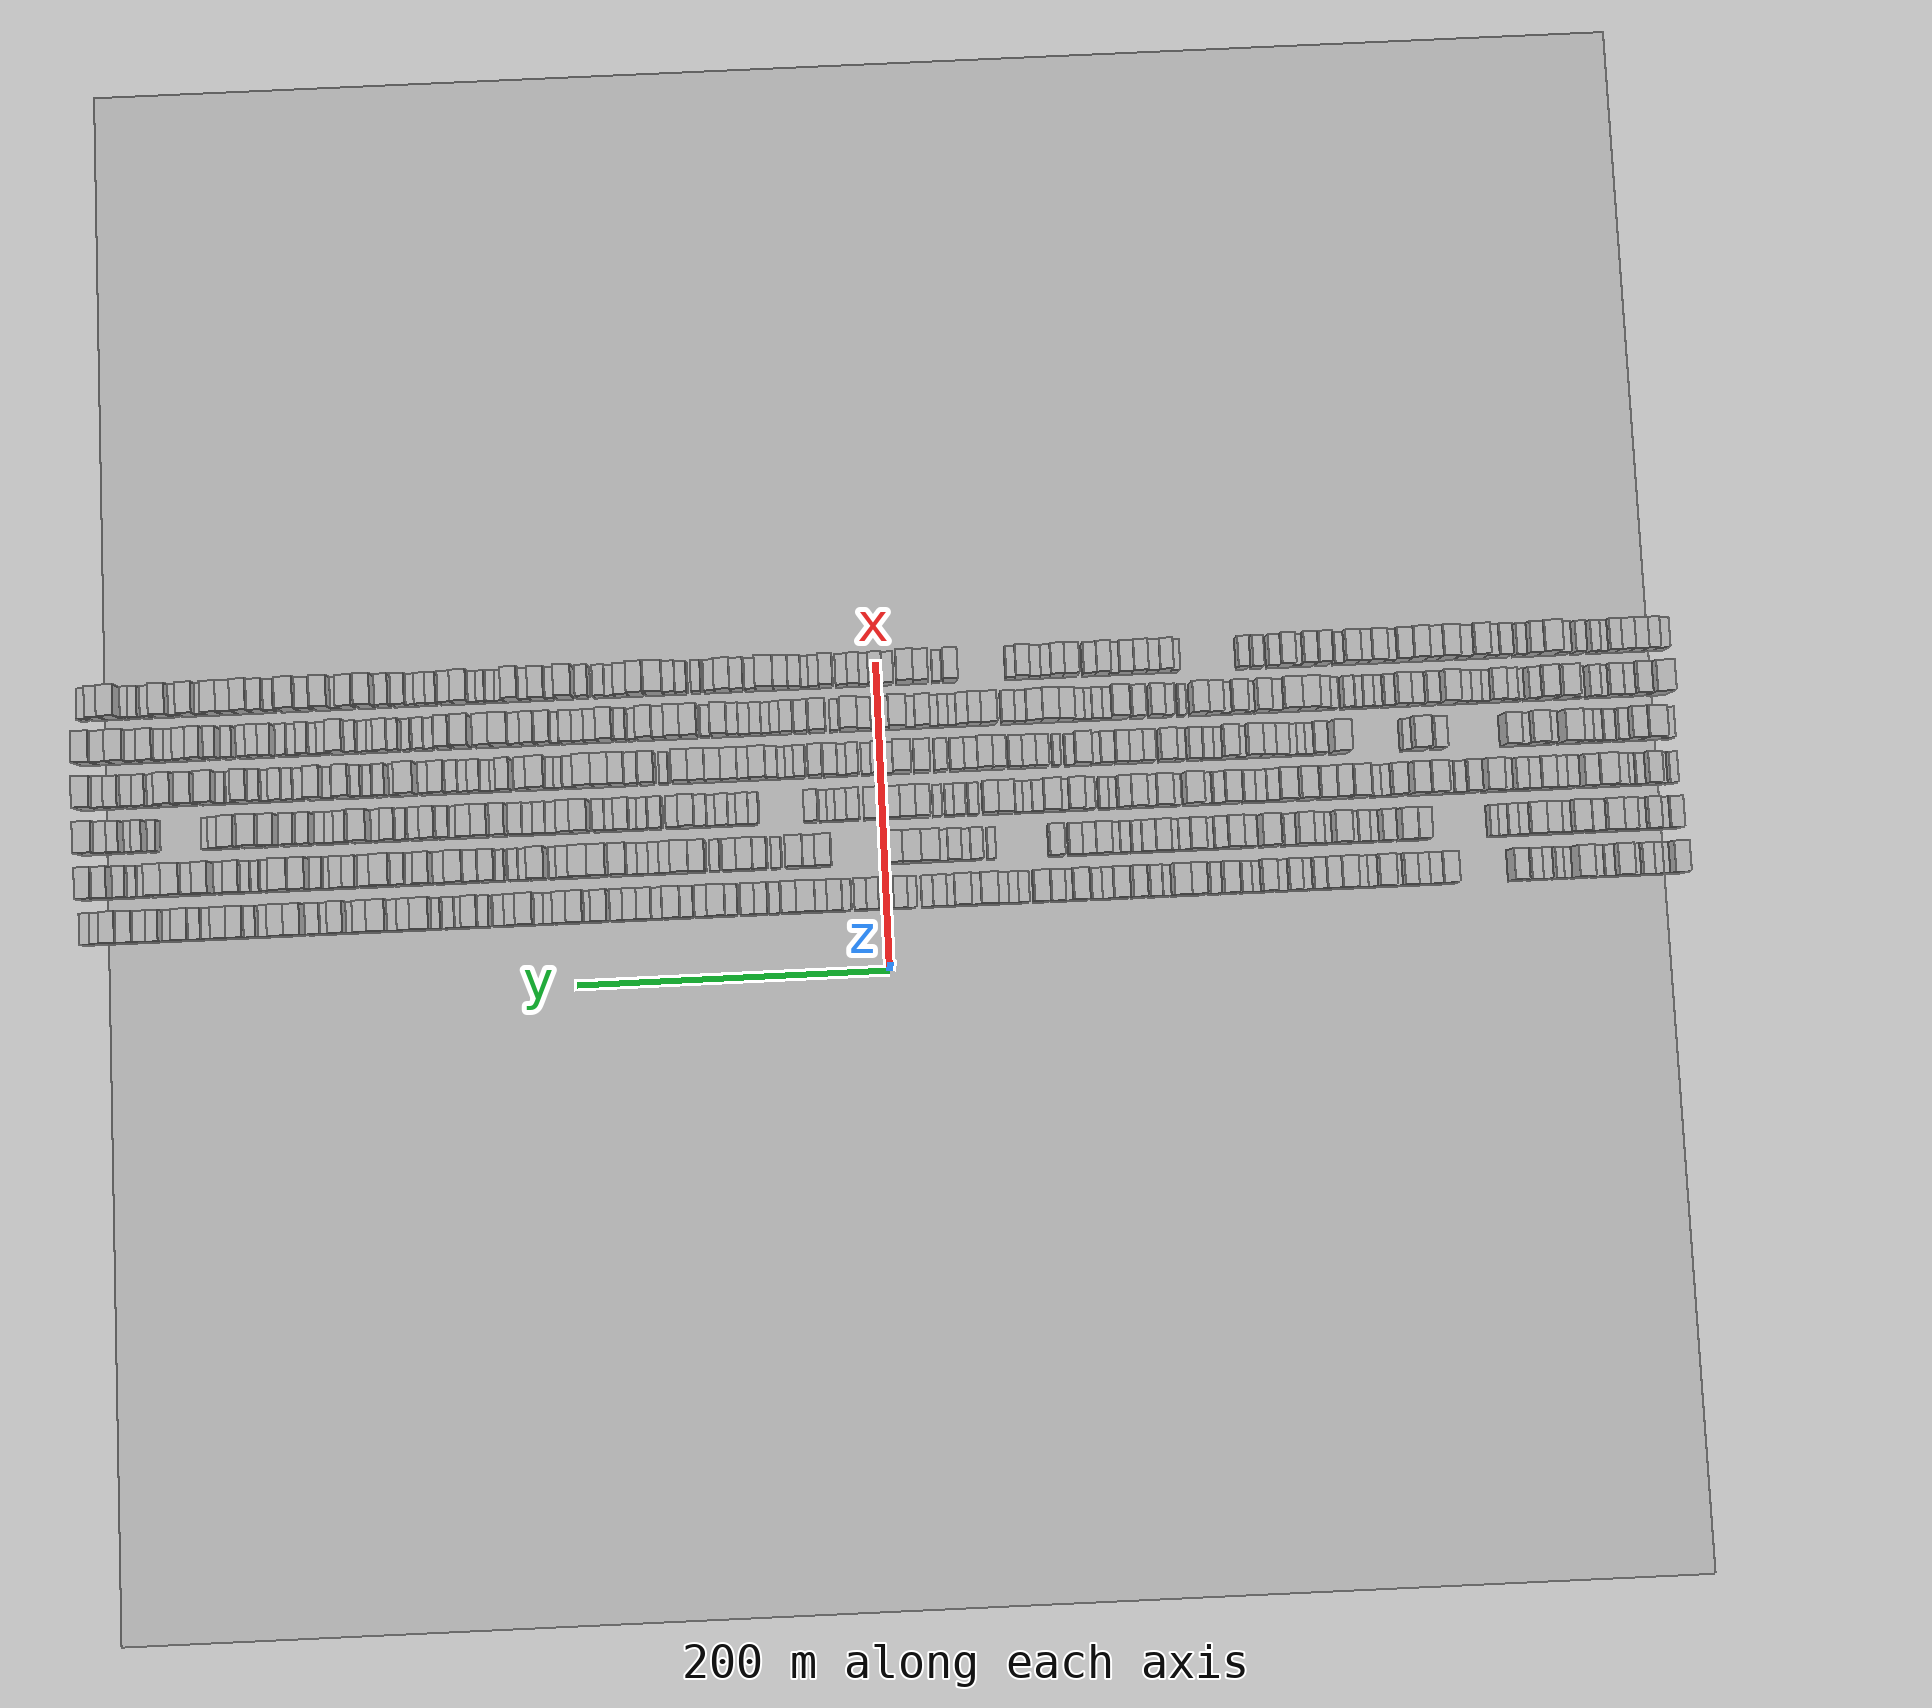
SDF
<?xml version="1.0" encoding="utf-8"?>

<sdf version="1.6">

   <world name="default">

      <gui fullscreen="0">

         <camera name="user_camera">

            <pose>-15 0 4.57585 0 0 0</pose>

            <view_controller>orbit</view_controller>

         </camera>

      </gui>

      <scene>

         <sky>

           <clouds>

             <speed>12</speed>

           </clouds>

         </sky>

         <ambient>0.4 0.4 0.4 1</ambient>

         <background>0.7 0.7 0.7 1</background>

         <shadows>1</shadows>

      </scene>

      <gravity>0 0 -9.8066</gravity>

      <magnetic_field>6e-06 2.3e-05 -4.2e-05</magnetic_field>

      <physics default="0" name="default_physics" type="ode">

         <ode>

            <solver>

               <type>quick</type>

               <iters>10</iters>

               <sor>1.0</sor>

               <use_dynamic_moi_rescaling>0</use_dynamic_moi_rescaling>

            </solver>

            <constraints>

               <cfm>0</cfm>

               <erp>0.2</erp>

               <contact_max_correcting_vel>100</contact_max_correcting_vel>

               <contact_surface_layer>0.001</contact_surface_layer>

            </constraints>

         </ode>

         <max_step_size>0.004</max_step_size>

         <real_time_factor>1</real_time_factor>

         <real_time_update_rate>250</real_time_update_rate>

      </physics>

      <light name="sun" type="directional">

         <cast_shadows>1</cast_shadows>

         <pose>0 0 10 0 0 0</pose>

         <diffuse>0.8 0.8 0.8 1</diffuse>

         <specular>0.2 0.2 0.2 1</specular>

         <attenuation>

            <range>1000</range>

            <constant>0.9</constant>

            <linear>0.01</linear>

            <quadratic>0.001</quadratic>

         </attenuation>

         <direction>-0.5 0.1 -0.9</direction>

      </light>

      <include>

         <name>ground_plane_1</name>

         <uri>model://HANNAS_ground_plane</uri>

         <pose>0 0 0  0 0 0</pose>

      </include>

      <include>

         <name>ground_plane_2</name>

         <uri>model://HANNAS_ground_plane</uri>

         <pose>100 0 0  0 0 0</pose>

      </include>

      <model name="building_1">

         <static>1</static>

         <pose frame="">50.0000 -505.0870 0 0.000000 0.000000 0.000000</pose>

         <link name="link">

            <pose frame="">0 0 12.00 0 0 0</pose>

            <collision name="collision">

               <geometry>

                  <box>

                     <size>20.0000 9.8260 24.0000</size>

                  </box>

               </geometry>

               <max_contacts>10</max_contacts>

               <surface>

                  <contact>

                     <ode/>

                  </contact>

                  <bounce/>

                  <friction>

                     <torsional>

                        <ode/>

                     </torsional>

                     <ode/>

                  </friction>

               </surface>

            </collision>

            <visual name="visual">

               <cast_shadows>0</cast_shadows>

               <geometry>

                  <box>

                     <size>20.0000 9.8260 24.0000</size>

                  </box>

               </geometry>

               <material>

                  <script>

                     <uri>model://HANNAS_wall/materials/scripts</uri>

                     <uri>model://HANNAS_wall/materials/textures</uri>

                     <name>vrc/HANNAS_wall</name>

                  </script>

               </material>

            </visual>

            <self_collide>0</self_collide>

            <enable_wind>0</enable_wind>

            <kinematic>0</kinematic>

         </link>

      </model>

      <model name="building_2">

         <static>1</static>

         <pose frame="">50.0000 -497.7677 0 0.000000 0.000000 0.000000</pose>

         <link name="link">

            <pose frame="">0 0 6.00 0 0 0</pose>

            <collision name="collision">

               <geometry>

                  <box>

                     <size>20.0000 4.8125 12.0000</size>

                  </box>

               </geometry>

               <max_contacts>10</max_contacts>

               <surface>

                  <contact>

                     <ode/>

                  </contact>

                  <bounce/>

                  <friction>

                     <torsional>

                        <ode/>

                     </torsional>

                     <ode/>

                  </friction>

               </surface>

            </collision>

            <visual name="visual">

               <cast_shadows>0</cast_shadows>

               <geometry>

                  <box>

                     <size>20.0000 4.8125 12.0000</size>

                  </box>

               </geometry>

               <material>

                  <script>

                     <uri>model://HANNAS_wall/materials/scripts</uri>

                     <uri>model://HANNAS_wall/materials/textures</uri>

                     <name>vrc/HANNAS_wall</name>

                  </script>

               </material>

            </visual>

            <self_collide>0</self_collide>

            <enable_wind>0</enable_wind>

            <kinematic>0</kinematic>

         </link>

      </model>

      <model name="building_3">

         <static>1</static>

         <pose frame="">50.0000 -492.1713 0 0.000000 0.000000 0.000000</pose>

         <link name="link">

            <pose frame="">0 0 7.50 0 0 0</pose>

            <collision name="collision">

               <geometry>

                  <box>

                     <size>20.0000 6.3803 15.0000</size>

                  </box>

               </geometry>

               <max_contacts>10</max_contacts>

               <surface>

                  <contact>

                     <ode/>

                  </contact>

                  <bounce/>

                  <friction>

                     <torsional>

                        <ode/>

                     </torsional>

                     <ode/>

                  </friction>

               </surface>

            </collision>

            <visual name="visual">

               <cast_shadows>0</cast_shadows>

               <geometry>

                  <box>

                     <size>20.0000 6.3803 15.0000</size>

                  </box>

               </geometry>

               <material>

                  <script>

                     <uri>model://HANNAS_wall/materials/scripts</uri>

                     <uri>model://HANNAS_wall/materials/textures</uri>

                     <name>vrc/HANNAS_wall</name>

                  </script>

               </material>

            </visual>

            <self_collide>0</self_collide>

            <enable_wind>0</enable_wind>

            <kinematic>0</kinematic>

         </link>

      </model>

      <model name="building_4">

         <static>1</static>

         <pose frame="">50.0000 -485.2972 0 0.000000 0.000000 0.000000</pose>

         <link name="link">

            <pose frame="">0 0 9.00 0 0 0</pose>

            <collision name="collision">

               <geometry>

                  <box>

                     <size>20.0000 7.3679 18.0000</size>

                  </box>

               </geometry>

               <max_contacts>10</max_contacts>

               <surface>

                  <contact>

                     <ode/>

                  </contact>

                  <bounce/>

                  <friction>

                     <torsional>

                        <ode/>

                     </torsional>

                     <ode/>

                  </friction>

               </surface>

            </collision>

            <visual name="visual">

               <cast_shadows>0</cast_shadows>

               <geometry>

                  <box>

                     <size>20.0000 7.3679 18.0000</size>

                  </box>

               </geometry>

               <material>

                  <script>

                     <uri>model://HANNAS_wall/materials/scripts</uri>

                     <uri>model://HANNAS_wall/materials/textures</uri>

                     <name>vrc/HANNAS_wall</name>

                  </script>

               </material>

            </visual>

            <self_collide>0</self_collide>

            <enable_wind>0</enable_wind>

            <kinematic>0</kinematic>

         </link>

      </model>

      <model name="building_5">

         <static>1</static>

         <pose frame="">50.0000 -478.7426 0 0.000000 0.000000 0.000000</pose>

         <link name="link">

            <pose frame="">0 0 6.00 0 0 0</pose>

            <collision name="collision">

               <geometry>

                  <box>

                     <size>20.0000 5.7415 12.0000</size>

                  </box>

               </geometry>

               <max_contacts>10</max_contacts>

               <surface>

                  <contact>

                     <ode/>

                  </contact>

                  <bounce/>

                  <friction>

                     <torsional>

                        <ode/>

                     </torsional>

                     <ode/>

                  </friction>

               </surface>

            </collision>

            <visual name="visual">

               <cast_shadows>0</cast_shadows>

               <geometry>

                  <box>

                     <size>20.0000 5.7415 12.0000</size>

                  </box>

               </geometry>

               <material>

                  <script>

                     <uri>model://HANNAS_wall/materials/scripts</uri>

                     <uri>model://HANNAS_wall/materials/textures</uri>

                     <name>vrc/HANNAS_wall</name>

                  </script>

               </material>

            </visual>

            <self_collide>0</self_collide>

            <enable_wind>0</enable_wind>

            <kinematic>0</kinematic>

         </link>

      </model>

      <model name="building_6">

         <static>1</static>

         <pose frame="">50.0000 -469.6219 0 0.000000 0.000000 0.000000</pose>

         <link name="link">

            <pose frame="">0 0 12.00 0 0 0</pose>

            <collision name="collision">

               <geometry>

                  <box>

                     <size>20.0000 10.4998 24.0000</size>

                  </box>

               </geometry>

               <max_contacts>10</max_contacts>

               <surface>

                  <contact>

                     <ode/>

                  </contact>

                  <bounce/>

                  <friction>

                     <torsional>

                        <ode/>

                     </torsional>

                     <ode/>

                  </friction>

               </surface>

            </collision>

            <visual name="visual">

               <cast_shadows>0</cast_shadows>

               <geometry>

                  <box>

                     <size>20.0000 10.4998 24.0000</size>

                  </box>

               </geometry>

               <material>

                  <script>

                     <uri>model://HANNAS_wall/materials/scripts</uri>

                     <uri>model://HANNAS_wall/materials/textures</uri>

                     <name>vrc/HANNAS_wall</name>

                  </script>

               </material>

            </visual>

            <self_collide>0</self_collide>

            <enable_wind>0</enable_wind>

            <kinematic>0</kinematic>

         </link>

      </model>

      <model name="building_7">

         <static>1</static>

         <pose frame="">50.0000 -461.2395 0 0.000000 0.000000 0.000000</pose>

         <link name="link">

            <pose frame="">0 0 7.50 0 0 0</pose>

            <collision name="collision">

               <geometry>

                  <box>

                     <size>20.0000 6.2650 15.0000</size>

                  </box>

               </geometry>

               <max_contacts>10</max_contacts>

               <surface>

                  <contact>

                     <ode/>

                  </contact>

                  <bounce/>

                  <friction>

                     <torsional>

                        <ode/>

                     </torsional>

                     <ode/>

                  </friction>

               </surface>

            </collision>

            <visual name="visual">

               <cast_shadows>0</cast_shadows>

               <geometry>

                  <box>

                     <size>20.0000 6.2650 15.0000</size>

                  </box>

               </geometry>

               <material>

                  <script>

                     <uri>model://HANNAS_wall/materials/scripts</uri>

                     <uri>model://HANNAS_wall/materials/textures</uri>

                     <name>vrc/HANNAS_wall</name>

                  </script>

               </material>

            </visual>

            <self_collide>0</self_collide>

            <enable_wind>0</enable_wind>

            <kinematic>0</kinematic>

         </link>

      </model>

      <model name="building_8">

         <static>1</static>

         <pose frame="">50.0000 -455.3796 0 0.000000 0.000000 0.000000</pose>

         <link name="link">

            <pose frame="">0 0 6.00 0 0 0</pose>

            <collision name="collision">

               <geometry>

                  <box>

                     <size>20.0000 5.4549 12.0000</size>

                  </box>

               </geometry>

               <max_contacts>10</max_contacts>

               <surface>

                  <contact>

                     <ode/>

                  </contact>

                  <bounce/>

                  <friction>

                     <torsional>

                        <ode/>

                     </torsional>

                     <ode/>

                  </friction>

               </surface>

            </collision>

            <visual name="visual">

               <cast_shadows>0</cast_shadows>

               <geometry>

                  <box>

                     <size>20.0000 5.4549 12.0000</size>

                  </box>

               </geometry>

               <material>

                  <script>

                     <uri>model://HANNAS_wall/materials/scripts</uri>

                     <uri>model://HANNAS_wall/materials/textures</uri>

                     <name>vrc/HANNAS_wall</name>

                  </script>

               </material>

            </visual>

            <self_collide>0</self_collide>

            <enable_wind>0</enable_wind>

            <kinematic>0</kinematic>

         </link>

      </model>

      <model name="building_9">

         <static>1</static>

         <pose frame="">50.0000 -444.5758 0 0.000000 0.000000 0.000000</pose>

         <link name="link">

            <pose frame="">0 0 12.00 0 0 0</pose>

            <collision name="collision">

               <geometry>

                  <box>

                     <size>20.0000 10.1526 24.0000</size>

                  </box>

               </geometry>

               <max_contacts>10</max_contacts>

               <surface>

                  <contact>

                     <ode/>

                  </contact>

                  <bounce/>

                  <friction>

                     <torsional>

                        <ode/>

                     </torsional>

                     <ode/>

                  </friction>

               </surface>

            </collision>

            <visual name="visual">

               <cast_shadows>0</cast_shadows>

               <geometry>

                  <box>

                     <size>20.0000 10.1526 24.0000</size>

                  </box>

               </geometry>

               <material>

                  <script>

                     <uri>model://HANNAS_wall/materials/scripts</uri>

                     <uri>model://HANNAS_wall/materials/textures</uri>

                     <name>vrc/HANNAS_wall</name>

                  </script>

               </material>

            </visual>

            <self_collide>0</self_collide>

            <enable_wind>0</enable_wind>

            <kinematic>0</kinematic>

         </link>

      </model>

      <model name="building_10">

         <static>1</static>

         <pose frame="">50.0000 -435.0902 0 0.000000 0.000000 0.000000</pose>

         <link name="link">

            <pose frame="">0 0 6.00 0 0 0</pose>

            <collision name="collision">

               <geometry>

                  <box>

                     <size>20.0000 4.8186 12.0000</size>

                  </box>

               </geometry>

               <max_contacts>10</max_contacts>

               <surface>

                  <contact>

                     <ode/>

                  </contact>

                  <bounce/>

                  <friction>

                     <torsional>

                        <ode/>

                     </torsional>

                     <ode/>

                  </friction>

               </surface>

            </collision>

            <visual name="visual">

               <cast_shadows>0</cast_shadows>

               <geometry>

                  <box>

                     <size>20.0000 4.8186 12.0000</size>

                  </box>

               </geometry>

               <material>

                  <script>

                     <uri>model://HANNAS_wall/materials/scripts</uri>

                     <uri>model://HANNAS_wall/materials/textures</uri>

                     <name>vrc/HANNAS_wall</name>

                  </script>

               </material>

            </visual>

            <self_collide>0</self_collide>

            <enable_wind>0</enable_wind>

            <kinematic>0</kinematic>

         </link>

      </model>

      <model name="building_11">

         <static>1</static>

         <pose frame="">50.0000 -430.2362 0 0.000000 0.000000 0.000000</pose>

         <link name="link">

            <pose frame="">0 0 6.00 0 0 0</pose>

            <collision name="collision">

               <geometry>

                  <box>

                     <size>20.0000 4.8894 12.0000</size>

                  </box>

               </geometry>

               <max_contacts>10</max_contacts>

               <surface>

                  <contact>

                     <ode/>

                  </contact>

                  <bounce/>

                  <friction>

                     <torsional>

                        <ode/>

                     </torsional>

                     <ode/>

                  </friction>

               </surface>

            </collision>

            <visual name="visual">

               <cast_shadows>0</cast_shadows>

               <geometry>

                  <box>

                     <size>20.0000 4.8894 12.0000</size>

                  </box>

               </geometry>

               <material>

                  <script>

                     <uri>model://HANNAS_wall/materials/scripts</uri>

                     <uri>model://HANNAS_wall/materials/textures</uri>

                     <name>vrc/HANNAS_wall</name>

                  </script>

               </material>

            </visual>

            <self_collide>0</self_collide>

            <enable_wind>0</enable_wind>

            <kinematic>0</kinematic>

         </link>

      </model>

      <model name="building_12">

         <static>1</static>

         <pose frame="">50.0000 -421.6519 0 0.000000 0.000000 0.000000</pose>

         <link name="link">

            <pose frame="">0 0 7.50 0 0 0</pose>

            <collision name="collision">

               <geometry>

                  <box>

                     <size>20.0000 6.2792 15.0000</size>

                  </box>

               </geometry>

               <max_contacts>10</max_contacts>

               <surface>

                  <contact>

                     <ode/>

                  </contact>

                  <bounce/>

                  <friction>

                     <torsional>

                        <ode/>

                     </torsional>

                     <ode/>

                  </friction>

               </surface>

            </collision>

            <visual name="visual">

               <cast_shadows>0</cast_shadows>

               <geometry>

                  <box>

                     <size>20.0000 6.2792 15.0000</size>

                  </box>

               </geometry>

               <material>

                  <script>

                     <uri>model://HANNAS_wall/materials/scripts</uri>

                     <uri>model://HANNAS_wall/materials/textures</uri>

                     <name>vrc/HANNAS_wall</name>

                  </script>

               </material>

            </visual>

            <self_collide>0</self_collide>

            <enable_wind>0</enable_wind>

            <kinematic>0</kinematic>

         </link>

      </model>

      <model name="building_13">

         <static>1</static>

         <pose frame="">50.0000 -414.9698 0 0.000000 0.000000 0.000000</pose>

         <link name="link">

            <pose frame="">0 0 7.50 0 0 0</pose>

            <collision name="collision">

               <geometry>

                  <box>

                     <size>20.0000 7.0849 15.0000</size>

                  </box>

               </geometry>

               <max_contacts>10</max_contacts>

               <surface>

                  <contact>

                     <ode/>

                  </contact>

                  <bounce/>

                  <friction>

                     <torsional>

                        <ode/>

                     </torsional>

                     <ode/>

                  </friction>

               </surface>

            </collision>

            <visual name="visual">

               <cast_shadows>0</cast_shadows>

               <geometry>

                  <box>

                     <size>20.0000 7.0849 15.0000</size>

                  </box>

               </geometry>

               <material>

                  <script>

                     <uri>model://HANNAS_wall/materials/scripts</uri>

                     <uri>model://HANNAS_wall/materials/textures</uri>

                     <name>vrc/HANNAS_wall</name>

                  </script>

               </material>

            </visual>

            <self_collide>0</self_collide>

            <enable_wind>0</enable_wind>

            <kinematic>0</kinematic>

         </link>

      </model>

      <model name="building_14">

         <static>1</static>

         <pose frame="">50.0000 -403.7910 0 0.000000 0.000000 0.000000</pose>

         <link name="link">

            <pose frame="">0 0 10.50 0 0 0</pose>

            <collision name="collision">

               <geometry>

                  <box>

                     <size>20.0000 9.2728 21.0000</size>

                  </box>

               </geometry>

               <max_contacts>10</max_contacts>

               <surface>

                  <contact>

                     <ode/>

                  </contact>

                  <bounce/>

                  <friction>

                     <torsional>

                        <ode/>

                     </torsional>

                     <ode/>

                  </friction>

               </surface>

            </collision>

            <visual name="visual">

               <cast_shadows>0</cast_shadows>

               <geometry>

                  <box>

                     <size>20.0000 9.2728 21.0000</size>

                  </box>

               </geometry>

               <material>

                  <script>

                     <uri>model://HANNAS_wall/materials/scripts</uri>

                     <uri>model://HANNAS_wall/materials/textures</uri>

                     <name>vrc/HANNAS_wall</name>

                  </script>

               </material>

            </visual>

            <self_collide>0</self_collide>

            <enable_wind>0</enable_wind>

            <kinematic>0</kinematic>

         </link>

      </model>

      <model name="building_15">

         <static>1</static>

         <pose frame="">50.0000 -358.9946 0 0.000000 0.000000 0.000000</pose>

         <link name="link">

            <pose frame="">0 0 10.50 0 0 0</pose>

            <collision name="collision">

               <geometry>

                  <box>

                     <size>20.0000 10.1067 21.0000</size>

                  </box>

               </geometry>

               <max_contacts>10</max_contacts>

               <surface>

                  <contact>

                     <ode/>

                  </contact>

                  <bounce/>

                  <friction>

                     <torsional>

                        <ode/>

                     </torsional>

                     <ode/>

                  </friction>

               </surface>

            </collision>

            <visual name="visual">

               <cast_shadows>0</cast_shadows>

               <geometry>

                  <box>

                     <size>20.0000 10.1067 21.0000</size>

                  </box>

               </geometry>

               <material>

                  <script>

                     <uri>model://HANNAS_wall/materials/scripts</uri>

                     <uri>model://HANNAS_wall/materials/textures</uri>

                     <name>vrc/HANNAS_wall</name>

                  </script>

               </material>

            </visual>

            <self_collide>0</self_collide>

            <enable_wind>0</enable_wind>

            <kinematic>0</kinematic>

         </link>

      </model>

      <model name="building_16">

         <static>1</static>

         <pose frame="">50.0000 -349.8433 0 0.000000 0.000000 0.000000</pose>

         <link name="link">

            <pose frame="">0 0 9.00 0 0 0</pose>

            <collision name="collision">

               <geometry>

                  <box>

                     <size>20.0000 8.1957 18.0000</size>

                  </box>

               </geometry>

               <max_contacts>10</max_contacts>

               <surface>

                  <contact>

                     <ode/>

                  </contact>

                  <bounce/>

                  <friction>

                     <torsional>

                        <ode/>

                     </torsional>

                     <ode/>

                  </friction>

               </surface>

            </collision>

            <visual name="visual">

               <cast_shadows>0</cast_shadows>

               <geometry>

                  <box>

                     <size>20.0000 8.1957 18.0000</size>

                  </box>

               </geometry>

               <material>

                  <script>

                     <uri>model://HANNAS_wall/materials/scripts</uri>

                     <uri>model://HANNAS_wall/materials/textures</uri>

                     <name>vrc/HANNAS_wall</name>

                  </script>

               </material>

            </visual>

            <self_collide>0</self_collide>

            <enable_wind>0</enable_wind>

            <kinematic>0</kinematic>

         </link>

      </model>

      <model name="building_17">

         <static>1</static>

         <pose frame="">50.0000 -341.8175 0 0.000000 0.000000 0.000000</pose>

         <link name="link">

            <pose frame="">0 0 9.00 0 0 0</pose>

            <collision name="collision">

               <geometry>

                  <box>

                     <size>20.0000 7.8559 18.0000</size>

                  </box>

               </geometry>

               <max_contacts>10</max_contacts>

               <surface>

                  <contact>

                     <ode/>

                  </contact>

                  <bounce/>

                  <friction>

                     <torsional>

                        <ode/>

                     </torsional>

                     <ode/>

                  </friction>

               </surface>

            </collision>

            <visual name="visual">

               <cast_shadows>0</cast_shadows>

               <geometry>

                  <box>

                     <size>20.0000 7.8559 18.0000</size>

                  </box>

               </geometry>

               <material>

                  <script>

                     <uri>model://HANNAS_wall/materials/scripts</uri>

                     <uri>model://HANNAS_wall/materials/textures</uri>

                     <name>vrc/HANNAS_wall</name>

                  </script>

               </material>

            </visual>

            <self_collide>0</self_collide>

            <enable_wind>0</enable_wind>

            <kinematic>0</kinematic>

         </link>

      </model>

      <model name="building_18">

         <static>1</static>

         <pose frame="">50.0000 -333.5378 0 0.000000 0.000000 0.000000</pose>

         <link name="link">

            <pose frame="">0 0 10.50 0 0 0</pose>

            <collision name="collision">

               <geometry>

                  <box>

                     <size>20.0000 8.7036 21.0000</size>

                  </box>

               </geometry>

               <max_contacts>10</max_contacts>

               <surface>

                  <contact>

                     <ode/>

                  </contact>

                  <bounce/>

                  <friction>

                     <torsional>

                        <ode/>

                     </torsional>

                     <ode/>

                  </friction>

               </surface>

            </collision>

            <visual name="visual">

               <cast_shadows>0</cast_shadows>

               <geometry>

                  <box>

                     <size>20.0000 8.7036 21.0000</size>

                  </box>

               </geometry>

               <material>

                  <script>

                     <uri>model://HANNAS_wall/materials/scripts</uri>

                     <uri>model://HANNAS_wall/materials/textures</uri>

                     <name>vrc/HANNAS_wall</name>

                  </script>

               </material>

            </visual>

            <self_collide>0</self_collide>

            <enable_wind>0</enable_wind>

            <kinematic>0</kinematic>

         </link>

      </model>

      <model name="building_19">

         <static>1</static>

         <pose frame="">50.0000 -326.4478 0 0.000000 0.000000 0.000000</pose>

         <link name="link">

            <pose frame="">0 0 6.00 0 0 0</pose>

            <collision name="collision">

               <geometry>

                  <box>

                     <size>20.0000 5.4764 12.0000</size>

                  </box>

               </geometry>

               <max_contacts>10</max_contacts>

               <surface>

                  <contact>

                     <ode/>

                  </contact>

                  <bounce/>

                  <friction>

                     <torsional>

                        <ode/>

                     </torsional>

                     <ode/>

                  </friction>

               </surface>

            </collision>

            <visual name="visual">

               <cast_shadows>0</cast_shadows>

               <geometry>

                  <box>

                     <size>20.0000 5.4764 12.0000</size>

                  </box>

               </geometry>

               <material>

                  <script>

                     <uri>model://HANNAS_wall/materials/scripts</uri>

                     <uri>model://HANNAS_wall/materials/textures</uri>

                     <name>vrc/HANNAS_wall</name>

                  </script>

               </material>

            </visual>

            <self_collide>0</self_collide>

            <enable_wind>0</enable_wind>

            <kinematic>0</kinematic>

         </link>

      </model>

      <model name="building_20">

         <static>1</static>

         <pose frame="">50.0000 -318.2352 0 0.000000 0.000000 0.000000</pose>

         <link name="link">

            <pose frame="">0 0 12.00 0 0 0</pose>

            <collision name="collision">

               <geometry>

                  <box>

                     <size>20.0000 10.9488 24.0000</size>

                  </box>

               </geometry>

               <max_contacts>10</max_contacts>

               <surface>

                  <contact>

                     <ode/>

                  </contact>

                  <bounce/>

                  <friction>

                     <torsional>

                        <ode/>

                     </torsional>

                     <ode/>

                  </friction>

               </surface>

            </collision>

            <visual name="visual">

               <cast_shadows>0</cast_shadows>

               <geometry>

                  <box>

                     <size>20.0000 10.9488 24.0000</size>

                  </box>

               </geometry>

               <material>

                  <script>

                     <uri>model://HANNAS_wall/materials/scripts</uri>

                     <uri>model://HANNAS_wall/materials/textures</uri>

                     <name>vrc/HANNAS_wall</name>

                  </script>

               </material>

            </visual>

            <self_collide>0</self_collide>

            <enable_wind>0</enable_wind>

            <kinematic>0</kinematic>

         </link>

      </model>

      <model name="building_21">

         <static>1</static>

         <pose frame="">50.0000 -309.6985 0 0.000000 0.000000 0.000000</pose>

         <link name="link">

            <pose frame="">0 0 7.50 0 0 0</pose>

            <collision name="collision">

               <geometry>

                  <box>

                     <size>20.0000 6.1246 15.0000</size>

                  </box>

               </geometry>

               <max_contacts>10</max_contacts>

               <surface>

                  <contact>

                     <ode/>

                  </contact>

                  <bounce/>

                  <friction>

                     <torsional>

                        <ode/>

                     </torsional>

                     <ode/>

                  </friction>

               </surface>

            </collision>

            <visual name="visual">

               <cast_shadows>0</cast_shadows>

               <geometry>

                  <box>

                     <size>20.0000 6.1246 15.0000</size>

                  </box>

               </geometry>

               <material>

                  <script>

                     <uri>model://HANNAS_wall/materials/scripts</uri>

                     <uri>model://HANNAS_wall/materials/textures</uri>

                     <name>vrc/HANNAS_wall</name>

                  </script>

               </material>

            </visual>

            <self_collide>0</self_collide>

            <enable_wind>0</enable_wind>

            <kinematic>0</kinematic>

         </link>

      </model>

      <model name="building_22">

         <static>1</static>

         <pose frame="">50.0000 -303.1202 0 0.000000 0.000000 0.000000</pose>

         <link name="link">

            <pose frame="">0 0 7.50 0 0 0</pose>

            <collision name="collision">

               <geometry>

                  <box>

                     <size>20.0000 7.0321 15.0000</size>

                  </box>

               </geometry>

               <max_contacts>10</max_contacts>

               <surface>

                  <contact>

                     <ode/>

                  </contact>

                  <bounce/>

                  <friction>

                     <torsional>

                        <ode/>

                     </torsional>

                     <ode/>

                  </friction>

               </surface>

            </collision>

            <visual name="visual">

               <cast_shadows>0</cast_shadows>

               <geometry>

                  <box>

                     <size>20.0000 7.0321 15.0000</size>

                  </box>

               </geometry>

               <material>

                  <script>

                     <uri>model://HANNAS_wall/materials/scripts</uri>

                     <uri>model://HANNAS_wall/materials/textures</uri>

                     <name>vrc/HANNAS_wall</name>

                  </script>

               </material>

            </visual>

            <self_collide>0</self_collide>

            <enable_wind>0</enable_wind>

            <kinematic>0</kinematic>

         </link>

      </model>

      <model name="building_23">

         <static>1</static>

         <pose frame="">50.0000 -294.4013 0 0.000000 0.000000 0.000000</pose>

         <link name="link">

            <pose frame="">0 0 12.00 0 0 0</pose>

            <collision name="collision">

               <geometry>

                  <box>

                     <size>20.0000 10.4056 24.0000</size>

                  </box>

               </geometry>

               <max_contacts>10</max_contacts>

               <surface>

                  <contact>

                     <ode/>

                  </contact>

                  <bounce/>

                  <friction>

                     <torsional>

                        <ode/>

                     </torsional>

                     <ode/>

                  </friction>

               </surface>

            </collision>

            <visual name="visual">

               <cast_shadows>0</cast_shadows>

               <geometry>

                  <box>

                     <size>20.0000 10.4056 24.0000</size>

                  </box>

               </geometry>

               <material>

                  <script>

                     <uri>model://HANNAS_wall/materials/scripts</uri>

                     <uri>model://HANNAS_wall/materials/textures</uri>

                     <name>vrc/HANNAS_wall</name>

                  </script>

               </material>

            </visual>

            <self_collide>0</self_collide>

            <enable_wind>0</enable_wind>

            <kinematic>0</kinematic>

         </link>

      </model>

      <model name="building_24">

         <static>1</static>

         <pose frame="">50.0000 -284.6056 0 0.000000 0.000000 0.000000</pose>

         <link name="link">

            <pose frame="">0 0 10.50 0 0 0</pose>

            <collision name="collision">

               <geometry>

                  <box>

                     <size>20.0000 9.1858 21.0000</size>

                  </box>

               </geometry>

               <max_contacts>10</max_contacts>

               <surface>

                  <contact>

                     <ode/>

                  </contact>

                  <bounce/>

                  <friction>

                     <torsional>

                        <ode/>

                     </torsional>

                     <ode/>

                  </friction>

               </surface>

            </collision>

            <visual name="visual">

               <cast_shadows>0</cast_shadows>

               <geometry>

                  <box>

                     <size>20.0000 9.1858 21.0000</size>

                  </box>

               </geometry>

               <material>

                  <script>

                     <uri>model://HANNAS_wall/materials/scripts</uri>

                     <uri>model://HANNAS_wall/materials/textures</uri>

                     <name>vrc/HANNAS_wall</name>

                  </script>

               </material>

            </visual>

            <self_collide>0</self_collide>

            <enable_wind>0</enable_wind>

            <kinematic>0</kinematic>

         </link>

      </model>

      <model name="building_25">

         <static>1</static>

         <pose frame="">50.0000 -275.9804 0 0.000000 0.000000 0.000000</pose>

         <link name="link">

            <pose frame="">0 0 9.00 0 0 0</pose>

            <collision name="collision">

               <geometry>

                  <box>

                     <size>20.0000 8.0647 18.0000</size>

                  </box>

               </geometry>

               <max_contacts>10</max_contacts>

               <surface>

                  <contact>

                     <ode/>

                  </contact>

                  <bounce/>

                  <friction>

                     <torsional>

                        <ode/>

                     </torsional>

                     <ode/>

                  </friction>

               </surface>

            </collision>

            <visual name="visual">

               <cast_shadows>0</cast_shadows>

               <geometry>

                  <box>

                     <size>20.0000 8.0647 18.0000</size>

                  </box>

               </geometry>

               <material>

                  <script>

                     <uri>model://HANNAS_wall/materials/scripts</uri>

                     <uri>model://HANNAS_wall/materials/textures</uri>

                     <name>vrc/HANNAS_wall</name>

                  </script>

               </material>

            </visual>

            <self_collide>0</self_collide>

            <enable_wind>0</enable_wind>

            <kinematic>0</kinematic>

         </link>

      </model>

      <model name="building_26">

         <static>1</static>

         <pose frame="">50.0000 -267.6769 0 0.000000 0.000000 0.000000</pose>

         <link name="link">

            <pose frame="">0 0 7.50 0 0 0</pose>

            <collision name="collision">

               <geometry>

                  <box>

                     <size>20.0000 6.5422 15.0000</size>

                  </box>

               </geometry>

               <max_contacts>10</max_contacts>

               <surface>

                  <contact>

                     <ode/>

                  </contact>

                  <bounce/>

                  <friction>

                     <torsional>

                        <ode/>

                     </torsional>

                     <ode/>

                  </friction>

               </surface>

            </collision>

            <visual name="visual">

               <cast_shadows>0</cast_shadows>

               <geometry>

                  <box>

                     <size>20.0000 6.5422 15.0000</size>

                  </box>

               </geometry>

               <material>

                  <script>

                     <uri>model://HANNAS_wall/materials/scripts</uri>

                     <uri>model://HANNAS_wall/materials/textures</uri>

                     <name>vrc/HANNAS_wall</name>

                  </script>

               </material>

            </visual>

            <self_collide>0</self_collide>

            <enable_wind>0</enable_wind>

            <kinematic>0</kinematic>

         </link>

      </model>

      <model name="building_27">

         <static>1</static>

         <pose frame="">50.0000 -260.1765 0 0.000000 0.000000 0.000000</pose>

         <link name="link">

            <pose frame="">0 0 10.50 0 0 0</pose>

            <collision name="collision">

               <geometry>

                  <box>

                     <size>20.0000 8.4587 21.0000</size>

                  </box>

               </geometry>

               <max_contacts>10</max_contacts>

               <surface>

                  <contact>

                     <ode/>

                  </contact>

                  <bounce/>

                  <friction>

                     <torsional>

                        <ode/>

                     </torsional>

                     <ode/>

                  </friction>

               </surface>

            </collision>

            <visual name="visual">

               <cast_shadows>0</cast_shadows>

               <geometry>

                  <box>

                     <size>20.0000 8.4587 21.0000</size>

                  </box>

               </geometry>

               <material>

                  <script>

                     <uri>model://HANNAS_wall/materials/scripts</uri>

                     <uri>model://HANNAS_wall/materials/textures</uri>

                     <name>vrc/HANNAS_wall</name>

                  </script>

               </material>

            </visual>

            <self_collide>0</self_collide>

            <enable_wind>0</enable_wind>

            <kinematic>0</kinematic>

         </link>

      </model>

      <model name="building_28">

         <static>1</static>

         <pose frame="">50.0000 -253.0022 0 0.000000 0.000000 0.000000</pose>

         <link name="link">

            <pose frame="">0 0 6.00 0 0 0</pose>

            <collision name="collision">

               <geometry>

                  <box>

                     <size>20.0000 5.8898 12.0000</size>

                  </box>

               </geometry>

               <max_contacts>10</max_contacts>

               <surface>

                  <contact>

                     <ode/>

                  </contact>

                  <bounce/>

                  <friction>

                     <torsional>

                        <ode/>

                     </torsional>

                     <ode/>

                  </friction>

               </surface>

            </collision>

            <visual name="visual">

               <cast_shadows>0</cast_shadows>

               <geometry>

                  <box>

                     <size>20.0000 5.8898 12.0000</size>

                  </box>

               </geometry>

               <material>

                  <script>

                     <uri>model://HANNAS_wall/materials/scripts</uri>

                     <uri>model://HANNAS_wall/materials/textures</uri>

                     <name>vrc/HANNAS_wall</name>

                  </script>

               </material>

            </visual>

            <self_collide>0</self_collide>

            <enable_wind>0</enable_wind>

            <kinematic>0</kinematic>

         </link>

      </model>

      <model name="building_29">

         <static>1</static>

         <pose frame="">50.0000 -243.1957 0 0.000000 0.000000 0.000000</pose>

         <link name="link">

            <pose frame="">0 0 12.00 0 0 0</pose>

            <collision name="collision">

               <geometry>

                  <box>

                     <size>20.0000 9.7231 24.0000</size>

                  </box>

               </geometry>

               <max_contacts>10</max_contacts>

               <surface>

                  <contact>

                     <ode/>

                  </contact>

                  <bounce/>

                  <friction>

                     <torsional>

                        <ode/>

                     </torsional>

                     <ode/>

                  </friction>

               </surface>

            </collision>

            <visual name="visual">

               <cast_shadows>0</cast_shadows>

               <geometry>

                  <box>

                     <size>20.0000 9.7231 24.0000</size>

                  </box>

               </geometry>

               <material>

                  <script>

                     <uri>model://HANNAS_wall/materials/scripts</uri>

                     <uri>model://HANNAS_wall/materials/textures</uri>

                     <name>vrc/HANNAS_wall</name>

                  </script>

               </material>

            </visual>

            <self_collide>0</self_collide>

            <enable_wind>0</enable_wind>

            <kinematic>0</kinematic>

         </link>

      </model>

      <model name="building_30">

         <static>1</static>

         <pose frame="">50.0000 -235.5578 0 0.000000 0.000000 0.000000</pose>

         <link name="link">

            <pose frame="">0 0 6.00 0 0 0</pose>

            <collision name="collision">

               <geometry>

                  <box>

                     <size>20.0000 5.5527 12.0000</size>

                  </box>

               </geometry>

               <max_contacts>10</max_contacts>

               <surface>

                  <contact>

                     <ode/>

                  </contact>

                  <bounce/>

                  <friction>

                     <torsional>

                        <ode/>

                     </torsional>

                     <ode/>

                  </friction>

               </surface>

            </collision>

            <visual name="visual">

               <cast_shadows>0</cast_shadows>

               <geometry>

                  <box>

                     <size>20.0000 5.5527 12.0000</size>

                  </box>

               </geometry>

               <material>

                  <script>

                     <uri>model://HANNAS_wall/materials/scripts</uri>

                     <uri>model://HANNAS_wall/materials/textures</uri>

                     <name>vrc/HANNAS_wall</name>

                  </script>

               </material>

            </visual>

            <self_collide>0</self_collide>

            <enable_wind>0</enable_wind>

            <kinematic>0</kinematic>

         </link>

      </model>

      <model name="building_31">

         <static>1</static>

         <pose frame="">50.0000 -229.6478 0 0.000000 0.000000 0.000000</pose>

         <link name="link">

            <pose frame="">0 0 7.50 0 0 0</pose>

            <collision name="collision">

               <geometry>

                  <box>

                     <size>20.0000 6.2674 15.0000</size>

                  </box>

               </geometry>

               <max_contacts>10</max_contacts>

               <surface>

                  <contact>

                     <ode/>

                  </contact>

                  <bounce/>

                  <friction>

                     <torsional>

                        <ode/>

                     </torsional>

                     <ode/>

                  </friction>

               </surface>

            </collision>

            <visual name="visual">

               <cast_shadows>0</cast_shadows>

               <geometry>

                  <box>

                     <size>20.0000 6.2674 15.0000</size>

                  </box>

               </geometry>

               <material>

                  <script>

                     <uri>model://HANNAS_wall/materials/scripts</uri>

                     <uri>model://HANNAS_wall/materials/textures</uri>

                     <name>vrc/HANNAS_wall</name>

                  </script>

               </material>

            </visual>

            <self_collide>0</self_collide>

            <enable_wind>0</enable_wind>

            <kinematic>0</kinematic>

         </link>

      </model>

      <model name="building_32">

         <static>1</static>

         <pose frame="">50.0000 -219.4046 0 0.000000 0.000000 0.000000</pose>

         <link name="link">

            <pose frame="">0 0 10.50 0 0 0</pose>

            <collision name="collision">

               <geometry>

                  <box>

                     <size>20.0000 10.2190 21.0000</size>

                  </box>

               </geometry>

               <max_contacts>10</max_contacts>

               <surface>

                  <contact>

                     <ode/>

                  </contact>

                  <bounce/>

                  <friction>

                     <torsional>

                        <ode/>

                     </torsional>

                     <ode/>

                  </friction>

               </surface>

            </collision>

            <visual name="visual">

               <cast_shadows>0</cast_shadows>

               <geometry>

                  <box>

                     <size>20.0000 10.2190 21.0000</size>

                  </box>

               </geometry>

               <material>

                  <script>

                     <uri>model://HANNAS_wall/materials/scripts</uri>

                     <uri>model://HANNAS_wall/materials/textures</uri>

                     <name>vrc/HANNAS_wall</name>

                  </script>

               </material>

            </visual>

            <self_collide>0</self_collide>

            <enable_wind>0</enable_wind>

            <kinematic>0</kinematic>

         </link>

      </model>

      <model name="building_33">

         <static>1</static>

         <pose frame="">50.0000 -209.7942 0 0.000000 0.000000 0.000000</pose>

         <link name="link">

            <pose frame="">0 0 7.50 0 0 0</pose>

            <collision name="collision">

               <geometry>

                  <box>

                     <size>20.0000 7.0017 15.0000</size>

                  </box>

               </geometry>

               <max_contacts>10</max_contacts>

               <surface>

                  <contact>

                     <ode/>

                  </contact>

                  <bounce/>

                  <friction>

                     <torsional>

                        <ode/>

                     </torsional>

                     <ode/>

                  </friction>

               </surface>

            </collision>

            <visual name="visual">

               <cast_shadows>0</cast_shadows>

               <geometry>

                  <box>

                     <size>20.0000 7.0017 15.0000</size>

                  </box>

               </geometry>

               <material>

                  <script>

                     <uri>model://HANNAS_wall/materials/scripts</uri>

                     <uri>model://HANNAS_wall/materials/textures</uri>

                     <name>vrc/HANNAS_wall</name>

                  </script>

               </material>

            </visual>

            <self_collide>0</self_collide>

            <enable_wind>0</enable_wind>

            <kinematic>0</kinematic>

         </link>

      </model>

      <model name="building_34">

         <static>1</static>

         <pose frame="">50.0000 -198.2594 0 0.000000 0.000000 0.000000</pose>

         <link name="link">

            <pose frame="">0 0 12.00 0 0 0</pose>

            <collision name="collision">

               <geometry>

                  <box>

                     <size>20.0000 10.0678 24.0000</size>

                  </box>

               </geometry>

               <max_contacts>10</max_contacts>

               <surface>

                  <contact>

                     <ode/>

                  </contact>

                  <bounce/>

                  <friction>

                     <torsional>

                        <ode/>

                     </torsional>

                     <ode/>

                  </friction>

               </surface>

            </collision>

            <visual name="visual">

               <cast_shadows>0</cast_shadows>

               <geometry>

                  <box>

                     <size>20.0000 10.0678 24.0000</size>

                  </box>

               </geometry>

               <material>

                  <script>

                     <uri>model://HANNAS_wall/materials/scripts</uri>

                     <uri>model://HANNAS_wall/materials/textures</uri>

                     <name>vrc/HANNAS_wall</name>

                  </script>

               </material>

            </visual>

            <self_collide>0</self_collide>

            <enable_wind>0</enable_wind>

            <kinematic>0</kinematic>

         </link>

      </model>

      <model name="building_35">

         <static>1</static>

         <pose frame="">50.0000 -187.7629 0 0.000000 0.000000 0.000000</pose>

         <link name="link">

            <pose frame="">0 0 12.00 0 0 0</pose>

            <collision name="collision">

               <geometry>

                  <box>

                     <size>20.0000 10.9252 24.0000</size>

                  </box>

               </geometry>

               <max_contacts>10</max_contacts>

               <surface>

                  <contact>

                     <ode/>

                  </contact>

                  <bounce/>

                  <friction>

                     <torsional>

                        <ode/>

                     </torsional>

                     <ode/>

                  </friction>

               </surface>

            </collision>

            <visual name="visual">

               <cast_shadows>0</cast_shadows>

               <geometry>

                  <box>

                     <size>20.0000 10.9252 24.0000</size>

                  </box>

               </geometry>

               <material>

                  <script>

                     <uri>model://HANNAS_wall/materials/scripts</uri>

                     <uri>model://HANNAS_wall/materials/textures</uri>

                     <name>vrc/HANNAS_wall</name>

                  </script>

               </material>

            </visual>

            <self_collide>0</self_collide>

            <enable_wind>0</enable_wind>

            <kinematic>0</kinematic>

         </link>

      </model>

      <model name="building_36">

         <static>1</static>

         <pose frame="">50.0000 -178.7702 0 0.000000 0.000000 0.000000</pose>

         <link name="link">

            <pose frame="">0 0 6.00 0 0 0</pose>

            <collision name="collision">

               <geometry>

                  <box>

                     <size>20.0000 5.0601 12.0000</size>

                  </box>

               </geometry>

               <max_contacts>10</max_contacts>

               <surface>

                  <contact>

                     <ode/>

                  </contact>

                  <bounce/>

                  <friction>

                     <torsional>

                        <ode/>

                     </torsional>

                     <ode/>

                  </friction>

               </surface>

            </collision>

            <visual name="visual">

               <cast_shadows>0</cast_shadows>

               <geometry>

                  <box>

                     <size>20.0000 5.0601 12.0000</size>

                  </box>

               </geometry>

               <material>

                  <script>

                     <uri>model://HANNAS_wall/materials/scripts</uri>

                     <uri>model://HANNAS_wall/materials/textures</uri>

                     <name>vrc/HANNAS_wall</name>

                  </script>

               </material>

            </visual>

            <self_collide>0</self_collide>

            <enable_wind>0</enable_wind>

            <kinematic>0</kinematic>

         </link>

      </model>

      <model name="building_37">

         <static>1</static>

         <pose frame="">50.0000 -171.4633 0 0.000000 0.000000 0.000000</pose>

         <link name="link">

            <pose frame="">0 0 9.00 0 0 0</pose>

            <collision name="collision">

               <geometry>

                  <box>

                     <size>20.0000 7.5538 18.0000</size>

                  </box>

               </geometry>

               <max_contacts>10</max_contacts>

               <surface>

                  <contact>

                     <ode/>

                  </contact>

                  <bounce/>

                  <friction>

                     <torsional>

                        <ode/>

                     </torsional>

                     <ode/>

                  </friction>

               </surface>

            </collision>

            <visual name="visual">

               <cast_shadows>0</cast_shadows>

               <geometry>

                  <box>

                     <size>20.0000 7.5538 18.0000</size>

                  </box>

               </geometry>

               <material>

                  <script>

                     <uri>model://HANNAS_wall/materials/scripts</uri>

                     <uri>model://HANNAS_wall/materials/textures</uri>

                     <name>vrc/HANNAS_wall</name>

                  </script>

               </material>

            </visual>

            <self_collide>0</self_collide>

            <enable_wind>0</enable_wind>

            <kinematic>0</kinematic>

         </link>

      </model>

      <model name="building_38">

         <static>1</static>

         <pose frame="">50.0000 -161.1294 0 0.000000 0.000000 0.000000</pose>

         <link name="link">

            <pose frame="">0 0 10.50 0 0 0</pose>

            <collision name="collision">

               <geometry>

                  <box>

                     <size>20.0000 9.1141 21.0000</size>

                  </box>

               </geometry>

               <max_contacts>10</max_contacts>

               <surface>

                  <contact>

                     <ode/>

                  </contact>

                  <bounce/>

                  <friction>

                     <torsional>

                        <ode/>

                     </torsional>

                     <ode/>

                  </friction>

               </surface>

            </collision>

            <visual name="visual">

               <cast_shadows>0</cast_shadows>

               <geometry>

                  <box>

                     <size>20.0000 9.1141 21.0000</size>

                  </box>

               </geometry>

               <material>

                  <script>

                     <uri>model://HANNAS_wall/materials/scripts</uri>

                     <uri>model://HANNAS_wall/materials/textures</uri>

                     <name>vrc/HANNAS_wall</name>

                  </script>

               </material>

            </visual>

            <self_collide>0</self_collide>

            <enable_wind>0</enable_wind>

            <kinematic>0</kinematic>

         </link>

      </model>

      <model name="building_39">

         <static>1</static>

         <pose frame="">50.0000 -149.4049 0 0.000000 0.000000 0.000000</pose>

         <link name="link">

            <pose frame="">0 0 10.50 0 0 0</pose>

            <collision name="collision">

               <geometry>

                  <box>

                     <size>20.0000 10.3349 21.0000</size>

                  </box>

               </geometry>

               <max_contacts>10</max_contacts>

               <surface>

                  <contact>

                     <ode/>

                  </contact>

                  <bounce/>

                  <friction>

                     <torsional>

                        <ode/>

                     </torsional>

                     <ode/>

                  </friction>

               </surface>

            </collision>

            <visual name="visual">

               <cast_shadows>0</cast_shadows>

               <geometry>

                  <box>

                     <size>20.0000 10.3349 21.0000</size>

                  </box>

               </geometry>

               <material>

                  <script>

                     <uri>model://HANNAS_wall/materials/scripts</uri>

                     <uri>model://HANNAS_wall/materials/textures</uri>

                     <name>vrc/HANNAS_wall</name>

                  </script>

               </material>

            </visual>

            <self_collide>0</self_collide>

            <enable_wind>0</enable_wind>

            <kinematic>0</kinematic>

         </link>

      </model>

      <model name="building_40">

         <static>1</static>

         <pose frame="">50.0000 -140.6643 0 0.000000 0.000000 0.000000</pose>

         <link name="link">

            <pose frame="">0 0 7.50 0 0 0</pose>

            <collision name="collision">

               <geometry>

                  <box>

                     <size>20.0000 7.1463 15.0000</size>

                  </box>

               </geometry>

               <max_contacts>10</max_contacts>

               <surface>

                  <contact>

                     <ode/>

                  </contact>

                  <bounce/>

                  <friction>

                     <torsional>

                        <ode/>

                     </torsional>

                     <ode/>

                  </friction>

               </surface>

            </collision>

            <visual name="visual">

               <cast_shadows>0</cast_shadows>

               <geometry>

                  <box>

                     <size>20.0000 7.1463 15.0000</size>

                  </box>

               </geometry>

               <material>

                  <script>

                     <uri>model://HANNAS_wall/materials/scripts</uri>

                     <uri>model://HANNAS_wall/materials/textures</uri>

                     <name>vrc/HANNAS_wall</name>

                  </script>

               </material>

            </visual>

            <self_collide>0</self_collide>

            <enable_wind>0</enable_wind>

            <kinematic>0</kinematic>

         </link>

      </model>

      <model name="building_41">

         <static>1</static>

         <pose frame="">50.0000 -133.8740 0 0.000000 0.000000 0.000000</pose>

         <link name="link">

            <pose frame="">0 0 7.50 0 0 0</pose>

            <collision name="collision">

               <geometry>

                  <box>

                     <size>20.0000 6.4342 15.0000</size>

                  </box>

               </geometry>

               <max_contacts>10</max_contacts>

               <surface>

                  <contact>

                     <ode/>

                  </contact>

                  <bounce/>

                  <friction>

                     <torsional>

                        <ode/>

                     </torsional>

                     <ode/>

                  </friction>

               </surface>

            </collision>

            <visual name="visual">

               <cast_shadows>0</cast_shadows>

               <geometry>

                  <box>

                     <size>20.0000 6.4342 15.0000</size>

                  </box>

               </geometry>

               <material>

                  <script>

                     <uri>model://HANNAS_wall/materials/scripts</uri>

                     <uri>model://HANNAS_wall/materials/textures</uri>

                     <name>vrc/HANNAS_wall</name>

                  </script>

               </material>

            </visual>

            <self_collide>0</self_collide>

            <enable_wind>0</enable_wind>

            <kinematic>0</kinematic>

         </link>

      </model>

      <model name="building_42">

         <static>1</static>

         <pose frame="">50.0000 -123.5805 0 0.000000 0.000000 0.000000</pose>

         <link name="link">

            <pose frame="">0 0 12.00 0 0 0</pose>

            <collision name="collision">

               <geometry>

                  <box>

                     <size>20.0000 10.1528 24.0000</size>

                  </box>

               </geometry>

               <max_contacts>10</max_contacts>

               <surface>

                  <contact>

                     <ode/>

                  </contact>

                  <bounce/>

                  <friction>

                     <torsional>

                        <ode/>

                     </torsional>

                     <ode/>

                  </friction>

               </surface>

            </collision>

            <visual name="visual">

               <cast_shadows>0</cast_shadows>

               <geometry>

                  <box>

                     <size>20.0000 10.1528 24.0000</size>

                  </box>

               </geometry>

               <material>

                  <script>

                     <uri>model://HANNAS_wall/materials/scripts</uri>

                     <uri>model://HANNAS_wall/materials/textures</uri>

                     <name>vrc/HANNAS_wall</name>

                  </script>

               </material>

            </visual>

            <self_collide>0</self_collide>

            <enable_wind>0</enable_wind>

            <kinematic>0</kinematic>

         </link>

      </model>

      <model name="building_43">

         <static>1</static>

         <pose frame="">50.0000 -116.0681 0 0.000000 0.000000 0.000000</pose>

         <link name="link">

            <pose frame="">0 0 6.00 0 0 0</pose>

            <collision name="collision">

               <geometry>

                  <box>

                     <size>20.0000 4.8721 12.0000</size>

                  </box>

               </geometry>

               <max_contacts>10</max_contacts>

               <surface>

                  <contact>

                     <ode/>

                  </contact>

                  <bounce/>

                  <friction>

                     <torsional>

                        <ode/>

                     </torsional>

                     <ode/>

                  </friction>

               </surface>

            </collision>

            <visual name="visual">

               <cast_shadows>0</cast_shadows>

               <geometry>

                  <box>

                     <size>20.0000 4.8721 12.0000</size>

                  </box>

               </geometry>

               <material>

                  <script>

                     <uri>model://HANNAS_wall/materials/scripts</uri>

                     <uri>model://HANNAS_wall/materials/textures</uri>

                     <name>vrc/HANNAS_wall</name>

                  </script>

               </material>

            </visual>

            <self_collide>0</self_collide>

            <enable_wind>0</enable_wind>

            <kinematic>0</kinematic>

         </link>

      </model>

      <model name="building_44">

         <static>1</static>

         <pose frame="">50.0000 -109.1987 0 0.000000 0.000000 0.000000</pose>

         <link name="link">

            <pose frame="">0 0 9.00 0 0 0</pose>

            <collision name="collision">

               <geometry>

                  <box>

                     <size>20.0000 8.8667 18.0000</size>

                  </box>

               </geometry>

               <max_contacts>10</max_contacts>

               <surface>

                  <contact>

                     <ode/>

                  </contact>

                  <bounce/>

                  <friction>

                     <torsional>

                        <ode/>

                     </torsional>

                     <ode/>

                  </friction>

               </surface>

            </collision>

            <visual name="visual">

               <cast_shadows>0</cast_shadows>

               <geometry>

                  <box>

                     <size>20.0000 8.8667 18.0000</size>

                  </box>

               </geometry>

               <material>

                  <script>

                     <uri>model://HANNAS_wall/materials/scripts</uri>

                     <uri>model://HANNAS_wall/materials/textures</uri>

                     <name>vrc/HANNAS_wall</name>

                  </script>

               </material>

            </visual>

            <self_collide>0</self_collide>

            <enable_wind>0</enable_wind>

            <kinematic>0</kinematic>

         </link>

      </model>

      <model name="building_45">

         <static>1</static>

         <pose frame="">50.0000 -98.6974 0 0.000000 0.000000 0.000000</pose>

         <link name="link">

            <pose frame="">0 0 10.50 0 0 0</pose>

            <collision name="collision">

               <geometry>

                  <box>

                     <size>20.0000 10.1359 21.0000</size>

                  </box>

               </geometry>

               <max_contacts>10</max_contacts>

               <surface>

                  <contact>

                     <ode/>

                  </contact>

                  <bounce/>

                  <friction>

                     <torsional>

                        <ode/>

                     </torsional>

                     <ode/>

                  </friction>

               </surface>

            </collision>

            <visual name="visual">

               <cast_shadows>0</cast_shadows>

               <geometry>

                  <box>

                     <size>20.0000 10.1359 21.0000</size>

                  </box>

               </geometry>

               <material>

                  <script>

                     <uri>model://HANNAS_wall/materials/scripts</uri>

                     <uri>model://HANNAS_wall/materials/textures</uri>

                     <name>vrc/HANNAS_wall</name>

                  </script>

               </material>

            </visual>

            <self_collide>0</self_collide>

            <enable_wind>0</enable_wind>

            <kinematic>0</kinematic>

         </link>

      </model>

      <model name="building_46">

         <static>1</static>

         <pose frame="">50.0000 -87.1655 0 0.000000 0.000000 0.000000</pose>

         <link name="link">

            <pose frame="">0 0 7.50 0 0 0</pose>

            <collision name="collision">

               <geometry>

                  <box>

                     <size>20.0000 6.9278 15.0000</size>

                  </box>

               </geometry>

               <max_contacts>10</max_contacts>

               <surface>

                  <contact>

                     <ode/>

                  </contact>

                  <bounce/>

                  <friction>

                     <torsional>

                        <ode/>

                     </torsional>

                     <ode/>

                  </friction>

               </surface>

            </collision>

            <visual name="visual">

               <cast_shadows>0</cast_shadows>

               <geometry>

                  <box>

                     <size>20.0000 6.9278 15.0000</size>

                  </box>

               </geometry>

               <material>

                  <script>

                     <uri>model://HANNAS_wall/materials/scripts</uri>

                     <uri>model://HANNAS_wall/materials/textures</uri>

                     <name>vrc/HANNAS_wall</name>

                  </script>

               </material>

            </visual>

            <self_collide>0</self_collide>

            <enable_wind>0</enable_wind>

            <kinematic>0</kinematic>

         </link>

      </model>

      <model name="building_47">

         <static>1</static>

         <pose frame="">50.0000 -80.6091 0 0.000000 0.000000 0.000000</pose>

         <link name="link">

            <pose frame="">0 0 7.50 0 0 0</pose>

            <collision name="collision">

               <geometry>

                  <box>

                     <size>20.0000 6.1850 15.0000</size>

                  </box>

               </geometry>

               <max_contacts>10</max_contacts>

               <surface>

                  <contact>

                     <ode/>

                  </contact>

                  <bounce/>

                  <friction>

                     <torsional>

                        <ode/>

                     </torsional>

                     <ode/>

                  </friction>

               </surface>

            </collision>

            <visual name="visual">

               <cast_shadows>0</cast_shadows>

               <geometry>

                  <box>

                     <size>20.0000 6.1850 15.0000</size>

                  </box>

               </geometry>

               <material>

                  <script>

                     <uri>model://HANNAS_wall/materials/scripts</uri>

                     <uri>model://HANNAS_wall/materials/textures</uri>

                     <name>vrc/HANNAS_wall</name>

                  </script>

               </material>

            </visual>

            <self_collide>0</self_collide>

            <enable_wind>0</enable_wind>

            <kinematic>0</kinematic>

         </link>

      </model>

      <model name="building_48">

         <static>1</static>

         <pose frame="">50.0000 -74.0983 0 0.000000 0.000000 0.000000</pose>

         <link name="link">

            <pose frame="">0 0 7.50 0 0 0</pose>

            <collision name="collision">

               <geometry>

                  <box>

                     <size>20.0000 6.8367 15.0000</size>

                  </box>

               </geometry>

               <max_contacts>10</max_contacts>

               <surface>

                  <contact>

                     <ode/>

                  </contact>

                  <bounce/>

                  <friction>

                     <torsional>

                        <ode/>

                     </torsional>

                     <ode/>

                  </friction>

               </surface>

            </collision>

            <visual name="visual">

               <cast_shadows>0</cast_shadows>

               <geometry>

                  <box>

                     <size>20.0000 6.8367 15.0000</size>

                  </box>

               </geometry>

               <material>

                  <script>

                     <uri>model://HANNAS_wall/materials/scripts</uri>

                     <uri>model://HANNAS_wall/materials/textures</uri>

                     <name>vrc/HANNAS_wall</name>

                  </script>

               </material>

            </visual>

            <self_collide>0</self_collide>

            <enable_wind>0</enable_wind>

            <kinematic>0</kinematic>

         </link>

      </model>

      <model name="building_49">

         <static>1</static>

         <pose frame="">50.0000 -65.2504 0 0.000000 0.000000 0.000000</pose>

         <link name="link">

            <pose frame="">0 0 12.00 0 0 0</pose>

            <collision name="collision">

               <geometry>

                  <box>

                     <size>20.0000 10.8591 24.0000</size>

                  </box>

               </geometry>

               <max_contacts>10</max_contacts>

               <surface>

                  <contact>

                     <ode/>

                  </contact>

                  <bounce/>

                  <friction>

                     <torsional>

                        <ode/>

                     </torsional>

                     <ode/>

                  </friction>

               </surface>

            </collision>

            <visual name="visual">

               <cast_shadows>0</cast_shadows>

               <geometry>

                  <box>

                     <size>20.0000 10.8591 24.0000</size>

                  </box>

               </geometry>

               <material>

                  <script>

                     <uri>model://HANNAS_wall/materials/scripts</uri>

                     <uri>model://HANNAS_wall/materials/textures</uri>

                     <name>vrc/HANNAS_wall</name>

                  </script>

               </material>

            </visual>

            <self_collide>0</self_collide>

            <enable_wind>0</enable_wind>

            <kinematic>0</kinematic>

         </link>

      </model>

      <model name="building_50">

         <static>1</static>

         <pose frame="">50.0000 -56.7006 0 0.000000 0.000000 0.000000</pose>

         <link name="link">

            <pose frame="">0 0 7.50 0 0 0</pose>

            <collision name="collision">

               <geometry>

                  <box>

                     <size>20.0000 6.2407 15.0000</size>

                  </box>

               </geometry>

               <max_contacts>10</max_contacts>

               <surface>

                  <contact>

                     <ode/>

                  </contact>

                  <bounce/>

                  <friction>

                     <torsional>

                        <ode/>

                     </torsional>

                     <ode/>

                  </friction>

               </surface>

            </collision>

            <visual name="visual">

               <cast_shadows>0</cast_shadows>

               <geometry>

                  <box>

                     <size>20.0000 6.2407 15.0000</size>

                  </box>

               </geometry>

               <material>

                  <script>

                     <uri>model://HANNAS_wall/materials/scripts</uri>

                     <uri>model://HANNAS_wall/materials/textures</uri>

                     <name>vrc/HANNAS_wall</name>

                  </script>

               </material>

            </visual>

            <self_collide>0</self_collide>

            <enable_wind>0</enable_wind>

            <kinematic>0</kinematic>

         </link>

      </model>

      <model name="building_51">

         <static>1</static>

         <pose frame="">50.0000 -48.2605 0 0.000000 0.000000 0.000000</pose>

         <link name="link">

            <pose frame="">0 0 12.00 0 0 0</pose>

            <collision name="collision">

               <geometry>

                  <box>

                     <size>20.0000 10.6394 24.0000</size>

                  </box>

               </geometry>

               <max_contacts>10</max_contacts>

               <surface>

                  <contact>

                     <ode/>

                  </contact>

                  <bounce/>

                  <friction>

                     <torsional>

                        <ode/>

                     </torsional>

                     <ode/>

                  </friction>

               </surface>

            </collision>

            <visual name="visual">

               <cast_shadows>0</cast_shadows>

               <geometry>

                  <box>

                     <size>20.0000 10.6394 24.0000</size>

                  </box>

               </geometry>

               <material>

                  <script>

                     <uri>model://HANNAS_wall/materials/scripts</uri>

                     <uri>model://HANNAS_wall/materials/textures</uri>

                     <name>vrc/HANNAS_wall</name>

                  </script>

               </material>

            </visual>

            <self_collide>0</self_collide>

            <enable_wind>0</enable_wind>

            <kinematic>0</kinematic>

         </link>

      </model>

      <model name="building_52">

         <static>1</static>

         <pose frame="">50.0000 -40.4594 0 0.000000 0.000000 0.000000</pose>

         <link name="link">

            <pose frame="">0 0 6.00 0 0 0</pose>

            <collision name="collision">

               <geometry>

                  <box>

                     <size>20.0000 4.9629 12.0000</size>

                  </box>

               </geometry>

               <max_contacts>10</max_contacts>

               <surface>

                  <contact>

                     <ode/>

                  </contact>

                  <bounce/>

                  <friction>

                     <torsional>

                        <ode/>

                     </torsional>

                     <ode/>

                  </friction>

               </surface>

            </collision>

            <visual name="visual">

               <cast_shadows>0</cast_shadows>

               <geometry>

                  <box>

                     <size>20.0000 4.9629 12.0000</size>

                  </box>

               </geometry>

               <material>

                  <script>

                     <uri>model://HANNAS_wall/materials/scripts</uri>

                     <uri>model://HANNAS_wall/materials/textures</uri>

                     <name>vrc/HANNAS_wall</name>

                  </script>

               </material>

            </visual>

            <self_collide>0</self_collide>

            <enable_wind>0</enable_wind>

            <kinematic>0</kinematic>

         </link>

      </model>

      <model name="building_53">

         <static>1</static>

         <pose frame="">50.0000 -33.5909 0 0.000000 0.000000 0.000000</pose>

         <link name="link">

            <pose frame="">0 0 9.00 0 0 0</pose>

            <collision name="collision">

               <geometry>

                  <box>

                     <size>20.0000 8.7740 18.0000</size>

                  </box>

               </geometry>

               <max_contacts>10</max_contacts>

               <surface>

                  <contact>

                     <ode/>

                  </contact>

                  <bounce/>

                  <friction>

                     <torsional>

                        <ode/>

                     </torsional>

                     <ode/>

                  </friction>

               </surface>

            </collision>

            <visual name="visual">

               <cast_shadows>0</cast_shadows>

               <geometry>

                  <box>

                     <size>20.0000 8.7740 18.0000</size>

                  </box>

               </geometry>

               <material>

                  <script>

                     <uri>model://HANNAS_wall/materials/scripts</uri>

                     <uri>model://HANNAS_wall/materials/textures</uri>

                     <name>vrc/HANNAS_wall</name>

                  </script>

               </material>

            </visual>

            <self_collide>0</self_collide>

            <enable_wind>0</enable_wind>

            <kinematic>0</kinematic>

         </link>

      </model>

      <model name="building_54">

         <static>1</static>

         <pose frame="">50.0000 -25.5761 0 0.000000 0.000000 0.000000</pose>

         <link name="link">

            <pose frame="">0 0 7.50 0 0 0</pose>

            <collision name="collision">

               <geometry>

                  <box>

                     <size>20.0000 7.2556 15.0000</size>

                  </box>

               </geometry>

               <max_contacts>10</max_contacts>

               <surface>

                  <contact>

                     <ode/>

                  </contact>

                  <bounce/>

                  <friction>

                     <torsional>

                        <ode/>

                     </torsional>

                     <ode/>

                  </friction>

               </surface>

            </collision>

            <visual name="visual">

               <cast_shadows>0</cast_shadows>

               <geometry>

                  <box>

                     <size>20.0000 7.2556 15.0000</size>

                  </box>

               </geometry>

               <material>

                  <script>

                     <uri>model://HANNAS_wall/materials/scripts</uri>

                     <uri>model://HANNAS_wall/materials/textures</uri>

                     <name>vrc/HANNAS_wall</name>

                  </script>

               </material>

            </visual>

            <self_collide>0</self_collide>

            <enable_wind>0</enable_wind>

            <kinematic>0</kinematic>

         </link>

      </model>

      <model name="building_55">

         <static>1</static>

         <pose frame="">50.0000 -15.9511 0 0.000000 0.000000 0.000000</pose>

         <link name="link">

            <pose frame="">0 0 6.00 0 0 0</pose>

            <collision name="collision">

               <geometry>

                  <box>

                     <size>20.0000 5.9945 12.0000</size>

                  </box>

               </geometry>

               <max_contacts>10</max_contacts>

               <surface>

                  <contact>

                     <ode/>

                  </contact>

                  <bounce/>

                  <friction>

                     <torsional>

                        <ode/>

                     </torsional>

                     <ode/>

                  </friction>

               </surface>

            </collision>

            <visual name="visual">

               <cast_shadows>0</cast_shadows>

               <geometry>

                  <box>

                     <size>20.0000 5.9945 12.0000</size>

                  </box>

               </geometry>

               <material>

                  <script>

                     <uri>model://HANNAS_wall/materials/scripts</uri>

                     <uri>model://HANNAS_wall/materials/textures</uri>

                     <name>vrc/HANNAS_wall</name>

                  </script>

               </material>

            </visual>

            <self_collide>0</self_collide>

            <enable_wind>0</enable_wind>

            <kinematic>0</kinematic>

         </link>

      </model>

      <model name="building_56">

         <static>1</static>

         <pose frame="">50.0000 -8.4623 0 0.000000 0.000000 0.000000</pose>

         <link name="link">

            <pose frame="">0 0 9.00 0 0 0</pose>

            <collision name="collision">

               <geometry>

                  <box>

                     <size>20.0000 8.9830 18.0000</size>

                  </box>

               </geometry>

               <max_contacts>10</max_contacts>

               <surface>

                  <contact>

                     <ode/>

                  </contact>

                  <bounce/>

                  <friction>

                     <torsional>

                        <ode/>

                     </torsional>

                     <ode/>

                  </friction>

               </surface>

            </collision>

            <visual name="visual">

               <cast_shadows>0</cast_shadows>

               <geometry>

                  <box>

                     <size>20.0000 8.9830 18.0000</size>

                  </box>

               </geometry>

               <material>

                  <script>

                     <uri>model://HANNAS_wall/materials/scripts</uri>

                     <uri>model://HANNAS_wall/materials/textures</uri>

                     <name>vrc/HANNAS_wall</name>

                  </script>

               </material>

            </visual>

            <self_collide>0</self_collide>

            <enable_wind>0</enable_wind>

            <kinematic>0</kinematic>

         </link>

      </model>

      <model name="building_57">

         <static>1</static>

         <pose frame="">50.0000 0.8350 0 0.000000 0.000000 0.000000</pose>

         <link name="link">

            <pose frame="">0 0 10.50 0 0 0</pose>

            <collision name="collision">

               <geometry>

                  <box>

                     <size>20.0000 9.6116 21.0000</size>

                  </box>

               </geometry>

               <max_contacts>10</max_contacts>

               <surface>

                  <contact>

                     <ode/>

                  </contact>

                  <bounce/>

                  <friction>

                     <torsional>

                        <ode/>

                     </torsional>

                     <ode/>

                  </friction>

               </surface>

            </collision>

            <visual name="visual">

               <cast_shadows>0</cast_shadows>

               <geometry>

                  <box>

                     <size>20.0000 9.6116 21.0000</size>

                  </box>

               </geometry>

               <material>

                  <script>

                     <uri>model://HANNAS_wall/materials/scripts</uri>

                     <uri>model://HANNAS_wall/materials/textures</uri>

                     <name>vrc/HANNAS_wall</name>

                  </script>

               </material>

            </visual>

            <self_collide>0</self_collide>

            <enable_wind>0</enable_wind>

            <kinematic>0</kinematic>

         </link>

      </model>

      <model name="building_58">

         <static>1</static>

         <pose frame="">50.0000 9.5036 0 0.000000 0.000000 0.000000</pose>

         <link name="link">

            <pose frame="">0 0 9.00 0 0 0</pose>

            <collision name="collision">

               <geometry>

                  <box>

                     <size>20.0000 7.7256 18.0000</size>

                  </box>

               </geometry>

               <max_contacts>10</max_contacts>

               <surface>

                  <contact>

                     <ode/>

                  </contact>

                  <bounce/>

                  <friction>

                     <torsional>

                        <ode/>

                     </torsional>

                     <ode/>

                  </friction>

               </surface>

            </collision>

            <visual name="visual">

               <cast_shadows>0</cast_shadows>

               <geometry>

                  <box>

                     <size>20.0000 7.7256 18.0000</size>

                  </box>

               </geometry>

               <material>

                  <script>

                     <uri>model://HANNAS_wall/materials/scripts</uri>

                     <uri>model://HANNAS_wall/materials/textures</uri>

                     <name>vrc/HANNAS_wall</name>

                  </script>

               </material>

            </visual>

            <self_collide>0</self_collide>

            <enable_wind>0</enable_wind>

            <kinematic>0</kinematic>

         </link>

      </model>

      <model name="building_59">

         <static>1</static>

         <pose frame="">50.0000 17.2293 0 0.000000 0.000000 0.000000</pose>

         <link name="link">

            <pose frame="">0 0 9.00 0 0 0</pose>

            <collision name="collision">

               <geometry>

                  <box>

                     <size>20.0000 7.7257 18.0000</size>

                  </box>

               </geometry>

               <max_contacts>10</max_contacts>

               <surface>

                  <contact>

                     <ode/>

                  </contact>

                  <bounce/>

                  <friction>

                     <torsional>

                        <ode/>

                     </torsional>

                     <ode/>

                  </friction>

               </surface>

            </collision>

            <visual name="visual">

               <cast_shadows>0</cast_shadows>

               <geometry>

                  <box>

                     <size>20.0000 7.7257 18.0000</size>

                  </box>

               </geometry>

               <material>

                  <script>

                     <uri>model://HANNAS_wall/materials/scripts</uri>

                     <uri>model://HANNAS_wall/materials/textures</uri>

                     <name>vrc/HANNAS_wall</name>

                  </script>

               </material>

            </visual>

            <self_collide>0</self_collide>

            <enable_wind>0</enable_wind>

            <kinematic>0</kinematic>

         </link>

      </model>

      <model name="building_60">

         <static>1</static>

         <pose frame="">50.0000 25.9551 0 0.000000 0.000000 0.000000</pose>

         <link name="link">

            <pose frame="">0 0 6.00 0 0 0</pose>

            <collision name="collision">

               <geometry>

                  <box>

                     <size>20.0000 5.7260 12.0000</size>

                  </box>

               </geometry>

               <max_contacts>10</max_contacts>

               <surface>

                  <contact>

                     <ode/>

                  </contact>

                  <bounce/>

                  <friction>

                     <torsional>

                        <ode/>

                     </torsional>

                     <ode/>

                  </friction>

               </surface>

            </collision>

            <visual name="visual">

               <cast_shadows>0</cast_shadows>

               <geometry>

                  <box>

                     <size>20.0000 5.7260 12.0000</size>

                  </box>

               </geometry>

               <material>

                  <script>

                     <uri>model://HANNAS_wall/materials/scripts</uri>

                     <uri>model://HANNAS_wall/materials/textures</uri>

                     <name>vrc/HANNAS_wall</name>

                  </script>

               </material>

            </visual>

            <self_collide>0</self_collide>

            <enable_wind>0</enable_wind>

            <kinematic>0</kinematic>

         </link>

      </model>

      <model name="building_61">

         <static>1</static>

         <pose frame="">50.0000 33.6274 0 0.000000 0.000000 0.000000</pose>

         <link name="link">

            <pose frame="">0 0 10.50 0 0 0</pose>

            <collision name="collision">

               <geometry>

                  <box>

                     <size>20.0000 9.6186 21.0000</size>

                  </box>

               </geometry>

               <max_contacts>10</max_contacts>

               <surface>

                  <contact>

                     <ode/>

                  </contact>

                  <bounce/>

                  <friction>

                     <torsional>

                        <ode/>

                     </torsional>

                     <ode/>

                  </friction>

               </surface>

            </collision>

            <visual name="visual">

               <cast_shadows>0</cast_shadows>

               <geometry>

                  <box>

                     <size>20.0000 9.6186 21.0000</size>

                  </box>

               </geometry>

               <material>

                  <script>

                     <uri>model://HANNAS_wall/materials/scripts</uri>

                     <uri>model://HANNAS_wall/materials/textures</uri>

                     <name>vrc/HANNAS_wall</name>

                  </script>

               </material>

            </visual>

            <self_collide>0</self_collide>

            <enable_wind>0</enable_wind>

            <kinematic>0</kinematic>

         </link>

      </model>

      <model name="building_62">

         <static>1</static>

         <pose frame="">50.0000 42.2342 0 0.000000 0.000000 0.000000</pose>

         <link name="link">

            <pose frame="">0 0 9.00 0 0 0</pose>

            <collision name="collision">

               <geometry>

                  <box>

                     <size>20.0000 7.5950 18.0000</size>

                  </box>

               </geometry>

               <max_contacts>10</max_contacts>

               <surface>

                  <contact>

                     <ode/>

                  </contact>

                  <bounce/>

                  <friction>

                     <torsional>

                        <ode/>

                     </torsional>

                     <ode/>

                  </friction>

               </surface>

            </collision>

            <visual name="visual">

               <cast_shadows>0</cast_shadows>

               <geometry>

                  <box>

                     <size>20.0000 7.5950 18.0000</size>

                  </box>

               </geometry>

               <material>

                  <script>

                     <uri>model://HANNAS_wall/materials/scripts</uri>

                     <uri>model://HANNAS_wall/materials/textures</uri>

                     <name>vrc/HANNAS_wall</name>

                  </script>

               </material>

            </visual>

            <self_collide>0</self_collide>

            <enable_wind>0</enable_wind>

            <kinematic>0</kinematic>

         </link>

      </model>

      <model name="building_63">

         <static>1</static>

         <pose frame="">50.0000 51.9355 0 0.000000 0.000000 0.000000</pose>

         <link name="link">

            <pose frame="">0 0 12.00 0 0 0</pose>

            <collision name="collision">

               <geometry>

                  <box>

                     <size>20.0000 11.8077 24.0000</size>

                  </box>

               </geometry>

               <max_contacts>10</max_contacts>

               <surface>

                  <contact>

                     <ode/>

                  </contact>

                  <bounce/>

                  <friction>

                     <torsional>

                        <ode/>

                     </torsional>

                     <ode/>

                  </friction>

               </surface>

            </collision>

            <visual name="visual">

               <cast_shadows>0</cast_shadows>

               <geometry>

                  <box>

                     <size>20.0000 11.8077 24.0000</size>

                  </box>

               </geometry>

               <material>

                  <script>

                     <uri>model://HANNAS_wall/materials/scripts</uri>

                     <uri>model://HANNAS_wall/materials/textures</uri>

                     <name>vrc/HANNAS_wall</name>

                  </script>

               </material>

            </visual>

            <self_collide>0</self_collide>

            <enable_wind>0</enable_wind>

            <kinematic>0</kinematic>

         </link>

      </model>

      <model name="building_64">

         <static>1</static>

         <pose frame="">50.0000 62.6142 0 0.000000 0.000000 0.000000</pose>

         <link name="link">

            <pose frame="">0 0 10.50 0 0 0</pose>

            <collision name="collision">

               <geometry>

                  <box>

                     <size>20.0000 9.5495 21.0000</size>

                  </box>

               </geometry>

               <max_contacts>10</max_contacts>

               <surface>

                  <contact>

                     <ode/>

                  </contact>

                  <bounce/>

                  <friction>

                     <torsional>

                        <ode/>

                     </torsional>

                     <ode/>

                  </friction>

               </surface>

            </collision>

            <visual name="visual">

               <cast_shadows>0</cast_shadows>

               <geometry>

                  <box>

                     <size>20.0000 9.5495 21.0000</size>

                  </box>

               </geometry>

               <material>

                  <script>

                     <uri>model://HANNAS_wall/materials/scripts</uri>

                     <uri>model://HANNAS_wall/materials/textures</uri>

                     <name>vrc/HANNAS_wall</name>

                  </script>

               </material>

            </visual>

            <self_collide>0</self_collide>

            <enable_wind>0</enable_wind>

            <kinematic>0</kinematic>

         </link>

      </model>

      <model name="building_65">

         <static>1</static>

         <pose frame="">50.0000 71.9262 0 0.000000 0.000000 0.000000</pose>

         <link name="link">

            <pose frame="">0 0 7.50 0 0 0</pose>

            <collision name="collision">

               <geometry>

                  <box>

                     <size>20.0000 7.0747 15.0000</size>

                  </box>

               </geometry>

               <max_contacts>10</max_contacts>

               <surface>

                  <contact>

                     <ode/>

                  </contact>

                  <bounce/>

                  <friction>

                     <torsional>

                        <ode/>

                     </torsional>

                     <ode/>

                  </friction>

               </surface>

            </collision>

            <visual name="visual">

               <cast_shadows>0</cast_shadows>

               <geometry>

                  <box>

                     <size>20.0000 7.0747 15.0000</size>

                  </box>

               </geometry>

               <material>

                  <script>

                     <uri>model://HANNAS_wall/materials/scripts</uri>

                     <uri>model://HANNAS_wall/materials/textures</uri>

                     <name>vrc/HANNAS_wall</name>

                  </script>

               </material>

            </visual>

            <self_collide>0</self_collide>

            <enable_wind>0</enable_wind>

            <kinematic>0</kinematic>

         </link>

      </model>

      <model name="building_66">

         <static>1</static>

         <pose frame="">50.0000 80.6092 0 0.000000 0.000000 0.000000</pose>

         <link name="link">

            <pose frame="">0 0 9.00 0 0 0</pose>

            <collision name="collision">

               <geometry>

                  <box>

                     <size>20.0000 8.2912 18.0000</size>

                  </box>

               </geometry>

               <max_contacts>10</max_contacts>

               <surface>

                  <contact>

                     <ode/>

                  </contact>

                  <bounce/>

                  <friction>

                     <torsional>

                        <ode/>

                     </torsional>

                     <ode/>

                  </friction>

               </surface>

            </collision>

            <visual name="visual">

               <cast_shadows>0</cast_shadows>

               <geometry>

                  <box>

                     <size>20.0000 8.2912 18.0000</size>

                  </box>

               </geometry>

               <material>

                  <script>

                     <uri>model://HANNAS_wall/materials/scripts</uri>

                     <uri>model://HANNAS_wall/materials/textures</uri>

                     <name>vrc/HANNAS_wall</name>

                  </script>

               </material>

            </visual>

            <self_collide>0</self_collide>

            <enable_wind>0</enable_wind>

            <kinematic>0</kinematic>

         </link>

      </model>

      <model name="building_67">

         <static>1</static>

         <pose frame="">50.0000 89.1082 0 0.000000 0.000000 0.000000</pose>

         <link name="link">

            <pose frame="">0 0 9.00 0 0 0</pose>

            <collision name="collision">

               <geometry>

                  <box>

                     <size>20.0000 8.7069 18.0000</size>

                  </box>

               </geometry>

               <max_contacts>10</max_contacts>

               <surface>

                  <contact>

                     <ode/>

                  </contact>

                  <bounce/>

                  <friction>

                     <torsional>

                        <ode/>

                     </torsional>

                     <ode/>

                  </friction>

               </surface>

            </collision>

            <visual name="visual">

               <cast_shadows>0</cast_shadows>

               <geometry>

                  <box>

                     <size>20.0000 8.7069 18.0000</size>

                  </box>

               </geometry>

               <material>

                  <script>

                     <uri>model://HANNAS_wall/materials/scripts</uri>

                     <uri>model://HANNAS_wall/materials/textures</uri>

                     <name>vrc/HANNAS_wall</name>

                  </script>

               </material>

            </visual>

            <self_collide>0</self_collide>

            <enable_wind>0</enable_wind>

            <kinematic>0</kinematic>

         </link>

      </model>

      <model name="building_68">

         <static>1</static>

         <pose frame="">50.0000 99.3788 0 0.000000 0.000000 0.000000</pose>

         <link name="link">

            <pose frame="">0 0 9.00 0 0 0</pose>

            <collision name="collision">

               <geometry>

                  <box>

                     <size>20.0000 7.8343 18.0000</size>

                  </box>

               </geometry>

               <max_contacts>10</max_contacts>

               <surface>

                  <contact>

                     <ode/>

                  </contact>

                  <bounce/>

                  <friction>

                     <torsional>

                        <ode/>

                     </torsional>

                     <ode/>

                  </friction>

               </surface>

            </collision>

            <visual name="visual">

               <cast_shadows>0</cast_shadows>

               <geometry>

                  <box>

                     <size>20.0000 7.8343 18.0000</size>

                  </box>

               </geometry>

               <material>

                  <script>

                     <uri>model://HANNAS_wall/materials/scripts</uri>

                     <uri>model://HANNAS_wall/materials/textures</uri>

                     <name>vrc/HANNAS_wall</name>

                  </script>

               </material>

            </visual>

            <self_collide>0</self_collide>

            <enable_wind>0</enable_wind>

            <kinematic>0</kinematic>

         </link>

      </model>

      <model name="building_69">

         <static>1</static>

         <pose frame="">50.0000 108.9774 0 0.000000 0.000000 0.000000</pose>

         <link name="link">

            <pose frame="">0 0 12.00 0 0 0</pose>

            <collision name="collision">

               <geometry>

                  <box>

                     <size>20.0000 11.3629 24.0000</size>

                  </box>

               </geometry>

               <max_contacts>10</max_contacts>

               <surface>

                  <contact>

                     <ode/>

                  </contact>

                  <bounce/>

                  <friction>

                     <torsional>

                        <ode/>

                     </torsional>

                     <ode/>

                  </friction>

               </surface>

            </collision>

            <visual name="visual">

               <cast_shadows>0</cast_shadows>

               <geometry>

                  <box>

                     <size>20.0000 11.3629 24.0000</size>

                  </box>

               </geometry>

               <material>

                  <script>

                     <uri>model://HANNAS_wall/materials/scripts</uri>

                     <uri>model://HANNAS_wall/materials/textures</uri>

                     <name>vrc/HANNAS_wall</name>

                  </script>

               </material>

            </visual>

            <self_collide>0</self_collide>

            <enable_wind>0</enable_wind>

            <kinematic>0</kinematic>

         </link>

      </model>

      <model name="building_70">

         <static>1</static>

         <pose frame="">50.0000 118.7033 0 0.000000 0.000000 0.000000</pose>

         <link name="link">

            <pose frame="">0 0 9.00 0 0 0</pose>

            <collision name="collision">

               <geometry>

                  <box>

                     <size>20.0000 8.0889 18.0000</size>

                  </box>

               </geometry>

               <max_contacts>10</max_contacts>

               <surface>

                  <contact>

                     <ode/>

                  </contact>

                  <bounce/>

                  <friction>

                     <torsional>

                        <ode/>

                     </torsional>

                     <ode/>

                  </friction>

               </surface>

            </collision>

            <visual name="visual">

               <cast_shadows>0</cast_shadows>

               <geometry>

                  <box>

                     <size>20.0000 8.0889 18.0000</size>

                  </box>

               </geometry>

               <material>

                  <script>

                     <uri>model://HANNAS_wall/materials/scripts</uri>

                     <uri>model://HANNAS_wall/materials/textures</uri>

                     <name>vrc/HANNAS_wall</name>

                  </script>

               </material>

            </visual>

            <self_collide>0</self_collide>

            <enable_wind>0</enable_wind>

            <kinematic>0</kinematic>

         </link>

      </model>

      <model name="building_71">

         <static>1</static>

         <pose frame="">50.0000 127.8200 0 0.000000 0.000000 0.000000</pose>

         <link name="link">

            <pose frame="">0 0 9.00 0 0 0</pose>

            <collision name="collision">

               <geometry>

                  <box>

                     <size>20.0000 8.1446 18.0000</size>

                  </box>

               </geometry>

               <max_contacts>10</max_contacts>

               <surface>

                  <contact>

                     <ode/>

                  </contact>

                  <bounce/>

                  <friction>

                     <torsional>

                        <ode/>

                     </torsional>

                     <ode/>

                  </friction>

               </surface>

            </collision>

            <visual name="visual">

               <cast_shadows>0</cast_shadows>

               <geometry>

                  <box>

                     <size>20.0000 8.1446 18.0000</size>

                  </box>

               </geometry>

               <material>

                  <script>

                     <uri>model://HANNAS_wall/materials/scripts</uri>

                     <uri>model://HANNAS_wall/materials/textures</uri>

                     <name>vrc/HANNAS_wall</name>

                  </script>

               </material>

            </visual>

            <self_collide>0</self_collide>

            <enable_wind>0</enable_wind>

            <kinematic>0</kinematic>

         </link>

      </model>

      <model name="building_72">

         <static>1</static>

         <pose frame="">50.0000 137.3575 0 0.000000 0.000000 0.000000</pose>

         <link name="link">

            <pose frame="">0 0 12.00 0 0 0</pose>

            <collision name="collision">

               <geometry>

                  <box>

                     <size>20.0000 10.9302 24.0000</size>

                  </box>

               </geometry>

               <max_contacts>10</max_contacts>

               <surface>

                  <contact>

                     <ode/>

                  </contact>

                  <bounce/>

                  <friction>

                     <torsional>

                        <ode/>

                     </torsional>

                     <ode/>

                  </friction>

               </surface>

            </collision>

            <visual name="visual">

               <cast_shadows>0</cast_shadows>

               <geometry>

                  <box>

                     <size>20.0000 10.9302 24.0000</size>

                  </box>

               </geometry>

               <material>

                  <script>

                     <uri>model://HANNAS_wall/materials/scripts</uri>

                     <uri>model://HANNAS_wall/materials/textures</uri>

                     <name>vrc/HANNAS_wall</name>

                  </script>

               </material>

            </visual>

            <self_collide>0</self_collide>

            <enable_wind>0</enable_wind>

            <kinematic>0</kinematic>

         </link>

      </model>

      <model name="building_73">

         <static>1</static>

         <pose frame="">50.0000 147.1158 0 0.000000 0.000000 0.000000</pose>

         <link name="link">

            <pose frame="">0 0 7.50 0 0 0</pose>

            <collision name="collision">

               <geometry>

                  <box>

                     <size>20.0000 6.5864 15.0000</size>

                  </box>

               </geometry>

               <max_contacts>10</max_contacts>

               <surface>

                  <contact>

                     <ode/>

                  </contact>

                  <bounce/>

                  <friction>

                     <torsional>

                        <ode/>

                     </torsional>

                     <ode/>

                  </friction>

               </surface>

            </collision>

            <visual name="visual">

               <cast_shadows>0</cast_shadows>

               <geometry>

                  <box>

                     <size>20.0000 6.5864 15.0000</size>

                  </box>

               </geometry>

               <material>

                  <script>

                     <uri>model://HANNAS_wall/materials/scripts</uri>

                     <uri>model://HANNAS_wall/materials/textures</uri>

                     <name>vrc/HANNAS_wall</name>

                  </script>

               </material>

            </visual>

            <self_collide>0</self_collide>

            <enable_wind>0</enable_wind>

            <kinematic>0</kinematic>

         </link>

      </model>

      <model name="building_74">

         <static>1</static>

         <pose frame="">50.0000 154.9128 0 0.000000 0.000000 0.000000</pose>

         <link name="link">

            <pose frame="">0 0 10.50 0 0 0</pose>

            <collision name="collision">

               <geometry>

                  <box>

                     <size>20.0000 9.0077 21.0000</size>

                  </box>

               </geometry>

               <max_contacts>10</max_contacts>

               <surface>

                  <contact>

                     <ode/>

                  </contact>

                  <bounce/>

                  <friction>

                     <torsional>

                        <ode/>

                     </torsional>

                     <ode/>

                  </friction>

               </surface>

            </collision>

            <visual name="visual">

               <cast_shadows>0</cast_shadows>

               <geometry>

                  <box>

                     <size>20.0000 9.0077 21.0000</size>

                  </box>

               </geometry>

               <material>

                  <script>

                     <uri>model://HANNAS_wall/materials/scripts</uri>

                     <uri>model://HANNAS_wall/materials/textures</uri>

                     <name>vrc/HANNAS_wall</name>

                  </script>

               </material>

            </visual>

            <self_collide>0</self_collide>

            <enable_wind>0</enable_wind>

            <kinematic>0</kinematic>

         </link>

      </model>

      <model name="building_75">

         <static>1</static>

         <pose frame="">50.0000 163.8682 0 0.000000 0.000000 0.000000</pose>

         <link name="link">

            <pose frame="">0 0 10.50 0 0 0</pose>

            <collision name="collision">

               <geometry>

                  <box>

                     <size>20.0000 8.9032 21.0000</size>

                  </box>

               </geometry>

               <max_contacts>10</max_contacts>

               <surface>

                  <contact>

                     <ode/>

                  </contact>

                  <bounce/>

                  <friction>

                     <torsional>

                        <ode/>

                     </torsional>

                     <ode/>

                  </friction>

               </surface>

            </collision>

            <visual name="visual">

               <cast_shadows>0</cast_shadows>

               <geometry>

                  <box>

                     <size>20.0000 8.9032 21.0000</size>

                  </box>

               </geometry>

               <material>

                  <script>

                     <uri>model://HANNAS_wall/materials/scripts</uri>

                     <uri>model://HANNAS_wall/materials/textures</uri>

                     <name>vrc/HANNAS_wall</name>

                  </script>

               </material>

            </visual>

            <self_collide>0</self_collide>

            <enable_wind>0</enable_wind>

            <kinematic>0</kinematic>

         </link>

      </model>

      <model name="building_76">

         <static>1</static>

         <pose frame="">50.0000 172.4005 0 0.000000 0.000000 0.000000</pose>

         <link name="link">

            <pose frame="">0 0 9.00 0 0 0</pose>

            <collision name="collision">

               <geometry>

                  <box>

                     <size>20.0000 8.1613 18.0000</size>

                  </box>

               </geometry>

               <max_contacts>10</max_contacts>

               <surface>

                  <contact>

                     <ode/>

                  </contact>

                  <bounce/>

                  <friction>

                     <torsional>

                        <ode/>

                     </torsional>

                     <ode/>

                  </friction>

               </surface>

            </collision>

            <visual name="visual">

               <cast_shadows>0</cast_shadows>

               <geometry>

                  <box>

                     <size>20.0000 8.1613 18.0000</size>

                  </box>

               </geometry>

               <material>

                  <script>

                     <uri>model://HANNAS_wall/materials/scripts</uri>

                     <uri>model://HANNAS_wall/materials/textures</uri>

                     <name>vrc/HANNAS_wall</name>

                  </script>

               </material>

            </visual>

            <self_collide>0</self_collide>

            <enable_wind>0</enable_wind>

            <kinematic>0</kinematic>

         </link>

      </model>

      <model name="building_77">

         <static>1</static>

         <pose frame="">50.0000 183.5862 0 0.000000 0.000000 0.000000</pose>

         <link name="link">

            <pose frame="">0 0 10.50 0 0 0</pose>

            <collision name="collision">

               <geometry>

                  <box>

                     <size>20.0000 10.2101 21.0000</size>

                  </box>

               </geometry>

               <max_contacts>10</max_contacts>

               <surface>

                  <contact>

                     <ode/>

                  </contact>

                  <bounce/>

                  <friction>

                     <torsional>

                        <ode/>

                     </torsional>

                     <ode/>

                  </friction>

               </surface>

            </collision>

            <visual name="visual">

               <cast_shadows>0</cast_shadows>

               <geometry>

                  <box>

                     <size>20.0000 10.2101 21.0000</size>

                  </box>

               </geometry>

               <material>

                  <script>

                     <uri>model://HANNAS_wall/materials/scripts</uri>

                     <uri>model://HANNAS_wall/materials/textures</uri>

                     <name>vrc/HANNAS_wall</name>

                  </script>

               </material>

            </visual>

            <self_collide>0</self_collide>

            <enable_wind>0</enable_wind>

            <kinematic>0</kinematic>

         </link>

      </model>

      <model name="building_78">

         <static>1</static>

         <pose frame="">50.0000 191.1960 0 0.000000 0.000000 0.000000</pose>

         <link name="link">

            <pose frame="">0 0 6.00 0 0 0</pose>

            <collision name="collision">

               <geometry>

                  <box>

                     <size>20.0000 5.0096 12.0000</size>

                  </box>

               </geometry>

               <max_contacts>10</max_contacts>

               <surface>

                  <contact>

                     <ode/>

                  </contact>

                  <bounce/>

                  <friction>

                     <torsional>

                        <ode/>

                     </torsional>

                     <ode/>

                  </friction>

               </surface>

            </collision>

            <visual name="visual">

               <cast_shadows>0</cast_shadows>

               <geometry>

                  <box>

                     <size>20.0000 5.0096 12.0000</size>

                  </box>

               </geometry>

               <material>

                  <script>

                     <uri>model://HANNAS_wall/materials/scripts</uri>

                     <uri>model://HANNAS_wall/materials/textures</uri>

                     <name>vrc/HANNAS_wall</name>

                  </script>

               </material>

            </visual>

            <self_collide>0</self_collide>

            <enable_wind>0</enable_wind>

            <kinematic>0</kinematic>

         </link>

      </model>

      <model name="building_79">

         <static>1</static>

         <pose frame="">50.0000 198.8575 0 0.000000 0.000000 0.000000</pose>

         <link name="link">

            <pose frame="">0 0 12.00 0 0 0</pose>

            <collision name="collision">

               <geometry>

                  <box>

                     <size>20.0000 10.3134 24.0000</size>

                  </box>

               </geometry>

               <max_contacts>10</max_contacts>

               <surface>

                  <contact>

                     <ode/>

                  </contact>

                  <bounce/>

                  <friction>

                     <torsional>

                        <ode/>

                     </torsional>

                     <ode/>

                  </friction>

               </surface>

            </collision>

            <visual name="visual">

               <cast_shadows>0</cast_shadows>

               <geometry>

                  <box>

                     <size>20.0000 10.3134 24.0000</size>

                  </box>

               </geometry>

               <material>

                  <script>

                     <uri>model://HANNAS_wall/materials/scripts</uri>

                     <uri>model://HANNAS_wall/materials/textures</uri>

                     <name>vrc/HANNAS_wall</name>

                  </script>

               </material>

            </visual>

            <self_collide>0</self_collide>

            <enable_wind>0</enable_wind>

            <kinematic>0</kinematic>

         </link>

      </model>

      <model name="building_80">

         <static>1</static>

         <pose frame="">50.0000 208.4200 0 0.000000 0.000000 0.000000</pose>

         <link name="link">

            <pose frame="">0 0 10.50 0 0 0</pose>

            <collision name="collision">

               <geometry>

                  <box>

                     <size>20.0000 8.8116 21.0000</size>

                  </box>

               </geometry>

               <max_contacts>10</max_contacts>

               <surface>

                  <contact>

                     <ode/>

                  </contact>

                  <bounce/>

                  <friction>

                     <torsional>

                        <ode/>

                     </torsional>

                     <ode/>

                  </friction>

               </surface>

            </collision>

            <visual name="visual">

               <cast_shadows>0</cast_shadows>

               <geometry>

                  <box>

                     <size>20.0000 8.8116 21.0000</size>

                  </box>

               </geometry>

               <material>

                  <script>

                     <uri>model://HANNAS_wall/materials/scripts</uri>

                     <uri>model://HANNAS_wall/materials/textures</uri>

                     <name>vrc/HANNAS_wall</name>

                  </script>

               </material>

            </visual>

            <self_collide>0</self_collide>

            <enable_wind>0</enable_wind>

            <kinematic>0</kinematic>

         </link>

      </model>

      <model name="building_81">

         <static>1</static>

         <pose frame="">50.0000 216.7324 0 0.000000 0.000000 0.000000</pose>

         <link name="link">

            <pose frame="">0 0 6.00 0 0 0</pose>

            <collision name="collision">

               <geometry>

                  <box>

                     <size>20.0000 5.8131 12.0000</size>

                  </box>

               </geometry>

               <max_contacts>10</max_contacts>

               <surface>

                  <contact>

                     <ode/>

                  </contact>

                  <bounce/>

                  <friction>

                     <torsional>

                        <ode/>

                     </torsional>

                     <ode/>

                  </friction>

               </surface>

            </collision>

            <visual name="visual">

               <cast_shadows>0</cast_shadows>

               <geometry>

                  <box>

                     <size>20.0000 5.8131 12.0000</size>

                  </box>

               </geometry>

               <material>

                  <script>

                     <uri>model://HANNAS_wall/materials/scripts</uri>

                     <uri>model://HANNAS_wall/materials/textures</uri>

                     <name>vrc/HANNAS_wall</name>

                  </script>

               </material>

            </visual>

            <self_collide>0</self_collide>

            <enable_wind>0</enable_wind>

            <kinematic>0</kinematic>

         </link>

      </model>

      <model name="building_82">

         <static>1</static>

         <pose frame="">50.0000 222.5530 0 0.000000 0.000000 0.000000</pose>

         <link name="link">

            <pose frame="">0 0 6.00 0 0 0</pose>

            <collision name="collision">

               <geometry>

                  <box>

                     <size>20.0000 5.8281 12.0000</size>

                  </box>

               </geometry>

               <max_contacts>10</max_contacts>

               <surface>

                  <contact>

                     <ode/>

                  </contact>

                  <bounce/>

                  <friction>

                     <torsional>

                        <ode/>

                     </torsional>

                     <ode/>

                  </friction>

               </surface>

            </collision>

            <visual name="visual">

               <cast_shadows>0</cast_shadows>

               <geometry>

                  <box>

                     <size>20.0000 5.8281 12.0000</size>

                  </box>

               </geometry>

               <material>

                  <script>

                     <uri>model://HANNAS_wall/materials/scripts</uri>

                     <uri>model://HANNAS_wall/materials/textures</uri>

                     <name>vrc/HANNAS_wall</name>

                  </script>

               </material>

            </visual>

            <self_collide>0</self_collide>

            <enable_wind>0</enable_wind>

            <kinematic>0</kinematic>

         </link>

      </model>

      <model name="building_83">

         <static>1</static>

         <pose frame="">50.0000 230.8259 0 0.000000 0.000000 0.000000</pose>

         <link name="link">

            <pose frame="">0 0 12.00 0 0 0</pose>

            <collision name="collision">

               <geometry>

                  <box>

                     <size>20.0000 10.7177 24.0000</size>

                  </box>

               </geometry>

               <max_contacts>10</max_contacts>

               <surface>

                  <contact>

                     <ode/>

                  </contact>

                  <bounce/>

                  <friction>

                     <torsional>

                        <ode/>

                     </torsional>

                     <ode/>

                  </friction>

               </surface>

            </collision>

            <visual name="visual">

               <cast_shadows>0</cast_shadows>

               <geometry>

                  <box>

                     <size>20.0000 10.7177 24.0000</size>

                  </box>

               </geometry>

               <material>

                  <script>

                     <uri>model://HANNAS_wall/materials/scripts</uri>

                     <uri>model://HANNAS_wall/materials/textures</uri>

                     <name>vrc/HANNAS_wall</name>

                  </script>

               </material>

            </visual>

            <self_collide>0</self_collide>

            <enable_wind>0</enable_wind>

            <kinematic>0</kinematic>

         </link>

      </model>

      <model name="building_84">

         <static>1</static>

         <pose frame="">50.0000 240.0393 0 0.000000 0.000000 0.000000</pose>

         <link name="link">

            <pose frame="">0 0 9.00 0 0 0</pose>

            <collision name="collision">

               <geometry>

                  <box>

                     <size>20.0000 7.7092 18.0000</size>

                  </box>

               </geometry>

               <max_contacts>10</max_contacts>

               <surface>

                  <contact>

                     <ode/>

                  </contact>

                  <bounce/>

                  <friction>

                     <torsional>

                        <ode/>

                     </torsional>

                     <ode/>

                  </friction>

               </surface>

            </collision>

            <visual name="visual">

               <cast_shadows>0</cast_shadows>

               <geometry>

                  <box>

                     <size>20.0000 7.7092 18.0000</size>

                  </box>

               </geometry>

               <material>

                  <script>

                     <uri>model://HANNAS_wall/materials/scripts</uri>

                     <uri>model://HANNAS_wall/materials/textures</uri>

                     <name>vrc/HANNAS_wall</name>

                  </script>

               </material>

            </visual>

            <self_collide>0</self_collide>

            <enable_wind>0</enable_wind>

            <kinematic>0</kinematic>

         </link>

      </model>

      <model name="building_85">

         <static>1</static>

         <pose frame="">50.0000 247.5469 0 0.000000 0.000000 0.000000</pose>

         <link name="link">

            <pose frame="">0 0 7.50 0 0 0</pose>

            <collision name="collision">

               <geometry>

                  <box>

                     <size>20.0000 7.3059 15.0000</size>

                  </box>

               </geometry>

               <max_contacts>10</max_contacts>

               <surface>

                  <contact>

                     <ode/>

                  </contact>

                  <bounce/>

                  <friction>

                     <torsional>

                        <ode/>

                     </torsional>

                     <ode/>

                  </friction>

               </surface>

            </collision>

            <visual name="visual">

               <cast_shadows>0</cast_shadows>

               <geometry>

                  <box>

                     <size>20.0000 7.3059 15.0000</size>

                  </box>

               </geometry>

               <material>

                  <script>

                     <uri>model://HANNAS_wall/materials/scripts</uri>

                     <uri>model://HANNAS_wall/materials/textures</uri>

                     <name>vrc/HANNAS_wall</name>

                  </script>

               </material>

            </visual>

            <self_collide>0</self_collide>

            <enable_wind>0</enable_wind>

            <kinematic>0</kinematic>

         </link>

      </model>

      <model name="building_86">

         <static>1</static>

         <pose frame="">50.0000 257.6532 0 0.000000 0.000000 0.000000</pose>

         <link name="link">

            <pose frame="">0 0 7.50 0 0 0</pose>

            <collision name="collision">

               <geometry>

                  <box>

                     <size>20.0000 6.9068 15.0000</size>

                  </box>

               </geometry>

               <max_contacts>10</max_contacts>

               <surface>

                  <contact>

                     <ode/>

                  </contact>

                  <bounce/>

                  <friction>

                     <torsional>

                        <ode/>

                     </torsional>

                     <ode/>

                  </friction>

               </surface>

            </collision>

            <visual name="visual">

               <cast_shadows>0</cast_shadows>

               <geometry>

                  <box>

                     <size>20.0000 6.9068 15.0000</size>

                  </box>

               </geometry>

               <material>

                  <script>

                     <uri>model://HANNAS_wall/materials/scripts</uri>

                     <uri>model://HANNAS_wall/materials/textures</uri>

                     <name>vrc/HANNAS_wall</name>

                  </script>

               </material>

            </visual>

            <self_collide>0</self_collide>

            <enable_wind>0</enable_wind>

            <kinematic>0</kinematic>

         </link>

      </model>

      <model name="building_87">

         <static>1</static>

         <pose frame="">50.0000 266.0132 0 0.000000 0.000000 0.000000</pose>

         <link name="link">

            <pose frame="">0 0 10.50 0 0 0</pose>

            <collision name="collision">

               <geometry>

                  <box>

                     <size>20.0000 9.8132 21.0000</size>

                  </box>

               </geometry>

               <max_contacts>10</max_contacts>

               <surface>

                  <contact>

                     <ode/>

                  </contact>

                  <bounce/>

                  <friction>

                     <torsional>

                        <ode/>

                     </torsional>

                     <ode/>

                  </friction>

               </surface>

            </collision>

            <visual name="visual">

               <cast_shadows>0</cast_shadows>

               <geometry>

                  <box>

                     <size>20.0000 9.8132 21.0000</size>

                  </box>

               </geometry>

               <material>

                  <script>

                     <uri>model://HANNAS_wall/materials/scripts</uri>

                     <uri>model://HANNAS_wall/materials/textures</uri>

                     <name>vrc/HANNAS_wall</name>

                  </script>

               </material>

            </visual>

            <self_collide>0</self_collide>

            <enable_wind>0</enable_wind>

            <kinematic>0</kinematic>

         </link>

      </model>

      <model name="building_88">

         <static>1</static>

         <pose frame="">50.0000 273.5310 0 0.000000 0.000000 0.000000</pose>

         <link name="link">

            <pose frame="">0 0 6.00 0 0 0</pose>

            <collision name="collision">

               <geometry>

                  <box>

                     <size>20.0000 5.2224 12.0000</size>

                  </box>

               </geometry>

               <max_contacts>10</max_contacts>

               <surface>

                  <contact>

                     <ode/>

                  </contact>

                  <bounce/>

                  <friction>

                     <torsional>

                        <ode/>

                     </torsional>

                     <ode/>

                  </friction>

               </surface>

            </collision>

            <visual name="visual">

               <cast_shadows>0</cast_shadows>

               <geometry>

                  <box>

                     <size>20.0000 5.2224 12.0000</size>

                  </box>

               </geometry>

               <material>

                  <script>

                     <uri>model://HANNAS_wall/materials/scripts</uri>

                     <uri>model://HANNAS_wall/materials/textures</uri>

                     <name>vrc/HANNAS_wall</name>

                  </script>

               </material>

            </visual>

            <self_collide>0</self_collide>

            <enable_wind>0</enable_wind>

            <kinematic>0</kinematic>

         </link>

      </model>

      <model name="building_89">

         <static>1</static>

         <pose frame="">50.0000 279.8718 0 0.000000 0.000000 0.000000</pose>

         <link name="link">

            <pose frame="">0 0 7.50 0 0 0</pose>

            <collision name="collision">

               <geometry>

                  <box>

                     <size>20.0000 7.4591 15.0000</size>

                  </box>

               </geometry>

               <max_contacts>10</max_contacts>

               <surface>

                  <contact>

                     <ode/>

                  </contact>

                  <bounce/>

                  <friction>

                     <torsional>

                        <ode/>

                     </torsional>

                     <ode/>

                  </friction>

               </surface>

            </collision>

            <visual name="visual">

               <cast_shadows>0</cast_shadows>

               <geometry>

                  <box>

                     <size>20.0000 7.4591 15.0000</size>

                  </box>

               </geometry>

               <material>

                  <script>

                     <uri>model://HANNAS_wall/materials/scripts</uri>

                     <uri>model://HANNAS_wall/materials/textures</uri>

                     <name>vrc/HANNAS_wall</name>

                  </script>

               </material>

            </visual>

            <self_collide>0</self_collide>

            <enable_wind>0</enable_wind>

            <kinematic>0</kinematic>

         </link>

      </model>

      <model name="building_90">

         <static>1</static>

         <pose frame="">50.0000 288.3421 0 0.000000 0.000000 0.000000</pose>

         <link name="link">

            <pose frame="">0 0 6.00 0 0 0</pose>

            <collision name="collision">

               <geometry>

                  <box>

                     <size>20.0000 5.4815 12.0000</size>

                  </box>

               </geometry>

               <max_contacts>10</max_contacts>

               <surface>

                  <contact>

                     <ode/>

                  </contact>

                  <bounce/>

                  <friction>

                     <torsional>

                        <ode/>

                     </torsional>

                     <ode/>

                  </friction>

               </surface>

            </collision>

            <visual name="visual">

               <cast_shadows>0</cast_shadows>

               <geometry>

                  <box>

                     <size>20.0000 5.4815 12.0000</size>

                  </box>

               </geometry>

               <material>

                  <script>

                     <uri>model://HANNAS_wall/materials/scripts</uri>

                     <uri>model://HANNAS_wall/materials/textures</uri>

                     <name>vrc/HANNAS_wall</name>

                  </script>

               </material>

            </visual>

            <self_collide>0</self_collide>

            <enable_wind>0</enable_wind>

            <kinematic>0</kinematic>

         </link>

      </model>

      <model name="building_91">

         <static>1</static>

         <pose frame="">50.0000 296.9958 0 0.000000 0.000000 0.000000</pose>

         <link name="link">

            <pose frame="">0 0 12.00 0 0 0</pose>

            <collision name="collision">

               <geometry>

                  <box>

                     <size>20.0000 11.8260 24.0000</size>

                  </box>

               </geometry>

               <max_contacts>10</max_contacts>

               <surface>

                  <contact>

                     <ode/>

                  </contact>

                  <bounce/>

                  <friction>

                     <torsional>

                        <ode/>

                     </torsional>

                     <ode/>

                  </friction>

               </surface>

            </collision>

            <visual name="visual">

               <cast_shadows>0</cast_shadows>

               <geometry>

                  <box>

                     <size>20.0000 11.8260 24.0000</size>

                  </box>

               </geometry>

               <material>

                  <script>

                     <uri>model://HANNAS_wall/materials/scripts</uri>

                     <uri>model://HANNAS_wall/materials/textures</uri>

                     <name>vrc/HANNAS_wall</name>

                  </script>

               </material>

            </visual>

            <self_collide>0</self_collide>

            <enable_wind>0</enable_wind>

            <kinematic>0</kinematic>

         </link>

      </model>

      <model name="building_92">

         <static>1</static>

         <pose frame="">50.0000 307.1721 0 0.000000 0.000000 0.000000</pose>

         <link name="link">

            <pose frame="">0 0 10.50 0 0 0</pose>

            <collision name="collision">

               <geometry>

                  <box>

                     <size>20.0000 8.5265 21.0000</size>

                  </box>

               </geometry>

               <max_contacts>10</max_contacts>

               <surface>

                  <contact>

                     <ode/>

                  </contact>

                  <bounce/>

                  <friction>

                     <torsional>

                        <ode/>

                     </torsional>

                     <ode/>

                  </friction>

               </surface>

            </collision>

            <visual name="visual">

               <cast_shadows>0</cast_shadows>

               <geometry>

                  <box>

                     <size>20.0000 8.5265 21.0000</size>

                  </box>

               </geometry>

               <material>

                  <script>

                     <uri>model://HANNAS_wall/materials/scripts</uri>

                     <uri>model://HANNAS_wall/materials/textures</uri>

                     <name>vrc/HANNAS_wall</name>

                  </script>

               </material>

            </visual>

            <self_collide>0</self_collide>

            <enable_wind>0</enable_wind>

            <kinematic>0</kinematic>

         </link>

      </model>

      <model name="building_93">

         <static>1</static>

         <pose frame="">50.0000 315.1147 0 0.000000 0.000000 0.000000</pose>

         <link name="link">

            <pose frame="">0 0 7.50 0 0 0</pose>

            <collision name="collision">

               <geometry>

                  <box>

                     <size>20.0000 7.3586 15.0000</size>

                  </box>

               </geometry>

               <max_contacts>10</max_contacts>

               <surface>

                  <contact>

                     <ode/>

                  </contact>

                  <bounce/>

                  <friction>

                     <torsional>

                        <ode/>

                     </torsional>

                     <ode/>

                  </friction>

               </surface>

            </collision>

            <visual name="visual">

               <cast_shadows>0</cast_shadows>

               <geometry>

                  <box>

                     <size>20.0000 7.3586 15.0000</size>

                  </box>

               </geometry>

               <material>

                  <script>

                     <uri>model://HANNAS_wall/materials/scripts</uri>

                     <uri>model://HANNAS_wall/materials/textures</uri>

                     <name>vrc/HANNAS_wall</name>

                  </script>

               </material>

            </visual>

            <self_collide>0</self_collide>

            <enable_wind>0</enable_wind>

            <kinematic>0</kinematic>

         </link>

      </model>

      <model name="building_94">

         <static>1</static>

         <pose frame="">50.0000 324.5747 0 0.000000 0.000000 0.000000</pose>

         <link name="link">

            <pose frame="">0 0 12.00 0 0 0</pose>

            <collision name="collision">

               <geometry>

                  <box>

                     <size>20.0000 11.5614 24.0000</size>

                  </box>

               </geometry>

               <max_contacts>10</max_contacts>

               <surface>

                  <contact>

                     <ode/>

                  </contact>

                  <bounce/>

                  <friction>

                     <torsional>

                        <ode/>

                     </torsional>

                     <ode/>

                  </friction>

               </surface>

            </collision>

            <visual name="visual">

               <cast_shadows>0</cast_shadows>

               <geometry>

                  <box>

                     <size>20.0000 11.5614 24.0000</size>

                  </box>

               </geometry>

               <material>

                  <script>

                     <uri>model://HANNAS_wall/materials/scripts</uri>

                     <uri>model://HANNAS_wall/materials/textures</uri>

                     <name>vrc/HANNAS_wall</name>

                  </script>

               </material>

            </visual>

            <self_collide>0</self_collide>

            <enable_wind>0</enable_wind>

            <kinematic>0</kinematic>

         </link>

      </model>

      <model name="building_95">

         <static>1</static>

         <pose frame="">50.0000 334.9908 0 0.000000 0.000000 0.000000</pose>

         <link name="link">

            <pose frame="">0 0 10.50 0 0 0</pose>

            <collision name="collision">

               <geometry>

                  <box>

                     <size>20.0000 9.2709 21.0000</size>

                  </box>

               </geometry>

               <max_contacts>10</max_contacts>

               <surface>

                  <contact>

                     <ode/>

                  </contact>

                  <bounce/>

                  <friction>

                     <torsional>

                        <ode/>

                     </torsional>

                     <ode/>

                  </friction>

               </surface>

            </collision>

            <visual name="visual">

               <cast_shadows>0</cast_shadows>

               <geometry>

                  <box>

                     <size>20.0000 9.2709 21.0000</size>

                  </box>

               </geometry>

               <material>

                  <script>

                     <uri>model://HANNAS_wall/materials/scripts</uri>

                     <uri>model://HANNAS_wall/materials/textures</uri>

                     <name>vrc/HANNAS_wall</name>

                  </script>

               </material>

            </visual>

            <self_collide>0</self_collide>

            <enable_wind>0</enable_wind>

            <kinematic>0</kinematic>

         </link>

      </model>

      <model name="building_96">

         <static>1</static>

         <pose frame="">50.0000 342.5337 0 0.000000 0.000000 0.000000</pose>

         <link name="link">

            <pose frame="">0 0 6.00 0 0 0</pose>

            <collision name="collision">

               <geometry>

                  <box>

                     <size>20.0000 5.8149 12.0000</size>

                  </box>

               </geometry>

               <max_contacts>10</max_contacts>

               <surface>

                  <contact>

                     <ode/>

                  </contact>

                  <bounce/>

                  <friction>

                     <torsional>

                        <ode/>

                     </torsional>

                     <ode/>

                  </friction>

               </surface>

            </collision>

            <visual name="visual">

               <cast_shadows>0</cast_shadows>

               <geometry>

                  <box>

                     <size>20.0000 5.8149 12.0000</size>

                  </box>

               </geometry>

               <material>

                  <script>

                     <uri>model://HANNAS_wall/materials/scripts</uri>

                     <uri>model://HANNAS_wall/materials/textures</uri>

                     <name>vrc/HANNAS_wall</name>

                  </script>

               </material>

            </visual>

            <self_collide>0</self_collide>

            <enable_wind>0</enable_wind>

            <kinematic>0</kinematic>

         </link>

      </model>

      <model name="building_97">

         <static>1</static>

         <pose frame="">50.0000 350.2542 0 0.000000 0.000000 0.000000</pose>

         <link name="link">

            <pose frame="">0 0 12.00 0 0 0</pose>

            <collision name="collision">

               <geometry>

                  <box>

                     <size>20.0000 9.6260 24.0000</size>

                  </box>

               </geometry>

               <max_contacts>10</max_contacts>

               <surface>

                  <contact>

                     <ode/>

                  </contact>

                  <bounce/>

                  <friction>

                     <torsional>

                        <ode/>

                     </torsional>

                     <ode/>

                  </friction>

               </surface>

            </collision>

            <visual name="visual">

               <cast_shadows>0</cast_shadows>

               <geometry>

                  <box>

                     <size>20.0000 9.6260 24.0000</size>

                  </box>

               </geometry>

               <material>

                  <script>

                     <uri>model://HANNAS_wall/materials/scripts</uri>

                     <uri>model://HANNAS_wall/materials/textures</uri>

                     <name>vrc/HANNAS_wall</name>

                  </script>

               </material>

            </visual>

            <self_collide>0</self_collide>

            <enable_wind>0</enable_wind>

            <kinematic>0</kinematic>

         </link>

      </model>

      <model name="building_98">

         <static>1</static>

         <pose frame="">50.0000 358.2415 0 0.000000 0.000000 0.000000</pose>

         <link name="link">

            <pose frame="">0 0 7.50 0 0 0</pose>

            <collision name="collision">

               <geometry>

                  <box>

                     <size>20.0000 6.3487 15.0000</size>

                  </box>

               </geometry>

               <max_contacts>10</max_contacts>

               <surface>

                  <contact>

                     <ode/>

                  </contact>

                  <bounce/>

                  <friction>

                     <torsional>

                        <ode/>

                     </torsional>

                     <ode/>

                  </friction>

               </surface>

            </collision>

            <visual name="visual">

               <cast_shadows>0</cast_shadows>

               <geometry>

                  <box>

                     <size>20.0000 6.3487 15.0000</size>

                  </box>

               </geometry>

               <material>

                  <script>

                     <uri>model://HANNAS_wall/materials/scripts</uri>

                     <uri>model://HANNAS_wall/materials/textures</uri>

                     <name>vrc/HANNAS_wall</name>

                  </script>

               </material>

            </visual>

            <self_collide>0</self_collide>

            <enable_wind>0</enable_wind>

            <kinematic>0</kinematic>

         </link>

      </model>

      <model name="building_99">

         <static>1</static>

         <pose frame="">50.0000 365.8269 0 0.000000 0.000000 0.000000</pose>

         <link name="link">

            <pose frame="">0 0 9.00 0 0 0</pose>

            <collision name="collision">

               <geometry>

                  <box>

                     <size>20.0000 8.8220 18.0000</size>

                  </box>

               </geometry>

               <max_contacts>10</max_contacts>

               <surface>

                  <contact>

                     <ode/>

                  </contact>

                  <bounce/>

                  <friction>

                     <torsional>

                        <ode/>

                     </torsional>

                     <ode/>

                  </friction>

               </surface>

            </collision>

            <visual name="visual">

               <cast_shadows>0</cast_shadows>

               <geometry>

                  <box>

                     <size>20.0000 8.8220 18.0000</size>

                  </box>

               </geometry>

               <material>

                  <script>

                     <uri>model://HANNAS_wall/materials/scripts</uri>

                     <uri>model://HANNAS_wall/materials/textures</uri>

                     <name>vrc/HANNAS_wall</name>

                  </script>

               </material>

            </visual>

            <self_collide>0</self_collide>

            <enable_wind>0</enable_wind>

            <kinematic>0</kinematic>

         </link>

      </model>

      <model name="building_100">

         <static>1</static>

         <pose frame="">50.0000 378.4022 0 0.000000 0.000000 0.000000</pose>

         <link name="link">

            <pose frame="">0 0 10.50 0 0 0</pose>

            <collision name="collision">

               <geometry>

                  <box>

                     <size>20.0000 10.3285 21.0000</size>

                  </box>

               </geometry>

               <max_contacts>10</max_contacts>

               <surface>

                  <contact>

                     <ode/>

                  </contact>

                  <bounce/>

                  <friction>

                     <torsional>

                        <ode/>

                     </torsional>

                     <ode/>

                  </friction>

               </surface>

            </collision>

            <visual name="visual">

               <cast_shadows>0</cast_shadows>

               <geometry>

                  <box>

                     <size>20.0000 10.3285 21.0000</size>

                  </box>

               </geometry>

               <material>

                  <script>

                     <uri>model://HANNAS_wall/materials/scripts</uri>

                     <uri>model://HANNAS_wall/materials/textures</uri>

                     <name>vrc/HANNAS_wall</name>

                  </script>

               </material>

            </visual>

            <self_collide>0</self_collide>

            <enable_wind>0</enable_wind>

            <kinematic>0</kinematic>

         </link>

      </model>

      <model name="building_101">

         <static>1</static>

         <pose frame="">50.0000 388.6731 0 0.000000 0.000000 0.000000</pose>

         <link name="link">

            <pose frame="">0 0 10.50 0 0 0</pose>

            <collision name="collision">

               <geometry>

                  <box>

                     <size>20.0000 10.2133 21.0000</size>

                  </box>

               </geometry>

               <max_contacts>10</max_contacts>

               <surface>

                  <contact>

                     <ode/>

                  </contact>

                  <bounce/>

                  <friction>

                     <torsional>

                        <ode/>

                     </torsional>

                     <ode/>

                  </friction>

               </surface>

            </collision>

            <visual name="visual">

               <cast_shadows>0</cast_shadows>

               <geometry>

                  <box>

                     <size>20.0000 10.2133 21.0000</size>

                  </box>

               </geometry>

               <material>

                  <script>

                     <uri>model://HANNAS_wall/materials/scripts</uri>

                     <uri>model://HANNAS_wall/materials/textures</uri>

                     <name>vrc/HANNAS_wall</name>

                  </script>

               </material>

            </visual>

            <self_collide>0</self_collide>

            <enable_wind>0</enable_wind>

            <kinematic>0</kinematic>

         </link>

      </model>

      <model name="building_102">

         <static>1</static>

         <pose frame="">50.0000 397.2627 0 0.000000 0.000000 0.000000</pose>

         <link name="link">

            <pose frame="">0 0 7.50 0 0 0</pose>

            <collision name="collision">

               <geometry>

                  <box>

                     <size>20.0000 6.9658 15.0000</size>

                  </box>

               </geometry>

               <max_contacts>10</max_contacts>

               <surface>

                  <contact>

                     <ode/>

                  </contact>

                  <bounce/>

                  <friction>

                     <torsional>

                        <ode/>

                     </torsional>

                     <ode/>

                  </friction>

               </surface>

            </collision>

            <visual name="visual">

               <cast_shadows>0</cast_shadows>

               <geometry>

                  <box>

                     <size>20.0000 6.9658 15.0000</size>

                  </box>

               </geometry>

               <material>

                  <script>

                     <uri>model://HANNAS_wall/materials/scripts</uri>

                     <uri>model://HANNAS_wall/materials/textures</uri>

                     <name>vrc/HANNAS_wall</name>

                  </script>

               </material>

            </visual>

            <self_collide>0</self_collide>

            <enable_wind>0</enable_wind>

            <kinematic>0</kinematic>

         </link>

      </model>

      <model name="building_103">

         <static>1</static>

         <pose frame="">50.0000 406.3309 0 0.000000 0.000000 0.000000</pose>

         <link name="link">

            <pose frame="">0 0 7.50 0 0 0</pose>

            <collision name="collision">

               <geometry>

                  <box>

                     <size>20.0000 7.1707 15.0000</size>

                  </box>

               </geometry>

               <max_contacts>10</max_contacts>

               <surface>

                  <contact>

                     <ode/>

                  </contact>

                  <bounce/>

                  <friction>

                     <torsional>

                        <ode/>

                     </torsional>

                     <ode/>

                  </friction>

               </surface>

            </collision>

            <visual name="visual">

               <cast_shadows>0</cast_shadows>

               <geometry>

                  <box>

                     <size>20.0000 7.1707 15.0000</size>

                  </box>

               </geometry>

               <material>

                  <script>

                     <uri>model://HANNAS_wall/materials/scripts</uri>

                     <uri>model://HANNAS_wall/materials/textures</uri>

                     <name>vrc/HANNAS_wall</name>

                  </script>

               </material>

            </visual>

            <self_collide>0</self_collide>

            <enable_wind>0</enable_wind>

            <kinematic>0</kinematic>

         </link>

      </model>

      <model name="building_104">

         <static>1</static>

         <pose frame="">50.0000 414.8963 0 0.000000 0.000000 0.000000</pose>

         <link name="link">

            <pose frame="">0 0 10.50 0 0 0</pose>

            <collision name="collision">

               <geometry>

                  <box>

                     <size>20.0000 9.9600 21.0000</size>

                  </box>

               </geometry>

               <max_contacts>10</max_contacts>

               <surface>

                  <contact>

                     <ode/>

                  </contact>

                  <bounce/>

                  <friction>

                     <torsional>

                        <ode/>

                     </torsional>

                     <ode/>

                  </friction>

               </surface>

            </collision>

            <visual name="visual">

               <cast_shadows>0</cast_shadows>

               <geometry>

                  <box>

                     <size>20.0000 9.9600 21.0000</size>

                  </box>

               </geometry>

               <material>

                  <script>

                     <uri>model://HANNAS_wall/materials/scripts</uri>

                     <uri>model://HANNAS_wall/materials/textures</uri>

                     <name>vrc/HANNAS_wall</name>

                  </script>

               </material>

            </visual>

            <self_collide>0</self_collide>

            <enable_wind>0</enable_wind>

            <kinematic>0</kinematic>

         </link>

      </model>

      <model name="building_105">

         <static>1</static>

         <pose frame="">50.0000 424.8502 0 0.000000 0.000000 0.000000</pose>

         <link name="link">

            <pose frame="">0 0 10.50 0 0 0</pose>

            <collision name="collision">

               <geometry>

                  <box>

                     <size>20.0000 9.9479 21.0000</size>

                  </box>

               </geometry>

               <max_contacts>10</max_contacts>

               <surface>

                  <contact>

                     <ode/>

                  </contact>

                  <bounce/>

                  <friction>

                     <torsional>

                        <ode/>

                     </torsional>

                     <ode/>

                  </friction>

               </surface>

            </collision>

            <visual name="visual">

               <cast_shadows>0</cast_shadows>

               <geometry>

                  <box>

                     <size>20.0000 9.9479 21.0000</size>

                  </box>

               </geometry>

               <material>

                  <script>

                     <uri>model://HANNAS_wall/materials/scripts</uri>

                     <uri>model://HANNAS_wall/materials/textures</uri>

                     <name>vrc/HANNAS_wall</name>

                  </script>

               </material>

            </visual>

            <self_collide>0</self_collide>

            <enable_wind>0</enable_wind>

            <kinematic>0</kinematic>

         </link>

      </model>

      <model name="building_106">

         <static>1</static>

         <pose frame="">50.0000 433.3839 0 0.000000 0.000000 0.000000</pose>

         <link name="link">

            <pose frame="">0 0 7.50 0 0 0</pose>

            <collision name="collision">

               <geometry>

                  <box>

                     <size>20.0000 7.1195 15.0000</size>

                  </box>

               </geometry>

               <max_contacts>10</max_contacts>

               <surface>

                  <contact>

                     <ode/>

                  </contact>

                  <bounce/>

                  <friction>

                     <torsional>

                        <ode/>

                     </torsional>

                     <ode/>

                  </friction>

               </surface>

            </collision>

            <visual name="visual">

               <cast_shadows>0</cast_shadows>

               <geometry>

                  <box>

                     <size>20.0000 7.1195 15.0000</size>

                  </box>

               </geometry>

               <material>

                  <script>

                     <uri>model://HANNAS_wall/materials/scripts</uri>

                     <uri>model://HANNAS_wall/materials/textures</uri>

                     <name>vrc/HANNAS_wall</name>

                  </script>

               </material>

            </visual>

            <self_collide>0</self_collide>

            <enable_wind>0</enable_wind>

            <kinematic>0</kinematic>

         </link>

      </model>

      <model name="building_107">

         <static>1</static>

         <pose frame="">50.0000 440.7537 0 0.000000 0.000000 0.000000</pose>

         <link name="link">

            <pose frame="">0 0 9.00 0 0 0</pose>

            <collision name="collision">

               <geometry>

                  <box>

                     <size>20.0000 7.6201 18.0000</size>

                  </box>

               </geometry>

               <max_contacts>10</max_contacts>

               <surface>

                  <contact>

                     <ode/>

                  </contact>

                  <bounce/>

                  <friction>

                     <torsional>

                        <ode/>

                     </torsional>

                     <ode/>

                  </friction>

               </surface>

            </collision>

            <visual name="visual">

               <cast_shadows>0</cast_shadows>

               <geometry>

                  <box>

                     <size>20.0000 7.6201 18.0000</size>

                  </box>

               </geometry>

               <material>

                  <script>

                     <uri>model://HANNAS_wall/materials/scripts</uri>

                     <uri>model://HANNAS_wall/materials/textures</uri>

                     <name>vrc/HANNAS_wall</name>

                  </script>

               </material>

            </visual>

            <self_collide>0</self_collide>

            <enable_wind>0</enable_wind>

            <kinematic>0</kinematic>

         </link>

      </model>

      <model name="building_108">

         <static>1</static>

         <pose frame="">50.0000 449.7264 0 0.000000 0.000000 0.000000</pose>

         <link name="link">

            <pose frame="">0 0 10.50 0 0 0</pose>

            <collision name="collision">

               <geometry>

                  <box>

                     <size>20.0000 10.3253 21.0000</size>

                  </box>

               </geometry>

               <max_contacts>10</max_contacts>

               <surface>

                  <contact>

                     <ode/>

                  </contact>

                  <bounce/>

                  <friction>

                     <torsional>

                        <ode/>

                     </torsional>

                     <ode/>

                  </friction>

               </surface>

            </collision>

            <visual name="visual">

               <cast_shadows>0</cast_shadows>

               <geometry>

                  <box>

                     <size>20.0000 10.3253 21.0000</size>

                  </box>

               </geometry>

               <material>

                  <script>

                     <uri>model://HANNAS_wall/materials/scripts</uri>

                     <uri>model://HANNAS_wall/materials/textures</uri>

                     <name>vrc/HANNAS_wall</name>

                  </script>

               </material>

            </visual>

            <self_collide>0</self_collide>

            <enable_wind>0</enable_wind>

            <kinematic>0</kinematic>

         </link>

      </model>

      <model name="building_109">

         <static>1</static>

         <pose frame="">50.0000 458.3305 0 0.000000 0.000000 0.000000</pose>

         <link name="link">

            <pose frame="">0 0 7.50 0 0 0</pose>

            <collision name="collision">

               <geometry>

                  <box>

                     <size>20.0000 6.8830 15.0000</size>

                  </box>

               </geometry>

               <max_contacts>10</max_contacts>

               <surface>

                  <contact>

                     <ode/>

                  </contact>

                  <bounce/>

                  <friction>

                     <torsional>

                        <ode/>

                     </torsional>

                     <ode/>

                  </friction>

               </surface>

            </collision>

            <visual name="visual">

               <cast_shadows>0</cast_shadows>

               <geometry>

                  <box>

                     <size>20.0000 6.8830 15.0000</size>

                  </box>

               </geometry>

               <material>

                  <script>

                     <uri>model://HANNAS_wall/materials/scripts</uri>

                     <uri>model://HANNAS_wall/materials/textures</uri>

                     <name>vrc/HANNAS_wall</name>

                  </script>

               </material>

            </visual>

            <self_collide>0</self_collide>

            <enable_wind>0</enable_wind>

            <kinematic>0</kinematic>

         </link>

      </model>

      <model name="building_110">

         <static>1</static>

         <pose frame="">50.0000 467.6304 0 0.000000 0.000000 0.000000</pose>

         <link name="link">

            <pose frame="">0 0 9.00 0 0 0</pose>

            <collision name="collision">

               <geometry>

                  <box>

                     <size>20.0000 7.7169 18.0000</size>

                  </box>

               </geometry>

               <max_contacts>10</max_contacts>

               <surface>

                  <contact>

                     <ode/>

                  </contact>

                  <bounce/>

                  <friction>

                     <torsional>

                        <ode/>

                     </torsional>

                     <ode/>

                  </friction>

               </surface>

            </collision>

            <visual name="visual">

               <cast_shadows>0</cast_shadows>

               <geometry>

                  <box>

                     <size>20.0000 7.7169 18.0000</size>

                  </box>

               </geometry>

               <material>

                  <script>

                     <uri>model://HANNAS_wall/materials/scripts</uri>

                     <uri>model://HANNAS_wall/materials/textures</uri>

                     <name>vrc/HANNAS_wall</name>

                  </script>

               </material>

            </visual>

            <self_collide>0</self_collide>

            <enable_wind>0</enable_wind>

            <kinematic>0</kinematic>

         </link>

      </model>

      <model name="building_111">

         <static>1</static>

         <pose frame="">50.0000 475.6979 0 0.000000 0.000000 0.000000</pose>

         <link name="link">

            <pose frame="">0 0 9.00 0 0 0</pose>

            <collision name="collision">

               <geometry>

                  <box>

                     <size>20.0000 8.4179 18.0000</size>

                  </box>

               </geometry>

               <max_contacts>10</max_contacts>

               <surface>

                  <contact>

                     <ode/>

                  </contact>

                  <bounce/>

                  <friction>

                     <torsional>

                        <ode/>

                     </torsional>

                     <ode/>

                  </friction>

               </surface>

            </collision>

            <visual name="visual">

               <cast_shadows>0</cast_shadows>

               <geometry>

                  <box>

                     <size>20.0000 8.4179 18.0000</size>

                  </box>

               </geometry>

               <material>

                  <script>

                     <uri>model://HANNAS_wall/materials/scripts</uri>

                     <uri>model://HANNAS_wall/materials/textures</uri>

                     <name>vrc/HANNAS_wall</name>

                  </script>

               </material>

            </visual>

            <self_collide>0</self_collide>

            <enable_wind>0</enable_wind>

            <kinematic>0</kinematic>

         </link>

      </model>

      <model name="building_112">

         <static>1</static>

         <pose frame="">50.0000 484.7944 0 0.000000 0.000000 0.000000</pose>

         <link name="link">

            <pose frame="">0 0 10.50 0 0 0</pose>

            <collision name="collision">

               <geometry>

                  <box>

                     <size>20.0000 9.7751 21.0000</size>

                  </box>

               </geometry>

               <max_contacts>10</max_contacts>

               <surface>

                  <contact>

                     <ode/>

                  </contact>

                  <bounce/>

                  <friction>

                     <torsional>

                        <ode/>

                     </torsional>

                     <ode/>

                  </friction>

               </surface>

            </collision>

            <visual name="visual">

               <cast_shadows>0</cast_shadows>

               <geometry>

                  <box>

                     <size>20.0000 9.7751 21.0000</size>

                  </box>

               </geometry>

               <material>

                  <script>

                     <uri>model://HANNAS_wall/materials/scripts</uri>

                     <uri>model://HANNAS_wall/materials/textures</uri>

                     <name>vrc/HANNAS_wall</name>

                  </script>

               </material>

            </visual>

            <self_collide>0</self_collide>

            <enable_wind>0</enable_wind>

            <kinematic>0</kinematic>

         </link>

      </model>

      <model name="building_113">

         <static>1</static>

         <pose frame="">50.0000 494.6254 0 0.000000 0.000000 0.000000</pose>

         <link name="link">

            <pose frame="">0 0 12.00 0 0 0</pose>

            <collision name="collision">

               <geometry>

                  <box>

                     <size>20.0000 9.8869 24.0000</size>

                  </box>

               </geometry>

               <max_contacts>10</max_contacts>

               <surface>

                  <contact>

                     <ode/>

                  </contact>

                  <bounce/>

                  <friction>

                     <torsional>

                        <ode/>

                     </torsional>

                     <ode/>

                  </friction>

               </surface>

            </collision>

            <visual name="visual">

               <cast_shadows>0</cast_shadows>

               <geometry>

                  <box>

                     <size>20.0000 9.8869 24.0000</size>

                  </box>

               </geometry>

               <material>

                  <script>

                     <uri>model://HANNAS_wall/materials/scripts</uri>

                     <uri>model://HANNAS_wall/materials/textures</uri>

                     <name>vrc/HANNAS_wall</name>

                  </script>

               </material>

            </visual>

            <self_collide>0</self_collide>

            <enable_wind>0</enable_wind>

            <kinematic>0</kinematic>

         </link>

      </model>

      <model name="building_114">

         <static>1</static>

         <pose frame="">50.0000 503.3382 0 0.000000 0.000000 0.000000</pose>

         <link name="link">

            <pose frame="">0 0 9.00 0 0 0</pose>

            <collision name="collision">

               <geometry>

                  <box>

                     <size>20.0000 7.5388 18.0000</size>

                  </box>

               </geometry>

               <max_contacts>10</max_contacts>

               <surface>

                  <contact>

                     <ode/>

                  </contact>

                  <bounce/>

                  <friction>

                     <torsional>

                        <ode/>

                     </torsional>

                     <ode/>

                  </friction>

               </surface>

            </collision>

            <visual name="visual">

               <cast_shadows>0</cast_shadows>

               <geometry>

                  <box>

                     <size>20.0000 7.5388 18.0000</size>

                  </box>

               </geometry>

               <material>

                  <script>

                     <uri>model://HANNAS_wall/materials/scripts</uri>

                     <uri>model://HANNAS_wall/materials/textures</uri>

                     <name>vrc/HANNAS_wall</name>

                  </script>

               </material>

            </visual>

            <self_collide>0</self_collide>

            <enable_wind>0</enable_wind>

            <kinematic>0</kinematic>

         </link>

      </model>

      <model name="building_115">

         <static>1</static>

         <pose frame="">50.0000 510.8401 0 0.000000 0.000000 0.000000</pose>

         <link name="link">

            <pose frame="">0 0 7.50 0 0 0</pose>

            <collision name="collision">

               <geometry>

                  <box>

                     <size>20.0000 7.4650 15.0000</size>

                  </box>

               </geometry>

               <max_contacts>10</max_contacts>

               <surface>

                  <contact>

                     <ode/>

                  </contact>

                  <bounce/>

                  <friction>

                     <torsional>

                        <ode/>

                     </torsional>

                     <ode/>

                  </friction>

               </surface>

            </collision>

            <visual name="visual">

               <cast_shadows>0</cast_shadows>

               <geometry>

                  <box>

                     <size>20.0000 7.4650 15.0000</size>

                  </box>

               </geometry>

               <material>

                  <script>

                     <uri>model://HANNAS_wall/materials/scripts</uri>

                     <uri>model://HANNAS_wall/materials/textures</uri>

                     <name>vrc/HANNAS_wall</name>

                  </script>

               </material>

            </visual>

            <self_collide>0</self_collide>

            <enable_wind>0</enable_wind>

            <kinematic>0</kinematic>

         </link>

      </model>

      <model name="building_116">

         <static>1</static>

         <pose frame="">79.0000 -505.6173 0 0.000000 0.000000 0.000000</pose>

         <link name="link">

            <pose frame="">0 0 9.00 0 0 0</pose>

            <collision name="collision">

               <geometry>

                  <box>

                     <size>20.0000 8.7653 18.0000</size>

                  </box>

               </geometry>

               <max_contacts>10</max_contacts>

               <surface>

                  <contact>

                     <ode/>

                  </contact>

                  <bounce/>

                  <friction>

                     <torsional>

                        <ode/>

                     </torsional>

                     <ode/>

                  </friction>

               </surface>

            </collision>

            <visual name="visual">

               <cast_shadows>0</cast_shadows>

               <geometry>

                  <box>

                     <size>20.0000 8.7653 18.0000</size>

                  </box>

               </geometry>

               <material>

                  <script>

                     <uri>model://HANNAS_wall/materials/scripts</uri>

                     <uri>model://HANNAS_wall/materials/textures</uri>

                     <name>vrc/HANNAS_wall</name>

                  </script>

               </material>

            </visual>

            <self_collide>0</self_collide>

            <enable_wind>0</enable_wind>

            <kinematic>0</kinematic>

         </link>

      </model>

      <model name="building_117">

         <static>1</static>

         <pose frame="">79.0000 -498.0807 0 0.000000 0.000000 0.000000</pose>

         <link name="link">

            <pose frame="">0 0 7.50 0 0 0</pose>

            <collision name="collision">

               <geometry>

                  <box>

                     <size>20.0000 6.3080 15.0000</size>

                  </box>

               </geometry>

               <max_contacts>10</max_contacts>

               <surface>

                  <contact>

                     <ode/>

                  </contact>

                  <bounce/>

                  <friction>

                     <torsional>

                        <ode/>

                     </torsional>

                     <ode/>

                  </friction>

               </surface>

            </collision>

            <visual name="visual">

               <cast_shadows>0</cast_shadows>

               <geometry>

                  <box>

                     <size>20.0000 6.3080 15.0000</size>

                  </box>

               </geometry>

               <material>

                  <script>

                     <uri>model://HANNAS_wall/materials/scripts</uri>

                     <uri>model://HANNAS_wall/materials/textures</uri>

                     <name>vrc/HANNAS_wall</name>

                  </script>

               </material>

            </visual>

            <self_collide>0</self_collide>

            <enable_wind>0</enable_wind>

            <kinematic>0</kinematic>

         </link>

      </model>

      <model name="building_118">

         <static>1</static>

         <pose frame="">79.0000 -490.6231 0 0.000000 0.000000 0.000000</pose>

         <link name="link">

            <pose frame="">0 0 10.50 0 0 0</pose>

            <collision name="collision">

               <geometry>

                  <box>

                     <size>20.0000 8.6072 21.0000</size>

                  </box>

               </geometry>

               <max_contacts>10</max_contacts>

               <surface>

                  <contact>

                     <ode/>

                  </contact>

                  <bounce/>

                  <friction>

                     <torsional>

                        <ode/>

                     </torsional>

                     <ode/>

                  </friction>

               </surface>

            </collision>

            <visual name="visual">

               <cast_shadows>0</cast_shadows>

               <geometry>

                  <box>

                     <size>20.0000 8.6072 21.0000</size>

                  </box>

               </geometry>

               <material>

                  <script>

                     <uri>model://HANNAS_wall/materials/scripts</uri>

                     <uri>model://HANNAS_wall/materials/textures</uri>

                     <name>vrc/HANNAS_wall</name>

                  </script>

               </material>

            </visual>

            <self_collide>0</self_collide>

            <enable_wind>0</enable_wind>

            <kinematic>0</kinematic>

         </link>

      </model>

      <model name="building_119">

         <static>1</static>

         <pose frame="">79.0000 -483.0925 0 0.000000 0.000000 0.000000</pose>

         <link name="link">

            <pose frame="">0 0 7.50 0 0 0</pose>

            <collision name="collision">

               <geometry>

                  <box>

                     <size>20.0000 6.4540 15.0000</size>

                  </box>

               </geometry>

               <max_contacts>10</max_contacts>

               <surface>

                  <contact>

                     <ode/>

                  </contact>

                  <bounce/>

                  <friction>

                     <torsional>

                        <ode/>

                     </torsional>

                     <ode/>

                  </friction>

               </surface>

            </collision>

            <visual name="visual">

               <cast_shadows>0</cast_shadows>

               <geometry>

                  <box>

                     <size>20.0000 6.4540 15.0000</size>

                  </box>

               </geometry>

               <material>

                  <script>

                     <uri>model://HANNAS_wall/materials/scripts</uri>

                     <uri>model://HANNAS_wall/materials/textures</uri>

                     <name>vrc/HANNAS_wall</name>

                  </script>

               </material>

            </visual>

            <self_collide>0</self_collide>

            <enable_wind>0</enable_wind>

            <kinematic>0</kinematic>

         </link>

      </model>

      <model name="building_120">

         <static>1</static>

         <pose frame="">79.0000 -475.0134 0 0.000000 0.000000 0.000000</pose>

         <link name="link">

            <pose frame="">0 0 10.50 0 0 0</pose>

            <collision name="collision">

               <geometry>

                  <box>

                     <size>20.0000 9.7041 21.0000</size>

                  </box>

               </geometry>

               <max_contacts>10</max_contacts>

               <surface>

                  <contact>

                     <ode/>

                  </contact>

                  <bounce/>

                  <friction>

                     <torsional>

                        <ode/>

                     </torsional>

                     <ode/>

                  </friction>

               </surface>

            </collision>

            <visual name="visual">

               <cast_shadows>0</cast_shadows>

               <geometry>

                  <box>

                     <size>20.0000 9.7041 21.0000</size>

                  </box>

               </geometry>

               <material>

                  <script>

                     <uri>model://HANNAS_wall/materials/scripts</uri>

                     <uri>model://HANNAS_wall/materials/textures</uri>

                     <name>vrc/HANNAS_wall</name>

                  </script>

               </material>

            </visual>

            <self_collide>0</self_collide>

            <enable_wind>0</enable_wind>

            <kinematic>0</kinematic>

         </link>

      </model>

      <model name="building_121">

         <static>1</static>

         <pose frame="">79.0000 -464.8946 0 0.000000 0.000000 0.000000</pose>

         <link name="link">

            <pose frame="">0 0 12.00 0 0 0</pose>

            <collision name="collision">

               <geometry>

                  <box>

                     <size>20.0000 10.5334 24.0000</size>

                  </box>

               </geometry>

               <max_contacts>10</max_contacts>

               <surface>

                  <contact>

                     <ode/>

                  </contact>

                  <bounce/>

                  <friction>

                     <torsional>

                        <ode/>

                     </torsional>

                     <ode/>

                  </friction>

               </surface>

            </collision>

            <visual name="visual">

               <cast_shadows>0</cast_shadows>

               <geometry>

                  <box>

                     <size>20.0000 10.5334 24.0000</size>

                  </box>

               </geometry>

               <material>

                  <script>

                     <uri>model://HANNAS_wall/materials/scripts</uri>

                     <uri>model://HANNAS_wall/materials/textures</uri>

                     <name>vrc/HANNAS_wall</name>

                  </script>

               </material>

            </visual>

            <self_collide>0</self_collide>

            <enable_wind>0</enable_wind>

            <kinematic>0</kinematic>

         </link>

      </model>

      <model name="building_122">

         <static>1</static>

         <pose frame="">79.0000 -455.5403 0 0.000000 0.000000 0.000000</pose>

         <link name="link">

            <pose frame="">0 0 9.00 0 0 0</pose>

            <collision name="collision">

               <geometry>

                  <box>

                     <size>20.0000 8.1752 18.0000</size>

                  </box>

               </geometry>

               <max_contacts>10</max_contacts>

               <surface>

                  <contact>

                     <ode/>

                  </contact>

                  <bounce/>

                  <friction>

                     <torsional>

                        <ode/>

                     </torsional>

                     <ode/>

                  </friction>

               </surface>

            </collision>

            <visual name="visual">

               <cast_shadows>0</cast_shadows>

               <geometry>

                  <box>

                     <size>20.0000 8.1752 18.0000</size>

                  </box>

               </geometry>

               <material>

                  <script>

                     <uri>model://HANNAS_wall/materials/scripts</uri>

                     <uri>model://HANNAS_wall/materials/textures</uri>

                     <name>vrc/HANNAS_wall</name>

                  </script>

               </material>

            </visual>

            <self_collide>0</self_collide>

            <enable_wind>0</enable_wind>

            <kinematic>0</kinematic>

         </link>

      </model>

      <model name="building_123">

         <static>1</static>

         <pose frame="">79.0000 -443.8803 0 0.000000 0.000000 0.000000</pose>

         <link name="link">

            <pose frame="">0 0 12.00 0 0 0</pose>

            <collision name="collision">

               <geometry>

                  <box>

                     <size>20.0000 11.1447 24.0000</size>

                  </box>

               </geometry>

               <max_contacts>10</max_contacts>

               <surface>

                  <contact>

                     <ode/>

                  </contact>

                  <bounce/>

                  <friction>

                     <torsional>

                        <ode/>

                     </torsional>

                     <ode/>

                  </friction>

               </surface>

            </collision>

            <visual name="visual">

               <cast_shadows>0</cast_shadows>

               <geometry>

                  <box>

                     <size>20.0000 11.1447 24.0000</size>

                  </box>

               </geometry>

               <material>

                  <script>

                     <uri>model://HANNAS_wall/materials/scripts</uri>

                     <uri>model://HANNAS_wall/materials/textures</uri>

                     <name>vrc/HANNAS_wall</name>

                  </script>

               </material>

            </visual>

            <self_collide>0</self_collide>

            <enable_wind>0</enable_wind>

            <kinematic>0</kinematic>

         </link>

      </model>

      <model name="building_124">

         <static>1</static>

         <pose frame="">79.0000 -434.8327 0 0.000000 0.000000 0.000000</pose>

         <link name="link">

            <pose frame="">0 0 7.50 0 0 0</pose>

            <collision name="collision">

               <geometry>

                  <box>

                     <size>20.0000 6.9504 15.0000</size>

                  </box>

               </geometry>

               <max_contacts>10</max_contacts>

               <surface>

                  <contact>

                     <ode/>

                  </contact>

                  <bounce/>

                  <friction>

                     <torsional>

                        <ode/>

                     </torsional>

                     <ode/>

                  </friction>

               </surface>

            </collision>

            <visual name="visual">

               <cast_shadows>0</cast_shadows>

               <geometry>

                  <box>

                     <size>20.0000 6.9504 15.0000</size>

                  </box>

               </geometry>

               <material>

                  <script>

                     <uri>model://HANNAS_wall/materials/scripts</uri>

                     <uri>model://HANNAS_wall/materials/textures</uri>

                     <name>vrc/HANNAS_wall</name>

                  </script>

               </material>

            </visual>

            <self_collide>0</self_collide>

            <enable_wind>0</enable_wind>

            <kinematic>0</kinematic>

         </link>

      </model>

      <model name="building_125">

         <static>1</static>

         <pose frame="">79.0000 -426.6256 0 0.000000 0.000000 0.000000</pose>

         <link name="link">

            <pose frame="">0 0 10.50 0 0 0</pose>

            <collision name="collision">

               <geometry>

                  <box>

                     <size>20.0000 9.4638 21.0000</size>

                  </box>

               </geometry>

               <max_contacts>10</max_contacts>

               <surface>

                  <contact>

                     <ode/>

                  </contact>

                  <bounce/>

                  <friction>

                     <torsional>

                        <ode/>

                     </torsional>

                     <ode/>

                  </friction>

               </surface>

            </collision>

            <visual name="visual">

               <cast_shadows>0</cast_shadows>

               <geometry>

                  <box>

                     <size>20.0000 9.4638 21.0000</size>

                  </box>

               </geometry>

               <material>

                  <script>

                     <uri>model://HANNAS_wall/materials/scripts</uri>

                     <uri>model://HANNAS_wall/materials/textures</uri>

                     <name>vrc/HANNAS_wall</name>

                  </script>

               </material>

            </visual>

            <self_collide>0</self_collide>

            <enable_wind>0</enable_wind>

            <kinematic>0</kinematic>

         </link>

      </model>

      <model name="building_126">

         <static>1</static>

         <pose frame="">79.0000 -416.6605 0 0.000000 0.000000 0.000000</pose>

         <link name="link">

            <pose frame="">0 0 10.50 0 0 0</pose>

            <collision name="collision">

               <geometry>

                  <box>

                     <size>20.0000 10.4664 21.0000</size>

                  </box>

               </geometry>

               <max_contacts>10</max_contacts>

               <surface>

                  <contact>

                     <ode/>

                  </contact>

                  <bounce/>

                  <friction>

                     <torsional>

                        <ode/>

                     </torsional>

                     <ode/>

                  </friction>

               </surface>

            </collision>

            <visual name="visual">

               <cast_shadows>0</cast_shadows>

               <geometry>

                  <box>

                     <size>20.0000 10.4664 21.0000</size>

                  </box>

               </geometry>

               <material>

                  <script>

                     <uri>model://HANNAS_wall/materials/scripts</uri>

                     <uri>model://HANNAS_wall/materials/textures</uri>

                     <name>vrc/HANNAS_wall</name>

                  </script>

               </material>

            </visual>

            <self_collide>0</self_collide>

            <enable_wind>0</enable_wind>

            <kinematic>0</kinematic>

         </link>

      </model>

      <model name="building_127">

         <static>1</static>

         <pose frame="">79.0000 -408.2824 0 0.000000 0.000000 0.000000</pose>

         <link name="link">

            <pose frame="">0 0 7.50 0 0 0</pose>

            <collision name="collision">

               <geometry>

                  <box>

                     <size>20.0000 6.2899 15.0000</size>

                  </box>

               </geometry>

               <max_contacts>10</max_contacts>

               <surface>

                  <contact>

                     <ode/>

                  </contact>

                  <bounce/>

                  <friction>

                     <torsional>

                        <ode/>

                     </torsional>

                     <ode/>

                  </friction>

               </surface>

            </collision>

            <visual name="visual">

               <cast_shadows>0</cast_shadows>

               <geometry>

                  <box>

                     <size>20.0000 6.2899 15.0000</size>

                  </box>

               </geometry>

               <material>

                  <script>

                     <uri>model://HANNAS_wall/materials/scripts</uri>

                     <uri>model://HANNAS_wall/materials/textures</uri>

                     <name>vrc/HANNAS_wall</name>

                  </script>

               </material>

            </visual>

            <self_collide>0</self_collide>

            <enable_wind>0</enable_wind>

            <kinematic>0</kinematic>

         </link>

      </model>

      <model name="building_128">

         <static>1</static>

         <pose frame="">79.0000 -401.8749 0 0.000000 0.000000 0.000000</pose>

         <link name="link">

            <pose frame="">0 0 7.50 0 0 0</pose>

            <collision name="collision">

               <geometry>

                  <box>

                     <size>20.0000 6.5253 15.0000</size>

                  </box>

               </geometry>

               <max_contacts>10</max_contacts>

               <surface>

                  <contact>

                     <ode/>

                  </contact>

                  <bounce/>

                  <friction>

                     <torsional>

                        <ode/>

                     </torsional>

                     <ode/>

                  </friction>

               </surface>

            </collision>

            <visual name="visual">

               <cast_shadows>0</cast_shadows>

               <geometry>

                  <box>

                     <size>20.0000 6.5253 15.0000</size>

                  </box>

               </geometry>

               <material>

                  <script>

                     <uri>model://HANNAS_wall/materials/scripts</uri>

                     <uri>model://HANNAS_wall/materials/textures</uri>

                     <name>vrc/HANNAS_wall</name>

                  </script>

               </material>

            </visual>

            <self_collide>0</self_collide>

            <enable_wind>0</enable_wind>

            <kinematic>0</kinematic>

         </link>

      </model>

      <model name="building_129">

         <static>1</static>

         <pose frame="">79.0000 -395.7214 0 0.000000 0.000000 0.000000</pose>

         <link name="link">

            <pose frame="">0 0 6.00 0 0 0</pose>

            <collision name="collision">

               <geometry>

                  <box>

                     <size>20.0000 5.7816 12.0000</size>

                  </box>

               </geometry>

               <max_contacts>10</max_contacts>

               <surface>

                  <contact>

                     <ode/>

                  </contact>

                  <bounce/>

                  <friction>

                     <torsional>

                        <ode/>

                     </torsional>

                     <ode/>

                  </friction>

               </surface>

            </collision>

            <visual name="visual">

               <cast_shadows>0</cast_shadows>

               <geometry>

                  <box>

                     <size>20.0000 5.7816 12.0000</size>

                  </box>

               </geometry>

               <material>

                  <script>

                     <uri>model://HANNAS_wall/materials/scripts</uri>

                     <uri>model://HANNAS_wall/materials/textures</uri>

                     <name>vrc/HANNAS_wall</name>

                  </script>

               </material>

            </visual>

            <self_collide>0</self_collide>

            <enable_wind>0</enable_wind>

            <kinematic>0</kinematic>

         </link>

      </model>

      <model name="building_130">

         <static>1</static>

         <pose frame="">79.0000 -390.2579 0 0.000000 0.000000 0.000000</pose>

         <link name="link">

            <pose frame="">0 0 6.00 0 0 0</pose>

            <collision name="collision">

               <geometry>

                  <box>

                     <size>20.0000 5.1454 12.0000</size>

                  </box>

               </geometry>

               <max_contacts>10</max_contacts>

               <surface>

                  <contact>

                     <ode/>

                  </contact>

                  <bounce/>

                  <friction>

                     <torsional>

                        <ode/>

                     </torsional>

                     <ode/>

                  </friction>

               </surface>

            </collision>

            <visual name="visual">

               <cast_shadows>0</cast_shadows>

               <geometry>

                  <box>

                     <size>20.0000 5.1454 12.0000</size>

                  </box>

               </geometry>

               <material>

                  <script>

                     <uri>model://HANNAS_wall/materials/scripts</uri>

                     <uri>model://HANNAS_wall/materials/textures</uri>

                     <name>vrc/HANNAS_wall</name>

                  </script>

               </material>

            </visual>

            <self_collide>0</self_collide>

            <enable_wind>0</enable_wind>

            <kinematic>0</kinematic>

         </link>

      </model>

      <model name="building_131">

         <static>1</static>

         <pose frame="">79.0000 -344.8987 0 0.000000 0.000000 0.000000</pose>

         <link name="link">

            <pose frame="">0 0 9.00 0 0 0</pose>

            <collision name="collision">

               <geometry>

                  <box>

                     <size>20.0000 8.5244 18.0000</size>

                  </box>

               </geometry>

               <max_contacts>10</max_contacts>

               <surface>

                  <contact>

                     <ode/>

                  </contact>

                  <bounce/>

                  <friction>

                     <torsional>

                        <ode/>

                     </torsional>

                     <ode/>

                  </friction>

               </surface>

            </collision>

            <visual name="visual">

               <cast_shadows>0</cast_shadows>

               <geometry>

                  <box>

                     <size>20.0000 8.5244 18.0000</size>

                  </box>

               </geometry>

               <material>

                  <script>

                     <uri>model://HANNAS_wall/materials/scripts</uri>

                     <uri>model://HANNAS_wall/materials/textures</uri>

                     <name>vrc/HANNAS_wall</name>

                  </script>

               </material>

            </visual>

            <self_collide>0</self_collide>

            <enable_wind>0</enable_wind>

            <kinematic>0</kinematic>

         </link>

      </model>

      <model name="building_132">

         <static>1</static>

         <pose frame="">79.0000 -334.4951 0 0.000000 0.000000 0.000000</pose>

         <link name="link">

            <pose frame="">0 0 10.50 0 0 0</pose>

            <collision name="collision">

               <geometry>

                  <box>

                     <size>20.0000 10.2828 21.0000</size>

                  </box>

               </geometry>

               <max_contacts>10</max_contacts>

               <surface>

                  <contact>

                     <ode/>

                  </contact>

                  <bounce/>

                  <friction>

                     <torsional>

                        <ode/>

                     </torsional>

                     <ode/>

                  </friction>

               </surface>

            </collision>

            <visual name="visual">

               <cast_shadows>0</cast_shadows>

               <geometry>

                  <box>

                     <size>20.0000 10.2828 21.0000</size>

                  </box>

               </geometry>

               <material>

                  <script>

                     <uri>model://HANNAS_wall/materials/scripts</uri>

                     <uri>model://HANNAS_wall/materials/textures</uri>

                     <name>vrc/HANNAS_wall</name>

                  </script>

               </material>

            </visual>

            <self_collide>0</self_collide>

            <enable_wind>0</enable_wind>

            <kinematic>0</kinematic>

         </link>

      </model>

      <model name="building_133">

         <static>1</static>

         <pose frame="">79.0000 -321.9960 0 0.000000 0.000000 0.000000</pose>

         <link name="link">

            <pose frame="">0 0 9.00 0 0 0</pose>

            <collision name="collision">

               <geometry>

                  <box>

                     <size>20.0000 8.7153 18.0000</size>

                  </box>

               </geometry>

               <max_contacts>10</max_contacts>

               <surface>

                  <contact>

                     <ode/>

                  </contact>

                  <bounce/>

                  <friction>

                     <torsional>

                        <ode/>

                     </torsional>

                     <ode/>

                  </friction>

               </surface>

            </collision>

            <visual name="visual">

               <cast_shadows>0</cast_shadows>

               <geometry>

                  <box>

                     <size>20.0000 8.7153 18.0000</size>

                  </box>

               </geometry>

               <material>

                  <script>

                     <uri>model://HANNAS_wall/materials/scripts</uri>

                     <uri>model://HANNAS_wall/materials/textures</uri>

                     <name>vrc/HANNAS_wall</name>

                  </script>

               </material>

            </visual>

            <self_collide>0</self_collide>

            <enable_wind>0</enable_wind>

            <kinematic>0</kinematic>

         </link>

      </model>

      <model name="building_134">

         <static>1</static>

         <pose frame="">79.0000 -312.8724 0 0.000000 0.000000 0.000000</pose>

         <link name="link">

            <pose frame="">0 0 6.00 0 0 0</pose>

            <collision name="collision">

               <geometry>

                  <box>

                     <size>20.0000 5.5320 12.0000</size>

                  </box>

               </geometry>

               <max_contacts>10</max_contacts>

               <surface>

                  <contact>

                     <ode/>

                  </contact>

                  <bounce/>

                  <friction>

                     <torsional>

                        <ode/>

                     </torsional>

                     <ode/>

                  </friction>

               </surface>

            </collision>

            <visual name="visual">

               <cast_shadows>0</cast_shadows>

               <geometry>

                  <box>

                     <size>20.0000 5.5320 12.0000</size>

                  </box>

               </geometry>

               <material>

                  <script>

                     <uri>model://HANNAS_wall/materials/scripts</uri>

                     <uri>model://HANNAS_wall/materials/textures</uri>

                     <name>vrc/HANNAS_wall</name>

                  </script>

               </material>

            </visual>

            <self_collide>0</self_collide>

            <enable_wind>0</enable_wind>

            <kinematic>0</kinematic>

         </link>

      </model>

      <model name="building_135">

         <static>1</static>

         <pose frame="">79.0000 -306.4545 0 0.000000 0.000000 0.000000</pose>

         <link name="link">

            <pose frame="">0 0 7.50 0 0 0</pose>

            <collision name="collision">

               <geometry>

                  <box>

                     <size>20.0000 7.3039 15.0000</size>

                  </box>

               </geometry>

               <max_contacts>10</max_contacts>

               <surface>

                  <contact>

                     <ode/>

                  </contact>

                  <bounce/>

                  <friction>

                     <torsional>

                        <ode/>

                     </torsional>

                     <ode/>

                  </friction>

               </surface>

            </collision>

            <visual name="visual">

               <cast_shadows>0</cast_shadows>

               <geometry>

                  <box>

                     <size>20.0000 7.3039 15.0000</size>

                  </box>

               </geometry>

               <material>

                  <script>

                     <uri>model://HANNAS_wall/materials/scripts</uri>

                     <uri>model://HANNAS_wall/materials/textures</uri>

                     <name>vrc/HANNAS_wall</name>

                  </script>

               </material>

            </visual>

            <self_collide>0</self_collide>

            <enable_wind>0</enable_wind>

            <kinematic>0</kinematic>

         </link>

      </model>

      <model name="building_136">

         <static>1</static>

         <pose frame="">79.0000 -300.1336 0 0.000000 0.000000 0.000000</pose>

         <link name="link">

            <pose frame="">0 0 6.00 0 0 0</pose>

            <collision name="collision">

               <geometry>

                  <box>

                     <size>20.0000 5.3379 12.0000</size>

                  </box>

               </geometry>

               <max_contacts>10</max_contacts>

               <surface>

                  <contact>

                     <ode/>

                  </contact>

                  <bounce/>

                  <friction>

                     <torsional>

                        <ode/>

                     </torsional>

                     <ode/>

                  </friction>

               </surface>

            </collision>

            <visual name="visual">

               <cast_shadows>0</cast_shadows>

               <geometry>

                  <box>

                     <size>20.0000 5.3379 12.0000</size>

                  </box>

               </geometry>

               <material>

                  <script>

                     <uri>model://HANNAS_wall/materials/scripts</uri>

                     <uri>model://HANNAS_wall/materials/textures</uri>

                     <name>vrc/HANNAS_wall</name>

                  </script>

               </material>

            </visual>

            <self_collide>0</self_collide>

            <enable_wind>0</enable_wind>

            <kinematic>0</kinematic>

         </link>

      </model>

      <model name="building_137">

         <static>1</static>

         <pose frame="">79.0000 -292.0540 0 0.000000 0.000000 0.000000</pose>

         <link name="link">

            <pose frame="">0 0 12.00 0 0 0</pose>

            <collision name="collision">

               <geometry>

                  <box>

                     <size>20.0000 10.8213 24.0000</size>

                  </box>

               </geometry>

               <max_contacts>10</max_contacts>

               <surface>

                  <contact>

                     <ode/>

                  </contact>

                  <bounce/>

                  <friction>

                     <torsional>

                        <ode/>

                     </torsional>

                     <ode/>

                  </friction>

               </surface>

            </collision>

            <visual name="visual">

               <cast_shadows>0</cast_shadows>

               <geometry>

                  <box>

                     <size>20.0000 10.8213 24.0000</size>

                  </box>

               </geometry>

               <material>

                  <script>

                     <uri>model://HANNAS_wall/materials/scripts</uri>

                     <uri>model://HANNAS_wall/materials/textures</uri>

                     <name>vrc/HANNAS_wall</name>

                  </script>

               </material>

            </visual>

            <self_collide>0</self_collide>

            <enable_wind>0</enable_wind>

            <kinematic>0</kinematic>

         </link>

      </model>

      <model name="building_138">

         <static>1</static>

         <pose frame="">79.0000 -282.9837 0 0.000000 0.000000 0.000000</pose>

         <link name="link">

            <pose frame="">0 0 6.00 0 0 0</pose>

            <collision name="collision">

               <geometry>

                  <box>

                     <size>20.0000 5.3194 12.0000</size>

                  </box>

               </geometry>

               <max_contacts>10</max_contacts>

               <surface>

                  <contact>

                     <ode/>

                  </contact>

                  <bounce/>

                  <friction>

                     <torsional>

                        <ode/>

                     </torsional>

                     <ode/>

                  </friction>

               </surface>

            </collision>

            <visual name="visual">

               <cast_shadows>0</cast_shadows>

               <geometry>

                  <box>

                     <size>20.0000 5.3194 12.0000</size>

                  </box>

               </geometry>

               <material>

                  <script>

                     <uri>model://HANNAS_wall/materials/scripts</uri>

                     <uri>model://HANNAS_wall/materials/textures</uri>

                     <name>vrc/HANNAS_wall</name>

                  </script>

               </material>

            </visual>

            <self_collide>0</self_collide>

            <enable_wind>0</enable_wind>

            <kinematic>0</kinematic>

         </link>

      </model>

      <model name="building_139">

         <static>1</static>

         <pose frame="">79.0000 -276.6400 0 0.000000 0.000000 0.000000</pose>

         <link name="link">

            <pose frame="">0 0 9.00 0 0 0</pose>

            <collision name="collision">

               <geometry>

                  <box>

                     <size>20.0000 7.3680 18.0000</size>

                  </box>

               </geometry>

               <max_contacts>10</max_contacts>

               <surface>

                  <contact>

                     <ode/>

                  </contact>

                  <bounce/>

                  <friction>

                     <torsional>

                        <ode/>

                     </torsional>

                     <ode/>

                  </friction>

               </surface>

            </collision>

            <visual name="visual">

               <cast_shadows>0</cast_shadows>

               <geometry>

                  <box>

                     <size>20.0000 7.3680 18.0000</size>

                  </box>

               </geometry>

               <material>

                  <script>

                     <uri>model://HANNAS_wall/materials/scripts</uri>

                     <uri>model://HANNAS_wall/materials/textures</uri>

                     <name>vrc/HANNAS_wall</name>

                  </script>

               </material>

            </visual>

            <self_collide>0</self_collide>

            <enable_wind>0</enable_wind>

            <kinematic>0</kinematic>

         </link>

      </model>

      <model name="building_140">

         <static>1</static>

         <pose frame="">79.0000 -268.1261 0 0.000000 0.000000 0.000000</pose>

         <link name="link">

            <pose frame="">0 0 12.00 0 0 0</pose>

            <collision name="collision">

               <geometry>

                  <box>

                     <size>20.0000 9.6598 24.0000</size>

                  </box>

               </geometry>

               <max_contacts>10</max_contacts>

               <surface>

                  <contact>

                     <ode/>

                  </contact>

                  <bounce/>

                  <friction>

                     <torsional>

                        <ode/>

                     </torsional>

                     <ode/>

                  </friction>

               </surface>

            </collision>

            <visual name="visual">

               <cast_shadows>0</cast_shadows>

               <geometry>

                  <box>

                     <size>20.0000 9.6598 24.0000</size>

                  </box>

               </geometry>

               <material>

                  <script>

                     <uri>model://HANNAS_wall/materials/scripts</uri>

                     <uri>model://HANNAS_wall/materials/textures</uri>

                     <name>vrc/HANNAS_wall</name>

                  </script>

               </material>

            </visual>

            <self_collide>0</self_collide>

            <enable_wind>0</enable_wind>

            <kinematic>0</kinematic>

         </link>

      </model>

      <model name="building_141">

         <static>1</static>

         <pose frame="">79.0000 -258.6507 0 0.000000 0.000000 0.000000</pose>

         <link name="link">

            <pose frame="">0 0 7.50 0 0 0</pose>

            <collision name="collision">

               <geometry>

                  <box>

                     <size>20.0000 7.2911 15.0000</size>

                  </box>

               </geometry>

               <max_contacts>10</max_contacts>

               <surface>

                  <contact>

                     <ode/>

                  </contact>

                  <bounce/>

                  <friction>

                     <torsional>

                        <ode/>

                     </torsional>

                     <ode/>

                  </friction>

               </surface>

            </collision>

            <visual name="visual">

               <cast_shadows>0</cast_shadows>

               <geometry>

                  <box>

                     <size>20.0000 7.2911 15.0000</size>

                  </box>

               </geometry>

               <material>

                  <script>

                     <uri>model://HANNAS_wall/materials/scripts</uri>

                     <uri>model://HANNAS_wall/materials/textures</uri>

                     <name>vrc/HANNAS_wall</name>

                  </script>

               </material>

            </visual>

            <self_collide>0</self_collide>

            <enable_wind>0</enable_wind>

            <kinematic>0</kinematic>

         </link>

      </model>

      <model name="building_142">

         <static>1</static>

         <pose frame="">79.0000 -246.1406 0 0.000000 0.000000 0.000000</pose>

         <link name="link">

            <pose frame="">0 0 12.00 0 0 0</pose>

            <collision name="collision">

               <geometry>

                  <box>

                     <size>20.0000 11.7292 24.0000</size>

                  </box>

               </geometry>

               <max_contacts>10</max_contacts>

               <surface>

                  <contact>

                     <ode/>

                  </contact>

                  <bounce/>

                  <friction>

                     <torsional>

                        <ode/>

                     </torsional>

                     <ode/>

                  </friction>

               </surface>

            </collision>

            <visual name="visual">

               <cast_shadows>0</cast_shadows>

               <geometry>

                  <box>

                     <size>20.0000 11.7292 24.0000</size>

                  </box>

               </geometry>

               <material>

                  <script>

                     <uri>model://HANNAS_wall/materials/scripts</uri>

                     <uri>model://HANNAS_wall/materials/textures</uri>

                     <name>vrc/HANNAS_wall</name>

                  </script>

               </material>

            </visual>

            <self_collide>0</self_collide>

            <enable_wind>0</enable_wind>

            <kinematic>0</kinematic>

         </link>

      </model>

      <model name="building_143">

         <static>1</static>

         <pose frame="">79.0000 -232.8889 0 0.000000 0.000000 0.000000</pose>

         <link name="link">

            <pose frame="">0 0 9.00 0 0 0</pose>

            <collision name="collision">

               <geometry>

                  <box>

                     <size>20.0000 8.7742 18.0000</size>

                  </box>

               </geometry>

               <max_contacts>10</max_contacts>

               <surface>

                  <contact>

                     <ode/>

                  </contact>

                  <bounce/>

                  <friction>

                     <torsional>

                        <ode/>

                     </torsional>

                     <ode/>

                  </friction>

               </surface>

            </collision>

            <visual name="visual">

               <cast_shadows>0</cast_shadows>

               <geometry>

                  <box>

                     <size>20.0000 8.7742 18.0000</size>

                  </box>

               </geometry>

               <material>

                  <script>

                     <uri>model://HANNAS_wall/materials/scripts</uri>

                     <uri>model://HANNAS_wall/materials/textures</uri>

                     <name>vrc/HANNAS_wall</name>

                  </script>

               </material>

            </visual>

            <self_collide>0</self_collide>

            <enable_wind>0</enable_wind>

            <kinematic>0</kinematic>

         </link>

      </model>

      <model name="building_144">

         <static>1</static>

         <pose frame="">79.0000 -223.5871 0 0.000000 0.000000 0.000000</pose>

         <link name="link">

            <pose frame="">0 0 12.00 0 0 0</pose>

            <collision name="collision">

               <geometry>

                  <box>

                     <size>20.0000 9.8293 24.0000</size>

                  </box>

               </geometry>

               <max_contacts>10</max_contacts>

               <surface>

                  <contact>

                     <ode/>

                  </contact>

                  <bounce/>

                  <friction>

                     <torsional>

                        <ode/>

                     </torsional>

                     <ode/>

                  </friction>

               </surface>

            </collision>

            <visual name="visual">

               <cast_shadows>0</cast_shadows>

               <geometry>

                  <box>

                     <size>20.0000 9.8293 24.0000</size>

                  </box>

               </geometry>

               <material>

                  <script>

                     <uri>model://HANNAS_wall/materials/scripts</uri>

                     <uri>model://HANNAS_wall/materials/textures</uri>

                     <name>vrc/HANNAS_wall</name>

                  </script>

               </material>

            </visual>

            <self_collide>0</self_collide>

            <enable_wind>0</enable_wind>

            <kinematic>0</kinematic>

         </link>

      </model>

      <model name="building_145">

         <static>1</static>

         <pose frame="">79.0000 -214.4457 0 0.000000 0.000000 0.000000</pose>

         <link name="link">

            <pose frame="">0 0 9.00 0 0 0</pose>

            <collision name="collision">

               <geometry>

                  <box>

                     <size>20.0000 8.4535 18.0000</size>

                  </box>

               </geometry>

               <max_contacts>10</max_contacts>

               <surface>

                  <contact>

                     <ode/>

                  </contact>

                  <bounce/>

                  <friction>

                     <torsional>

                        <ode/>

                     </torsional>

                     <ode/>

                  </friction>

               </surface>

            </collision>

            <visual name="visual">

               <cast_shadows>0</cast_shadows>

               <geometry>

                  <box>

                     <size>20.0000 8.4535 18.0000</size>

                  </box>

               </geometry>

               <material>

                  <script>

                     <uri>model://HANNAS_wall/materials/scripts</uri>

                     <uri>model://HANNAS_wall/materials/textures</uri>

                     <name>vrc/HANNAS_wall</name>

                  </script>

               </material>

            </visual>

            <self_collide>0</self_collide>

            <enable_wind>0</enable_wind>

            <kinematic>0</kinematic>

         </link>

      </model>

      <model name="building_146">

         <static>1</static>

         <pose frame="">79.0000 -207.5660 0 0.000000 0.000000 0.000000</pose>

         <link name="link">

            <pose frame="">0 0 6.00 0 0 0</pose>

            <collision name="collision">

               <geometry>

                  <box>

                     <size>20.0000 5.3060 12.0000</size>

                  </box>

               </geometry>

               <max_contacts>10</max_contacts>

               <surface>

                  <contact>

                     <ode/>

                  </contact>

                  <bounce/>

                  <friction>

                     <torsional>

                        <ode/>

                     </torsional>

                     <ode/>

                  </friction>

               </surface>

            </collision>

            <visual name="visual">

               <cast_shadows>0</cast_shadows>

               <geometry>

                  <box>

                     <size>20.0000 5.3060 12.0000</size>

                  </box>

               </geometry>

               <material>

                  <script>

                     <uri>model://HANNAS_wall/materials/scripts</uri>

                     <uri>model://HANNAS_wall/materials/textures</uri>

                     <name>vrc/HANNAS_wall</name>

                  </script>

               </material>

            </visual>

            <self_collide>0</self_collide>

            <enable_wind>0</enable_wind>

            <kinematic>0</kinematic>

         </link>

      </model>

      <model name="building_147">

         <static>1</static>

         <pose frame="">79.0000 -199.9691 0 0.000000 0.000000 0.000000</pose>

         <link name="link">

            <pose frame="">0 0 10.50 0 0 0</pose>

            <collision name="collision">

               <geometry>

                  <box>

                     <size>20.0000 9.8878 21.0000</size>

                  </box>

               </geometry>

               <max_contacts>10</max_contacts>

               <surface>

                  <contact>

                     <ode/>

                  </contact>

                  <bounce/>

                  <friction>

                     <torsional>

                        <ode/>

                     </torsional>

                     <ode/>

                  </friction>

               </surface>

            </collision>

            <visual name="visual">

               <cast_shadows>0</cast_shadows>

               <geometry>

                  <box>

                     <size>20.0000 9.8878 21.0000</size>

                  </box>

               </geometry>

               <material>

                  <script>

                     <uri>model://HANNAS_wall/materials/scripts</uri>

                     <uri>model://HANNAS_wall/materials/textures</uri>

                     <name>vrc/HANNAS_wall</name>

                  </script>

               </material>

            </visual>

            <self_collide>0</self_collide>

            <enable_wind>0</enable_wind>

            <kinematic>0</kinematic>

         </link>

      </model>

      <model name="building_148">

         <static>1</static>

         <pose frame="">79.0000 -191.3534 0 0.000000 0.000000 0.000000</pose>

         <link name="link">

            <pose frame="">0 0 7.50 0 0 0</pose>

            <collision name="collision">

               <geometry>

                  <box>

                     <size>20.0000 7.3436 15.0000</size>

                  </box>

               </geometry>

               <max_contacts>10</max_contacts>

               <surface>

                  <contact>

                     <ode/>

                  </contact>

                  <bounce/>

                  <friction>

                     <torsional>

                        <ode/>

                     </torsional>

                     <ode/>

                  </friction>

               </surface>

            </collision>

            <visual name="visual">

               <cast_shadows>0</cast_shadows>

               <geometry>

                  <box>

                     <size>20.0000 7.3436 15.0000</size>

                  </box>

               </geometry>

               <material>

                  <script>

                     <uri>model://HANNAS_wall/materials/scripts</uri>

                     <uri>model://HANNAS_wall/materials/textures</uri>

                     <name>vrc/HANNAS_wall</name>

                  </script>

               </material>

            </visual>

            <self_collide>0</self_collide>

            <enable_wind>0</enable_wind>

            <kinematic>0</kinematic>

         </link>

      </model>

      <model name="building_149">

         <static>1</static>

         <pose frame="">79.0000 -185.0536 0 0.000000 0.000000 0.000000</pose>

         <link name="link">

            <pose frame="">0 0 6.00 0 0 0</pose>

            <collision name="collision">

               <geometry>

                  <box>

                     <size>20.0000 5.2560 12.0000</size>

                  </box>

               </geometry>

               <max_contacts>10</max_contacts>

               <surface>

                  <contact>

                     <ode/>

                  </contact>

                  <bounce/>

                  <friction>

                     <torsional>

                        <ode/>

                     </torsional>

                     <ode/>

                  </friction>

               </surface>

            </collision>

            <visual name="visual">

               <cast_shadows>0</cast_shadows>

               <geometry>

                  <box>

                     <size>20.0000 5.2560 12.0000</size>

                  </box>

               </geometry>

               <material>

                  <script>

                     <uri>model://HANNAS_wall/materials/scripts</uri>

                     <uri>model://HANNAS_wall/materials/textures</uri>

                     <name>vrc/HANNAS_wall</name>

                  </script>

               </material>

            </visual>

            <self_collide>0</self_collide>

            <enable_wind>0</enable_wind>

            <kinematic>0</kinematic>

         </link>

      </model>

      <model name="building_150">

         <static>1</static>

         <pose frame="">79.0000 -177.5264 0 0.000000 0.000000 0.000000</pose>

         <link name="link">

            <pose frame="">0 0 10.50 0 0 0</pose>

            <collision name="collision">

               <geometry>

                  <box>

                     <size>20.0000 9.7983 21.0000</size>

                  </box>

               </geometry>

               <max_contacts>10</max_contacts>

               <surface>

                  <contact>

                     <ode/>

                  </contact>

                  <bounce/>

                  <friction>

                     <torsional>

                        <ode/>

                     </torsional>

                     <ode/>

                  </friction>

               </surface>

            </collision>

            <visual name="visual">

               <cast_shadows>0</cast_shadows>

               <geometry>

                  <box>

                     <size>20.0000 9.7983 21.0000</size>

                  </box>

               </geometry>

               <material>

                  <script>

                     <uri>model://HANNAS_wall/materials/scripts</uri>

                     <uri>model://HANNAS_wall/materials/textures</uri>

                     <name>vrc/HANNAS_wall</name>

                  </script>

               </material>

            </visual>

            <self_collide>0</self_collide>

            <enable_wind>0</enable_wind>

            <kinematic>0</kinematic>

         </link>

      </model>

      <model name="building_151">

         <static>1</static>

         <pose frame="">79.0000 -168.2551 0 0.000000 0.000000 0.000000</pose>

         <link name="link">

            <pose frame="">0 0 9.00 0 0 0</pose>

            <collision name="collision">

               <geometry>

                  <box>

                     <size>20.0000 8.7443 18.0000</size>

                  </box>

               </geometry>

               <max_contacts>10</max_contacts>

               <surface>

                  <contact>

                     <ode/>

                  </contact>

                  <bounce/>

                  <friction>

                     <torsional>

                        <ode/>

                     </torsional>

                     <ode/>

                  </friction>

               </surface>

            </collision>

            <visual name="visual">

               <cast_shadows>0</cast_shadows>

               <geometry>

                  <box>

                     <size>20.0000 8.7443 18.0000</size>

                  </box>

               </geometry>

               <material>

                  <script>

                     <uri>model://HANNAS_wall/materials/scripts</uri>

                     <uri>model://HANNAS_wall/materials/textures</uri>

                     <name>vrc/HANNAS_wall</name>

                  </script>

               </material>

            </visual>

            <self_collide>0</self_collide>

            <enable_wind>0</enable_wind>

            <kinematic>0</kinematic>

         </link>

      </model>

      <model name="building_152">

         <static>1</static>

         <pose frame="">79.0000 -160.8396 0 0.000000 0.000000 0.000000</pose>

         <link name="link">

            <pose frame="">0 0 7.50 0 0 0</pose>

            <collision name="collision">

               <geometry>

                  <box>

                     <size>20.0000 6.0868 15.0000</size>

                  </box>

               </geometry>

               <max_contacts>10</max_contacts>

               <surface>

                  <contact>

                     <ode/>

                  </contact>

                  <bounce/>

                  <friction>

                     <torsional>

                        <ode/>

                     </torsional>

                     <ode/>

                  </friction>

               </surface>

            </collision>

            <visual name="visual">

               <cast_shadows>0</cast_shadows>

               <geometry>

                  <box>

                     <size>20.0000 6.0868 15.0000</size>

                  </box>

               </geometry>

               <material>

                  <script>

                     <uri>model://HANNAS_wall/materials/scripts</uri>

                     <uri>model://HANNAS_wall/materials/textures</uri>

                     <name>vrc/HANNAS_wall</name>

                  </script>

               </material>

            </visual>

            <self_collide>0</self_collide>

            <enable_wind>0</enable_wind>

            <kinematic>0</kinematic>

         </link>

      </model>

      <model name="building_153">

         <static>1</static>

         <pose frame="">79.0000 -153.5303 0 0.000000 0.000000 0.000000</pose>

         <link name="link">

            <pose frame="">0 0 7.50 0 0 0</pose>

            <collision name="collision">

               <geometry>

                  <box>

                     <size>20.0000 6.5317 15.0000</size>

                  </box>

               </geometry>

               <max_contacts>10</max_contacts>

               <surface>

                  <contact>

                     <ode/>

                  </contact>

                  <bounce/>

                  <friction>

                     <torsional>

                        <ode/>

                     </torsional>

                     <ode/>

                  </friction>

               </surface>

            </collision>

            <visual name="visual">

               <cast_shadows>0</cast_shadows>

               <geometry>

                  <box>

                     <size>20.0000 6.5317 15.0000</size>

                  </box>

               </geometry>

               <material>

                  <script>

                     <uri>model://HANNAS_wall/materials/scripts</uri>

                     <uri>model://HANNAS_wall/materials/textures</uri>

                     <name>vrc/HANNAS_wall</name>

                  </script>

               </material>

            </visual>

            <self_collide>0</self_collide>

            <enable_wind>0</enable_wind>

            <kinematic>0</kinematic>

         </link>

      </model>

      <model name="building_154">

         <static>1</static>

         <pose frame="">79.0000 -147.4696 0 0.000000 0.000000 0.000000</pose>

         <link name="link">

            <pose frame="">0 0 6.00 0 0 0</pose>

            <collision name="collision">

               <geometry>

                  <box>

                     <size>20.0000 5.5898 12.0000</size>

                  </box>

               </geometry>

               <max_contacts>10</max_contacts>

               <surface>

                  <contact>

                     <ode/>

                  </contact>

                  <bounce/>

                  <friction>

                     <torsional>

                        <ode/>

                     </torsional>

                     <ode/>

                  </friction>

               </surface>

            </collision>

            <visual name="visual">

               <cast_shadows>0</cast_shadows>

               <geometry>

                  <box>

                     <size>20.0000 5.5898 12.0000</size>

                  </box>

               </geometry>

               <material>

                  <script>

                     <uri>model://HANNAS_wall/materials/scripts</uri>

                     <uri>model://HANNAS_wall/materials/textures</uri>

                     <name>vrc/HANNAS_wall</name>

                  </script>

               </material>

            </visual>

            <self_collide>0</self_collide>

            <enable_wind>0</enable_wind>

            <kinematic>0</kinematic>

         </link>

      </model>

      <model name="building_155">

         <static>1</static>

         <pose frame="">79.0000 -139.5721 0 0.000000 0.000000 0.000000</pose>

         <link name="link">

            <pose frame="">0 0 10.50 0 0 0</pose>

            <collision name="collision">

               <geometry>

                  <box>

                     <size>20.0000 10.2052 21.0000</size>

                  </box>

               </geometry>

               <max_contacts>10</max_contacts>

               <surface>

                  <contact>

                     <ode/>

                  </contact>

                  <bounce/>

                  <friction>

                     <torsional>

                        <ode/>

                     </torsional>

                     <ode/>

                  </friction>

               </surface>

            </collision>

            <visual name="visual">

               <cast_shadows>0</cast_shadows>

               <geometry>

                  <box>

                     <size>20.0000 10.2052 21.0000</size>

                  </box>

               </geometry>

               <material>

                  <script>

                     <uri>model://HANNAS_wall/materials/scripts</uri>

                     <uri>model://HANNAS_wall/materials/textures</uri>

                     <name>vrc/HANNAS_wall</name>

                  </script>

               </material>

            </visual>

            <self_collide>0</self_collide>

            <enable_wind>0</enable_wind>

            <kinematic>0</kinematic>

         </link>

      </model>

      <model name="building_156">

         <static>1</static>

         <pose frame="">79.0000 -130.2316 0 0.000000 0.000000 0.000000</pose>

         <link name="link">

            <pose frame="">0 0 9.00 0 0 0</pose>

            <collision name="collision">

               <geometry>

                  <box>

                     <size>20.0000 8.4758 18.0000</size>

                  </box>

               </geometry>

               <max_contacts>10</max_contacts>

               <surface>

                  <contact>

                     <ode/>

                  </contact>

                  <bounce/>

                  <friction>

                     <torsional>

                        <ode/>

                     </torsional>

                     <ode/>

                  </friction>

               </surface>

            </collision>

            <visual name="visual">

               <cast_shadows>0</cast_shadows>

               <geometry>

                  <box>

                     <size>20.0000 8.4758 18.0000</size>

                  </box>

               </geometry>

               <material>

                  <script>

                     <uri>model://HANNAS_wall/materials/scripts</uri>

                     <uri>model://HANNAS_wall/materials/textures</uri>

                     <name>vrc/HANNAS_wall</name>

                  </script>

               </material>

            </visual>

            <self_collide>0</self_collide>

            <enable_wind>0</enable_wind>

            <kinematic>0</kinematic>

         </link>

      </model>

      <model name="building_157">

         <static>1</static>

         <pose frame="">79.0000 -121.7674 0 0.000000 0.000000 0.000000</pose>

         <link name="link">

            <pose frame="">0 0 9.00 0 0 0</pose>

            <collision name="collision">

               <geometry>

                  <box>

                     <size>20.0000 8.4525 18.0000</size>

                  </box>

               </geometry>

               <max_contacts>10</max_contacts>

               <surface>

                  <contact>

                     <ode/>

                  </contact>

                  <bounce/>

                  <friction>

                     <torsional>

                        <ode/>

                     </torsional>

                     <ode/>

                  </friction>

               </surface>

            </collision>

            <visual name="visual">

               <cast_shadows>0</cast_shadows>

               <geometry>

                  <box>

                     <size>20.0000 8.4525 18.0000</size>

                  </box>

               </geometry>

               <material>

                  <script>

                     <uri>model://HANNAS_wall/materials/scripts</uri>

                     <uri>model://HANNAS_wall/materials/textures</uri>

                     <name>vrc/HANNAS_wall</name>

                  </script>

               </material>

            </visual>

            <self_collide>0</self_collide>

            <enable_wind>0</enable_wind>

            <kinematic>0</kinematic>

         </link>

      </model>

      <model name="building_158">

         <static>1</static>

         <pose frame="">79.0000 -109.7116 0 0.000000 0.000000 0.000000</pose>

         <link name="link">

            <pose frame="">0 0 10.50 0 0 0</pose>

            <collision name="collision">

               <geometry>

                  <box>

                     <size>20.0000 9.6591 21.0000</size>

                  </box>

               </geometry>

               <max_contacts>10</max_contacts>

               <surface>

                  <contact>

                     <ode/>

                  </contact>

                  <bounce/>

                  <friction>

                     <torsional>

                        <ode/>

                     </torsional>

                     <ode/>

                  </friction>

               </surface>

            </collision>

            <visual name="visual">

               <cast_shadows>0</cast_shadows>

               <geometry>

                  <box>

                     <size>20.0000 9.6591 21.0000</size>

                  </box>

               </geometry>

               <material>

                  <script>

                     <uri>model://HANNAS_wall/materials/scripts</uri>

                     <uri>model://HANNAS_wall/materials/textures</uri>

                     <name>vrc/HANNAS_wall</name>

                  </script>

               </material>

            </visual>

            <self_collide>0</self_collide>

            <enable_wind>0</enable_wind>

            <kinematic>0</kinematic>

         </link>

      </model>

      <model name="building_159">

         <static>1</static>

         <pose frame="">79.0000 -68.0960 0 0.000000 0.000000 0.000000</pose>

         <link name="link">

            <pose frame="">0 0 6.00 0 0 0</pose>

            <collision name="collision">

               <geometry>

                  <box>

                     <size>20.0000 5.1907 12.0000</size>

                  </box>

               </geometry>

               <max_contacts>10</max_contacts>

               <surface>

                  <contact>

                     <ode/>

                  </contact>

                  <bounce/>

                  <friction>

                     <torsional>

                        <ode/>

                     </torsional>

                     <ode/>

                  </friction>

               </surface>

            </collision>

            <visual name="visual">

               <cast_shadows>0</cast_shadows>

               <geometry>

                  <box>

                     <size>20.0000 5.1907 12.0000</size>

                  </box>

               </geometry>

               <material>

                  <script>

                     <uri>model://HANNAS_wall/materials/scripts</uri>

                     <uri>model://HANNAS_wall/materials/textures</uri>

                     <name>vrc/HANNAS_wall</name>

                  </script>

               </material>

            </visual>

            <self_collide>0</self_collide>

            <enable_wind>0</enable_wind>

            <kinematic>0</kinematic>

         </link>

      </model>

      <model name="building_160">

         <static>1</static>

         <pose frame="">79.0000 -58.4691 0 0.000000 0.000000 0.000000</pose>

         <link name="link">

            <pose frame="">0 0 9.00 0 0 0</pose>

            <collision name="collision">

               <geometry>

                  <box>

                     <size>20.0000 8.0632 18.0000</size>

                  </box>

               </geometry>

               <max_contacts>10</max_contacts>

               <surface>

                  <contact>

                     <ode/>

                  </contact>

                  <bounce/>

                  <friction>

                     <torsional>

                        <ode/>

                     </torsional>

                     <ode/>

                  </friction>

               </surface>

            </collision>

            <visual name="visual">

               <cast_shadows>0</cast_shadows>

               <geometry>

                  <box>

                     <size>20.0000 8.0632 18.0000</size>

                  </box>

               </geometry>

               <material>

                  <script>

                     <uri>model://HANNAS_wall/materials/scripts</uri>

                     <uri>model://HANNAS_wall/materials/textures</uri>

                     <name>vrc/HANNAS_wall</name>

                  </script>

               </material>

            </visual>

            <self_collide>0</self_collide>

            <enable_wind>0</enable_wind>

            <kinematic>0</kinematic>

         </link>

      </model>

      <model name="building_161">

         <static>1</static>

         <pose frame="">79.0000 -51.5164 0 0.000000 0.000000 0.000000</pose>

         <link name="link">

            <pose frame="">0 0 6.00 0 0 0</pose>

            <collision name="collision">

               <geometry>

                  <box>

                     <size>20.0000 5.8422 12.0000</size>

                  </box>

               </geometry>

               <max_contacts>10</max_contacts>

               <surface>

                  <contact>

                     <ode/>

                  </contact>

                  <bounce/>

                  <friction>

                     <torsional>

                        <ode/>

                     </torsional>

                     <ode/>

                  </friction>

               </surface>

            </collision>

            <visual name="visual">

               <cast_shadows>0</cast_shadows>

               <geometry>

                  <box>

                     <size>20.0000 5.8422 12.0000</size>

                  </box>

               </geometry>

               <material>

                  <script>

                     <uri>model://HANNAS_wall/materials/scripts</uri>

                     <uri>model://HANNAS_wall/materials/textures</uri>

                     <name>vrc/HANNAS_wall</name>

                  </script>

               </material>

            </visual>

            <self_collide>0</self_collide>

            <enable_wind>0</enable_wind>

            <kinematic>0</kinematic>

         </link>

      </model>

      <model name="building_162">

         <static>1</static>

         <pose frame="">79.0000 -44.2681 0 0.000000 0.000000 0.000000</pose>

         <link name="link">

            <pose frame="">0 0 10.50 0 0 0</pose>

            <collision name="collision">

               <geometry>

                  <box>

                     <size>20.0000 8.6544 21.0000</size>

                  </box>

               </geometry>

               <max_contacts>10</max_contacts>

               <surface>

                  <contact>

                     <ode/>

                  </contact>

                  <bounce/>

                  <friction>

                     <torsional>

                        <ode/>

                     </torsional>

                     <ode/>

                  </friction>

               </surface>

            </collision>

            <visual name="visual">

               <cast_shadows>0</cast_shadows>

               <geometry>

                  <box>

                     <size>20.0000 8.6544 21.0000</size>

                  </box>

               </geometry>

               <material>

                  <script>

                     <uri>model://HANNAS_wall/materials/scripts</uri>

                     <uri>model://HANNAS_wall/materials/textures</uri>

                     <name>vrc/HANNAS_wall</name>

                  </script>

               </material>

            </visual>

            <self_collide>0</self_collide>

            <enable_wind>0</enable_wind>

            <kinematic>0</kinematic>

         </link>

      </model>

      <model name="building_163">

         <static>1</static>

         <pose frame="">79.0000 -37.3305 0 0.000000 0.000000 0.000000</pose>

         <link name="link">

            <pose frame="">0 0 6.00 0 0 0</pose>

            <collision name="collision">

               <geometry>

                  <box>

                     <size>20.0000 5.2207 12.0000</size>

                  </box>

               </geometry>

               <max_contacts>10</max_contacts>

               <surface>

                  <contact>

                     <ode/>

                  </contact>

                  <bounce/>

                  <friction>

                     <torsional>

                        <ode/>

                     </torsional>

                     <ode/>

                  </friction>

               </surface>

            </collision>

            <visual name="visual">

               <cast_shadows>0</cast_shadows>

               <geometry>

                  <box>

                     <size>20.0000 5.2207 12.0000</size>

                  </box>

               </geometry>

               <material>

                  <script>

                     <uri>model://HANNAS_wall/materials/scripts</uri>

                     <uri>model://HANNAS_wall/materials/textures</uri>

                     <name>vrc/HANNAS_wall</name>

                  </script>

               </material>

            </visual>

            <self_collide>0</self_collide>

            <enable_wind>0</enable_wind>

            <kinematic>0</kinematic>

         </link>

      </model>

      <model name="building_164">

         <static>1</static>

         <pose frame="">79.0000 -28.7968 0 0.000000 0.000000 0.000000</pose>

         <link name="link">

            <pose frame="">0 0 12.00 0 0 0</pose>

            <collision name="collision">

               <geometry>

                  <box>

                     <size>20.0000 11.8466 24.0000</size>

                  </box>

               </geometry>

               <max_contacts>10</max_contacts>

               <surface>

                  <contact>

                     <ode/>

                  </contact>

                  <bounce/>

                  <friction>

                     <torsional>

                        <ode/>

                     </torsional>

                     <ode/>

                  </friction>

               </surface>

            </collision>

            <visual name="visual">

               <cast_shadows>0</cast_shadows>

               <geometry>

                  <box>

                     <size>20.0000 11.8466 24.0000</size>

                  </box>

               </geometry>

               <material>

                  <script>

                     <uri>model://HANNAS_wall/materials/scripts</uri>

                     <uri>model://HANNAS_wall/materials/textures</uri>

                     <name>vrc/HANNAS_wall</name>

                  </script>

               </material>

            </visual>

            <self_collide>0</self_collide>

            <enable_wind>0</enable_wind>

            <kinematic>0</kinematic>

         </link>

      </model>

      <model name="building_165">

         <static>1</static>

         <pose frame="">79.0000 -16.8841 0 0.000000 0.000000 0.000000</pose>

         <link name="link">

            <pose frame="">0 0 12.00 0 0 0</pose>

            <collision name="collision">

               <geometry>

                  <box>

                     <size>20.0000 11.9790 24.0000</size>

                  </box>

               </geometry>

               <max_contacts>10</max_contacts>

               <surface>

                  <contact>

                     <ode/>

                  </contact>

                  <bounce/>

                  <friction>

                     <torsional>

                        <ode/>

                     </torsional>

                     <ode/>

                  </friction>

               </surface>

            </collision>

            <visual name="visual">

               <cast_shadows>0</cast_shadows>

               <geometry>

                  <box>

                     <size>20.0000 11.9790 24.0000</size>

                  </box>

               </geometry>

               <material>

                  <script>

                     <uri>model://HANNAS_wall/materials/scripts</uri>

                     <uri>model://HANNAS_wall/materials/textures</uri>

                     <name>vrc/HANNAS_wall</name>

                  </script>

               </material>

            </visual>

            <self_collide>0</self_collide>

            <enable_wind>0</enable_wind>

            <kinematic>0</kinematic>

         </link>

      </model>

      <model name="building_166">

         <static>1</static>

         <pose frame="">79.0000 -5.1705 0 0.000000 0.000000 0.000000</pose>

         <link name="link">

            <pose frame="">0 0 12.00 0 0 0</pose>

            <collision name="collision">

               <geometry>

                  <box>

                     <size>20.0000 11.4482 24.0000</size>

                  </box>

               </geometry>

               <max_contacts>10</max_contacts>

               <surface>

                  <contact>

                     <ode/>

                  </contact>

                  <bounce/>

                  <friction>

                     <torsional>

                        <ode/>

                     </torsional>

                     <ode/>

                  </friction>

               </surface>

            </collision>

            <visual name="visual">

               <cast_shadows>0</cast_shadows>

               <geometry>

                  <box>

                     <size>20.0000 11.4482 24.0000</size>

                  </box>

               </geometry>

               <material>

                  <script>

                     <uri>model://HANNAS_wall/materials/scripts</uri>

                     <uri>model://HANNAS_wall/materials/textures</uri>

                     <name>vrc/HANNAS_wall</name>

                  </script>

               </material>

            </visual>

            <self_collide>0</self_collide>

            <enable_wind>0</enable_wind>

            <kinematic>0</kinematic>

         </link>

      </model>

      <model name="building_167">

         <static>1</static>

         <pose frame="">79.0000 39.8898 0 0.000000 0.000000 0.000000</pose>

         <link name="link">

            <pose frame="">0 0 12.00 0 0 0</pose>

            <collision name="collision">

               <geometry>

                  <box>

                     <size>20.0000 10.2241 24.0000</size>

                  </box>

               </geometry>

               <max_contacts>10</max_contacts>

               <surface>

                  <contact>

                     <ode/>

                  </contact>

                  <bounce/>

                  <friction>

                     <torsional>

                        <ode/>

                     </torsional>

                     <ode/>

                  </friction>

               </surface>

            </collision>

            <visual name="visual">

               <cast_shadows>0</cast_shadows>

               <geometry>

                  <box>

                     <size>20.0000 10.2241 24.0000</size>

                  </box>

               </geometry>

               <material>

                  <script>

                     <uri>model://HANNAS_wall/materials/scripts</uri>

                     <uri>model://HANNAS_wall/materials/textures</uri>

                     <name>vrc/HANNAS_wall</name>

                  </script>

               </material>

            </visual>

            <self_collide>0</self_collide>

            <enable_wind>0</enable_wind>

            <kinematic>0</kinematic>

         </link>

      </model>

      <model name="building_168">

         <static>1</static>

         <pose frame="">79.0000 48.8931 0 0.000000 0.000000 0.000000</pose>

         <link name="link">

            <pose frame="">0 0 9.00 0 0 0</pose>

            <collision name="collision">

               <geometry>

                  <box>

                     <size>20.0000 7.7824 18.0000</size>

                  </box>

               </geometry>

               <max_contacts>10</max_contacts>

               <surface>

                  <contact>

                     <ode/>

                  </contact>

                  <bounce/>

                  <friction>

                     <torsional>

                        <ode/>

                     </torsional>

                     <ode/>

                  </friction>

               </surface>

            </collision>

            <visual name="visual">

               <cast_shadows>0</cast_shadows>

               <geometry>

                  <box>

                     <size>20.0000 7.7824 18.0000</size>

                  </box>

               </geometry>

               <material>

                  <script>

                     <uri>model://HANNAS_wall/materials/scripts</uri>

                     <uri>model://HANNAS_wall/materials/textures</uri>

                     <name>vrc/HANNAS_wall</name>

                  </script>

               </material>

            </visual>

            <self_collide>0</self_collide>

            <enable_wind>0</enable_wind>

            <kinematic>0</kinematic>

         </link>

      </model>

      <model name="building_169">

         <static>1</static>

         <pose frame="">79.0000 58.2073 0 0.000000 0.000000 0.000000</pose>

         <link name="link">

            <pose frame="">0 0 12.00 0 0 0</pose>

            <collision name="collision">

               <geometry>

                  <box>

                     <size>20.0000 10.8460 24.0000</size>

                  </box>

               </geometry>

               <max_contacts>10</max_contacts>

               <surface>

                  <contact>

                     <ode/>

                  </contact>

                  <bounce/>

                  <friction>

                     <torsional>

                        <ode/>

                     </torsional>

                     <ode/>

                  </friction>

               </surface>

            </collision>

            <visual name="visual">

               <cast_shadows>0</cast_shadows>

               <geometry>

                  <box>

                     <size>20.0000 10.8460 24.0000</size>

                  </box>

               </geometry>

               <material>

                  <script>

                     <uri>model://HANNAS_wall/materials/scripts</uri>

                     <uri>model://HANNAS_wall/materials/textures</uri>

                     <name>vrc/HANNAS_wall</name>

                  </script>

               </material>

            </visual>

            <self_collide>0</self_collide>

            <enable_wind>0</enable_wind>

            <kinematic>0</kinematic>

         </link>

      </model>

      <model name="building_170">

         <static>1</static>

         <pose frame="">79.0000 69.7711 0 0.000000 0.000000 0.000000</pose>

         <link name="link">

            <pose frame="">0 0 7.50 0 0 0</pose>

            <collision name="collision">

               <geometry>

                  <box>

                     <size>20.0000 6.2816 15.0000</size>

                  </box>

               </geometry>

               <max_contacts>10</max_contacts>

               <surface>

                  <contact>

                     <ode/>

                  </contact>

                  <bounce/>

                  <friction>

                     <torsional>

                        <ode/>

                     </torsional>

                     <ode/>

                  </friction>

               </surface>

            </collision>

            <visual name="visual">

               <cast_shadows>0</cast_shadows>

               <geometry>

                  <box>

                     <size>20.0000 6.2816 15.0000</size>

                  </box>

               </geometry>

               <material>

                  <script>

                     <uri>model://HANNAS_wall/materials/scripts</uri>

                     <uri>model://HANNAS_wall/materials/textures</uri>

                     <name>vrc/HANNAS_wall</name>

                  </script>

               </material>

            </visual>

            <self_collide>0</self_collide>

            <enable_wind>0</enable_wind>

            <kinematic>0</kinematic>

         </link>

      </model>

      <model name="building_171">

         <static>1</static>

         <pose frame="">79.0000 80.3180 0 0.000000 0.000000 0.000000</pose>

         <link name="link">

            <pose frame="">0 0 9.00 0 0 0</pose>

            <collision name="collision">

               <geometry>

                  <box>

                     <size>20.0000 8.8121 18.0000</size>

                  </box>

               </geometry>

               <max_contacts>10</max_contacts>

               <surface>

                  <contact>

                     <ode/>

                  </contact>

                  <bounce/>

                  <friction>

                     <torsional>

                        <ode/>

                     </torsional>

                     <ode/>

                  </friction>

               </surface>

            </collision>

            <visual name="visual">

               <cast_shadows>0</cast_shadows>

               <geometry>

                  <box>

                     <size>20.0000 8.8121 18.0000</size>

                  </box>

               </geometry>

               <material>

                  <script>

                     <uri>model://HANNAS_wall/materials/scripts</uri>

                     <uri>model://HANNAS_wall/materials/textures</uri>

                     <name>vrc/HANNAS_wall</name>

                  </script>

               </material>

            </visual>

            <self_collide>0</self_collide>

            <enable_wind>0</enable_wind>

            <kinematic>0</kinematic>

         </link>

      </model>

      <model name="building_172">

         <static>1</static>

         <pose frame="">79.0000 89.9202 0 0.000000 0.000000 0.000000</pose>

         <link name="link">

            <pose frame="">0 0 10.50 0 0 0</pose>

            <collision name="collision">

               <geometry>

                  <box>

                     <size>20.0000 10.3924 21.0000</size>

                  </box>

               </geometry>

               <max_contacts>10</max_contacts>

               <surface>

                  <contact>

                     <ode/>

                  </contact>

                  <bounce/>

                  <friction>

                     <torsional>

                        <ode/>

                     </torsional>

                     <ode/>

                  </friction>

               </surface>

            </collision>

            <visual name="visual">

               <cast_shadows>0</cast_shadows>

               <geometry>

                  <box>

                     <size>20.0000 10.3924 21.0000</size>

                  </box>

               </geometry>

               <material>

                  <script>

                     <uri>model://HANNAS_wall/materials/scripts</uri>

                     <uri>model://HANNAS_wall/materials/textures</uri>

                     <name>vrc/HANNAS_wall</name>

                  </script>

               </material>

            </visual>

            <self_collide>0</self_collide>

            <enable_wind>0</enable_wind>

            <kinematic>0</kinematic>

         </link>

      </model>

      <model name="building_173">

         <static>1</static>

         <pose frame="">79.0000 99.5312 0 0.000000 0.000000 0.000000</pose>

         <link name="link">

            <pose frame="">0 0 9.00 0 0 0</pose>

            <collision name="collision">

               <geometry>

                  <box>

                     <size>20.0000 8.8297 18.0000</size>

                  </box>

               </geometry>

               <max_contacts>10</max_contacts>

               <surface>

                  <contact>

                     <ode/>

                  </contact>

                  <bounce/>

                  <friction>

                     <torsional>

                        <ode/>

                     </torsional>

                     <ode/>

                  </friction>

               </surface>

            </collision>

            <visual name="visual">

               <cast_shadows>0</cast_shadows>

               <geometry>

                  <box>

                     <size>20.0000 8.8297 18.0000</size>

                  </box>

               </geometry>

               <material>

                  <script>

                     <uri>model://HANNAS_wall/materials/scripts</uri>

                     <uri>model://HANNAS_wall/materials/textures</uri>

                     <name>vrc/HANNAS_wall</name>

                  </script>

               </material>

            </visual>

            <self_collide>0</self_collide>

            <enable_wind>0</enable_wind>

            <kinematic>0</kinematic>

         </link>

      </model>

      <model name="building_174">

         <static>1</static>

         <pose frame="">79.0000 109.1077 0 0.000000 0.000000 0.000000</pose>

         <link name="link">

            <pose frame="">0 0 7.50 0 0 0</pose>

            <collision name="collision">

               <geometry>

                  <box>

                     <size>20.0000 6.3233 15.0000</size>

                  </box>

               </geometry>

               <max_contacts>10</max_contacts>

               <surface>

                  <contact>

                     <ode/>

                  </contact>

                  <bounce/>

                  <friction>

                     <torsional>

                        <ode/>

                     </torsional>

                     <ode/>

                  </friction>

               </surface>

            </collision>

            <visual name="visual">

               <cast_shadows>0</cast_shadows>

               <geometry>

                  <box>

                     <size>20.0000 6.3233 15.0000</size>

                  </box>

               </geometry>

               <material>

                  <script>

                     <uri>model://HANNAS_wall/materials/scripts</uri>

                     <uri>model://HANNAS_wall/materials/textures</uri>

                     <name>vrc/HANNAS_wall</name>

                  </script>

               </material>

            </visual>

            <self_collide>0</self_collide>

            <enable_wind>0</enable_wind>

            <kinematic>0</kinematic>

         </link>

      </model>

      <model name="building_175">

         <static>1</static>

         <pose frame="">79.0000 120.4273 0 0.000000 0.000000 0.000000</pose>

         <link name="link">

            <pose frame="">0 0 10.50 0 0 0</pose>

            <collision name="collision">

               <geometry>

                  <box>

                     <size>20.0000 10.3157 21.0000</size>

                  </box>

               </geometry>

               <max_contacts>10</max_contacts>

               <surface>

                  <contact>

                     <ode/>

                  </contact>

                  <bounce/>

                  <friction>

                     <torsional>

                        <ode/>

                     </torsional>

                     <ode/>

                  </friction>

               </surface>

            </collision>

            <visual name="visual">

               <cast_shadows>0</cast_shadows>

               <geometry>

                  <box>

                     <size>20.0000 10.3157 21.0000</size>

                  </box>

               </geometry>

               <material>

                  <script>

                     <uri>model://HANNAS_wall/materials/scripts</uri>

                     <uri>model://HANNAS_wall/materials/textures</uri>

                     <name>vrc/HANNAS_wall</name>

                  </script>

               </material>

            </visual>

            <self_collide>0</self_collide>

            <enable_wind>0</enable_wind>

            <kinematic>0</kinematic>

         </link>

      </model>

      <model name="building_176">

         <static>1</static>

         <pose frame="">79.0000 131.2692 0 0.000000 0.000000 0.000000</pose>

         <link name="link">

            <pose frame="">0 0 12.00 0 0 0</pose>

            <collision name="collision">

               <geometry>

                  <box>

                     <size>20.0000 11.3682 24.0000</size>

                  </box>

               </geometry>

               <max_contacts>10</max_contacts>

               <surface>

                  <contact>

                     <ode/>

                  </contact>

                  <bounce/>

                  <friction>

                     <torsional>

                        <ode/>

                     </torsional>

                     <ode/>

                  </friction>

               </surface>

            </collision>

            <visual name="visual">

               <cast_shadows>0</cast_shadows>

               <geometry>

                  <box>

                     <size>20.0000 11.3682 24.0000</size>

                  </box>

               </geometry>

               <material>

                  <script>

                     <uri>model://HANNAS_wall/materials/scripts</uri>

                     <uri>model://HANNAS_wall/materials/textures</uri>

                     <name>vrc/HANNAS_wall</name>

                  </script>

               </material>

            </visual>

            <self_collide>0</self_collide>

            <enable_wind>0</enable_wind>

            <kinematic>0</kinematic>

         </link>

      </model>

      <model name="building_177">

         <static>1</static>

         <pose frame="">79.0000 140.6771 0 0.000000 0.000000 0.000000</pose>

         <link name="link">

            <pose frame="">0 0 9.00 0 0 0</pose>

            <collision name="collision">

               <geometry>

                  <box>

                     <size>20.0000 7.4476 18.0000</size>

                  </box>

               </geometry>

               <max_contacts>10</max_contacts>

               <surface>

                  <contact>

                     <ode/>

                  </contact>

                  <bounce/>

                  <friction>

                     <torsional>

                        <ode/>

                     </torsional>

                     <ode/>

                  </friction>

               </surface>

            </collision>

            <visual name="visual">

               <cast_shadows>0</cast_shadows>

               <geometry>

                  <box>

                     <size>20.0000 7.4476 18.0000</size>

                  </box>

               </geometry>

               <material>

                  <script>

                     <uri>model://HANNAS_wall/materials/scripts</uri>

                     <uri>model://HANNAS_wall/materials/textures</uri>

                     <name>vrc/HANNAS_wall</name>

                  </script>

               </material>

            </visual>

            <self_collide>0</self_collide>

            <enable_wind>0</enable_wind>

            <kinematic>0</kinematic>

         </link>

      </model>

      <model name="building_178">

         <static>1</static>

         <pose frame="">79.0000 147.9046 0 0.000000 0.000000 0.000000</pose>

         <link name="link">

            <pose frame="">0 0 7.50 0 0 0</pose>

            <collision name="collision">

               <geometry>

                  <box>

                     <size>20.0000 7.0075 15.0000</size>

                  </box>

               </geometry>

               <max_contacts>10</max_contacts>

               <surface>

                  <contact>

                     <ode/>

                  </contact>

                  <bounce/>

                  <friction>

                     <torsional>

                        <ode/>

                     </torsional>

                     <ode/>

                  </friction>

               </surface>

            </collision>

            <visual name="visual">

               <cast_shadows>0</cast_shadows>

               <geometry>

                  <box>

                     <size>20.0000 7.0075 15.0000</size>

                  </box>

               </geometry>

               <material>

                  <script>

                     <uri>model://HANNAS_wall/materials/scripts</uri>

                     <uri>model://HANNAS_wall/materials/textures</uri>

                     <name>vrc/HANNAS_wall</name>

                  </script>

               </material>

            </visual>

            <self_collide>0</self_collide>

            <enable_wind>0</enable_wind>

            <kinematic>0</kinematic>

         </link>

      </model>

      <model name="building_179">

         <static>1</static>

         <pose frame="">79.0000 154.9412 0 0.000000 0.000000 0.000000</pose>

         <link name="link">

            <pose frame="">0 0 7.50 0 0 0</pose>

            <collision name="collision">

               <geometry>

                  <box>

                     <size>20.0000 7.0657 15.0000</size>

                  </box>

               </geometry>

               <max_contacts>10</max_contacts>

               <surface>

                  <contact>

                     <ode/>

                  </contact>

                  <bounce/>

                  <friction>

                     <torsional>

                        <ode/>

                     </torsional>

                     <ode/>

                  </friction>

               </surface>

            </collision>

            <visual name="visual">

               <cast_shadows>0</cast_shadows>

               <geometry>

                  <box>

                     <size>20.0000 7.0657 15.0000</size>

                  </box>

               </geometry>

               <material>

                  <script>

                     <uri>model://HANNAS_wall/materials/scripts</uri>

                     <uri>model://HANNAS_wall/materials/textures</uri>

                     <name>vrc/HANNAS_wall</name>

                  </script>

               </material>

            </visual>

            <self_collide>0</self_collide>

            <enable_wind>0</enable_wind>

            <kinematic>0</kinematic>

         </link>

      </model>

      <model name="building_180">

         <static>1</static>

         <pose frame="">79.0000 161.7902 0 0.000000 0.000000 0.000000</pose>

         <link name="link">

            <pose frame="">0 0 7.50 0 0 0</pose>

            <collision name="collision">

               <geometry>

                  <box>

                     <size>20.0000 6.6323 15.0000</size>

                  </box>

               </geometry>

               <max_contacts>10</max_contacts>

               <surface>

                  <contact>

                     <ode/>

                  </contact>

                  <bounce/>

                  <friction>

                     <torsional>

                        <ode/>

                     </torsional>

                     <ode/>

                  </friction>

               </surface>

            </collision>

            <visual name="visual">

               <cast_shadows>0</cast_shadows>

               <geometry>

                  <box>

                     <size>20.0000 6.6323 15.0000</size>

                  </box>

               </geometry>

               <material>

                  <script>

                     <uri>model://HANNAS_wall/materials/scripts</uri>

                     <uri>model://HANNAS_wall/materials/textures</uri>

                     <name>vrc/HANNAS_wall</name>

                  </script>

               </material>

            </visual>

            <self_collide>0</self_collide>

            <enable_wind>0</enable_wind>

            <kinematic>0</kinematic>

         </link>

      </model>

      <model name="building_181">

         <static>1</static>

         <pose frame="">79.0000 170.6382 0 0.000000 0.000000 0.000000</pose>

         <link name="link">

            <pose frame="">0 0 12.00 0 0 0</pose>

            <collision name="collision">

               <geometry>

                  <box>

                     <size>20.0000 11.0636 24.0000</size>

                  </box>

               </geometry>

               <max_contacts>10</max_contacts>

               <surface>

                  <contact>

                     <ode/>

                  </contact>

                  <bounce/>

                  <friction>

                     <torsional>

                        <ode/>

                     </torsional>

                     <ode/>

                  </friction>

               </surface>

            </collision>

            <visual name="visual">

               <cast_shadows>0</cast_shadows>

               <geometry>

                  <box>

                     <size>20.0000 11.0636 24.0000</size>

                  </box>

               </geometry>

               <material>

                  <script>

                     <uri>model://HANNAS_wall/materials/scripts</uri>

                     <uri>model://HANNAS_wall/materials/textures</uri>

                     <name>vrc/HANNAS_wall</name>

                  </script>

               </material>

            </visual>

            <self_collide>0</self_collide>

            <enable_wind>0</enable_wind>

            <kinematic>0</kinematic>

         </link>

      </model>

      <model name="building_182">

         <static>1</static>

         <pose frame="">79.0000 183.9494 0 0.000000 0.000000 0.000000</pose>

         <link name="link">

            <pose frame="">0 0 12.00 0 0 0</pose>

            <collision name="collision">

               <geometry>

                  <box>

                     <size>20.0000 11.5588 24.0000</size>

                  </box>

               </geometry>

               <max_contacts>10</max_contacts>

               <surface>

                  <contact>

                     <ode/>

                  </contact>

                  <bounce/>

                  <friction>

                     <torsional>

                        <ode/>

                     </torsional>

                     <ode/>

                  </friction>

               </surface>

            </collision>

            <visual name="visual">

               <cast_shadows>0</cast_shadows>

               <geometry>

                  <box>

                     <size>20.0000 11.5588 24.0000</size>

                  </box>

               </geometry>

               <material>

                  <script>

                     <uri>model://HANNAS_wall/materials/scripts</uri>

                     <uri>model://HANNAS_wall/materials/textures</uri>

                     <name>vrc/HANNAS_wall</name>

                  </script>

               </material>

            </visual>

            <self_collide>0</self_collide>

            <enable_wind>0</enable_wind>

            <kinematic>0</kinematic>

         </link>

      </model>

      <model name="building_183">

         <static>1</static>

         <pose frame="">79.0000 195.7155 0 0.000000 0.000000 0.000000</pose>

         <link name="link">

            <pose frame="">0 0 12.00 0 0 0</pose>

            <collision name="collision">

               <geometry>

                  <box>

                     <size>20.0000 11.9734 24.0000</size>

                  </box>

               </geometry>

               <max_contacts>10</max_contacts>

               <surface>

                  <contact>

                     <ode/>

                  </contact>

                  <bounce/>

                  <friction>

                     <torsional>

                        <ode/>

                     </torsional>

                     <ode/>

                  </friction>

               </surface>

            </collision>

            <visual name="visual">

               <cast_shadows>0</cast_shadows>

               <geometry>

                  <box>

                     <size>20.0000 11.9734 24.0000</size>

                  </box>

               </geometry>

               <material>

                  <script>

                     <uri>model://HANNAS_wall/materials/scripts</uri>

                     <uri>model://HANNAS_wall/materials/textures</uri>

                     <name>vrc/HANNAS_wall</name>

                  </script>

               </material>

            </visual>

            <self_collide>0</self_collide>

            <enable_wind>0</enable_wind>

            <kinematic>0</kinematic>

         </link>

      </model>

      <model name="building_184">

         <static>1</static>

         <pose frame="">79.0000 205.8262 0 0.000000 0.000000 0.000000</pose>

         <link name="link">

            <pose frame="">0 0 9.00 0 0 0</pose>

            <collision name="collision">

               <geometry>

                  <box>

                     <size>20.0000 8.2482 18.0000</size>

                  </box>

               </geometry>

               <max_contacts>10</max_contacts>

               <surface>

                  <contact>

                     <ode/>

                  </contact>

                  <bounce/>

                  <friction>

                     <torsional>

                        <ode/>

                     </torsional>

                     <ode/>

                  </friction>

               </surface>

            </collision>

            <visual name="visual">

               <cast_shadows>0</cast_shadows>

               <geometry>

                  <box>

                     <size>20.0000 8.2482 18.0000</size>

                  </box>

               </geometry>

               <material>

                  <script>

                     <uri>model://HANNAS_wall/materials/scripts</uri>

                     <uri>model://HANNAS_wall/materials/textures</uri>

                     <name>vrc/HANNAS_wall</name>

                  </script>

               </material>

            </visual>

            <self_collide>0</self_collide>

            <enable_wind>0</enable_wind>

            <kinematic>0</kinematic>

         </link>

      </model>

      <model name="building_185">

         <static>1</static>

         <pose frame="">79.0000 212.5347 0 0.000000 0.000000 0.000000</pose>

         <link name="link">

            <pose frame="">0 0 6.00 0 0 0</pose>

            <collision name="collision">

               <geometry>

                  <box>

                     <size>20.0000 5.1687 12.0000</size>

                  </box>

               </geometry>

               <max_contacts>10</max_contacts>

               <surface>

                  <contact>

                     <ode/>

                  </contact>

                  <bounce/>

                  <friction>

                     <torsional>

                        <ode/>

                     </torsional>

                     <ode/>

                  </friction>

               </surface>

            </collision>

            <visual name="visual">

               <cast_shadows>0</cast_shadows>

               <geometry>

                  <box>

                     <size>20.0000 5.1687 12.0000</size>

                  </box>

               </geometry>

               <material>

                  <script>

                     <uri>model://HANNAS_wall/materials/scripts</uri>

                     <uri>model://HANNAS_wall/materials/textures</uri>

                     <name>vrc/HANNAS_wall</name>

                  </script>

               </material>

            </visual>

            <self_collide>0</self_collide>

            <enable_wind>0</enable_wind>

            <kinematic>0</kinematic>

         </link>

      </model>

      <model name="building_186">

         <static>1</static>

         <pose frame="">79.0000 222.6134 0 0.000000 0.000000 0.000000</pose>

         <link name="link">

            <pose frame="">0 0 12.00 0 0 0</pose>

            <collision name="collision">

               <geometry>

                  <box>

                     <size>20.0000 10.9888 24.0000</size>

                  </box>

               </geometry>

               <max_contacts>10</max_contacts>

               <surface>

                  <contact>

                     <ode/>

                  </contact>

                  <bounce/>

                  <friction>

                     <torsional>

                        <ode/>

                     </torsional>

                     <ode/>

                  </friction>

               </surface>

            </collision>

            <visual name="visual">

               <cast_shadows>0</cast_shadows>

               <geometry>

                  <box>

                     <size>20.0000 10.9888 24.0000</size>

                  </box>

               </geometry>

               <material>

                  <script>

                     <uri>model://HANNAS_wall/materials/scripts</uri>

                     <uri>model://HANNAS_wall/materials/textures</uri>

                     <name>vrc/HANNAS_wall</name>

                  </script>

               </material>

            </visual>

            <self_collide>0</self_collide>

            <enable_wind>0</enable_wind>

            <kinematic>0</kinematic>

         </link>

      </model>

      <model name="building_187">

         <static>1</static>

         <pose frame="">79.0000 231.8289 0 0.000000 0.000000 0.000000</pose>

         <link name="link">

            <pose frame="">0 0 6.00 0 0 0</pose>

            <collision name="collision">

               <geometry>

                  <box>

                     <size>20.0000 5.4422 12.0000</size>

                  </box>

               </geometry>

               <max_contacts>10</max_contacts>

               <surface>

                  <contact>

                     <ode/>

                  </contact>

                  <bounce/>

                  <friction>

                     <torsional>

                        <ode/>

                     </torsional>

                     <ode/>

                  </friction>

               </surface>

            </collision>

            <visual name="visual">

               <cast_shadows>0</cast_shadows>

               <geometry>

                  <box>

                     <size>20.0000 5.4422 12.0000</size>

                  </box>

               </geometry>

               <material>

                  <script>

                     <uri>model://HANNAS_wall/materials/scripts</uri>

                     <uri>model://HANNAS_wall/materials/textures</uri>

                     <name>vrc/HANNAS_wall</name>

                  </script>

               </material>

            </visual>

            <self_collide>0</self_collide>

            <enable_wind>0</enable_wind>

            <kinematic>0</kinematic>

         </link>

      </model>

      <model name="building_188">

         <static>1</static>

         <pose frame="">79.0000 237.7253 0 0.000000 0.000000 0.000000</pose>

         <link name="link">

            <pose frame="">0 0 7.50 0 0 0</pose>

            <collision name="collision">

               <geometry>

                  <box>

                     <size>20.0000 6.3506 15.0000</size>

                  </box>

               </geometry>

               <max_contacts>10</max_contacts>

               <surface>

                  <contact>

                     <ode/>

                  </contact>

                  <bounce/>

                  <friction>

                     <torsional>

                        <ode/>

                     </torsional>

                     <ode/>

                  </friction>

               </surface>

            </collision>

            <visual name="visual">

               <cast_shadows>0</cast_shadows>

               <geometry>

                  <box>

                     <size>20.0000 6.3506 15.0000</size>

                  </box>

               </geometry>

               <material>

                  <script>

                     <uri>model://HANNAS_wall/materials/scripts</uri>

                     <uri>model://HANNAS_wall/materials/textures</uri>

                     <name>vrc/HANNAS_wall</name>

                  </script>

               </material>

            </visual>

            <self_collide>0</self_collide>

            <enable_wind>0</enable_wind>

            <kinematic>0</kinematic>

         </link>

      </model>

      <model name="building_189">

         <static>1</static>

         <pose frame="">79.0000 246.6190 0 0.000000 0.000000 0.000000</pose>

         <link name="link">

            <pose frame="">0 0 6.00 0 0 0</pose>

            <collision name="collision">

               <geometry>

                  <box>

                     <size>20.0000 5.4369 12.0000</size>

                  </box>

               </geometry>

               <max_contacts>10</max_contacts>

               <surface>

                  <contact>

                     <ode/>

                  </contact>

                  <bounce/>

                  <friction>

                     <torsional>

                        <ode/>

                     </torsional>

                     <ode/>

                  </friction>

               </surface>

            </collision>

            <visual name="visual">

               <cast_shadows>0</cast_shadows>

               <geometry>

                  <box>

                     <size>20.0000 5.4369 12.0000</size>

                  </box>

               </geometry>

               <material>

                  <script>

                     <uri>model://HANNAS_wall/materials/scripts</uri>

                     <uri>model://HANNAS_wall/materials/textures</uri>

                     <name>vrc/HANNAS_wall</name>

                  </script>

               </material>

            </visual>

            <self_collide>0</self_collide>

            <enable_wind>0</enable_wind>

            <kinematic>0</kinematic>

         </link>

      </model>

      <model name="building_190">

         <static>1</static>

         <pose frame="">79.0000 254.2797 0 0.000000 0.000000 0.000000</pose>

         <link name="link">

            <pose frame="">0 0 10.50 0 0 0</pose>

            <collision name="collision">

               <geometry>

                  <box>

                     <size>20.0000 9.8844 21.0000</size>

                  </box>

               </geometry>

               <max_contacts>10</max_contacts>

               <surface>

                  <contact>

                     <ode/>

                  </contact>

                  <bounce/>

                  <friction>

                     <torsional>

                        <ode/>

                     </torsional>

                     <ode/>

                  </friction>

               </surface>

            </collision>

            <visual name="visual">

               <cast_shadows>0</cast_shadows>

               <geometry>

                  <box>

                     <size>20.0000 9.8844 21.0000</size>

                  </box>

               </geometry>

               <material>

                  <script>

                     <uri>model://HANNAS_wall/materials/scripts</uri>

                     <uri>model://HANNAS_wall/materials/textures</uri>

                     <name>vrc/HANNAS_wall</name>

                  </script>

               </material>

            </visual>

            <self_collide>0</self_collide>

            <enable_wind>0</enable_wind>

            <kinematic>0</kinematic>

         </link>

      </model>

      <model name="building_191">

         <static>1</static>

         <pose frame="">79.0000 264.7175 0 0.000000 0.000000 0.000000</pose>

         <link name="link">

            <pose frame="">0 0 9.00 0 0 0</pose>

            <collision name="collision">

               <geometry>

                  <box>

                     <size>20.0000 8.9913 18.0000</size>

                  </box>

               </geometry>

               <max_contacts>10</max_contacts>

               <surface>

                  <contact>

                     <ode/>

                  </contact>

                  <bounce/>

                  <friction>

                     <torsional>

                        <ode/>

                     </torsional>

                     <ode/>

                  </friction>

               </surface>

            </collision>

            <visual name="visual">

               <cast_shadows>0</cast_shadows>

               <geometry>

                  <box>

                     <size>20.0000 8.9913 18.0000</size>

                  </box>

               </geometry>

               <material>

                  <script>

                     <uri>model://HANNAS_wall/materials/scripts</uri>

                     <uri>model://HANNAS_wall/materials/textures</uri>

                     <name>vrc/HANNAS_wall</name>

                  </script>

               </material>

            </visual>

            <self_collide>0</self_collide>

            <enable_wind>0</enable_wind>

            <kinematic>0</kinematic>

         </link>

      </model>

      <model name="building_192">

         <static>1</static>

         <pose frame="">79.0000 274.7590 0 0.000000 0.000000 0.000000</pose>

         <link name="link">

            <pose frame="">0 0 12.00 0 0 0</pose>

            <collision name="collision">

               <geometry>

                  <box>

                     <size>20.0000 11.0916 24.0000</size>

                  </box>

               </geometry>

               <max_contacts>10</max_contacts>

               <surface>

                  <contact>

                     <ode/>

                  </contact>

                  <bounce/>

                  <friction>

                     <torsional>

                        <ode/>

                     </torsional>

                     <ode/>

                  </friction>

               </surface>

            </collision>

            <visual name="visual">

               <cast_shadows>0</cast_shadows>

               <geometry>

                  <box>

                     <size>20.0000 11.0916 24.0000</size>

                  </box>

               </geometry>

               <material>

                  <script>

                     <uri>model://HANNAS_wall/materials/scripts</uri>

                     <uri>model://HANNAS_wall/materials/textures</uri>

                     <name>vrc/HANNAS_wall</name>

                  </script>

               </material>

            </visual>

            <self_collide>0</self_collide>

            <enable_wind>0</enable_wind>

            <kinematic>0</kinematic>

         </link>

      </model>

      <model name="building_193">

         <static>1</static>

         <pose frame="">79.0000 284.3001 0 0.000000 0.000000 0.000000</pose>

         <link name="link">

            <pose frame="">0 0 9.00 0 0 0</pose>

            <collision name="collision">

               <geometry>

                  <box>

                     <size>20.0000 7.9905 18.0000</size>

                  </box>

               </geometry>

               <max_contacts>10</max_contacts>

               <surface>

                  <contact>

                     <ode/>

                  </contact>

                  <bounce/>

                  <friction>

                     <torsional>

                        <ode/>

                     </torsional>

                     <ode/>

                  </friction>

               </surface>

            </collision>

            <visual name="visual">

               <cast_shadows>0</cast_shadows>

               <geometry>

                  <box>

                     <size>20.0000 7.9905 18.0000</size>

                  </box>

               </geometry>

               <material>

                  <script>

                     <uri>model://HANNAS_wall/materials/scripts</uri>

                     <uri>model://HANNAS_wall/materials/textures</uri>

                     <name>vrc/HANNAS_wall</name>

                  </script>

               </material>

            </visual>

            <self_collide>0</self_collide>

            <enable_wind>0</enable_wind>

            <kinematic>0</kinematic>

         </link>

      </model>

      <model name="building_194">

         <static>1</static>

         <pose frame="">79.0000 295.1735 0 0.000000 0.000000 0.000000</pose>

         <link name="link">

            <pose frame="">0 0 12.00 0 0 0</pose>

            <collision name="collision">

               <geometry>

                  <box>

                     <size>20.0000 9.7564 24.0000</size>

                  </box>

               </geometry>

               <max_contacts>10</max_contacts>

               <surface>

                  <contact>

                     <ode/>

                  </contact>

                  <bounce/>

                  <friction>

                     <torsional>

                        <ode/>

                     </torsional>

                     <ode/>

                  </friction>

               </surface>

            </collision>

            <visual name="visual">

               <cast_shadows>0</cast_shadows>

               <geometry>

                  <box>

                     <size>20.0000 9.7564 24.0000</size>

                  </box>

               </geometry>

               <material>

                  <script>

                     <uri>model://HANNAS_wall/materials/scripts</uri>

                     <uri>model://HANNAS_wall/materials/textures</uri>

                     <name>vrc/HANNAS_wall</name>

                  </script>

               </material>

            </visual>

            <self_collide>0</self_collide>

            <enable_wind>0</enable_wind>

            <kinematic>0</kinematic>

         </link>

      </model>

      <model name="building_195">

         <static>1</static>

         <pose frame="">79.0000 303.1252 0 0.000000 0.000000 0.000000</pose>

         <link name="link">

            <pose frame="">0 0 7.50 0 0 0</pose>

            <collision name="collision">

               <geometry>

                  <box>

                     <size>20.0000 6.1470 15.0000</size>

                  </box>

               </geometry>

               <max_contacts>10</max_contacts>

               <surface>

                  <contact>

                     <ode/>

                  </contact>

                  <bounce/>

                  <friction>

                     <torsional>

                        <ode/>

                     </torsional>

                     <ode/>

                  </friction>

               </surface>

            </collision>

            <visual name="visual">

               <cast_shadows>0</cast_shadows>

               <geometry>

                  <box>

                     <size>20.0000 6.1470 15.0000</size>

                  </box>

               </geometry>

               <material>

                  <script>

                     <uri>model://HANNAS_wall/materials/scripts</uri>

                     <uri>model://HANNAS_wall/materials/textures</uri>

                     <name>vrc/HANNAS_wall</name>

                  </script>

               </material>

            </visual>

            <self_collide>0</self_collide>

            <enable_wind>0</enable_wind>

            <kinematic>0</kinematic>

         </link>

      </model>

      <model name="building_196">

         <static>1</static>

         <pose frame="">79.0000 310.4824 0 0.000000 0.000000 0.000000</pose>

         <link name="link">

            <pose frame="">0 0 10.50 0 0 0</pose>

            <collision name="collision">

               <geometry>

                  <box>

                     <size>20.0000 8.5674 21.0000</size>

                  </box>

               </geometry>

               <max_contacts>10</max_contacts>

               <surface>

                  <contact>

                     <ode/>

                  </contact>

                  <bounce/>

                  <friction>

                     <torsional>

                        <ode/>

                     </torsional>

                     <ode/>

                  </friction>

               </surface>

            </collision>

            <visual name="visual">

               <cast_shadows>0</cast_shadows>

               <geometry>

                  <box>

                     <size>20.0000 8.5674 21.0000</size>

                  </box>

               </geometry>

               <material>

                  <script>

                     <uri>model://HANNAS_wall/materials/scripts</uri>

                     <uri>model://HANNAS_wall/materials/textures</uri>

                     <name>vrc/HANNAS_wall</name>

                  </script>

               </material>

            </visual>

            <self_collide>0</self_collide>

            <enable_wind>0</enable_wind>

            <kinematic>0</kinematic>

         </link>

      </model>

      <model name="building_197">

         <static>1</static>

         <pose frame="">79.0000 321.7118 0 0.000000 0.000000 0.000000</pose>

         <link name="link">

            <pose frame="">0 0 12.00 0 0 0</pose>

            <collision name="collision">

               <geometry>

                  <box>

                     <size>20.0000 11.8914 24.0000</size>

                  </box>

               </geometry>

               <max_contacts>10</max_contacts>

               <surface>

                  <contact>

                     <ode/>

                  </contact>

                  <bounce/>

                  <friction>

                     <torsional>

                        <ode/>

                     </torsional>

                     <ode/>

                  </friction>

               </surface>

            </collision>

            <visual name="visual">

               <cast_shadows>0</cast_shadows>

               <geometry>

                  <box>

                     <size>20.0000 11.8914 24.0000</size>

                  </box>

               </geometry>

               <material>

                  <script>

                     <uri>model://HANNAS_wall/materials/scripts</uri>

                     <uri>model://HANNAS_wall/materials/textures</uri>

                     <name>vrc/HANNAS_wall</name>

                  </script>

               </material>

            </visual>

            <self_collide>0</self_collide>

            <enable_wind>0</enable_wind>

            <kinematic>0</kinematic>

         </link>

      </model>

      <model name="building_198">

         <static>1</static>

         <pose frame="">79.0000 331.9058 0 0.000000 0.000000 0.000000</pose>

         <link name="link">

            <pose frame="">0 0 9.00 0 0 0</pose>

            <collision name="collision">

               <geometry>

                  <box>

                     <size>20.0000 8.4966 18.0000</size>

                  </box>

               </geometry>

               <max_contacts>10</max_contacts>

               <surface>

                  <contact>

                     <ode/>

                  </contact>

                  <bounce/>

                  <friction>

                     <torsional>

                        <ode/>

                     </torsional>

                     <ode/>

                  </friction>

               </surface>

            </collision>

            <visual name="visual">

               <cast_shadows>0</cast_shadows>

               <geometry>

                  <box>

                     <size>20.0000 8.4966 18.0000</size>

                  </box>

               </geometry>

               <material>

                  <script>

                     <uri>model://HANNAS_wall/materials/scripts</uri>

                     <uri>model://HANNAS_wall/materials/textures</uri>

                     <name>vrc/HANNAS_wall</name>

                  </script>

               </material>

            </visual>

            <self_collide>0</self_collide>

            <enable_wind>0</enable_wind>

            <kinematic>0</kinematic>

         </link>

      </model>

      <model name="building_199">

         <static>1</static>

         <pose frame="">79.0000 342.1921 0 0.000000 0.000000 0.000000</pose>

         <link name="link">

            <pose frame="">0 0 9.00 0 0 0</pose>

            <collision name="collision">

               <geometry>

                  <box>

                     <size>20.0000 8.0760 18.0000</size>

                  </box>

               </geometry>

               <max_contacts>10</max_contacts>

               <surface>

                  <contact>

                     <ode/>

                  </contact>

                  <bounce/>

                  <friction>

                     <torsional>

                        <ode/>

                     </torsional>

                     <ode/>

                  </friction>

               </surface>

            </collision>

            <visual name="visual">

               <cast_shadows>0</cast_shadows>

               <geometry>

                  <box>

                     <size>20.0000 8.0760 18.0000</size>

                  </box>

               </geometry>

               <material>

                  <script>

                     <uri>model://HANNAS_wall/materials/scripts</uri>

                     <uri>model://HANNAS_wall/materials/textures</uri>

                     <name>vrc/HANNAS_wall</name>

                  </script>

               </material>

            </visual>

            <self_collide>0</self_collide>

            <enable_wind>0</enable_wind>

            <kinematic>0</kinematic>

         </link>

      </model>

      <model name="building_200">

         <static>1</static>

         <pose frame="">79.0000 350.2621 0 0.000000 0.000000 0.000000</pose>

         <link name="link">

            <pose frame="">0 0 9.00 0 0 0</pose>

            <collision name="collision">

               <geometry>

                  <box>

                     <size>20.0000 8.0639 18.0000</size>

                  </box>

               </geometry>

               <max_contacts>10</max_contacts>

               <surface>

                  <contact>

                     <ode/>

                  </contact>

                  <bounce/>

                  <friction>

                     <torsional>

                        <ode/>

                     </torsional>

                     <ode/>

                  </friction>

               </surface>

            </collision>

            <visual name="visual">

               <cast_shadows>0</cast_shadows>

               <geometry>

                  <box>

                     <size>20.0000 8.0639 18.0000</size>

                  </box>

               </geometry>

               <material>

                  <script>

                     <uri>model://HANNAS_wall/materials/scripts</uri>

                     <uri>model://HANNAS_wall/materials/textures</uri>

                     <name>vrc/HANNAS_wall</name>

                  </script>

               </material>

            </visual>

            <self_collide>0</self_collide>

            <enable_wind>0</enable_wind>

            <kinematic>0</kinematic>

         </link>

      </model>

      <model name="building_201">

         <static>1</static>

         <pose frame="">79.0000 356.7040 0 0.000000 0.000000 0.000000</pose>

         <link name="link">

            <pose frame="">0 0 6.00 0 0 0</pose>

            <collision name="collision">

               <geometry>

                  <box>

                     <size>20.0000 4.8201 12.0000</size>

                  </box>

               </geometry>

               <max_contacts>10</max_contacts>

               <surface>

                  <contact>

                     <ode/>

                  </contact>

                  <bounce/>

                  <friction>

                     <torsional>

                        <ode/>

                     </torsional>

                     <ode/>

                  </friction>

               </surface>

            </collision>

            <visual name="visual">

               <cast_shadows>0</cast_shadows>

               <geometry>

                  <box>

                     <size>20.0000 4.8201 12.0000</size>

                  </box>

               </geometry>

               <material>

                  <script>

                     <uri>model://HANNAS_wall/materials/scripts</uri>

                     <uri>model://HANNAS_wall/materials/textures</uri>

                     <name>vrc/HANNAS_wall</name>

                  </script>

               </material>

            </visual>

            <self_collide>0</self_collide>

            <enable_wind>0</enable_wind>

            <kinematic>0</kinematic>

         </link>

      </model>

      <model name="building_202">

         <static>1</static>

         <pose frame="">79.0000 362.9516 0 0.000000 0.000000 0.000000</pose>

         <link name="link">

            <pose frame="">0 0 9.00 0 0 0</pose>

            <collision name="collision">

               <geometry>

                  <box>

                     <size>20.0000 7.6750 18.0000</size>

                  </box>

               </geometry>

               <max_contacts>10</max_contacts>

               <surface>

                  <contact>

                     <ode/>

                  </contact>

                  <bounce/>

                  <friction>

                     <torsional>

                        <ode/>

                     </torsional>

                     <ode/>

                  </friction>

               </surface>

            </collision>

            <visual name="visual">

               <cast_shadows>0</cast_shadows>

               <geometry>

                  <box>

                     <size>20.0000 7.6750 18.0000</size>

                  </box>

               </geometry>

               <material>

                  <script>

                     <uri>model://HANNAS_wall/materials/scripts</uri>

                     <uri>model://HANNAS_wall/materials/textures</uri>

                     <name>vrc/HANNAS_wall</name>

                  </script>

               </material>

            </visual>

            <self_collide>0</self_collide>

            <enable_wind>0</enable_wind>

            <kinematic>0</kinematic>

         </link>

      </model>

      <model name="building_203">

         <static>1</static>

         <pose frame="">79.0000 374.0147 0 0.000000 0.000000 0.000000</pose>

         <link name="link">

            <pose frame="">0 0 12.00 0 0 0</pose>

            <collision name="collision">

               <geometry>

                  <box>

                     <size>20.0000 10.4513 24.0000</size>

                  </box>

               </geometry>

               <max_contacts>10</max_contacts>

               <surface>

                  <contact>

                     <ode/>

                  </contact>

                  <bounce/>

                  <friction>

                     <torsional>

                        <ode/>

                     </torsional>

                     <ode/>

                  </friction>

               </surface>

            </collision>

            <visual name="visual">

               <cast_shadows>0</cast_shadows>

               <geometry>

                  <box>

                     <size>20.0000 10.4513 24.0000</size>

                  </box>

               </geometry>

               <material>

                  <script>

                     <uri>model://HANNAS_wall/materials/scripts</uri>

                     <uri>model://HANNAS_wall/materials/textures</uri>

                     <name>vrc/HANNAS_wall</name>

                  </script>

               </material>

            </visual>

            <self_collide>0</self_collide>

            <enable_wind>0</enable_wind>

            <kinematic>0</kinematic>

         </link>

      </model>

      <model name="building_204">

         <static>1</static>

         <pose frame="">79.0000 386.0785 0 0.000000 0.000000 0.000000</pose>

         <link name="link">

            <pose frame="">0 0 12.00 0 0 0</pose>

            <collision name="collision">

               <geometry>

                  <box>

                     <size>20.0000 11.6763 24.0000</size>

                  </box>

               </geometry>

               <max_contacts>10</max_contacts>

               <surface>

                  <contact>

                     <ode/>

                  </contact>

                  <bounce/>

                  <friction>

                     <torsional>

                        <ode/>

                     </torsional>

                     <ode/>

                  </friction>

               </surface>

            </collision>

            <visual name="visual">

               <cast_shadows>0</cast_shadows>

               <geometry>

                  <box>

                     <size>20.0000 11.6763 24.0000</size>

                  </box>

               </geometry>

               <material>

                  <script>

                     <uri>model://HANNAS_wall/materials/scripts</uri>

                     <uri>model://HANNAS_wall/materials/textures</uri>

                     <name>vrc/HANNAS_wall</name>

                  </script>

               </material>

            </visual>

            <self_collide>0</self_collide>

            <enable_wind>0</enable_wind>

            <kinematic>0</kinematic>

         </link>

      </model>

      <model name="building_205">

         <static>1</static>

         <pose frame="">79.0000 395.2141 0 0.000000 0.000000 0.000000</pose>

         <link name="link">

            <pose frame="">0 0 7.50 0 0 0</pose>

            <collision name="collision">

               <geometry>

                  <box>

                     <size>20.0000 6.5948 15.0000</size>

                  </box>

               </geometry>

               <max_contacts>10</max_contacts>

               <surface>

                  <contact>

                     <ode/>

                  </contact>

                  <bounce/>

                  <friction>

                     <torsional>

                        <ode/>

                     </torsional>

                     <ode/>

                  </friction>

               </surface>

            </collision>

            <visual name="visual">

               <cast_shadows>0</cast_shadows>

               <geometry>

                  <box>

                     <size>20.0000 6.5948 15.0000</size>

                  </box>

               </geometry>

               <material>

                  <script>

                     <uri>model://HANNAS_wall/materials/scripts</uri>

                     <uri>model://HANNAS_wall/materials/textures</uri>

                     <name>vrc/HANNAS_wall</name>

                  </script>

               </material>

            </visual>

            <self_collide>0</self_collide>

            <enable_wind>0</enable_wind>

            <kinematic>0</kinematic>

         </link>

      </model>

      <model name="building_206">

         <static>1</static>

         <pose frame="">79.0000 402.9992 0 0.000000 0.000000 0.000000</pose>

         <link name="link">

            <pose frame="">0 0 6.00 0 0 0</pose>

            <collision name="collision">

               <geometry>

                  <box>

                     <size>20.0000 4.9756 12.0000</size>

                  </box>

               </geometry>

               <max_contacts>10</max_contacts>

               <surface>

                  <contact>

                     <ode/>

                  </contact>

                  <bounce/>

                  <friction>

                     <torsional>

                        <ode/>

                     </torsional>

                     <ode/>

                  </friction>

               </surface>

            </collision>

            <visual name="visual">

               <cast_shadows>0</cast_shadows>

               <geometry>

                  <box>

                     <size>20.0000 4.9756 12.0000</size>

                  </box>

               </geometry>

               <material>

                  <script>

                     <uri>model://HANNAS_wall/materials/scripts</uri>

                     <uri>model://HANNAS_wall/materials/textures</uri>

                     <name>vrc/HANNAS_wall</name>

                  </script>

               </material>

            </visual>

            <self_collide>0</self_collide>

            <enable_wind>0</enable_wind>

            <kinematic>0</kinematic>

         </link>

      </model>

      <model name="building_207">

         <static>1</static>

         <pose frame="">79.0000 408.5067 0 0.000000 0.000000 0.000000</pose>

         <link name="link">

            <pose frame="">0 0 7.50 0 0 0</pose>

            <collision name="collision">

               <geometry>

                  <box>

                     <size>20.0000 6.0393 15.0000</size>

                  </box>

               </geometry>

               <max_contacts>10</max_contacts>

               <surface>

                  <contact>

                     <ode/>

                  </contact>

                  <bounce/>

                  <friction>

                     <torsional>

                        <ode/>

                     </torsional>

                     <ode/>

                  </friction>

               </surface>

            </collision>

            <visual name="visual">

               <cast_shadows>0</cast_shadows>

               <geometry>

                  <box>

                     <size>20.0000 6.0393 15.0000</size>

                  </box>

               </geometry>

               <material>

                  <script>

                     <uri>model://HANNAS_wall/materials/scripts</uri>

                     <uri>model://HANNAS_wall/materials/textures</uri>

                     <name>vrc/HANNAS_wall</name>

                  </script>

               </material>

            </visual>

            <self_collide>0</self_collide>

            <enable_wind>0</enable_wind>

            <kinematic>0</kinematic>

         </link>

      </model>

      <model name="building_208">

         <static>1</static>

         <pose frame="">79.0000 416.3554 0 0.000000 0.000000 0.000000</pose>

         <link name="link">

            <pose frame="">0 0 10.50 0 0 0</pose>

            <collision name="collision">

               <geometry>

                  <box>

                     <size>20.0000 9.6581 21.0000</size>

                  </box>

               </geometry>

               <max_contacts>10</max_contacts>

               <surface>

                  <contact>

                     <ode/>

                  </contact>

                  <bounce/>

                  <friction>

                     <torsional>

                        <ode/>

                     </torsional>

                     <ode/>

                  </friction>

               </surface>

            </collision>

            <visual name="visual">

               <cast_shadows>0</cast_shadows>

               <geometry>

                  <box>

                     <size>20.0000 9.6581 21.0000</size>

                  </box>

               </geometry>

               <material>

                  <script>

                     <uri>model://HANNAS_wall/materials/scripts</uri>

                     <uri>model://HANNAS_wall/materials/textures</uri>

                     <name>vrc/HANNAS_wall</name>

                  </script>

               </material>

            </visual>

            <self_collide>0</self_collide>

            <enable_wind>0</enable_wind>

            <kinematic>0</kinematic>

         </link>

      </model>

      <model name="building_209">

         <static>1</static>

         <pose frame="">79.0000 424.7815 0 0.000000 0.000000 0.000000</pose>

         <link name="link">

            <pose frame="">0 0 7.50 0 0 0</pose>

            <collision name="collision">

               <geometry>

                  <box>

                     <size>20.0000 7.1941 15.0000</size>

                  </box>

               </geometry>

               <max_contacts>10</max_contacts>

               <surface>

                  <contact>

                     <ode/>

                  </contact>

                  <bounce/>

                  <friction>

                     <torsional>

                        <ode/>

                     </torsional>

                     <ode/>

                  </friction>

               </surface>

            </collision>

            <visual name="visual">

               <cast_shadows>0</cast_shadows>

               <geometry>

                  <box>

                     <size>20.0000 7.1941 15.0000</size>

                  </box>

               </geometry>

               <material>

                  <script>

                     <uri>model://HANNAS_wall/materials/scripts</uri>

                     <uri>model://HANNAS_wall/materials/textures</uri>

                     <name>vrc/HANNAS_wall</name>

                  </script>

               </material>

            </visual>

            <self_collide>0</self_collide>

            <enable_wind>0</enable_wind>

            <kinematic>0</kinematic>

         </link>

      </model>

      <model name="building_210">

         <static>1</static>

         <pose frame="">79.0000 435.3564 0 0.000000 0.000000 0.000000</pose>

         <link name="link">

            <pose frame="">0 0 12.00 0 0 0</pose>

            <collision name="collision">

               <geometry>

                  <box>

                     <size>20.0000 9.9558 24.0000</size>

                  </box>

               </geometry>

               <max_contacts>10</max_contacts>

               <surface>

                  <contact>

                     <ode/>

                  </contact>

                  <bounce/>

                  <friction>

                     <torsional>

                        <ode/>

                     </torsional>

                     <ode/>

                  </friction>

               </surface>

            </collision>

            <visual name="visual">

               <cast_shadows>0</cast_shadows>

               <geometry>

                  <box>

                     <size>20.0000 9.9558 24.0000</size>

                  </box>

               </geometry>

               <material>

                  <script>

                     <uri>model://HANNAS_wall/materials/scripts</uri>

                     <uri>model://HANNAS_wall/materials/textures</uri>

                     <name>vrc/HANNAS_wall</name>

                  </script>

               </material>

            </visual>

            <self_collide>0</self_collide>

            <enable_wind>0</enable_wind>

            <kinematic>0</kinematic>

         </link>

      </model>

      <model name="building_211">

         <static>1</static>

         <pose frame="">79.0000 444.4627 0 0.000000 0.000000 0.000000</pose>

         <link name="link">

            <pose frame="">0 0 9.00 0 0 0</pose>

            <collision name="collision">

               <geometry>

                  <box>

                     <size>20.0000 8.2567 18.0000</size>

                  </box>

               </geometry>

               <max_contacts>10</max_contacts>

               <surface>

                  <contact>

                     <ode/>

                  </contact>

                  <bounce/>

                  <friction>

                     <torsional>

                        <ode/>

                     </torsional>

                     <ode/>

                  </friction>

               </surface>

            </collision>

            <visual name="visual">

               <cast_shadows>0</cast_shadows>

               <geometry>

                  <box>

                     <size>20.0000 8.2567 18.0000</size>

                  </box>

               </geometry>

               <material>

                  <script>

                     <uri>model://HANNAS_wall/materials/scripts</uri>

                     <uri>model://HANNAS_wall/materials/textures</uri>

                     <name>vrc/HANNAS_wall</name>

                  </script>

               </material>

            </visual>

            <self_collide>0</self_collide>

            <enable_wind>0</enable_wind>

            <kinematic>0</kinematic>

         </link>

      </model>

      <model name="building_212">

         <static>1</static>

         <pose frame="">79.0000 454.2502 0 0.000000 0.000000 0.000000</pose>

         <link name="link">

            <pose frame="">0 0 12.00 0 0 0</pose>

            <collision name="collision">

               <geometry>

                  <box>

                     <size>20.0000 11.3183 24.0000</size>

                  </box>

               </geometry>

               <max_contacts>10</max_contacts>

               <surface>

                  <contact>

                     <ode/>

                  </contact>

                  <bounce/>

                  <friction>

                     <torsional>

                        <ode/>

                     </torsional>

                     <ode/>

                  </friction>

               </surface>

            </collision>

            <visual name="visual">

               <cast_shadows>0</cast_shadows>

               <geometry>

                  <box>

                     <size>20.0000 11.3183 24.0000</size>

                  </box>

               </geometry>

               <material>

                  <script>

                     <uri>model://HANNAS_wall/materials/scripts</uri>

                     <uri>model://HANNAS_wall/materials/textures</uri>

                     <name>vrc/HANNAS_wall</name>

                  </script>

               </material>

            </visual>

            <self_collide>0</self_collide>

            <enable_wind>0</enable_wind>

            <kinematic>0</kinematic>

         </link>

      </model>

      <model name="building_213">

         <static>1</static>

         <pose frame="">79.0000 465.3085 0 0.000000 0.000000 0.000000</pose>

         <link name="link">

            <pose frame="">0 0 12.00 0 0 0</pose>

            <collision name="collision">

               <geometry>

                  <box>

                     <size>20.0000 10.7983 24.0000</size>

                  </box>

               </geometry>

               <max_contacts>10</max_contacts>

               <surface>

                  <contact>

                     <ode/>

                  </contact>

                  <bounce/>

                  <friction>

                     <torsional>

                        <ode/>

                     </torsional>

                     <ode/>

                  </friction>

               </surface>

            </collision>

            <visual name="visual">

               <cast_shadows>0</cast_shadows>

               <geometry>

                  <box>

                     <size>20.0000 10.7983 24.0000</size>

                  </box>

               </geometry>

               <material>

                  <script>

                     <uri>model://HANNAS_wall/materials/scripts</uri>

                     <uri>model://HANNAS_wall/materials/textures</uri>

                     <name>vrc/HANNAS_wall</name>

                  </script>

               </material>

            </visual>

            <self_collide>0</self_collide>

            <enable_wind>0</enable_wind>

            <kinematic>0</kinematic>

         </link>

      </model>

      <model name="building_214">

         <static>1</static>

         <pose frame="">79.0000 475.2529 0 0.000000 0.000000 0.000000</pose>

         <link name="link">

            <pose frame="">0 0 6.00 0 0 0</pose>

            <collision name="collision">

               <geometry>

                  <box>

                     <size>20.0000 5.0904 12.0000</size>

                  </box>

               </geometry>

               <max_contacts>10</max_contacts>

               <surface>

                  <contact>

                     <ode/>

                  </contact>

                  <bounce/>

                  <friction>

                     <torsional>

                        <ode/>

                     </torsional>

                     <ode/>

                  </friction>

               </surface>

            </collision>

            <visual name="visual">

               <cast_shadows>0</cast_shadows>

               <geometry>

                  <box>

                     <size>20.0000 5.0904 12.0000</size>

                  </box>

               </geometry>

               <material>

                  <script>

                     <uri>model://HANNAS_wall/materials/scripts</uri>

                     <uri>model://HANNAS_wall/materials/textures</uri>

                     <name>vrc/HANNAS_wall</name>

                  </script>

               </material>

            </visual>

            <self_collide>0</self_collide>

            <enable_wind>0</enable_wind>

            <kinematic>0</kinematic>

         </link>

      </model>

      <model name="building_215">

         <static>1</static>

         <pose frame="">79.0000 481.6373 0 0.000000 0.000000 0.000000</pose>

         <link name="link">

            <pose frame="">0 0 6.00 0 0 0</pose>

            <collision name="collision">

               <geometry>

                  <box>

                     <size>20.0000 5.6784 12.0000</size>

                  </box>

               </geometry>

               <max_contacts>10</max_contacts>

               <surface>

                  <contact>

                     <ode/>

                  </contact>

                  <bounce/>

                  <friction>

                     <torsional>

                        <ode/>

                     </torsional>

                     <ode/>

                  </friction>

               </surface>

            </collision>

            <visual name="visual">

               <cast_shadows>0</cast_shadows>

               <geometry>

                  <box>

                     <size>20.0000 5.6784 12.0000</size>

                  </box>

               </geometry>

               <material>

                  <script>

                     <uri>model://HANNAS_wall/materials/scripts</uri>

                     <uri>model://HANNAS_wall/materials/textures</uri>

                     <name>vrc/HANNAS_wall</name>

                  </script>

               </material>

            </visual>

            <self_collide>0</self_collide>

            <enable_wind>0</enable_wind>

            <kinematic>0</kinematic>

         </link>

      </model>

      <model name="building_216">

         <static>1</static>

         <pose frame="">79.0000 488.3483 0 0.000000 0.000000 0.000000</pose>

         <link name="link">

            <pose frame="">0 0 9.00 0 0 0</pose>

            <collision name="collision">

               <geometry>

                  <box>

                     <size>20.0000 7.7437 18.0000</size>

                  </box>

               </geometry>

               <max_contacts>10</max_contacts>

               <surface>

                  <contact>

                     <ode/>

                  </contact>

                  <bounce/>

                  <friction>

                     <torsional>

                        <ode/>

                     </torsional>

                     <ode/>

                  </friction>

               </surface>

            </collision>

            <visual name="visual">

               <cast_shadows>0</cast_shadows>

               <geometry>

                  <box>

                     <size>20.0000 7.7437 18.0000</size>

                  </box>

               </geometry>

               <material>

                  <script>

                     <uri>model://HANNAS_wall/materials/scripts</uri>

                     <uri>model://HANNAS_wall/materials/textures</uri>

                     <name>vrc/HANNAS_wall</name>

                  </script>

               </material>

            </visual>

            <self_collide>0</self_collide>

            <enable_wind>0</enable_wind>

            <kinematic>0</kinematic>

         </link>

      </model>

      <model name="building_217">

         <static>1</static>

         <pose frame="">79.0000 499.8976 0 0.000000 0.000000 0.000000</pose>

         <link name="link">

            <pose frame="">0 0 10.50 0 0 0</pose>

            <collision name="collision">

               <geometry>

                  <box>

                     <size>20.0000 9.3549 21.0000</size>

                  </box>

               </geometry>

               <max_contacts>10</max_contacts>

               <surface>

                  <contact>

                     <ode/>

                  </contact>

                  <bounce/>

                  <friction>

                     <torsional>

                        <ode/>

                     </torsional>

                     <ode/>

                  </friction>

               </surface>

            </collision>

            <visual name="visual">

               <cast_shadows>0</cast_shadows>

               <geometry>

                  <box>

                     <size>20.0000 9.3549 21.0000</size>

                  </box>

               </geometry>

               <material>

                  <script>

                     <uri>model://HANNAS_wall/materials/scripts</uri>

                     <uri>model://HANNAS_wall/materials/textures</uri>

                     <name>vrc/HANNAS_wall</name>

                  </script>

               </material>

            </visual>

            <self_collide>0</self_collide>

            <enable_wind>0</enable_wind>

            <kinematic>0</kinematic>

         </link>

      </model>

      <model name="building_218">

         <static>1</static>

         <pose frame="">79.0000 510.4952 0 0.000000 0.000000 0.000000</pose>

         <link name="link">

            <pose frame="">0 0 10.50 0 0 0</pose>

            <collision name="collision">

               <geometry>

                  <box>

                     <size>20.0000 9.8402 21.0000</size>

                  </box>

               </geometry>

               <max_contacts>10</max_contacts>

               <surface>

                  <contact>

                     <ode/>

                  </contact>

                  <bounce/>

                  <friction>

                     <torsional>

                        <ode/>

                     </torsional>

                     <ode/>

                  </friction>

               </surface>

            </collision>

            <visual name="visual">

               <cast_shadows>0</cast_shadows>

               <geometry>

                  <box>

                     <size>20.0000 9.8402 21.0000</size>

                  </box>

               </geometry>

               <material>

                  <script>

                     <uri>model://HANNAS_wall/materials/scripts</uri>

                     <uri>model://HANNAS_wall/materials/textures</uri>

                     <name>vrc/HANNAS_wall</name>

                  </script>

               </material>

            </visual>

            <self_collide>0</self_collide>

            <enable_wind>0</enable_wind>

            <kinematic>0</kinematic>

         </link>

      </model>

      <model name="building_219">

         <static>1</static>

         <pose frame="">108.0000 -507.3230 0 0.000000 0.000000 0.000000</pose>

         <link name="link">

            <pose frame="">0 0 6.00 0 0 0</pose>

            <collision name="collision">

               <geometry>

                  <box>

                     <size>20.0000 5.3541 12.0000</size>

                  </box>

               </geometry>

               <max_contacts>10</max_contacts>

               <surface>

                  <contact>

                     <ode/>

                  </contact>

                  <bounce/>

                  <friction>

                     <torsional>

                        <ode/>

                     </torsional>

                     <ode/>

                  </friction>

               </surface>

            </collision>

            <visual name="visual">

               <cast_shadows>0</cast_shadows>

               <geometry>

                  <box>

                     <size>20.0000 5.3541 12.0000</size>

                  </box>

               </geometry>

               <material>

                  <script>

                     <uri>model://HANNAS_wall/materials/scripts</uri>

                     <uri>model://HANNAS_wall/materials/textures</uri>

                     <name>vrc/HANNAS_wall</name>

                  </script>

               </material>

            </visual>

            <self_collide>0</self_collide>

            <enable_wind>0</enable_wind>

            <kinematic>0</kinematic>

         </link>

      </model>

      <model name="building_220">

         <static>1</static>

         <pose frame="">108.0000 -500.1919 0 0.000000 0.000000 0.000000</pose>

         <link name="link">

            <pose frame="">0 0 6.00 0 0 0</pose>

            <collision name="collision">

               <geometry>

                  <box>

                     <size>20.0000 4.9080 12.0000</size>

                  </box>

               </geometry>

               <max_contacts>10</max_contacts>

               <surface>

                  <contact>

                     <ode/>

                  </contact>

                  <bounce/>

                  <friction>

                     <torsional>

                        <ode/>

                     </torsional>

                     <ode/>

                  </friction>

               </surface>

            </collision>

            <visual name="visual">

               <cast_shadows>0</cast_shadows>

               <geometry>

                  <box>

                     <size>20.0000 4.9080 12.0000</size>

                  </box>

               </geometry>

               <material>

                  <script>

                     <uri>model://HANNAS_wall/materials/scripts</uri>

                     <uri>model://HANNAS_wall/materials/textures</uri>

                     <name>vrc/HANNAS_wall</name>

                  </script>

               </material>

            </visual>

            <self_collide>0</self_collide>

            <enable_wind>0</enable_wind>

            <kinematic>0</kinematic>

         </link>

      </model>

      <model name="building_221">

         <static>1</static>

         <pose frame="">108.0000 -493.2043 0 0.000000 0.000000 0.000000</pose>

         <link name="link">

            <pose frame="">0 0 10.50 0 0 0</pose>

            <collision name="collision">

               <geometry>

                  <box>

                     <size>20.0000 9.0672 21.0000</size>

                  </box>

               </geometry>

               <max_contacts>10</max_contacts>

               <surface>

                  <contact>

                     <ode/>

                  </contact>

                  <bounce/>

                  <friction>

                     <torsional>

                        <ode/>

                     </torsional>

                     <ode/>

                  </friction>

               </surface>

            </collision>

            <visual name="visual">

               <cast_shadows>0</cast_shadows>

               <geometry>

                  <box>

                     <size>20.0000 9.0672 21.0000</size>

                  </box>

               </geometry>

               <material>

                  <script>

                     <uri>model://HANNAS_wall/materials/scripts</uri>

                     <uri>model://HANNAS_wall/materials/textures</uri>

                     <name>vrc/HANNAS_wall</name>

                  </script>

               </material>

            </visual>

            <self_collide>0</self_collide>

            <enable_wind>0</enable_wind>

            <kinematic>0</kinematic>

         </link>

      </model>

      <model name="building_222">

         <static>1</static>

         <pose frame="">108.0000 -485.8665 0 0.000000 0.000000 0.000000</pose>

         <link name="link">

            <pose frame="">0 0 6.00 0 0 0</pose>

            <collision name="collision">

               <geometry>

                  <box>

                     <size>20.0000 5.6085 12.0000</size>

                  </box>

               </geometry>

               <max_contacts>10</max_contacts>

               <surface>

                  <contact>

                     <ode/>

                  </contact>

                  <bounce/>

                  <friction>

                     <torsional>

                        <ode/>

                     </torsional>

                     <ode/>

                  </friction>

               </surface>

            </collision>

            <visual name="visual">

               <cast_shadows>0</cast_shadows>

               <geometry>

                  <box>

                     <size>20.0000 5.6085 12.0000</size>

                  </box>

               </geometry>

               <material>

                  <script>

                     <uri>model://HANNAS_wall/materials/scripts</uri>

                     <uri>model://HANNAS_wall/materials/textures</uri>

                     <name>vrc/HANNAS_wall</name>

                  </script>

               </material>

            </visual>

            <self_collide>0</self_collide>

            <enable_wind>0</enable_wind>

            <kinematic>0</kinematic>

         </link>

      </model>

      <model name="building_223">

         <static>1</static>

         <pose frame="">108.0000 -479.3562 0 0.000000 0.000000 0.000000</pose>

         <link name="link">

            <pose frame="">0 0 6.00 0 0 0</pose>

            <collision name="collision">

               <geometry>

                  <box>

                     <size>20.0000 5.4122 12.0000</size>

                  </box>

               </geometry>

               <max_contacts>10</max_contacts>

               <surface>

                  <contact>

                     <ode/>

                  </contact>

                  <bounce/>

                  <friction>

                     <torsional>

                        <ode/>

                     </torsional>

                     <ode/>

                  </friction>

               </surface>

            </collision>

            <visual name="visual">

               <cast_shadows>0</cast_shadows>

               <geometry>

                  <box>

                     <size>20.0000 5.4122 12.0000</size>

                  </box>

               </geometry>

               <material>

                  <script>

                     <uri>model://HANNAS_wall/materials/scripts</uri>

                     <uri>model://HANNAS_wall/materials/textures</uri>

                     <name>vrc/HANNAS_wall</name>

                  </script>

               </material>

            </visual>

            <self_collide>0</self_collide>

            <enable_wind>0</enable_wind>

            <kinematic>0</kinematic>

         </link>

      </model>

      <model name="building_224">

         <static>1</static>

         <pose frame="">108.0000 -472.7793 0 0.000000 0.000000 0.000000</pose>

         <link name="link">

            <pose frame="">0 0 9.00 0 0 0</pose>

            <collision name="collision">

               <geometry>

                  <box>

                     <size>20.0000 7.7418 18.0000</size>

                  </box>

               </geometry>

               <max_contacts>10</max_contacts>

               <surface>

                  <contact>

                     <ode/>

                  </contact>

                  <bounce/>

                  <friction>

                     <torsional>

                        <ode/>

                     </torsional>

                     <ode/>

                  </friction>

               </surface>

            </collision>

            <visual name="visual">

               <cast_shadows>0</cast_shadows>

               <geometry>

                  <box>

                     <size>20.0000 7.7418 18.0000</size>

                  </box>

               </geometry>

               <material>

                  <script>

                     <uri>model://HANNAS_wall/materials/scripts</uri>

                     <uri>model://HANNAS_wall/materials/textures</uri>

                     <name>vrc/HANNAS_wall</name>

                  </script>

               </material>

            </visual>

            <self_collide>0</self_collide>

            <enable_wind>0</enable_wind>

            <kinematic>0</kinematic>

         </link>

      </model>

      <model name="building_225">

         <static>1</static>

         <pose frame="">108.0000 -463.0128 0 0.000000 0.000000 0.000000</pose>

         <link name="link">

            <pose frame="">0 0 12.00 0 0 0</pose>

            <collision name="collision">

               <geometry>

                  <box>

                     <size>20.0000 11.7911 24.0000</size>

                  </box>

               </geometry>

               <max_contacts>10</max_contacts>

               <surface>

                  <contact>

                     <ode/>

                  </contact>

                  <bounce/>

                  <friction>

                     <torsional>

                        <ode/>

                     </torsional>

                     <ode/>

                  </friction>

               </surface>

            </collision>

            <visual name="visual">

               <cast_shadows>0</cast_shadows>

               <geometry>

                  <box>

                     <size>20.0000 11.7911 24.0000</size>

                  </box>

               </geometry>

               <material>

                  <script>

                     <uri>model://HANNAS_wall/materials/scripts</uri>

                     <uri>model://HANNAS_wall/materials/textures</uri>

                     <name>vrc/HANNAS_wall</name>

                  </script>

               </material>

            </visual>

            <self_collide>0</self_collide>

            <enable_wind>0</enable_wind>

            <kinematic>0</kinematic>

         </link>

      </model>

      <model name="building_226">

         <static>1</static>

         <pose frame="">108.0000 -452.5363 0 0.000000 0.000000 0.000000</pose>

         <link name="link">

            <pose frame="">0 0 10.50 0 0 0</pose>

            <collision name="collision">

               <geometry>

                  <box>

                     <size>20.0000 9.1619 21.0000</size>

                  </box>

               </geometry>

               <max_contacts>10</max_contacts>

               <surface>

                  <contact>

                     <ode/>

                  </contact>

                  <bounce/>

                  <friction>

                     <torsional>

                        <ode/>

                     </torsional>

                     <ode/>

                  </friction>

               </surface>

            </collision>

            <visual name="visual">

               <cast_shadows>0</cast_shadows>

               <geometry>

                  <box>

                     <size>20.0000 9.1619 21.0000</size>

                  </box>

               </geometry>

               <material>

                  <script>

                     <uri>model://HANNAS_wall/materials/scripts</uri>

                     <uri>model://HANNAS_wall/materials/textures</uri>

                     <name>vrc/HANNAS_wall</name>

                  </script>

               </material>

            </visual>

            <self_collide>0</self_collide>

            <enable_wind>0</enable_wind>

            <kinematic>0</kinematic>

         </link>

      </model>

      <model name="building_227">

         <static>1</static>

         <pose frame="">108.0000 -441.1657 0 0.000000 0.000000 0.000000</pose>

         <link name="link">

            <pose frame="">0 0 9.00 0 0 0</pose>

            <collision name="collision">

               <geometry>

                  <box>

                     <size>20.0000 7.5793 18.0000</size>

                  </box>

               </geometry>

               <max_contacts>10</max_contacts>

               <surface>

                  <contact>

                     <ode/>

                  </contact>

                  <bounce/>

                  <friction>

                     <torsional>

                        <ode/>

                     </torsional>

                     <ode/>

                  </friction>

               </surface>

            </collision>

            <visual name="visual">

               <cast_shadows>0</cast_shadows>

               <geometry>

                  <box>

                     <size>20.0000 7.5793 18.0000</size>

                  </box>

               </geometry>

               <material>

                  <script>

                     <uri>model://HANNAS_wall/materials/scripts</uri>

                     <uri>model://HANNAS_wall/materials/textures</uri>

                     <name>vrc/HANNAS_wall</name>

                  </script>

               </material>

            </visual>

            <self_collide>0</self_collide>

            <enable_wind>0</enable_wind>

            <kinematic>0</kinematic>

         </link>

      </model>

      <model name="building_228">

         <static>1</static>

         <pose frame="">108.0000 -433.7669 0 0.000000 0.000000 0.000000</pose>

         <link name="link">

            <pose frame="">0 0 9.00 0 0 0</pose>

            <collision name="collision">

               <geometry>

                  <box>

                     <size>20.0000 7.2183 18.0000</size>

                  </box>

               </geometry>

               <max_contacts>10</max_contacts>

               <surface>

                  <contact>

                     <ode/>

                  </contact>

                  <bounce/>

                  <friction>

                     <torsional>

                        <ode/>

                     </torsional>

                     <ode/>

                  </friction>

               </surface>

            </collision>

            <visual name="visual">

               <cast_shadows>0</cast_shadows>

               <geometry>

                  <box>

                     <size>20.0000 7.2183 18.0000</size>

                  </box>

               </geometry>

               <material>

                  <script>

                     <uri>model://HANNAS_wall/materials/scripts</uri>

                     <uri>model://HANNAS_wall/materials/textures</uri>

                     <name>vrc/HANNAS_wall</name>

                  </script>

               </material>

            </visual>

            <self_collide>0</self_collide>

            <enable_wind>0</enable_wind>

            <kinematic>0</kinematic>

         </link>

      </model>

      <model name="building_229">

         <static>1</static>

         <pose frame="">108.0000 -425.3324 0 0.000000 0.000000 0.000000</pose>

         <link name="link">

            <pose frame="">0 0 10.50 0 0 0</pose>

            <collision name="collision">

               <geometry>

                  <box>

                     <size>20.0000 9.6509 21.0000</size>

                  </box>

               </geometry>

               <max_contacts>10</max_contacts>

               <surface>

                  <contact>

                     <ode/>

                  </contact>

                  <bounce/>

                  <friction>

                     <torsional>

                        <ode/>

                     </torsional>

                     <ode/>

                  </friction>

               </surface>

            </collision>

            <visual name="visual">

               <cast_shadows>0</cast_shadows>

               <geometry>

                  <box>

                     <size>20.0000 9.6509 21.0000</size>

                  </box>

               </geometry>

               <material>

                  <script>

                     <uri>model://HANNAS_wall/materials/scripts</uri>

                     <uri>model://HANNAS_wall/materials/textures</uri>

                     <name>vrc/HANNAS_wall</name>

                  </script>

               </material>

            </visual>

            <self_collide>0</self_collide>

            <enable_wind>0</enable_wind>

            <kinematic>0</kinematic>

         </link>

      </model>

      <model name="building_230">

         <static>1</static>

         <pose frame="">108.0000 -416.7514 0 0.000000 0.000000 0.000000</pose>

         <link name="link">

            <pose frame="">0 0 9.00 0 0 0</pose>

            <collision name="collision">

               <geometry>

                  <box>

                     <size>20.0000 7.5111 18.0000</size>

                  </box>

               </geometry>

               <max_contacts>10</max_contacts>

               <surface>

                  <contact>

                     <ode/>

                  </contact>

                  <bounce/>

                  <friction>

                     <torsional>

                        <ode/>

                     </torsional>

                     <ode/>

                  </friction>

               </surface>

            </collision>

            <visual name="visual">

               <cast_shadows>0</cast_shadows>

               <geometry>

                  <box>

                     <size>20.0000 7.5111 18.0000</size>

                  </box>

               </geometry>

               <material>

                  <script>

                     <uri>model://HANNAS_wall/materials/scripts</uri>

                     <uri>model://HANNAS_wall/materials/textures</uri>

                     <name>vrc/HANNAS_wall</name>

                  </script>

               </material>

            </visual>

            <self_collide>0</self_collide>

            <enable_wind>0</enable_wind>

            <kinematic>0</kinematic>

         </link>

      </model>

      <model name="building_231">

         <static>1</static>

         <pose frame="">108.0000 -408.9824 0 0.000000 0.000000 0.000000</pose>

         <link name="link">

            <pose frame="">0 0 9.00 0 0 0</pose>

            <collision name="collision">

               <geometry>

                  <box>

                     <size>20.0000 8.0269 18.0000</size>

                  </box>

               </geometry>

               <max_contacts>10</max_contacts>

               <surface>

                  <contact>

                     <ode/>

                  </contact>

                  <bounce/>

                  <friction>

                     <torsional>

                        <ode/>

                     </torsional>

                     <ode/>

                  </friction>

               </surface>

            </collision>

            <visual name="visual">

               <cast_shadows>0</cast_shadows>

               <geometry>

                  <box>

                     <size>20.0000 8.0269 18.0000</size>

                  </box>

               </geometry>

               <material>

                  <script>

                     <uri>model://HANNAS_wall/materials/scripts</uri>

                     <uri>model://HANNAS_wall/materials/textures</uri>

                     <name>vrc/HANNAS_wall</name>

                  </script>

               </material>

            </visual>

            <self_collide>0</self_collide>

            <enable_wind>0</enable_wind>

            <kinematic>0</kinematic>

         </link>

      </model>

      <model name="building_232">

         <static>1</static>

         <pose frame="">108.0000 -399.6079 0 0.000000 0.000000 0.000000</pose>

         <link name="link">

            <pose frame="">0 0 7.50 0 0 0</pose>

            <collision name="collision">

               <geometry>

                  <box>

                     <size>20.0000 6.7221 15.0000</size>

                  </box>

               </geometry>

               <max_contacts>10</max_contacts>

               <surface>

                  <contact>

                     <ode/>

                  </contact>

                  <bounce/>

                  <friction>

                     <torsional>

                        <ode/>

                     </torsional>

                     <ode/>

                  </friction>

               </surface>

            </collision>

            <visual name="visual">

               <cast_shadows>0</cast_shadows>

               <geometry>

                  <box>

                     <size>20.0000 6.7221 15.0000</size>

                  </box>

               </geometry>

               <material>

                  <script>

                     <uri>model://HANNAS_wall/materials/scripts</uri>

                     <uri>model://HANNAS_wall/materials/textures</uri>

                     <name>vrc/HANNAS_wall</name>

                  </script>

               </material>

            </visual>

            <self_collide>0</self_collide>

            <enable_wind>0</enable_wind>

            <kinematic>0</kinematic>

         </link>

      </model>

      <model name="building_233">

         <static>1</static>

         <pose frame="">108.0000 -390.8553 0 0.000000 0.000000 0.000000</pose>

         <link name="link">

            <pose frame="">0 0 12.00 0 0 0</pose>

            <collision name="collision">

               <geometry>

                  <box>

                     <size>20.0000 10.7832 24.0000</size>

                  </box>

               </geometry>

               <max_contacts>10</max_contacts>

               <surface>

                  <contact>

                     <ode/>

                  </contact>

                  <bounce/>

                  <friction>

                     <torsional>

                        <ode/>

                     </torsional>

                     <ode/>

                  </friction>

               </surface>

            </collision>

            <visual name="visual">

               <cast_shadows>0</cast_shadows>

               <geometry>

                  <box>

                     <size>20.0000 10.7832 24.0000</size>

                  </box>

               </geometry>

               <material>

                  <script>

                     <uri>model://HANNAS_wall/materials/scripts</uri>

                     <uri>model://HANNAS_wall/materials/textures</uri>

                     <name>vrc/HANNAS_wall</name>

                  </script>

               </material>

            </visual>

            <self_collide>0</self_collide>

            <enable_wind>0</enable_wind>

            <kinematic>0</kinematic>

         </link>

      </model>

      <model name="building_234">

         <static>1</static>

         <pose frame="">108.0000 -377.8602 0 0.000000 0.000000 0.000000</pose>

         <link name="link">

            <pose frame="">0 0 10.50 0 0 0</pose>

            <collision name="collision">

               <geometry>

                  <box>

                     <size>20.0000 9.2069 21.0000</size>

                  </box>

               </geometry>

               <max_contacts>10</max_contacts>

               <surface>

                  <contact>

                     <ode/>

                  </contact>

                  <bounce/>

                  <friction>

                     <torsional>

                        <ode/>

                     </torsional>

                     <ode/>

                  </friction>

               </surface>

            </collision>

            <visual name="visual">

               <cast_shadows>0</cast_shadows>

               <geometry>

                  <box>

                     <size>20.0000 9.2069 21.0000</size>

                  </box>

               </geometry>

               <material>

                  <script>

                     <uri>model://HANNAS_wall/materials/scripts</uri>

                     <uri>model://HANNAS_wall/materials/textures</uri>

                     <name>vrc/HANNAS_wall</name>

                  </script>

               </material>

            </visual>

            <self_collide>0</self_collide>

            <enable_wind>0</enable_wind>

            <kinematic>0</kinematic>

         </link>

      </model>

      <model name="building_235">

         <static>1</static>

         <pose frame="">108.0000 -369.5949 0 0.000000 0.000000 0.000000</pose>

         <link name="link">

            <pose frame="">0 0 7.50 0 0 0</pose>

            <collision name="collision">

               <geometry>

                  <box>

                     <size>20.0000 7.3237 15.0000</size>

                  </box>

               </geometry>

               <max_contacts>10</max_contacts>

               <surface>

                  <contact>

                     <ode/>

                  </contact>

                  <bounce/>

                  <friction>

                     <torsional>

                        <ode/>

                     </torsional>

                     <ode/>

                  </friction>

               </surface>

            </collision>

            <visual name="visual">

               <cast_shadows>0</cast_shadows>

               <geometry>

                  <box>

                     <size>20.0000 7.3237 15.0000</size>

                  </box>

               </geometry>

               <material>

                  <script>

                     <uri>model://HANNAS_wall/materials/scripts</uri>

                     <uri>model://HANNAS_wall/materials/textures</uri>

                     <name>vrc/HANNAS_wall</name>

                  </script>

               </material>

            </visual>

            <self_collide>0</self_collide>

            <enable_wind>0</enable_wind>

            <kinematic>0</kinematic>

         </link>

      </model>

      <model name="building_236">

         <static>1</static>

         <pose frame="">108.0000 -363.4391 0 0.000000 0.000000 0.000000</pose>

         <link name="link">

            <pose frame="">0 0 6.00 0 0 0</pose>

            <collision name="collision">

               <geometry>

                  <box>

                     <size>20.0000 4.9880 12.0000</size>

                  </box>

               </geometry>

               <max_contacts>10</max_contacts>

               <surface>

                  <contact>

                     <ode/>

                  </contact>

                  <bounce/>

                  <friction>

                     <torsional>

                        <ode/>

                     </torsional>

                     <ode/>

                  </friction>

               </surface>

            </collision>

            <visual name="visual">

               <cast_shadows>0</cast_shadows>

               <geometry>

                  <box>

                     <size>20.0000 4.9880 12.0000</size>

                  </box>

               </geometry>

               <material>

                  <script>

                     <uri>model://HANNAS_wall/materials/scripts</uri>

                     <uri>model://HANNAS_wall/materials/textures</uri>

                     <name>vrc/HANNAS_wall</name>

                  </script>

               </material>

            </visual>

            <self_collide>0</self_collide>

            <enable_wind>0</enable_wind>

            <kinematic>0</kinematic>

         </link>

      </model>

      <model name="building_237">

         <static>1</static>

         <pose frame="">108.0000 -355.3836 0 0.000000 0.000000 0.000000</pose>

         <link name="link">

            <pose frame="">0 0 12.00 0 0 0</pose>

            <collision name="collision">

               <geometry>

                  <box>

                     <size>20.0000 11.1229 24.0000</size>

                  </box>

               </geometry>

               <max_contacts>10</max_contacts>

               <surface>

                  <contact>

                     <ode/>

                  </contact>

                  <bounce/>

                  <friction>

                     <torsional>

                        <ode/>

                     </torsional>

                     <ode/>

                  </friction>

               </surface>

            </collision>

            <visual name="visual">

               <cast_shadows>0</cast_shadows>

               <geometry>

                  <box>

                     <size>20.0000 11.1229 24.0000</size>

                  </box>

               </geometry>

               <material>

                  <script>

                     <uri>model://HANNAS_wall/materials/scripts</uri>

                     <uri>model://HANNAS_wall/materials/textures</uri>

                     <name>vrc/HANNAS_wall</name>

                  </script>

               </material>

            </visual>

            <self_collide>0</self_collide>

            <enable_wind>0</enable_wind>

            <kinematic>0</kinematic>

         </link>

      </model>

      <model name="building_238">

         <static>1</static>

         <pose frame="">108.0000 -343.4930 0 0.000000 0.000000 0.000000</pose>

         <link name="link">

            <pose frame="">0 0 12.00 0 0 0</pose>

            <collision name="collision">

               <geometry>

                  <box>

                     <size>20.0000 10.6583 24.0000</size>

                  </box>

               </geometry>

               <max_contacts>10</max_contacts>

               <surface>

                  <contact>

                     <ode/>

                  </contact>

                  <bounce/>

                  <friction>

                     <torsional>

                        <ode/>

                     </torsional>

                     <ode/>

                  </friction>

               </surface>

            </collision>

            <visual name="visual">

               <cast_shadows>0</cast_shadows>

               <geometry>

                  <box>

                     <size>20.0000 10.6583 24.0000</size>

                  </box>

               </geometry>

               <material>

                  <script>

                     <uri>model://HANNAS_wall/materials/scripts</uri>

                     <uri>model://HANNAS_wall/materials/textures</uri>

                     <name>vrc/HANNAS_wall</name>

                  </script>

               </material>

            </visual>

            <self_collide>0</self_collide>

            <enable_wind>0</enable_wind>

            <kinematic>0</kinematic>

         </link>

      </model>

      <model name="building_239">

         <static>1</static>

         <pose frame="">108.0000 -330.1484 0 0.000000 0.000000 0.000000</pose>

         <link name="link">

            <pose frame="">0 0 10.50 0 0 0</pose>

            <collision name="collision">

               <geometry>

                  <box>

                     <size>20.0000 10.0309 21.0000</size>

                  </box>

               </geometry>

               <max_contacts>10</max_contacts>

               <surface>

                  <contact>

                     <ode/>

                  </contact>

                  <bounce/>

                  <friction>

                     <torsional>

                        <ode/>

                     </torsional>

                     <ode/>

                  </friction>

               </surface>

            </collision>

            <visual name="visual">

               <cast_shadows>0</cast_shadows>

               <geometry>

                  <box>

                     <size>20.0000 10.0309 21.0000</size>

                  </box>

               </geometry>

               <material>

                  <script>

                     <uri>model://HANNAS_wall/materials/scripts</uri>

                     <uri>model://HANNAS_wall/materials/textures</uri>

                     <name>vrc/HANNAS_wall</name>

                  </script>

               </material>

            </visual>

            <self_collide>0</self_collide>

            <enable_wind>0</enable_wind>

            <kinematic>0</kinematic>

         </link>

      </model>

      <model name="building_240">

         <static>1</static>

         <pose frame="">108.0000 -322.2092 0 0.000000 0.000000 0.000000</pose>

         <link name="link">

            <pose frame="">0 0 6.00 0 0 0</pose>

            <collision name="collision">

               <geometry>

                  <box>

                     <size>20.0000 5.8475 12.0000</size>

                  </box>

               </geometry>

               <max_contacts>10</max_contacts>

               <surface>

                  <contact>

                     <ode/>

                  </contact>

                  <bounce/>

                  <friction>

                     <torsional>

                        <ode/>

                     </torsional>

                     <ode/>

                  </friction>

               </surface>

            </collision>

            <visual name="visual">

               <cast_shadows>0</cast_shadows>

               <geometry>

                  <box>

                     <size>20.0000 5.8475 12.0000</size>

                  </box>

               </geometry>

               <material>

                  <script>

                     <uri>model://HANNAS_wall/materials/scripts</uri>

                     <uri>model://HANNAS_wall/materials/textures</uri>

                     <name>vrc/HANNAS_wall</name>

                  </script>

               </material>

            </visual>

            <self_collide>0</self_collide>

            <enable_wind>0</enable_wind>

            <kinematic>0</kinematic>

         </link>

      </model>

      <model name="building_241">

         <static>1</static>

         <pose frame="">108.0000 -316.6470 0 0.000000 0.000000 0.000000</pose>

         <link name="link">

            <pose frame="">0 0 6.00 0 0 0</pose>

            <collision name="collision">

               <geometry>

                  <box>

                     <size>20.0000 5.2770 12.0000</size>

                  </box>

               </geometry>

               <max_contacts>10</max_contacts>

               <surface>

                  <contact>

                     <ode/>

                  </contact>

                  <bounce/>

                  <friction>

                     <torsional>

                        <ode/>

                     </torsional>

                     <ode/>

                  </friction>

               </surface>

            </collision>

            <visual name="visual">

               <cast_shadows>0</cast_shadows>

               <geometry>

                  <box>

                     <size>20.0000 5.2770 12.0000</size>

                  </box>

               </geometry>

               <material>

                  <script>

                     <uri>model://HANNAS_wall/materials/scripts</uri>

                     <uri>model://HANNAS_wall/materials/textures</uri>

                     <name>vrc/HANNAS_wall</name>

                  </script>

               </material>

            </visual>

            <self_collide>0</self_collide>

            <enable_wind>0</enable_wind>

            <kinematic>0</kinematic>

         </link>

      </model>

      <model name="building_242">

         <static>1</static>

         <pose frame="">108.0000 -305.7270 0 0.000000 0.000000 0.000000</pose>

         <link name="link">

            <pose frame="">0 0 12.00 0 0 0</pose>

            <collision name="collision">

               <geometry>

                  <box>

                     <size>20.0000 10.5631 24.0000</size>

                  </box>

               </geometry>

               <max_contacts>10</max_contacts>

               <surface>

                  <contact>

                     <ode/>

                  </contact>

                  <bounce/>

                  <friction>

                     <torsional>

                        <ode/>

                     </torsional>

                     <ode/>

                  </friction>

               </surface>

            </collision>

            <visual name="visual">

               <cast_shadows>0</cast_shadows>

               <geometry>

                  <box>

                     <size>20.0000 10.5631 24.0000</size>

                  </box>

               </geometry>

               <material>

                  <script>

                     <uri>model://HANNAS_wall/materials/scripts</uri>

                     <uri>model://HANNAS_wall/materials/textures</uri>

                     <name>vrc/HANNAS_wall</name>

                  </script>

               </material>

            </visual>

            <self_collide>0</self_collide>

            <enable_wind>0</enable_wind>

            <kinematic>0</kinematic>

         </link>

      </model>

      <model name="building_243">

         <static>1</static>

         <pose frame="">108.0000 -294.5891 0 0.000000 0.000000 0.000000</pose>

         <link name="link">

            <pose frame="">0 0 12.00 0 0 0</pose>

            <collision name="collision">

               <geometry>

                  <box>

                     <size>20.0000 9.7126 24.0000</size>

                  </box>

               </geometry>

               <max_contacts>10</max_contacts>

               <surface>

                  <contact>

                     <ode/>

                  </contact>

                  <bounce/>

                  <friction>

                     <torsional>

                        <ode/>

                     </torsional>

                     <ode/>

                  </friction>

               </surface>

            </collision>

            <visual name="visual">

               <cast_shadows>0</cast_shadows>

               <geometry>

                  <box>

                     <size>20.0000 9.7126 24.0000</size>

                  </box>

               </geometry>

               <material>

                  <script>

                     <uri>model://HANNAS_wall/materials/scripts</uri>

                     <uri>model://HANNAS_wall/materials/textures</uri>

                     <name>vrc/HANNAS_wall</name>

                  </script>

               </material>

            </visual>

            <self_collide>0</self_collide>

            <enable_wind>0</enable_wind>

            <kinematic>0</kinematic>

         </link>

      </model>

      <model name="building_244">

         <static>1</static>

         <pose frame="">108.0000 -284.5847 0 0.000000 0.000000 0.000000</pose>

         <link name="link">

            <pose frame="">0 0 10.50 0 0 0</pose>

            <collision name="collision">

               <geometry>

                  <box>

                     <size>20.0000 10.2962 21.0000</size>

                  </box>

               </geometry>

               <max_contacts>10</max_contacts>

               <surface>

                  <contact>

                     <ode/>

                  </contact>

                  <bounce/>

                  <friction>

                     <torsional>

                        <ode/>

                     </torsional>

                     <ode/>

                  </friction>

               </surface>

            </collision>

            <visual name="visual">

               <cast_shadows>0</cast_shadows>

               <geometry>

                  <box>

                     <size>20.0000 10.2962 21.0000</size>

                  </box>

               </geometry>

               <material>

                  <script>

                     <uri>model://HANNAS_wall/materials/scripts</uri>

                     <uri>model://HANNAS_wall/materials/textures</uri>

                     <name>vrc/HANNAS_wall</name>

                  </script>

               </material>

            </visual>

            <self_collide>0</self_collide>

            <enable_wind>0</enable_wind>

            <kinematic>0</kinematic>

         </link>

      </model>

      <model name="building_245">

         <static>1</static>

         <pose frame="">108.0000 -271.9712 0 0.000000 0.000000 0.000000</pose>

         <link name="link">

            <pose frame="">0 0 12.00 0 0 0</pose>

            <collision name="collision">

               <geometry>

                  <box>

                     <size>20.0000 10.9308 24.0000</size>

                  </box>

               </geometry>

               <max_contacts>10</max_contacts>

               <surface>

                  <contact>

                     <ode/>

                  </contact>

                  <bounce/>

                  <friction>

                     <torsional>

                        <ode/>

                     </torsional>

                     <ode/>

                  </friction>

               </surface>

            </collision>

            <visual name="visual">

               <cast_shadows>0</cast_shadows>

               <geometry>

                  <box>

                     <size>20.0000 10.9308 24.0000</size>

                  </box>

               </geometry>

               <material>

                  <script>

                     <uri>model://HANNAS_wall/materials/scripts</uri>

                     <uri>model://HANNAS_wall/materials/textures</uri>

                     <name>vrc/HANNAS_wall</name>

                  </script>

               </material>

            </visual>

            <self_collide>0</self_collide>

            <enable_wind>0</enable_wind>

            <kinematic>0</kinematic>

         </link>

      </model>

      <model name="building_246">

         <static>1</static>

         <pose frame="">108.0000 -258.9208 0 0.000000 0.000000 0.000000</pose>

         <link name="link">

            <pose frame="">0 0 12.00 0 0 0</pose>

            <collision name="collision">

               <geometry>

                  <box>

                     <size>20.0000 11.1700 24.0000</size>

                  </box>

               </geometry>

               <max_contacts>10</max_contacts>

               <surface>

                  <contact>

                     <ode/>

                  </contact>

                  <bounce/>

                  <friction>

                     <torsional>

                        <ode/>

                     </torsional>

                     <ode/>

                  </friction>

               </surface>

            </collision>

            <visual name="visual">

               <cast_shadows>0</cast_shadows>

               <geometry>

                  <box>

                     <size>20.0000 11.1700 24.0000</size>

                  </box>

               </geometry>

               <material>

                  <script>

                     <uri>model://HANNAS_wall/materials/scripts</uri>

                     <uri>model://HANNAS_wall/materials/textures</uri>

                     <name>vrc/HANNAS_wall</name>

                  </script>

               </material>

            </visual>

            <self_collide>0</self_collide>

            <enable_wind>0</enable_wind>

            <kinematic>0</kinematic>

         </link>

      </model>

      <model name="building_247">

         <static>1</static>

         <pose frame="">108.0000 -249.3037 0 0.000000 0.000000 0.000000</pose>

         <link name="link">

            <pose frame="">0 0 9.00 0 0 0</pose>

            <collision name="collision">

               <geometry>

                  <box>

                     <size>20.0000 8.0643 18.0000</size>

                  </box>

               </geometry>

               <max_contacts>10</max_contacts>

               <surface>

                  <contact>

                     <ode/>

                  </contact>

                  <bounce/>

                  <friction>

                     <torsional>

                        <ode/>

                     </torsional>

                     <ode/>

                  </friction>

               </surface>

            </collision>

            <visual name="visual">

               <cast_shadows>0</cast_shadows>

               <geometry>

                  <box>

                     <size>20.0000 8.0643 18.0000</size>

                  </box>

               </geometry>

               <material>

                  <script>

                     <uri>model://HANNAS_wall/materials/scripts</uri>

                     <uri>model://HANNAS_wall/materials/textures</uri>

                     <name>vrc/HANNAS_wall</name>

                  </script>

               </material>

            </visual>

            <self_collide>0</self_collide>

            <enable_wind>0</enable_wind>

            <kinematic>0</kinematic>

         </link>

      </model>

      <model name="building_248">

         <static>1</static>

         <pose frame="">108.0000 -241.8437 0 0.000000 0.000000 0.000000</pose>

         <link name="link">

            <pose frame="">0 0 7.50 0 0 0</pose>

            <collision name="collision">

               <geometry>

                  <box>

                     <size>20.0000 6.8556 15.0000</size>

                  </box>

               </geometry>

               <max_contacts>10</max_contacts>

               <surface>

                  <contact>

                     <ode/>

                  </contact>

                  <bounce/>

                  <friction>

                     <torsional>

                        <ode/>

                     </torsional>

                     <ode/>

                  </friction>

               </surface>

            </collision>

            <visual name="visual">

               <cast_shadows>0</cast_shadows>

               <geometry>

                  <box>

                     <size>20.0000 6.8556 15.0000</size>

                  </box>

               </geometry>

               <material>

                  <script>

                     <uri>model://HANNAS_wall/materials/scripts</uri>

                     <uri>model://HANNAS_wall/materials/textures</uri>

                     <name>vrc/HANNAS_wall</name>

                  </script>

               </material>

            </visual>

            <self_collide>0</self_collide>

            <enable_wind>0</enable_wind>

            <kinematic>0</kinematic>

         </link>

      </model>

      <model name="building_249">

         <static>1</static>

         <pose frame="">108.0000 -234.7625 0 0.000000 0.000000 0.000000</pose>

         <link name="link">

            <pose frame="">0 0 7.50 0 0 0</pose>

            <collision name="collision">

               <geometry>

                  <box>

                     <size>20.0000 7.3069 15.0000</size>

                  </box>

               </geometry>

               <max_contacts>10</max_contacts>

               <surface>

                  <contact>

                     <ode/>

                  </contact>

                  <bounce/>

                  <friction>

                     <torsional>

                        <ode/>

                     </torsional>

                     <ode/>

                  </friction>

               </surface>

            </collision>

            <visual name="visual">

               <cast_shadows>0</cast_shadows>

               <geometry>

                  <box>

                     <size>20.0000 7.3069 15.0000</size>

                  </box>

               </geometry>

               <material>

                  <script>

                     <uri>model://HANNAS_wall/materials/scripts</uri>

                     <uri>model://HANNAS_wall/materials/textures</uri>

                     <name>vrc/HANNAS_wall</name>

                  </script>

               </material>

            </visual>

            <self_collide>0</self_collide>

            <enable_wind>0</enable_wind>

            <kinematic>0</kinematic>

         </link>

      </model>

      <model name="building_250">

         <static>1</static>

         <pose frame="">108.0000 -223.9552 0 0.000000 0.000000 0.000000</pose>

         <link name="link">

            <pose frame="">0 0 10.50 0 0 0</pose>

            <collision name="collision">

               <geometry>

                  <box>

                     <size>20.0000 10.3077 21.0000</size>

                  </box>

               </geometry>

               <max_contacts>10</max_contacts>

               <surface>

                  <contact>

                     <ode/>

                  </contact>

                  <bounce/>

                  <friction>

                     <torsional>

                        <ode/>

                     </torsional>

                     <ode/>

                  </friction>

               </surface>

            </collision>

            <visual name="visual">

               <cast_shadows>0</cast_shadows>

               <geometry>

                  <box>

                     <size>20.0000 10.3077 21.0000</size>

                  </box>

               </geometry>

               <material>

                  <script>

                     <uri>model://HANNAS_wall/materials/scripts</uri>

                     <uri>model://HANNAS_wall/materials/textures</uri>

                     <name>vrc/HANNAS_wall</name>

                  </script>

               </material>

            </visual>

            <self_collide>0</self_collide>

            <enable_wind>0</enable_wind>

            <kinematic>0</kinematic>

         </link>

      </model>

      <model name="building_251">

         <static>1</static>

         <pose frame="">108.0000 -215.1153 0 0.000000 0.000000 0.000000</pose>

         <link name="link">

            <pose frame="">0 0 7.50 0 0 0</pose>

            <collision name="collision">

               <geometry>

                  <box>

                     <size>20.0000 7.3721 15.0000</size>

                  </box>

               </geometry>

               <max_contacts>10</max_contacts>

               <surface>

                  <contact>

                     <ode/>

                  </contact>

                  <bounce/>

                  <friction>

                     <torsional>

                        <ode/>

                     </torsional>

                     <ode/>

                  </friction>

               </surface>

            </collision>

            <visual name="visual">

               <cast_shadows>0</cast_shadows>

               <geometry>

                  <box>

                     <size>20.0000 7.3721 15.0000</size>

                  </box>

               </geometry>

               <material>

                  <script>

                     <uri>model://HANNAS_wall/materials/scripts</uri>

                     <uri>model://HANNAS_wall/materials/textures</uri>

                     <name>vrc/HANNAS_wall</name>

                  </script>

               </material>

            </visual>

            <self_collide>0</self_collide>

            <enable_wind>0</enable_wind>

            <kinematic>0</kinematic>

         </link>

      </model>

      <model name="building_252">

         <static>1</static>

         <pose frame="">108.0000 -207.5913 0 0.000000 0.000000 0.000000</pose>

         <link name="link">

            <pose frame="">0 0 6.00 0 0 0</pose>

            <collision name="collision">

               <geometry>

                  <box>

                     <size>20.0000 5.6759 12.0000</size>

                  </box>

               </geometry>

               <max_contacts>10</max_contacts>

               <surface>

                  <contact>

                     <ode/>

                  </contact>

                  <bounce/>

                  <friction>

                     <torsional>

                        <ode/>

                     </torsional>

                     <ode/>

                  </friction>

               </surface>

            </collision>

            <visual name="visual">

               <cast_shadows>0</cast_shadows>

               <geometry>

                  <box>

                     <size>20.0000 5.6759 12.0000</size>

                  </box>

               </geometry>

               <material>

                  <script>

                     <uri>model://HANNAS_wall/materials/scripts</uri>

                     <uri>model://HANNAS_wall/materials/textures</uri>

                     <name>vrc/HANNAS_wall</name>

                  </script>

               </material>

            </visual>

            <self_collide>0</self_collide>

            <enable_wind>0</enable_wind>

            <kinematic>0</kinematic>

         </link>

      </model>

      <model name="building_253">

         <static>1</static>

         <pose frame="">108.0000 -198.9198 0 0.000000 0.000000 0.000000</pose>

         <link name="link">

            <pose frame="">0 0 12.00 0 0 0</pose>

            <collision name="collision">

               <geometry>

                  <box>

                     <size>20.0000 11.6672 24.0000</size>

                  </box>

               </geometry>

               <max_contacts>10</max_contacts>

               <surface>

                  <contact>

                     <ode/>

                  </contact>

                  <bounce/>

                  <friction>

                     <torsional>

                        <ode/>

                     </torsional>

                     <ode/>

                  </friction>

               </surface>

            </collision>

            <visual name="visual">

               <cast_shadows>0</cast_shadows>

               <geometry>

                  <box>

                     <size>20.0000 11.6672 24.0000</size>

                  </box>

               </geometry>

               <material>

                  <script>

                     <uri>model://HANNAS_wall/materials/scripts</uri>

                     <uri>model://HANNAS_wall/materials/textures</uri>

                     <name>vrc/HANNAS_wall</name>

                  </script>

               </material>

            </visual>

            <self_collide>0</self_collide>

            <enable_wind>0</enable_wind>

            <kinematic>0</kinematic>

         </link>

      </model>

      <model name="building_254">

         <static>1</static>

         <pose frame="">108.0000 -188.2646 0 0.000000 0.000000 0.000000</pose>

         <link name="link">

            <pose frame="">0 0 6.00 0 0 0</pose>

            <collision name="collision">

               <geometry>

                  <box>

                     <size>20.0000 5.6431 12.0000</size>

                  </box>

               </geometry>

               <max_contacts>10</max_contacts>

               <surface>

                  <contact>

                     <ode/>

                  </contact>

                  <bounce/>

                  <friction>

                     <torsional>

                        <ode/>

                     </torsional>

                     <ode/>

                  </friction>

               </surface>

            </collision>

            <visual name="visual">

               <cast_shadows>0</cast_shadows>

               <geometry>

                  <box>

                     <size>20.0000 5.6431 12.0000</size>

                  </box>

               </geometry>

               <material>

                  <script>

                     <uri>model://HANNAS_wall/materials/scripts</uri>

                     <uri>model://HANNAS_wall/materials/textures</uri>

                     <name>vrc/HANNAS_wall</name>

                  </script>

               </material>

            </visual>

            <self_collide>0</self_collide>

            <enable_wind>0</enable_wind>

            <kinematic>0</kinematic>

         </link>

      </model>

      <model name="building_255">

         <static>1</static>

         <pose frame="">108.0000 -180.2350 0 0.000000 0.000000 0.000000</pose>

         <link name="link">

            <pose frame="">0 0 10.50 0 0 0</pose>

            <collision name="collision">

               <geometry>

                  <box>

                     <size>20.0000 10.4162 21.0000</size>

                  </box>

               </geometry>

               <max_contacts>10</max_contacts>

               <surface>

                  <contact>

                     <ode/>

                  </contact>

                  <bounce/>

                  <friction>

                     <torsional>

                        <ode/>

                     </torsional>

                     <ode/>

                  </friction>

               </surface>

            </collision>

            <visual name="visual">

               <cast_shadows>0</cast_shadows>

               <geometry>

                  <box>

                     <size>20.0000 10.4162 21.0000</size>

                  </box>

               </geometry>

               <material>

                  <script>

                     <uri>model://HANNAS_wall/materials/scripts</uri>

                     <uri>model://HANNAS_wall/materials/textures</uri>

                     <name>vrc/HANNAS_wall</name>

                  </script>

               </material>

            </visual>

            <self_collide>0</self_collide>

            <enable_wind>0</enable_wind>

            <kinematic>0</kinematic>

         </link>

      </model>

      <model name="building_256">

         <static>1</static>

         <pose frame="">108.0000 -171.9533 0 0.000000 0.000000 0.000000</pose>

         <link name="link">

            <pose frame="">0 0 7.50 0 0 0</pose>

            <collision name="collision">

               <geometry>

                  <box>

                     <size>20.0000 6.1472 15.0000</size>

                  </box>

               </geometry>

               <max_contacts>10</max_contacts>

               <surface>

                  <contact>

                     <ode/>

                  </contact>

                  <bounce/>

                  <friction>

                     <torsional>

                        <ode/>

                     </torsional>

                     <ode/>

                  </friction>

               </surface>

            </collision>

            <visual name="visual">

               <cast_shadows>0</cast_shadows>

               <geometry>

                  <box>

                     <size>20.0000 6.1472 15.0000</size>

                  </box>

               </geometry>

               <material>

                  <script>

                     <uri>model://HANNAS_wall/materials/scripts</uri>

                     <uri>model://HANNAS_wall/materials/textures</uri>

                     <name>vrc/HANNAS_wall</name>

                  </script>

               </material>

            </visual>

            <self_collide>0</self_collide>

            <enable_wind>0</enable_wind>

            <kinematic>0</kinematic>

         </link>

      </model>

      <model name="building_257">

         <static>1</static>

         <pose frame="">108.0000 -163.7430 0 0.000000 0.000000 0.000000</pose>

         <link name="link">

            <pose frame="">0 0 10.50 0 0 0</pose>

            <collision name="collision">

               <geometry>

                  <box>

                     <size>20.0000 10.2735 21.0000</size>

                  </box>

               </geometry>

               <max_contacts>10</max_contacts>

               <surface>

                  <contact>

                     <ode/>

                  </contact>

                  <bounce/>

                  <friction>

                     <torsional>

                        <ode/>

                     </torsional>

                     <ode/>

                  </friction>

               </surface>

            </collision>

            <visual name="visual">

               <cast_shadows>0</cast_shadows>

               <geometry>

                  <box>

                     <size>20.0000 10.2735 21.0000</size>

                  </box>

               </geometry>

               <material>

                  <script>

                     <uri>model://HANNAS_wall/materials/scripts</uri>

                     <uri>model://HANNAS_wall/materials/textures</uri>

                     <name>vrc/HANNAS_wall</name>

                  </script>

               </material>

            </visual>

            <self_collide>0</self_collide>

            <enable_wind>0</enable_wind>

            <kinematic>0</kinematic>

         </link>

      </model>

      <model name="building_258">

         <static>1</static>

         <pose frame="">108.0000 -154.5478 0 0.000000 0.000000 0.000000</pose>

         <link name="link">

            <pose frame="">0 0 9.00 0 0 0</pose>

            <collision name="collision">

               <geometry>

                  <box>

                     <size>20.0000 8.1169 18.0000</size>

                  </box>

               </geometry>

               <max_contacts>10</max_contacts>

               <surface>

                  <contact>

                     <ode/>

                  </contact>

                  <bounce/>

                  <friction>

                     <torsional>

                        <ode/>

                     </torsional>

                     <ode/>

                  </friction>

               </surface>

            </collision>

            <visual name="visual">

               <cast_shadows>0</cast_shadows>

               <geometry>

                  <box>

                     <size>20.0000 8.1169 18.0000</size>

                  </box>

               </geometry>

               <material>

                  <script>

                     <uri>model://HANNAS_wall/materials/scripts</uri>

                     <uri>model://HANNAS_wall/materials/textures</uri>

                     <name>vrc/HANNAS_wall</name>

                  </script>

               </material>

            </visual>

            <self_collide>0</self_collide>

            <enable_wind>0</enable_wind>

            <kinematic>0</kinematic>

         </link>

      </model>

      <model name="building_259">

         <static>1</static>

         <pose frame="">108.0000 -147.0676 0 0.000000 0.000000 0.000000</pose>

         <link name="link">

            <pose frame="">0 0 6.00 0 0 0</pose>

            <collision name="collision">

               <geometry>

                  <box>

                     <size>20.0000 4.8435 12.0000</size>

                  </box>

               </geometry>

               <max_contacts>10</max_contacts>

               <surface>

                  <contact>

                     <ode/>

                  </contact>

                  <bounce/>

                  <friction>

                     <torsional>

                        <ode/>

                     </torsional>

                     <ode/>

                  </friction>

               </surface>

            </collision>

            <visual name="visual">

               <cast_shadows>0</cast_shadows>

               <geometry>

                  <box>

                     <size>20.0000 4.8435 12.0000</size>

                  </box>

               </geometry>

               <material>

                  <script>

                     <uri>model://HANNAS_wall/materials/scripts</uri>

                     <uri>model://HANNAS_wall/materials/textures</uri>

                     <name>vrc/HANNAS_wall</name>

                  </script>

               </material>

            </visual>

            <self_collide>0</self_collide>

            <enable_wind>0</enable_wind>

            <kinematic>0</kinematic>

         </link>

      </model>

      <model name="building_260">

         <static>1</static>

         <pose frame="">108.0000 -141.6626 0 0.000000 0.000000 0.000000</pose>

         <link name="link">

            <pose frame="">0 0 6.00 0 0 0</pose>

            <collision name="collision">

               <geometry>

                  <box>

                     <size>20.0000 5.9664 12.0000</size>

                  </box>

               </geometry>

               <max_contacts>10</max_contacts>

               <surface>

                  <contact>

                     <ode/>

                  </contact>

                  <bounce/>

                  <friction>

                     <torsional>

                        <ode/>

                     </torsional>

                     <ode/>

                  </friction>

               </surface>

            </collision>

            <visual name="visual">

               <cast_shadows>0</cast_shadows>

               <geometry>

                  <box>

                     <size>20.0000 5.9664 12.0000</size>

                  </box>

               </geometry>

               <material>

                  <script>

                     <uri>model://HANNAS_wall/materials/scripts</uri>

                     <uri>model://HANNAS_wall/materials/textures</uri>

                     <name>vrc/HANNAS_wall</name>

                  </script>

               </material>

            </visual>

            <self_collide>0</self_collide>

            <enable_wind>0</enable_wind>

            <kinematic>0</kinematic>

         </link>

      </model>

      <model name="building_261">

         <static>1</static>

         <pose frame="">108.0000 -132.2307 0 0.000000 0.000000 0.000000</pose>

         <link name="link">

            <pose frame="">0 0 7.50 0 0 0</pose>

            <collision name="collision">

               <geometry>

                  <box>

                     <size>20.0000 6.8974 15.0000</size>

                  </box>

               </geometry>

               <max_contacts>10</max_contacts>

               <surface>

                  <contact>

                     <ode/>

                  </contact>

                  <bounce/>

                  <friction>

                     <torsional>

                        <ode/>

                     </torsional>

                     <ode/>

                  </friction>

               </surface>

            </collision>

            <visual name="visual">

               <cast_shadows>0</cast_shadows>

               <geometry>

                  <box>

                     <size>20.0000 6.8974 15.0000</size>

                  </box>

               </geometry>

               <material>

                  <script>

                     <uri>model://HANNAS_wall/materials/scripts</uri>

                     <uri>model://HANNAS_wall/materials/textures</uri>

                     <name>vrc/HANNAS_wall</name>

                  </script>

               </material>

            </visual>

            <self_collide>0</self_collide>

            <enable_wind>0</enable_wind>

            <kinematic>0</kinematic>

         </link>

      </model>

      <model name="building_262">

         <static>1</static>

         <pose frame="">108.0000 -123.8345 0 0.000000 0.000000 0.000000</pose>

         <link name="link">

            <pose frame="">0 0 12.00 0 0 0</pose>

            <collision name="collision">

               <geometry>

                  <box>

                     <size>20.0000 9.8950 24.0000</size>

                  </box>

               </geometry>

               <max_contacts>10</max_contacts>

               <surface>

                  <contact>

                     <ode/>

                  </contact>

                  <bounce/>

                  <friction>

                     <torsional>

                        <ode/>

                     </torsional>

                     <ode/>

                  </friction>

               </surface>

            </collision>

            <visual name="visual">

               <cast_shadows>0</cast_shadows>

               <geometry>

                  <box>

                     <size>20.0000 9.8950 24.0000</size>

                  </box>

               </geometry>

               <material>

                  <script>

                     <uri>model://HANNAS_wall/materials/scripts</uri>

                     <uri>model://HANNAS_wall/materials/textures</uri>

                     <name>vrc/HANNAS_wall</name>

                  </script>

               </material>

            </visual>

            <self_collide>0</self_collide>

            <enable_wind>0</enable_wind>

            <kinematic>0</kinematic>

         </link>

      </model>

      <model name="building_263">

         <static>1</static>

         <pose frame="">108.0000 -116.2601 0 0.000000 0.000000 0.000000</pose>

         <link name="link">

            <pose frame="">0 0 6.00 0 0 0</pose>

            <collision name="collision">

               <geometry>

                  <box>

                     <size>20.0000 5.2538 12.0000</size>

                  </box>

               </geometry>

               <max_contacts>10</max_contacts>

               <surface>

                  <contact>

                     <ode/>

                  </contact>

                  <bounce/>

                  <friction>

                     <torsional>

                        <ode/>

                     </torsional>

                     <ode/>

                  </friction>

               </surface>

            </collision>

            <visual name="visual">

               <cast_shadows>0</cast_shadows>

               <geometry>

                  <box>

                     <size>20.0000 5.2538 12.0000</size>

                  </box>

               </geometry>

               <material>

                  <script>

                     <uri>model://HANNAS_wall/materials/scripts</uri>

                     <uri>model://HANNAS_wall/materials/textures</uri>

                     <name>vrc/HANNAS_wall</name>

                  </script>

               </material>

            </visual>

            <self_collide>0</self_collide>

            <enable_wind>0</enable_wind>

            <kinematic>0</kinematic>

         </link>

      </model>

      <model name="building_264">

         <static>1</static>

         <pose frame="">108.0000 -108.1545 0 0.000000 0.000000 0.000000</pose>

         <link name="link">

            <pose frame="">0 0 12.00 0 0 0</pose>

            <collision name="collision">

               <geometry>

                  <box>

                     <size>20.0000 10.9574 24.0000</size>

                  </box>

               </geometry>

               <max_contacts>10</max_contacts>

               <surface>

                  <contact>

                     <ode/>

                  </contact>

                  <bounce/>

                  <friction>

                     <torsional>

                        <ode/>

                     </torsional>

                     <ode/>

                  </friction>

               </surface>

            </collision>

            <visual name="visual">

               <cast_shadows>0</cast_shadows>

               <geometry>

                  <box>

                     <size>20.0000 10.9574 24.0000</size>

                  </box>

               </geometry>

               <material>

                  <script>

                     <uri>model://HANNAS_wall/materials/scripts</uri>

                     <uri>model://HANNAS_wall/materials/textures</uri>

                     <name>vrc/HANNAS_wall</name>

                  </script>

               </material>

            </visual>

            <self_collide>0</self_collide>

            <enable_wind>0</enable_wind>

            <kinematic>0</kinematic>

         </link>

      </model>

      <model name="building_265">

         <static>1</static>

         <pose frame="">108.0000 -99.0480 0 0.000000 0.000000 0.000000</pose>

         <link name="link">

            <pose frame="">0 0 7.50 0 0 0</pose>

            <collision name="collision">

               <geometry>

                  <box>

                     <size>20.0000 7.2558 15.0000</size>

                  </box>

               </geometry>

               <max_contacts>10</max_contacts>

               <surface>

                  <contact>

                     <ode/>

                  </contact>

                  <bounce/>

                  <friction>

                     <torsional>

                        <ode/>

                     </torsional>

                     <ode/>

                  </friction>

               </surface>

            </collision>

            <visual name="visual">

               <cast_shadows>0</cast_shadows>

               <geometry>

                  <box>

                     <size>20.0000 7.2558 15.0000</size>

                  </box>

               </geometry>

               <material>

                  <script>

                     <uri>model://HANNAS_wall/materials/scripts</uri>

                     <uri>model://HANNAS_wall/materials/textures</uri>

                     <name>vrc/HANNAS_wall</name>

                  </script>

               </material>

            </visual>

            <self_collide>0</self_collide>

            <enable_wind>0</enable_wind>

            <kinematic>0</kinematic>

         </link>

      </model>

      <model name="building_266">

         <static>1</static>

         <pose frame="">108.0000 -92.4656 0 0.000000 0.000000 0.000000</pose>

         <link name="link">

            <pose frame="">0 0 6.00 0 0 0</pose>

            <collision name="collision">

               <geometry>

                  <box>

                     <size>20.0000 5.9089 12.0000</size>

                  </box>

               </geometry>

               <max_contacts>10</max_contacts>

               <surface>

                  <contact>

                     <ode/>

                  </contact>

                  <bounce/>

                  <friction>

                     <torsional>

                        <ode/>

                     </torsional>

                     <ode/>

                  </friction>

               </surface>

            </collision>

            <visual name="visual">

               <cast_shadows>0</cast_shadows>

               <geometry>

                  <box>

                     <size>20.0000 5.9089 12.0000</size>

                  </box>

               </geometry>

               <material>

                  <script>

                     <uri>model://HANNAS_wall/materials/scripts</uri>

                     <uri>model://HANNAS_wall/materials/textures</uri>

                     <name>vrc/HANNAS_wall</name>

                  </script>

               </material>

            </visual>

            <self_collide>0</self_collide>

            <enable_wind>0</enable_wind>

            <kinematic>0</kinematic>

         </link>

      </model>

      <model name="building_267">

         <static>1</static>

         <pose frame="">108.0000 -87.1014 0 0.000000 0.000000 0.000000</pose>

         <link name="link">

            <pose frame="">0 0 6.00 0 0 0</pose>

            <collision name="collision">

               <geometry>

                  <box>

                     <size>20.0000 4.8195 12.0000</size>

                  </box>

               </geometry>

               <max_contacts>10</max_contacts>

               <surface>

                  <contact>

                     <ode/>

                  </contact>

                  <bounce/>

                  <friction>

                     <torsional>

                        <ode/>

                     </torsional>

                     <ode/>

                  </friction>

               </surface>

            </collision>

            <visual name="visual">

               <cast_shadows>0</cast_shadows>

               <geometry>

                  <box>

                     <size>20.0000 4.8195 12.0000</size>

                  </box>

               </geometry>

               <material>

                  <script>

                     <uri>model://HANNAS_wall/materials/scripts</uri>

                     <uri>model://HANNAS_wall/materials/textures</uri>

                     <name>vrc/HANNAS_wall</name>

                  </script>

               </material>

            </visual>

            <self_collide>0</self_collide>

            <enable_wind>0</enable_wind>

            <kinematic>0</kinematic>

         </link>

      </model>

      <model name="building_268">

         <static>1</static>

         <pose frame="">108.0000 -78.6225 0 0.000000 0.000000 0.000000</pose>

         <link name="link">

            <pose frame="">0 0 12.00 0 0 0</pose>

            <collision name="collision">

               <geometry>

                  <box>

                     <size>20.0000 10.1384 24.0000</size>

                  </box>

               </geometry>

               <max_contacts>10</max_contacts>

               <surface>

                  <contact>

                     <ode/>

                  </contact>

                  <bounce/>

                  <friction>

                     <torsional>

                        <ode/>

                     </torsional>

                     <ode/>

                  </friction>

               </surface>

            </collision>

            <visual name="visual">

               <cast_shadows>0</cast_shadows>

               <geometry>

                  <box>

                     <size>20.0000 10.1384 24.0000</size>

                  </box>

               </geometry>

               <material>

                  <script>

                     <uri>model://HANNAS_wall/materials/scripts</uri>

                     <uri>model://HANNAS_wall/materials/textures</uri>

                     <name>vrc/HANNAS_wall</name>

                  </script>

               </material>

            </visual>

            <self_collide>0</self_collide>

            <enable_wind>0</enable_wind>

            <kinematic>0</kinematic>

         </link>

      </model>

      <model name="building_269">

         <static>1</static>

         <pose frame="">108.0000 -68.7360 0 0.000000 0.000000 0.000000</pose>

         <link name="link">

            <pose frame="">0 0 12.00 0 0 0</pose>

            <collision name="collision">

               <geometry>

                  <box>

                     <size>20.0000 9.6346 24.0000</size>

                  </box>

               </geometry>

               <max_contacts>10</max_contacts>

               <surface>

                  <contact>

                     <ode/>

                  </contact>

                  <bounce/>

                  <friction>

                     <torsional>

                        <ode/>

                     </torsional>

                     <ode/>

                  </friction>

               </surface>

            </collision>

            <visual name="visual">

               <cast_shadows>0</cast_shadows>

               <geometry>

                  <box>

                     <size>20.0000 9.6346 24.0000</size>

                  </box>

               </geometry>

               <material>

                  <script>

                     <uri>model://HANNAS_wall/materials/scripts</uri>

                     <uri>model://HANNAS_wall/materials/textures</uri>

                     <name>vrc/HANNAS_wall</name>

                  </script>

               </material>

            </visual>

            <self_collide>0</self_collide>

            <enable_wind>0</enable_wind>

            <kinematic>0</kinematic>

         </link>

      </model>

      <model name="building_270">

         <static>1</static>

         <pose frame="">108.0000 -57.7810 0 0.000000 0.000000 0.000000</pose>

         <link name="link">

            <pose frame="">0 0 7.50 0 0 0</pose>

            <collision name="collision">

               <geometry>

                  <box>

                     <size>20.0000 6.2753 15.0000</size>

                  </box>

               </geometry>

               <max_contacts>10</max_contacts>

               <surface>

                  <contact>

                     <ode/>

                  </contact>

                  <bounce/>

                  <friction>

                     <torsional>

                        <ode/>

                     </torsional>

                     <ode/>

                  </friction>

               </surface>

            </collision>

            <visual name="visual">

               <cast_shadows>0</cast_shadows>

               <geometry>

                  <box>

                     <size>20.0000 6.2753 15.0000</size>

                  </box>

               </geometry>

               <material>

                  <script>

                     <uri>model://HANNAS_wall/materials/scripts</uri>

                     <uri>model://HANNAS_wall/materials/textures</uri>

                     <name>vrc/HANNAS_wall</name>

                  </script>

               </material>

            </visual>

            <self_collide>0</self_collide>

            <enable_wind>0</enable_wind>

            <kinematic>0</kinematic>

         </link>

      </model>

      <model name="building_271">

         <static>1</static>

         <pose frame="">108.0000 -48.9227 0 0.000000 0.000000 0.000000</pose>

         <link name="link">

            <pose frame="">0 0 7.50 0 0 0</pose>

            <collision name="collision">

               <geometry>

                  <box>

                     <size>20.0000 7.4414 15.0000</size>

                  </box>

               </geometry>

               <max_contacts>10</max_contacts>

               <surface>

                  <contact>

                     <ode/>

                  </contact>

                  <bounce/>

                  <friction>

                     <torsional>

                        <ode/>

                     </torsional>

                     <ode/>

                  </friction>

               </surface>

            </collision>

            <visual name="visual">

               <cast_shadows>0</cast_shadows>

               <geometry>

                  <box>

                     <size>20.0000 7.4414 15.0000</size>

                  </box>

               </geometry>

               <material>

                  <script>

                     <uri>model://HANNAS_wall/materials/scripts</uri>

                     <uri>model://HANNAS_wall/materials/textures</uri>

                     <name>vrc/HANNAS_wall</name>

                  </script>

               </material>

            </visual>

            <self_collide>0</self_collide>

            <enable_wind>0</enable_wind>

            <kinematic>0</kinematic>

         </link>

      </model>

      <model name="building_272">

         <static>1</static>

         <pose frame="">108.0000 -42.4587 0 0.000000 0.000000 0.000000</pose>

         <link name="link">

            <pose frame="">0 0 6.00 0 0 0</pose>

            <collision name="collision">

               <geometry>

                  <box>

                     <size>20.0000 5.4867 12.0000</size>

                  </box>

               </geometry>

               <max_contacts>10</max_contacts>

               <surface>

                  <contact>

                     <ode/>

                  </contact>

                  <bounce/>

                  <friction>

                     <torsional>

                        <ode/>

                     </torsional>

                     <ode/>

                  </friction>

               </surface>

            </collision>

            <visual name="visual">

               <cast_shadows>0</cast_shadows>

               <geometry>

                  <box>

                     <size>20.0000 5.4867 12.0000</size>

                  </box>

               </geometry>

               <material>

                  <script>

                     <uri>model://HANNAS_wall/materials/scripts</uri>

                     <uri>model://HANNAS_wall/materials/textures</uri>

                     <name>vrc/HANNAS_wall</name>

                  </script>

               </material>

            </visual>

            <self_collide>0</self_collide>

            <enable_wind>0</enable_wind>

            <kinematic>0</kinematic>

         </link>

      </model>

      <model name="building_273">

         <static>1</static>

         <pose frame="">108.0000 -34.8053 0 0.000000 0.000000 0.000000</pose>

         <link name="link">

            <pose frame="">0 0 6.00 0 0 0</pose>

            <collision name="collision">

               <geometry>

                  <box>

                     <size>20.0000 5.8201 12.0000</size>

                  </box>

               </geometry>

               <max_contacts>10</max_contacts>

               <surface>

                  <contact>

                     <ode/>

                  </contact>

                  <bounce/>

                  <friction>

                     <torsional>

                        <ode/>

                     </torsional>

                     <ode/>

                  </friction>

               </surface>

            </collision>

            <visual name="visual">

               <cast_shadows>0</cast_shadows>

               <geometry>

                  <box>

                     <size>20.0000 5.8201 12.0000</size>

                  </box>

               </geometry>

               <material>

                  <script>

                     <uri>model://HANNAS_wall/materials/scripts</uri>

                     <uri>model://HANNAS_wall/materials/textures</uri>

                     <name>vrc/HANNAS_wall</name>

                  </script>

               </material>

            </visual>

            <self_collide>0</self_collide>

            <enable_wind>0</enable_wind>

            <kinematic>0</kinematic>

         </link>

      </model>

      <model name="building_274">

         <static>1</static>

         <pose frame="">108.0000 -25.2712 0 0.000000 0.000000 0.000000</pose>

         <link name="link">

            <pose frame="">0 0 10.50 0 0 0</pose>

            <collision name="collision">

               <geometry>

                  <box>

                     <size>20.0000 9.2482 21.0000</size>

                  </box>

               </geometry>

               <max_contacts>10</max_contacts>

               <surface>

                  <contact>

                     <ode/>

                  </contact>

                  <bounce/>

                  <friction>

                     <torsional>

                        <ode/>

                     </torsional>

                     <ode/>

                  </friction>

               </surface>

            </collision>

            <visual name="visual">

               <cast_shadows>0</cast_shadows>

               <geometry>

                  <box>

                     <size>20.0000 9.2482 21.0000</size>

                  </box>

               </geometry>

               <material>

                  <script>

                     <uri>model://HANNAS_wall/materials/scripts</uri>

                     <uri>model://HANNAS_wall/materials/textures</uri>

                     <name>vrc/HANNAS_wall</name>

                  </script>

               </material>

            </visual>

            <self_collide>0</self_collide>

            <enable_wind>0</enable_wind>

            <kinematic>0</kinematic>

         </link>

      </model>

      <model name="building_275">

         <static>1</static>

         <pose frame="">108.0000 -15.6861 0 0.000000 0.000000 0.000000</pose>

         <link name="link">

            <pose frame="">0 0 10.50 0 0 0</pose>

            <collision name="collision">

               <geometry>

                  <box>

                     <size>20.0000 9.9220 21.0000</size>

                  </box>

               </geometry>

               <max_contacts>10</max_contacts>

               <surface>

                  <contact>

                     <ode/>

                  </contact>

                  <bounce/>

                  <friction>

                     <torsional>

                        <ode/>

                     </torsional>

                     <ode/>

                  </friction>

               </surface>

            </collision>

            <visual name="visual">

               <cast_shadows>0</cast_shadows>

               <geometry>

                  <box>

                     <size>20.0000 9.9220 21.0000</size>

                  </box>

               </geometry>

               <material>

                  <script>

                     <uri>model://HANNAS_wall/materials/scripts</uri>

                     <uri>model://HANNAS_wall/materials/textures</uri>

                     <name>vrc/HANNAS_wall</name>

                  </script>

               </material>

            </visual>

            <self_collide>0</self_collide>

            <enable_wind>0</enable_wind>

            <kinematic>0</kinematic>

         </link>

      </model>

      <model name="building_276">

         <static>1</static>

         <pose frame="">108.0000 -6.5782 0 0.000000 0.000000 0.000000</pose>

         <link name="link">

            <pose frame="">0 0 9.00 0 0 0</pose>

            <collision name="collision">

               <geometry>

                  <box>

                     <size>20.0000 8.2938 18.0000</size>

                  </box>

               </geometry>

               <max_contacts>10</max_contacts>

               <surface>

                  <contact>

                     <ode/>

                  </contact>

                  <bounce/>

                  <friction>

                     <torsional>

                        <ode/>

                     </torsional>

                     <ode/>

                  </friction>

               </surface>

            </collision>

            <visual name="visual">

               <cast_shadows>0</cast_shadows>

               <geometry>

                  <box>

                     <size>20.0000 8.2938 18.0000</size>

                  </box>

               </geometry>

               <material>

                  <script>

                     <uri>model://HANNAS_wall/materials/scripts</uri>

                     <uri>model://HANNAS_wall/materials/textures</uri>

                     <name>vrc/HANNAS_wall</name>

                  </script>

               </material>

            </visual>

            <self_collide>0</self_collide>

            <enable_wind>0</enable_wind>

            <kinematic>0</kinematic>

         </link>

      </model>

      <model name="building_277">

         <static>1</static>

         <pose frame="">108.0000 0.7625 0 0.000000 0.000000 0.000000</pose>

         <link name="link">

            <pose frame="">0 0 7.50 0 0 0</pose>

            <collision name="collision">

               <geometry>

                  <box>

                     <size>20.0000 6.3876 15.0000</size>

                  </box>

               </geometry>

               <max_contacts>10</max_contacts>

               <surface>

                  <contact>

                     <ode/>

                  </contact>

                  <bounce/>

                  <friction>

                     <torsional>

                        <ode/>

                     </torsional>

                     <ode/>

                  </friction>

               </surface>

            </collision>

            <visual name="visual">

               <cast_shadows>0</cast_shadows>

               <geometry>

                  <box>

                     <size>20.0000 6.3876 15.0000</size>

                  </box>

               </geometry>

               <material>

                  <script>

                     <uri>model://HANNAS_wall/materials/scripts</uri>

                     <uri>model://HANNAS_wall/materials/textures</uri>

                     <name>vrc/HANNAS_wall</name>

                  </script>

               </material>

            </visual>

            <self_collide>0</self_collide>

            <enable_wind>0</enable_wind>

            <kinematic>0</kinematic>

         </link>

      </model>

      <model name="building_278">

         <static>1</static>

         <pose frame="">108.0000 8.2227 0 0.000000 0.000000 0.000000</pose>

         <link name="link">

            <pose frame="">0 0 9.00 0 0 0</pose>

            <collision name="collision">

               <geometry>

                  <box>

                     <size>20.0000 8.5326 18.0000</size>

                  </box>

               </geometry>

               <max_contacts>10</max_contacts>

               <surface>

                  <contact>

                     <ode/>

                  </contact>

                  <bounce/>

                  <friction>

                     <torsional>

                        <ode/>

                     </torsional>

                     <ode/>

                  </friction>

               </surface>

            </collision>

            <visual name="visual">

               <cast_shadows>0</cast_shadows>

               <geometry>

                  <box>

                     <size>20.0000 8.5326 18.0000</size>

                  </box>

               </geometry>

               <material>

                  <script>

                     <uri>model://HANNAS_wall/materials/scripts</uri>

                     <uri>model://HANNAS_wall/materials/textures</uri>

                     <name>vrc/HANNAS_wall</name>

                  </script>

               </material>

            </visual>

            <self_collide>0</self_collide>

            <enable_wind>0</enable_wind>

            <kinematic>0</kinematic>

         </link>

      </model>

      <model name="building_279">

         <static>1</static>

         <pose frame="">108.0000 19.5371 0 0.000000 0.000000 0.000000</pose>

         <link name="link">

            <pose frame="">0 0 9.00 0 0 0</pose>

            <collision name="collision">

               <geometry>

                  <box>

                     <size>20.0000 8.0962 18.0000</size>

                  </box>

               </geometry>

               <max_contacts>10</max_contacts>

               <surface>

                  <contact>

                     <ode/>

                  </contact>

                  <bounce/>

                  <friction>

                     <torsional>

                        <ode/>

                     </torsional>

                     <ode/>

                  </friction>

               </surface>

            </collision>

            <visual name="visual">

               <cast_shadows>0</cast_shadows>

               <geometry>

                  <box>

                     <size>20.0000 8.0962 18.0000</size>

                  </box>

               </geometry>

               <material>

                  <script>

                     <uri>model://HANNAS_wall/materials/scripts</uri>

                     <uri>model://HANNAS_wall/materials/textures</uri>

                     <name>vrc/HANNAS_wall</name>

                  </script>

               </material>

            </visual>

            <self_collide>0</self_collide>

            <enable_wind>0</enable_wind>

            <kinematic>0</kinematic>

         </link>

      </model>

      <model name="building_280">

         <static>1</static>

         <pose frame="">108.0000 27.2497 0 0.000000 0.000000 0.000000</pose>

         <link name="link">

            <pose frame="">0 0 7.50 0 0 0</pose>

            <collision name="collision">

               <geometry>

                  <box>

                     <size>20.0000 7.3290 15.0000</size>

                  </box>

               </geometry>

               <max_contacts>10</max_contacts>

               <surface>

                  <contact>

                     <ode/>

                  </contact>

                  <bounce/>

                  <friction>

                     <torsional>

                        <ode/>

                     </torsional>

                     <ode/>

                  </friction>

               </surface>

            </collision>

            <visual name="visual">

               <cast_shadows>0</cast_shadows>

               <geometry>

                  <box>

                     <size>20.0000 7.3290 15.0000</size>

                  </box>

               </geometry>

               <material>

                  <script>

                     <uri>model://HANNAS_wall/materials/scripts</uri>

                     <uri>model://HANNAS_wall/materials/textures</uri>

                     <name>vrc/HANNAS_wall</name>

                  </script>

               </material>

            </visual>

            <self_collide>0</self_collide>

            <enable_wind>0</enable_wind>

            <kinematic>0</kinematic>

         </link>

      </model>

      <model name="building_281">

         <static>1</static>

         <pose frame="">108.0000 33.5649 0 0.000000 0.000000 0.000000</pose>

         <link name="link">

            <pose frame="">0 0 6.00 0 0 0</pose>

            <collision name="collision">

               <geometry>

                  <box>

                     <size>20.0000 5.3012 12.0000</size>

                  </box>

               </geometry>

               <max_contacts>10</max_contacts>

               <surface>

                  <contact>

                     <ode/>

                  </contact>

                  <bounce/>

                  <friction>

                     <torsional>

                        <ode/>

                     </torsional>

                     <ode/>

                  </friction>

               </surface>

            </collision>

            <visual name="visual">

               <cast_shadows>0</cast_shadows>

               <geometry>

                  <box>

                     <size>20.0000 5.3012 12.0000</size>

                  </box>

               </geometry>

               <material>

                  <script>

                     <uri>model://HANNAS_wall/materials/scripts</uri>

                     <uri>model://HANNAS_wall/materials/textures</uri>

                     <name>vrc/HANNAS_wall</name>

                  </script>

               </material>

            </visual>

            <self_collide>0</self_collide>

            <enable_wind>0</enable_wind>

            <kinematic>0</kinematic>

         </link>

      </model>

      <model name="building_282">

         <static>1</static>

         <pose frame="">108.0000 38.6787 0 0.000000 0.000000 0.000000</pose>

         <link name="link">

            <pose frame="">0 0 6.00 0 0 0</pose>

            <collision name="collision">

               <geometry>

                  <box>

                     <size>20.0000 4.9264 12.0000</size>

                  </box>

               </geometry>

               <max_contacts>10</max_contacts>

               <surface>

                  <contact>

                     <ode/>

                  </contact>

                  <bounce/>

                  <friction>

                     <torsional>

                        <ode/>

                     </torsional>

                     <ode/>

                  </friction>

               </surface>

            </collision>

            <visual name="visual">

               <cast_shadows>0</cast_shadows>

               <geometry>

                  <box>

                     <size>20.0000 4.9264 12.0000</size>

                  </box>

               </geometry>

               <material>

                  <script>

                     <uri>model://HANNAS_wall/materials/scripts</uri>

                     <uri>model://HANNAS_wall/materials/textures</uri>

                     <name>vrc/HANNAS_wall</name>

                  </script>

               </material>

            </visual>

            <self_collide>0</self_collide>

            <enable_wind>0</enable_wind>

            <kinematic>0</kinematic>

         </link>

      </model>

      <model name="building_283">

         <static>1</static>

         <pose frame="">108.0000 46.4441 0 0.000000 0.000000 0.000000</pose>

         <link name="link">

            <pose frame="">0 0 9.00 0 0 0</pose>

            <collision name="collision">

               <geometry>

                  <box>

                     <size>20.0000 8.6044 18.0000</size>

                  </box>

               </geometry>

               <max_contacts>10</max_contacts>

               <surface>

                  <contact>

                     <ode/>

                  </contact>

                  <bounce/>

                  <friction>

                     <torsional>

                        <ode/>

                     </torsional>

                     <ode/>

                  </friction>

               </surface>

            </collision>

            <visual name="visual">

               <cast_shadows>0</cast_shadows>

               <geometry>

                  <box>

                     <size>20.0000 8.6044 18.0000</size>

                  </box>

               </geometry>

               <material>

                  <script>

                     <uri>model://HANNAS_wall/materials/scripts</uri>

                     <uri>model://HANNAS_wall/materials/textures</uri>

                     <name>vrc/HANNAS_wall</name>

                  </script>

               </material>

            </visual>

            <self_collide>0</self_collide>

            <enable_wind>0</enable_wind>

            <kinematic>0</kinematic>

         </link>

      </model>

      <model name="building_284">

         <static>1</static>

         <pose frame="">108.0000 83.2355 0 0.000000 0.000000 0.000000</pose>

         <link name="link">

            <pose frame="">0 0 7.50 0 0 0</pose>

            <collision name="collision">

               <geometry>

                  <box>

                     <size>20.0000 6.3261 15.0000</size>

                  </box>

               </geometry>

               <max_contacts>10</max_contacts>

               <surface>

                  <contact>

                     <ode/>

                  </contact>

                  <bounce/>

                  <friction>

                     <torsional>

                        <ode/>

                     </torsional>

                     <ode/>

                  </friction>

               </surface>

            </collision>

            <visual name="visual">

               <cast_shadows>0</cast_shadows>

               <geometry>

                  <box>

                     <size>20.0000 6.3261 15.0000</size>

                  </box>

               </geometry>

               <material>

                  <script>

                     <uri>model://HANNAS_wall/materials/scripts</uri>

                     <uri>model://HANNAS_wall/materials/textures</uri>

                     <name>vrc/HANNAS_wall</name>

                  </script>

               </material>

            </visual>

            <self_collide>0</self_collide>

            <enable_wind>0</enable_wind>

            <kinematic>0</kinematic>

         </link>

      </model>

      <model name="building_285">

         <static>1</static>

         <pose frame="">108.0000 90.2964 0 0.000000 0.000000 0.000000</pose>

         <link name="link">

            <pose frame="">0 0 9.00 0 0 0</pose>

            <collision name="collision">

               <geometry>

                  <box>

                     <size>20.0000 7.7957 18.0000</size>

                  </box>

               </geometry>

               <max_contacts>10</max_contacts>

               <surface>

                  <contact>

                     <ode/>

                  </contact>

                  <bounce/>

                  <friction>

                     <torsional>

                        <ode/>

                     </torsional>

                     <ode/>

                  </friction>

               </surface>

            </collision>

            <visual name="visual">

               <cast_shadows>0</cast_shadows>

               <geometry>

                  <box>

                     <size>20.0000 7.7957 18.0000</size>

                  </box>

               </geometry>

               <material>

                  <script>

                     <uri>model://HANNAS_wall/materials/scripts</uri>

                     <uri>model://HANNAS_wall/materials/textures</uri>

                     <name>vrc/HANNAS_wall</name>

                  </script>

               </material>

            </visual>

            <self_collide>0</self_collide>

            <enable_wind>0</enable_wind>

            <kinematic>0</kinematic>

         </link>

      </model>

      <model name="building_286">

         <static>1</static>

         <pose frame="">108.0000 96.7942 0 0.000000 0.000000 0.000000</pose>

         <link name="link">

            <pose frame="">0 0 6.00 0 0 0</pose>

            <collision name="collision">

               <geometry>

                  <box>

                     <size>20.0000 5.2000 12.0000</size>

                  </box>

               </geometry>

               <max_contacts>10</max_contacts>

               <surface>

                  <contact>

                     <ode/>

                  </contact>

                  <bounce/>

                  <friction>

                     <torsional>

                        <ode/>

                     </torsional>

                     <ode/>

                  </friction>

               </surface>

            </collision>

            <visual name="visual">

               <cast_shadows>0</cast_shadows>

               <geometry>

                  <box>

                     <size>20.0000 5.2000 12.0000</size>

                  </box>

               </geometry>

               <material>

                  <script>

                     <uri>model://HANNAS_wall/materials/scripts</uri>

                     <uri>model://HANNAS_wall/materials/textures</uri>

                     <name>vrc/HANNAS_wall</name>

                  </script>

               </material>

            </visual>

            <self_collide>0</self_collide>

            <enable_wind>0</enable_wind>

            <kinematic>0</kinematic>

         </link>

      </model>

      <model name="building_287">

         <static>1</static>

         <pose frame="">108.0000 103.4294 0 0.000000 0.000000 0.000000</pose>

         <link name="link">

            <pose frame="">0 0 9.00 0 0 0</pose>

            <collision name="collision">

               <geometry>

                  <box>

                     <size>20.0000 8.0704 18.0000</size>

                  </box>

               </geometry>

               <max_contacts>10</max_contacts>

               <surface>

                  <contact>

                     <ode/>

                  </contact>

                  <bounce/>

                  <friction>

                     <torsional>

                        <ode/>

                     </torsional>

                     <ode/>

                  </friction>

               </surface>

            </collision>

            <visual name="visual">

               <cast_shadows>0</cast_shadows>

               <geometry>

                  <box>

                     <size>20.0000 8.0704 18.0000</size>

                  </box>

               </geometry>

               <material>

                  <script>

                     <uri>model://HANNAS_wall/materials/scripts</uri>

                     <uri>model://HANNAS_wall/materials/textures</uri>

                     <name>vrc/HANNAS_wall</name>

                  </script>

               </material>

            </visual>

            <self_collide>0</self_collide>

            <enable_wind>0</enable_wind>

            <kinematic>0</kinematic>

         </link>

      </model>

      <model name="building_288">

         <static>1</static>

         <pose frame="">108.0000 110.2813 0 0.000000 0.000000 0.000000</pose>

         <link name="link">

            <pose frame="">0 0 6.00 0 0 0</pose>

            <collision name="collision">

               <geometry>

                  <box>

                     <size>20.0000 5.6335 12.0000</size>

                  </box>

               </geometry>

               <max_contacts>10</max_contacts>

               <surface>

                  <contact>

                     <ode/>

                  </contact>

                  <bounce/>

                  <friction>

                     <torsional>

                        <ode/>

                     </torsional>

                     <ode/>

                  </friction>

               </surface>

            </collision>

            <visual name="visual">

               <cast_shadows>0</cast_shadows>

               <geometry>

                  <box>

                     <size>20.0000 5.6335 12.0000</size>

                  </box>

               </geometry>

               <material>

                  <script>

                     <uri>model://HANNAS_wall/materials/scripts</uri>

                     <uri>model://HANNAS_wall/materials/textures</uri>

                     <name>vrc/HANNAS_wall</name>

                  </script>

               </material>

            </visual>

            <self_collide>0</self_collide>

            <enable_wind>0</enable_wind>

            <kinematic>0</kinematic>

         </link>

      </model>

      <model name="building_289">

         <static>1</static>

         <pose frame="">108.0000 116.9407 0 0.000000 0.000000 0.000000</pose>

         <link name="link">

            <pose frame="">0 0 9.00 0 0 0</pose>

            <collision name="collision">

               <geometry>

                  <box>

                     <size>20.0000 7.6851 18.0000</size>

                  </box>

               </geometry>

               <max_contacts>10</max_contacts>

               <surface>

                  <contact>

                     <ode/>

                  </contact>

                  <bounce/>

                  <friction>

                     <torsional>

                        <ode/>

                     </torsional>

                     <ode/>

                  </friction>

               </surface>

            </collision>

            <visual name="visual">

               <cast_shadows>0</cast_shadows>

               <geometry>

                  <box>

                     <size>20.0000 7.6851 18.0000</size>

                  </box>

               </geometry>

               <material>

                  <script>

                     <uri>model://HANNAS_wall/materials/scripts</uri>

                     <uri>model://HANNAS_wall/materials/textures</uri>

                     <name>vrc/HANNAS_wall</name>

                  </script>

               </material>

            </visual>

            <self_collide>0</self_collide>

            <enable_wind>0</enable_wind>

            <kinematic>0</kinematic>

         </link>

      </model>

      <model name="building_290">

         <static>1</static>

         <pose frame="">108.0000 125.8195 0 0.000000 0.000000 0.000000</pose>

         <link name="link">

            <pose frame="">0 0 12.00 0 0 0</pose>

            <collision name="collision">

               <geometry>

                  <box>

                     <size>20.0000 10.0725 24.0000</size>

                  </box>

               </geometry>

               <max_contacts>10</max_contacts>

               <surface>

                  <contact>

                     <ode/>

                  </contact>

                  <bounce/>

                  <friction>

                     <torsional>

                        <ode/>

                     </torsional>

                     <ode/>

                  </friction>

               </surface>

            </collision>

            <visual name="visual">

               <cast_shadows>0</cast_shadows>

               <geometry>

                  <box>

                     <size>20.0000 10.0725 24.0000</size>

                  </box>

               </geometry>

               <material>

                  <script>

                     <uri>model://HANNAS_wall/materials/scripts</uri>

                     <uri>model://HANNAS_wall/materials/textures</uri>

                     <name>vrc/HANNAS_wall</name>

                  </script>

               </material>

            </visual>

            <self_collide>0</self_collide>

            <enable_wind>0</enable_wind>

            <kinematic>0</kinematic>

         </link>

      </model>

      <model name="building_291">

         <static>1</static>

         <pose frame="">108.0000 134.9345 0 0.000000 0.000000 0.000000</pose>

         <link name="link">

            <pose frame="">0 0 9.00 0 0 0</pose>

            <collision name="collision">

               <geometry>

                  <box>

                     <size>20.0000 8.1575 18.0000</size>

                  </box>

               </geometry>

               <max_contacts>10</max_contacts>

               <surface>

                  <contact>

                     <ode/>

                  </contact>

                  <bounce/>

                  <friction>

                     <torsional>

                        <ode/>

                     </torsional>

                     <ode/>

                  </friction>

               </surface>

            </collision>

            <visual name="visual">

               <cast_shadows>0</cast_shadows>

               <geometry>

                  <box>

                     <size>20.0000 8.1575 18.0000</size>

                  </box>

               </geometry>

               <material>

                  <script>

                     <uri>model://HANNAS_wall/materials/scripts</uri>

                     <uri>model://HANNAS_wall/materials/textures</uri>

                     <name>vrc/HANNAS_wall</name>

                  </script>

               </material>

            </visual>

            <self_collide>0</self_collide>

            <enable_wind>0</enable_wind>

            <kinematic>0</kinematic>

         </link>

      </model>

      <model name="building_292">

         <static>1</static>

         <pose frame="">108.0000 146.1019 0 0.000000 0.000000 0.000000</pose>

         <link name="link">

            <pose frame="">0 0 9.00 0 0 0</pose>

            <collision name="collision">

               <geometry>

                  <box>

                     <size>20.0000 8.1774 18.0000</size>

                  </box>

               </geometry>

               <max_contacts>10</max_contacts>

               <surface>

                  <contact>

                     <ode/>

                  </contact>

                  <bounce/>

                  <friction>

                     <torsional>

                        <ode/>

                     </torsional>

                     <ode/>

                  </friction>

               </surface>

            </collision>

            <visual name="visual">

               <cast_shadows>0</cast_shadows>

               <geometry>

                  <box>

                     <size>20.0000 8.1774 18.0000</size>

                  </box>

               </geometry>

               <material>

                  <script>

                     <uri>model://HANNAS_wall/materials/scripts</uri>

                     <uri>model://HANNAS_wall/materials/textures</uri>

                     <name>vrc/HANNAS_wall</name>

                  </script>

               </material>

            </visual>

            <self_collide>0</self_collide>

            <enable_wind>0</enable_wind>

            <kinematic>0</kinematic>

         </link>

      </model>

      <model name="building_293">

         <static>1</static>

         <pose frame="">108.0000 154.5231 0 0.000000 0.000000 0.000000</pose>

         <link name="link">

            <pose frame="">0 0 7.50 0 0 0</pose>

            <collision name="collision">

               <geometry>

                  <box>

                     <size>20.0000 6.6649 15.0000</size>

                  </box>

               </geometry>

               <max_contacts>10</max_contacts>

               <surface>

                  <contact>

                     <ode/>

                  </contact>

                  <bounce/>

                  <friction>

                     <torsional>

                        <ode/>

                     </torsional>

                     <ode/>

                  </friction>

               </surface>

            </collision>

            <visual name="visual">

               <cast_shadows>0</cast_shadows>

               <geometry>

                  <box>

                     <size>20.0000 6.6649 15.0000</size>

                  </box>

               </geometry>

               <material>

                  <script>

                     <uri>model://HANNAS_wall/materials/scripts</uri>

                     <uri>model://HANNAS_wall/materials/textures</uri>

                     <name>vrc/HANNAS_wall</name>

                  </script>

               </material>

            </visual>

            <self_collide>0</self_collide>

            <enable_wind>0</enable_wind>

            <kinematic>0</kinematic>

         </link>

      </model>

      <model name="building_294">

         <static>1</static>

         <pose frame="">108.0000 160.3654 0 0.000000 0.000000 0.000000</pose>

         <link name="link">

            <pose frame="">0 0 6.00 0 0 0</pose>

            <collision name="collision">

               <geometry>

                  <box>

                     <size>20.0000 5.0198 12.0000</size>

                  </box>

               </geometry>

               <max_contacts>10</max_contacts>

               <surface>

                  <contact>

                     <ode/>

                  </contact>

                  <bounce/>

                  <friction>

                     <torsional>

                        <ode/>

                     </torsional>

                     <ode/>

                  </friction>

               </surface>

            </collision>

            <visual name="visual">

               <cast_shadows>0</cast_shadows>

               <geometry>

                  <box>

                     <size>20.0000 5.0198 12.0000</size>

                  </box>

               </geometry>

               <material>

                  <script>

                     <uri>model://HANNAS_wall/materials/scripts</uri>

                     <uri>model://HANNAS_wall/materials/textures</uri>

                     <name>vrc/HANNAS_wall</name>

                  </script>

               </material>

            </visual>

            <self_collide>0</self_collide>

            <enable_wind>0</enable_wind>

            <kinematic>0</kinematic>

         </link>

      </model>

      <model name="building_295">

         <static>1</static>

         <pose frame="">108.0000 167.5524 0 0.000000 0.000000 0.000000</pose>

         <link name="link">

            <pose frame="">0 0 10.50 0 0 0</pose>

            <collision name="collision">

               <geometry>

                  <box>

                     <size>20.0000 9.3542 21.0000</size>

                  </box>

               </geometry>

               <max_contacts>10</max_contacts>

               <surface>

                  <contact>

                     <ode/>

                  </contact>

                  <bounce/>

                  <friction>

                     <torsional>

                        <ode/>

                     </torsional>

                     <ode/>

                  </friction>

               </surface>

            </collision>

            <visual name="visual">

               <cast_shadows>0</cast_shadows>

               <geometry>

                  <box>

                     <size>20.0000 9.3542 21.0000</size>

                  </box>

               </geometry>

               <material>

                  <script>

                     <uri>model://HANNAS_wall/materials/scripts</uri>

                     <uri>model://HANNAS_wall/materials/textures</uri>

                     <name>vrc/HANNAS_wall</name>

                  </script>

               </material>

            </visual>

            <self_collide>0</self_collide>

            <enable_wind>0</enable_wind>

            <kinematic>0</kinematic>

         </link>

      </model>

      <model name="building_296">

         <static>1</static>

         <pose frame="">108.0000 175.2363 0 0.000000 0.000000 0.000000</pose>

         <link name="link">

            <pose frame="">0 0 7.50 0 0 0</pose>

            <collision name="collision">

               <geometry>

                  <box>

                     <size>20.0000 6.0135 15.0000</size>

                  </box>

               </geometry>

               <max_contacts>10</max_contacts>

               <surface>

                  <contact>

                     <ode/>

                  </contact>

                  <bounce/>

                  <friction>

                     <torsional>

                        <ode/>

                     </torsional>

                     <ode/>

                  </friction>

               </surface>

            </collision>

            <visual name="visual">

               <cast_shadows>0</cast_shadows>

               <geometry>

                  <box>

                     <size>20.0000 6.0135 15.0000</size>

                  </box>

               </geometry>

               <material>

                  <script>

                     <uri>model://HANNAS_wall/materials/scripts</uri>

                     <uri>model://HANNAS_wall/materials/textures</uri>

                     <name>vrc/HANNAS_wall</name>

                  </script>

               </material>

            </visual>

            <self_collide>0</self_collide>

            <enable_wind>0</enable_wind>

            <kinematic>0</kinematic>

         </link>

      </model>

      <model name="building_297">

         <static>1</static>

         <pose frame="">108.0000 182.0620 0 0.000000 0.000000 0.000000</pose>

         <link name="link">

            <pose frame="">0 0 9.00 0 0 0</pose>

            <collision name="collision">

               <geometry>

                  <box>

                     <size>20.0000 7.6379 18.0000</size>

                  </box>

               </geometry>

               <max_contacts>10</max_contacts>

               <surface>

                  <contact>

                     <ode/>

                  </contact>

                  <bounce/>

                  <friction>

                     <torsional>

                        <ode/>

                     </torsional>

                     <ode/>

                  </friction>

               </surface>

            </collision>

            <visual name="visual">

               <cast_shadows>0</cast_shadows>

               <geometry>

                  <box>

                     <size>20.0000 7.6379 18.0000</size>

                  </box>

               </geometry>

               <material>

                  <script>

                     <uri>model://HANNAS_wall/materials/scripts</uri>

                     <uri>model://HANNAS_wall/materials/textures</uri>

                     <name>vrc/HANNAS_wall</name>

                  </script>

               </material>

            </visual>

            <self_collide>0</self_collide>

            <enable_wind>0</enable_wind>

            <kinematic>0</kinematic>

         </link>

      </model>

      <model name="building_298">

         <static>1</static>

         <pose frame="">108.0000 194.4255 0 0.000000 0.000000 0.000000</pose>

         <link name="link">

            <pose frame="">0 0 12.00 0 0 0</pose>

            <collision name="collision">

               <geometry>

                  <box>

                     <size>20.0000 11.0891 24.0000</size>

                  </box>

               </geometry>

               <max_contacts>10</max_contacts>

               <surface>

                  <contact>

                     <ode/>

                  </contact>

                  <bounce/>

                  <friction>

                     <torsional>

                        <ode/>

                     </torsional>

                     <ode/>

                  </friction>

               </surface>

            </collision>

            <visual name="visual">

               <cast_shadows>0</cast_shadows>

               <geometry>

                  <box>

                     <size>20.0000 11.0891 24.0000</size>

                  </box>

               </geometry>

               <material>

                  <script>

                     <uri>model://HANNAS_wall/materials/scripts</uri>

                     <uri>model://HANNAS_wall/materials/textures</uri>

                     <name>vrc/HANNAS_wall</name>

                  </script>

               </material>

            </visual>

            <self_collide>0</self_collide>

            <enable_wind>0</enable_wind>

            <kinematic>0</kinematic>

         </link>

      </model>

      <model name="building_299">

         <static>1</static>

         <pose frame="">108.0000 204.3585 0 0.000000 0.000000 0.000000</pose>

         <link name="link">

            <pose frame="">0 0 10.50 0 0 0</pose>

            <collision name="collision">

               <geometry>

                  <box>

                     <size>20.0000 8.7770 21.0000</size>

                  </box>

               </geometry>

               <max_contacts>10</max_contacts>

               <surface>

                  <contact>

                     <ode/>

                  </contact>

                  <bounce/>

                  <friction>

                     <torsional>

                        <ode/>

                     </torsional>

                     <ode/>

                  </friction>

               </surface>

            </collision>

            <visual name="visual">

               <cast_shadows>0</cast_shadows>

               <geometry>

                  <box>

                     <size>20.0000 8.7770 21.0000</size>

                  </box>

               </geometry>

               <material>

                  <script>

                     <uri>model://HANNAS_wall/materials/scripts</uri>

                     <uri>model://HANNAS_wall/materials/textures</uri>

                     <name>vrc/HANNAS_wall</name>

                  </script>

               </material>

            </visual>

            <self_collide>0</self_collide>

            <enable_wind>0</enable_wind>

            <kinematic>0</kinematic>

         </link>

      </model>

      <model name="building_300">

         <static>1</static>

         <pose frame="">108.0000 212.3759 0 0.000000 0.000000 0.000000</pose>

         <link name="link">

            <pose frame="">0 0 7.50 0 0 0</pose>

            <collision name="collision">

               <geometry>

                  <box>

                     <size>20.0000 7.2579 15.0000</size>

                  </box>

               </geometry>

               <max_contacts>10</max_contacts>

               <surface>

                  <contact>

                     <ode/>

                  </contact>

                  <bounce/>

                  <friction>

                     <torsional>

                        <ode/>

                     </torsional>

                     <ode/>

                  </friction>

               </surface>

            </collision>

            <visual name="visual">

               <cast_shadows>0</cast_shadows>

               <geometry>

                  <box>

                     <size>20.0000 7.2579 15.0000</size>

                  </box>

               </geometry>

               <material>

                  <script>

                     <uri>model://HANNAS_wall/materials/scripts</uri>

                     <uri>model://HANNAS_wall/materials/textures</uri>

                     <name>vrc/HANNAS_wall</name>

                  </script>

               </material>

            </visual>

            <self_collide>0</self_collide>

            <enable_wind>0</enable_wind>

            <kinematic>0</kinematic>

         </link>

      </model>

      <model name="building_301">

         <static>1</static>

         <pose frame="">108.0000 219.9621 0 0.000000 0.000000 0.000000</pose>

         <link name="link">

            <pose frame="">0 0 9.00 0 0 0</pose>

            <collision name="collision">

               <geometry>

                  <box>

                     <size>20.0000 7.9144 18.0000</size>

                  </box>

               </geometry>

               <max_contacts>10</max_contacts>

               <surface>

                  <contact>

                     <ode/>

                  </contact>

                  <bounce/>

                  <friction>

                     <torsional>

                        <ode/>

                     </torsional>

                     <ode/>

                  </friction>

               </surface>

            </collision>

            <visual name="visual">

               <cast_shadows>0</cast_shadows>

               <geometry>

                  <box>

                     <size>20.0000 7.9144 18.0000</size>

                  </box>

               </geometry>

               <material>

                  <script>

                     <uri>model://HANNAS_wall/materials/scripts</uri>

                     <uri>model://HANNAS_wall/materials/textures</uri>

                     <name>vrc/HANNAS_wall</name>

                  </script>

               </material>

            </visual>

            <self_collide>0</self_collide>

            <enable_wind>0</enable_wind>

            <kinematic>0</kinematic>

         </link>

      </model>

      <model name="building_302">

         <static>1</static>

         <pose frame="">108.0000 227.3372 0 0.000000 0.000000 0.000000</pose>

         <link name="link">

            <pose frame="">0 0 7.50 0 0 0</pose>

            <collision name="collision">

               <geometry>

                  <box>

                     <size>20.0000 6.8358 15.0000</size>

                  </box>

               </geometry>

               <max_contacts>10</max_contacts>

               <surface>

                  <contact>

                     <ode/>

                  </contact>

                  <bounce/>

                  <friction>

                     <torsional>

                        <ode/>

                     </torsional>

                     <ode/>

                  </friction>

               </surface>

            </collision>

            <visual name="visual">

               <cast_shadows>0</cast_shadows>

               <geometry>

                  <box>

                     <size>20.0000 6.8358 15.0000</size>

                  </box>

               </geometry>

               <material>

                  <script>

                     <uri>model://HANNAS_wall/materials/scripts</uri>

                     <uri>model://HANNAS_wall/materials/textures</uri>

                     <name>vrc/HANNAS_wall</name>

                  </script>

               </material>

            </visual>

            <self_collide>0</self_collide>

            <enable_wind>0</enable_wind>

            <kinematic>0</kinematic>

         </link>

      </model>

      <model name="building_303">

         <static>1</static>

         <pose frame="">108.0000 235.2460 0 0.000000 0.000000 0.000000</pose>

         <link name="link">

            <pose frame="">0 0 9.00 0 0 0</pose>

            <collision name="collision">

               <geometry>

                  <box>

                     <size>20.0000 8.9817 18.0000</size>

                  </box>

               </geometry>

               <max_contacts>10</max_contacts>

               <surface>

                  <contact>

                     <ode/>

                  </contact>

                  <bounce/>

                  <friction>

                     <torsional>

                        <ode/>

                     </torsional>

                     <ode/>

                  </friction>

               </surface>

            </collision>

            <visual name="visual">

               <cast_shadows>0</cast_shadows>

               <geometry>

                  <box>

                     <size>20.0000 8.9817 18.0000</size>

                  </box>

               </geometry>

               <material>

                  <script>

                     <uri>model://HANNAS_wall/materials/scripts</uri>

                     <uri>model://HANNAS_wall/materials/textures</uri>

                     <name>vrc/HANNAS_wall</name>

                  </script>

               </material>

            </visual>

            <self_collide>0</self_collide>

            <enable_wind>0</enable_wind>

            <kinematic>0</kinematic>

         </link>

      </model>

      <model name="building_304">

         <static>1</static>

         <pose frame="">108.0000 246.3879 0 0.000000 0.000000 0.000000</pose>

         <link name="link">

            <pose frame="">0 0 10.50 0 0 0</pose>

            <collision name="collision">

               <geometry>

                  <box>

                     <size>20.0000 9.3022 21.0000</size>

                  </box>

               </geometry>

               <max_contacts>10</max_contacts>

               <surface>

                  <contact>

                     <ode/>

                  </contact>

                  <bounce/>

                  <friction>

                     <torsional>

                        <ode/>

                     </torsional>

                     <ode/>

                  </friction>

               </surface>

            </collision>

            <visual name="visual">

               <cast_shadows>0</cast_shadows>

               <geometry>

                  <box>

                     <size>20.0000 9.3022 21.0000</size>

                  </box>

               </geometry>

               <material>

                  <script>

                     <uri>model://HANNAS_wall/materials/scripts</uri>

                     <uri>model://HANNAS_wall/materials/textures</uri>

                     <name>vrc/HANNAS_wall</name>

                  </script>

               </material>

            </visual>

            <self_collide>0</self_collide>

            <enable_wind>0</enable_wind>

            <kinematic>0</kinematic>

         </link>

      </model>

      <model name="building_305">

         <static>1</static>

         <pose frame="">108.0000 258.0661 0 0.000000 0.000000 0.000000</pose>

         <link name="link">

            <pose frame="">0 0 10.50 0 0 0</pose>

            <collision name="collision">

               <geometry>

                  <box>

                     <size>20.0000 10.0541 21.0000</size>

                  </box>

               </geometry>

               <max_contacts>10</max_contacts>

               <surface>

                  <contact>

                     <ode/>

                  </contact>

                  <bounce/>

                  <friction>

                     <torsional>

                        <ode/>

                     </torsional>

                     <ode/>

                  </friction>

               </surface>

            </collision>

            <visual name="visual">

               <cast_shadows>0</cast_shadows>

               <geometry>

                  <box>

                     <size>20.0000 10.0541 21.0000</size>

                  </box>

               </geometry>

               <material>

                  <script>

                     <uri>model://HANNAS_wall/materials/scripts</uri>

                     <uri>model://HANNAS_wall/materials/textures</uri>

                     <name>vrc/HANNAS_wall</name>

                  </script>

               </material>

            </visual>

            <self_collide>0</self_collide>

            <enable_wind>0</enable_wind>

            <kinematic>0</kinematic>

         </link>

      </model>

      <model name="building_306">

         <static>1</static>

         <pose frame="">108.0000 267.7663 0 0.000000 0.000000 0.000000</pose>

         <link name="link">

            <pose frame="">0 0 10.50 0 0 0</pose>

            <collision name="collision">

               <geometry>

                  <box>

                     <size>20.0000 9.3463 21.0000</size>

                  </box>

               </geometry>

               <max_contacts>10</max_contacts>

               <surface>

                  <contact>

                     <ode/>

                  </contact>

                  <bounce/>

                  <friction>

                     <torsional>

                        <ode/>

                     </torsional>

                     <ode/>

                  </friction>

               </surface>

            </collision>

            <visual name="visual">

               <cast_shadows>0</cast_shadows>

               <geometry>

                  <box>

                     <size>20.0000 9.3463 21.0000</size>

                  </box>

               </geometry>

               <material>

                  <script>

                     <uri>model://HANNAS_wall/materials/scripts</uri>

                     <uri>model://HANNAS_wall/materials/textures</uri>

                     <name>vrc/HANNAS_wall</name>

                  </script>

               </material>

            </visual>

            <self_collide>0</self_collide>

            <enable_wind>0</enable_wind>

            <kinematic>0</kinematic>

         </link>

      </model>

      <model name="building_307">

         <static>1</static>

         <pose frame="">108.0000 275.1324 0 0.000000 0.000000 0.000000</pose>

         <link name="link">

            <pose frame="">0 0 6.00 0 0 0</pose>

            <collision name="collision">

               <geometry>

                  <box>

                     <size>20.0000 5.3858 12.0000</size>

                  </box>

               </geometry>

               <max_contacts>10</max_contacts>

               <surface>

                  <contact>

                     <ode/>

                  </contact>

                  <bounce/>

                  <friction>

                     <torsional>

                        <ode/>

                     </torsional>

                     <ode/>

                  </friction>

               </surface>

            </collision>

            <visual name="visual">

               <cast_shadows>0</cast_shadows>

               <geometry>

                  <box>

                     <size>20.0000 5.3858 12.0000</size>

                  </box>

               </geometry>

               <material>

                  <script>

                     <uri>model://HANNAS_wall/materials/scripts</uri>

                     <uri>model://HANNAS_wall/materials/textures</uri>

                     <name>vrc/HANNAS_wall</name>

                  </script>

               </material>

            </visual>

            <self_collide>0</self_collide>

            <enable_wind>0</enable_wind>

            <kinematic>0</kinematic>

         </link>

      </model>

      <model name="building_308">

         <static>1</static>

         <pose frame="">108.0000 281.6903 0 0.000000 0.000000 0.000000</pose>

         <link name="link">

            <pose frame="">0 0 9.00 0 0 0</pose>

            <collision name="collision">

               <geometry>

                  <box>

                     <size>20.0000 7.7300 18.0000</size>

                  </box>

               </geometry>

               <max_contacts>10</max_contacts>

               <surface>

                  <contact>

                     <ode/>

                  </contact>

                  <bounce/>

                  <friction>

                     <torsional>

                        <ode/>

                     </torsional>

                     <ode/>

                  </friction>

               </surface>

            </collision>

            <visual name="visual">

               <cast_shadows>0</cast_shadows>

               <geometry>

                  <box>

                     <size>20.0000 7.7300 18.0000</size>

                  </box>

               </geometry>

               <material>

                  <script>

                     <uri>model://HANNAS_wall/materials/scripts</uri>

                     <uri>model://HANNAS_wall/materials/textures</uri>

                     <name>vrc/HANNAS_wall</name>

                  </script>

               </material>

            </visual>

            <self_collide>0</self_collide>

            <enable_wind>0</enable_wind>

            <kinematic>0</kinematic>

         </link>

      </model>

      <model name="building_309">

         <static>1</static>

         <pose frame="">108.0000 291.1767 0 0.000000 0.000000 0.000000</pose>

         <link name="link">

            <pose frame="">0 0 10.50 0 0 0</pose>

            <collision name="collision">

               <geometry>

                  <box>

                     <size>20.0000 9.2430 21.0000</size>

                  </box>

               </geometry>

               <max_contacts>10</max_contacts>

               <surface>

                  <contact>

                     <ode/>

                  </contact>

                  <bounce/>

                  <friction>

                     <torsional>

                        <ode/>

                     </torsional>

                     <ode/>

                  </friction>

               </surface>

            </collision>

            <visual name="visual">

               <cast_shadows>0</cast_shadows>

               <geometry>

                  <box>

                     <size>20.0000 9.2430 21.0000</size>

                  </box>

               </geometry>

               <material>

                  <script>

                     <uri>model://HANNAS_wall/materials/scripts</uri>

                     <uri>model://HANNAS_wall/materials/textures</uri>

                     <name>vrc/HANNAS_wall</name>

                  </script>

               </material>

            </visual>

            <self_collide>0</self_collide>

            <enable_wind>0</enable_wind>

            <kinematic>0</kinematic>

         </link>

      </model>

      <model name="building_310">

         <static>1</static>

         <pose frame="">108.0000 299.6087 0 0.000000 0.000000 0.000000</pose>

         <link name="link">

            <pose frame="">0 0 9.00 0 0 0</pose>

            <collision name="collision">

               <geometry>

                  <box>

                     <size>20.0000 7.6210 18.0000</size>

                  </box>

               </geometry>

               <max_contacts>10</max_contacts>

               <surface>

                  <contact>

                     <ode/>

                  </contact>

                  <bounce/>

                  <friction>

                     <torsional>

                        <ode/>

                     </torsional>

                     <ode/>

                  </friction>

               </surface>

            </collision>

            <visual name="visual">

               <cast_shadows>0</cast_shadows>

               <geometry>

                  <box>

                     <size>20.0000 7.6210 18.0000</size>

                  </box>

               </geometry>

               <material>

                  <script>

                     <uri>model://HANNAS_wall/materials/scripts</uri>

                     <uri>model://HANNAS_wall/materials/textures</uri>

                     <name>vrc/HANNAS_wall</name>

                  </script>

               </material>

            </visual>

            <self_collide>0</self_collide>

            <enable_wind>0</enable_wind>

            <kinematic>0</kinematic>

         </link>

      </model>

      <model name="building_311">

         <static>1</static>

         <pose frame="">108.0000 308.7111 0 0.000000 0.000000 0.000000</pose>

         <link name="link">

            <pose frame="">0 0 7.50 0 0 0</pose>

            <collision name="collision">

               <geometry>

                  <box>

                     <size>20.0000 6.5838 15.0000</size>

                  </box>

               </geometry>

               <max_contacts>10</max_contacts>

               <surface>

                  <contact>

                     <ode/>

                  </contact>

                  <bounce/>

                  <friction>

                     <torsional>

                        <ode/>

                     </torsional>

                     <ode/>

                  </friction>

               </surface>

            </collision>

            <visual name="visual">

               <cast_shadows>0</cast_shadows>

               <geometry>

                  <box>

                     <size>20.0000 6.5838 15.0000</size>

                  </box>

               </geometry>

               <material>

                  <script>

                     <uri>model://HANNAS_wall/materials/scripts</uri>

                     <uri>model://HANNAS_wall/materials/textures</uri>

                     <name>vrc/HANNAS_wall</name>

                  </script>

               </material>

            </visual>

            <self_collide>0</self_collide>

            <enable_wind>0</enable_wind>

            <kinematic>0</kinematic>

         </link>

      </model>

      <model name="building_312">

         <static>1</static>

         <pose frame="">108.0000 316.3879 0 0.000000 0.000000 0.000000</pose>

         <link name="link">

            <pose frame="">0 0 10.50 0 0 0</pose>

            <collision name="collision">

               <geometry>

                  <box>

                     <size>20.0000 8.7699 21.0000</size>

                  </box>

               </geometry>

               <max_contacts>10</max_contacts>

               <surface>

                  <contact>

                     <ode/>

                  </contact>

                  <bounce/>

                  <friction>

                     <torsional>

                        <ode/>

                     </torsional>

                     <ode/>

                  </friction>

               </surface>

            </collision>

            <visual name="visual">

               <cast_shadows>0</cast_shadows>

               <geometry>

                  <box>

                     <size>20.0000 8.7699 21.0000</size>

                  </box>

               </geometry>

               <material>

                  <script>

                     <uri>model://HANNAS_wall/materials/scripts</uri>

                     <uri>model://HANNAS_wall/materials/textures</uri>

                     <name>vrc/HANNAS_wall</name>

                  </script>

               </material>

            </visual>

            <self_collide>0</self_collide>

            <enable_wind>0</enable_wind>

            <kinematic>0</kinematic>

         </link>

      </model>

      <model name="building_313">

         <static>1</static>

         <pose frame="">108.0000 324.0525 0 0.000000 0.000000 0.000000</pose>

         <link name="link">

            <pose frame="">0 0 7.50 0 0 0</pose>

            <collision name="collision">

               <geometry>

                  <box>

                     <size>20.0000 6.5594 15.0000</size>

                  </box>

               </geometry>

               <max_contacts>10</max_contacts>

               <surface>

                  <contact>

                     <ode/>

                  </contact>

                  <bounce/>

                  <friction>

                     <torsional>

                        <ode/>

                     </torsional>

                     <ode/>

                  </friction>

               </surface>

            </collision>

            <visual name="visual">

               <cast_shadows>0</cast_shadows>

               <geometry>

                  <box>

                     <size>20.0000 6.5594 15.0000</size>

                  </box>

               </geometry>

               <material>

                  <script>

                     <uri>model://HANNAS_wall/materials/scripts</uri>

                     <uri>model://HANNAS_wall/materials/textures</uri>

                     <name>vrc/HANNAS_wall</name>

                  </script>

               </material>

            </visual>

            <self_collide>0</self_collide>

            <enable_wind>0</enable_wind>

            <kinematic>0</kinematic>

         </link>

      </model>

      <model name="building_314">

         <static>1</static>

         <pose frame="">108.0000 334.9730 0 0.000000 0.000000 0.000000</pose>

         <link name="link">

            <pose frame="">0 0 12.00 0 0 0</pose>

            <collision name="collision">

               <geometry>

                  <box>

                     <size>20.0000 11.2816 24.0000</size>

                  </box>

               </geometry>

               <max_contacts>10</max_contacts>

               <surface>

                  <contact>

                     <ode/>

                  </contact>

                  <bounce/>

                  <friction>

                     <torsional>

                        <ode/>

                     </torsional>

                     <ode/>

                  </friction>

               </surface>

            </collision>

            <visual name="visual">

               <cast_shadows>0</cast_shadows>

               <geometry>

                  <box>

                     <size>20.0000 11.2816 24.0000</size>

                  </box>

               </geometry>

               <material>

                  <script>

                     <uri>model://HANNAS_wall/materials/scripts</uri>

                     <uri>model://HANNAS_wall/materials/textures</uri>

                     <name>vrc/HANNAS_wall</name>

                  </script>

               </material>

            </visual>

            <self_collide>0</self_collide>

            <enable_wind>0</enable_wind>

            <kinematic>0</kinematic>

         </link>

      </model>

      <model name="building_315">

         <static>1</static>

         <pose frame="">108.0000 347.2290 0 0.000000 0.000000 0.000000</pose>

         <link name="link">

            <pose frame="">0 0 9.00 0 0 0</pose>

            <collision name="collision">

               <geometry>

                  <box>

                     <size>20.0000 7.2304 18.0000</size>

                  </box>

               </geometry>

               <max_contacts>10</max_contacts>

               <surface>

                  <contact>

                     <ode/>

                  </contact>

                  <bounce/>

                  <friction>

                     <torsional>

                        <ode/>

                     </torsional>

                     <ode/>

                  </friction>

               </surface>

            </collision>

            <visual name="visual">

               <cast_shadows>0</cast_shadows>

               <geometry>

                  <box>

                     <size>20.0000 7.2304 18.0000</size>

                  </box>

               </geometry>

               <material>

                  <script>

                     <uri>model://HANNAS_wall/materials/scripts</uri>

                     <uri>model://HANNAS_wall/materials/textures</uri>

                     <name>vrc/HANNAS_wall</name>

                  </script>

               </material>

            </visual>

            <self_collide>0</self_collide>

            <enable_wind>0</enable_wind>

            <kinematic>0</kinematic>

         </link>

      </model>

      <model name="building_316">

         <static>1</static>

         <pose frame="">108.0000 353.9692 0 0.000000 0.000000 0.000000</pose>

         <link name="link">

            <pose frame="">0 0 7.50 0 0 0</pose>

            <collision name="collision">

               <geometry>

                  <box>

                     <size>20.0000 6.2499 15.0000</size>

                  </box>

               </geometry>

               <max_contacts>10</max_contacts>

               <surface>

                  <contact>

                     <ode/>

                  </contact>

                  <bounce/>

                  <friction>

                     <torsional>

                        <ode/>

                     </torsional>

                     <ode/>

                  </friction>

               </surface>

            </collision>

            <visual name="visual">

               <cast_shadows>0</cast_shadows>

               <geometry>

                  <box>

                     <size>20.0000 6.2499 15.0000</size>

                  </box>

               </geometry>

               <material>

                  <script>

                     <uri>model://HANNAS_wall/materials/scripts</uri>

                     <uri>model://HANNAS_wall/materials/textures</uri>

                     <name>vrc/HANNAS_wall</name>

                  </script>

               </material>

            </visual>

            <self_collide>0</self_collide>

            <enable_wind>0</enable_wind>

            <kinematic>0</kinematic>

         </link>

      </model>

      <model name="building_317">

         <static>1</static>

         <pose frame="">108.0000 360.3384 0 0.000000 0.000000 0.000000</pose>

         <link name="link">

            <pose frame="">0 0 7.50 0 0 0</pose>

            <collision name="collision">

               <geometry>

                  <box>

                     <size>20.0000 6.4885 15.0000</size>

                  </box>

               </geometry>

               <max_contacts>10</max_contacts>

               <surface>

                  <contact>

                     <ode/>

                  </contact>

                  <bounce/>

                  <friction>

                     <torsional>

                        <ode/>

                     </torsional>

                     <ode/>

                  </friction>

               </surface>

            </collision>

            <visual name="visual">

               <cast_shadows>0</cast_shadows>

               <geometry>

                  <box>

                     <size>20.0000 6.4885 15.0000</size>

                  </box>

               </geometry>

               <material>

                  <script>

                     <uri>model://HANNAS_wall/materials/scripts</uri>

                     <uri>model://HANNAS_wall/materials/textures</uri>

                     <name>vrc/HANNAS_wall</name>

                  </script>

               </material>

            </visual>

            <self_collide>0</self_collide>

            <enable_wind>0</enable_wind>

            <kinematic>0</kinematic>

         </link>

      </model>

      <model name="building_318">

         <static>1</static>

         <pose frame="">108.0000 370.7059 0 0.000000 0.000000 0.000000</pose>

         <link name="link">

            <pose frame="">0 0 9.00 0 0 0</pose>

            <collision name="collision">

               <geometry>

                  <box>

                     <size>20.0000 8.2465 18.0000</size>

                  </box>

               </geometry>

               <max_contacts>10</max_contacts>

               <surface>

                  <contact>

                     <ode/>

                  </contact>

                  <bounce/>

                  <friction>

                     <torsional>

                        <ode/>

                     </torsional>

                     <ode/>

                  </friction>

               </surface>

            </collision>

            <visual name="visual">

               <cast_shadows>0</cast_shadows>

               <geometry>

                  <box>

                     <size>20.0000 8.2465 18.0000</size>

                  </box>

               </geometry>

               <material>

                  <script>

                     <uri>model://HANNAS_wall/materials/scripts</uri>

                     <uri>model://HANNAS_wall/materials/textures</uri>

                     <name>vrc/HANNAS_wall</name>

                  </script>

               </material>

            </visual>

            <self_collide>0</self_collide>

            <enable_wind>0</enable_wind>

            <kinematic>0</kinematic>

         </link>

      </model>

      <model name="building_319">

         <static>1</static>

         <pose frame="">108.0000 381.3115 0 0.000000 0.000000 0.000000</pose>

         <link name="link">

            <pose frame="">0 0 9.00 0 0 0</pose>

            <collision name="collision">

               <geometry>

                  <box>

                     <size>20.0000 8.9647 18.0000</size>

                  </box>

               </geometry>

               <max_contacts>10</max_contacts>

               <surface>

                  <contact>

                     <ode/>

                  </contact>

                  <bounce/>

                  <friction>

                     <torsional>

                        <ode/>

                     </torsional>

                     <ode/>

                  </friction>

               </surface>

            </collision>

            <visual name="visual">

               <cast_shadows>0</cast_shadows>

               <geometry>

                  <box>

                     <size>20.0000 8.9647 18.0000</size>

                  </box>

               </geometry>

               <material>

                  <script>

                     <uri>model://HANNAS_wall/materials/scripts</uri>

                     <uri>model://HANNAS_wall/materials/textures</uri>

                     <name>vrc/HANNAS_wall</name>

                  </script>

               </material>

            </visual>

            <self_collide>0</self_collide>

            <enable_wind>0</enable_wind>

            <kinematic>0</kinematic>

         </link>

      </model>

      <model name="building_320">

         <static>1</static>

         <pose frame="">108.0000 393.6138 0 0.000000 0.000000 0.000000</pose>

         <link name="link">

            <pose frame="">0 0 10.50 0 0 0</pose>

            <collision name="collision">

               <geometry>

                  <box>

                     <size>20.0000 9.6397 21.0000</size>

                  </box>

               </geometry>

               <max_contacts>10</max_contacts>

               <surface>

                  <contact>

                     <ode/>

                  </contact>

                  <bounce/>

                  <friction>

                     <torsional>

                        <ode/>

                     </torsional>

                     <ode/>

                  </friction>

               </surface>

            </collision>

            <visual name="visual">

               <cast_shadows>0</cast_shadows>

               <geometry>

                  <box>

                     <size>20.0000 9.6397 21.0000</size>

                  </box>

               </geometry>

               <material>

                  <script>

                     <uri>model://HANNAS_wall/materials/scripts</uri>

                     <uri>model://HANNAS_wall/materials/textures</uri>

                     <name>vrc/HANNAS_wall</name>

                  </script>

               </material>

            </visual>

            <self_collide>0</self_collide>

            <enable_wind>0</enable_wind>

            <kinematic>0</kinematic>

         </link>

      </model>

      <model name="building_321">

         <static>1</static>

         <pose frame="">108.0000 405.2949 0 0.000000 0.000000 0.000000</pose>

         <link name="link">

            <pose frame="">0 0 12.00 0 0 0</pose>

            <collision name="collision">

               <geometry>

                  <box>

                     <size>20.0000 11.7224 24.0000</size>

                  </box>

               </geometry>

               <max_contacts>10</max_contacts>

               <surface>

                  <contact>

                     <ode/>

                  </contact>

                  <bounce/>

                  <friction>

                     <torsional>

                        <ode/>

                     </torsional>

                     <ode/>

                  </friction>

               </surface>

            </collision>

            <visual name="visual">

               <cast_shadows>0</cast_shadows>

               <geometry>

                  <box>

                     <size>20.0000 11.7224 24.0000</size>

                  </box>

               </geometry>

               <material>

                  <script>

                     <uri>model://HANNAS_wall/materials/scripts</uri>

                     <uri>model://HANNAS_wall/materials/textures</uri>

                     <name>vrc/HANNAS_wall</name>

                  </script>

               </material>

            </visual>

            <self_collide>0</self_collide>

            <enable_wind>0</enable_wind>

            <kinematic>0</kinematic>

         </link>

      </model>

      <model name="building_322">

         <static>1</static>

         <pose frame="">108.0000 419.3369 0 0.000000 0.000000 0.000000</pose>

         <link name="link">

            <pose frame="">0 0 10.50 0 0 0</pose>

            <collision name="collision">

               <geometry>

                  <box>

                     <size>20.0000 10.3617 21.0000</size>

                  </box>

               </geometry>

               <max_contacts>10</max_contacts>

               <surface>

                  <contact>

                     <ode/>

                  </contact>

                  <bounce/>

                  <friction>

                     <torsional>

                        <ode/>

                     </torsional>

                     <ode/>

                  </friction>

               </surface>

            </collision>

            <visual name="visual">

               <cast_shadows>0</cast_shadows>

               <geometry>

                  <box>

                     <size>20.0000 10.3617 21.0000</size>

                  </box>

               </geometry>

               <material>

                  <script>

                     <uri>model://HANNAS_wall/materials/scripts</uri>

                     <uri>model://HANNAS_wall/materials/textures</uri>

                     <name>vrc/HANNAS_wall</name>

                  </script>

               </material>

            </visual>

            <self_collide>0</self_collide>

            <enable_wind>0</enable_wind>

            <kinematic>0</kinematic>

         </link>

      </model>

      <model name="building_323">

         <static>1</static>

         <pose frame="">108.0000 428.5474 0 0.000000 0.000000 0.000000</pose>

         <link name="link">

            <pose frame="">0 0 7.50 0 0 0</pose>

            <collision name="collision">

               <geometry>

                  <box>

                     <size>20.0000 6.0593 15.0000</size>

                  </box>

               </geometry>

               <max_contacts>10</max_contacts>

               <surface>

                  <contact>

                     <ode/>

                  </contact>

                  <bounce/>

                  <friction>

                     <torsional>

                        <ode/>

                     </torsional>

                     <ode/>

                  </friction>

               </surface>

            </collision>

            <visual name="visual">

               <cast_shadows>0</cast_shadows>

               <geometry>

                  <box>

                     <size>20.0000 6.0593 15.0000</size>

                  </box>

               </geometry>

               <material>

                  <script>

                     <uri>model://HANNAS_wall/materials/scripts</uri>

                     <uri>model://HANNAS_wall/materials/textures</uri>

                     <name>vrc/HANNAS_wall</name>

                  </script>

               </material>

            </visual>

            <self_collide>0</self_collide>

            <enable_wind>0</enable_wind>

            <kinematic>0</kinematic>

         </link>

      </model>

      <model name="building_324">

         <static>1</static>

         <pose frame="">108.0000 434.0024 0 0.000000 0.000000 0.000000</pose>

         <link name="link">

            <pose frame="">0 0 6.00 0 0 0</pose>

            <collision name="collision">

               <geometry>

                  <box>

                     <size>20.0000 4.8506 12.0000</size>

                  </box>

               </geometry>

               <max_contacts>10</max_contacts>

               <surface>

                  <contact>

                     <ode/>

                  </contact>

                  <bounce/>

                  <friction>

                     <torsional>

                        <ode/>

                     </torsional>

                     <ode/>

                  </friction>

               </surface>

            </collision>

            <visual name="visual">

               <cast_shadows>0</cast_shadows>

               <geometry>

                  <box>

                     <size>20.0000 4.8506 12.0000</size>

                  </box>

               </geometry>

               <material>

                  <script>

                     <uri>model://HANNAS_wall/materials/scripts</uri>

                     <uri>model://HANNAS_wall/materials/textures</uri>

                     <name>vrc/HANNAS_wall</name>

                  </script>

               </material>

            </visual>

            <self_collide>0</self_collide>

            <enable_wind>0</enable_wind>

            <kinematic>0</kinematic>

         </link>

      </model>

      <model name="building_325">

         <static>1</static>

         <pose frame="">108.0000 468.4965 0 0.000000 0.000000 0.000000</pose>

         <link name="link">

            <pose frame="">0 0 6.00 0 0 0</pose>

            <collision name="collision">

               <geometry>

                  <box>

                     <size>20.0000 5.3793 12.0000</size>

                  </box>

               </geometry>

               <max_contacts>10</max_contacts>

               <surface>

                  <contact>

                     <ode/>

                  </contact>

                  <bounce/>

                  <friction>

                     <torsional>

                        <ode/>

                     </torsional>

                     <ode/>

                  </friction>

               </surface>

            </collision>

            <visual name="visual">

               <cast_shadows>0</cast_shadows>

               <geometry>

                  <box>

                     <size>20.0000 5.3793 12.0000</size>

                  </box>

               </geometry>

               <material>

                  <script>

                     <uri>model://HANNAS_wall/materials/scripts</uri>

                     <uri>model://HANNAS_wall/materials/textures</uri>

                     <name>vrc/HANNAS_wall</name>

                  </script>

               </material>

            </visual>

            <self_collide>0</self_collide>

            <enable_wind>0</enable_wind>

            <kinematic>0</kinematic>

         </link>

      </model>

      <model name="building_326">

         <static>1</static>

         <pose frame="">108.0000 477.4508 0 0.000000 0.000000 0.000000</pose>

         <link name="link">

            <pose frame="">0 0 7.50 0 0 0</pose>

            <collision name="collision">

               <geometry>

                  <box>

                     <size>20.0000 6.5293 15.0000</size>

                  </box>

               </geometry>

               <max_contacts>10</max_contacts>

               <surface>

                  <contact>

                     <ode/>

                  </contact>

                  <bounce/>

                  <friction>

                     <torsional>

                        <ode/>

                     </torsional>

                     <ode/>

                  </friction>

               </surface>

            </collision>

            <visual name="visual">

               <cast_shadows>0</cast_shadows>

               <geometry>

                  <box>

                     <size>20.0000 6.5293 15.0000</size>

                  </box>

               </geometry>

               <material>

                  <script>

                     <uri>model://HANNAS_wall/materials/scripts</uri>

                     <uri>model://HANNAS_wall/materials/textures</uri>

                     <name>vrc/HANNAS_wall</name>

                  </script>

               </material>

            </visual>

            <self_collide>0</self_collide>

            <enable_wind>0</enable_wind>

            <kinematic>0</kinematic>

         </link>

      </model>

      <model name="building_327">

         <static>1</static>

         <pose frame="">108.0000 483.3604 0 0.000000 0.000000 0.000000</pose>

         <link name="link">

            <pose frame="">0 0 6.00 0 0 0</pose>

            <collision name="collision">

               <geometry>

                  <box>

                     <size>20.0000 5.2898 12.0000</size>

                  </box>

               </geometry>

               <max_contacts>10</max_contacts>

               <surface>

                  <contact>

                     <ode/>

                  </contact>

                  <bounce/>

                  <friction>

                     <torsional>

                        <ode/>

                     </torsional>

                     <ode/>

                  </friction>

               </surface>

            </collision>

            <visual name="visual">

               <cast_shadows>0</cast_shadows>

               <geometry>

                  <box>

                     <size>20.0000 5.2898 12.0000</size>

                  </box>

               </geometry>

               <material>

                  <script>

                     <uri>model://HANNAS_wall/materials/scripts</uri>

                     <uri>model://HANNAS_wall/materials/textures</uri>

                     <name>vrc/HANNAS_wall</name>

                  </script>

               </material>

            </visual>

            <self_collide>0</self_collide>

            <enable_wind>0</enable_wind>

            <kinematic>0</kinematic>

         </link>

      </model>

      <model name="building_328">

         <static>1</static>

         <pose frame="">108.0000 491.7881 0 0.000000 0.000000 0.000000</pose>

         <link name="link">

            <pose frame="">0 0 9.00 0 0 0</pose>

            <collision name="collision">

               <geometry>

                  <box>

                     <size>20.0000 7.5657 18.0000</size>

                  </box>

               </geometry>

               <max_contacts>10</max_contacts>

               <surface>

                  <contact>

                     <ode/>

                  </contact>

                  <bounce/>

                  <friction>

                     <torsional>

                        <ode/>

                     </torsional>

                     <ode/>

                  </friction>

               </surface>

            </collision>

            <visual name="visual">

               <cast_shadows>0</cast_shadows>

               <geometry>

                  <box>

                     <size>20.0000 7.5657 18.0000</size>

                  </box>

               </geometry>

               <material>

                  <script>

                     <uri>model://HANNAS_wall/materials/scripts</uri>

                     <uri>model://HANNAS_wall/materials/textures</uri>

                     <name>vrc/HANNAS_wall</name>

                  </script>

               </material>

            </visual>

            <self_collide>0</self_collide>

            <enable_wind>0</enable_wind>

            <kinematic>0</kinematic>

         </link>

      </model>

      <model name="building_329">

         <static>1</static>

         <pose frame="">108.0000 499.6287 0 0.000000 0.000000 0.000000</pose>

         <link name="link">

            <pose frame="">0 0 9.00 0 0 0</pose>

            <collision name="collision">

               <geometry>

                  <box>

                     <size>20.0000 8.1154 18.0000</size>

                  </box>

               </geometry>

               <max_contacts>10</max_contacts>

               <surface>

                  <contact>

                     <ode/>

                  </contact>

                  <bounce/>

                  <friction>

                     <torsional>

                        <ode/>

                     </torsional>

                     <ode/>

                  </friction>

               </surface>

            </collision>

            <visual name="visual">

               <cast_shadows>0</cast_shadows>

               <geometry>

                  <box>

                     <size>20.0000 8.1154 18.0000</size>

                  </box>

               </geometry>

               <material>

                  <script>

                     <uri>model://HANNAS_wall/materials/scripts</uri>

                     <uri>model://HANNAS_wall/materials/textures</uri>

                     <name>vrc/HANNAS_wall</name>

                  </script>

               </material>

            </visual>

            <self_collide>0</self_collide>

            <enable_wind>0</enable_wind>

            <kinematic>0</kinematic>

         </link>

      </model>

      <model name="building_330">

         <static>1</static>

         <pose frame="">108.0000 509.4358 0 0.000000 0.000000 0.000000</pose>

         <link name="link">

            <pose frame="">0 0 12.00 0 0 0</pose>

            <collision name="collision">

               <geometry>

                  <box>

                     <size>20.0000 11.4989 24.0000</size>

                  </box>

               </geometry>

               <max_contacts>10</max_contacts>

               <surface>

                  <contact>

                     <ode/>

                  </contact>

                  <bounce/>

                  <friction>

                     <torsional>

                        <ode/>

                     </torsional>

                     <ode/>

                  </friction>

               </surface>

            </collision>

            <visual name="visual">

               <cast_shadows>0</cast_shadows>

               <geometry>

                  <box>

                     <size>20.0000 11.4989 24.0000</size>

                  </box>

               </geometry>

               <material>

                  <script>

                     <uri>model://HANNAS_wall/materials/scripts</uri>

                     <uri>model://HANNAS_wall/materials/textures</uri>

                     <name>vrc/HANNAS_wall</name>

                  </script>

               </material>

            </visual>

            <self_collide>0</self_collide>

            <enable_wind>0</enable_wind>

            <kinematic>0</kinematic>

         </link>

      </model>

      <model name="building_331">

         <static>1</static>

         <pose frame="">137.0000 -507.5297 0 0.000000 0.000000 0.000000</pose>

         <link name="link">

            <pose frame="">0 0 6.00 0 0 0</pose>

            <collision name="collision">

               <geometry>

                  <box>

                     <size>20.0000 4.9405 12.0000</size>

                  </box>

               </geometry>

               <max_contacts>10</max_contacts>

               <surface>

                  <contact>

                     <ode/>

                  </contact>

                  <bounce/>

                  <friction>

                     <torsional>

                        <ode/>

                     </torsional>

                     <ode/>

                  </friction>

               </surface>

            </collision>

            <visual name="visual">

               <cast_shadows>0</cast_shadows>

               <geometry>

                  <box>

                     <size>20.0000 4.9405 12.0000</size>

                  </box>

               </geometry>

               <material>

                  <script>

                     <uri>model://HANNAS_wall/materials/scripts</uri>

                     <uri>model://HANNAS_wall/materials/textures</uri>

                     <name>vrc/HANNAS_wall</name>

                  </script>

               </material>

            </visual>

            <self_collide>0</self_collide>

            <enable_wind>0</enable_wind>

            <kinematic>0</kinematic>

         </link>

      </model>

      <model name="building_332">

         <static>1</static>

         <pose frame="">137.0000 -496.1003 0 0.000000 0.000000 0.000000</pose>

         <link name="link">

            <pose frame="">0 0 12.00 0 0 0</pose>

            <collision name="collision">

               <geometry>

                  <box>

                     <size>20.0000 11.9184 24.0000</size>

                  </box>

               </geometry>

               <max_contacts>10</max_contacts>

               <surface>

                  <contact>

                     <ode/>

                  </contact>

                  <bounce/>

                  <friction>

                     <torsional>

                        <ode/>

                     </torsional>

                     <ode/>

                  </friction>

               </surface>

            </collision>

            <visual name="visual">

               <cast_shadows>0</cast_shadows>

               <geometry>

                  <box>

                     <size>20.0000 11.9184 24.0000</size>

                  </box>

               </geometry>

               <material>

                  <script>

                     <uri>model://HANNAS_wall/materials/scripts</uri>

                     <uri>model://HANNAS_wall/materials/textures</uri>

                     <name>vrc/HANNAS_wall</name>

                  </script>

               </material>

            </visual>

            <self_collide>0</self_collide>

            <enable_wind>0</enable_wind>

            <kinematic>0</kinematic>

         </link>

      </model>

      <model name="building_333">

         <static>1</static>

         <pose frame="">137.0000 -484.3216 0 0.000000 0.000000 0.000000</pose>

         <link name="link">

            <pose frame="">0 0 12.00 0 0 0</pose>

            <collision name="collision">

               <geometry>

                  <box>

                     <size>20.0000 9.6389 24.0000</size>

                  </box>

               </geometry>

               <max_contacts>10</max_contacts>

               <surface>

                  <contact>

                     <ode/>

                  </contact>

                  <bounce/>

                  <friction>

                     <torsional>

                        <ode/>

                     </torsional>

                     <ode/>

                  </friction>

               </surface>

            </collision>

            <visual name="visual">

               <cast_shadows>0</cast_shadows>

               <geometry>

                  <box>

                     <size>20.0000 9.6389 24.0000</size>

                  </box>

               </geometry>

               <material>

                  <script>

                     <uri>model://HANNAS_wall/materials/scripts</uri>

                     <uri>model://HANNAS_wall/materials/textures</uri>

                     <name>vrc/HANNAS_wall</name>

                  </script>

               </material>

            </visual>

            <self_collide>0</self_collide>

            <enable_wind>0</enable_wind>

            <kinematic>0</kinematic>

         </link>

      </model>

      <model name="building_334">

         <static>1</static>

         <pose frame="">137.0000 -476.2368 0 0.000000 0.000000 0.000000</pose>

         <link name="link">

            <pose frame="">0 0 7.50 0 0 0</pose>

            <collision name="collision">

               <geometry>

                  <box>

                     <size>20.0000 6.5307 15.0000</size>

                  </box>

               </geometry>

               <max_contacts>10</max_contacts>

               <surface>

                  <contact>

                     <ode/>

                  </contact>

                  <bounce/>

                  <friction>

                     <torsional>

                        <ode/>

                     </torsional>

                     <ode/>

                  </friction>

               </surface>

            </collision>

            <visual name="visual">

               <cast_shadows>0</cast_shadows>

               <geometry>

                  <box>

                     <size>20.0000 6.5307 15.0000</size>

                  </box>

               </geometry>

               <material>

                  <script>

                     <uri>model://HANNAS_wall/materials/scripts</uri>

                     <uri>model://HANNAS_wall/materials/textures</uri>

                     <name>vrc/HANNAS_wall</name>

                  </script>

               </material>

            </visual>

            <self_collide>0</self_collide>

            <enable_wind>0</enable_wind>

            <kinematic>0</kinematic>

         </link>

      </model>

      <model name="building_335">

         <static>1</static>

         <pose frame="">137.0000 -467.2595 0 0.000000 0.000000 0.000000</pose>

         <link name="link">

            <pose frame="">0 0 7.50 0 0 0</pose>

            <collision name="collision">

               <geometry>

                  <box>

                     <size>20.0000 7.4240 15.0000</size>

                  </box>

               </geometry>

               <max_contacts>10</max_contacts>

               <surface>

                  <contact>

                     <ode/>

                  </contact>

                  <bounce/>

                  <friction>

                     <torsional>

                        <ode/>

                     </torsional>

                     <ode/>

                  </friction>

               </surface>

            </collision>

            <visual name="visual">

               <cast_shadows>0</cast_shadows>

               <geometry>

                  <box>

                     <size>20.0000 7.4240 15.0000</size>

                  </box>

               </geometry>

               <material>

                  <script>

                     <uri>model://HANNAS_wall/materials/scripts</uri>

                     <uri>model://HANNAS_wall/materials/textures</uri>

                     <name>vrc/HANNAS_wall</name>

                  </script>

               </material>

            </visual>

            <self_collide>0</self_collide>

            <enable_wind>0</enable_wind>

            <kinematic>0</kinematic>

         </link>

      </model>

      <model name="building_336">

         <static>1</static>

         <pose frame="">137.0000 -459.3119 0 0.000000 0.000000 0.000000</pose>

         <link name="link">

            <pose frame="">0 0 7.50 0 0 0</pose>

            <collision name="collision">

               <geometry>

                  <box>

                     <size>20.0000 6.4711 15.0000</size>

                  </box>

               </geometry>

               <max_contacts>10</max_contacts>

               <surface>

                  <contact>

                     <ode/>

                  </contact>

                  <bounce/>

                  <friction>

                     <torsional>

                        <ode/>

                     </torsional>

                     <ode/>

                  </friction>

               </surface>

            </collision>

            <visual name="visual">

               <cast_shadows>0</cast_shadows>

               <geometry>

                  <box>

                     <size>20.0000 6.4711 15.0000</size>

                  </box>

               </geometry>

               <material>

                  <script>

                     <uri>model://HANNAS_wall/materials/scripts</uri>

                     <uri>model://HANNAS_wall/materials/textures</uri>

                     <name>vrc/HANNAS_wall</name>

                  </script>

               </material>

            </visual>

            <self_collide>0</self_collide>

            <enable_wind>0</enable_wind>

            <kinematic>0</kinematic>

         </link>

      </model>

      <model name="building_337">

         <static>1</static>

         <pose frame="">137.0000 -452.3010 0 0.000000 0.000000 0.000000</pose>

         <link name="link">

            <pose frame="">0 0 9.00 0 0 0</pose>

            <collision name="collision">

               <geometry>

                  <box>

                     <size>20.0000 7.5506 18.0000</size>

                  </box>

               </geometry>

               <max_contacts>10</max_contacts>

               <surface>

                  <contact>

                     <ode/>

                  </contact>

                  <bounce/>

                  <friction>

                     <torsional>

                        <ode/>

                     </torsional>

                     <ode/>

                  </friction>

               </surface>

            </collision>

            <visual name="visual">

               <cast_shadows>0</cast_shadows>

               <geometry>

                  <box>

                     <size>20.0000 7.5506 18.0000</size>

                  </box>

               </geometry>

               <material>

                  <script>

                     <uri>model://HANNAS_wall/materials/scripts</uri>

                     <uri>model://HANNAS_wall/materials/textures</uri>

                     <name>vrc/HANNAS_wall</name>

                  </script>

               </material>

            </visual>

            <self_collide>0</self_collide>

            <enable_wind>0</enable_wind>

            <kinematic>0</kinematic>

         </link>

      </model>

      <model name="building_338">

         <static>1</static>

         <pose frame="">137.0000 -442.7633 0 0.000000 0.000000 0.000000</pose>

         <link name="link">

            <pose frame="">0 0 12.00 0 0 0</pose>

            <collision name="collision">

               <geometry>

                  <box>

                     <size>20.0000 11.5248 24.0000</size>

                  </box>

               </geometry>

               <max_contacts>10</max_contacts>

               <surface>

                  <contact>

                     <ode/>

                  </contact>

                  <bounce/>

                  <friction>

                     <torsional>

                        <ode/>

                     </torsional>

                     <ode/>

                  </friction>

               </surface>

            </collision>

            <visual name="visual">

               <cast_shadows>0</cast_shadows>

               <geometry>

                  <box>

                     <size>20.0000 11.5248 24.0000</size>

                  </box>

               </geometry>

               <material>

                  <script>

                     <uri>model://HANNAS_wall/materials/scripts</uri>

                     <uri>model://HANNAS_wall/materials/textures</uri>

                     <name>vrc/HANNAS_wall</name>

                  </script>

               </material>

            </visual>

            <self_collide>0</self_collide>

            <enable_wind>0</enable_wind>

            <kinematic>0</kinematic>

         </link>

      </model>

      <model name="building_339">

         <static>1</static>

         <pose frame="">137.0000 -430.6331 0 0.000000 0.000000 0.000000</pose>

         <link name="link">

            <pose frame="">0 0 7.50 0 0 0</pose>

            <collision name="collision">

               <geometry>

                  <box>

                     <size>20.0000 6.7356 15.0000</size>

                  </box>

               </geometry>

               <max_contacts>10</max_contacts>

               <surface>

                  <contact>

                     <ode/>

                  </contact>

                  <bounce/>

                  <friction>

                     <torsional>

                        <ode/>

                     </torsional>

                     <ode/>

                  </friction>

               </surface>

            </collision>

            <visual name="visual">

               <cast_shadows>0</cast_shadows>

               <geometry>

                  <box>

                     <size>20.0000 6.7356 15.0000</size>

                  </box>

               </geometry>

               <material>

                  <script>

                     <uri>model://HANNAS_wall/materials/scripts</uri>

                     <uri>model://HANNAS_wall/materials/textures</uri>

                     <name>vrc/HANNAS_wall</name>

                  </script>

               </material>

            </visual>

            <self_collide>0</self_collide>

            <enable_wind>0</enable_wind>

            <kinematic>0</kinematic>

         </link>

      </model>

      <model name="building_340">

         <static>1</static>

         <pose frame="">137.0000 -421.7142 0 0.000000 0.000000 0.000000</pose>

         <link name="link">

            <pose frame="">0 0 12.00 0 0 0</pose>

            <collision name="collision">

               <geometry>

                  <box>

                     <size>20.0000 11.1022 24.0000</size>

                  </box>

               </geometry>

               <max_contacts>10</max_contacts>

               <surface>

                  <contact>

                     <ode/>

                  </contact>

                  <bounce/>

                  <friction>

                     <torsional>

                        <ode/>

                     </torsional>

                     <ode/>

                  </friction>

               </surface>

            </collision>

            <visual name="visual">

               <cast_shadows>0</cast_shadows>

               <geometry>

                  <box>

                     <size>20.0000 11.1022 24.0000</size>

                  </box>

               </geometry>

               <material>

                  <script>

                     <uri>model://HANNAS_wall/materials/scripts</uri>

                     <uri>model://HANNAS_wall/materials/textures</uri>

                     <name>vrc/HANNAS_wall</name>

                  </script>

               </material>

            </visual>

            <self_collide>0</self_collide>

            <enable_wind>0</enable_wind>

            <kinematic>0</kinematic>

         </link>

      </model>

      <model name="building_341">

         <static>1</static>

         <pose frame="">137.0000 -412.9906 0 0.000000 0.000000 0.000000</pose>

         <link name="link">

            <pose frame="">0 0 7.50 0 0 0</pose>

            <collision name="collision">

               <geometry>

                  <box>

                     <size>20.0000 6.3452 15.0000</size>

                  </box>

               </geometry>

               <max_contacts>10</max_contacts>

               <surface>

                  <contact>

                     <ode/>

                  </contact>

                  <bounce/>

                  <friction>

                     <torsional>

                        <ode/>

                     </torsional>

                     <ode/>

                  </friction>

               </surface>

            </collision>

            <visual name="visual">

               <cast_shadows>0</cast_shadows>

               <geometry>

                  <box>

                     <size>20.0000 6.3452 15.0000</size>

                  </box>

               </geometry>

               <material>

                  <script>

                     <uri>model://HANNAS_wall/materials/scripts</uri>

                     <uri>model://HANNAS_wall/materials/textures</uri>

                     <name>vrc/HANNAS_wall</name>

                  </script>

               </material>

            </visual>

            <self_collide>0</self_collide>

            <enable_wind>0</enable_wind>

            <kinematic>0</kinematic>

         </link>

      </model>

      <model name="building_342">

         <static>1</static>

         <pose frame="">137.0000 -404.8087 0 0.000000 0.000000 0.000000</pose>

         <link name="link">

            <pose frame="">0 0 10.50 0 0 0</pose>

            <collision name="collision">

               <geometry>

                  <box>

                     <size>20.0000 10.0185 21.0000</size>

                  </box>

               </geometry>

               <max_contacts>10</max_contacts>

               <surface>

                  <contact>

                     <ode/>

                  </contact>

                  <bounce/>

                  <friction>

                     <torsional>

                        <ode/>

                     </torsional>

                     <ode/>

                  </friction>

               </surface>

            </collision>

            <visual name="visual">

               <cast_shadows>0</cast_shadows>

               <geometry>

                  <box>

                     <size>20.0000 10.0185 21.0000</size>

                  </box>

               </geometry>

               <material>

                  <script>

                     <uri>model://HANNAS_wall/materials/scripts</uri>

                     <uri>model://HANNAS_wall/materials/textures</uri>

                     <name>vrc/HANNAS_wall</name>

                  </script>

               </material>

            </visual>

            <self_collide>0</self_collide>

            <enable_wind>0</enable_wind>

            <kinematic>0</kinematic>

         </link>

      </model>

      <model name="building_343">

         <static>1</static>

         <pose frame="">137.0000 -358.6178 0 0.000000 0.000000 0.000000</pose>

         <link name="link">

            <pose frame="">0 0 9.00 0 0 0</pose>

            <collision name="collision">

               <geometry>

                  <box>

                     <size>20.0000 8.1211 18.0000</size>

                  </box>

               </geometry>

               <max_contacts>10</max_contacts>

               <surface>

                  <contact>

                     <ode/>

                  </contact>

                  <bounce/>

                  <friction>

                     <torsional>

                        <ode/>

                     </torsional>

                     <ode/>

                  </friction>

               </surface>

            </collision>

            <visual name="visual">

               <cast_shadows>0</cast_shadows>

               <geometry>

                  <box>

                     <size>20.0000 8.1211 18.0000</size>

                  </box>

               </geometry>

               <material>

                  <script>

                     <uri>model://HANNAS_wall/materials/scripts</uri>

                     <uri>model://HANNAS_wall/materials/textures</uri>

                     <name>vrc/HANNAS_wall</name>

                  </script>

               </material>

            </visual>

            <self_collide>0</self_collide>

            <enable_wind>0</enable_wind>

            <kinematic>0</kinematic>

         </link>

      </model>

      <model name="building_344">

         <static>1</static>

         <pose frame="">137.0000 -345.9859 0 0.000000 0.000000 0.000000</pose>

         <link name="link">

            <pose frame="">0 0 12.00 0 0 0</pose>

            <collision name="collision">

               <geometry>

                  <box>

                     <size>20.0000 11.1427 24.0000</size>

                  </box>

               </geometry>

               <max_contacts>10</max_contacts>

               <surface>

                  <contact>

                     <ode/>

                  </contact>

                  <bounce/>

                  <friction>

                     <torsional>

                        <ode/>

                     </torsional>

                     <ode/>

                  </friction>

               </surface>

            </collision>

            <visual name="visual">

               <cast_shadows>0</cast_shadows>

               <geometry>

                  <box>

                     <size>20.0000 11.1427 24.0000</size>

                  </box>

               </geometry>

               <material>

                  <script>

                     <uri>model://HANNAS_wall/materials/scripts</uri>

                     <uri>model://HANNAS_wall/materials/textures</uri>

                     <name>vrc/HANNAS_wall</name>

                  </script>

               </material>

            </visual>

            <self_collide>0</self_collide>

            <enable_wind>0</enable_wind>

            <kinematic>0</kinematic>

         </link>

      </model>

      <model name="building_345">

         <static>1</static>

         <pose frame="">137.0000 -337.6833 0 0.000000 0.000000 0.000000</pose>

         <link name="link">

            <pose frame="">0 0 6.00 0 0 0</pose>

            <collision name="collision">

               <geometry>

                  <box>

                     <size>20.0000 5.4625 12.0000</size>

                  </box>

               </geometry>

               <max_contacts>10</max_contacts>

               <surface>

                  <contact>

                     <ode/>

                  </contact>

                  <bounce/>

                  <friction>

                     <torsional>

                        <ode/>

                     </torsional>

                     <ode/>

                  </friction>

               </surface>

            </collision>

            <visual name="visual">

               <cast_shadows>0</cast_shadows>

               <geometry>

                  <box>

                     <size>20.0000 5.4625 12.0000</size>

                  </box>

               </geometry>

               <material>

                  <script>

                     <uri>model://HANNAS_wall/materials/scripts</uri>

                     <uri>model://HANNAS_wall/materials/textures</uri>

                     <name>vrc/HANNAS_wall</name>

                  </script>

               </material>

            </visual>

            <self_collide>0</self_collide>

            <enable_wind>0</enable_wind>

            <kinematic>0</kinematic>

         </link>

      </model>

      <model name="building_346">

         <static>1</static>

         <pose frame="">137.0000 -294.7424 0 0.000000 0.000000 0.000000</pose>

         <link name="link">

            <pose frame="">0 0 12.00 0 0 0</pose>

            <collision name="collision">

               <geometry>

                  <box>

                     <size>20.0000 11.4731 24.0000</size>

                  </box>

               </geometry>

               <max_contacts>10</max_contacts>

               <surface>

                  <contact>

                     <ode/>

                  </contact>

                  <bounce/>

                  <friction>

                     <torsional>

                        <ode/>

                     </torsional>

                     <ode/>

                  </friction>

               </surface>

            </collision>

            <visual name="visual">

               <cast_shadows>0</cast_shadows>

               <geometry>

                  <box>

                     <size>20.0000 11.4731 24.0000</size>

                  </box>

               </geometry>

               <material>

                  <script>

                     <uri>model://HANNAS_wall/materials/scripts</uri>

                     <uri>model://HANNAS_wall/materials/textures</uri>

                     <name>vrc/HANNAS_wall</name>

                  </script>

               </material>

            </visual>

            <self_collide>0</self_collide>

            <enable_wind>0</enable_wind>

            <kinematic>0</kinematic>

         </link>

      </model>

      <model name="building_347">

         <static>1</static>

         <pose frame="">137.0000 -281.7446 0 0.000000 0.000000 0.000000</pose>

         <link name="link">

            <pose frame="">0 0 9.00 0 0 0</pose>

            <collision name="collision">

               <geometry>

                  <box>

                     <size>20.0000 8.5224 18.0000</size>

                  </box>

               </geometry>

               <max_contacts>10</max_contacts>

               <surface>

                  <contact>

                     <ode/>

                  </contact>

                  <bounce/>

                  <friction>

                     <torsional>

                        <ode/>

                     </torsional>

                     <ode/>

                  </friction>

               </surface>

            </collision>

            <visual name="visual">

               <cast_shadows>0</cast_shadows>

               <geometry>

                  <box>

                     <size>20.0000 8.5224 18.0000</size>

                  </box>

               </geometry>

               <material>

                  <script>

                     <uri>model://HANNAS_wall/materials/scripts</uri>

                     <uri>model://HANNAS_wall/materials/textures</uri>

                     <name>vrc/HANNAS_wall</name>

                  </script>

               </material>

            </visual>

            <self_collide>0</self_collide>

            <enable_wind>0</enable_wind>

            <kinematic>0</kinematic>

         </link>

      </model>

      <model name="building_348">

         <static>1</static>

         <pose frame="">137.0000 -274.8604 0 0.000000 0.000000 0.000000</pose>

         <link name="link">

            <pose frame="">0 0 6.00 0 0 0</pose>

            <collision name="collision">

               <geometry>

                  <box>

                     <size>20.0000 5.2460 12.0000</size>

                  </box>

               </geometry>

               <max_contacts>10</max_contacts>

               <surface>

                  <contact>

                     <ode/>

                  </contact>

                  <bounce/>

                  <friction>

                     <torsional>

                        <ode/>

                     </torsional>

                     <ode/>

                  </friction>

               </surface>

            </collision>

            <visual name="visual">

               <cast_shadows>0</cast_shadows>

               <geometry>

                  <box>

                     <size>20.0000 5.2460 12.0000</size>

                  </box>

               </geometry>

               <material>

                  <script>

                     <uri>model://HANNAS_wall/materials/scripts</uri>

                     <uri>model://HANNAS_wall/materials/textures</uri>

                     <name>vrc/HANNAS_wall</name>

                  </script>

               </material>

            </visual>

            <self_collide>0</self_collide>

            <enable_wind>0</enable_wind>

            <kinematic>0</kinematic>

         </link>

      </model>

      <model name="building_349">

         <static>1</static>

         <pose frame="">137.0000 -269.6066 0 0.000000 0.000000 0.000000</pose>

         <link name="link">

            <pose frame="">0 0 6.00 0 0 0</pose>

            <collision name="collision">

               <geometry>

                  <box>

                     <size>20.0000 5.2614 12.0000</size>

                  </box>

               </geometry>

               <max_contacts>10</max_contacts>

               <surface>

                  <contact>

                     <ode/>

                  </contact>

                  <bounce/>

                  <friction>

                     <torsional>

                        <ode/>

                     </torsional>

                     <ode/>

                  </friction>

               </surface>

            </collision>

            <visual name="visual">

               <cast_shadows>0</cast_shadows>

               <geometry>

                  <box>

                     <size>20.0000 5.2614 12.0000</size>

                  </box>

               </geometry>

               <material>

                  <script>

                     <uri>model://HANNAS_wall/materials/scripts</uri>

                     <uri>model://HANNAS_wall/materials/textures</uri>

                     <name>vrc/HANNAS_wall</name>

                  </script>

               </material>

            </visual>

            <self_collide>0</self_collide>

            <enable_wind>0</enable_wind>

            <kinematic>0</kinematic>

         </link>

      </model>

      <model name="building_350">

         <static>1</static>

         <pose frame="">137.0000 -264.1627 0 0.000000 0.000000 0.000000</pose>

         <link name="link">

            <pose frame="">0 0 6.00 0 0 0</pose>

            <collision name="collision">

               <geometry>

                  <box>

                     <size>20.0000 5.6265 12.0000</size>

                  </box>

               </geometry>

               <max_contacts>10</max_contacts>

               <surface>

                  <contact>

                     <ode/>

                  </contact>

                  <bounce/>

                  <friction>

                     <torsional>

                        <ode/>

                     </torsional>

                     <ode/>

                  </friction>

               </surface>

            </collision>

            <visual name="visual">

               <cast_shadows>0</cast_shadows>

               <geometry>

                  <box>

                     <size>20.0000 5.6265 12.0000</size>

                  </box>

               </geometry>

               <material>

                  <script>

                     <uri>model://HANNAS_wall/materials/scripts</uri>

                     <uri>model://HANNAS_wall/materials/textures</uri>

                     <name>vrc/HANNAS_wall</name>

                  </script>

               </material>

            </visual>

            <self_collide>0</self_collide>

            <enable_wind>0</enable_wind>

            <kinematic>0</kinematic>

         </link>

      </model>

      <model name="building_351">

         <static>1</static>

         <pose frame="">137.0000 -256.8835 0 0.000000 0.000000 0.000000</pose>

         <link name="link">

            <pose frame="">0 0 9.00 0 0 0</pose>

            <collision name="collision">

               <geometry>

                  <box>

                     <size>20.0000 8.9320 18.0000</size>

                  </box>

               </geometry>

               <max_contacts>10</max_contacts>

               <surface>

                  <contact>

                     <ode/>

                  </contact>

                  <bounce/>

                  <friction>

                     <torsional>

                        <ode/>

                     </torsional>

                     <ode/>

                  </friction>

               </surface>

            </collision>

            <visual name="visual">

               <cast_shadows>0</cast_shadows>

               <geometry>

                  <box>

                     <size>20.0000 8.9320 18.0000</size>

                  </box>

               </geometry>

               <material>

                  <script>

                     <uri>model://HANNAS_wall/materials/scripts</uri>

                     <uri>model://HANNAS_wall/materials/textures</uri>

                     <name>vrc/HANNAS_wall</name>

                  </script>

               </material>

            </visual>

            <self_collide>0</self_collide>

            <enable_wind>0</enable_wind>

            <kinematic>0</kinematic>

         </link>

      </model>

      <model name="building_352">

         <static>1</static>

         <pose frame="">137.0000 -248.2038 0 0.000000 0.000000 0.000000</pose>

         <link name="link">

            <pose frame="">0 0 10.50 0 0 0</pose>

            <collision name="collision">

               <geometry>

                  <box>

                     <size>20.0000 8.4273 21.0000</size>

                  </box>

               </geometry>

               <max_contacts>10</max_contacts>

               <surface>

                  <contact>

                     <ode/>

                  </contact>

                  <bounce/>

                  <friction>

                     <torsional>

                        <ode/>

                     </torsional>

                     <ode/>

                  </friction>

               </surface>

            </collision>

            <visual name="visual">

               <cast_shadows>0</cast_shadows>

               <geometry>

                  <box>

                     <size>20.0000 8.4273 21.0000</size>

                  </box>

               </geometry>

               <material>

                  <script>

                     <uri>model://HANNAS_wall/materials/scripts</uri>

                     <uri>model://HANNAS_wall/materials/textures</uri>

                     <name>vrc/HANNAS_wall</name>

                  </script>

               </material>

            </visual>

            <self_collide>0</self_collide>

            <enable_wind>0</enable_wind>

            <kinematic>0</kinematic>

         </link>

      </model>

      <model name="building_353">

         <static>1</static>

         <pose frame="">137.0000 -239.1440 0 0.000000 0.000000 0.000000</pose>

         <link name="link">

            <pose frame="">0 0 12.00 0 0 0</pose>

            <collision name="collision">

               <geometry>

                  <box>

                     <size>20.0000 9.6923 24.0000</size>

                  </box>

               </geometry>

               <max_contacts>10</max_contacts>

               <surface>

                  <contact>

                     <ode/>

                  </contact>

                  <bounce/>

                  <friction>

                     <torsional>

                        <ode/>

                     </torsional>

                     <ode/>

                  </friction>

               </surface>

            </collision>

            <visual name="visual">

               <cast_shadows>0</cast_shadows>

               <geometry>

                  <box>

                     <size>20.0000 9.6923 24.0000</size>

                  </box>

               </geometry>

               <material>

                  <script>

                     <uri>model://HANNAS_wall/materials/scripts</uri>

                     <uri>model://HANNAS_wall/materials/textures</uri>

                     <name>vrc/HANNAS_wall</name>

                  </script>

               </material>

            </visual>

            <self_collide>0</self_collide>

            <enable_wind>0</enable_wind>

            <kinematic>0</kinematic>

         </link>

      </model>

      <model name="building_354">

         <static>1</static>

         <pose frame="">137.0000 -231.4386 0 0.000000 0.000000 0.000000</pose>

         <link name="link">

            <pose frame="">0 0 6.00 0 0 0</pose>

            <collision name="collision">

               <geometry>

                  <box>

                     <size>20.0000 5.7184 12.0000</size>

                  </box>

               </geometry>

               <max_contacts>10</max_contacts>

               <surface>

                  <contact>

                     <ode/>

                  </contact>

                  <bounce/>

                  <friction>

                     <torsional>

                        <ode/>

                     </torsional>

                     <ode/>

                  </friction>

               </surface>

            </collision>

            <visual name="visual">

               <cast_shadows>0</cast_shadows>

               <geometry>

                  <box>

                     <size>20.0000 5.7184 12.0000</size>

                  </box>

               </geometry>

               <material>

                  <script>

                     <uri>model://HANNAS_wall/materials/scripts</uri>

                     <uri>model://HANNAS_wall/materials/textures</uri>

                     <name>vrc/HANNAS_wall</name>

                  </script>

               </material>

            </visual>

            <self_collide>0</self_collide>

            <enable_wind>0</enable_wind>

            <kinematic>0</kinematic>

         </link>

      </model>

      <model name="building_355">

         <static>1</static>

         <pose frame="">137.0000 -223.6517 0 0.000000 0.000000 0.000000</pose>

         <link name="link">

            <pose frame="">0 0 12.00 0 0 0</pose>

            <collision name="collision">

               <geometry>

                  <box>

                     <size>20.0000 9.8555 24.0000</size>

                  </box>

               </geometry>

               <max_contacts>10</max_contacts>

               <surface>

                  <contact>

                     <ode/>

                  </contact>

                  <bounce/>

                  <friction>

                     <torsional>

                        <ode/>

                     </torsional>

                     <ode/>

                  </friction>

               </surface>

            </collision>

            <visual name="visual">

               <cast_shadows>0</cast_shadows>

               <geometry>

                  <box>

                     <size>20.0000 9.8555 24.0000</size>

                  </box>

               </geometry>

               <material>

                  <script>

                     <uri>model://HANNAS_wall/materials/scripts</uri>

                     <uri>model://HANNAS_wall/materials/textures</uri>

                     <name>vrc/HANNAS_wall</name>

                  </script>

               </material>

            </visual>

            <self_collide>0</self_collide>

            <enable_wind>0</enable_wind>

            <kinematic>0</kinematic>

         </link>

      </model>

      <model name="building_356">

         <static>1</static>

         <pose frame="">137.0000 -215.9314 0 0.000000 0.000000 0.000000</pose>

         <link name="link">

            <pose frame="">0 0 6.00 0 0 0</pose>

            <collision name="collision">

               <geometry>

                  <box>

                     <size>20.0000 5.5850 12.0000</size>

                  </box>

               </geometry>

               <max_contacts>10</max_contacts>

               <surface>

                  <contact>

                     <ode/>

                  </contact>

                  <bounce/>

                  <friction>

                     <torsional>

                        <ode/>

                     </torsional>

                     <ode/>

                  </friction>

               </surface>

            </collision>

            <visual name="visual">

               <cast_shadows>0</cast_shadows>

               <geometry>

                  <box>

                     <size>20.0000 5.5850 12.0000</size>

                  </box>

               </geometry>

               <material>

                  <script>

                     <uri>model://HANNAS_wall/materials/scripts</uri>

                     <uri>model://HANNAS_wall/materials/textures</uri>

                     <name>vrc/HANNAS_wall</name>

                  </script>

               </material>

            </visual>

            <self_collide>0</self_collide>

            <enable_wind>0</enable_wind>

            <kinematic>0</kinematic>

         </link>

      </model>

      <model name="building_357">

         <static>1</static>

         <pose frame="">137.0000 -209.8949 0 0.000000 0.000000 0.000000</pose>

         <link name="link">

            <pose frame="">0 0 7.50 0 0 0</pose>

            <collision name="collision">

               <geometry>

                  <box>

                     <size>20.0000 6.4879 15.0000</size>

                  </box>

               </geometry>

               <max_contacts>10</max_contacts>

               <surface>

                  <contact>

                     <ode/>

                  </contact>

                  <bounce/>

                  <friction>

                     <torsional>

                        <ode/>

                     </torsional>

                     <ode/>

                  </friction>

               </surface>

            </collision>

            <visual name="visual">

               <cast_shadows>0</cast_shadows>

               <geometry>

                  <box>

                     <size>20.0000 6.4879 15.0000</size>

                  </box>

               </geometry>

               <material>

                  <script>

                     <uri>model://HANNAS_wall/materials/scripts</uri>

                     <uri>model://HANNAS_wall/materials/textures</uri>

                     <name>vrc/HANNAS_wall</name>

                  </script>

               </material>

            </visual>

            <self_collide>0</self_collide>

            <enable_wind>0</enable_wind>

            <kinematic>0</kinematic>

         </link>

      </model>

      <model name="building_358">

         <static>1</static>

         <pose frame="">137.0000 -201.4519 0 0.000000 0.000000 0.000000</pose>

         <link name="link">

            <pose frame="">0 0 9.00 0 0 0</pose>

            <collision name="collision">

               <geometry>

                  <box>

                     <size>20.0000 8.3982 18.0000</size>

                  </box>

               </geometry>

               <max_contacts>10</max_contacts>

               <surface>

                  <contact>

                     <ode/>

                  </contact>

                  <bounce/>

                  <friction>

                     <torsional>

                        <ode/>

                     </torsional>

                     <ode/>

                  </friction>

               </surface>

            </collision>

            <visual name="visual">

               <cast_shadows>0</cast_shadows>

               <geometry>

                  <box>

                     <size>20.0000 8.3982 18.0000</size>

                  </box>

               </geometry>

               <material>

                  <script>

                     <uri>model://HANNAS_wall/materials/scripts</uri>

                     <uri>model://HANNAS_wall/materials/textures</uri>

                     <name>vrc/HANNAS_wall</name>

                  </script>

               </material>

            </visual>

            <self_collide>0</self_collide>

            <enable_wind>0</enable_wind>

            <kinematic>0</kinematic>

         </link>

      </model>

      <model name="building_359">

         <static>1</static>

         <pose frame="">137.0000 -192.2459 0 0.000000 0.000000 0.000000</pose>

         <link name="link">

            <pose frame="">0 0 7.50 0 0 0</pose>

            <collision name="collision">

               <geometry>

                  <box>

                     <size>20.0000 6.0137 15.0000</size>

                  </box>

               </geometry>

               <max_contacts>10</max_contacts>

               <surface>

                  <contact>

                     <ode/>

                  </contact>

                  <bounce/>

                  <friction>

                     <torsional>

                        <ode/>

                     </torsional>

                     <ode/>

                  </friction>

               </surface>

            </collision>

            <visual name="visual">

               <cast_shadows>0</cast_shadows>

               <geometry>

                  <box>

                     <size>20.0000 6.0137 15.0000</size>

                  </box>

               </geometry>

               <material>

                  <script>

                     <uri>model://HANNAS_wall/materials/scripts</uri>

                     <uri>model://HANNAS_wall/materials/textures</uri>

                     <name>vrc/HANNAS_wall</name>

                  </script>

               </material>

            </visual>

            <self_collide>0</self_collide>

            <enable_wind>0</enable_wind>

            <kinematic>0</kinematic>

         </link>

      </model>

      <model name="building_360">

         <static>1</static>

         <pose frame="">137.0000 -184.0254 0 0.000000 0.000000 0.000000</pose>

         <link name="link">

            <pose frame="">0 0 10.50 0 0 0</pose>

            <collision name="collision">

               <geometry>

                  <box>

                     <size>20.0000 10.4275 21.0000</size>

                  </box>

               </geometry>

               <max_contacts>10</max_contacts>

               <surface>

                  <contact>

                     <ode/>

                  </contact>

                  <bounce/>

                  <friction>

                     <torsional>

                        <ode/>

                     </torsional>

                     <ode/>

                  </friction>

               </surface>

            </collision>

            <visual name="visual">

               <cast_shadows>0</cast_shadows>

               <geometry>

                  <box>

                     <size>20.0000 10.4275 21.0000</size>

                  </box>

               </geometry>

               <material>

                  <script>

                     <uri>model://HANNAS_wall/materials/scripts</uri>

                     <uri>model://HANNAS_wall/materials/textures</uri>

                     <name>vrc/HANNAS_wall</name>

                  </script>

               </material>

            </visual>

            <self_collide>0</self_collide>

            <enable_wind>0</enable_wind>

            <kinematic>0</kinematic>

         </link>

      </model>

      <model name="building_361">

         <static>1</static>

         <pose frame="">137.0000 -171.7844 0 0.000000 0.000000 0.000000</pose>

         <link name="link">

            <pose frame="">0 0 9.00 0 0 0</pose>

            <collision name="collision">

               <geometry>

                  <box>

                     <size>20.0000 8.0544 18.0000</size>

                  </box>

               </geometry>

               <max_contacts>10</max_contacts>

               <surface>

                  <contact>

                     <ode/>

                  </contact>

                  <bounce/>

                  <friction>

                     <torsional>

                        <ode/>

                     </torsional>

                     <ode/>

                  </friction>

               </surface>

            </collision>

            <visual name="visual">

               <cast_shadows>0</cast_shadows>

               <geometry>

                  <box>

                     <size>20.0000 8.0544 18.0000</size>

                  </box>

               </geometry>

               <material>

                  <script>

                     <uri>model://HANNAS_wall/materials/scripts</uri>

                     <uri>model://HANNAS_wall/materials/textures</uri>

                     <name>vrc/HANNAS_wall</name>

                  </script>

               </material>

            </visual>

            <self_collide>0</self_collide>

            <enable_wind>0</enable_wind>

            <kinematic>0</kinematic>

         </link>

      </model>

      <model name="building_362">

         <static>1</static>

         <pose frame="">137.0000 -163.3893 0 0.000000 0.000000 0.000000</pose>

         <link name="link">

            <pose frame="">0 0 9.00 0 0 0</pose>

            <collision name="collision">

               <geometry>

                  <box>

                     <size>20.0000 8.7358 18.0000</size>

                  </box>

               </geometry>

               <max_contacts>10</max_contacts>

               <surface>

                  <contact>

                     <ode/>

                  </contact>

                  <bounce/>

                  <friction>

                     <torsional>

                        <ode/>

                     </torsional>

                     <ode/>

                  </friction>

               </surface>

            </collision>

            <visual name="visual">

               <cast_shadows>0</cast_shadows>

               <geometry>

                  <box>

                     <size>20.0000 8.7358 18.0000</size>

                  </box>

               </geometry>

               <material>

                  <script>

                     <uri>model://HANNAS_wall/materials/scripts</uri>

                     <uri>model://HANNAS_wall/materials/textures</uri>

                     <name>vrc/HANNAS_wall</name>

                  </script>

               </material>

            </visual>

            <self_collide>0</self_collide>

            <enable_wind>0</enable_wind>

            <kinematic>0</kinematic>

         </link>

      </model>

      <model name="building_363">

         <static>1</static>

         <pose frame="">137.0000 -154.7800 0 0.000000 0.000000 0.000000</pose>

         <link name="link">

            <pose frame="">0 0 9.00 0 0 0</pose>

            <collision name="collision">

               <geometry>

                  <box>

                     <size>20.0000 8.4828 18.0000</size>

                  </box>

               </geometry>

               <max_contacts>10</max_contacts>

               <surface>

                  <contact>

                     <ode/>

                  </contact>

                  <bounce/>

                  <friction>

                     <torsional>

                        <ode/>

                     </torsional>

                     <ode/>

                  </friction>

               </surface>

            </collision>

            <visual name="visual">

               <cast_shadows>0</cast_shadows>

               <geometry>

                  <box>

                     <size>20.0000 8.4828 18.0000</size>

                  </box>

               </geometry>

               <material>

                  <script>

                     <uri>model://HANNAS_wall/materials/scripts</uri>

                     <uri>model://HANNAS_wall/materials/textures</uri>

                     <name>vrc/HANNAS_wall</name>

                  </script>

               </material>

            </visual>

            <self_collide>0</self_collide>

            <enable_wind>0</enable_wind>

            <kinematic>0</kinematic>

         </link>

      </model>

      <model name="building_364">

         <static>1</static>

         <pose frame="">137.0000 -145.1321 0 0.000000 0.000000 0.000000</pose>

         <link name="link">

            <pose frame="">0 0 9.00 0 0 0</pose>

            <collision name="collision">

               <geometry>

                  <box>

                     <size>20.0000 8.8131 18.0000</size>

                  </box>

               </geometry>

               <max_contacts>10</max_contacts>

               <surface>

                  <contact>

                     <ode/>

                  </contact>

                  <bounce/>

                  <friction>

                     <torsional>

                        <ode/>

                     </torsional>

                     <ode/>

                  </friction>

               </surface>

            </collision>

            <visual name="visual">

               <cast_shadows>0</cast_shadows>

               <geometry>

                  <box>

                     <size>20.0000 8.8131 18.0000</size>

                  </box>

               </geometry>

               <material>

                  <script>

                     <uri>model://HANNAS_wall/materials/scripts</uri>

                     <uri>model://HANNAS_wall/materials/textures</uri>

                     <name>vrc/HANNAS_wall</name>

                  </script>

               </material>

            </visual>

            <self_collide>0</self_collide>

            <enable_wind>0</enable_wind>

            <kinematic>0</kinematic>

         </link>

      </model>

      <model name="building_365">

         <static>1</static>

         <pose frame="">137.0000 -138.1507 0 0.000000 0.000000 0.000000</pose>

         <link name="link">

            <pose frame="">0 0 6.00 0 0 0</pose>

            <collision name="collision">

               <geometry>

                  <box>

                     <size>20.0000 5.1497 12.0000</size>

                  </box>

               </geometry>

               <max_contacts>10</max_contacts>

               <surface>

                  <contact>

                     <ode/>

                  </contact>

                  <bounce/>

                  <friction>

                     <torsional>

                        <ode/>

                     </torsional>

                     <ode/>

                  </friction>

               </surface>

            </collision>

            <visual name="visual">

               <cast_shadows>0</cast_shadows>

               <geometry>

                  <box>

                     <size>20.0000 5.1497 12.0000</size>

                  </box>

               </geometry>

               <material>

                  <script>

                     <uri>model://HANNAS_wall/materials/scripts</uri>

                     <uri>model://HANNAS_wall/materials/textures</uri>

                     <name>vrc/HANNAS_wall</name>

                  </script>

               </material>

            </visual>

            <self_collide>0</self_collide>

            <enable_wind>0</enable_wind>

            <kinematic>0</kinematic>

         </link>

      </model>

      <model name="building_366">

         <static>1</static>

         <pose frame="">137.0000 -129.3474 0 0.000000 0.000000 0.000000</pose>

         <link name="link">

            <pose frame="">0 0 12.00 0 0 0</pose>

            <collision name="collision">

               <geometry>

                  <box>

                     <size>20.0000 10.4568 24.0000</size>

                  </box>

               </geometry>

               <max_contacts>10</max_contacts>

               <surface>

                  <contact>

                     <ode/>

                  </contact>

                  <bounce/>

                  <friction>

                     <torsional>

                        <ode/>

                     </torsional>

                     <ode/>

                  </friction>

               </surface>

            </collision>

            <visual name="visual">

               <cast_shadows>0</cast_shadows>

               <geometry>

                  <box>

                     <size>20.0000 10.4568 24.0000</size>

                  </box>

               </geometry>

               <material>

                  <script>

                     <uri>model://HANNAS_wall/materials/scripts</uri>

                     <uri>model://HANNAS_wall/materials/textures</uri>

                     <name>vrc/HANNAS_wall</name>

                  </script>

               </material>

            </visual>

            <self_collide>0</self_collide>

            <enable_wind>0</enable_wind>

            <kinematic>0</kinematic>

         </link>

      </model>

      <model name="building_367">

         <static>1</static>

         <pose frame="">137.0000 -121.1845 0 0.000000 0.000000 0.000000</pose>

         <link name="link">

            <pose frame="">0 0 6.00 0 0 0</pose>

            <collision name="collision">

               <geometry>

                  <box>

                     <size>20.0000 5.8690 12.0000</size>

                  </box>

               </geometry>

               <max_contacts>10</max_contacts>

               <surface>

                  <contact>

                     <ode/>

                  </contact>

                  <bounce/>

                  <friction>

                     <torsional>

                        <ode/>

                     </torsional>

                     <ode/>

                  </friction>

               </surface>

            </collision>

            <visual name="visual">

               <cast_shadows>0</cast_shadows>

               <geometry>

                  <box>

                     <size>20.0000 5.8690 12.0000</size>

                  </box>

               </geometry>

               <material>

                  <script>

                     <uri>model://HANNAS_wall/materials/scripts</uri>

                     <uri>model://HANNAS_wall/materials/textures</uri>

                     <name>vrc/HANNAS_wall</name>

                  </script>

               </material>

            </visual>

            <self_collide>0</self_collide>

            <enable_wind>0</enable_wind>

            <kinematic>0</kinematic>

         </link>

      </model>

      <model name="building_368">

         <static>1</static>

         <pose frame="">137.0000 -112.8129 0 0.000000 0.000000 0.000000</pose>

         <link name="link">

            <pose frame="">0 0 6.00 0 0 0</pose>

            <collision name="collision">

               <geometry>

                  <box>

                     <size>20.0000 4.8742 12.0000</size>

                  </box>

               </geometry>

               <max_contacts>10</max_contacts>

               <surface>

                  <contact>

                     <ode/>

                  </contact>

                  <bounce/>

                  <friction>

                     <torsional>

                        <ode/>

                     </torsional>

                     <ode/>

                  </friction>

               </surface>

            </collision>

            <visual name="visual">

               <cast_shadows>0</cast_shadows>

               <geometry>

                  <box>

                     <size>20.0000 4.8742 12.0000</size>

                  </box>

               </geometry>

               <material>

                  <script>

                     <uri>model://HANNAS_wall/materials/scripts</uri>

                     <uri>model://HANNAS_wall/materials/textures</uri>

                     <name>vrc/HANNAS_wall</name>

                  </script>

               </material>

            </visual>

            <self_collide>0</self_collide>

            <enable_wind>0</enable_wind>

            <kinematic>0</kinematic>

         </link>

      </model>

      <model name="building_369">

         <static>1</static>

         <pose frame="">137.0000 -103.2546 0 0.000000 0.000000 0.000000</pose>

         <link name="link">

            <pose frame="">0 0 9.00 0 0 0</pose>

            <collision name="collision">

               <geometry>

                  <box>

                     <size>20.0000 8.2423 18.0000</size>

                  </box>

               </geometry>

               <max_contacts>10</max_contacts>

               <surface>

                  <contact>

                     <ode/>

                  </contact>

                  <bounce/>

                  <friction>

                     <torsional>

                        <ode/>

                     </torsional>

                     <ode/>

                  </friction>

               </surface>

            </collision>

            <visual name="visual">

               <cast_shadows>0</cast_shadows>

               <geometry>

                  <box>

                     <size>20.0000 8.2423 18.0000</size>

                  </box>

               </geometry>

               <material>

                  <script>

                     <uri>model://HANNAS_wall/materials/scripts</uri>

                     <uri>model://HANNAS_wall/materials/textures</uri>

                     <name>vrc/HANNAS_wall</name>

                  </script>

               </material>

            </visual>

            <self_collide>0</self_collide>

            <enable_wind>0</enable_wind>

            <kinematic>0</kinematic>

         </link>

      </model>

      <model name="building_370">

         <static>1</static>

         <pose frame="">137.0000 -94.6780 0 0.000000 0.000000 0.000000</pose>

         <link name="link">

            <pose frame="">0 0 9.00 0 0 0</pose>

            <collision name="collision">

               <geometry>

                  <box>

                     <size>20.0000 8.9110 18.0000</size>

                  </box>

               </geometry>

               <max_contacts>10</max_contacts>

               <surface>

                  <contact>

                     <ode/>

                  </contact>

                  <bounce/>

                  <friction>

                     <torsional>

                        <ode/>

                     </torsional>

                     <ode/>

                  </friction>

               </surface>

            </collision>

            <visual name="visual">

               <cast_shadows>0</cast_shadows>

               <geometry>

                  <box>

                     <size>20.0000 8.9110 18.0000</size>

                  </box>

               </geometry>

               <material>

                  <script>

                     <uri>model://HANNAS_wall/materials/scripts</uri>

                     <uri>model://HANNAS_wall/materials/textures</uri>

                     <name>vrc/HANNAS_wall</name>

                  </script>

               </material>

            </visual>

            <self_collide>0</self_collide>

            <enable_wind>0</enable_wind>

            <kinematic>0</kinematic>

         </link>

      </model>

      <model name="building_371">

         <static>1</static>

         <pose frame="">137.0000 -86.0611 0 0.000000 0.000000 0.000000</pose>

         <link name="link">

            <pose frame="">0 0 9.00 0 0 0</pose>

            <collision name="collision">

               <geometry>

                  <box>

                     <size>20.0000 8.3228 18.0000</size>

                  </box>

               </geometry>

               <max_contacts>10</max_contacts>

               <surface>

                  <contact>

                     <ode/>

                  </contact>

                  <bounce/>

                  <friction>

                     <torsional>

                        <ode/>

                     </torsional>

                     <ode/>

                  </friction>

               </surface>

            </collision>

            <visual name="visual">

               <cast_shadows>0</cast_shadows>

               <geometry>

                  <box>

                     <size>20.0000 8.3228 18.0000</size>

                  </box>

               </geometry>

               <material>

                  <script>

                     <uri>model://HANNAS_wall/materials/scripts</uri>

                     <uri>model://HANNAS_wall/materials/textures</uri>

                     <name>vrc/HANNAS_wall</name>

                  </script>

               </material>

            </visual>

            <self_collide>0</self_collide>

            <enable_wind>0</enable_wind>

            <kinematic>0</kinematic>

         </link>

      </model>

      <model name="building_372">

         <static>1</static>

         <pose frame="">137.0000 -75.5804 0 0.000000 0.000000 0.000000</pose>

         <link name="link">

            <pose frame="">0 0 10.50 0 0 0</pose>

            <collision name="collision">

               <geometry>

                  <box>

                     <size>20.0000 8.6385 21.0000</size>

                  </box>

               </geometry>

               <max_contacts>10</max_contacts>

               <surface>

                  <contact>

                     <ode/>

                  </contact>

                  <bounce/>

                  <friction>

                     <torsional>

                        <ode/>

                     </torsional>

                     <ode/>

                  </friction>

               </surface>

            </collision>

            <visual name="visual">

               <cast_shadows>0</cast_shadows>

               <geometry>

                  <box>

                     <size>20.0000 8.6385 21.0000</size>

                  </box>

               </geometry>

               <material>

                  <script>

                     <uri>model://HANNAS_wall/materials/scripts</uri>

                     <uri>model://HANNAS_wall/materials/textures</uri>

                     <name>vrc/HANNAS_wall</name>

                  </script>

               </material>

            </visual>

            <self_collide>0</self_collide>

            <enable_wind>0</enable_wind>

            <kinematic>0</kinematic>

         </link>

      </model>

      <model name="building_373">

         <static>1</static>

         <pose frame="">137.0000 -66.3863 0 0.000000 0.000000 0.000000</pose>

         <link name="link">

            <pose frame="">0 0 12.00 0 0 0</pose>

            <collision name="collision">

               <geometry>

                  <box>

                     <size>20.0000 9.7497 24.0000</size>

                  </box>

               </geometry>

               <max_contacts>10</max_contacts>

               <surface>

                  <contact>

                     <ode/>

                  </contact>

                  <bounce/>

                  <friction>

                     <torsional>

                        <ode/>

                     </torsional>

                     <ode/>

                  </friction>

               </surface>

            </collision>

            <visual name="visual">

               <cast_shadows>0</cast_shadows>

               <geometry>

                  <box>

                     <size>20.0000 9.7497 24.0000</size>

                  </box>

               </geometry>

               <material>

                  <script>

                     <uri>model://HANNAS_wall/materials/scripts</uri>

                     <uri>model://HANNAS_wall/materials/textures</uri>

                     <name>vrc/HANNAS_wall</name>

                  </script>

               </material>

            </visual>

            <self_collide>0</self_collide>

            <enable_wind>0</enable_wind>

            <kinematic>0</kinematic>

         </link>

      </model>

      <model name="building_374">

         <static>1</static>

         <pose frame="">137.0000 -57.3161 0 0.000000 0.000000 0.000000</pose>

         <link name="link">

            <pose frame="">0 0 9.00 0 0 0</pose>

            <collision name="collision">

               <geometry>

                  <box>

                     <size>20.0000 8.3906 18.0000</size>

                  </box>

               </geometry>

               <max_contacts>10</max_contacts>

               <surface>

                  <contact>

                     <ode/>

                  </contact>

                  <bounce/>

                  <friction>

                     <torsional>

                        <ode/>

                     </torsional>

                     <ode/>

                  </friction>

               </surface>

            </collision>

            <visual name="visual">

               <cast_shadows>0</cast_shadows>

               <geometry>

                  <box>

                     <size>20.0000 8.3906 18.0000</size>

                  </box>

               </geometry>

               <material>

                  <script>

                     <uri>model://HANNAS_wall/materials/scripts</uri>

                     <uri>model://HANNAS_wall/materials/textures</uri>

                     <name>vrc/HANNAS_wall</name>

                  </script>

               </material>

            </visual>

            <self_collide>0</self_collide>

            <enable_wind>0</enable_wind>

            <kinematic>0</kinematic>

         </link>

      </model>

      <model name="building_375">

         <static>1</static>

         <pose frame="">137.0000 -48.7037 0 0.000000 0.000000 0.000000</pose>

         <link name="link">

            <pose frame="">0 0 9.00 0 0 0</pose>

            <collision name="collision">

               <geometry>

                  <box>

                     <size>20.0000 8.8342 18.0000</size>

                  </box>

               </geometry>

               <max_contacts>10</max_contacts>

               <surface>

                  <contact>

                     <ode/>

                  </contact>

                  <bounce/>

                  <friction>

                     <torsional>

                        <ode/>

                     </torsional>

                     <ode/>

                  </friction>

               </surface>

            </collision>

            <visual name="visual">

               <cast_shadows>0</cast_shadows>

               <geometry>

                  <box>

                     <size>20.0000 8.8342 18.0000</size>

                  </box>

               </geometry>

               <material>

                  <script>

                     <uri>model://HANNAS_wall/materials/scripts</uri>

                     <uri>model://HANNAS_wall/materials/textures</uri>

                     <name>vrc/HANNAS_wall</name>

                  </script>

               </material>

            </visual>

            <self_collide>0</self_collide>

            <enable_wind>0</enable_wind>

            <kinematic>0</kinematic>

         </link>

      </model>

      <model name="building_376">

         <static>1</static>

         <pose frame="">137.0000 -38.1916 0 0.000000 0.000000 0.000000</pose>

         <link name="link">

            <pose frame="">0 0 9.00 0 0 0</pose>

            <collision name="collision">

               <geometry>

                  <box>

                     <size>20.0000 8.1899 18.0000</size>

                  </box>

               </geometry>

               <max_contacts>10</max_contacts>

               <surface>

                  <contact>

                     <ode/>

                  </contact>

                  <bounce/>

                  <friction>

                     <torsional>

                        <ode/>

                     </torsional>

                     <ode/>

                  </friction>

               </surface>

            </collision>

            <visual name="visual">

               <cast_shadows>0</cast_shadows>

               <geometry>

                  <box>

                     <size>20.0000 8.1899 18.0000</size>

                  </box>

               </geometry>

               <material>

                  <script>

                     <uri>model://HANNAS_wall/materials/scripts</uri>

                     <uri>model://HANNAS_wall/materials/textures</uri>

                     <name>vrc/HANNAS_wall</name>

                  </script>

               </material>

            </visual>

            <self_collide>0</self_collide>

            <enable_wind>0</enable_wind>

            <kinematic>0</kinematic>

         </link>

      </model>

      <model name="building_377">

         <static>1</static>

         <pose frame="">137.0000 -26.0255 0 0.000000 0.000000 0.000000</pose>

         <link name="link">

            <pose frame="">0 0 10.50 0 0 0</pose>

            <collision name="collision">

               <geometry>

                  <box>

                     <size>20.0000 10.1422 21.0000</size>

                  </box>

               </geometry>

               <max_contacts>10</max_contacts>

               <surface>

                  <contact>

                     <ode/>

                  </contact>

                  <bounce/>

                  <friction>

                     <torsional>

                        <ode/>

                     </torsional>

                     <ode/>

                  </friction>

               </surface>

            </collision>

            <visual name="visual">

               <cast_shadows>0</cast_shadows>

               <geometry>

                  <box>

                     <size>20.0000 10.1422 21.0000</size>

                  </box>

               </geometry>

               <material>

                  <script>

                     <uri>model://HANNAS_wall/materials/scripts</uri>

                     <uri>model://HANNAS_wall/materials/textures</uri>

                     <name>vrc/HANNAS_wall</name>

                  </script>

               </material>

            </visual>

            <self_collide>0</self_collide>

            <enable_wind>0</enable_wind>

            <kinematic>0</kinematic>

         </link>

      </model>

      <model name="building_378">

         <static>1</static>

         <pose frame="">137.0000 -13.1198 0 0.000000 0.000000 0.000000</pose>

         <link name="link">

            <pose frame="">0 0 12.00 0 0 0</pose>

            <collision name="collision">

               <geometry>

                  <box>

                     <size>20.0000 11.6692 24.0000</size>

                  </box>

               </geometry>

               <max_contacts>10</max_contacts>

               <surface>

                  <contact>

                     <ode/>

                  </contact>

                  <bounce/>

                  <friction>

                     <torsional>

                        <ode/>

                     </torsional>

                     <ode/>

                  </friction>

               </surface>

            </collision>

            <visual name="visual">

               <cast_shadows>0</cast_shadows>

               <geometry>

                  <box>

                     <size>20.0000 11.6692 24.0000</size>

                  </box>

               </geometry>

               <material>

                  <script>

                     <uri>model://HANNAS_wall/materials/scripts</uri>

                     <uri>model://HANNAS_wall/materials/textures</uri>

                     <name>vrc/HANNAS_wall</name>

                  </script>

               </material>

            </visual>

            <self_collide>0</self_collide>

            <enable_wind>0</enable_wind>

            <kinematic>0</kinematic>

         </link>

      </model>

      <model name="building_379">

         <static>1</static>

         <pose frame="">137.0000 -4.6001 0 0.000000 0.000000 0.000000</pose>

         <link name="link">

            <pose frame="">0 0 6.00 0 0 0</pose>

            <collision name="collision">

               <geometry>

                  <box>

                     <size>20.0000 5.3702 12.0000</size>

                  </box>

               </geometry>

               <max_contacts>10</max_contacts>

               <surface>

                  <contact>

                     <ode/>

                  </contact>

                  <bounce/>

                  <friction>

                     <torsional>

                        <ode/>

                     </torsional>

                     <ode/>

                  </friction>

               </surface>

            </collision>

            <visual name="visual">

               <cast_shadows>0</cast_shadows>

               <geometry>

                  <box>

                     <size>20.0000 5.3702 12.0000</size>

                  </box>

               </geometry>

               <material>

                  <script>

                     <uri>model://HANNAS_wall/materials/scripts</uri>

                     <uri>model://HANNAS_wall/materials/textures</uri>

                     <name>vrc/HANNAS_wall</name>

                  </script>

               </material>

            </visual>

            <self_collide>0</self_collide>

            <enable_wind>0</enable_wind>

            <kinematic>0</kinematic>

         </link>

      </model>

      <model name="building_380">

         <static>1</static>

         <pose frame="">137.0000 2.4769 0 0.000000 0.000000 0.000000</pose>

         <link name="link">

            <pose frame="">0 0 9.00 0 0 0</pose>

            <collision name="collision">

               <geometry>

                  <box>

                     <size>20.0000 8.7838 18.0000</size>

                  </box>

               </geometry>

               <max_contacts>10</max_contacts>

               <surface>

                  <contact>

                     <ode/>

                  </contact>

                  <bounce/>

                  <friction>

                     <torsional>

                        <ode/>

                     </torsional>

                     <ode/>

                  </friction>

               </surface>

            </collision>

            <visual name="visual">

               <cast_shadows>0</cast_shadows>

               <geometry>

                  <box>

                     <size>20.0000 8.7838 18.0000</size>

                  </box>

               </geometry>

               <material>

                  <script>

                     <uri>model://HANNAS_wall/materials/scripts</uri>

                     <uri>model://HANNAS_wall/materials/textures</uri>

                     <name>vrc/HANNAS_wall</name>

                  </script>

               </material>

            </visual>

            <self_collide>0</self_collide>

            <enable_wind>0</enable_wind>

            <kinematic>0</kinematic>

         </link>

      </model>

      <model name="building_381">

         <static>1</static>

         <pose frame="">137.0000 9.8508 0 0.000000 0.000000 0.000000</pose>

         <link name="link">

            <pose frame="">0 0 6.00 0 0 0</pose>

            <collision name="collision">

               <geometry>

                  <box>

                     <size>20.0000 5.9640 12.0000</size>

                  </box>

               </geometry>

               <max_contacts>10</max_contacts>

               <surface>

                  <contact>

                     <ode/>

                  </contact>

                  <bounce/>

                  <friction>

                     <torsional>

                        <ode/>

                     </torsional>

                     <ode/>

                  </friction>

               </surface>

            </collision>

            <visual name="visual">

               <cast_shadows>0</cast_shadows>

               <geometry>

                  <box>

                     <size>20.0000 5.9640 12.0000</size>

                  </box>

               </geometry>

               <material>

                  <script>

                     <uri>model://HANNAS_wall/materials/scripts</uri>

                     <uri>model://HANNAS_wall/materials/textures</uri>

                     <name>vrc/HANNAS_wall</name>

                  </script>

               </material>

            </visual>

            <self_collide>0</self_collide>

            <enable_wind>0</enable_wind>

            <kinematic>0</kinematic>

         </link>

      </model>

      <model name="building_382">

         <static>1</static>

         <pose frame="">137.0000 18.7042 0 0.000000 0.000000 0.000000</pose>

         <link name="link">

            <pose frame="">0 0 9.00 0 0 0</pose>

            <collision name="collision">

               <geometry>

                  <box>

                     <size>20.0000 7.7428 18.0000</size>

                  </box>

               </geometry>

               <max_contacts>10</max_contacts>

               <surface>

                  <contact>

                     <ode/>

                  </contact>

                  <bounce/>

                  <friction>

                     <torsional>

                        <ode/>

                     </torsional>

                     <ode/>

                  </friction>

               </surface>

            </collision>

            <visual name="visual">

               <cast_shadows>0</cast_shadows>

               <geometry>

                  <box>

                     <size>20.0000 7.7428 18.0000</size>

                  </box>

               </geometry>

               <material>

                  <script>

                     <uri>model://HANNAS_wall/materials/scripts</uri>

                     <uri>model://HANNAS_wall/materials/textures</uri>

                     <name>vrc/HANNAS_wall</name>

                  </script>

               </material>

            </visual>

            <self_collide>0</self_collide>

            <enable_wind>0</enable_wind>

            <kinematic>0</kinematic>

         </link>

      </model>

      <model name="building_383">

         <static>1</static>

         <pose frame="">137.0000 25.4113 0 0.000000 0.000000 0.000000</pose>

         <link name="link">

            <pose frame="">0 0 6.00 0 0 0</pose>

            <collision name="collision">

               <geometry>

                  <box>

                     <size>20.0000 5.6713 12.0000</size>

                  </box>

               </geometry>

               <max_contacts>10</max_contacts>

               <surface>

                  <contact>

                     <ode/>

                  </contact>

                  <bounce/>

                  <friction>

                     <torsional>

                        <ode/>

                     </torsional>

                     <ode/>

                  </friction>

               </surface>

            </collision>

            <visual name="visual">

               <cast_shadows>0</cast_shadows>

               <geometry>

                  <box>

                     <size>20.0000 5.6713 12.0000</size>

                  </box>

               </geometry>

               <material>

                  <script>

                     <uri>model://HANNAS_wall/materials/scripts</uri>

                     <uri>model://HANNAS_wall/materials/textures</uri>

                     <name>vrc/HANNAS_wall</name>

                  </script>

               </material>

            </visual>

            <self_collide>0</self_collide>

            <enable_wind>0</enable_wind>

            <kinematic>0</kinematic>

         </link>

      </model>

      <model name="building_384">

         <static>1</static>

         <pose frame="">137.0000 32.6563 0 0.000000 0.000000 0.000000</pose>

         <link name="link">

            <pose frame="">0 0 10.50 0 0 0</pose>

            <collision name="collision">

               <geometry>

                  <box>

                     <size>20.0000 8.8187 21.0000</size>

                  </box>

               </geometry>

               <max_contacts>10</max_contacts>

               <surface>

                  <contact>

                     <ode/>

                  </contact>

                  <bounce/>

                  <friction>

                     <torsional>

                        <ode/>

                     </torsional>

                     <ode/>

                  </friction>

               </surface>

            </collision>

            <visual name="visual">

               <cast_shadows>0</cast_shadows>

               <geometry>

                  <box>

                     <size>20.0000 8.8187 21.0000</size>

                  </box>

               </geometry>

               <material>

                  <script>

                     <uri>model://HANNAS_wall/materials/scripts</uri>

                     <uri>model://HANNAS_wall/materials/textures</uri>

                     <name>vrc/HANNAS_wall</name>

                  </script>

               </material>

            </visual>

            <self_collide>0</self_collide>

            <enable_wind>0</enable_wind>

            <kinematic>0</kinematic>

         </link>

      </model>

      <model name="building_385">

         <static>1</static>

         <pose frame="">137.0000 42.4761 0 0.000000 0.000000 0.000000</pose>

         <link name="link">

            <pose frame="">0 0 10.50 0 0 0</pose>

            <collision name="collision">

               <geometry>

                  <box>

                     <size>20.0000 8.8211 21.0000</size>

                  </box>

               </geometry>

               <max_contacts>10</max_contacts>

               <surface>

                  <contact>

                     <ode/>

                  </contact>

                  <bounce/>

                  <friction>

                     <torsional>

                        <ode/>

                     </torsional>

                     <ode/>

                  </friction>

               </surface>

            </collision>

            <visual name="visual">

               <cast_shadows>0</cast_shadows>

               <geometry>

                  <box>

                     <size>20.0000 8.8211 21.0000</size>

                  </box>

               </geometry>

               <material>

                  <script>

                     <uri>model://HANNAS_wall/materials/scripts</uri>

                     <uri>model://HANNAS_wall/materials/textures</uri>

                     <name>vrc/HANNAS_wall</name>

                  </script>

               </material>

            </visual>

            <self_collide>0</self_collide>

            <enable_wind>0</enable_wind>

            <kinematic>0</kinematic>

         </link>

      </model>

      <model name="building_386">

         <static>1</static>

         <pose frame="">137.0000 52.5513 0 0.000000 0.000000 0.000000</pose>

         <link name="link">

            <pose frame="">0 0 9.00 0 0 0</pose>

            <collision name="collision">

               <geometry>

                  <box>

                     <size>20.0000 7.3292 18.0000</size>

                  </box>

               </geometry>

               <max_contacts>10</max_contacts>

               <surface>

                  <contact>

                     <ode/>

                  </contact>

                  <bounce/>

                  <friction>

                     <torsional>

                        <ode/>

                     </torsional>

                     <ode/>

                  </friction>

               </surface>

            </collision>

            <visual name="visual">

               <cast_shadows>0</cast_shadows>

               <geometry>

                  <box>

                     <size>20.0000 7.3292 18.0000</size>

                  </box>

               </geometry>

               <material>

                  <script>

                     <uri>model://HANNAS_wall/materials/scripts</uri>

                     <uri>model://HANNAS_wall/materials/textures</uri>

                     <name>vrc/HANNAS_wall</name>

                  </script>

               </material>

            </visual>

            <self_collide>0</self_collide>

            <enable_wind>0</enable_wind>

            <kinematic>0</kinematic>

         </link>

      </model>

      <model name="building_387">

         <static>1</static>

         <pose frame="">137.0000 58.9819 0 0.000000 0.000000 0.000000</pose>

         <link name="link">

            <pose frame="">0 0 6.00 0 0 0</pose>

            <collision name="collision">

               <geometry>

                  <box>

                     <size>20.0000 5.5321 12.0000</size>

                  </box>

               </geometry>

               <max_contacts>10</max_contacts>

               <surface>

                  <contact>

                     <ode/>

                  </contact>

                  <bounce/>

                  <friction>

                     <torsional>

                        <ode/>

                     </torsional>

                     <ode/>

                  </friction>

               </surface>

            </collision>

            <visual name="visual">

               <cast_shadows>0</cast_shadows>

               <geometry>

                  <box>

                     <size>20.0000 5.5321 12.0000</size>

                  </box>

               </geometry>

               <material>

                  <script>

                     <uri>model://HANNAS_wall/materials/scripts</uri>

                     <uri>model://HANNAS_wall/materials/textures</uri>

                     <name>vrc/HANNAS_wall</name>

                  </script>

               </material>

            </visual>

            <self_collide>0</self_collide>

            <enable_wind>0</enable_wind>

            <kinematic>0</kinematic>

         </link>

      </model>

      <model name="building_388">

         <static>1</static>

         <pose frame="">137.0000 64.2066 0 0.000000 0.000000 0.000000</pose>

         <link name="link">

            <pose frame="">0 0 6.00 0 0 0</pose>

            <collision name="collision">

               <geometry>

                  <box>

                     <size>20.0000 4.9172 12.0000</size>

                  </box>

               </geometry>

               <max_contacts>10</max_contacts>

               <surface>

                  <contact>

                     <ode/>

                  </contact>

                  <bounce/>

                  <friction>

                     <torsional>

                        <ode/>

                     </torsional>

                     <ode/>

                  </friction>

               </surface>

            </collision>

            <visual name="visual">

               <cast_shadows>0</cast_shadows>

               <geometry>

                  <box>

                     <size>20.0000 4.9172 12.0000</size>

                  </box>

               </geometry>

               <material>

                  <script>

                     <uri>model://HANNAS_wall/materials/scripts</uri>

                     <uri>model://HANNAS_wall/materials/textures</uri>

                     <name>vrc/HANNAS_wall</name>

                  </script>

               </material>

            </visual>

            <self_collide>0</self_collide>

            <enable_wind>0</enable_wind>

            <kinematic>0</kinematic>

         </link>

      </model>

      <model name="building_389">

         <static>1</static>

         <pose frame="">137.0000 70.3898 0 0.000000 0.000000 0.000000</pose>

         <link name="link">

            <pose frame="">0 0 9.00 0 0 0</pose>

            <collision name="collision">

               <geometry>

                  <box>

                     <size>20.0000 7.4493 18.0000</size>

                  </box>

               </geometry>

               <max_contacts>10</max_contacts>

               <surface>

                  <contact>

                     <ode/>

                  </contact>

                  <bounce/>

                  <friction>

                     <torsional>

                        <ode/>

                     </torsional>

                     <ode/>

                  </friction>

               </surface>

            </collision>

            <visual name="visual">

               <cast_shadows>0</cast_shadows>

               <geometry>

                  <box>

                     <size>20.0000 7.4493 18.0000</size>

                  </box>

               </geometry>

               <material>

                  <script>

                     <uri>model://HANNAS_wall/materials/scripts</uri>

                     <uri>model://HANNAS_wall/materials/textures</uri>

                     <name>vrc/HANNAS_wall</name>

                  </script>

               </material>

            </visual>

            <self_collide>0</self_collide>

            <enable_wind>0</enable_wind>

            <kinematic>0</kinematic>

         </link>

      </model>

      <model name="building_390">

         <static>1</static>

         <pose frame="">137.0000 79.4764 0 0.000000 0.000000 0.000000</pose>

         <link name="link">

            <pose frame="">0 0 12.00 0 0 0</pose>

            <collision name="collision">

               <geometry>

                  <box>

                     <size>20.0000 10.7238 24.0000</size>

                  </box>

               </geometry>

               <max_contacts>10</max_contacts>

               <surface>

                  <contact>

                     <ode/>

                  </contact>

                  <bounce/>

                  <friction>

                     <torsional>

                        <ode/>

                     </torsional>

                     <ode/>

                  </friction>

               </surface>

            </collision>

            <visual name="visual">

               <cast_shadows>0</cast_shadows>

               <geometry>

                  <box>

                     <size>20.0000 10.7238 24.0000</size>

                  </box>

               </geometry>

               <material>

                  <script>

                     <uri>model://HANNAS_wall/materials/scripts</uri>

                     <uri>model://HANNAS_wall/materials/textures</uri>

                     <name>vrc/HANNAS_wall</name>

                  </script>

               </material>

            </visual>

            <self_collide>0</self_collide>

            <enable_wind>0</enable_wind>

            <kinematic>0</kinematic>

         </link>

      </model>

      <model name="building_391">

         <static>1</static>

         <pose frame="">137.0000 88.5669 0 0.000000 0.000000 0.000000</pose>

         <link name="link">

            <pose frame="">0 0 9.00 0 0 0</pose>

            <collision name="collision">

               <geometry>

                  <box>

                     <size>20.0000 7.4572 18.0000</size>

                  </box>

               </geometry>

               <max_contacts>10</max_contacts>

               <surface>

                  <contact>

                     <ode/>

                  </contact>

                  <bounce/>

                  <friction>

                     <torsional>

                        <ode/>

                     </torsional>

                     <ode/>

                  </friction>

               </surface>

            </collision>

            <visual name="visual">

               <cast_shadows>0</cast_shadows>

               <geometry>

                  <box>

                     <size>20.0000 7.4572 18.0000</size>

                  </box>

               </geometry>

               <material>

                  <script>

                     <uri>model://HANNAS_wall/materials/scripts</uri>

                     <uri>model://HANNAS_wall/materials/textures</uri>

                     <name>vrc/HANNAS_wall</name>

                  </script>

               </material>

            </visual>

            <self_collide>0</self_collide>

            <enable_wind>0</enable_wind>

            <kinematic>0</kinematic>

         </link>

      </model>

      <model name="building_392">

         <static>1</static>

         <pose frame="">137.0000 97.5372 0 0.000000 0.000000 0.000000</pose>

         <link name="link">

            <pose frame="">0 0 10.50 0 0 0</pose>

            <collision name="collision">

               <geometry>

                  <box>

                     <size>20.0000 10.4835 21.0000</size>

                  </box>

               </geometry>

               <max_contacts>10</max_contacts>

               <surface>

                  <contact>

                     <ode/>

                  </contact>

                  <bounce/>

                  <friction>

                     <torsional>

                        <ode/>

                     </torsional>

                     <ode/>

                  </friction>

               </surface>

            </collision>

            <visual name="visual">

               <cast_shadows>0</cast_shadows>

               <geometry>

                  <box>

                     <size>20.0000 10.4835 21.0000</size>

                  </box>

               </geometry>

               <material>

                  <script>

                     <uri>model://HANNAS_wall/materials/scripts</uri>

                     <uri>model://HANNAS_wall/materials/textures</uri>

                     <name>vrc/HANNAS_wall</name>

                  </script>

               </material>

            </visual>

            <self_collide>0</self_collide>

            <enable_wind>0</enable_wind>

            <kinematic>0</kinematic>

         </link>

      </model>

      <model name="building_393">

         <static>1</static>

         <pose frame="">137.0000 107.8632 0 0.000000 0.000000 0.000000</pose>

         <link name="link">

            <pose frame="">0 0 10.50 0 0 0</pose>

            <collision name="collision">

               <geometry>

                  <box>

                     <size>20.0000 10.1684 21.0000</size>

                  </box>

               </geometry>

               <max_contacts>10</max_contacts>

               <surface>

                  <contact>

                     <ode/>

                  </contact>

                  <bounce/>

                  <friction>

                     <torsional>

                        <ode/>

                     </torsional>

                     <ode/>

                  </friction>

               </surface>

            </collision>

            <visual name="visual">

               <cast_shadows>0</cast_shadows>

               <geometry>

                  <box>

                     <size>20.0000 10.1684 21.0000</size>

                  </box>

               </geometry>

               <material>

                  <script>

                     <uri>model://HANNAS_wall/materials/scripts</uri>

                     <uri>model://HANNAS_wall/materials/textures</uri>

                     <name>vrc/HANNAS_wall</name>

                  </script>

               </material>

            </visual>

            <self_collide>0</self_collide>

            <enable_wind>0</enable_wind>

            <kinematic>0</kinematic>

         </link>

      </model>

      <model name="building_394">

         <static>1</static>

         <pose frame="">137.0000 118.3097 0 0.000000 0.000000 0.000000</pose>

         <link name="link">

            <pose frame="">0 0 12.00 0 0 0</pose>

            <collision name="collision">

               <geometry>

                  <box>

                     <size>20.0000 10.7246 24.0000</size>

                  </box>

               </geometry>

               <max_contacts>10</max_contacts>

               <surface>

                  <contact>

                     <ode/>

                  </contact>

                  <bounce/>

                  <friction>

                     <torsional>

                        <ode/>

                     </torsional>

                     <ode/>

                  </friction>

               </surface>

            </collision>

            <visual name="visual">

               <cast_shadows>0</cast_shadows>

               <geometry>

                  <box>

                     <size>20.0000 10.7246 24.0000</size>

                  </box>

               </geometry>

               <material>

                  <script>

                     <uri>model://HANNAS_wall/materials/scripts</uri>

                     <uri>model://HANNAS_wall/materials/textures</uri>

                     <name>vrc/HANNAS_wall</name>

                  </script>

               </material>

            </visual>

            <self_collide>0</self_collide>

            <enable_wind>0</enable_wind>

            <kinematic>0</kinematic>

         </link>

      </model>

      <model name="building_395">

         <static>1</static>

         <pose frame="">137.0000 128.8109 0 0.000000 0.000000 0.000000</pose>

         <link name="link">

            <pose frame="">0 0 12.00 0 0 0</pose>

            <collision name="collision">

               <geometry>

                  <box>

                     <size>20.0000 10.2777 24.0000</size>

                  </box>

               </geometry>

               <max_contacts>10</max_contacts>

               <surface>

                  <contact>

                     <ode/>

                  </contact>

                  <bounce/>

                  <friction>

                     <torsional>

                        <ode/>

                     </torsional>

                     <ode/>

                  </friction>

               </surface>

            </collision>

            <visual name="visual">

               <cast_shadows>0</cast_shadows>

               <geometry>

                  <box>

                     <size>20.0000 10.2777 24.0000</size>

                  </box>

               </geometry>

               <material>

                  <script>

                     <uri>model://HANNAS_wall/materials/scripts</uri>

                     <uri>model://HANNAS_wall/materials/textures</uri>

                     <name>vrc/HANNAS_wall</name>

                  </script>

               </material>

            </visual>

            <self_collide>0</self_collide>

            <enable_wind>0</enable_wind>

            <kinematic>0</kinematic>

         </link>

      </model>

      <model name="building_396">

         <static>1</static>

         <pose frame="">137.0000 139.7769 0 0.000000 0.000000 0.000000</pose>

         <link name="link">

            <pose frame="">0 0 6.00 0 0 0</pose>

            <collision name="collision">

               <geometry>

                  <box>

                     <size>20.0000 5.6543 12.0000</size>

                  </box>

               </geometry>

               <max_contacts>10</max_contacts>

               <surface>

                  <contact>

                     <ode/>

                  </contact>

                  <bounce/>

                  <friction>

                     <torsional>

                        <ode/>

                     </torsional>

                     <ode/>

                  </friction>

               </surface>

            </collision>

            <visual name="visual">

               <cast_shadows>0</cast_shadows>

               <geometry>

                  <box>

                     <size>20.0000 5.6543 12.0000</size>

                  </box>

               </geometry>

               <material>

                  <script>

                     <uri>model://HANNAS_wall/materials/scripts</uri>

                     <uri>model://HANNAS_wall/materials/textures</uri>

                     <name>vrc/HANNAS_wall</name>

                  </script>

               </material>

            </visual>

            <self_collide>0</self_collide>

            <enable_wind>0</enable_wind>

            <kinematic>0</kinematic>

         </link>

      </model>

      <model name="building_397">

         <static>1</static>

         <pose frame="">137.0000 150.5144 0 0.000000 0.000000 0.000000</pose>

         <link name="link">

            <pose frame="">0 0 10.50 0 0 0</pose>

            <collision name="collision">

               <geometry>

                  <box>

                     <size>20.0000 9.8208 21.0000</size>

                  </box>

               </geometry>

               <max_contacts>10</max_contacts>

               <surface>

                  <contact>

                     <ode/>

                  </contact>

                  <bounce/>

                  <friction>

                     <torsional>

                        <ode/>

                     </torsional>

                     <ode/>

                  </friction>

               </surface>

            </collision>

            <visual name="visual">

               <cast_shadows>0</cast_shadows>

               <geometry>

                  <box>

                     <size>20.0000 9.8208 21.0000</size>

                  </box>

               </geometry>

               <material>

                  <script>

                     <uri>model://HANNAS_wall/materials/scripts</uri>

                     <uri>model://HANNAS_wall/materials/textures</uri>

                     <name>vrc/HANNAS_wall</name>

                  </script>

               </material>

            </visual>

            <self_collide>0</self_collide>

            <enable_wind>0</enable_wind>

            <kinematic>0</kinematic>

         </link>

      </model>

      <model name="building_398">

         <static>1</static>

         <pose frame="">137.0000 160.4591 0 0.000000 0.000000 0.000000</pose>

         <link name="link">

            <pose frame="">0 0 9.00 0 0 0</pose>

            <collision name="collision">

               <geometry>

                  <box>

                     <size>20.0000 8.0686 18.0000</size>

                  </box>

               </geometry>

               <max_contacts>10</max_contacts>

               <surface>

                  <contact>

                     <ode/>

                  </contact>

                  <bounce/>

                  <friction>

                     <torsional>

                        <ode/>

                     </torsional>

                     <ode/>

                  </friction>

               </surface>

            </collision>

            <visual name="visual">

               <cast_shadows>0</cast_shadows>

               <geometry>

                  <box>

                     <size>20.0000 8.0686 18.0000</size>

                  </box>

               </geometry>

               <material>

                  <script>

                     <uri>model://HANNAS_wall/materials/scripts</uri>

                     <uri>model://HANNAS_wall/materials/textures</uri>

                     <name>vrc/HANNAS_wall</name>

                  </script>

               </material>

            </visual>

            <self_collide>0</self_collide>

            <enable_wind>0</enable_wind>

            <kinematic>0</kinematic>

         </link>

      </model>

      <model name="building_399">

         <static>1</static>

         <pose frame="">137.0000 169.4658 0 0.000000 0.000000 0.000000</pose>

         <link name="link">

            <pose frame="">0 0 12.00 0 0 0</pose>

            <collision name="collision">

               <geometry>

                  <box>

                     <size>20.0000 9.9449 24.0000</size>

                  </box>

               </geometry>

               <max_contacts>10</max_contacts>

               <surface>

                  <contact>

                     <ode/>

                  </contact>

                  <bounce/>

                  <friction>

                     <torsional>

                        <ode/>

                     </torsional>

                     <ode/>

                  </friction>

               </surface>

            </collision>

            <visual name="visual">

               <cast_shadows>0</cast_shadows>

               <geometry>

                  <box>

                     <size>20.0000 9.9449 24.0000</size>

                  </box>

               </geometry>

               <material>

                  <script>

                     <uri>model://HANNAS_wall/materials/scripts</uri>

                     <uri>model://HANNAS_wall/materials/textures</uri>

                     <name>vrc/HANNAS_wall</name>

                  </script>

               </material>

            </visual>

            <self_collide>0</self_collide>

            <enable_wind>0</enable_wind>

            <kinematic>0</kinematic>

         </link>

      </model>

      <model name="building_400">

         <static>1</static>

         <pose frame="">137.0000 179.9068 0 0.000000 0.000000 0.000000</pose>

         <link name="link">

            <pose frame="">0 0 12.00 0 0 0</pose>

            <collision name="collision">

               <geometry>

                  <box>

                     <size>20.0000 10.9370 24.0000</size>

                  </box>

               </geometry>

               <max_contacts>10</max_contacts>

               <surface>

                  <contact>

                     <ode/>

                  </contact>

                  <bounce/>

                  <friction>

                     <torsional>

                        <ode/>

                     </torsional>

                     <ode/>

                  </friction>

               </surface>

            </collision>

            <visual name="visual">

               <cast_shadows>0</cast_shadows>

               <geometry>

                  <box>

                     <size>20.0000 10.9370 24.0000</size>

                  </box>

               </geometry>

               <material>

                  <script>

                     <uri>model://HANNAS_wall/materials/scripts</uri>

                     <uri>model://HANNAS_wall/materials/textures</uri>

                     <name>vrc/HANNAS_wall</name>

                  </script>

               </material>

            </visual>

            <self_collide>0</self_collide>

            <enable_wind>0</enable_wind>

            <kinematic>0</kinematic>

         </link>

      </model>

      <model name="building_401">

         <static>1</static>

         <pose frame="">137.0000 191.1265 0 0.000000 0.000000 0.000000</pose>

         <link name="link">

            <pose frame="">0 0 12.00 0 0 0</pose>

            <collision name="collision">

               <geometry>

                  <box>

                     <size>20.0000 11.5024 24.0000</size>

                  </box>

               </geometry>

               <max_contacts>10</max_contacts>

               <surface>

                  <contact>

                     <ode/>

                  </contact>

                  <bounce/>

                  <friction>

                     <torsional>

                        <ode/>

                     </torsional>

                     <ode/>

                  </friction>

               </surface>

            </collision>

            <visual name="visual">

               <cast_shadows>0</cast_shadows>

               <geometry>

                  <box>

                     <size>20.0000 11.5024 24.0000</size>

                  </box>

               </geometry>

               <material>

                  <script>

                     <uri>model://HANNAS_wall/materials/scripts</uri>

                     <uri>model://HANNAS_wall/materials/textures</uri>

                     <name>vrc/HANNAS_wall</name>

                  </script>

               </material>

            </visual>

            <self_collide>0</self_collide>

            <enable_wind>0</enable_wind>

            <kinematic>0</kinematic>

         </link>

      </model>

      <model name="building_402">

         <static>1</static>

         <pose frame="">137.0000 200.4938 0 0.000000 0.000000 0.000000</pose>

         <link name="link">

            <pose frame="">0 0 7.50 0 0 0</pose>

            <collision name="collision">

               <geometry>

                  <box>

                     <size>20.0000 7.2321 15.0000</size>

                  </box>

               </geometry>

               <max_contacts>10</max_contacts>

               <surface>

                  <contact>

                     <ode/>

                  </contact>

                  <bounce/>

                  <friction>

                     <torsional>

                        <ode/>

                     </torsional>

                     <ode/>

                  </friction>

               </surface>

            </collision>

            <visual name="visual">

               <cast_shadows>0</cast_shadows>

               <geometry>

                  <box>

                     <size>20.0000 7.2321 15.0000</size>

                  </box>

               </geometry>

               <material>

                  <script>

                     <uri>model://HANNAS_wall/materials/scripts</uri>

                     <uri>model://HANNAS_wall/materials/textures</uri>

                     <name>vrc/HANNAS_wall</name>

                  </script>

               </material>

            </visual>

            <self_collide>0</self_collide>

            <enable_wind>0</enable_wind>

            <kinematic>0</kinematic>

         </link>

      </model>

      <model name="building_403">

         <static>1</static>

         <pose frame="">137.0000 207.6839 0 0.000000 0.000000 0.000000</pose>

         <link name="link">

            <pose frame="">0 0 6.00 0 0 0</pose>

            <collision name="collision">

               <geometry>

                  <box>

                     <size>20.0000 5.1481 12.0000</size>

                  </box>

               </geometry>

               <max_contacts>10</max_contacts>

               <surface>

                  <contact>

                     <ode/>

                  </contact>

                  <bounce/>

                  <friction>

                     <torsional>

                        <ode/>

                     </torsional>

                     <ode/>

                  </friction>

               </surface>

            </collision>

            <visual name="visual">

               <cast_shadows>0</cast_shadows>

               <geometry>

                  <box>

                     <size>20.0000 5.1481 12.0000</size>

                  </box>

               </geometry>

               <material>

                  <script>

                     <uri>model://HANNAS_wall/materials/scripts</uri>

                     <uri>model://HANNAS_wall/materials/textures</uri>

                     <name>vrc/HANNAS_wall</name>

                  </script>

               </material>

            </visual>

            <self_collide>0</self_collide>

            <enable_wind>0</enable_wind>

            <kinematic>0</kinematic>

         </link>

      </model>

      <model name="building_404">

         <static>1</static>

         <pose frame="">137.0000 212.8643 0 0.000000 0.000000 0.000000</pose>

         <link name="link">

            <pose frame="">0 0 6.00 0 0 0</pose>

            <collision name="collision">

               <geometry>

                  <box>

                     <size>20.0000 5.2127 12.0000</size>

                  </box>

               </geometry>

               <max_contacts>10</max_contacts>

               <surface>

                  <contact>

                     <ode/>

                  </contact>

                  <bounce/>

                  <friction>

                     <torsional>

                        <ode/>

                     </torsional>

                     <ode/>

                  </friction>

               </surface>

            </collision>

            <visual name="visual">

               <cast_shadows>0</cast_shadows>

               <geometry>

                  <box>

                     <size>20.0000 5.2127 12.0000</size>

                  </box>

               </geometry>

               <material>

                  <script>

                     <uri>model://HANNAS_wall/materials/scripts</uri>

                     <uri>model://HANNAS_wall/materials/textures</uri>

                     <name>vrc/HANNAS_wall</name>

                  </script>

               </material>

            </visual>

            <self_collide>0</self_collide>

            <enable_wind>0</enable_wind>

            <kinematic>0</kinematic>

         </link>

      </model>

      <model name="building_405">

         <static>1</static>

         <pose frame="">137.0000 221.1349 0 0.000000 0.000000 0.000000</pose>

         <link name="link">

            <pose frame="">0 0 12.00 0 0 0</pose>

            <collision name="collision">

               <geometry>

                  <box>

                     <size>20.0000 11.3285 24.0000</size>

                  </box>

               </geometry>

               <max_contacts>10</max_contacts>

               <surface>

                  <contact>

                     <ode/>

                  </contact>

                  <bounce/>

                  <friction>

                     <torsional>

                        <ode/>

                     </torsional>

                     <ode/>

                  </friction>

               </surface>

            </collision>

            <visual name="visual">

               <cast_shadows>0</cast_shadows>

               <geometry>

                  <box>

                     <size>20.0000 11.3285 24.0000</size>

                  </box>

               </geometry>

               <material>

                  <script>

                     <uri>model://HANNAS_wall/materials/scripts</uri>

                     <uri>model://HANNAS_wall/materials/textures</uri>

                     <name>vrc/HANNAS_wall</name>

                  </script>

               </material>

            </visual>

            <self_collide>0</self_collide>

            <enable_wind>0</enable_wind>

            <kinematic>0</kinematic>

         </link>

      </model>

      <model name="building_406">

         <static>1</static>

         <pose frame="">137.0000 230.8446 0 0.000000 0.000000 0.000000</pose>

         <link name="link">

            <pose frame="">0 0 9.00 0 0 0</pose>

            <collision name="collision">

               <geometry>

                  <box>

                     <size>20.0000 8.0909 18.0000</size>

                  </box>

               </geometry>

               <max_contacts>10</max_contacts>

               <surface>

                  <contact>

                     <ode/>

                  </contact>

                  <bounce/>

                  <friction>

                     <torsional>

                        <ode/>

                     </torsional>

                     <ode/>

                  </friction>

               </surface>

            </collision>

            <visual name="visual">

               <cast_shadows>0</cast_shadows>

               <geometry>

                  <box>

                     <size>20.0000 8.0909 18.0000</size>

                  </box>

               </geometry>

               <material>

                  <script>

                     <uri>model://HANNAS_wall/materials/scripts</uri>

                     <uri>model://HANNAS_wall/materials/textures</uri>

                     <name>vrc/HANNAS_wall</name>

                  </script>

               </material>

            </visual>

            <self_collide>0</self_collide>

            <enable_wind>0</enable_wind>

            <kinematic>0</kinematic>

         </link>

      </model>

      <model name="building_407">

         <static>1</static>

         <pose frame="">137.0000 242.1013 0 0.000000 0.000000 0.000000</pose>

         <link name="link">

            <pose frame="">0 0 10.50 0 0 0</pose>

            <collision name="collision">

               <geometry>

                  <box>

                     <size>20.0000 8.4226 21.0000</size>

                  </box>

               </geometry>

               <max_contacts>10</max_contacts>

               <surface>

                  <contact>

                     <ode/>

                  </contact>

                  <bounce/>

                  <friction>

                     <torsional>

                        <ode/>

                     </torsional>

                     <ode/>

                  </friction>

               </surface>

            </collision>

            <visual name="visual">

               <cast_shadows>0</cast_shadows>

               <geometry>

                  <box>

                     <size>20.0000 8.4226 21.0000</size>

                  </box>

               </geometry>

               <material>

                  <script>

                     <uri>model://HANNAS_wall/materials/scripts</uri>

                     <uri>model://HANNAS_wall/materials/textures</uri>

                     <name>vrc/HANNAS_wall</name>

                  </script>

               </material>

            </visual>

            <self_collide>0</self_collide>

            <enable_wind>0</enable_wind>

            <kinematic>0</kinematic>

         </link>

      </model>

      <model name="building_408">

         <static>1</static>

         <pose frame="">137.0000 248.7253 0 0.000000 0.000000 0.000000</pose>

         <link name="link">

            <pose frame="">0 0 6.00 0 0 0</pose>

            <collision name="collision">

               <geometry>

                  <box>

                     <size>20.0000 4.8253 12.0000</size>

                  </box>

               </geometry>

               <max_contacts>10</max_contacts>

               <surface>

                  <contact>

                     <ode/>

                  </contact>

                  <bounce/>

                  <friction>

                     <torsional>

                        <ode/>

                     </torsional>

                     <ode/>

                  </friction>

               </surface>

            </collision>

            <visual name="visual">

               <cast_shadows>0</cast_shadows>

               <geometry>

                  <box>

                     <size>20.0000 4.8253 12.0000</size>

                  </box>

               </geometry>

               <material>

                  <script>

                     <uri>model://HANNAS_wall/materials/scripts</uri>

                     <uri>model://HANNAS_wall/materials/textures</uri>

                     <name>vrc/HANNAS_wall</name>

                  </script>

               </material>

            </visual>

            <self_collide>0</self_collide>

            <enable_wind>0</enable_wind>

            <kinematic>0</kinematic>

         </link>

      </model>

      <model name="building_409">

         <static>1</static>

         <pose frame="">137.0000 254.1273 0 0.000000 0.000000 0.000000</pose>

         <link name="link">

            <pose frame="">0 0 6.00 0 0 0</pose>

            <collision name="collision">

               <geometry>

                  <box>

                     <size>20.0000 5.9788 12.0000</size>

                  </box>

               </geometry>

               <max_contacts>10</max_contacts>

               <surface>

                  <contact>

                     <ode/>

                  </contact>

                  <bounce/>

                  <friction>

                     <torsional>

                        <ode/>

                     </torsional>

                     <ode/>

                  </friction>

               </surface>

            </collision>

            <visual name="visual">

               <cast_shadows>0</cast_shadows>

               <geometry>

                  <box>

                     <size>20.0000 5.9788 12.0000</size>

                  </box>

               </geometry>

               <material>

                  <script>

                     <uri>model://HANNAS_wall/materials/scripts</uri>

                     <uri>model://HANNAS_wall/materials/textures</uri>

                     <name>vrc/HANNAS_wall</name>

                  </script>

               </material>

            </visual>

            <self_collide>0</self_collide>

            <enable_wind>0</enable_wind>

            <kinematic>0</kinematic>

         </link>

      </model>

      <model name="building_410">

         <static>1</static>

         <pose frame="">137.0000 260.9754 0 0.000000 0.000000 0.000000</pose>

         <link name="link">

            <pose frame="">0 0 9.00 0 0 0</pose>

            <collision name="collision">

               <geometry>

                  <box>

                     <size>20.0000 7.7174 18.0000</size>

                  </box>

               </geometry>

               <max_contacts>10</max_contacts>

               <surface>

                  <contact>

                     <ode/>

                  </contact>

                  <bounce/>

                  <friction>

                     <torsional>

                        <ode/>

                     </torsional>

                     <ode/>

                  </friction>

               </surface>

            </collision>

            <visual name="visual">

               <cast_shadows>0</cast_shadows>

               <geometry>

                  <box>

                     <size>20.0000 7.7174 18.0000</size>

                  </box>

               </geometry>

               <material>

                  <script>

                     <uri>model://HANNAS_wall/materials/scripts</uri>

                     <uri>model://HANNAS_wall/materials/textures</uri>

                     <name>vrc/HANNAS_wall</name>

                  </script>

               </material>

            </visual>

            <self_collide>0</self_collide>

            <enable_wind>0</enable_wind>

            <kinematic>0</kinematic>

         </link>

      </model>

      <model name="building_411">

         <static>1</static>

         <pose frame="">137.0000 268.0005 0 0.000000 0.000000 0.000000</pose>

         <link name="link">

            <pose frame="">0 0 7.50 0 0 0</pose>

            <collision name="collision">

               <geometry>

                  <box>

                     <size>20.0000 6.3327 15.0000</size>

                  </box>

               </geometry>

               <max_contacts>10</max_contacts>

               <surface>

                  <contact>

                     <ode/>

                  </contact>

                  <bounce/>

                  <friction>

                     <torsional>

                        <ode/>

                     </torsional>

                     <ode/>

                  </friction>

               </surface>

            </collision>

            <visual name="visual">

               <cast_shadows>0</cast_shadows>

               <geometry>

                  <box>

                     <size>20.0000 6.3327 15.0000</size>

                  </box>

               </geometry>

               <material>

                  <script>

                     <uri>model://HANNAS_wall/materials/scripts</uri>

                     <uri>model://HANNAS_wall/materials/textures</uri>

                     <name>vrc/HANNAS_wall</name>

                  </script>

               </material>

            </visual>

            <self_collide>0</self_collide>

            <enable_wind>0</enable_wind>

            <kinematic>0</kinematic>

         </link>

      </model>

      <model name="building_412">

         <static>1</static>

         <pose frame="">137.0000 275.0151 0 0.000000 0.000000 0.000000</pose>

         <link name="link">

            <pose frame="">0 0 9.00 0 0 0</pose>

            <collision name="collision">

               <geometry>

                  <box>

                     <size>20.0000 7.6966 18.0000</size>

                  </box>

               </geometry>

               <max_contacts>10</max_contacts>

               <surface>

                  <contact>

                     <ode/>

                  </contact>

                  <bounce/>

                  <friction>

                     <torsional>

                        <ode/>

                     </torsional>

                     <ode/>

                  </friction>

               </surface>

            </collision>

            <visual name="visual">

               <cast_shadows>0</cast_shadows>

               <geometry>

                  <box>

                     <size>20.0000 7.6966 18.0000</size>

                  </box>

               </geometry>

               <material>

                  <script>

                     <uri>model://HANNAS_wall/materials/scripts</uri>

                     <uri>model://HANNAS_wall/materials/textures</uri>

                     <name>vrc/HANNAS_wall</name>

                  </script>

               </material>

            </visual>

            <self_collide>0</self_collide>

            <enable_wind>0</enable_wind>

            <kinematic>0</kinematic>

         </link>

      </model>

      <model name="building_413">

         <static>1</static>

         <pose frame="">137.0000 284.6923 0 0.000000 0.000000 0.000000</pose>

         <link name="link">

            <pose frame="">0 0 10.50 0 0 0</pose>

            <collision name="collision">

               <geometry>

                  <box>

                     <size>20.0000 9.6579 21.0000</size>

                  </box>

               </geometry>

               <max_contacts>10</max_contacts>

               <surface>

                  <contact>

                     <ode/>

                  </contact>

                  <bounce/>

                  <friction>

                     <torsional>

                        <ode/>

                     </torsional>

                     <ode/>

                  </friction>

               </surface>

            </collision>

            <visual name="visual">

               <cast_shadows>0</cast_shadows>

               <geometry>

                  <box>

                     <size>20.0000 9.6579 21.0000</size>

                  </box>

               </geometry>

               <material>

                  <script>

                     <uri>model://HANNAS_wall/materials/scripts</uri>

                     <uri>model://HANNAS_wall/materials/textures</uri>

                     <name>vrc/HANNAS_wall</name>

                  </script>

               </material>

            </visual>

            <self_collide>0</self_collide>

            <enable_wind>0</enable_wind>

            <kinematic>0</kinematic>

         </link>

      </model>

      <model name="building_414">

         <static>1</static>

         <pose frame="">137.0000 293.1047 0 0.000000 0.000000 0.000000</pose>

         <link name="link">

            <pose frame="">0 0 7.50 0 0 0</pose>

            <collision name="collision">

               <geometry>

                  <box>

                     <size>20.0000 7.1669 15.0000</size>

                  </box>

               </geometry>

               <max_contacts>10</max_contacts>

               <surface>

                  <contact>

                     <ode/>

                  </contact>

                  <bounce/>

                  <friction>

                     <torsional>

                        <ode/>

                     </torsional>

                     <ode/>

                  </friction>

               </surface>

            </collision>

            <visual name="visual">

               <cast_shadows>0</cast_shadows>

               <geometry>

                  <box>

                     <size>20.0000 7.1669 15.0000</size>

                  </box>

               </geometry>

               <material>

                  <script>

                     <uri>model://HANNAS_wall/materials/scripts</uri>

                     <uri>model://HANNAS_wall/materials/textures</uri>

                     <name>vrc/HANNAS_wall</name>

                  </script>

               </material>

            </visual>

            <self_collide>0</self_collide>

            <enable_wind>0</enable_wind>

            <kinematic>0</kinematic>

         </link>

      </model>

      <model name="building_415">

         <static>1</static>

         <pose frame="">137.0000 304.6683 0 0.000000 0.000000 0.000000</pose>

         <link name="link">

            <pose frame="">0 0 12.00 0 0 0</pose>

            <collision name="collision">

               <geometry>

                  <box>

                     <size>20.0000 11.9603 24.0000</size>

                  </box>

               </geometry>

               <max_contacts>10</max_contacts>

               <surface>

                  <contact>

                     <ode/>

                  </contact>

                  <bounce/>

                  <friction>

                     <torsional>

                        <ode/>

                     </torsional>

                     <ode/>

                  </friction>

               </surface>

            </collision>

            <visual name="visual">

               <cast_shadows>0</cast_shadows>

               <geometry>

                  <box>

                     <size>20.0000 11.9603 24.0000</size>

                  </box>

               </geometry>

               <material>

                  <script>

                     <uri>model://HANNAS_wall/materials/scripts</uri>

                     <uri>model://HANNAS_wall/materials/textures</uri>

                     <name>vrc/HANNAS_wall</name>

                  </script>

               </material>

            </visual>

            <self_collide>0</self_collide>

            <enable_wind>0</enable_wind>

            <kinematic>0</kinematic>

         </link>

      </model>

      <model name="building_416">

         <static>1</static>

         <pose frame="">137.0000 313.1761 0 0.000000 0.000000 0.000000</pose>

         <link name="link">

            <pose frame="">0 0 6.00 0 0 0</pose>

            <collision name="collision">

               <geometry>

                  <box>

                     <size>20.0000 5.0554 12.0000</size>

                  </box>

               </geometry>

               <max_contacts>10</max_contacts>

               <surface>

                  <contact>

                     <ode/>

                  </contact>

                  <bounce/>

                  <friction>

                     <torsional>

                        <ode/>

                     </torsional>

                     <ode/>

                  </friction>

               </surface>

            </collision>

            <visual name="visual">

               <cast_shadows>0</cast_shadows>

               <geometry>

                  <box>

                     <size>20.0000 5.0554 12.0000</size>

                  </box>

               </geometry>

               <material>

                  <script>

                     <uri>model://HANNAS_wall/materials/scripts</uri>

                     <uri>model://HANNAS_wall/materials/textures</uri>

                     <name>vrc/HANNAS_wall</name>

                  </script>

               </material>

            </visual>

            <self_collide>0</self_collide>

            <enable_wind>0</enable_wind>

            <kinematic>0</kinematic>

         </link>

      </model>

      <model name="building_417">

         <static>1</static>

         <pose frame="">137.0000 321.4196 0 0.000000 0.000000 0.000000</pose>

         <link name="link">

            <pose frame="">0 0 9.00 0 0 0</pose>

            <collision name="collision">

               <geometry>

                  <box>

                     <size>20.0000 7.4315 18.0000</size>

                  </box>

               </geometry>

               <max_contacts>10</max_contacts>

               <surface>

                  <contact>

                     <ode/>

                  </contact>

                  <bounce/>

                  <friction>

                     <torsional>

                        <ode/>

                     </torsional>

                     <ode/>

                  </friction>

               </surface>

            </collision>

            <visual name="visual">

               <cast_shadows>0</cast_shadows>

               <geometry>

                  <box>

                     <size>20.0000 7.4315 18.0000</size>

                  </box>

               </geometry>

               <material>

                  <script>

                     <uri>model://HANNAS_wall/materials/scripts</uri>

                     <uri>model://HANNAS_wall/materials/textures</uri>

                     <name>vrc/HANNAS_wall</name>

                  </script>

               </material>

            </visual>

            <self_collide>0</self_collide>

            <enable_wind>0</enable_wind>

            <kinematic>0</kinematic>

         </link>

      </model>

      <model name="building_418">

         <static>1</static>

         <pose frame="">137.0000 329.9556 0 0.000000 0.000000 0.000000</pose>

         <link name="link">

            <pose frame="">0 0 6.00 0 0 0</pose>

            <collision name="collision">

               <geometry>

                  <box>

                     <size>20.0000 5.6404 12.0000</size>

                  </box>

               </geometry>

               <max_contacts>10</max_contacts>

               <surface>

                  <contact>

                     <ode/>

                  </contact>

                  <bounce/>

                  <friction>

                     <torsional>

                        <ode/>

                     </torsional>

                     <ode/>

                  </friction>

               </surface>

            </collision>

            <visual name="visual">

               <cast_shadows>0</cast_shadows>

               <geometry>

                  <box>

                     <size>20.0000 5.6404 12.0000</size>

                  </box>

               </geometry>

               <material>

                  <script>

                     <uri>model://HANNAS_wall/materials/scripts</uri>

                     <uri>model://HANNAS_wall/materials/textures</uri>

                     <name>vrc/HANNAS_wall</name>

                  </script>

               </material>

            </visual>

            <self_collide>0</self_collide>

            <enable_wind>0</enable_wind>

            <kinematic>0</kinematic>

         </link>

      </model>

      <model name="building_419">

         <static>1</static>

         <pose frame="">137.0000 336.8790 0 0.000000 0.000000 0.000000</pose>

         <link name="link">

            <pose frame="">0 0 7.50 0 0 0</pose>

            <collision name="collision">

               <geometry>

                  <box>

                     <size>20.0000 6.2063 15.0000</size>

                  </box>

               </geometry>

               <max_contacts>10</max_contacts>

               <surface>

                  <contact>

                     <ode/>

                  </contact>

                  <bounce/>

                  <friction>

                     <torsional>

                        <ode/>

                     </torsional>

                     <ode/>

                  </friction>

               </surface>

            </collision>

            <visual name="visual">

               <cast_shadows>0</cast_shadows>

               <geometry>

                  <box>

                     <size>20.0000 6.2063 15.0000</size>

                  </box>

               </geometry>

               <material>

                  <script>

                     <uri>model://HANNAS_wall/materials/scripts</uri>

                     <uri>model://HANNAS_wall/materials/textures</uri>

                     <name>vrc/HANNAS_wall</name>

                  </script>

               </material>

            </visual>

            <self_collide>0</self_collide>

            <enable_wind>0</enable_wind>

            <kinematic>0</kinematic>

         </link>

      </model>

      <model name="building_420">

         <static>1</static>

         <pose frame="">137.0000 344.9512 0 0.000000 0.000000 0.000000</pose>

         <link name="link">

            <pose frame="">0 0 12.00 0 0 0</pose>

            <collision name="collision">

               <geometry>

                  <box>

                     <size>20.0000 9.9382 24.0000</size>

                  </box>

               </geometry>

               <max_contacts>10</max_contacts>

               <surface>

                  <contact>

                     <ode/>

                  </contact>

                  <bounce/>

                  <friction>

                     <torsional>

                        <ode/>

                     </torsional>

                     <ode/>

                  </friction>

               </surface>

            </collision>

            <visual name="visual">

               <cast_shadows>0</cast_shadows>

               <geometry>

                  <box>

                     <size>20.0000 9.9382 24.0000</size>

                  </box>

               </geometry>

               <material>

                  <script>

                     <uri>model://HANNAS_wall/materials/scripts</uri>

                     <uri>model://HANNAS_wall/materials/textures</uri>

                     <name>vrc/HANNAS_wall</name>

                  </script>

               </material>

            </visual>

            <self_collide>0</self_collide>

            <enable_wind>0</enable_wind>

            <kinematic>0</kinematic>

         </link>

      </model>

      <model name="building_421">

         <static>1</static>

         <pose frame="">137.0000 355.5983 0 0.000000 0.000000 0.000000</pose>

         <link name="link">

            <pose frame="">0 0 6.00 0 0 0</pose>

            <collision name="collision">

               <geometry>

                  <box>

                     <size>20.0000 5.3561 12.0000</size>

                  </box>

               </geometry>

               <max_contacts>10</max_contacts>

               <surface>

                  <contact>

                     <ode/>

                  </contact>

                  <bounce/>

                  <friction>

                     <torsional>

                        <ode/>

                     </torsional>

                     <ode/>

                  </friction>

               </surface>

            </collision>

            <visual name="visual">

               <cast_shadows>0</cast_shadows>

               <geometry>

                  <box>

                     <size>20.0000 5.3561 12.0000</size>

                  </box>

               </geometry>

               <material>

                  <script>

                     <uri>model://HANNAS_wall/materials/scripts</uri>

                     <uri>model://HANNAS_wall/materials/textures</uri>

                     <name>vrc/HANNAS_wall</name>

                  </script>

               </material>

            </visual>

            <self_collide>0</self_collide>

            <enable_wind>0</enable_wind>

            <kinematic>0</kinematic>

         </link>

      </model>

      <model name="building_422">

         <static>1</static>

         <pose frame="">137.0000 363.2684 0 0.000000 0.000000 0.000000</pose>

         <link name="link">

            <pose frame="">0 0 12.00 0 0 0</pose>

            <collision name="collision">

               <geometry>

                  <box>

                     <size>20.0000 9.9841 24.0000</size>

                  </box>

               </geometry>

               <max_contacts>10</max_contacts>

               <surface>

                  <contact>

                     <ode/>

                  </contact>

                  <bounce/>

                  <friction>

                     <torsional>

                        <ode/>

                     </torsional>

                     <ode/>

                  </friction>

               </surface>

            </collision>

            <visual name="visual">

               <cast_shadows>0</cast_shadows>

               <geometry>

                  <box>

                     <size>20.0000 9.9841 24.0000</size>

                  </box>

               </geometry>

               <material>

                  <script>

                     <uri>model://HANNAS_wall/materials/scripts</uri>

                     <uri>model://HANNAS_wall/materials/textures</uri>

                     <name>vrc/HANNAS_wall</name>

                  </script>

               </material>

            </visual>

            <self_collide>0</self_collide>

            <enable_wind>0</enable_wind>

            <kinematic>0</kinematic>

         </link>

      </model>

      <model name="building_423">

         <static>1</static>

         <pose frame="">137.0000 374.2125 0 0.000000 0.000000 0.000000</pose>

         <link name="link">

            <pose frame="">0 0 6.00 0 0 0</pose>

            <collision name="collision">

               <geometry>

                  <box>

                     <size>20.0000 5.9040 12.0000</size>

                  </box>

               </geometry>

               <max_contacts>10</max_contacts>

               <surface>

                  <contact>

                     <ode/>

                  </contact>

                  <bounce/>

                  <friction>

                     <torsional>

                        <ode/>

                     </torsional>

                     <ode/>

                  </friction>

               </surface>

            </collision>

            <visual name="visual">

               <cast_shadows>0</cast_shadows>

               <geometry>

                  <box>

                     <size>20.0000 5.9040 12.0000</size>

                  </box>

               </geometry>

               <material>

                  <script>

                     <uri>model://HANNAS_wall/materials/scripts</uri>

                     <uri>model://HANNAS_wall/materials/textures</uri>

                     <name>vrc/HANNAS_wall</name>

                  </script>

               </material>

            </visual>

            <self_collide>0</self_collide>

            <enable_wind>0</enable_wind>

            <kinematic>0</kinematic>

         </link>

      </model>

      <model name="building_424">

         <static>1</static>

         <pose frame="">137.0000 380.5310 0 0.000000 0.000000 0.000000</pose>

         <link name="link">

            <pose frame="">0 0 7.50 0 0 0</pose>

            <collision name="collision">

               <geometry>

                  <box>

                     <size>20.0000 6.7330 15.0000</size>

                  </box>

               </geometry>

               <max_contacts>10</max_contacts>

               <surface>

                  <contact>

                     <ode/>

                  </contact>

                  <bounce/>

                  <friction>

                     <torsional>

                        <ode/>

                     </torsional>

                     <ode/>

                  </friction>

               </surface>

            </collision>

            <visual name="visual">

               <cast_shadows>0</cast_shadows>

               <geometry>

                  <box>

                     <size>20.0000 6.7330 15.0000</size>

                  </box>

               </geometry>

               <material>

                  <script>

                     <uri>model://HANNAS_wall/materials/scripts</uri>

                     <uri>model://HANNAS_wall/materials/textures</uri>

                     <name>vrc/HANNAS_wall</name>

                  </script>

               </material>

            </visual>

            <self_collide>0</self_collide>

            <enable_wind>0</enable_wind>

            <kinematic>0</kinematic>

         </link>

      </model>

      <model name="building_425">

         <static>1</static>

         <pose frame="">137.0000 387.9088 0 0.000000 0.000000 0.000000</pose>

         <link name="link">

            <pose frame="">0 0 9.00 0 0 0</pose>

            <collision name="collision">

               <geometry>

                  <box>

                     <size>20.0000 8.0225 18.0000</size>

                  </box>

               </geometry>

               <max_contacts>10</max_contacts>

               <surface>

                  <contact>

                     <ode/>

                  </contact>

                  <bounce/>

                  <friction>

                     <torsional>

                        <ode/>

                     </torsional>

                     <ode/>

                  </friction>

               </surface>

            </collision>

            <visual name="visual">

               <cast_shadows>0</cast_shadows>

               <geometry>

                  <box>

                     <size>20.0000 8.0225 18.0000</size>

                  </box>

               </geometry>

               <material>

                  <script>

                     <uri>model://HANNAS_wall/materials/scripts</uri>

                     <uri>model://HANNAS_wall/materials/textures</uri>

                     <name>vrc/HANNAS_wall</name>

                  </script>

               </material>

            </visual>

            <self_collide>0</self_collide>

            <enable_wind>0</enable_wind>

            <kinematic>0</kinematic>

         </link>

      </model>

      <model name="building_426">

         <static>1</static>

         <pose frame="">137.0000 394.7937 0 0.000000 0.000000 0.000000</pose>

         <link name="link">

            <pose frame="">0 0 6.00 0 0 0</pose>

            <collision name="collision">

               <geometry>

                  <box>

                     <size>20.0000 5.7473 12.0000</size>

                  </box>

               </geometry>

               <max_contacts>10</max_contacts>

               <surface>

                  <contact>

                     <ode/>

                  </contact>

                  <bounce/>

                  <friction>

                     <torsional>

                        <ode/>

                     </torsional>

                     <ode/>

                  </friction>

               </surface>

            </collision>

            <visual name="visual">

               <cast_shadows>0</cast_shadows>

               <geometry>

                  <box>

                     <size>20.0000 5.7473 12.0000</size>

                  </box>

               </geometry>

               <material>

                  <script>

                     <uri>model://HANNAS_wall/materials/scripts</uri>

                     <uri>model://HANNAS_wall/materials/textures</uri>

                     <name>vrc/HANNAS_wall</name>

                  </script>

               </material>

            </visual>

            <self_collide>0</self_collide>

            <enable_wind>0</enable_wind>

            <kinematic>0</kinematic>

         </link>

      </model>

      <model name="building_427">

         <static>1</static>

         <pose frame="">137.0000 401.2777 0 0.000000 0.000000 0.000000</pose>

         <link name="link">

            <pose frame="">0 0 9.00 0 0 0</pose>

            <collision name="collision">

               <geometry>

                  <box>

                     <size>20.0000 7.2207 18.0000</size>

                  </box>

               </geometry>

               <max_contacts>10</max_contacts>

               <surface>

                  <contact>

                     <ode/>

                  </contact>

                  <bounce/>

                  <friction>

                     <torsional>

                        <ode/>

                     </torsional>

                     <ode/>

                  </friction>

               </surface>

            </collision>

            <visual name="visual">

               <cast_shadows>0</cast_shadows>

               <geometry>

                  <box>

                     <size>20.0000 7.2207 18.0000</size>

                  </box>

               </geometry>

               <material>

                  <script>

                     <uri>model://HANNAS_wall/materials/scripts</uri>

                     <uri>model://HANNAS_wall/materials/textures</uri>

                     <name>vrc/HANNAS_wall</name>

                  </script>

               </material>

            </visual>

            <self_collide>0</self_collide>

            <enable_wind>0</enable_wind>

            <kinematic>0</kinematic>

         </link>

      </model>

      <model name="building_428">

         <static>1</static>

         <pose frame="">137.0000 409.7149 0 0.000000 0.000000 0.000000</pose>

         <link name="link">

            <pose frame="">0 0 12.00 0 0 0</pose>

            <collision name="collision">

               <geometry>

                  <box>

                     <size>20.0000 9.6536 24.0000</size>

                  </box>

               </geometry>

               <max_contacts>10</max_contacts>

               <surface>

                  <contact>

                     <ode/>

                  </contact>

                  <bounce/>

                  <friction>

                     <torsional>

                        <ode/>

                     </torsional>

                     <ode/>

                  </friction>

               </surface>

            </collision>

            <visual name="visual">

               <cast_shadows>0</cast_shadows>

               <geometry>

                  <box>

                     <size>20.0000 9.6536 24.0000</size>

                  </box>

               </geometry>

               <material>

                  <script>

                     <uri>model://HANNAS_wall/materials/scripts</uri>

                     <uri>model://HANNAS_wall/materials/textures</uri>

                     <name>vrc/HANNAS_wall</name>

                  </script>

               </material>

            </visual>

            <self_collide>0</self_collide>

            <enable_wind>0</enable_wind>

            <kinematic>0</kinematic>

         </link>

      </model>

      <model name="building_429">

         <static>1</static>

         <pose frame="">137.0000 417.3408 0 0.000000 0.000000 0.000000</pose>

         <link name="link">

            <pose frame="">0 0 6.00 0 0 0</pose>

            <collision name="collision">

               <geometry>

                  <box>

                     <size>20.0000 5.5981 12.0000</size>

                  </box>

               </geometry>

               <max_contacts>10</max_contacts>

               <surface>

                  <contact>

                     <ode/>

                  </contact>

                  <bounce/>

                  <friction>

                     <torsional>

                        <ode/>

                     </torsional>

                     <ode/>

                  </friction>

               </surface>

            </collision>

            <visual name="visual">

               <cast_shadows>0</cast_shadows>

               <geometry>

                  <box>

                     <size>20.0000 5.5981 12.0000</size>

                  </box>

               </geometry>

               <material>

                  <script>

                     <uri>model://HANNAS_wall/materials/scripts</uri>

                     <uri>model://HANNAS_wall/materials/textures</uri>

                     <name>vrc/HANNAS_wall</name>

                  </script>

               </material>

            </visual>

            <self_collide>0</self_collide>

            <enable_wind>0</enable_wind>

            <kinematic>0</kinematic>

         </link>

      </model>

      <model name="building_430">

         <static>1</static>

         <pose frame="">137.0000 424.0137 0 0.000000 0.000000 0.000000</pose>

         <link name="link">

            <pose frame="">0 0 6.00 0 0 0</pose>

            <collision name="collision">

               <geometry>

                  <box>

                     <size>20.0000 5.7477 12.0000</size>

                  </box>

               </geometry>

               <max_contacts>10</max_contacts>

               <surface>

                  <contact>

                     <ode/>

                  </contact>

                  <bounce/>

                  <friction>

                     <torsional>

                        <ode/>

                     </torsional>

                     <ode/>

                  </friction>

               </surface>

            </collision>

            <visual name="visual">

               <cast_shadows>0</cast_shadows>

               <geometry>

                  <box>

                     <size>20.0000 5.7477 12.0000</size>

                  </box>

               </geometry>

               <material>

                  <script>

                     <uri>model://HANNAS_wall/materials/scripts</uri>

                     <uri>model://HANNAS_wall/materials/textures</uri>

                     <name>vrc/HANNAS_wall</name>

                  </script>

               </material>

            </visual>

            <self_collide>0</self_collide>

            <enable_wind>0</enable_wind>

            <kinematic>0</kinematic>

         </link>

      </model>

      <model name="building_431">

         <static>1</static>

         <pose frame="">137.0000 432.3203 0 0.000000 0.000000 0.000000</pose>

         <link name="link">

            <pose frame="">0 0 12.00 0 0 0</pose>

            <collision name="collision">

               <geometry>

                  <box>

                     <size>20.0000 10.8655 24.0000</size>

                  </box>

               </geometry>

               <max_contacts>10</max_contacts>

               <surface>

                  <contact>

                     <ode/>

                  </contact>

                  <bounce/>

                  <friction>

                     <torsional>

                        <ode/>

                     </torsional>

                     <ode/>

                  </friction>

               </surface>

            </collision>

            <visual name="visual">

               <cast_shadows>0</cast_shadows>

               <geometry>

                  <box>

                     <size>20.0000 10.8655 24.0000</size>

                  </box>

               </geometry>

               <material>

                  <script>

                     <uri>model://HANNAS_wall/materials/scripts</uri>

                     <uri>model://HANNAS_wall/materials/textures</uri>

                     <name>vrc/HANNAS_wall</name>

                  </script>

               </material>

            </visual>

            <self_collide>0</self_collide>

            <enable_wind>0</enable_wind>

            <kinematic>0</kinematic>

         </link>

      </model>

      <model name="building_432">

         <static>1</static>

         <pose frame="">137.0000 445.9127 0 0.000000 0.000000 0.000000</pose>

         <link name="link">

            <pose frame="">0 0 10.50 0 0 0</pose>

            <collision name="collision">

               <geometry>

                  <box>

                     <size>20.0000 10.3193 21.0000</size>

                  </box>

               </geometry>

               <max_contacts>10</max_contacts>

               <surface>

                  <contact>

                     <ode/>

                  </contact>

                  <bounce/>

                  <friction>

                     <torsional>

                        <ode/>

                     </torsional>

                     <ode/>

                  </friction>

               </surface>

            </collision>

            <visual name="visual">

               <cast_shadows>0</cast_shadows>

               <geometry>

                  <box>

                     <size>20.0000 10.3193 21.0000</size>

                  </box>

               </geometry>

               <material>

                  <script>

                     <uri>model://HANNAS_wall/materials/scripts</uri>

                     <uri>model://HANNAS_wall/materials/textures</uri>

                     <name>vrc/HANNAS_wall</name>

                  </script>

               </material>

            </visual>

            <self_collide>0</self_collide>

            <enable_wind>0</enable_wind>

            <kinematic>0</kinematic>

         </link>

      </model>

      <model name="building_433">

         <static>1</static>

         <pose frame="">137.0000 458.1941 0 0.000000 0.000000 0.000000</pose>

         <link name="link">

            <pose frame="">0 0 12.00 0 0 0</pose>

            <collision name="collision">

               <geometry>

                  <box>

                     <size>20.0000 10.2436 24.0000</size>

                  </box>

               </geometry>

               <max_contacts>10</max_contacts>

               <surface>

                  <contact>

                     <ode/>

                  </contact>

                  <bounce/>

                  <friction>

                     <torsional>

                        <ode/>

                     </torsional>

                     <ode/>

                  </friction>

               </surface>

            </collision>

            <visual name="visual">

               <cast_shadows>0</cast_shadows>

               <geometry>

                  <box>

                     <size>20.0000 10.2436 24.0000</size>

                  </box>

               </geometry>

               <material>

                  <script>

                     <uri>model://HANNAS_wall/materials/scripts</uri>

                     <uri>model://HANNAS_wall/materials/textures</uri>

                     <name>vrc/HANNAS_wall</name>

                  </script>

               </material>

            </visual>

            <self_collide>0</self_collide>

            <enable_wind>0</enable_wind>

            <kinematic>0</kinematic>

         </link>

      </model>

      <model name="building_434">

         <static>1</static>

         <pose frame="">137.0000 466.5795 0 0.000000 0.000000 0.000000</pose>

         <link name="link">

            <pose frame="">0 0 7.50 0 0 0</pose>

            <collision name="collision">

               <geometry>

                  <box>

                     <size>20.0000 6.5272 15.0000</size>

                  </box>

               </geometry>

               <max_contacts>10</max_contacts>

               <surface>

                  <contact>

                     <ode/>

                  </contact>

                  <bounce/>

                  <friction>

                     <torsional>

                        <ode/>

                     </torsional>

                     <ode/>

                  </friction>

               </surface>

            </collision>

            <visual name="visual">

               <cast_shadows>0</cast_shadows>

               <geometry>

                  <box>

                     <size>20.0000 6.5272 15.0000</size>

                  </box>

               </geometry>

               <material>

                  <script>

                     <uri>model://HANNAS_wall/materials/scripts</uri>

                     <uri>model://HANNAS_wall/materials/textures</uri>

                     <name>vrc/HANNAS_wall</name>

                  </script>

               </material>

            </visual>

            <self_collide>0</self_collide>

            <enable_wind>0</enable_wind>

            <kinematic>0</kinematic>

         </link>

      </model>

      <model name="building_435">

         <static>1</static>

         <pose frame="">137.0000 474.8945 0 0.000000 0.000000 0.000000</pose>

         <link name="link">

            <pose frame="">0 0 9.00 0 0 0</pose>

            <collision name="collision">

               <geometry>

                  <box>

                     <size>20.0000 8.1029 18.0000</size>

                  </box>

               </geometry>

               <max_contacts>10</max_contacts>

               <surface>

                  <contact>

                     <ode/>

                  </contact>

                  <bounce/>

                  <friction>

                     <torsional>

                        <ode/>

                     </torsional>

                     <ode/>

                  </friction>

               </surface>

            </collision>

            <visual name="visual">

               <cast_shadows>0</cast_shadows>

               <geometry>

                  <box>

                     <size>20.0000 8.1029 18.0000</size>

                  </box>

               </geometry>

               <material>

                  <script>

                     <uri>model://HANNAS_wall/materials/scripts</uri>

                     <uri>model://HANNAS_wall/materials/textures</uri>

                     <name>vrc/HANNAS_wall</name>

                  </script>

               </material>

            </visual>

            <self_collide>0</self_collide>

            <enable_wind>0</enable_wind>

            <kinematic>0</kinematic>

         </link>

      </model>

      <model name="building_436">

         <static>1</static>

         <pose frame="">137.0000 482.5739 0 0.000000 0.000000 0.000000</pose>

         <link name="link">

            <pose frame="">0 0 9.00 0 0 0</pose>

            <collision name="collision">

               <geometry>

                  <box>

                     <size>20.0000 7.2559 18.0000</size>

                  </box>

               </geometry>

               <max_contacts>10</max_contacts>

               <surface>

                  <contact>

                     <ode/>

                  </contact>

                  <bounce/>

                  <friction>

                     <torsional>

                        <ode/>

                     </torsional>

                     <ode/>

                  </friction>

               </surface>

            </collision>

            <visual name="visual">

               <cast_shadows>0</cast_shadows>

               <geometry>

                  <box>

                     <size>20.0000 7.2559 18.0000</size>

                  </box>

               </geometry>

               <material>

                  <script>

                     <uri>model://HANNAS_wall/materials/scripts</uri>

                     <uri>model://HANNAS_wall/materials/textures</uri>

                     <name>vrc/HANNAS_wall</name>

                  </script>

               </material>

            </visual>

            <self_collide>0</self_collide>

            <enable_wind>0</enable_wind>

            <kinematic>0</kinematic>

         </link>

      </model>

      <model name="building_437">

         <static>1</static>

         <pose frame="">137.0000 492.6488 0 0.000000 0.000000 0.000000</pose>

         <link name="link">

            <pose frame="">0 0 9.00 0 0 0</pose>

            <collision name="collision">

               <geometry>

                  <box>

                     <size>20.0000 8.8937 18.0000</size>

                  </box>

               </geometry>

               <max_contacts>10</max_contacts>

               <surface>

                  <contact>

                     <ode/>

                  </contact>

                  <bounce/>

                  <friction>

                     <torsional>

                        <ode/>

                     </torsional>

                     <ode/>

                  </friction>

               </surface>

            </collision>

            <visual name="visual">

               <cast_shadows>0</cast_shadows>

               <geometry>

                  <box>

                     <size>20.0000 8.8937 18.0000</size>

                  </box>

               </geometry>

               <material>

                  <script>

                     <uri>model://HANNAS_wall/materials/scripts</uri>

                     <uri>model://HANNAS_wall/materials/textures</uri>

                     <name>vrc/HANNAS_wall</name>

                  </script>

               </material>

            </visual>

            <self_collide>0</self_collide>

            <enable_wind>0</enable_wind>

            <kinematic>0</kinematic>

         </link>

      </model>

      <model name="building_438">

         <static>1</static>

         <pose frame="">137.0000 500.7303 0 0.000000 0.000000 0.000000</pose>

         <link name="link">

            <pose frame="">0 0 9.00 0 0 0</pose>

            <collision name="collision">

               <geometry>

                  <box>

                     <size>20.0000 7.2692 18.0000</size>

                  </box>

               </geometry>

               <max_contacts>10</max_contacts>

               <surface>

                  <contact>

                     <ode/>

                  </contact>

                  <bounce/>

                  <friction>

                     <torsional>

                        <ode/>

                     </torsional>

                     <ode/>

                  </friction>

               </surface>

            </collision>

            <visual name="visual">

               <cast_shadows>0</cast_shadows>

               <geometry>

                  <box>

                     <size>20.0000 7.2692 18.0000</size>

                  </box>

               </geometry>

               <material>

                  <script>

                     <uri>model://HANNAS_wall/materials/scripts</uri>

                     <uri>model://HANNAS_wall/materials/textures</uri>

                     <name>vrc/HANNAS_wall</name>

                  </script>

               </material>

            </visual>

            <self_collide>0</self_collide>

            <enable_wind>0</enable_wind>

            <kinematic>0</kinematic>

         </link>

      </model>

      <model name="building_439">

         <static>1</static>

         <pose frame="">137.0000 509.9125 0 0.000000 0.000000 0.000000</pose>

         <link name="link">

            <pose frame="">0 0 12.00 0 0 0</pose>

            <collision name="collision">

               <geometry>

                  <box>

                     <size>20.0000 11.0952 24.0000</size>

                  </box>

               </geometry>

               <max_contacts>10</max_contacts>

               <surface>

                  <contact>

                     <ode/>

                  </contact>

                  <bounce/>

                  <friction>

                     <torsional>

                        <ode/>

                     </torsional>

                     <ode/>

                  </friction>

               </surface>

            </collision>

            <visual name="visual">

               <cast_shadows>0</cast_shadows>

               <geometry>

                  <box>

                     <size>20.0000 11.0952 24.0000</size>

                  </box>

               </geometry>

               <material>

                  <script>

                     <uri>model://HANNAS_wall/materials/scripts</uri>

                     <uri>model://HANNAS_wall/materials/textures</uri>

                     <name>vrc/HANNAS_wall</name>

                  </script>

               </material>

            </visual>

            <self_collide>0</self_collide>

            <enable_wind>0</enable_wind>

            <kinematic>0</kinematic>

         </link>

      </model>

      <model name="building_440">

         <static>1</static>

         <pose frame="">166.0000 -503.0548 0 0.000000 0.000000 0.000000</pose>

         <link name="link">

            <pose frame="">0 0 12.00 0 0 0</pose>

            <collision name="collision">

               <geometry>

                  <box>

                     <size>20.0000 11.8905 24.0000</size>

                  </box>

               </geometry>

               <max_contacts>10</max_contacts>

               <surface>

                  <contact>

                     <ode/>

                  </contact>

                  <bounce/>

                  <friction>

                     <torsional>

                        <ode/>

                     </torsional>

                     <ode/>

                  </friction>

               </surface>

            </collision>

            <visual name="visual">

               <cast_shadows>0</cast_shadows>

               <geometry>

                  <box>

                     <size>20.0000 11.8905 24.0000</size>

                  </box>

               </geometry>

               <material>

                  <script>

                     <uri>model://HANNAS_wall/materials/scripts</uri>

                     <uri>model://HANNAS_wall/materials/textures</uri>

                     <name>vrc/HANNAS_wall</name>

                  </script>

               </material>

            </visual>

            <self_collide>0</self_collide>

            <enable_wind>0</enable_wind>

            <kinematic>0</kinematic>

         </link>

      </model>

      <model name="building_441">

         <static>1</static>

         <pose frame="">166.0000 -490.3260 0 0.000000 0.000000 0.000000</pose>

         <link name="link">

            <pose frame="">0 0 10.50 0 0 0</pose>

            <collision name="collision">

               <geometry>

                  <box>

                     <size>20.0000 9.5670 21.0000</size>

                  </box>

               </geometry>

               <max_contacts>10</max_contacts>

               <surface>

                  <contact>

                     <ode/>

                  </contact>

                  <bounce/>

                  <friction>

                     <torsional>

                        <ode/>

                     </torsional>

                     <ode/>

                  </friction>

               </surface>

            </collision>

            <visual name="visual">

               <cast_shadows>0</cast_shadows>

               <geometry>

                  <box>

                     <size>20.0000 9.5670 21.0000</size>

                  </box>

               </geometry>

               <material>

                  <script>

                     <uri>model://HANNAS_wall/materials/scripts</uri>

                     <uri>model://HANNAS_wall/materials/textures</uri>

                     <name>vrc/HANNAS_wall</name>

                  </script>

               </material>

            </visual>

            <self_collide>0</self_collide>

            <enable_wind>0</enable_wind>

            <kinematic>0</kinematic>

         </link>

      </model>

      <model name="building_442">

         <static>1</static>

         <pose frame="">166.0000 -482.0746 0 0.000000 0.000000 0.000000</pose>

         <link name="link">

            <pose frame="">0 0 7.50 0 0 0</pose>

            <collision name="collision">

               <geometry>

                  <box>

                     <size>20.0000 6.9359 15.0000</size>

                  </box>

               </geometry>

               <max_contacts>10</max_contacts>

               <surface>

                  <contact>

                     <ode/>

                  </contact>

                  <bounce/>

                  <friction>

                     <torsional>

                        <ode/>

                     </torsional>

                     <ode/>

                  </friction>

               </surface>

            </collision>

            <visual name="visual">

               <cast_shadows>0</cast_shadows>

               <geometry>

                  <box>

                     <size>20.0000 6.9359 15.0000</size>

                  </box>

               </geometry>

               <material>

                  <script>

                     <uri>model://HANNAS_wall/materials/scripts</uri>

                     <uri>model://HANNAS_wall/materials/textures</uri>

                     <name>vrc/HANNAS_wall</name>

                  </script>

               </material>

            </visual>

            <self_collide>0</self_collide>

            <enable_wind>0</enable_wind>

            <kinematic>0</kinematic>

         </link>

      </model>

      <model name="building_443">

         <static>1</static>

         <pose frame="">166.0000 -473.1813 0 0.000000 0.000000 0.000000</pose>

         <link name="link">

            <pose frame="">0 0 9.00 0 0 0</pose>

            <collision name="collision">

               <geometry>

                  <box>

                     <size>20.0000 8.8506 18.0000</size>

                  </box>

               </geometry>

               <max_contacts>10</max_contacts>

               <surface>

                  <contact>

                     <ode/>

                  </contact>

                  <bounce/>

                  <friction>

                     <torsional>

                        <ode/>

                     </torsional>

                     <ode/>

                  </friction>

               </surface>

            </collision>

            <visual name="visual">

               <cast_shadows>0</cast_shadows>

               <geometry>

                  <box>

                     <size>20.0000 8.8506 18.0000</size>

                  </box>

               </geometry>

               <material>

                  <script>

                     <uri>model://HANNAS_wall/materials/scripts</uri>

                     <uri>model://HANNAS_wall/materials/textures</uri>

                     <name>vrc/HANNAS_wall</name>

                  </script>

               </material>

            </visual>

            <self_collide>0</self_collide>

            <enable_wind>0</enable_wind>

            <kinematic>0</kinematic>

         </link>

      </model>

      <model name="building_444">

         <static>1</static>

         <pose frame="">166.0000 -466.2634 0 0.000000 0.000000 0.000000</pose>

         <link name="link">

            <pose frame="">0 0 6.00 0 0 0</pose>

            <collision name="collision">

               <geometry>

                  <box>

                     <size>20.0000 4.9852 12.0000</size>

                  </box>

               </geometry>

               <max_contacts>10</max_contacts>

               <surface>

                  <contact>

                     <ode/>

                  </contact>

                  <bounce/>

                  <friction>

                     <torsional>

                        <ode/>

                     </torsional>

                     <ode/>

                  </friction>

               </surface>

            </collision>

            <visual name="visual">

               <cast_shadows>0</cast_shadows>

               <geometry>

                  <box>

                     <size>20.0000 4.9852 12.0000</size>

                  </box>

               </geometry>

               <material>

                  <script>

                     <uri>model://HANNAS_wall/materials/scripts</uri>

                     <uri>model://HANNAS_wall/materials/textures</uri>

                     <name>vrc/HANNAS_wall</name>

                  </script>

               </material>

            </visual>

            <self_collide>0</self_collide>

            <enable_wind>0</enable_wind>

            <kinematic>0</kinematic>

         </link>

      </model>

      <model name="building_445">

         <static>1</static>

         <pose frame="">166.0000 -460.2748 0 0.000000 0.000000 0.000000</pose>

         <link name="link">

            <pose frame="">0 0 7.50 0 0 0</pose>

            <collision name="collision">

               <geometry>

                  <box>

                     <size>20.0000 6.9921 15.0000</size>

                  </box>

               </geometry>

               <max_contacts>10</max_contacts>

               <surface>

                  <contact>

                     <ode/>

                  </contact>

                  <bounce/>

                  <friction>

                     <torsional>

                        <ode/>

                     </torsional>

                     <ode/>

                  </friction>

               </surface>

            </collision>

            <visual name="visual">

               <cast_shadows>0</cast_shadows>

               <geometry>

                  <box>

                     <size>20.0000 6.9921 15.0000</size>

                  </box>

               </geometry>

               <material>

                  <script>

                     <uri>model://HANNAS_wall/materials/scripts</uri>

                     <uri>model://HANNAS_wall/materials/textures</uri>

                     <name>vrc/HANNAS_wall</name>

                  </script>

               </material>

            </visual>

            <self_collide>0</self_collide>

            <enable_wind>0</enable_wind>

            <kinematic>0</kinematic>

         </link>

      </model>

      <model name="building_446">

         <static>1</static>

         <pose frame="">166.0000 -450.9840 0 0.000000 0.000000 0.000000</pose>

         <link name="link">

            <pose frame="">0 0 6.00 0 0 0</pose>

            <collision name="collision">

               <geometry>

                  <box>

                     <size>20.0000 5.5895 12.0000</size>

                  </box>

               </geometry>

               <max_contacts>10</max_contacts>

               <surface>

                  <contact>

                     <ode/>

                  </contact>

                  <bounce/>

                  <friction>

                     <torsional>

                        <ode/>

                     </torsional>

                     <ode/>

                  </friction>

               </surface>

            </collision>

            <visual name="visual">

               <cast_shadows>0</cast_shadows>

               <geometry>

                  <box>

                     <size>20.0000 5.5895 12.0000</size>

                  </box>

               </geometry>

               <material>

                  <script>

                     <uri>model://HANNAS_wall/materials/scripts</uri>

                     <uri>model://HANNAS_wall/materials/textures</uri>

                     <name>vrc/HANNAS_wall</name>

                  </script>

               </material>

            </visual>

            <self_collide>0</self_collide>

            <enable_wind>0</enable_wind>

            <kinematic>0</kinematic>

         </link>

      </model>

      <model name="building_447">

         <static>1</static>

         <pose frame="">166.0000 -442.6517 0 0.000000 0.000000 0.000000</pose>

         <link name="link">

            <pose frame="">0 0 12.00 0 0 0</pose>

            <collision name="collision">

               <geometry>

                  <box>

                     <size>20.0000 11.0751 24.0000</size>

                  </box>

               </geometry>

               <max_contacts>10</max_contacts>

               <surface>

                  <contact>

                     <ode/>

                  </contact>

                  <bounce/>

                  <friction>

                     <torsional>

                        <ode/>

                     </torsional>

                     <ode/>

                  </friction>

               </surface>

            </collision>

            <visual name="visual">

               <cast_shadows>0</cast_shadows>

               <geometry>

                  <box>

                     <size>20.0000 11.0751 24.0000</size>

                  </box>

               </geometry>

               <material>

                  <script>

                     <uri>model://HANNAS_wall/materials/scripts</uri>

                     <uri>model://HANNAS_wall/materials/textures</uri>

                     <name>vrc/HANNAS_wall</name>

                  </script>

               </material>

            </visual>

            <self_collide>0</self_collide>

            <enable_wind>0</enable_wind>

            <kinematic>0</kinematic>

         </link>

      </model>

      <model name="building_448">

         <static>1</static>

         <pose frame="">166.0000 -429.7397 0 0.000000 0.000000 0.000000</pose>

         <link name="link">

            <pose frame="">0 0 12.00 0 0 0</pose>

            <collision name="collision">

               <geometry>

                  <box>

                     <size>20.0000 10.7488 24.0000</size>

                  </box>

               </geometry>

               <max_contacts>10</max_contacts>

               <surface>

                  <contact>

                     <ode/>

                  </contact>

                  <bounce/>

                  <friction>

                     <torsional>

                        <ode/>

                     </torsional>

                     <ode/>

                  </friction>

               </surface>

            </collision>

            <visual name="visual">

               <cast_shadows>0</cast_shadows>

               <geometry>

                  <box>

                     <size>20.0000 10.7488 24.0000</size>

                  </box>

               </geometry>

               <material>

                  <script>

                     <uri>model://HANNAS_wall/materials/scripts</uri>

                     <uri>model://HANNAS_wall/materials/textures</uri>

                     <name>vrc/HANNAS_wall</name>

                  </script>

               </material>

            </visual>

            <self_collide>0</self_collide>

            <enable_wind>0</enable_wind>

            <kinematic>0</kinematic>

         </link>

      </model>

      <model name="building_449">

         <static>1</static>

         <pose frame="">166.0000 -420.5986 0 0.000000 0.000000 0.000000</pose>

         <link name="link">

            <pose frame="">0 0 9.00 0 0 0</pose>

            <collision name="collision">

               <geometry>

                  <box>

                     <size>20.0000 7.5335 18.0000</size>

                  </box>

               </geometry>

               <max_contacts>10</max_contacts>

               <surface>

                  <contact>

                     <ode/>

                  </contact>

                  <bounce/>

                  <friction>

                     <torsional>

                        <ode/>

                     </torsional>

                     <ode/>

                  </friction>

               </surface>

            </collision>

            <visual name="visual">

               <cast_shadows>0</cast_shadows>

               <geometry>

                  <box>

                     <size>20.0000 7.5335 18.0000</size>

                  </box>

               </geometry>

               <material>

                  <script>

                     <uri>model://HANNAS_wall/materials/scripts</uri>

                     <uri>model://HANNAS_wall/materials/textures</uri>

                     <name>vrc/HANNAS_wall</name>

                  </script>

               </material>

            </visual>

            <self_collide>0</self_collide>

            <enable_wind>0</enable_wind>

            <kinematic>0</kinematic>

         </link>

      </model>

      <model name="building_450">

         <static>1</static>

         <pose frame="">166.0000 -412.1983 0 0.000000 0.000000 0.000000</pose>

         <link name="link">

            <pose frame="">0 0 6.00 0 0 0</pose>

            <collision name="collision">

               <geometry>

                  <box>

                     <size>20.0000 5.2670 12.0000</size>

                  </box>

               </geometry>

               <max_contacts>10</max_contacts>

               <surface>

                  <contact>

                     <ode/>

                  </contact>

                  <bounce/>

                  <friction>

                     <torsional>

                        <ode/>

                     </torsional>

                     <ode/>

                  </friction>

               </surface>

            </collision>

            <visual name="visual">

               <cast_shadows>0</cast_shadows>

               <geometry>

                  <box>

                     <size>20.0000 5.2670 12.0000</size>

                  </box>

               </geometry>

               <material>

                  <script>

                     <uri>model://HANNAS_wall/materials/scripts</uri>

                     <uri>model://HANNAS_wall/materials/textures</uri>

                     <name>vrc/HANNAS_wall</name>

                  </script>

               </material>

            </visual>

            <self_collide>0</self_collide>

            <enable_wind>0</enable_wind>

            <kinematic>0</kinematic>

         </link>

      </model>

      <model name="building_451">

         <static>1</static>

         <pose frame="">166.0000 -405.8540 0 0.000000 0.000000 0.000000</pose>

         <link name="link">

            <pose frame="">0 0 9.00 0 0 0</pose>

            <collision name="collision">

               <geometry>

                  <box>

                     <size>20.0000 7.4218 18.0000</size>

                  </box>

               </geometry>

               <max_contacts>10</max_contacts>

               <surface>

                  <contact>

                     <ode/>

                  </contact>

                  <bounce/>

                  <friction>

                     <torsional>

                        <ode/>

                     </torsional>

                     <ode/>

                  </friction>

               </surface>

            </collision>

            <visual name="visual">

               <cast_shadows>0</cast_shadows>

               <geometry>

                  <box>

                     <size>20.0000 7.4218 18.0000</size>

                  </box>

               </geometry>

               <material>

                  <script>

                     <uri>model://HANNAS_wall/materials/scripts</uri>

                     <uri>model://HANNAS_wall/materials/textures</uri>

                     <name>vrc/HANNAS_wall</name>

                  </script>

               </material>

            </visual>

            <self_collide>0</self_collide>

            <enable_wind>0</enable_wind>

            <kinematic>0</kinematic>

         </link>

      </model>

      <model name="building_452">

         <static>1</static>

         <pose frame="">166.0000 -397.4886 0 0.000000 0.000000 0.000000</pose>

         <link name="link">

            <pose frame="">0 0 10.50 0 0 0</pose>

            <collision name="collision">

               <geometry>

                  <box>

                     <size>20.0000 9.3090 21.0000</size>

                  </box>

               </geometry>

               <max_contacts>10</max_contacts>

               <surface>

                  <contact>

                     <ode/>

                  </contact>

                  <bounce/>

                  <friction>

                     <torsional>

                        <ode/>

                     </torsional>

                     <ode/>

                  </friction>

               </surface>

            </collision>

            <visual name="visual">

               <cast_shadows>0</cast_shadows>

               <geometry>

                  <box>

                     <size>20.0000 9.3090 21.0000</size>

                  </box>

               </geometry>

               <material>

                  <script>

                     <uri>model://HANNAS_wall/materials/scripts</uri>

                     <uri>model://HANNAS_wall/materials/textures</uri>

                     <name>vrc/HANNAS_wall</name>

                  </script>

               </material>

            </visual>

            <self_collide>0</self_collide>

            <enable_wind>0</enable_wind>

            <kinematic>0</kinematic>

         </link>

      </model>

      <model name="building_453">

         <static>1</static>

         <pose frame="">166.0000 -389.9196 0 0.000000 0.000000 0.000000</pose>

         <link name="link">

            <pose frame="">0 0 6.00 0 0 0</pose>

            <collision name="collision">

               <geometry>

                  <box>

                     <size>20.0000 5.8289 12.0000</size>

                  </box>

               </geometry>

               <max_contacts>10</max_contacts>

               <surface>

                  <contact>

                     <ode/>

                  </contact>

                  <bounce/>

                  <friction>

                     <torsional>

                        <ode/>

                     </torsional>

                     <ode/>

                  </friction>

               </surface>

            </collision>

            <visual name="visual">

               <cast_shadows>0</cast_shadows>

               <geometry>

                  <box>

                     <size>20.0000 5.8289 12.0000</size>

                  </box>

               </geometry>

               <material>

                  <script>

                     <uri>model://HANNAS_wall/materials/scripts</uri>

                     <uri>model://HANNAS_wall/materials/textures</uri>

                     <name>vrc/HANNAS_wall</name>

                  </script>

               </material>

            </visual>

            <self_collide>0</self_collide>

            <enable_wind>0</enable_wind>

            <kinematic>0</kinematic>

         </link>

      </model>

      <model name="building_454">

         <static>1</static>

         <pose frame="">166.0000 -383.3437 0 0.000000 0.000000 0.000000</pose>

         <link name="link">

            <pose frame="">0 0 7.50 0 0 0</pose>

            <collision name="collision">

               <geometry>

                  <box>

                     <size>20.0000 7.3229 15.0000</size>

                  </box>

               </geometry>

               <max_contacts>10</max_contacts>

               <surface>

                  <contact>

                     <ode/>

                  </contact>

                  <bounce/>

                  <friction>

                     <torsional>

                        <ode/>

                     </torsional>

                     <ode/>

                  </friction>

               </surface>

            </collision>

            <visual name="visual">

               <cast_shadows>0</cast_shadows>

               <geometry>

                  <box>

                     <size>20.0000 7.3229 15.0000</size>

                  </box>

               </geometry>

               <material>

                  <script>

                     <uri>model://HANNAS_wall/materials/scripts</uri>

                     <uri>model://HANNAS_wall/materials/textures</uri>

                     <name>vrc/HANNAS_wall</name>

                  </script>

               </material>

            </visual>

            <self_collide>0</self_collide>

            <enable_wind>0</enable_wind>

            <kinematic>0</kinematic>

         </link>

      </model>

      <model name="building_455">

         <static>1</static>

         <pose frame="">166.0000 -375.7868 0 0.000000 0.000000 0.000000</pose>

         <link name="link">

            <pose frame="">0 0 9.00 0 0 0</pose>

            <collision name="collision">

               <geometry>

                  <box>

                     <size>20.0000 7.7909 18.0000</size>

                  </box>

               </geometry>

               <max_contacts>10</max_contacts>

               <surface>

                  <contact>

                     <ode/>

                  </contact>

                  <bounce/>

                  <friction>

                     <torsional>

                        <ode/>

                     </torsional>

                     <ode/>

                  </friction>

               </surface>

            </collision>

            <visual name="visual">

               <cast_shadows>0</cast_shadows>

               <geometry>

                  <box>

                     <size>20.0000 7.7909 18.0000</size>

                  </box>

               </geometry>

               <material>

                  <script>

                     <uri>model://HANNAS_wall/materials/scripts</uri>

                     <uri>model://HANNAS_wall/materials/textures</uri>

                     <name>vrc/HANNAS_wall</name>

                  </script>

               </material>

            </visual>

            <self_collide>0</self_collide>

            <enable_wind>0</enable_wind>

            <kinematic>0</kinematic>

         </link>

      </model>

      <model name="building_456">

         <static>1</static>

         <pose frame="">166.0000 -366.7967 0 0.000000 0.000000 0.000000</pose>

         <link name="link">

            <pose frame="">0 0 12.00 0 0 0</pose>

            <collision name="collision">

               <geometry>

                  <box>

                     <size>20.0000 10.1893 24.0000</size>

                  </box>

               </geometry>

               <max_contacts>10</max_contacts>

               <surface>

                  <contact>

                     <ode/>

                  </contact>

                  <bounce/>

                  <friction>

                     <torsional>

                        <ode/>

                     </torsional>

                     <ode/>

                  </friction>

               </surface>

            </collision>

            <visual name="visual">

               <cast_shadows>0</cast_shadows>

               <geometry>

                  <box>

                     <size>20.0000 10.1893 24.0000</size>

                  </box>

               </geometry>

               <material>

                  <script>

                     <uri>model://HANNAS_wall/materials/scripts</uri>

                     <uri>model://HANNAS_wall/materials/textures</uri>

                     <name>vrc/HANNAS_wall</name>

                  </script>

               </material>

            </visual>

            <self_collide>0</self_collide>

            <enable_wind>0</enable_wind>

            <kinematic>0</kinematic>

         </link>

      </model>

      <model name="building_457">

         <static>1</static>

         <pose frame="">166.0000 -355.5881 0 0.000000 0.000000 0.000000</pose>

         <link name="link">

            <pose frame="">0 0 9.00 0 0 0</pose>

            <collision name="collision">

               <geometry>

                  <box>

                     <size>20.0000 8.2279 18.0000</size>

                  </box>

               </geometry>

               <max_contacts>10</max_contacts>

               <surface>

                  <contact>

                     <ode/>

                  </contact>

                  <bounce/>

                  <friction>

                     <torsional>

                        <ode/>

                     </torsional>

                     <ode/>

                  </friction>

               </surface>

            </collision>

            <visual name="visual">

               <cast_shadows>0</cast_shadows>

               <geometry>

                  <box>

                     <size>20.0000 8.2279 18.0000</size>

                  </box>

               </geometry>

               <material>

                  <script>

                     <uri>model://HANNAS_wall/materials/scripts</uri>

                     <uri>model://HANNAS_wall/materials/textures</uri>

                     <name>vrc/HANNAS_wall</name>

                  </script>

               </material>

            </visual>

            <self_collide>0</self_collide>

            <enable_wind>0</enable_wind>

            <kinematic>0</kinematic>

         </link>

      </model>

      <model name="building_458">

         <static>1</static>

         <pose frame="">166.0000 -345.1992 0 0.000000 0.000000 0.000000</pose>

         <link name="link">

            <pose frame="">0 0 9.00 0 0 0</pose>

            <collision name="collision">

               <geometry>

                  <box>

                     <size>20.0000 8.5498 18.0000</size>

                  </box>

               </geometry>

               <max_contacts>10</max_contacts>

               <surface>

                  <contact>

                     <ode/>

                  </contact>

                  <bounce/>

                  <friction>

                     <torsional>

                        <ode/>

                     </torsional>

                     <ode/>

                  </friction>

               </surface>

            </collision>

            <visual name="visual">

               <cast_shadows>0</cast_shadows>

               <geometry>

                  <box>

                     <size>20.0000 8.5498 18.0000</size>

                  </box>

               </geometry>

               <material>

                  <script>

                     <uri>model://HANNAS_wall/materials/scripts</uri>

                     <uri>model://HANNAS_wall/materials/textures</uri>

                     <name>vrc/HANNAS_wall</name>

                  </script>

               </material>

            </visual>

            <self_collide>0</self_collide>

            <enable_wind>0</enable_wind>

            <kinematic>0</kinematic>

         </link>

      </model>

      <model name="building_459">

         <static>1</static>

         <pose frame="">166.0000 -336.5576 0 0.000000 0.000000 0.000000</pose>

         <link name="link">

            <pose frame="">0 0 10.50 0 0 0</pose>

            <collision name="collision">

               <geometry>

                  <box>

                     <size>20.0000 8.7335 21.0000</size>

                  </box>

               </geometry>

               <max_contacts>10</max_contacts>

               <surface>

                  <contact>

                     <ode/>

                  </contact>

                  <bounce/>

                  <friction>

                     <torsional>

                        <ode/>

                     </torsional>

                     <ode/>

                  </friction>

               </surface>

            </collision>

            <visual name="visual">

               <cast_shadows>0</cast_shadows>

               <geometry>

                  <box>

                     <size>20.0000 8.7335 21.0000</size>

                  </box>

               </geometry>

               <material>

                  <script>

                     <uri>model://HANNAS_wall/materials/scripts</uri>

                     <uri>model://HANNAS_wall/materials/textures</uri>

                     <name>vrc/HANNAS_wall</name>

                  </script>

               </material>

            </visual>

            <self_collide>0</self_collide>

            <enable_wind>0</enable_wind>

            <kinematic>0</kinematic>

         </link>

      </model>

      <model name="building_460">

         <static>1</static>

         <pose frame="">166.0000 -327.8503 0 0.000000 0.000000 0.000000</pose>

         <link name="link">

            <pose frame="">0 0 7.50 0 0 0</pose>

            <collision name="collision">

               <geometry>

                  <box>

                     <size>20.0000 6.6811 15.0000</size>

                  </box>

               </geometry>

               <max_contacts>10</max_contacts>

               <surface>

                  <contact>

                     <ode/>

                  </contact>

                  <bounce/>

                  <friction>

                     <torsional>

                        <ode/>

                     </torsional>

                     <ode/>

                  </friction>

               </surface>

            </collision>

            <visual name="visual">

               <cast_shadows>0</cast_shadows>

               <geometry>

                  <box>

                     <size>20.0000 6.6811 15.0000</size>

                  </box>

               </geometry>

               <material>

                  <script>

                     <uri>model://HANNAS_wall/materials/scripts</uri>

                     <uri>model://HANNAS_wall/materials/textures</uri>

                     <name>vrc/HANNAS_wall</name>

                  </script>

               </material>

            </visual>

            <self_collide>0</self_collide>

            <enable_wind>0</enable_wind>

            <kinematic>0</kinematic>

         </link>

      </model>

      <model name="building_461">

         <static>1</static>

         <pose frame="">166.0000 -320.6179 0 0.000000 0.000000 0.000000</pose>

         <link name="link">

            <pose frame="">0 0 6.00 0 0 0</pose>

            <collision name="collision">

               <geometry>

                  <box>

                     <size>20.0000 5.7836 12.0000</size>

                  </box>

               </geometry>

               <max_contacts>10</max_contacts>

               <surface>

                  <contact>

                     <ode/>

                  </contact>

                  <bounce/>

                  <friction>

                     <torsional>

                        <ode/>

                     </torsional>

                     <ode/>

                  </friction>

               </surface>

            </collision>

            <visual name="visual">

               <cast_shadows>0</cast_shadows>

               <geometry>

                  <box>

                     <size>20.0000 5.7836 12.0000</size>

                  </box>

               </geometry>

               <material>

                  <script>

                     <uri>model://HANNAS_wall/materials/scripts</uri>

                     <uri>model://HANNAS_wall/materials/textures</uri>

                     <name>vrc/HANNAS_wall</name>

                  </script>

               </material>

            </visual>

            <self_collide>0</self_collide>

            <enable_wind>0</enable_wind>

            <kinematic>0</kinematic>

         </link>

      </model>

      <model name="building_462">

         <static>1</static>

         <pose frame="">166.0000 -314.4210 0 0.000000 0.000000 0.000000</pose>

         <link name="link">

            <pose frame="">0 0 7.50 0 0 0</pose>

            <collision name="collision">

               <geometry>

                  <box>

                     <size>20.0000 6.6102 15.0000</size>

                  </box>

               </geometry>

               <max_contacts>10</max_contacts>

               <surface>

                  <contact>

                     <ode/>

                  </contact>

                  <bounce/>

                  <friction>

                     <torsional>

                        <ode/>

                     </torsional>

                     <ode/>

                  </friction>

               </surface>

            </collision>

            <visual name="visual">

               <cast_shadows>0</cast_shadows>

               <geometry>

                  <box>

                     <size>20.0000 6.6102 15.0000</size>

                  </box>

               </geometry>

               <material>

                  <script>

                     <uri>model://HANNAS_wall/materials/scripts</uri>

                     <uri>model://HANNAS_wall/materials/textures</uri>

                     <name>vrc/HANNAS_wall</name>

                  </script>

               </material>

            </visual>

            <self_collide>0</self_collide>

            <enable_wind>0</enable_wind>

            <kinematic>0</kinematic>

         </link>

      </model>

      <model name="building_463">

         <static>1</static>

         <pose frame="">166.0000 -308.6588 0 0.000000 0.000000 0.000000</pose>

         <link name="link">

            <pose frame="">0 0 6.00 0 0 0</pose>

            <collision name="collision">

               <geometry>

                  <box>

                     <size>20.0000 4.9142 12.0000</size>

                  </box>

               </geometry>

               <max_contacts>10</max_contacts>

               <surface>

                  <contact>

                     <ode/>

                  </contact>

                  <bounce/>

                  <friction>

                     <torsional>

                        <ode/>

                     </torsional>

                     <ode/>

                  </friction>

               </surface>

            </collision>

            <visual name="visual">

               <cast_shadows>0</cast_shadows>

               <geometry>

                  <box>

                     <size>20.0000 4.9142 12.0000</size>

                  </box>

               </geometry>

               <material>

                  <script>

                     <uri>model://HANNAS_wall/materials/scripts</uri>

                     <uri>model://HANNAS_wall/materials/textures</uri>

                     <name>vrc/HANNAS_wall</name>

                  </script>

               </material>

            </visual>

            <self_collide>0</self_collide>

            <enable_wind>0</enable_wind>

            <kinematic>0</kinematic>

         </link>

      </model>

      <model name="building_464">

         <static>1</static>

         <pose frame="">166.0000 -301.7876 0 0.000000 0.000000 0.000000</pose>

         <link name="link">

            <pose frame="">0 0 7.50 0 0 0</pose>

            <collision name="collision">

               <geometry>

                  <box>

                     <size>20.0000 6.8284 15.0000</size>

                  </box>

               </geometry>

               <max_contacts>10</max_contacts>

               <surface>

                  <contact>

                     <ode/>

                  </contact>

                  <bounce/>

                  <friction>

                     <torsional>

                        <ode/>

                     </torsional>

                     <ode/>

                  </friction>

               </surface>

            </collision>

            <visual name="visual">

               <cast_shadows>0</cast_shadows>

               <geometry>

                  <box>

                     <size>20.0000 6.8284 15.0000</size>

                  </box>

               </geometry>

               <material>

                  <script>

                     <uri>model://HANNAS_wall/materials/scripts</uri>

                     <uri>model://HANNAS_wall/materials/textures</uri>

                     <name>vrc/HANNAS_wall</name>

                  </script>

               </material>

            </visual>

            <self_collide>0</self_collide>

            <enable_wind>0</enable_wind>

            <kinematic>0</kinematic>

         </link>

      </model>

      <model name="building_465">

         <static>1</static>

         <pose frame="">166.0000 -292.4106 0 0.000000 0.000000 0.000000</pose>

         <link name="link">

            <pose frame="">0 0 6.00 0 0 0</pose>

            <collision name="collision">

               <geometry>

                  <box>

                     <size>20.0000 5.9255 12.0000</size>

                  </box>

               </geometry>

               <max_contacts>10</max_contacts>

               <surface>

                  <contact>

                     <ode/>

                  </contact>

                  <bounce/>

                  <friction>

                     <torsional>

                        <ode/>

                     </torsional>

                     <ode/>

                  </friction>

               </surface>

            </collision>

            <visual name="visual">

               <cast_shadows>0</cast_shadows>

               <geometry>

                  <box>

                     <size>20.0000 5.9255 12.0000</size>

                  </box>

               </geometry>

               <material>

                  <script>

                     <uri>model://HANNAS_wall/materials/scripts</uri>

                     <uri>model://HANNAS_wall/materials/textures</uri>

                     <name>vrc/HANNAS_wall</name>

                  </script>

               </material>

            </visual>

            <self_collide>0</self_collide>

            <enable_wind>0</enable_wind>

            <kinematic>0</kinematic>

         </link>

      </model>

      <model name="building_466">

         <static>1</static>

         <pose frame="">166.0000 -285.7445 0 0.000000 0.000000 0.000000</pose>

         <link name="link">

            <pose frame="">0 0 9.00 0 0 0</pose>

            <collision name="collision">

               <geometry>

                  <box>

                     <size>20.0000 7.4067 18.0000</size>

                  </box>

               </geometry>

               <max_contacts>10</max_contacts>

               <surface>

                  <contact>

                     <ode/>

                  </contact>

                  <bounce/>

                  <friction>

                     <torsional>

                        <ode/>

                     </torsional>

                     <ode/>

                  </friction>

               </surface>

            </collision>

            <visual name="visual">

               <cast_shadows>0</cast_shadows>

               <geometry>

                  <box>

                     <size>20.0000 7.4067 18.0000</size>

                  </box>

               </geometry>

               <material>

                  <script>

                     <uri>model://HANNAS_wall/materials/scripts</uri>

                     <uri>model://HANNAS_wall/materials/textures</uri>

                     <name>vrc/HANNAS_wall</name>

                  </script>

               </material>

            </visual>

            <self_collide>0</self_collide>

            <enable_wind>0</enable_wind>

            <kinematic>0</kinematic>

         </link>

      </model>

      <model name="building_467">

         <static>1</static>

         <pose frame="">166.0000 -276.3525 0 0.000000 0.000000 0.000000</pose>

         <link name="link">

            <pose frame="">0 0 12.00 0 0 0</pose>

            <collision name="collision">

               <geometry>

                  <box>

                     <size>20.0000 11.3773 24.0000</size>

                  </box>

               </geometry>

               <max_contacts>10</max_contacts>

               <surface>

                  <contact>

                     <ode/>

                  </contact>

                  <bounce/>

                  <friction>

                     <torsional>

                        <ode/>

                     </torsional>

                     <ode/>

                  </friction>

               </surface>

            </collision>

            <visual name="visual">

               <cast_shadows>0</cast_shadows>

               <geometry>

                  <box>

                     <size>20.0000 11.3773 24.0000</size>

                  </box>

               </geometry>

               <material>

                  <script>

                     <uri>model://HANNAS_wall/materials/scripts</uri>

                     <uri>model://HANNAS_wall/materials/textures</uri>

                     <name>vrc/HANNAS_wall</name>

                  </script>

               </material>

            </visual>

            <self_collide>0</self_collide>

            <enable_wind>0</enable_wind>

            <kinematic>0</kinematic>

         </link>

      </model>

      <model name="building_468">

         <static>1</static>

         <pose frame="">166.0000 -264.8939 0 0.000000 0.000000 0.000000</pose>

         <link name="link">

            <pose frame="">0 0 12.00 0 0 0</pose>

            <collision name="collision">

               <geometry>

                  <box>

                     <size>20.0000 11.5400 24.0000</size>

                  </box>

               </geometry>

               <max_contacts>10</max_contacts>

               <surface>

                  <contact>

                     <ode/>

                  </contact>

                  <bounce/>

                  <friction>

                     <torsional>

                        <ode/>

                     </torsional>

                     <ode/>

                  </friction>

               </surface>

            </collision>

            <visual name="visual">

               <cast_shadows>0</cast_shadows>

               <geometry>

                  <box>

                     <size>20.0000 11.5400 24.0000</size>

                  </box>

               </geometry>

               <material>

                  <script>

                     <uri>model://HANNAS_wall/materials/scripts</uri>

                     <uri>model://HANNAS_wall/materials/textures</uri>

                     <name>vrc/HANNAS_wall</name>

                  </script>

               </material>

            </visual>

            <self_collide>0</self_collide>

            <enable_wind>0</enable_wind>

            <kinematic>0</kinematic>

         </link>

      </model>

      <model name="building_469">

         <static>1</static>

         <pose frame="">166.0000 -255.3794 0 0.000000 0.000000 0.000000</pose>

         <link name="link">

            <pose frame="">0 0 7.50 0 0 0</pose>

            <collision name="collision">

               <geometry>

                  <box>

                     <size>20.0000 7.4888 15.0000</size>

                  </box>

               </geometry>

               <max_contacts>10</max_contacts>

               <surface>

                  <contact>

                     <ode/>

                  </contact>

                  <bounce/>

                  <friction>

                     <torsional>

                        <ode/>

                     </torsional>

                     <ode/>

                  </friction>

               </surface>

            </collision>

            <visual name="visual">

               <cast_shadows>0</cast_shadows>

               <geometry>

                  <box>

                     <size>20.0000 7.4888 15.0000</size>

                  </box>

               </geometry>

               <material>

                  <script>

                     <uri>model://HANNAS_wall/materials/scripts</uri>

                     <uri>model://HANNAS_wall/materials/textures</uri>

                     <name>vrc/HANNAS_wall</name>

                  </script>

               </material>

            </visual>

            <self_collide>0</self_collide>

            <enable_wind>0</enable_wind>

            <kinematic>0</kinematic>

         </link>

      </model>

      <model name="building_470">

         <static>1</static>

         <pose frame="">166.0000 -246.9981 0 0.000000 0.000000 0.000000</pose>

         <link name="link">

            <pose frame="">0 0 10.50 0 0 0</pose>

            <collision name="collision">

               <geometry>

                  <box>

                     <size>20.0000 9.2737 21.0000</size>

                  </box>

               </geometry>

               <max_contacts>10</max_contacts>

               <surface>

                  <contact>

                     <ode/>

                  </contact>

                  <bounce/>

                  <friction>

                     <torsional>

                        <ode/>

                     </torsional>

                     <ode/>

                  </friction>

               </surface>

            </collision>

            <visual name="visual">

               <cast_shadows>0</cast_shadows>

               <geometry>

                  <box>

                     <size>20.0000 9.2737 21.0000</size>

                  </box>

               </geometry>

               <material>

                  <script>

                     <uri>model://HANNAS_wall/materials/scripts</uri>

                     <uri>model://HANNAS_wall/materials/textures</uri>

                     <name>vrc/HANNAS_wall</name>

                  </script>

               </material>

            </visual>

            <self_collide>0</self_collide>

            <enable_wind>0</enable_wind>

            <kinematic>0</kinematic>

         </link>

      </model>

      <model name="building_471">

         <static>1</static>

         <pose frame="">166.0000 -238.8766 0 0.000000 0.000000 0.000000</pose>

         <link name="link">

            <pose frame="">0 0 6.00 0 0 0</pose>

            <collision name="collision">

               <geometry>

                  <box>

                     <size>20.0000 4.9694 12.0000</size>

                  </box>

               </geometry>

               <max_contacts>10</max_contacts>

               <surface>

                  <contact>

                     <ode/>

                  </contact>

                  <bounce/>

                  <friction>

                     <torsional>

                        <ode/>

                     </torsional>

                     <ode/>

                  </friction>

               </surface>

            </collision>

            <visual name="visual">

               <cast_shadows>0</cast_shadows>

               <geometry>

                  <box>

                     <size>20.0000 4.9694 12.0000</size>

                  </box>

               </geometry>

               <material>

                  <script>

                     <uri>model://HANNAS_wall/materials/scripts</uri>

                     <uri>model://HANNAS_wall/materials/textures</uri>

                     <name>vrc/HANNAS_wall</name>

                  </script>

               </material>

            </visual>

            <self_collide>0</self_collide>

            <enable_wind>0</enable_wind>

            <kinematic>0</kinematic>

         </link>

      </model>

      <model name="building_472">

         <static>1</static>

         <pose frame="">166.0000 -231.3807 0 0.000000 0.000000 0.000000</pose>

         <link name="link">

            <pose frame="">0 0 10.50 0 0 0</pose>

            <collision name="collision">

               <geometry>

                  <box>

                     <size>20.0000 10.0223 21.0000</size>

                  </box>

               </geometry>

               <max_contacts>10</max_contacts>

               <surface>

                  <contact>

                     <ode/>

                  </contact>

                  <bounce/>

                  <friction>

                     <torsional>

                        <ode/>

                     </torsional>

                     <ode/>

                  </friction>

               </surface>

            </collision>

            <visual name="visual">

               <cast_shadows>0</cast_shadows>

               <geometry>

                  <box>

                     <size>20.0000 10.0223 21.0000</size>

                  </box>

               </geometry>

               <material>

                  <script>

                     <uri>model://HANNAS_wall/materials/scripts</uri>

                     <uri>model://HANNAS_wall/materials/textures</uri>

                     <name>vrc/HANNAS_wall</name>

                  </script>

               </material>

            </visual>

            <self_collide>0</self_collide>

            <enable_wind>0</enable_wind>

            <kinematic>0</kinematic>

         </link>

      </model>

      <model name="building_473">

         <static>1</static>

         <pose frame="">166.0000 -223.4693 0 0.000000 0.000000 0.000000</pose>

         <link name="link">

            <pose frame="">0 0 6.00 0 0 0</pose>

            <collision name="collision">

               <geometry>

                  <box>

                     <size>20.0000 5.8007 12.0000</size>

                  </box>

               </geometry>

               <max_contacts>10</max_contacts>

               <surface>

                  <contact>

                     <ode/>

                  </contact>

                  <bounce/>

                  <friction>

                     <torsional>

                        <ode/>

                     </torsional>

                     <ode/>

                  </friction>

               </surface>

            </collision>

            <visual name="visual">

               <cast_shadows>0</cast_shadows>

               <geometry>

                  <box>

                     <size>20.0000 5.8007 12.0000</size>

                  </box>

               </geometry>

               <material>

                  <script>

                     <uri>model://HANNAS_wall/materials/scripts</uri>

                     <uri>model://HANNAS_wall/materials/textures</uri>

                     <name>vrc/HANNAS_wall</name>

                  </script>

               </material>

            </visual>

            <self_collide>0</self_collide>

            <enable_wind>0</enable_wind>

            <kinematic>0</kinematic>

         </link>

      </model>

      <model name="building_474">

         <static>1</static>

         <pose frame="">166.0000 -215.6748 0 0.000000 0.000000 0.000000</pose>

         <link name="link">

            <pose frame="">0 0 10.50 0 0 0</pose>

            <collision name="collision">

               <geometry>

                  <box>

                     <size>20.0000 9.7882 21.0000</size>

                  </box>

               </geometry>

               <max_contacts>10</max_contacts>

               <surface>

                  <contact>

                     <ode/>

                  </contact>

                  <bounce/>

                  <friction>

                     <torsional>

                        <ode/>

                     </torsional>

                     <ode/>

                  </friction>

               </surface>

            </collision>

            <visual name="visual">

               <cast_shadows>0</cast_shadows>

               <geometry>

                  <box>

                     <size>20.0000 9.7882 21.0000</size>

                  </box>

               </geometry>

               <material>

                  <script>

                     <uri>model://HANNAS_wall/materials/scripts</uri>

                     <uri>model://HANNAS_wall/materials/textures</uri>

                     <name>vrc/HANNAS_wall</name>

                  </script>

               </material>

            </visual>

            <self_collide>0</self_collide>

            <enable_wind>0</enable_wind>

            <kinematic>0</kinematic>

         </link>

      </model>

      <model name="building_475">

         <static>1</static>

         <pose frame="">166.0000 -205.6396 0 0.000000 0.000000 0.000000</pose>

         <link name="link">

            <pose frame="">0 0 12.00 0 0 0</pose>

            <collision name="collision">

               <geometry>

                  <box>

                     <size>20.0000 10.2823 24.0000</size>

                  </box>

               </geometry>

               <max_contacts>10</max_contacts>

               <surface>

                  <contact>

                     <ode/>

                  </contact>

                  <bounce/>

                  <friction>

                     <torsional>

                        <ode/>

                     </torsional>

                     <ode/>

                  </friction>

               </surface>

            </collision>

            <visual name="visual">

               <cast_shadows>0</cast_shadows>

               <geometry>

                  <box>

                     <size>20.0000 10.2823 24.0000</size>

                  </box>

               </geometry>

               <material>

                  <script>

                     <uri>model://HANNAS_wall/materials/scripts</uri>

                     <uri>model://HANNAS_wall/materials/textures</uri>

                     <name>vrc/HANNAS_wall</name>

                  </script>

               </material>

            </visual>

            <self_collide>0</self_collide>

            <enable_wind>0</enable_wind>

            <kinematic>0</kinematic>

         </link>

      </model>

      <model name="building_476">

         <static>1</static>

         <pose frame="">166.0000 -195.0901 0 0.000000 0.000000 0.000000</pose>

         <link name="link">

            <pose frame="">0 0 6.00 0 0 0</pose>

            <collision name="collision">

               <geometry>

                  <box>

                     <size>20.0000 4.8168 12.0000</size>

                  </box>

               </geometry>

               <max_contacts>10</max_contacts>

               <surface>

                  <contact>

                     <ode/>

                  </contact>

                  <bounce/>

                  <friction>

                     <torsional>

                        <ode/>

                     </torsional>

                     <ode/>

                  </friction>

               </surface>

            </collision>

            <visual name="visual">

               <cast_shadows>0</cast_shadows>

               <geometry>

                  <box>

                     <size>20.0000 4.8168 12.0000</size>

                  </box>

               </geometry>

               <material>

                  <script>

                     <uri>model://HANNAS_wall/materials/scripts</uri>

                     <uri>model://HANNAS_wall/materials/textures</uri>

                     <name>vrc/HANNAS_wall</name>

                  </script>

               </material>

            </visual>

            <self_collide>0</self_collide>

            <enable_wind>0</enable_wind>

            <kinematic>0</kinematic>

         </link>

      </model>

      <model name="building_477">

         <static>1</static>

         <pose frame="">166.0000 -186.3803 0 0.000000 0.000000 0.000000</pose>

         <link name="link">

            <pose frame="">0 0 7.50 0 0 0</pose>

            <collision name="collision">

               <geometry>

                  <box>

                     <size>20.0000 6.6028 15.0000</size>

                  </box>

               </geometry>

               <max_contacts>10</max_contacts>

               <surface>

                  <contact>

                     <ode/>

                  </contact>

                  <bounce/>

                  <friction>

                     <torsional>

                        <ode/>

                     </torsional>

                     <ode/>

                  </friction>

               </surface>

            </collision>

            <visual name="visual">

               <cast_shadows>0</cast_shadows>

               <geometry>

                  <box>

                     <size>20.0000 6.6028 15.0000</size>

                  </box>

               </geometry>

               <material>

                  <script>

                     <uri>model://HANNAS_wall/materials/scripts</uri>

                     <uri>model://HANNAS_wall/materials/textures</uri>

                     <name>vrc/HANNAS_wall</name>

                  </script>

               </material>

            </visual>

            <self_collide>0</self_collide>

            <enable_wind>0</enable_wind>

            <kinematic>0</kinematic>

         </link>

      </model>

      <model name="building_478">

         <static>1</static>

         <pose frame="">166.0000 -178.5712 0 0.000000 0.000000 0.000000</pose>

         <link name="link">

            <pose frame="">0 0 10.50 0 0 0</pose>

            <collision name="collision">

               <geometry>

                  <box>

                     <size>20.0000 9.0154 21.0000</size>

                  </box>

               </geometry>

               <max_contacts>10</max_contacts>

               <surface>

                  <contact>

                     <ode/>

                  </contact>

                  <bounce/>

                  <friction>

                     <torsional>

                        <ode/>

                     </torsional>

                     <ode/>

                  </friction>

               </surface>

            </collision>

            <visual name="visual">

               <cast_shadows>0</cast_shadows>

               <geometry>

                  <box>

                     <size>20.0000 9.0154 21.0000</size>

                  </box>

               </geometry>

               <material>

                  <script>

                     <uri>model://HANNAS_wall/materials/scripts</uri>

                     <uri>model://HANNAS_wall/materials/textures</uri>

                     <name>vrc/HANNAS_wall</name>

                  </script>

               </material>

            </visual>

            <self_collide>0</self_collide>

            <enable_wind>0</enable_wind>

            <kinematic>0</kinematic>

         </link>

      </model>

      <model name="building_479">

         <static>1</static>

         <pose frame="">166.0000 -166.6498 0 0.000000 0.000000 0.000000</pose>

         <link name="link">

            <pose frame="">0 0 9.00 0 0 0</pose>

            <collision name="collision">

               <geometry>

                  <box>

                     <size>20.0000 8.8274 18.0000</size>

                  </box>

               </geometry>

               <max_contacts>10</max_contacts>

               <surface>

                  <contact>

                     <ode/>

                  </contact>

                  <bounce/>

                  <friction>

                     <torsional>

                        <ode/>

                     </torsional>

                     <ode/>

                  </friction>

               </surface>

            </collision>

            <visual name="visual">

               <cast_shadows>0</cast_shadows>

               <geometry>

                  <box>

                     <size>20.0000 8.8274 18.0000</size>

                  </box>

               </geometry>

               <material>

                  <script>

                     <uri>model://HANNAS_wall/materials/scripts</uri>

                     <uri>model://HANNAS_wall/materials/textures</uri>

                     <name>vrc/HANNAS_wall</name>

                  </script>

               </material>

            </visual>

            <self_collide>0</self_collide>

            <enable_wind>0</enable_wind>

            <kinematic>0</kinematic>

         </link>

      </model>

      <model name="building_480">

         <static>1</static>

         <pose frame="">166.0000 -154.7428 0 0.000000 0.000000 0.000000</pose>

         <link name="link">

            <pose frame="">0 0 12.00 0 0 0</pose>

            <collision name="collision">

               <geometry>

                  <box>

                     <size>20.0000 10.9866 24.0000</size>

                  </box>

               </geometry>

               <max_contacts>10</max_contacts>

               <surface>

                  <contact>

                     <ode/>

                  </contact>

                  <bounce/>

                  <friction>

                     <torsional>

                        <ode/>

                     </torsional>

                     <ode/>

                  </friction>

               </surface>

            </collision>

            <visual name="visual">

               <cast_shadows>0</cast_shadows>

               <geometry>

                  <box>

                     <size>20.0000 10.9866 24.0000</size>

                  </box>

               </geometry>

               <material>

                  <script>

                     <uri>model://HANNAS_wall/materials/scripts</uri>

                     <uri>model://HANNAS_wall/materials/textures</uri>

                     <name>vrc/HANNAS_wall</name>

                  </script>

               </material>

            </visual>

            <self_collide>0</self_collide>

            <enable_wind>0</enable_wind>

            <kinematic>0</kinematic>

         </link>

      </model>

      <model name="building_481">

         <static>1</static>

         <pose frame="">166.0000 -146.2857 0 0.000000 0.000000 0.000000</pose>

         <link name="link">

            <pose frame="">0 0 6.00 0 0 0</pose>

            <collision name="collision">

               <geometry>

                  <box>

                     <size>20.0000 5.9277 12.0000</size>

                  </box>

               </geometry>

               <max_contacts>10</max_contacts>

               <surface>

                  <contact>

                     <ode/>

                  </contact>

                  <bounce/>

                  <friction>

                     <torsional>

                        <ode/>

                     </torsional>

                     <ode/>

                  </friction>

               </surface>

            </collision>

            <visual name="visual">

               <cast_shadows>0</cast_shadows>

               <geometry>

                  <box>

                     <size>20.0000 5.9277 12.0000</size>

                  </box>

               </geometry>

               <material>

                  <script>

                     <uri>model://HANNAS_wall/materials/scripts</uri>

                     <uri>model://HANNAS_wall/materials/textures</uri>

                     <name>vrc/HANNAS_wall</name>

                  </script>

               </material>

            </visual>

            <self_collide>0</self_collide>

            <enable_wind>0</enable_wind>

            <kinematic>0</kinematic>

         </link>

      </model>

      <model name="building_482">

         <static>1</static>

         <pose frame="">166.0000 -140.0182 0 0.000000 0.000000 0.000000</pose>

         <link name="link">

            <pose frame="">0 0 7.50 0 0 0</pose>

            <collision name="collision">

               <geometry>

                  <box>

                     <size>20.0000 6.6073 15.0000</size>

                  </box>

               </geometry>

               <max_contacts>10</max_contacts>

               <surface>

                  <contact>

                     <ode/>

                  </contact>

                  <bounce/>

                  <friction>

                     <torsional>

                        <ode/>

                     </torsional>

                     <ode/>

                  </friction>

               </surface>

            </collision>

            <visual name="visual">

               <cast_shadows>0</cast_shadows>

               <geometry>

                  <box>

                     <size>20.0000 6.6073 15.0000</size>

                  </box>

               </geometry>

               <material>

                  <script>

                     <uri>model://HANNAS_wall/materials/scripts</uri>

                     <uri>model://HANNAS_wall/materials/textures</uri>

                     <name>vrc/HANNAS_wall</name>

                  </script>

               </material>

            </visual>

            <self_collide>0</self_collide>

            <enable_wind>0</enable_wind>

            <kinematic>0</kinematic>

         </link>

      </model>

      <model name="building_483">

         <static>1</static>

         <pose frame="">166.0000 -134.2066 0 0.000000 0.000000 0.000000</pose>

         <link name="link">

            <pose frame="">0 0 6.00 0 0 0</pose>

            <collision name="collision">

               <geometry>

                  <box>

                     <size>20.0000 5.0158 12.0000</size>

                  </box>

               </geometry>

               <max_contacts>10</max_contacts>

               <surface>

                  <contact>

                     <ode/>

                  </contact>

                  <bounce/>

                  <friction>

                     <torsional>

                        <ode/>

                     </torsional>

                     <ode/>

                  </friction>

               </surface>

            </collision>

            <visual name="visual">

               <cast_shadows>0</cast_shadows>

               <geometry>

                  <box>

                     <size>20.0000 5.0158 12.0000</size>

                  </box>

               </geometry>

               <material>

                  <script>

                     <uri>model://HANNAS_wall/materials/scripts</uri>

                     <uri>model://HANNAS_wall/materials/textures</uri>

                     <name>vrc/HANNAS_wall</name>

                  </script>

               </material>

            </visual>

            <self_collide>0</self_collide>

            <enable_wind>0</enable_wind>

            <kinematic>0</kinematic>

         </link>

      </model>

      <model name="building_484">

         <static>1</static>

         <pose frame="">166.0000 -128.4891 0 0.000000 0.000000 0.000000</pose>

         <link name="link">

            <pose frame="">0 0 7.50 0 0 0</pose>

            <collision name="collision">

               <geometry>

                  <box>

                     <size>20.0000 6.4194 15.0000</size>

                  </box>

               </geometry>

               <max_contacts>10</max_contacts>

               <surface>

                  <contact>

                     <ode/>

                  </contact>

                  <bounce/>

                  <friction>

                     <torsional>

                        <ode/>

                     </torsional>

                     <ode/>

                  </friction>

               </surface>

            </collision>

            <visual name="visual">

               <cast_shadows>0</cast_shadows>

               <geometry>

                  <box>

                     <size>20.0000 6.4194 15.0000</size>

                  </box>

               </geometry>

               <material>

                  <script>

                     <uri>model://HANNAS_wall/materials/scripts</uri>

                     <uri>model://HANNAS_wall/materials/textures</uri>

                     <name>vrc/HANNAS_wall</name>

                  </script>

               </material>

            </visual>

            <self_collide>0</self_collide>

            <enable_wind>0</enable_wind>

            <kinematic>0</kinematic>

         </link>

      </model>

      <model name="building_485">

         <static>1</static>

         <pose frame="">166.0000 -120.1821 0 0.000000 0.000000 0.000000</pose>

         <link name="link">

            <pose frame="">0 0 10.50 0 0 0</pose>

            <collision name="collision">

               <geometry>

                  <box>

                     <size>20.0000 10.1947 21.0000</size>

                  </box>

               </geometry>

               <max_contacts>10</max_contacts>

               <surface>

                  <contact>

                     <ode/>

                  </contact>

                  <bounce/>

                  <friction>

                     <torsional>

                        <ode/>

                     </torsional>

                     <ode/>

                  </friction>

               </surface>

            </collision>

            <visual name="visual">

               <cast_shadows>0</cast_shadows>

               <geometry>

                  <box>

                     <size>20.0000 10.1947 21.0000</size>

                  </box>

               </geometry>

               <material>

                  <script>

                     <uri>model://HANNAS_wall/materials/scripts</uri>

                     <uri>model://HANNAS_wall/materials/textures</uri>

                     <name>vrc/HANNAS_wall</name>

                  </script>

               </material>

            </visual>

            <self_collide>0</self_collide>

            <enable_wind>0</enable_wind>

            <kinematic>0</kinematic>

         </link>

      </model>

      <model name="building_486">

         <static>1</static>

         <pose frame="">166.0000 -109.7435 0 0.000000 0.000000 0.000000</pose>

         <link name="link">

            <pose frame="">0 0 12.00 0 0 0</pose>

            <collision name="collision">

               <geometry>

                  <box>

                     <size>20.0000 10.6824 24.0000</size>

                  </box>

               </geometry>

               <max_contacts>10</max_contacts>

               <surface>

                  <contact>

                     <ode/>

                  </contact>

                  <bounce/>

                  <friction>

                     <torsional>

                        <ode/>

                     </torsional>

                     <ode/>

                  </friction>

               </surface>

            </collision>

            <visual name="visual">

               <cast_shadows>0</cast_shadows>

               <geometry>

                  <box>

                     <size>20.0000 10.6824 24.0000</size>

                  </box>

               </geometry>

               <material>

                  <script>

                     <uri>model://HANNAS_wall/materials/scripts</uri>

                     <uri>model://HANNAS_wall/materials/textures</uri>

                     <name>vrc/HANNAS_wall</name>

                  </script>

               </material>

            </visual>

            <self_collide>0</self_collide>

            <enable_wind>0</enable_wind>

            <kinematic>0</kinematic>

         </link>

      </model>

      <model name="building_487">

         <static>1</static>

         <pose frame="">166.0000 -99.3065 0 0.000000 0.000000 0.000000</pose>

         <link name="link">

            <pose frame="">0 0 10.50 0 0 0</pose>

            <collision name="collision">

               <geometry>

                  <box>

                     <size>20.0000 10.1917 21.0000</size>

                  </box>

               </geometry>

               <max_contacts>10</max_contacts>

               <surface>

                  <contact>

                     <ode/>

                  </contact>

                  <bounce/>

                  <friction>

                     <torsional>

                        <ode/>

                     </torsional>

                     <ode/>

                  </friction>

               </surface>

            </collision>

            <visual name="visual">

               <cast_shadows>0</cast_shadows>

               <geometry>

                  <box>

                     <size>20.0000 10.1917 21.0000</size>

                  </box>

               </geometry>

               <material>

                  <script>

                     <uri>model://HANNAS_wall/materials/scripts</uri>

                     <uri>model://HANNAS_wall/materials/textures</uri>

                     <name>vrc/HANNAS_wall</name>

                  </script>

               </material>

            </visual>

            <self_collide>0</self_collide>

            <enable_wind>0</enable_wind>

            <kinematic>0</kinematic>

         </link>

      </model>

      <model name="building_488">

         <static>1</static>

         <pose frame="">166.0000 -90.5502 0 0.000000 0.000000 0.000000</pose>

         <link name="link">

            <pose frame="">0 0 7.50 0 0 0</pose>

            <collision name="collision">

               <geometry>

                  <box>

                     <size>20.0000 7.3208 15.0000</size>

                  </box>

               </geometry>

               <max_contacts>10</max_contacts>

               <surface>

                  <contact>

                     <ode/>

                  </contact>

                  <bounce/>

                  <friction>

                     <torsional>

                        <ode/>

                     </torsional>

                     <ode/>

                  </friction>

               </surface>

            </collision>

            <visual name="visual">

               <cast_shadows>0</cast_shadows>

               <geometry>

                  <box>

                     <size>20.0000 7.3208 15.0000</size>

                  </box>

               </geometry>

               <material>

                  <script>

                     <uri>model://HANNAS_wall/materials/scripts</uri>

                     <uri>model://HANNAS_wall/materials/textures</uri>

                     <name>vrc/HANNAS_wall</name>

                  </script>

               </material>

            </visual>

            <self_collide>0</self_collide>

            <enable_wind>0</enable_wind>

            <kinematic>0</kinematic>

         </link>

      </model>

      <model name="building_489">

         <static>1</static>

         <pose frame="">166.0000 -82.6705 0 0.000000 0.000000 0.000000</pose>

         <link name="link">

            <pose frame="">0 0 9.00 0 0 0</pose>

            <collision name="collision">

               <geometry>

                  <box>

                     <size>20.0000 8.4388 18.0000</size>

                  </box>

               </geometry>

               <max_contacts>10</max_contacts>

               <surface>

                  <contact>

                     <ode/>

                  </contact>

                  <bounce/>

                  <friction>

                     <torsional>

                        <ode/>

                     </torsional>

                     <ode/>

                  </friction>

               </surface>

            </collision>

            <visual name="visual">

               <cast_shadows>0</cast_shadows>

               <geometry>

                  <box>

                     <size>20.0000 8.4388 18.0000</size>

                  </box>

               </geometry>

               <material>

                  <script>

                     <uri>model://HANNAS_wall/materials/scripts</uri>

                     <uri>model://HANNAS_wall/materials/textures</uri>

                     <name>vrc/HANNAS_wall</name>

                  </script>

               </material>

            </visual>

            <self_collide>0</self_collide>

            <enable_wind>0</enable_wind>

            <kinematic>0</kinematic>

         </link>

      </model>

      <model name="building_490">

         <static>1</static>

         <pose frame="">166.0000 -70.2740 0 0.000000 0.000000 0.000000</pose>

         <link name="link">

            <pose frame="">0 0 10.50 0 0 0</pose>

            <collision name="collision">

               <geometry>

                  <box>

                     <size>20.0000 10.3541 21.0000</size>

                  </box>

               </geometry>

               <max_contacts>10</max_contacts>

               <surface>

                  <contact>

                     <ode/>

                  </contact>

                  <bounce/>

                  <friction>

                     <torsional>

                        <ode/>

                     </torsional>

                     <ode/>

                  </friction>

               </surface>

            </collision>

            <visual name="visual">

               <cast_shadows>0</cast_shadows>

               <geometry>

                  <box>

                     <size>20.0000 10.3541 21.0000</size>

                  </box>

               </geometry>

               <material>

                  <script>

                     <uri>model://HANNAS_wall/materials/scripts</uri>

                     <uri>model://HANNAS_wall/materials/textures</uri>

                     <name>vrc/HANNAS_wall</name>

                  </script>

               </material>

            </visual>

            <self_collide>0</self_collide>

            <enable_wind>0</enable_wind>

            <kinematic>0</kinematic>

         </link>

      </model>

      <model name="building_491">

         <static>1</static>

         <pose frame="">166.0000 -60.8939 0 0.000000 0.000000 0.000000</pose>

         <link name="link">

            <pose frame="">0 0 10.50 0 0 0</pose>

            <collision name="collision">

               <geometry>

                  <box>

                     <size>20.0000 8.4061 21.0000</size>

                  </box>

               </geometry>

               <max_contacts>10</max_contacts>

               <surface>

                  <contact>

                     <ode/>

                  </contact>

                  <bounce/>

                  <friction>

                     <torsional>

                        <ode/>

                     </torsional>

                     <ode/>

                  </friction>

               </surface>

            </collision>

            <visual name="visual">

               <cast_shadows>0</cast_shadows>

               <geometry>

                  <box>

                     <size>20.0000 8.4061 21.0000</size>

                  </box>

               </geometry>

               <material>

                  <script>

                     <uri>model://HANNAS_wall/materials/scripts</uri>

                     <uri>model://HANNAS_wall/materials/textures</uri>

                     <name>vrc/HANNAS_wall</name>

                  </script>

               </material>

            </visual>

            <self_collide>0</self_collide>

            <enable_wind>0</enable_wind>

            <kinematic>0</kinematic>

         </link>

      </model>

      <model name="building_492">

         <static>1</static>

         <pose frame="">166.0000 -52.9445 0 0.000000 0.000000 0.000000</pose>

         <link name="link">

            <pose frame="">0 0 9.00 0 0 0</pose>

            <collision name="collision">

               <geometry>

                  <box>

                     <size>20.0000 7.4928 18.0000</size>

                  </box>

               </geometry>

               <max_contacts>10</max_contacts>

               <surface>

                  <contact>

                     <ode/>

                  </contact>

                  <bounce/>

                  <friction>

                     <torsional>

                        <ode/>

                     </torsional>

                     <ode/>

                  </friction>

               </surface>

            </collision>

            <visual name="visual">

               <cast_shadows>0</cast_shadows>

               <geometry>

                  <box>

                     <size>20.0000 7.4928 18.0000</size>

                  </box>

               </geometry>

               <material>

                  <script>

                     <uri>model://HANNAS_wall/materials/scripts</uri>

                     <uri>model://HANNAS_wall/materials/textures</uri>

                     <name>vrc/HANNAS_wall</name>

                  </script>

               </material>

            </visual>

            <self_collide>0</self_collide>

            <enable_wind>0</enable_wind>

            <kinematic>0</kinematic>

         </link>

      </model>

      <model name="building_493">

         <static>1</static>

         <pose frame="">166.0000 -46.6658 0 0.000000 0.000000 0.000000</pose>

         <link name="link">

            <pose frame="">0 0 6.00 0 0 0</pose>

            <collision name="collision">

               <geometry>

                  <box>

                     <size>20.0000 5.0645 12.0000</size>

                  </box>

               </geometry>

               <max_contacts>10</max_contacts>

               <surface>

                  <contact>

                     <ode/>

                  </contact>

                  <bounce/>

                  <friction>

                     <torsional>

                        <ode/>

                     </torsional>

                     <ode/>

                  </friction>

               </surface>

            </collision>

            <visual name="visual">

               <cast_shadows>0</cast_shadows>

               <geometry>

                  <box>

                     <size>20.0000 5.0645 12.0000</size>

                  </box>

               </geometry>

               <material>

                  <script>

                     <uri>model://HANNAS_wall/materials/scripts</uri>

                     <uri>model://HANNAS_wall/materials/textures</uri>

                     <name>vrc/HANNAS_wall</name>

                  </script>

               </material>

            </visual>

            <self_collide>0</self_collide>

            <enable_wind>0</enable_wind>

            <kinematic>0</kinematic>

         </link>

      </model>

      <model name="building_494">

         <static>1</static>

         <pose frame="">166.0000 -40.9798 0 0.000000 0.000000 0.000000</pose>

         <link name="link">

            <pose frame="">0 0 7.50 0 0 0</pose>

            <collision name="collision">

               <geometry>

                  <box>

                     <size>20.0000 6.3075 15.0000</size>

                  </box>

               </geometry>

               <max_contacts>10</max_contacts>

               <surface>

                  <contact>

                     <ode/>

                  </contact>

                  <bounce/>

                  <friction>

                     <torsional>

                        <ode/>

                     </torsional>

                     <ode/>

                  </friction>

               </surface>

            </collision>

            <visual name="visual">

               <cast_shadows>0</cast_shadows>

               <geometry>

                  <box>

                     <size>20.0000 6.3075 15.0000</size>

                  </box>

               </geometry>

               <material>

                  <script>

                     <uri>model://HANNAS_wall/materials/scripts</uri>

                     <uri>model://HANNAS_wall/materials/textures</uri>

                     <name>vrc/HANNAS_wall</name>

                  </script>

               </material>

            </visual>

            <self_collide>0</self_collide>

            <enable_wind>0</enable_wind>

            <kinematic>0</kinematic>

         </link>

      </model>

      <model name="building_495">

         <static>1</static>

         <pose frame="">166.0000 -35.1190 0 0.000000 0.000000 0.000000</pose>

         <link name="link">

            <pose frame="">0 0 6.00 0 0 0</pose>

            <collision name="collision">

               <geometry>

                  <box>

                     <size>20.0000 5.4140 12.0000</size>

                  </box>

               </geometry>

               <max_contacts>10</max_contacts>

               <surface>

                  <contact>

                     <ode/>

                  </contact>

                  <bounce/>

                  <friction>

                     <torsional>

                        <ode/>

                     </torsional>

                     <ode/>

                  </friction>

               </surface>

            </collision>

            <visual name="visual">

               <cast_shadows>0</cast_shadows>

               <geometry>

                  <box>

                     <size>20.0000 5.4140 12.0000</size>

                  </box>

               </geometry>

               <material>

                  <script>

                     <uri>model://HANNAS_wall/materials/scripts</uri>

                     <uri>model://HANNAS_wall/materials/textures</uri>

                     <name>vrc/HANNAS_wall</name>

                  </script>

               </material>

            </visual>

            <self_collide>0</self_collide>

            <enable_wind>0</enable_wind>

            <kinematic>0</kinematic>

         </link>

      </model>

      <model name="building_496">

         <static>1</static>

         <pose frame="">166.0000 -27.5793 0 0.000000 0.000000 0.000000</pose>

         <link name="link">

            <pose frame="">0 0 10.50 0 0 0</pose>

            <collision name="collision">

               <geometry>

                  <box>

                     <size>20.0000 9.6655 21.0000</size>

                  </box>

               </geometry>

               <max_contacts>10</max_contacts>

               <surface>

                  <contact>

                     <ode/>

                  </contact>

                  <bounce/>

                  <friction>

                     <torsional>

                        <ode/>

                     </torsional>

                     <ode/>

                  </friction>

               </surface>

            </collision>

            <visual name="visual">

               <cast_shadows>0</cast_shadows>

               <geometry>

                  <box>

                     <size>20.0000 9.6655 21.0000</size>

                  </box>

               </geometry>

               <material>

                  <script>

                     <uri>model://HANNAS_wall/materials/scripts</uri>

                     <uri>model://HANNAS_wall/materials/textures</uri>

                     <name>vrc/HANNAS_wall</name>

                  </script>

               </material>

            </visual>

            <self_collide>0</self_collide>

            <enable_wind>0</enable_wind>

            <kinematic>0</kinematic>

         </link>

      </model>

      <model name="building_497">

         <static>1</static>

         <pose frame="">166.0000 -19.9623 0 0.000000 0.000000 0.000000</pose>

         <link name="link">

            <pose frame="">0 0 6.00 0 0 0</pose>

            <collision name="collision">

               <geometry>

                  <box>

                     <size>20.0000 5.5683 12.0000</size>

                  </box>

               </geometry>

               <max_contacts>10</max_contacts>

               <surface>

                  <contact>

                     <ode/>

                  </contact>

                  <bounce/>

                  <friction>

                     <torsional>

                        <ode/>

                     </torsional>

                     <ode/>

                  </friction>

               </surface>

            </collision>

            <visual name="visual">

               <cast_shadows>0</cast_shadows>

               <geometry>

                  <box>

                     <size>20.0000 5.5683 12.0000</size>

                  </box>

               </geometry>

               <material>

                  <script>

                     <uri>model://HANNAS_wall/materials/scripts</uri>

                     <uri>model://HANNAS_wall/materials/textures</uri>

                     <name>vrc/HANNAS_wall</name>

                  </script>

               </material>

            </visual>

            <self_collide>0</self_collide>

            <enable_wind>0</enable_wind>

            <kinematic>0</kinematic>

         </link>

      </model>

      <model name="building_498">

         <static>1</static>

         <pose frame="">166.0000 -11.5345 0 0.000000 0.000000 0.000000</pose>

         <link name="link">

            <pose frame="">0 0 12.00 0 0 0</pose>

            <collision name="collision">

               <geometry>

                  <box>

                     <size>20.0000 11.2873 24.0000</size>

                  </box>

               </geometry>

               <max_contacts>10</max_contacts>

               <surface>

                  <contact>

                     <ode/>

                  </contact>

                  <bounce/>

                  <friction>

                     <torsional>

                        <ode/>

                     </torsional>

                     <ode/>

                  </friction>

               </surface>

            </collision>

            <visual name="visual">

               <cast_shadows>0</cast_shadows>

               <geometry>

                  <box>

                     <size>20.0000 11.2873 24.0000</size>

                  </box>

               </geometry>

               <material>

                  <script>

                     <uri>model://HANNAS_wall/materials/scripts</uri>

                     <uri>model://HANNAS_wall/materials/textures</uri>

                     <name>vrc/HANNAS_wall</name>

                  </script>

               </material>

            </visual>

            <self_collide>0</self_collide>

            <enable_wind>0</enable_wind>

            <kinematic>0</kinematic>

         </link>

      </model>

      <model name="building_499">

         <static>1</static>

         <pose frame="">166.0000 -2.6759 0 0.000000 0.000000 0.000000</pose>

         <link name="link">

            <pose frame="">0 0 7.50 0 0 0</pose>

            <collision name="collision">

               <geometry>

                  <box>

                     <size>20.0000 6.4299 15.0000</size>

                  </box>

               </geometry>

               <max_contacts>10</max_contacts>

               <surface>

                  <contact>

                     <ode/>

                  </contact>

                  <bounce/>

                  <friction>

                     <torsional>

                        <ode/>

                     </torsional>

                     <ode/>

                  </friction>

               </surface>

            </collision>

            <visual name="visual">

               <cast_shadows>0</cast_shadows>

               <geometry>

                  <box>

                     <size>20.0000 6.4299 15.0000</size>

                  </box>

               </geometry>

               <material>

                  <script>

                     <uri>model://HANNAS_wall/materials/scripts</uri>

                     <uri>model://HANNAS_wall/materials/textures</uri>

                     <name>vrc/HANNAS_wall</name>

                  </script>

               </material>

            </visual>

            <self_collide>0</self_collide>

            <enable_wind>0</enable_wind>

            <kinematic>0</kinematic>

         </link>

      </model>

      <model name="building_500">

         <static>1</static>

         <pose frame="">166.0000 3.0605 0 0.000000 0.000000 0.000000</pose>

         <link name="link">

            <pose frame="">0 0 6.00 0 0 0</pose>

            <collision name="collision">

               <geometry>

                  <box>

                     <size>20.0000 5.0429 12.0000</size>

                  </box>

               </geometry>

               <max_contacts>10</max_contacts>

               <surface>

                  <contact>

                     <ode/>

                  </contact>

                  <bounce/>

                  <friction>

                     <torsional>

                        <ode/>

                     </torsional>

                     <ode/>

                  </friction>

               </surface>

            </collision>

            <visual name="visual">

               <cast_shadows>0</cast_shadows>

               <geometry>

                  <box>

                     <size>20.0000 5.0429 12.0000</size>

                  </box>

               </geometry>

               <material>

                  <script>

                     <uri>model://HANNAS_wall/materials/scripts</uri>

                     <uri>model://HANNAS_wall/materials/textures</uri>

                     <name>vrc/HANNAS_wall</name>

                  </script>

               </material>

            </visual>

            <self_collide>0</self_collide>

            <enable_wind>0</enable_wind>

            <kinematic>0</kinematic>

         </link>

      </model>

      <model name="building_501">

         <static>1</static>

         <pose frame="">166.0000 9.8584 0 0.000000 0.000000 0.000000</pose>

         <link name="link">

            <pose frame="">0 0 9.00 0 0 0</pose>

            <collision name="collision">

               <geometry>

                  <box>

                     <size>20.0000 8.5529 18.0000</size>

                  </box>

               </geometry>

               <max_contacts>10</max_contacts>

               <surface>

                  <contact>

                     <ode/>

                  </contact>

                  <bounce/>

                  <friction>

                     <torsional>

                        <ode/>

                     </torsional>

                     <ode/>

                  </friction>

               </surface>

            </collision>

            <visual name="visual">

               <cast_shadows>0</cast_shadows>

               <geometry>

                  <box>

                     <size>20.0000 8.5529 18.0000</size>

                  </box>

               </geometry>

               <material>

                  <script>

                     <uri>model://HANNAS_wall/materials/scripts</uri>

                     <uri>model://HANNAS_wall/materials/textures</uri>

                     <name>vrc/HANNAS_wall</name>

                  </script>

               </material>

            </visual>

            <self_collide>0</self_collide>

            <enable_wind>0</enable_wind>

            <kinematic>0</kinematic>

         </link>

      </model>

      <model name="building_502">

         <static>1</static>

         <pose frame="">166.0000 19.6974 0 0.000000 0.000000 0.000000</pose>

         <link name="link">

            <pose frame="">0 0 12.00 0 0 0</pose>

            <collision name="collision">

               <geometry>

                  <box>

                     <size>20.0000 11.1250 24.0000</size>

                  </box>

               </geometry>

               <max_contacts>10</max_contacts>

               <surface>

                  <contact>

                     <ode/>

                  </contact>

                  <bounce/>

                  <friction>

                     <torsional>

                        <ode/>

                     </torsional>

                     <ode/>

                  </friction>

               </surface>

            </collision>

            <visual name="visual">

               <cast_shadows>0</cast_shadows>

               <geometry>

                  <box>

                     <size>20.0000 11.1250 24.0000</size>

                  </box>

               </geometry>

               <material>

                  <script>

                     <uri>model://HANNAS_wall/materials/scripts</uri>

                     <uri>model://HANNAS_wall/materials/textures</uri>

                     <name>vrc/HANNAS_wall</name>

                  </script>

               </material>

            </visual>

            <self_collide>0</self_collide>

            <enable_wind>0</enable_wind>

            <kinematic>0</kinematic>

         </link>

      </model>

      <model name="building_503">

         <static>1</static>

         <pose frame="">166.0000 29.0433 0 0.000000 0.000000 0.000000</pose>

         <link name="link">

            <pose frame="">0 0 6.00 0 0 0</pose>

            <collision name="collision">

               <geometry>

                  <box>

                     <size>20.0000 5.5669 12.0000</size>

                  </box>

               </geometry>

               <max_contacts>10</max_contacts>

               <surface>

                  <contact>

                     <ode/>

                  </contact>

                  <bounce/>

                  <friction>

                     <torsional>

                        <ode/>

                     </torsional>

                     <ode/>

                  </friction>

               </surface>

            </collision>

            <visual name="visual">

               <cast_shadows>0</cast_shadows>

               <geometry>

                  <box>

                     <size>20.0000 5.5669 12.0000</size>

                  </box>

               </geometry>

               <material>

                  <script>

                     <uri>model://HANNAS_wall/materials/scripts</uri>

                     <uri>model://HANNAS_wall/materials/textures</uri>

                     <name>vrc/HANNAS_wall</name>

                  </script>

               </material>

            </visual>

            <self_collide>0</self_collide>

            <enable_wind>0</enable_wind>

            <kinematic>0</kinematic>

         </link>

      </model>

      <model name="building_504">

         <static>1</static>

         <pose frame="">166.0000 40.0652 0 0.000000 0.000000 0.000000</pose>

         <link name="link">

            <pose frame="">0 0 10.50 0 0 0</pose>

            <collision name="collision">

               <geometry>

                  <box>

                     <size>20.0000 10.4769 21.0000</size>

                  </box>

               </geometry>

               <max_contacts>10</max_contacts>

               <surface>

                  <contact>

                     <ode/>

                  </contact>

                  <bounce/>

                  <friction>

                     <torsional>

                        <ode/>

                     </torsional>

                     <ode/>

                  </friction>

               </surface>

            </collision>

            <visual name="visual">

               <cast_shadows>0</cast_shadows>

               <geometry>

                  <box>

                     <size>20.0000 10.4769 21.0000</size>

                  </box>

               </geometry>

               <material>

                  <script>

                     <uri>model://HANNAS_wall/materials/scripts</uri>

                     <uri>model://HANNAS_wall/materials/textures</uri>

                     <name>vrc/HANNAS_wall</name>

                  </script>

               </material>

            </visual>

            <self_collide>0</self_collide>

            <enable_wind>0</enable_wind>

            <kinematic>0</kinematic>

         </link>

      </model>

      <model name="building_505">

         <static>1</static>

         <pose frame="">166.0000 50.5629 0 0.000000 0.000000 0.000000</pose>

         <link name="link">

            <pose frame="">0 0 9.00 0 0 0</pose>

            <collision name="collision">

               <geometry>

                  <box>

                     <size>20.0000 8.5185 18.0000</size>

                  </box>

               </geometry>

               <max_contacts>10</max_contacts>

               <surface>

                  <contact>

                     <ode/>

                  </contact>

                  <bounce/>

                  <friction>

                     <torsional>

                        <ode/>

                     </torsional>

                     <ode/>

                  </friction>

               </surface>

            </collision>

            <visual name="visual">

               <cast_shadows>0</cast_shadows>

               <geometry>

                  <box>

                     <size>20.0000 8.5185 18.0000</size>

                  </box>

               </geometry>

               <material>

                  <script>

                     <uri>model://HANNAS_wall/materials/scripts</uri>

                     <uri>model://HANNAS_wall/materials/textures</uri>

                     <name>vrc/HANNAS_wall</name>

                  </script>

               </material>

            </visual>

            <self_collide>0</self_collide>

            <enable_wind>0</enable_wind>

            <kinematic>0</kinematic>

         </link>

      </model>

      <model name="building_506">

         <static>1</static>

         <pose frame="">166.0000 59.9392 0 0.000000 0.000000 0.000000</pose>

         <link name="link">

            <pose frame="">0 0 9.00 0 0 0</pose>

            <collision name="collision">

               <geometry>

                  <box>

                     <size>20.0000 8.2341 18.0000</size>

                  </box>

               </geometry>

               <max_contacts>10</max_contacts>

               <surface>

                  <contact>

                     <ode/>

                  </contact>

                  <bounce/>

                  <friction>

                     <torsional>

                        <ode/>

                     </torsional>

                     <ode/>

                  </friction>

               </surface>

            </collision>

            <visual name="visual">

               <cast_shadows>0</cast_shadows>

               <geometry>

                  <box>

                     <size>20.0000 8.2341 18.0000</size>

                  </box>

               </geometry>

               <material>

                  <script>

                     <uri>model://HANNAS_wall/materials/scripts</uri>

                     <uri>model://HANNAS_wall/materials/textures</uri>

                     <name>vrc/HANNAS_wall</name>

                  </script>

               </material>

            </visual>

            <self_collide>0</self_collide>

            <enable_wind>0</enable_wind>

            <kinematic>0</kinematic>

         </link>

      </model>

      <model name="building_507">

         <static>1</static>

         <pose frame="">166.0000 67.1986 0 0.000000 0.000000 0.000000</pose>

         <link name="link">

            <pose frame="">0 0 7.50 0 0 0</pose>

            <collision name="collision">

               <geometry>

                  <box>

                     <size>20.0000 6.2848 15.0000</size>

                  </box>

               </geometry>

               <max_contacts>10</max_contacts>

               <surface>

                  <contact>

                     <ode/>

                  </contact>

                  <bounce/>

                  <friction>

                     <torsional>

                        <ode/>

                     </torsional>

                     <ode/>

                  </friction>

               </surface>

            </collision>

            <visual name="visual">

               <cast_shadows>0</cast_shadows>

               <geometry>

                  <box>

                     <size>20.0000 6.2848 15.0000</size>

                  </box>

               </geometry>

               <material>

                  <script>

                     <uri>model://HANNAS_wall/materials/scripts</uri>

                     <uri>model://HANNAS_wall/materials/textures</uri>

                     <name>vrc/HANNAS_wall</name>

                  </script>

               </material>

            </visual>

            <self_collide>0</self_collide>

            <enable_wind>0</enable_wind>

            <kinematic>0</kinematic>

         </link>

      </model>

      <model name="building_508">

         <static>1</static>

         <pose frame="">166.0000 73.1877 0 0.000000 0.000000 0.000000</pose>

         <link name="link">

            <pose frame="">0 0 6.00 0 0 0</pose>

            <collision name="collision">

               <geometry>

                  <box>

                     <size>20.0000 5.6935 12.0000</size>

                  </box>

               </geometry>

               <max_contacts>10</max_contacts>

               <surface>

                  <contact>

                     <ode/>

                  </contact>

                  <bounce/>

                  <friction>

                     <torsional>

                        <ode/>

                     </torsional>

                     <ode/>

                  </friction>

               </surface>

            </collision>

            <visual name="visual">

               <cast_shadows>0</cast_shadows>

               <geometry>

                  <box>

                     <size>20.0000 5.6935 12.0000</size>

                  </box>

               </geometry>

               <material>

                  <script>

                     <uri>model://HANNAS_wall/materials/scripts</uri>

                     <uri>model://HANNAS_wall/materials/textures</uri>

                     <name>vrc/HANNAS_wall</name>

                  </script>

               </material>

            </visual>

            <self_collide>0</self_collide>

            <enable_wind>0</enable_wind>

            <kinematic>0</kinematic>

         </link>

      </model>

      <model name="building_509">

         <static>1</static>

         <pose frame="">166.0000 79.7025 0 0.000000 0.000000 0.000000</pose>

         <link name="link">

            <pose frame="">0 0 7.50 0 0 0</pose>

            <collision name="collision">

               <geometry>

                  <box>

                     <size>20.0000 7.3360 15.0000</size>

                  </box>

               </geometry>

               <max_contacts>10</max_contacts>

               <surface>

                  <contact>

                     <ode/>

                  </contact>

                  <bounce/>

                  <friction>

                     <torsional>

                        <ode/>

                     </torsional>

                     <ode/>

                  </friction>

               </surface>

            </collision>

            <visual name="visual">

               <cast_shadows>0</cast_shadows>

               <geometry>

                  <box>

                     <size>20.0000 7.3360 15.0000</size>

                  </box>

               </geometry>

               <material>

                  <script>

                     <uri>model://HANNAS_wall/materials/scripts</uri>

                     <uri>model://HANNAS_wall/materials/textures</uri>

                     <name>vrc/HANNAS_wall</name>

                  </script>

               </material>

            </visual>

            <self_collide>0</self_collide>

            <enable_wind>0</enable_wind>

            <kinematic>0</kinematic>

         </link>

      </model>

      <model name="building_510">

         <static>1</static>

         <pose frame="">166.0000 86.9633 0 0.000000 0.000000 0.000000</pose>

         <link name="link">

            <pose frame="">0 0 7.50 0 0 0</pose>

            <collision name="collision">

               <geometry>

                  <box>

                     <size>20.0000 7.1857 15.0000</size>

                  </box>

               </geometry>

               <max_contacts>10</max_contacts>

               <surface>

                  <contact>

                     <ode/>

                  </contact>

                  <bounce/>

                  <friction>

                     <torsional>

                        <ode/>

                     </torsional>

                     <ode/>

                  </friction>

               </surface>

            </collision>

            <visual name="visual">

               <cast_shadows>0</cast_shadows>

               <geometry>

                  <box>

                     <size>20.0000 7.1857 15.0000</size>

                  </box>

               </geometry>

               <material>

                  <script>

                     <uri>model://HANNAS_wall/materials/scripts</uri>

                     <uri>model://HANNAS_wall/materials/textures</uri>

                     <name>vrc/HANNAS_wall</name>

                  </script>

               </material>

            </visual>

            <self_collide>0</self_collide>

            <enable_wind>0</enable_wind>

            <kinematic>0</kinematic>

         </link>

      </model>

      <model name="building_511">

         <static>1</static>

         <pose frame="">166.0000 94.2095 0 0.000000 0.000000 0.000000</pose>

         <link name="link">

            <pose frame="">0 0 9.00 0 0 0</pose>

            <collision name="collision">

               <geometry>

                  <box>

                     <size>20.0000 7.3066 18.0000</size>

                  </box>

               </geometry>

               <max_contacts>10</max_contacts>

               <surface>

                  <contact>

                     <ode/>

                  </contact>

                  <bounce/>

                  <friction>

                     <torsional>

                        <ode/>

                     </torsional>

                     <ode/>

                  </friction>

               </surface>

            </collision>

            <visual name="visual">

               <cast_shadows>0</cast_shadows>

               <geometry>

                  <box>

                     <size>20.0000 7.3066 18.0000</size>

                  </box>

               </geometry>

               <material>

                  <script>

                     <uri>model://HANNAS_wall/materials/scripts</uri>

                     <uri>model://HANNAS_wall/materials/textures</uri>

                     <name>vrc/HANNAS_wall</name>

                  </script>

               </material>

            </visual>

            <self_collide>0</self_collide>

            <enable_wind>0</enable_wind>

            <kinematic>0</kinematic>

         </link>

      </model>

      <model name="building_512">

         <static>1</static>

         <pose frame="">166.0000 102.9979 0 0.000000 0.000000 0.000000</pose>

         <link name="link">

            <pose frame="">0 0 12.00 0 0 0</pose>

            <collision name="collision">

               <geometry>

                  <box>

                     <size>20.0000 10.2702 24.0000</size>

                  </box>

               </geometry>

               <max_contacts>10</max_contacts>

               <surface>

                  <contact>

                     <ode/>

                  </contact>

                  <bounce/>

                  <friction>

                     <torsional>

                        <ode/>

                     </torsional>

                     <ode/>

                  </friction>

               </surface>

            </collision>

            <visual name="visual">

               <cast_shadows>0</cast_shadows>

               <geometry>

                  <box>

                     <size>20.0000 10.2702 24.0000</size>

                  </box>

               </geometry>

               <material>

                  <script>

                     <uri>model://HANNAS_wall/materials/scripts</uri>

                     <uri>model://HANNAS_wall/materials/textures</uri>

                     <name>vrc/HANNAS_wall</name>

                  </script>

               </material>

            </visual>

            <self_collide>0</self_collide>

            <enable_wind>0</enable_wind>

            <kinematic>0</kinematic>

         </link>

      </model>

      <model name="building_513">

         <static>1</static>

         <pose frame="">166.0000 112.0356 0 0.000000 0.000000 0.000000</pose>

         <link name="link">

            <pose frame="">0 0 6.00 0 0 0</pose>

            <collision name="collision">

               <geometry>

                  <box>

                     <size>20.0000 5.8053 12.0000</size>

                  </box>

               </geometry>

               <max_contacts>10</max_contacts>

               <surface>

                  <contact>

                     <ode/>

                  </contact>

                  <bounce/>

                  <friction>

                     <torsional>

                        <ode/>

                     </torsional>

                     <ode/>

                  </friction>

               </surface>

            </collision>

            <visual name="visual">

               <cast_shadows>0</cast_shadows>

               <geometry>

                  <box>

                     <size>20.0000 5.8053 12.0000</size>

                  </box>

               </geometry>

               <material>

                  <script>

                     <uri>model://HANNAS_wall/materials/scripts</uri>

                     <uri>model://HANNAS_wall/materials/textures</uri>

                     <name>vrc/HANNAS_wall</name>

                  </script>

               </material>

            </visual>

            <self_collide>0</self_collide>

            <enable_wind>0</enable_wind>

            <kinematic>0</kinematic>

         </link>

      </model>

      <model name="building_514">

         <static>1</static>

         <pose frame="">166.0000 122.3892 0 0.000000 0.000000 0.000000</pose>

         <link name="link">

            <pose frame="">0 0 12.00 0 0 0</pose>

            <collision name="collision">

               <geometry>

                  <box>

                     <size>20.0000 10.9018 24.0000</size>

                  </box>

               </geometry>

               <max_contacts>10</max_contacts>

               <surface>

                  <contact>

                     <ode/>

                  </contact>

                  <bounce/>

                  <friction>

                     <torsional>

                        <ode/>

                     </torsional>

                     <ode/>

                  </friction>

               </surface>

            </collision>

            <visual name="visual">

               <cast_shadows>0</cast_shadows>

               <geometry>

                  <box>

                     <size>20.0000 10.9018 24.0000</size>

                  </box>

               </geometry>

               <material>

                  <script>

                     <uri>model://HANNAS_wall/materials/scripts</uri>

                     <uri>model://HANNAS_wall/materials/textures</uri>

                     <name>vrc/HANNAS_wall</name>

                  </script>

               </material>

            </visual>

            <self_collide>0</self_collide>

            <enable_wind>0</enable_wind>

            <kinematic>0</kinematic>

         </link>

      </model>

      <model name="building_515">

         <static>1</static>

         <pose frame="">166.0000 132.8039 0 0.000000 0.000000 0.000000</pose>

         <link name="link">

            <pose frame="">0 0 12.00 0 0 0</pose>

            <collision name="collision">

               <geometry>

                  <box>

                     <size>20.0000 9.9276 24.0000</size>

                  </box>

               </geometry>

               <max_contacts>10</max_contacts>

               <surface>

                  <contact>

                     <ode/>

                  </contact>

                  <bounce/>

                  <friction>

                     <torsional>

                        <ode/>

                     </torsional>

                     <ode/>

                  </friction>

               </surface>

            </collision>

            <visual name="visual">

               <cast_shadows>0</cast_shadows>

               <geometry>

                  <box>

                     <size>20.0000 9.9276 24.0000</size>

                  </box>

               </geometry>

               <material>

                  <script>

                     <uri>model://HANNAS_wall/materials/scripts</uri>

                     <uri>model://HANNAS_wall/materials/textures</uri>

                     <name>vrc/HANNAS_wall</name>

                  </script>

               </material>

            </visual>

            <self_collide>0</self_collide>

            <enable_wind>0</enable_wind>

            <kinematic>0</kinematic>

         </link>

      </model>

      <model name="building_516">

         <static>1</static>

         <pose frame="">166.0000 141.7629 0 0.000000 0.000000 0.000000</pose>

         <link name="link">

            <pose frame="">0 0 9.00 0 0 0</pose>

            <collision name="collision">

               <geometry>

                  <box>

                     <size>20.0000 7.9904 18.0000</size>

                  </box>

               </geometry>

               <max_contacts>10</max_contacts>

               <surface>

                  <contact>

                     <ode/>

                  </contact>

                  <bounce/>

                  <friction>

                     <torsional>

                        <ode/>

                     </torsional>

                     <ode/>

                  </friction>

               </surface>

            </collision>

            <visual name="visual">

               <cast_shadows>0</cast_shadows>

               <geometry>

                  <box>

                     <size>20.0000 7.9904 18.0000</size>

                  </box>

               </geometry>

               <material>

                  <script>

                     <uri>model://HANNAS_wall/materials/scripts</uri>

                     <uri>model://HANNAS_wall/materials/textures</uri>

                     <name>vrc/HANNAS_wall</name>

                  </script>

               </material>

            </visual>

            <self_collide>0</self_collide>

            <enable_wind>0</enable_wind>

            <kinematic>0</kinematic>

         </link>

      </model>

      <model name="building_517">

         <static>1</static>

         <pose frame="">166.0000 150.9082 0 0.000000 0.000000 0.000000</pose>

         <link name="link">

            <pose frame="">0 0 12.00 0 0 0</pose>

            <collision name="collision">

               <geometry>

                  <box>

                     <size>20.0000 10.3003 24.0000</size>

                  </box>

               </geometry>

               <max_contacts>10</max_contacts>

               <surface>

                  <contact>

                     <ode/>

                  </contact>

                  <bounce/>

                  <friction>

                     <torsional>

                        <ode/>

                     </torsional>

                     <ode/>

                  </friction>

               </surface>

            </collision>

            <visual name="visual">

               <cast_shadows>0</cast_shadows>

               <geometry>

                  <box>

                     <size>20.0000 10.3003 24.0000</size>

                  </box>

               </geometry>

               <material>

                  <script>

                     <uri>model://HANNAS_wall/materials/scripts</uri>

                     <uri>model://HANNAS_wall/materials/textures</uri>

                     <name>vrc/HANNAS_wall</name>

                  </script>

               </material>

            </visual>

            <self_collide>0</self_collide>

            <enable_wind>0</enable_wind>

            <kinematic>0</kinematic>

         </link>

      </model>

      <model name="building_518">

         <static>1</static>

         <pose frame="">166.0000 159.4893 0 0.000000 0.000000 0.000000</pose>

         <link name="link">

            <pose frame="">0 0 6.00 0 0 0</pose>

            <collision name="collision">

               <geometry>

                  <box>

                     <size>20.0000 4.8619 12.0000</size>

                  </box>

               </geometry>

               <max_contacts>10</max_contacts>

               <surface>

                  <contact>

                     <ode/>

                  </contact>

                  <bounce/>

                  <friction>

                     <torsional>

                        <ode/>

                     </torsional>

                     <ode/>

                  </friction>

               </surface>

            </collision>

            <visual name="visual">

               <cast_shadows>0</cast_shadows>

               <geometry>

                  <box>

                     <size>20.0000 4.8619 12.0000</size>

                  </box>

               </geometry>

               <material>

                  <script>

                     <uri>model://HANNAS_wall/materials/scripts</uri>

                     <uri>model://HANNAS_wall/materials/textures</uri>

                     <name>vrc/HANNAS_wall</name>

                  </script>

               </material>

            </visual>

            <self_collide>0</self_collide>

            <enable_wind>0</enable_wind>

            <kinematic>0</kinematic>

         </link>

      </model>

      <model name="building_519">

         <static>1</static>

         <pose frame="">166.0000 166.5242 0 0.000000 0.000000 0.000000</pose>

         <link name="link">

            <pose frame="">0 0 9.00 0 0 0</pose>

            <collision name="collision">

               <geometry>

                  <box>

                     <size>20.0000 7.2081 18.0000</size>

                  </box>

               </geometry>

               <max_contacts>10</max_contacts>

               <surface>

                  <contact>

                     <ode/>

                  </contact>

                  <bounce/>

                  <friction>

                     <torsional>

                        <ode/>

                     </torsional>

                     <ode/>

                  </friction>

               </surface>

            </collision>

            <visual name="visual">

               <cast_shadows>0</cast_shadows>

               <geometry>

                  <box>

                     <size>20.0000 7.2081 18.0000</size>

                  </box>

               </geometry>

               <material>

                  <script>

                     <uri>model://HANNAS_wall/materials/scripts</uri>

                     <uri>model://HANNAS_wall/materials/textures</uri>

                     <name>vrc/HANNAS_wall</name>

                  </script>

               </material>

            </visual>

            <self_collide>0</self_collide>

            <enable_wind>0</enable_wind>

            <kinematic>0</kinematic>

         </link>

      </model>

      <model name="building_520">

         <static>1</static>

         <pose frame="">166.0000 176.1526 0 0.000000 0.000000 0.000000</pose>

         <link name="link">

            <pose frame="">0 0 12.00 0 0 0</pose>

            <collision name="collision">

               <geometry>

                  <box>

                     <size>20.0000 10.0488 24.0000</size>

                  </box>

               </geometry>

               <max_contacts>10</max_contacts>

               <surface>

                  <contact>

                     <ode/>

                  </contact>

                  <bounce/>

                  <friction>

                     <torsional>

                        <ode/>

                     </torsional>

                     <ode/>

                  </friction>

               </surface>

            </collision>

            <visual name="visual">

               <cast_shadows>0</cast_shadows>

               <geometry>

                  <box>

                     <size>20.0000 10.0488 24.0000</size>

                  </box>

               </geometry>

               <material>

                  <script>

                     <uri>model://HANNAS_wall/materials/scripts</uri>

                     <uri>model://HANNAS_wall/materials/textures</uri>

                     <name>vrc/HANNAS_wall</name>

                  </script>

               </material>

            </visual>

            <self_collide>0</self_collide>

            <enable_wind>0</enable_wind>

            <kinematic>0</kinematic>

         </link>

      </model>

      <model name="building_521">

         <static>1</static>

         <pose frame="">166.0000 185.3236 0 0.000000 0.000000 0.000000</pose>

         <link name="link">

            <pose frame="">0 0 9.00 0 0 0</pose>

            <collision name="collision">

               <geometry>

                  <box>

                     <size>20.0000 8.2933 18.0000</size>

                  </box>

               </geometry>

               <max_contacts>10</max_contacts>

               <surface>

                  <contact>

                     <ode/>

                  </contact>

                  <bounce/>

                  <friction>

                     <torsional>

                        <ode/>

                     </torsional>

                     <ode/>

                  </friction>

               </surface>

            </collision>

            <visual name="visual">

               <cast_shadows>0</cast_shadows>

               <geometry>

                  <box>

                     <size>20.0000 8.2933 18.0000</size>

                  </box>

               </geometry>

               <material>

                  <script>

                     <uri>model://HANNAS_wall/materials/scripts</uri>

                     <uri>model://HANNAS_wall/materials/textures</uri>

                     <name>vrc/HANNAS_wall</name>

                  </script>

               </material>

            </visual>

            <self_collide>0</self_collide>

            <enable_wind>0</enable_wind>

            <kinematic>0</kinematic>

         </link>

      </model>

      <model name="building_522">

         <static>1</static>

         <pose frame="">166.0000 193.2935 0 0.000000 0.000000 0.000000</pose>

         <link name="link">

            <pose frame="">0 0 9.00 0 0 0</pose>

            <collision name="collision">

               <geometry>

                  <box>

                     <size>20.0000 7.6464 18.0000</size>

                  </box>

               </geometry>

               <max_contacts>10</max_contacts>

               <surface>

                  <contact>

                     <ode/>

                  </contact>

                  <bounce/>

                  <friction>

                     <torsional>

                        <ode/>

                     </torsional>

                     <ode/>

                  </friction>

               </surface>

            </collision>

            <visual name="visual">

               <cast_shadows>0</cast_shadows>

               <geometry>

                  <box>

                     <size>20.0000 7.6464 18.0000</size>

                  </box>

               </geometry>

               <material>

                  <script>

                     <uri>model://HANNAS_wall/materials/scripts</uri>

                     <uri>model://HANNAS_wall/materials/textures</uri>

                     <name>vrc/HANNAS_wall</name>

                  </script>

               </material>

            </visual>

            <self_collide>0</self_collide>

            <enable_wind>0</enable_wind>

            <kinematic>0</kinematic>

         </link>

      </model>

      <model name="building_523">

         <static>1</static>

         <pose frame="">166.0000 201.1977 0 0.000000 0.000000 0.000000</pose>

         <link name="link">

            <pose frame="">0 0 9.00 0 0 0</pose>

            <collision name="collision">

               <geometry>

                  <box>

                     <size>20.0000 8.1620 18.0000</size>

                  </box>

               </geometry>

               <max_contacts>10</max_contacts>

               <surface>

                  <contact>

                     <ode/>

                  </contact>

                  <bounce/>

                  <friction>

                     <torsional>

                        <ode/>

                     </torsional>

                     <ode/>

                  </friction>

               </surface>

            </collision>

            <visual name="visual">

               <cast_shadows>0</cast_shadows>

               <geometry>

                  <box>

                     <size>20.0000 8.1620 18.0000</size>

                  </box>

               </geometry>

               <material>

                  <script>

                     <uri>model://HANNAS_wall/materials/scripts</uri>

                     <uri>model://HANNAS_wall/materials/textures</uri>

                     <name>vrc/HANNAS_wall</name>

                  </script>

               </material>

            </visual>

            <self_collide>0</self_collide>

            <enable_wind>0</enable_wind>

            <kinematic>0</kinematic>

         </link>

      </model>

      <model name="building_524">

         <static>1</static>

         <pose frame="">166.0000 208.7544 0 0.000000 0.000000 0.000000</pose>

         <link name="link">

            <pose frame="">0 0 6.00 0 0 0</pose>

            <collision name="collision">

               <geometry>

                  <box>

                     <size>20.0000 4.9515 12.0000</size>

                  </box>

               </geometry>

               <max_contacts>10</max_contacts>

               <surface>

                  <contact>

                     <ode/>

                  </contact>

                  <bounce/>

                  <friction>

                     <torsional>

                        <ode/>

                     </torsional>

                     <ode/>

                  </friction>

               </surface>

            </collision>

            <visual name="visual">

               <cast_shadows>0</cast_shadows>

               <geometry>

                  <box>

                     <size>20.0000 4.9515 12.0000</size>

                  </box>

               </geometry>

               <material>

                  <script>

                     <uri>model://HANNAS_wall/materials/scripts</uri>

                     <uri>model://HANNAS_wall/materials/textures</uri>

                     <name>vrc/HANNAS_wall</name>

                  </script>

               </material>

            </visual>

            <self_collide>0</self_collide>

            <enable_wind>0</enable_wind>

            <kinematic>0</kinematic>

         </link>

      </model>

      <model name="building_525">

         <static>1</static>

         <pose frame="">166.0000 215.9018 0 0.000000 0.000000 0.000000</pose>

         <link name="link">

            <pose frame="">0 0 10.50 0 0 0</pose>

            <collision name="collision">

               <geometry>

                  <box>

                     <size>20.0000 9.3433 21.0000</size>

                  </box>

               </geometry>

               <max_contacts>10</max_contacts>

               <surface>

                  <contact>

                     <ode/>

                  </contact>

                  <bounce/>

                  <friction>

                     <torsional>

                        <ode/>

                     </torsional>

                     <ode/>

                  </friction>

               </surface>

            </collision>

            <visual name="visual">

               <cast_shadows>0</cast_shadows>

               <geometry>

                  <box>

                     <size>20.0000 9.3433 21.0000</size>

                  </box>

               </geometry>

               <material>

                  <script>

                     <uri>model://HANNAS_wall/materials/scripts</uri>

                     <uri>model://HANNAS_wall/materials/textures</uri>

                     <name>vrc/HANNAS_wall</name>

                  </script>

               </material>

            </visual>

            <self_collide>0</self_collide>

            <enable_wind>0</enable_wind>

            <kinematic>0</kinematic>

         </link>

      </model>

      <model name="building_526">

         <static>1</static>

         <pose frame="">166.0000 225.7831 0 0.000000 0.000000 0.000000</pose>

         <link name="link">

            <pose frame="">0 0 10.50 0 0 0</pose>

            <collision name="collision">

               <geometry>

                  <box>

                     <size>20.0000 8.4193 21.0000</size>

                  </box>

               </geometry>

               <max_contacts>10</max_contacts>

               <surface>

                  <contact>

                     <ode/>

                  </contact>

                  <bounce/>

                  <friction>

                     <torsional>

                        <ode/>

                     </torsional>

                     <ode/>

                  </friction>

               </surface>

            </collision>

            <visual name="visual">

               <cast_shadows>0</cast_shadows>

               <geometry>

                  <box>

                     <size>20.0000 8.4193 21.0000</size>

                  </box>

               </geometry>

               <material>

                  <script>

                     <uri>model://HANNAS_wall/materials/scripts</uri>

                     <uri>model://HANNAS_wall/materials/textures</uri>

                     <name>vrc/HANNAS_wall</name>

                  </script>

               </material>

            </visual>

            <self_collide>0</self_collide>

            <enable_wind>0</enable_wind>

            <kinematic>0</kinematic>

         </link>

      </model>

      <model name="building_527">

         <static>1</static>

         <pose frame="">166.0000 233.9442 0 0.000000 0.000000 0.000000</pose>

         <link name="link">

            <pose frame="">0 0 9.00 0 0 0</pose>

            <collision name="collision">

               <geometry>

                  <box>

                     <size>20.0000 7.9030 18.0000</size>

                  </box>

               </geometry>

               <max_contacts>10</max_contacts>

               <surface>

                  <contact>

                     <ode/>

                  </contact>

                  <bounce/>

                  <friction>

                     <torsional>

                        <ode/>

                     </torsional>

                     <ode/>

                  </friction>

               </surface>

            </collision>

            <visual name="visual">

               <cast_shadows>0</cast_shadows>

               <geometry>

                  <box>

                     <size>20.0000 7.9030 18.0000</size>

                  </box>

               </geometry>

               <material>

                  <script>

                     <uri>model://HANNAS_wall/materials/scripts</uri>

                     <uri>model://HANNAS_wall/materials/textures</uri>

                     <name>vrc/HANNAS_wall</name>

                  </script>

               </material>

            </visual>

            <self_collide>0</self_collide>

            <enable_wind>0</enable_wind>

            <kinematic>0</kinematic>

         </link>

      </model>

      <model name="building_528">

         <static>1</static>

         <pose frame="">166.0000 243.8197 0 0.000000 0.000000 0.000000</pose>

         <link name="link">

            <pose frame="">0 0 12.00 0 0 0</pose>

            <collision name="collision">

               <geometry>

                  <box>

                     <size>20.0000 11.8479 24.0000</size>

                  </box>

               </geometry>

               <max_contacts>10</max_contacts>

               <surface>

                  <contact>

                     <ode/>

                  </contact>

                  <bounce/>

                  <friction>

                     <torsional>

                        <ode/>

                     </torsional>

                     <ode/>

                  </friction>

               </surface>

            </collision>

            <visual name="visual">

               <cast_shadows>0</cast_shadows>

               <geometry>

                  <box>

                     <size>20.0000 11.8479 24.0000</size>

                  </box>

               </geometry>

               <material>

                  <script>

                     <uri>model://HANNAS_wall/materials/scripts</uri>

                     <uri>model://HANNAS_wall/materials/textures</uri>

                     <name>vrc/HANNAS_wall</name>

                  </script>

               </material>

            </visual>

            <self_collide>0</self_collide>

            <enable_wind>0</enable_wind>

            <kinematic>0</kinematic>

         </link>

      </model>

      <model name="building_529">

         <static>1</static>

         <pose frame="">166.0000 254.9306 0 0.000000 0.000000 0.000000</pose>

         <link name="link">

            <pose frame="">0 0 10.50 0 0 0</pose>

            <collision name="collision">

               <geometry>

                  <box>

                     <size>20.0000 10.3740 21.0000</size>

                  </box>

               </geometry>

               <max_contacts>10</max_contacts>

               <surface>

                  <contact>

                     <ode/>

                  </contact>

                  <bounce/>

                  <friction>

                     <torsional>

                        <ode/>

                     </torsional>

                     <ode/>

                  </friction>

               </surface>

            </collision>

            <visual name="visual">

               <cast_shadows>0</cast_shadows>

               <geometry>

                  <box>

                     <size>20.0000 10.3740 21.0000</size>

                  </box>

               </geometry>

               <material>

                  <script>

                     <uri>model://HANNAS_wall/materials/scripts</uri>

                     <uri>model://HANNAS_wall/materials/textures</uri>

                     <name>vrc/HANNAS_wall</name>

                  </script>

               </material>

            </visual>

            <self_collide>0</self_collide>

            <enable_wind>0</enable_wind>

            <kinematic>0</kinematic>

         </link>

      </model>

      <model name="building_530">

         <static>1</static>

         <pose frame="">166.0000 268.5409 0 0.000000 0.000000 0.000000</pose>

         <link name="link">

            <pose frame="">0 0 12.00 0 0 0</pose>

            <collision name="collision">

               <geometry>

                  <box>

                     <size>20.0000 10.8465 24.0000</size>

                  </box>

               </geometry>

               <max_contacts>10</max_contacts>

               <surface>

                  <contact>

                     <ode/>

                  </contact>

                  <bounce/>

                  <friction>

                     <torsional>

                        <ode/>

                     </torsional>

                     <ode/>

                  </friction>

               </surface>

            </collision>

            <visual name="visual">

               <cast_shadows>0</cast_shadows>

               <geometry>

                  <box>

                     <size>20.0000 10.8465 24.0000</size>

                  </box>

               </geometry>

               <material>

                  <script>

                     <uri>model://HANNAS_wall/materials/scripts</uri>

                     <uri>model://HANNAS_wall/materials/textures</uri>

                     <name>vrc/HANNAS_wall</name>

                  </script>

               </material>

            </visual>

            <self_collide>0</self_collide>

            <enable_wind>0</enable_wind>

            <kinematic>0</kinematic>

         </link>

      </model>

      <model name="building_531">

         <static>1</static>

         <pose frame="">166.0000 280.3400 0 0.000000 0.000000 0.000000</pose>

         <link name="link">

            <pose frame="">0 0 10.50 0 0 0</pose>

            <collision name="collision">

               <geometry>

                  <box>

                     <size>20.0000 8.7518 21.0000</size>

                  </box>

               </geometry>

               <max_contacts>10</max_contacts>

               <surface>

                  <contact>

                     <ode/>

                  </contact>

                  <bounce/>

                  <friction>

                     <torsional>

                        <ode/>

                     </torsional>

                     <ode/>

                  </friction>

               </surface>

            </collision>

            <visual name="visual">

               <cast_shadows>0</cast_shadows>

               <geometry>

                  <box>

                     <size>20.0000 8.7518 21.0000</size>

                  </box>

               </geometry>

               <material>

                  <script>

                     <uri>model://HANNAS_wall/materials/scripts</uri>

                     <uri>model://HANNAS_wall/materials/textures</uri>

                     <name>vrc/HANNAS_wall</name>

                  </script>

               </material>

            </visual>

            <self_collide>0</self_collide>

            <enable_wind>0</enable_wind>

            <kinematic>0</kinematic>

         </link>

      </model>

      <model name="building_532">

         <static>1</static>

         <pose frame="">166.0000 289.7140 0 0.000000 0.000000 0.000000</pose>

         <link name="link">

            <pose frame="">0 0 6.00 0 0 0</pose>

            <collision name="collision">

               <geometry>

                  <box>

                     <size>20.0000 5.9960 12.0000</size>

                  </box>

               </geometry>

               <max_contacts>10</max_contacts>

               <surface>

                  <contact>

                     <ode/>

                  </contact>

                  <bounce/>

                  <friction>

                     <torsional>

                        <ode/>

                     </torsional>

                     <ode/>

                  </friction>

               </surface>

            </collision>

            <visual name="visual">

               <cast_shadows>0</cast_shadows>

               <geometry>

                  <box>

                     <size>20.0000 5.9960 12.0000</size>

                  </box>

               </geometry>

               <material>

                  <script>

                     <uri>model://HANNAS_wall/materials/scripts</uri>

                     <uri>model://HANNAS_wall/materials/textures</uri>

                     <name>vrc/HANNAS_wall</name>

                  </script>

               </material>

            </visual>

            <self_collide>0</self_collide>

            <enable_wind>0</enable_wind>

            <kinematic>0</kinematic>

         </link>

      </model>

      <model name="building_533">

         <static>1</static>

         <pose frame="">166.0000 296.1617 0 0.000000 0.000000 0.000000</pose>

         <link name="link">

            <pose frame="">0 0 7.50 0 0 0</pose>

            <collision name="collision">

               <geometry>

                  <box>

                     <size>20.0000 6.8994 15.0000</size>

                  </box>

               </geometry>

               <max_contacts>10</max_contacts>

               <surface>

                  <contact>

                     <ode/>

                  </contact>

                  <bounce/>

                  <friction>

                     <torsional>

                        <ode/>

                     </torsional>

                     <ode/>

                  </friction>

               </surface>

            </collision>

            <visual name="visual">

               <cast_shadows>0</cast_shadows>

               <geometry>

                  <box>

                     <size>20.0000 6.8994 15.0000</size>

                  </box>

               </geometry>

               <material>

                  <script>

                     <uri>model://HANNAS_wall/materials/scripts</uri>

                     <uri>model://HANNAS_wall/materials/textures</uri>

                     <name>vrc/HANNAS_wall</name>

                  </script>

               </material>

            </visual>

            <self_collide>0</self_collide>

            <enable_wind>0</enable_wind>

            <kinematic>0</kinematic>

         </link>

      </model>

      <model name="building_534">

         <static>1</static>

         <pose frame="">166.0000 304.3071 0 0.000000 0.000000 0.000000</pose>

         <link name="link">

            <pose frame="">0 0 6.00 0 0 0</pose>

            <collision name="collision">

               <geometry>

                  <box>

                     <size>20.0000 5.3914 12.0000</size>

                  </box>

               </geometry>

               <max_contacts>10</max_contacts>

               <surface>

                  <contact>

                     <ode/>

                  </contact>

                  <bounce/>

                  <friction>

                     <torsional>

                        <ode/>

                     </torsional>

                     <ode/>

                  </friction>

               </surface>

            </collision>

            <visual name="visual">

               <cast_shadows>0</cast_shadows>

               <geometry>

                  <box>

                     <size>20.0000 5.3914 12.0000</size>

                  </box>

               </geometry>

               <material>

                  <script>

                     <uri>model://HANNAS_wall/materials/scripts</uri>

                     <uri>model://HANNAS_wall/materials/textures</uri>

                     <name>vrc/HANNAS_wall</name>

                  </script>

               </material>

            </visual>

            <self_collide>0</self_collide>

            <enable_wind>0</enable_wind>

            <kinematic>0</kinematic>

         </link>

      </model>

      <model name="building_535">

         <static>1</static>

         <pose frame="">166.0000 312.3711 0 0.000000 0.000000 0.000000</pose>

         <link name="link">

            <pose frame="">0 0 7.50 0 0 0</pose>

            <collision name="collision">

               <geometry>

                  <box>

                     <size>20.0000 6.7367 15.0000</size>

                  </box>

               </geometry>

               <max_contacts>10</max_contacts>

               <surface>

                  <contact>

                     <ode/>

                  </contact>

                  <bounce/>

                  <friction>

                     <torsional>

                        <ode/>

                     </torsional>

                     <ode/>

                  </friction>

               </surface>

            </collision>

            <visual name="visual">

               <cast_shadows>0</cast_shadows>

               <geometry>

                  <box>

                     <size>20.0000 6.7367 15.0000</size>

                  </box>

               </geometry>

               <material>

                  <script>

                     <uri>model://HANNAS_wall/materials/scripts</uri>

                     <uri>model://HANNAS_wall/materials/textures</uri>

                     <name>vrc/HANNAS_wall</name>

                  </script>

               </material>

            </visual>

            <self_collide>0</self_collide>

            <enable_wind>0</enable_wind>

            <kinematic>0</kinematic>

         </link>

      </model>

      <model name="building_536">

         <static>1</static>

         <pose frame="">166.0000 320.0966 0 0.000000 0.000000 0.000000</pose>

         <link name="link">

            <pose frame="">0 0 9.00 0 0 0</pose>

            <collision name="collision">

               <geometry>

                  <box>

                     <size>20.0000 8.7142 18.0000</size>

                  </box>

               </geometry>

               <max_contacts>10</max_contacts>

               <surface>

                  <contact>

                     <ode/>

                  </contact>

                  <bounce/>

                  <friction>

                     <torsional>

                        <ode/>

                     </torsional>

                     <ode/>

                  </friction>

               </surface>

            </collision>

            <visual name="visual">

               <cast_shadows>0</cast_shadows>

               <geometry>

                  <box>

                     <size>20.0000 8.7142 18.0000</size>

                  </box>

               </geometry>

               <material>

                  <script>

                     <uri>model://HANNAS_wall/materials/scripts</uri>

                     <uri>model://HANNAS_wall/materials/textures</uri>

                     <name>vrc/HANNAS_wall</name>

                  </script>

               </material>

            </visual>

            <self_collide>0</self_collide>

            <enable_wind>0</enable_wind>

            <kinematic>0</kinematic>

         </link>

      </model>

      <model name="building_537">

         <static>1</static>

         <pose frame="">166.0000 326.8790 0 0.000000 0.000000 0.000000</pose>

         <link name="link">

            <pose frame="">0 0 6.00 0 0 0</pose>

            <collision name="collision">

               <geometry>

                  <box>

                     <size>20.0000 4.8506 12.0000</size>

                  </box>

               </geometry>

               <max_contacts>10</max_contacts>

               <surface>

                  <contact>

                     <ode/>

                  </contact>

                  <bounce/>

                  <friction>

                     <torsional>

                        <ode/>

                     </torsional>

                     <ode/>

                  </friction>

               </surface>

            </collision>

            <visual name="visual">

               <cast_shadows>0</cast_shadows>

               <geometry>

                  <box>

                     <size>20.0000 4.8506 12.0000</size>

                  </box>

               </geometry>

               <material>

                  <script>

                     <uri>model://HANNAS_wall/materials/scripts</uri>

                     <uri>model://HANNAS_wall/materials/textures</uri>

                     <name>vrc/HANNAS_wall</name>

                  </script>

               </material>

            </visual>

            <self_collide>0</self_collide>

            <enable_wind>0</enable_wind>

            <kinematic>0</kinematic>

         </link>

      </model>

      <model name="building_538">

         <static>1</static>

         <pose frame="">166.0000 332.2320 0 0.000000 0.000000 0.000000</pose>

         <link name="link">

            <pose frame="">0 0 6.00 0 0 0</pose>

            <collision name="collision">

               <geometry>

                  <box>

                     <size>20.0000 5.8556 12.0000</size>

                  </box>

               </geometry>

               <max_contacts>10</max_contacts>

               <surface>

                  <contact>

                     <ode/>

                  </contact>

                  <bounce/>

                  <friction>

                     <torsional>

                        <ode/>

                     </torsional>

                     <ode/>

                  </friction>

               </surface>

            </collision>

            <visual name="visual">

               <cast_shadows>0</cast_shadows>

               <geometry>

                  <box>

                     <size>20.0000 5.8556 12.0000</size>

                  </box>

               </geometry>

               <material>

                  <script>

                     <uri>model://HANNAS_wall/materials/scripts</uri>

                     <uri>model://HANNAS_wall/materials/textures</uri>

                     <name>vrc/HANNAS_wall</name>

                  </script>

               </material>

            </visual>

            <self_collide>0</self_collide>

            <enable_wind>0</enable_wind>

            <kinematic>0</kinematic>

         </link>

      </model>

      <model name="building_539">

         <static>1</static>

         <pose frame="">166.0000 339.6616 0 0.000000 0.000000 0.000000</pose>

         <link name="link">

            <pose frame="">0 0 7.50 0 0 0</pose>

            <collision name="collision">

               <geometry>

                  <box>

                     <size>20.0000 7.0036 15.0000</size>

                  </box>

               </geometry>

               <max_contacts>10</max_contacts>

               <surface>

                  <contact>

                     <ode/>

                  </contact>

                  <bounce/>

                  <friction>

                     <torsional>

                        <ode/>

                     </torsional>

                     <ode/>

                  </friction>

               </surface>

            </collision>

            <visual name="visual">

               <cast_shadows>0</cast_shadows>

               <geometry>

                  <box>

                     <size>20.0000 7.0036 15.0000</size>

                  </box>

               </geometry>

               <material>

                  <script>

                     <uri>model://HANNAS_wall/materials/scripts</uri>

                     <uri>model://HANNAS_wall/materials/textures</uri>

                     <name>vrc/HANNAS_wall</name>

                  </script>

               </material>

            </visual>

            <self_collide>0</self_collide>

            <enable_wind>0</enable_wind>

            <kinematic>0</kinematic>

         </link>

      </model>

      <model name="building_540">

         <static>1</static>

         <pose frame="">166.0000 348.3557 0 0.000000 0.000000 0.000000</pose>

         <link name="link">

            <pose frame="">0 0 12.00 0 0 0</pose>

            <collision name="collision">

               <geometry>

                  <box>

                     <size>20.0000 10.3846 24.0000</size>

                  </box>

               </geometry>

               <max_contacts>10</max_contacts>

               <surface>

                  <contact>

                     <ode/>

                  </contact>

                  <bounce/>

                  <friction>

                     <torsional>

                        <ode/>

                     </torsional>

                     <ode/>

                  </friction>

               </surface>

            </collision>

            <visual name="visual">

               <cast_shadows>0</cast_shadows>

               <geometry>

                  <box>

                     <size>20.0000 10.3846 24.0000</size>

                  </box>

               </geometry>

               <material>

                  <script>

                     <uri>model://HANNAS_wall/materials/scripts</uri>

                     <uri>model://HANNAS_wall/materials/textures</uri>

                     <name>vrc/HANNAS_wall</name>

                  </script>

               </material>

            </visual>

            <self_collide>0</self_collide>

            <enable_wind>0</enable_wind>

            <kinematic>0</kinematic>

         </link>

      </model>

      <model name="building_541">

         <static>1</static>

         <pose frame="">166.0000 357.7357 0 0.000000 0.000000 0.000000</pose>

         <link name="link">

            <pose frame="">0 0 7.50 0 0 0</pose>

            <collision name="collision">

               <geometry>

                  <box>

                     <size>20.0000 6.3753 15.0000</size>

                  </box>

               </geometry>

               <max_contacts>10</max_contacts>

               <surface>

                  <contact>

                     <ode/>

                  </contact>

                  <bounce/>

                  <friction>

                     <torsional>

                        <ode/>

                     </torsional>

                     <ode/>

                  </friction>

               </surface>

            </collision>

            <visual name="visual">

               <cast_shadows>0</cast_shadows>

               <geometry>

                  <box>

                     <size>20.0000 6.3753 15.0000</size>

                  </box>

               </geometry>

               <material>

                  <script>

                     <uri>model://HANNAS_wall/materials/scripts</uri>

                     <uri>model://HANNAS_wall/materials/textures</uri>

                     <name>vrc/HANNAS_wall</name>

                  </script>

               </material>

            </visual>

            <self_collide>0</self_collide>

            <enable_wind>0</enable_wind>

            <kinematic>0</kinematic>

         </link>

      </model>

      <model name="building_542">

         <static>1</static>

         <pose frame="">166.0000 363.6616 0 0.000000 0.000000 0.000000</pose>

         <link name="link">

            <pose frame="">0 0 6.00 0 0 0</pose>

            <collision name="collision">

               <geometry>

                  <box>

                     <size>20.0000 5.4766 12.0000</size>

                  </box>

               </geometry>

               <max_contacts>10</max_contacts>

               <surface>

                  <contact>

                     <ode/>

                  </contact>

                  <bounce/>

                  <friction>

                     <torsional>

                        <ode/>

                     </torsional>

                     <ode/>

                  </friction>

               </surface>

            </collision>

            <visual name="visual">

               <cast_shadows>0</cast_shadows>

               <geometry>

                  <box>

                     <size>20.0000 5.4766 12.0000</size>

                  </box>

               </geometry>

               <material>

                  <script>

                     <uri>model://HANNAS_wall/materials/scripts</uri>

                     <uri>model://HANNAS_wall/materials/textures</uri>

                     <name>vrc/HANNAS_wall</name>

                  </script>

               </material>

            </visual>

            <self_collide>0</self_collide>

            <enable_wind>0</enable_wind>

            <kinematic>0</kinematic>

         </link>

      </model>

      <model name="building_543">

         <static>1</static>

         <pose frame="">166.0000 370.0381 0 0.000000 0.000000 0.000000</pose>

         <link name="link">

            <pose frame="">0 0 9.00 0 0 0</pose>

            <collision name="collision">

               <geometry>

                  <box>

                     <size>20.0000 7.2764 18.0000</size>

                  </box>

               </geometry>

               <max_contacts>10</max_contacts>

               <surface>

                  <contact>

                     <ode/>

                  </contact>

                  <bounce/>

                  <friction>

                     <torsional>

                        <ode/>

                     </torsional>

                     <ode/>

                  </friction>

               </surface>

            </collision>

            <visual name="visual">

               <cast_shadows>0</cast_shadows>

               <geometry>

                  <box>

                     <size>20.0000 7.2764 18.0000</size>

                  </box>

               </geometry>

               <material>

                  <script>

                     <uri>model://HANNAS_wall/materials/scripts</uri>

                     <uri>model://HANNAS_wall/materials/textures</uri>

                     <name>vrc/HANNAS_wall</name>

                  </script>

               </material>

            </visual>

            <self_collide>0</self_collide>

            <enable_wind>0</enable_wind>

            <kinematic>0</kinematic>

         </link>

      </model>

      <model name="building_544">

         <static>1</static>

         <pose frame="">166.0000 377.6025 0 0.000000 0.000000 0.000000</pose>

         <link name="link">

            <pose frame="">0 0 6.00 0 0 0</pose>

            <collision name="collision">

               <geometry>

                  <box>

                     <size>20.0000 5.8523 12.0000</size>

                  </box>

               </geometry>

               <max_contacts>10</max_contacts>

               <surface>

                  <contact>

                     <ode/>

                  </contact>

                  <bounce/>

                  <friction>

                     <torsional>

                        <ode/>

                     </torsional>

                     <ode/>

                  </friction>

               </surface>

            </collision>

            <visual name="visual">

               <cast_shadows>0</cast_shadows>

               <geometry>

                  <box>

                     <size>20.0000 5.8523 12.0000</size>

                  </box>

               </geometry>

               <material>

                  <script>

                     <uri>model://HANNAS_wall/materials/scripts</uri>

                     <uri>model://HANNAS_wall/materials/textures</uri>

                     <name>vrc/HANNAS_wall</name>

                  </script>

               </material>

            </visual>

            <self_collide>0</self_collide>

            <enable_wind>0</enable_wind>

            <kinematic>0</kinematic>

         </link>

      </model>

      <model name="building_545">

         <static>1</static>

         <pose frame="">166.0000 383.8621 0 0.000000 0.000000 0.000000</pose>

         <link name="link">

            <pose frame="">0 0 7.50 0 0 0</pose>

            <collision name="collision">

               <geometry>

                  <box>

                     <size>20.0000 6.6670 15.0000</size>

                  </box>

               </geometry>

               <max_contacts>10</max_contacts>

               <surface>

                  <contact>

                     <ode/>

                  </contact>

                  <bounce/>

                  <friction>

                     <torsional>

                        <ode/>

                     </torsional>

                     <ode/>

                  </friction>

               </surface>

            </collision>

            <visual name="visual">

               <cast_shadows>0</cast_shadows>

               <geometry>

                  <box>

                     <size>20.0000 6.6670 15.0000</size>

                  </box>

               </geometry>

               <material>

                  <script>

                     <uri>model://HANNAS_wall/materials/scripts</uri>

                     <uri>model://HANNAS_wall/materials/textures</uri>

                     <name>vrc/HANNAS_wall</name>

                  </script>

               </material>

            </visual>

            <self_collide>0</self_collide>

            <enable_wind>0</enable_wind>

            <kinematic>0</kinematic>

         </link>

      </model>

      <model name="building_546">

         <static>1</static>

         <pose frame="">166.0000 394.1187 0 0.000000 0.000000 0.000000</pose>

         <link name="link">

            <pose frame="">0 0 9.00 0 0 0</pose>

            <collision name="collision">

               <geometry>

                  <box>

                     <size>20.0000 7.8462 18.0000</size>

                  </box>

               </geometry>

               <max_contacts>10</max_contacts>

               <surface>

                  <contact>

                     <ode/>

                  </contact>

                  <bounce/>

                  <friction>

                     <torsional>

                        <ode/>

                     </torsional>

                     <ode/>

                  </friction>

               </surface>

            </collision>

            <visual name="visual">

               <cast_shadows>0</cast_shadows>

               <geometry>

                  <box>

                     <size>20.0000 7.8462 18.0000</size>

                  </box>

               </geometry>

               <material>

                  <script>

                     <uri>model://HANNAS_wall/materials/scripts</uri>

                     <uri>model://HANNAS_wall/materials/textures</uri>

                     <name>vrc/HANNAS_wall</name>

                  </script>

               </material>

            </visual>

            <self_collide>0</self_collide>

            <enable_wind>0</enable_wind>

            <kinematic>0</kinematic>

         </link>

      </model>

      <model name="building_547">

         <static>1</static>

         <pose frame="">166.0000 401.8949 0 0.000000 0.000000 0.000000</pose>

         <link name="link">

            <pose frame="">0 0 9.00 0 0 0</pose>

            <collision name="collision">

               <geometry>

                  <box>

                     <size>20.0000 7.7063 18.0000</size>

                  </box>

               </geometry>

               <max_contacts>10</max_contacts>

               <surface>

                  <contact>

                     <ode/>

                  </contact>

                  <bounce/>

                  <friction>

                     <torsional>

                        <ode/>

                     </torsional>

                     <ode/>

                  </friction>

               </surface>

            </collision>

            <visual name="visual">

               <cast_shadows>0</cast_shadows>

               <geometry>

                  <box>

                     <size>20.0000 7.7063 18.0000</size>

                  </box>

               </geometry>

               <material>

                  <script>

                     <uri>model://HANNAS_wall/materials/scripts</uri>

                     <uri>model://HANNAS_wall/materials/textures</uri>

                     <name>vrc/HANNAS_wall</name>

                  </script>

               </material>

            </visual>

            <self_collide>0</self_collide>

            <enable_wind>0</enable_wind>

            <kinematic>0</kinematic>

         </link>

      </model>

      <model name="building_548">

         <static>1</static>

         <pose frame="">166.0000 409.0440 0 0.000000 0.000000 0.000000</pose>

         <link name="link">

            <pose frame="">0 0 7.50 0 0 0</pose>

            <collision name="collision">

               <geometry>

                  <box>

                     <size>20.0000 6.5917 15.0000</size>

                  </box>

               </geometry>

               <max_contacts>10</max_contacts>

               <surface>

                  <contact>

                     <ode/>

                  </contact>

                  <bounce/>

                  <friction>

                     <torsional>

                        <ode/>

                     </torsional>

                     <ode/>

                  </friction>

               </surface>

            </collision>

            <visual name="visual">

               <cast_shadows>0</cast_shadows>

               <geometry>

                  <box>

                     <size>20.0000 6.5917 15.0000</size>

                  </box>

               </geometry>

               <material>

                  <script>

                     <uri>model://HANNAS_wall/materials/scripts</uri>

                     <uri>model://HANNAS_wall/materials/textures</uri>

                     <name>vrc/HANNAS_wall</name>

                  </script>

               </material>

            </visual>

            <self_collide>0</self_collide>

            <enable_wind>0</enable_wind>

            <kinematic>0</kinematic>

         </link>

      </model>

      <model name="building_549">

         <static>1</static>

         <pose frame="">166.0000 418.8003 0 0.000000 0.000000 0.000000</pose>

         <link name="link">

            <pose frame="">0 0 7.50 0 0 0</pose>

            <collision name="collision">

               <geometry>

                  <box>

                     <size>20.0000 6.9209 15.0000</size>

                  </box>

               </geometry>

               <max_contacts>10</max_contacts>

               <surface>

                  <contact>

                     <ode/>

                  </contact>

                  <bounce/>

                  <friction>

                     <torsional>

                        <ode/>

                     </torsional>

                     <ode/>

                  </friction>

               </surface>

            </collision>

            <visual name="visual">

               <cast_shadows>0</cast_shadows>

               <geometry>

                  <box>

                     <size>20.0000 6.9209 15.0000</size>

                  </box>

               </geometry>

               <material>

                  <script>

                     <uri>model://HANNAS_wall/materials/scripts</uri>

                     <uri>model://HANNAS_wall/materials/textures</uri>

                     <name>vrc/HANNAS_wall</name>

                  </script>

               </material>

            </visual>

            <self_collide>0</self_collide>

            <enable_wind>0</enable_wind>

            <kinematic>0</kinematic>

         </link>

      </model>

      <model name="building_550">

         <static>1</static>

         <pose frame="">166.0000 428.9334 0 0.000000 0.000000 0.000000</pose>

         <link name="link">

            <pose frame="">0 0 9.00 0 0 0</pose>

            <collision name="collision">

               <geometry>

                  <box>

                     <size>20.0000 7.3453 18.0000</size>

                  </box>

               </geometry>

               <max_contacts>10</max_contacts>

               <surface>

                  <contact>

                     <ode/>

                  </contact>

                  <bounce/>

                  <friction>

                     <torsional>

                        <ode/>

                     </torsional>

                     <ode/>

                  </friction>

               </surface>

            </collision>

            <visual name="visual">

               <cast_shadows>0</cast_shadows>

               <geometry>

                  <box>

                     <size>20.0000 7.3453 18.0000</size>

                  </box>

               </geometry>

               <material>

                  <script>

                     <uri>model://HANNAS_wall/materials/scripts</uri>

                     <uri>model://HANNAS_wall/materials/textures</uri>

                     <name>vrc/HANNAS_wall</name>

                  </script>

               </material>

            </visual>

            <self_collide>0</self_collide>

            <enable_wind>0</enable_wind>

            <kinematic>0</kinematic>

         </link>

      </model>

      <model name="building_551">

         <static>1</static>

         <pose frame="">166.0000 439.0850 0 0.000000 0.000000 0.000000</pose>

         <link name="link">

            <pose frame="">0 0 10.50 0 0 0</pose>

            <collision name="collision">

               <geometry>

                  <box>

                     <size>20.0000 8.9579 21.0000</size>

                  </box>

               </geometry>

               <max_contacts>10</max_contacts>

               <surface>

                  <contact>

                     <ode/>

                  </contact>

                  <bounce/>

                  <friction>

                     <torsional>

                        <ode/>

                     </torsional>

                     <ode/>

                  </friction>

               </surface>

            </collision>

            <visual name="visual">

               <cast_shadows>0</cast_shadows>

               <geometry>

                  <box>

                     <size>20.0000 8.9579 21.0000</size>

                  </box>

               </geometry>

               <material>

                  <script>

                     <uri>model://HANNAS_wall/materials/scripts</uri>

                     <uri>model://HANNAS_wall/materials/textures</uri>

                     <name>vrc/HANNAS_wall</name>

                  </script>

               </material>

            </visual>

            <self_collide>0</self_collide>

            <enable_wind>0</enable_wind>

            <kinematic>0</kinematic>

         </link>

      </model>

      <model name="building_552">

         <static>1</static>

         <pose frame="">166.0000 448.5425 0 0.000000 0.000000 0.000000</pose>

         <link name="link">

            <pose frame="">0 0 9.00 0 0 0</pose>

            <collision name="collision">

               <geometry>

                  <box>

                     <size>20.0000 7.9571 18.0000</size>

                  </box>

               </geometry>

               <max_contacts>10</max_contacts>

               <surface>

                  <contact>

                     <ode/>

                  </contact>

                  <bounce/>

                  <friction>

                     <torsional>

                        <ode/>

                     </torsional>

                     <ode/>

                  </friction>

               </surface>

            </collision>

            <visual name="visual">

               <cast_shadows>0</cast_shadows>

               <geometry>

                  <box>

                     <size>20.0000 7.9571 18.0000</size>

                  </box>

               </geometry>

               <material>

                  <script>

                     <uri>model://HANNAS_wall/materials/scripts</uri>

                     <uri>model://HANNAS_wall/materials/textures</uri>

                     <name>vrc/HANNAS_wall</name>

                  </script>

               </material>

            </visual>

            <self_collide>0</self_collide>

            <enable_wind>0</enable_wind>

            <kinematic>0</kinematic>

         </link>

      </model>

      <model name="building_553">

         <static>1</static>

         <pose frame="">166.0000 455.6238 0 0.000000 0.000000 0.000000</pose>

         <link name="link">

            <pose frame="">0 0 7.50 0 0 0</pose>

            <collision name="collision">

               <geometry>

                  <box>

                     <size>20.0000 6.2056 15.0000</size>

                  </box>

               </geometry>

               <max_contacts>10</max_contacts>

               <surface>

                  <contact>

                     <ode/>

                  </contact>

                  <bounce/>

                  <friction>

                     <torsional>

                        <ode/>

                     </torsional>

                     <ode/>

                  </friction>

               </surface>

            </collision>

            <visual name="visual">

               <cast_shadows>0</cast_shadows>

               <geometry>

                  <box>

                     <size>20.0000 6.2056 15.0000</size>

                  </box>

               </geometry>

               <material>

                  <script>

                     <uri>model://HANNAS_wall/materials/scripts</uri>

                     <uri>model://HANNAS_wall/materials/textures</uri>

                     <name>vrc/HANNAS_wall</name>

                  </script>

               </material>

            </visual>

            <self_collide>0</self_collide>

            <enable_wind>0</enable_wind>

            <kinematic>0</kinematic>

         </link>

      </model>

      <model name="building_554">

         <static>1</static>

         <pose frame="">166.0000 461.8404 0 0.000000 0.000000 0.000000</pose>

         <link name="link">

            <pose frame="">0 0 7.50 0 0 0</pose>

            <collision name="collision">

               <geometry>

                  <box>

                     <size>20.0000 6.2276 15.0000</size>

                  </box>

               </geometry>

               <max_contacts>10</max_contacts>

               <surface>

                  <contact>

                     <ode/>

                  </contact>

                  <bounce/>

                  <friction>

                     <torsional>

                        <ode/>

                     </torsional>

                     <ode/>

                  </friction>

               </surface>

            </collision>

            <visual name="visual">

               <cast_shadows>0</cast_shadows>

               <geometry>

                  <box>

                     <size>20.0000 6.2276 15.0000</size>

                  </box>

               </geometry>

               <material>

                  <script>

                     <uri>model://HANNAS_wall/materials/scripts</uri>

                     <uri>model://HANNAS_wall/materials/textures</uri>

                     <name>vrc/HANNAS_wall</name>

                  </script>

               </material>

            </visual>

            <self_collide>0</self_collide>

            <enable_wind>0</enable_wind>

            <kinematic>0</kinematic>

         </link>

      </model>

      <model name="building_555">

         <static>1</static>

         <pose frame="">166.0000 469.8942 0 0.000000 0.000000 0.000000</pose>

         <link name="link">

            <pose frame="">0 0 10.50 0 0 0</pose>

            <collision name="collision">

               <geometry>

                  <box>

                     <size>20.0000 9.8801 21.0000</size>

                  </box>

               </geometry>

               <max_contacts>10</max_contacts>

               <surface>

                  <contact>

                     <ode/>

                  </contact>

                  <bounce/>

                  <friction>

                     <torsional>

                        <ode/>

                     </torsional>

                     <ode/>

                  </friction>

               </surface>

            </collision>

            <visual name="visual">

               <cast_shadows>0</cast_shadows>

               <geometry>

                  <box>

                     <size>20.0000 9.8801 21.0000</size>

                  </box>

               </geometry>

               <material>

                  <script>

                     <uri>model://HANNAS_wall/materials/scripts</uri>

                     <uri>model://HANNAS_wall/materials/textures</uri>

                     <name>vrc/HANNAS_wall</name>

                  </script>

               </material>

            </visual>

            <self_collide>0</self_collide>

            <enable_wind>0</enable_wind>

            <kinematic>0</kinematic>

         </link>

      </model>

      <model name="building_556">

         <static>1</static>

         <pose frame="">166.0000 478.8161 0 0.000000 0.000000 0.000000</pose>

         <link name="link">

            <pose frame="">0 0 9.00 0 0 0</pose>

            <collision name="collision">

               <geometry>

                  <box>

                     <size>20.0000 7.9637 18.0000</size>

                  </box>

               </geometry>

               <max_contacts>10</max_contacts>

               <surface>

                  <contact>

                     <ode/>

                  </contact>

                  <bounce/>

                  <friction>

                     <torsional>

                        <ode/>

                     </torsional>

                     <ode/>

                  </friction>

               </surface>

            </collision>

            <visual name="visual">

               <cast_shadows>0</cast_shadows>

               <geometry>

                  <box>

                     <size>20.0000 7.9637 18.0000</size>

                  </box>

               </geometry>

               <material>

                  <script>

                     <uri>model://HANNAS_wall/materials/scripts</uri>

                     <uri>model://HANNAS_wall/materials/textures</uri>

                     <name>vrc/HANNAS_wall</name>

                  </script>

               </material>

            </visual>

            <self_collide>0</self_collide>

            <enable_wind>0</enable_wind>

            <kinematic>0</kinematic>

         </link>

      </model>

      <model name="building_557">

         <static>1</static>

         <pose frame="">166.0000 488.4131 0 0.000000 0.000000 0.000000</pose>

         <link name="link">

            <pose frame="">0 0 12.00 0 0 0</pose>

            <collision name="collision">

               <geometry>

                  <box>

                     <size>20.0000 11.2304 24.0000</size>

                  </box>

               </geometry>

               <max_contacts>10</max_contacts>

               <surface>

                  <contact>

                     <ode/>

                  </contact>

                  <bounce/>

                  <friction>

                     <torsional>

                        <ode/>

                     </torsional>

                     <ode/>

                  </friction>

               </surface>

            </collision>

            <visual name="visual">

               <cast_shadows>0</cast_shadows>

               <geometry>

                  <box>

                     <size>20.0000 11.2304 24.0000</size>

                  </box>

               </geometry>

               <material>

                  <script>

                     <uri>model://HANNAS_wall/materials/scripts</uri>

                     <uri>model://HANNAS_wall/materials/textures</uri>

                     <name>vrc/HANNAS_wall</name>

                  </script>

               </material>

            </visual>

            <self_collide>0</self_collide>

            <enable_wind>0</enable_wind>

            <kinematic>0</kinematic>

         </link>

      </model>

      <model name="building_558">

         <static>1</static>

         <pose frame="">166.0000 499.1440 0 0.000000 0.000000 0.000000</pose>

         <link name="link">

            <pose frame="">0 0 10.50 0 0 0</pose>

            <collision name="collision">

               <geometry>

                  <box>

                     <size>20.0000 10.2313 21.0000</size>

                  </box>

               </geometry>

               <max_contacts>10</max_contacts>

               <surface>

                  <contact>

                     <ode/>

                  </contact>

                  <bounce/>

                  <friction>

                     <torsional>

                        <ode/>

                     </torsional>

                     <ode/>

                  </friction>

               </surface>

            </collision>

            <visual name="visual">

               <cast_shadows>0</cast_shadows>

               <geometry>

                  <box>

                     <size>20.0000 10.2313 21.0000</size>

                  </box>

               </geometry>

               <material>

                  <script>

                     <uri>model://HANNAS_wall/materials/scripts</uri>

                     <uri>model://HANNAS_wall/materials/textures</uri>

                     <name>vrc/HANNAS_wall</name>

                  </script>

               </material>

            </visual>

            <self_collide>0</self_collide>

            <enable_wind>0</enable_wind>

            <kinematic>0</kinematic>

         </link>

      </model>

      <model name="building_559">

         <static>1</static>

         <pose frame="">166.0000 509.8389 0 0.000000 0.000000 0.000000</pose>

         <link name="link">

            <pose frame="">0 0 12.00 0 0 0</pose>

            <collision name="collision">

               <geometry>

                  <box>

                     <size>20.0000 11.1586 24.0000</size>

                  </box>

               </geometry>

               <max_contacts>10</max_contacts>

               <surface>

                  <contact>

                     <ode/>

                  </contact>

                  <bounce/>

                  <friction>

                     <torsional>

                        <ode/>

                     </torsional>

                     <ode/>

                  </friction>

               </surface>

            </collision>

            <visual name="visual">

               <cast_shadows>0</cast_shadows>

               <geometry>

                  <box>

                     <size>20.0000 11.1586 24.0000</size>

                  </box>

               </geometry>

               <material>

                  <script>

                     <uri>model://HANNAS_wall/materials/scripts</uri>

                     <uri>model://HANNAS_wall/materials/textures</uri>

                     <name>vrc/HANNAS_wall</name>

                  </script>

               </material>

            </visual>

            <self_collide>0</self_collide>

            <enable_wind>0</enable_wind>

            <kinematic>0</kinematic>

         </link>

      </model>

      <model name="building_560">

         <static>1</static>

         <pose frame="">195.0000 -506.5681 0 0.000000 0.000000 0.000000</pose>

         <link name="link">

            <pose frame="">0 0 7.50 0 0 0</pose>

            <collision name="collision">

               <geometry>

                  <box>

                     <size>20.0000 6.8638 15.0000</size>

                  </box>

               </geometry>

               <max_contacts>10</max_contacts>

               <surface>

                  <contact>

                     <ode/>

                  </contact>

                  <bounce/>

                  <friction>

                     <torsional>

                        <ode/>

                     </torsional>

                     <ode/>

                  </friction>

               </surface>

            </collision>

            <visual name="visual">

               <cast_shadows>0</cast_shadows>

               <geometry>

                  <box>

                     <size>20.0000 6.8638 15.0000</size>

                  </box>

               </geometry>

               <material>

                  <script>

                     <uri>model://HANNAS_wall/materials/scripts</uri>

                     <uri>model://HANNAS_wall/materials/textures</uri>

                     <name>vrc/HANNAS_wall</name>

                  </script>

               </material>

            </visual>

            <self_collide>0</self_collide>

            <enable_wind>0</enable_wind>

            <kinematic>0</kinematic>

         </link>

      </model>

      <model name="building_561">

         <static>1</static>

         <pose frame="">195.0000 -499.3683 0 0.000000 0.000000 0.000000</pose>

         <link name="link">

            <pose frame="">0 0 9.00 0 0 0</pose>

            <collision name="collision">

               <geometry>

                  <box>

                     <size>20.0000 7.5359 18.0000</size>

                  </box>

               </geometry>

               <max_contacts>10</max_contacts>

               <surface>

                  <contact>

                     <ode/>

                  </contact>

                  <bounce/>

                  <friction>

                     <torsional>

                        <ode/>

                     </torsional>

                     <ode/>

                  </friction>

               </surface>

            </collision>

            <visual name="visual">

               <cast_shadows>0</cast_shadows>

               <geometry>

                  <box>

                     <size>20.0000 7.5359 18.0000</size>

                  </box>

               </geometry>

               <material>

                  <script>

                     <uri>model://HANNAS_wall/materials/scripts</uri>

                     <uri>model://HANNAS_wall/materials/textures</uri>

                     <name>vrc/HANNAS_wall</name>

                  </script>

               </material>

            </visual>

            <self_collide>0</self_collide>

            <enable_wind>0</enable_wind>

            <kinematic>0</kinematic>

         </link>

      </model>

      <model name="building_562">

         <static>1</static>

         <pose frame="">195.0000 -491.3368 0 0.000000 0.000000 0.000000</pose>

         <link name="link">

            <pose frame="">0 0 9.00 0 0 0</pose>

            <collision name="collision">

               <geometry>

                  <box>

                     <size>20.0000 8.5272 18.0000</size>

                  </box>

               </geometry>

               <max_contacts>10</max_contacts>

               <surface>

                  <contact>

                     <ode/>

                  </contact>

                  <bounce/>

                  <friction>

                     <torsional>

                        <ode/>

                     </torsional>

                     <ode/>

                  </friction>

               </surface>

            </collision>

            <visual name="visual">

               <cast_shadows>0</cast_shadows>

               <geometry>

                  <box>

                     <size>20.0000 8.5272 18.0000</size>

                  </box>

               </geometry>

               <material>

                  <script>

                     <uri>model://HANNAS_wall/materials/scripts</uri>

                     <uri>model://HANNAS_wall/materials/textures</uri>

                     <name>vrc/HANNAS_wall</name>

                  </script>

               </material>

            </visual>

            <self_collide>0</self_collide>

            <enable_wind>0</enable_wind>

            <kinematic>0</kinematic>

         </link>

      </model>

      <model name="building_563">

         <static>1</static>

         <pose frame="">195.0000 -482.6931 0 0.000000 0.000000 0.000000</pose>

         <link name="link">

            <pose frame="">0 0 9.00 0 0 0</pose>

            <collision name="collision">

               <geometry>

                  <box>

                     <size>20.0000 8.7601 18.0000</size>

                  </box>

               </geometry>

               <max_contacts>10</max_contacts>

               <surface>

                  <contact>

                     <ode/>

                  </contact>

                  <bounce/>

                  <friction>

                     <torsional>

                        <ode/>

                     </torsional>

                     <ode/>

                  </friction>

               </surface>

            </collision>

            <visual name="visual">

               <cast_shadows>0</cast_shadows>

               <geometry>

                  <box>

                     <size>20.0000 8.7601 18.0000</size>

                  </box>

               </geometry>

               <material>

                  <script>

                     <uri>model://HANNAS_wall/materials/scripts</uri>

                     <uri>model://HANNAS_wall/materials/textures</uri>

                     <name>vrc/HANNAS_wall</name>

                  </script>

               </material>

            </visual>

            <self_collide>0</self_collide>

            <enable_wind>0</enable_wind>

            <kinematic>0</kinematic>

         </link>

      </model>

      <model name="building_564">

         <static>1</static>

         <pose frame="">195.0000 -474.4942 0 0.000000 0.000000 0.000000</pose>

         <link name="link">

            <pose frame="">0 0 9.00 0 0 0</pose>

            <collision name="collision">

               <geometry>

                  <box>

                     <size>20.0000 7.6378 18.0000</size>

                  </box>

               </geometry>

               <max_contacts>10</max_contacts>

               <surface>

                  <contact>

                     <ode/>

                  </contact>

                  <bounce/>

                  <friction>

                     <torsional>

                        <ode/>

                     </torsional>

                     <ode/>

                  </friction>

               </surface>

            </collision>

            <visual name="visual">

               <cast_shadows>0</cast_shadows>

               <geometry>

                  <box>

                     <size>20.0000 7.6378 18.0000</size>

                  </box>

               </geometry>

               <material>

                  <script>

                     <uri>model://HANNAS_wall/materials/scripts</uri>

                     <uri>model://HANNAS_wall/materials/textures</uri>

                     <name>vrc/HANNAS_wall</name>

                  </script>

               </material>

            </visual>

            <self_collide>0</self_collide>

            <enable_wind>0</enable_wind>

            <kinematic>0</kinematic>

         </link>

      </model>

      <model name="building_565">

         <static>1</static>

         <pose frame="">195.0000 -468.0621 0 0.000000 0.000000 0.000000</pose>

         <link name="link">

            <pose frame="">0 0 6.00 0 0 0</pose>

            <collision name="collision">

               <geometry>

                  <box>

                     <size>20.0000 5.2266 12.0000</size>

                  </box>

               </geometry>

               <max_contacts>10</max_contacts>

               <surface>

                  <contact>

                     <ode/>

                  </contact>

                  <bounce/>

                  <friction>

                     <torsional>

                        <ode/>

                     </torsional>

                     <ode/>

                  </friction>

               </surface>

            </collision>

            <visual name="visual">

               <cast_shadows>0</cast_shadows>

               <geometry>

                  <box>

                     <size>20.0000 5.2266 12.0000</size>

                  </box>

               </geometry>

               <material>

                  <script>

                     <uri>model://HANNAS_wall/materials/scripts</uri>

                     <uri>model://HANNAS_wall/materials/textures</uri>

                     <name>vrc/HANNAS_wall</name>

                  </script>

               </material>

            </visual>

            <self_collide>0</self_collide>

            <enable_wind>0</enable_wind>

            <kinematic>0</kinematic>

         </link>

      </model>

      <model name="building_566">

         <static>1</static>

         <pose frame="">195.0000 -462.4095 0 0.000000 0.000000 0.000000</pose>

         <link name="link">

            <pose frame="">0 0 7.50 0 0 0</pose>

            <collision name="collision">

               <geometry>

                  <box>

                     <size>20.0000 6.0786 15.0000</size>

                  </box>

               </geometry>

               <max_contacts>10</max_contacts>

               <surface>

                  <contact>

                     <ode/>

                  </contact>

                  <bounce/>

                  <friction>

                     <torsional>

                        <ode/>

                     </torsional>

                     <ode/>

                  </friction>

               </surface>

            </collision>

            <visual name="visual">

               <cast_shadows>0</cast_shadows>

               <geometry>

                  <box>

                     <size>20.0000 6.0786 15.0000</size>

                  </box>

               </geometry>

               <material>

                  <script>

                     <uri>model://HANNAS_wall/materials/scripts</uri>

                     <uri>model://HANNAS_wall/materials/textures</uri>

                     <name>vrc/HANNAS_wall</name>

                  </script>

               </material>

            </visual>

            <self_collide>0</self_collide>

            <enable_wind>0</enable_wind>

            <kinematic>0</kinematic>

         </link>

      </model>

      <model name="building_567">

         <static>1</static>

         <pose frame="">195.0000 -452.9513 0 0.000000 0.000000 0.000000</pose>

         <link name="link">

            <pose frame="">0 0 7.50 0 0 0</pose>

            <collision name="collision">

               <geometry>

                  <box>

                     <size>20.0000 6.8377 15.0000</size>

                  </box>

               </geometry>

               <max_contacts>10</max_contacts>

               <surface>

                  <contact>

                     <ode/>

                  </contact>

                  <bounce/>

                  <friction>

                     <torsional>

                        <ode/>

                     </torsional>

                     <ode/>

                  </friction>

               </surface>

            </collision>

            <visual name="visual">

               <cast_shadows>0</cast_shadows>

               <geometry>

                  <box>

                     <size>20.0000 6.8377 15.0000</size>

                  </box>

               </geometry>

               <material>

                  <script>

                     <uri>model://HANNAS_wall/materials/scripts</uri>

                     <uri>model://HANNAS_wall/materials/textures</uri>

                     <name>vrc/HANNAS_wall</name>

                  </script>

               </material>

            </visual>

            <self_collide>0</self_collide>

            <enable_wind>0</enable_wind>

            <kinematic>0</kinematic>

         </link>

      </model>

      <model name="building_568">

         <static>1</static>

         <pose frame="">195.0000 -442.8298 0 0.000000 0.000000 0.000000</pose>

         <link name="link">

            <pose frame="">0 0 7.50 0 0 0</pose>

            <collision name="collision">

               <geometry>

                  <box>

                     <size>20.0000 7.4053 15.0000</size>

                  </box>

               </geometry>

               <max_contacts>10</max_contacts>

               <surface>

                  <contact>

                     <ode/>

                  </contact>

                  <bounce/>

                  <friction>

                     <torsional>

                        <ode/>

                     </torsional>

                     <ode/>

                  </friction>

               </surface>

            </collision>

            <visual name="visual">

               <cast_shadows>0</cast_shadows>

               <geometry>

                  <box>

                     <size>20.0000 7.4053 15.0000</size>

                  </box>

               </geometry>

               <material>

                  <script>

                     <uri>model://HANNAS_wall/materials/scripts</uri>

                     <uri>model://HANNAS_wall/materials/textures</uri>

                     <name>vrc/HANNAS_wall</name>

                  </script>

               </material>

            </visual>

            <self_collide>0</self_collide>

            <enable_wind>0</enable_wind>

            <kinematic>0</kinematic>

         </link>

      </model>

      <model name="building_569">

         <static>1</static>

         <pose frame="">195.0000 -433.2647 0 0.000000 0.000000 0.000000</pose>

         <link name="link">

            <pose frame="">0 0 12.00 0 0 0</pose>

            <collision name="collision">

               <geometry>

                  <box>

                     <size>20.0000 11.7249 24.0000</size>

                  </box>

               </geometry>

               <max_contacts>10</max_contacts>

               <surface>

                  <contact>

                     <ode/>

                  </contact>

                  <bounce/>

                  <friction>

                     <torsional>

                        <ode/>

                     </torsional>

                     <ode/>

                  </friction>

               </surface>

            </collision>

            <visual name="visual">

               <cast_shadows>0</cast_shadows>

               <geometry>

                  <box>

                     <size>20.0000 11.7249 24.0000</size>

                  </box>

               </geometry>

               <material>

                  <script>

                     <uri>model://HANNAS_wall/materials/scripts</uri>

                     <uri>model://HANNAS_wall/materials/textures</uri>

                     <name>vrc/HANNAS_wall</name>

                  </script>

               </material>

            </visual>

            <self_collide>0</self_collide>

            <enable_wind>0</enable_wind>

            <kinematic>0</kinematic>

         </link>

      </model>

      <model name="building_570">

         <static>1</static>

         <pose frame="">195.0000 -423.1095 0 0.000000 0.000000 0.000000</pose>

         <link name="link">

            <pose frame="">0 0 10.50 0 0 0</pose>

            <collision name="collision">

               <geometry>

                  <box>

                     <size>20.0000 8.5853 21.0000</size>

                  </box>

               </geometry>

               <max_contacts>10</max_contacts>

               <surface>

                  <contact>

                     <ode/>

                  </contact>

                  <bounce/>

                  <friction>

                     <torsional>

                        <ode/>

                     </torsional>

                     <ode/>

                  </friction>

               </surface>

            </collision>

            <visual name="visual">

               <cast_shadows>0</cast_shadows>

               <geometry>

                  <box>

                     <size>20.0000 8.5853 21.0000</size>

                  </box>

               </geometry>

               <material>

                  <script>

                     <uri>model://HANNAS_wall/materials/scripts</uri>

                     <uri>model://HANNAS_wall/materials/textures</uri>

                     <name>vrc/HANNAS_wall</name>

                  </script>

               </material>

            </visual>

            <self_collide>0</self_collide>

            <enable_wind>0</enable_wind>

            <kinematic>0</kinematic>

         </link>

      </model>

      <model name="building_571">

         <static>1</static>

         <pose frame="">195.0000 -414.6275 0 0.000000 0.000000 0.000000</pose>

         <link name="link">

            <pose frame="">0 0 7.50 0 0 0</pose>

            <collision name="collision">

               <geometry>

                  <box>

                     <size>20.0000 6.3788 15.0000</size>

                  </box>

               </geometry>

               <max_contacts>10</max_contacts>

               <surface>

                  <contact>

                     <ode/>

                  </contact>

                  <bounce/>

                  <friction>

                     <torsional>

                        <ode/>

                     </torsional>

                     <ode/>

                  </friction>

               </surface>

            </collision>

            <visual name="visual">

               <cast_shadows>0</cast_shadows>

               <geometry>

                  <box>

                     <size>20.0000 6.3788 15.0000</size>

                  </box>

               </geometry>

               <material>

                  <script>

                     <uri>model://HANNAS_wall/materials/scripts</uri>

                     <uri>model://HANNAS_wall/materials/textures</uri>

                     <name>vrc/HANNAS_wall</name>

                  </script>

               </material>

            </visual>

            <self_collide>0</self_collide>

            <enable_wind>0</enable_wind>

            <kinematic>0</kinematic>

         </link>

      </model>

      <model name="building_572">

         <static>1</static>

         <pose frame="">195.0000 -404.2394 0 0.000000 0.000000 0.000000</pose>

         <link name="link">

            <pose frame="">0 0 9.00 0 0 0</pose>

            <collision name="collision">

               <geometry>

                  <box>

                     <size>20.0000 8.3973 18.0000</size>

                  </box>

               </geometry>

               <max_contacts>10</max_contacts>

               <surface>

                  <contact>

                     <ode/>

                  </contact>

                  <bounce/>

                  <friction>

                     <torsional>

                        <ode/>

                     </torsional>

                     <ode/>

                  </friction>

               </surface>

            </collision>

            <visual name="visual">

               <cast_shadows>0</cast_shadows>

               <geometry>

                  <box>

                     <size>20.0000 8.3973 18.0000</size>

                  </box>

               </geometry>

               <material>

                  <script>

                     <uri>model://HANNAS_wall/materials/scripts</uri>

                     <uri>model://HANNAS_wall/materials/textures</uri>

                     <name>vrc/HANNAS_wall</name>

                  </script>

               </material>

            </visual>

            <self_collide>0</self_collide>

            <enable_wind>0</enable_wind>

            <kinematic>0</kinematic>

         </link>

      </model>

      <model name="building_573">

         <static>1</static>

         <pose frame="">195.0000 -396.3860 0 0.000000 0.000000 0.000000</pose>

         <link name="link">

            <pose frame="">0 0 7.50 0 0 0</pose>

            <collision name="collision">

               <geometry>

                  <box>

                     <size>20.0000 7.3094 15.0000</size>

                  </box>

               </geometry>

               <max_contacts>10</max_contacts>

               <surface>

                  <contact>

                     <ode/>

                  </contact>

                  <bounce/>

                  <friction>

                     <torsional>

                        <ode/>

                     </torsional>

                     <ode/>

                  </friction>

               </surface>

            </collision>

            <visual name="visual">

               <cast_shadows>0</cast_shadows>

               <geometry>

                  <box>

                     <size>20.0000 7.3094 15.0000</size>

                  </box>

               </geometry>

               <material>

                  <script>

                     <uri>model://HANNAS_wall/materials/scripts</uri>

                     <uri>model://HANNAS_wall/materials/textures</uri>

                     <name>vrc/HANNAS_wall</name>

                  </script>

               </material>

            </visual>

            <self_collide>0</self_collide>

            <enable_wind>0</enable_wind>

            <kinematic>0</kinematic>

         </link>

      </model>

      <model name="building_574">

         <static>1</static>

         <pose frame="">195.0000 -387.6187 0 0.000000 0.000000 0.000000</pose>

         <link name="link">

            <pose frame="">0 0 12.00 0 0 0</pose>

            <collision name="collision">

               <geometry>

                  <box>

                     <size>20.0000 10.2252 24.0000</size>

                  </box>

               </geometry>

               <max_contacts>10</max_contacts>

               <surface>

                  <contact>

                     <ode/>

                  </contact>

                  <bounce/>

                  <friction>

                     <torsional>

                        <ode/>

                     </torsional>

                     <ode/>

                  </friction>

               </surface>

            </collision>

            <visual name="visual">

               <cast_shadows>0</cast_shadows>

               <geometry>

                  <box>

                     <size>20.0000 10.2252 24.0000</size>

                  </box>

               </geometry>

               <material>

                  <script>

                     <uri>model://HANNAS_wall/materials/scripts</uri>

                     <uri>model://HANNAS_wall/materials/textures</uri>

                     <name>vrc/HANNAS_wall</name>

                  </script>

               </material>

            </visual>

            <self_collide>0</self_collide>

            <enable_wind>0</enable_wind>

            <kinematic>0</kinematic>

         </link>

      </model>

      <model name="building_575">

         <static>1</static>

         <pose frame="">195.0000 -378.4452 0 0.000000 0.000000 0.000000</pose>

         <link name="link">

            <pose frame="">0 0 9.00 0 0 0</pose>

            <collision name="collision">

               <geometry>

                  <box>

                     <size>20.0000 8.1218 18.0000</size>

                  </box>

               </geometry>

               <max_contacts>10</max_contacts>

               <surface>

                  <contact>

                     <ode/>

                  </contact>

                  <bounce/>

                  <friction>

                     <torsional>

                        <ode/>

                     </torsional>

                     <ode/>

                  </friction>

               </surface>

            </collision>

            <visual name="visual">

               <cast_shadows>0</cast_shadows>

               <geometry>

                  <box>

                     <size>20.0000 8.1218 18.0000</size>

                  </box>

               </geometry>

               <material>

                  <script>

                     <uri>model://HANNAS_wall/materials/scripts</uri>

                     <uri>model://HANNAS_wall/materials/textures</uri>

                     <name>vrc/HANNAS_wall</name>

                  </script>

               </material>

            </visual>

            <self_collide>0</self_collide>

            <enable_wind>0</enable_wind>

            <kinematic>0</kinematic>

         </link>

      </model>

      <model name="building_576">

         <static>1</static>

         <pose frame="">195.0000 -368.0747 0 0.000000 0.000000 0.000000</pose>

         <link name="link">

            <pose frame="">0 0 12.00 0 0 0</pose>

            <collision name="collision">

               <geometry>

                  <box>

                     <size>20.0000 10.6193 24.0000</size>

                  </box>

               </geometry>

               <max_contacts>10</max_contacts>

               <surface>

                  <contact>

                     <ode/>

                  </contact>

                  <bounce/>

                  <friction>

                     <torsional>

                        <ode/>

                     </torsional>

                     <ode/>

                  </friction>

               </surface>

            </collision>

            <visual name="visual">

               <cast_shadows>0</cast_shadows>

               <geometry>

                  <box>

                     <size>20.0000 10.6193 24.0000</size>

                  </box>

               </geometry>

               <material>

                  <script>

                     <uri>model://HANNAS_wall/materials/scripts</uri>

                     <uri>model://HANNAS_wall/materials/textures</uri>

                     <name>vrc/HANNAS_wall</name>

                  </script>

               </material>

            </visual>

            <self_collide>0</self_collide>

            <enable_wind>0</enable_wind>

            <kinematic>0</kinematic>

         </link>

      </model>

      <model name="building_577">

         <static>1</static>

         <pose frame="">195.0000 -358.3354 0 0.000000 0.000000 0.000000</pose>

         <link name="link">

            <pose frame="">0 0 10.50 0 0 0</pose>

            <collision name="collision">

               <geometry>

                  <box>

                     <size>20.0000 8.8592 21.0000</size>

                  </box>

               </geometry>

               <max_contacts>10</max_contacts>

               <surface>

                  <contact>

                     <ode/>

                  </contact>

                  <bounce/>

                  <friction>

                     <torsional>

                        <ode/>

                     </torsional>

                     <ode/>

                  </friction>

               </surface>

            </collision>

            <visual name="visual">

               <cast_shadows>0</cast_shadows>

               <geometry>

                  <box>

                     <size>20.0000 8.8592 21.0000</size>

                  </box>

               </geometry>

               <material>

                  <script>

                     <uri>model://HANNAS_wall/materials/scripts</uri>

                     <uri>model://HANNAS_wall/materials/textures</uri>

                     <name>vrc/HANNAS_wall</name>

                  </script>

               </material>

            </visual>

            <self_collide>0</self_collide>

            <enable_wind>0</enable_wind>

            <kinematic>0</kinematic>

         </link>

      </model>

      <model name="building_578">

         <static>1</static>

         <pose frame="">195.0000 -348.8309 0 0.000000 0.000000 0.000000</pose>

         <link name="link">

            <pose frame="">0 0 12.00 0 0 0</pose>

            <collision name="collision">

               <geometry>

                  <box>

                     <size>20.0000 10.1499 24.0000</size>

                  </box>

               </geometry>

               <max_contacts>10</max_contacts>

               <surface>

                  <contact>

                     <ode/>

                  </contact>

                  <bounce/>

                  <friction>

                     <torsional>

                        <ode/>

                     </torsional>

                     <ode/>

                  </friction>

               </surface>

            </collision>

            <visual name="visual">

               <cast_shadows>0</cast_shadows>

               <geometry>

                  <box>

                     <size>20.0000 10.1499 24.0000</size>

                  </box>

               </geometry>

               <material>

                  <script>

                     <uri>model://HANNAS_wall/materials/scripts</uri>

                     <uri>model://HANNAS_wall/materials/textures</uri>

                     <name>vrc/HANNAS_wall</name>

                  </script>

               </material>

            </visual>

            <self_collide>0</self_collide>

            <enable_wind>0</enable_wind>

            <kinematic>0</kinematic>

         </link>

      </model>

      <model name="building_579">

         <static>1</static>

         <pose frame="">195.0000 -338.8218 0 0.000000 0.000000 0.000000</pose>

         <link name="link">

            <pose frame="">0 0 10.50 0 0 0</pose>

            <collision name="collision">

               <geometry>

                  <box>

                     <size>20.0000 9.8684 21.0000</size>

                  </box>

               </geometry>

               <max_contacts>10</max_contacts>

               <surface>

                  <contact>

                     <ode/>

                  </contact>

                  <bounce/>

                  <friction>

                     <torsional>

                        <ode/>

                     </torsional>

                     <ode/>

                  </friction>

               </surface>

            </collision>

            <visual name="visual">

               <cast_shadows>0</cast_shadows>

               <geometry>

                  <box>

                     <size>20.0000 9.8684 21.0000</size>

                  </box>

               </geometry>

               <material>

                  <script>

                     <uri>model://HANNAS_wall/materials/scripts</uri>

                     <uri>model://HANNAS_wall/materials/textures</uri>

                     <name>vrc/HANNAS_wall</name>

                  </script>

               </material>

            </visual>

            <self_collide>0</self_collide>

            <enable_wind>0</enable_wind>

            <kinematic>0</kinematic>

         </link>

      </model>

      <model name="building_580">

         <static>1</static>

         <pose frame="">195.0000 -330.7395 0 0.000000 0.000000 0.000000</pose>

         <link name="link">

            <pose frame="">0 0 7.50 0 0 0</pose>

            <collision name="collision">

               <geometry>

                  <box>

                     <size>20.0000 6.2962 15.0000</size>

                  </box>

               </geometry>

               <max_contacts>10</max_contacts>

               <surface>

                  <contact>

                     <ode/>

                  </contact>

                  <bounce/>

                  <friction>

                     <torsional>

                        <ode/>

                     </torsional>

                     <ode/>

                  </friction>

               </surface>

            </collision>

            <visual name="visual">

               <cast_shadows>0</cast_shadows>

               <geometry>

                  <box>

                     <size>20.0000 6.2962 15.0000</size>

                  </box>

               </geometry>

               <material>

                  <script>

                     <uri>model://HANNAS_wall/materials/scripts</uri>

                     <uri>model://HANNAS_wall/materials/textures</uri>

                     <name>vrc/HANNAS_wall</name>

                  </script>

               </material>

            </visual>

            <self_collide>0</self_collide>

            <enable_wind>0</enable_wind>

            <kinematic>0</kinematic>

         </link>

      </model>

      <model name="building_581">

         <static>1</static>

         <pose frame="">195.0000 -322.6420 0 0.000000 0.000000 0.000000</pose>

         <link name="link">

            <pose frame="">0 0 10.50 0 0 0</pose>

            <collision name="collision">

               <geometry>

                  <box>

                     <size>20.0000 9.8986 21.0000</size>

                  </box>

               </geometry>

               <max_contacts>10</max_contacts>

               <surface>

                  <contact>

                     <ode/>

                  </contact>

                  <bounce/>

                  <friction>

                     <torsional>

                        <ode/>

                     </torsional>

                     <ode/>

                  </friction>

               </surface>

            </collision>

            <visual name="visual">

               <cast_shadows>0</cast_shadows>

               <geometry>

                  <box>

                     <size>20.0000 9.8986 21.0000</size>

                  </box>

               </geometry>

               <material>

                  <script>

                     <uri>model://HANNAS_wall/materials/scripts</uri>

                     <uri>model://HANNAS_wall/materials/textures</uri>

                     <name>vrc/HANNAS_wall</name>

                  </script>

               </material>

            </visual>

            <self_collide>0</self_collide>

            <enable_wind>0</enable_wind>

            <kinematic>0</kinematic>

         </link>

      </model>

      <model name="building_582">

         <static>1</static>

         <pose frame="">195.0000 -313.9973 0 0.000000 0.000000 0.000000</pose>

         <link name="link">

            <pose frame="">0 0 9.00 0 0 0</pose>

            <collision name="collision">

               <geometry>

                  <box>

                     <size>20.0000 7.3909 18.0000</size>

                  </box>

               </geometry>

               <max_contacts>10</max_contacts>

               <surface>

                  <contact>

                     <ode/>

                  </contact>

                  <bounce/>

                  <friction>

                     <torsional>

                        <ode/>

                     </torsional>

                     <ode/>

                  </friction>

               </surface>

            </collision>

            <visual name="visual">

               <cast_shadows>0</cast_shadows>

               <geometry>

                  <box>

                     <size>20.0000 7.3909 18.0000</size>

                  </box>

               </geometry>

               <material>

                  <script>

                     <uri>model://HANNAS_wall/materials/scripts</uri>

                     <uri>model://HANNAS_wall/materials/textures</uri>

                     <name>vrc/HANNAS_wall</name>

                  </script>

               </material>

            </visual>

            <self_collide>0</self_collide>

            <enable_wind>0</enable_wind>

            <kinematic>0</kinematic>

         </link>

      </model>

      <model name="building_583">

         <static>1</static>

         <pose frame="">195.0000 -305.3873 0 0.000000 0.000000 0.000000</pose>

         <link name="link">

            <pose frame="">0 0 10.50 0 0 0</pose>

            <collision name="collision">

               <geometry>

                  <box>

                     <size>20.0000 9.8292 21.0000</size>

                  </box>

               </geometry>

               <max_contacts>10</max_contacts>

               <surface>

                  <contact>

                     <ode/>

                  </contact>

                  <bounce/>

                  <friction>

                     <torsional>

                        <ode/>

                     </torsional>

                     <ode/>

                  </friction>

               </surface>

            </collision>

            <visual name="visual">

               <cast_shadows>0</cast_shadows>

               <geometry>

                  <box>

                     <size>20.0000 9.8292 21.0000</size>

                  </box>

               </geometry>

               <material>

                  <script>

                     <uri>model://HANNAS_wall/materials/scripts</uri>

                     <uri>model://HANNAS_wall/materials/textures</uri>

                     <name>vrc/HANNAS_wall</name>

                  </script>

               </material>

            </visual>

            <self_collide>0</self_collide>

            <enable_wind>0</enable_wind>

            <kinematic>0</kinematic>

         </link>

      </model>

      <model name="building_584">

         <static>1</static>

         <pose frame="">195.0000 -297.6972 0 0.000000 0.000000 0.000000</pose>

         <link name="link">

            <pose frame="">0 0 6.00 0 0 0</pose>

            <collision name="collision">

               <geometry>

                  <box>

                     <size>20.0000 5.5510 12.0000</size>

                  </box>

               </geometry>

               <max_contacts>10</max_contacts>

               <surface>

                  <contact>

                     <ode/>

                  </contact>

                  <bounce/>

                  <friction>

                     <torsional>

                        <ode/>

                     </torsional>

                     <ode/>

                  </friction>

               </surface>

            </collision>

            <visual name="visual">

               <cast_shadows>0</cast_shadows>

               <geometry>

                  <box>

                     <size>20.0000 5.5510 12.0000</size>

                  </box>

               </geometry>

               <material>

                  <script>

                     <uri>model://HANNAS_wall/materials/scripts</uri>

                     <uri>model://HANNAS_wall/materials/textures</uri>

                     <name>vrc/HANNAS_wall</name>

                  </script>

               </material>

            </visual>

            <self_collide>0</self_collide>

            <enable_wind>0</enable_wind>

            <kinematic>0</kinematic>

         </link>

      </model>

      <model name="building_585">

         <static>1</static>

         <pose frame="">195.0000 -287.6998 0 0.000000 0.000000 0.000000</pose>

         <link name="link">

            <pose frame="">0 0 10.50 0 0 0</pose>

            <collision name="collision">

               <geometry>

                  <box>

                     <size>20.0000 8.4439 21.0000</size>

                  </box>

               </geometry>

               <max_contacts>10</max_contacts>

               <surface>

                  <contact>

                     <ode/>

                  </contact>

                  <bounce/>

                  <friction>

                     <torsional>

                        <ode/>

                     </torsional>

                     <ode/>

                  </friction>

               </surface>

            </collision>

            <visual name="visual">

               <cast_shadows>0</cast_shadows>

               <geometry>

                  <box>

                     <size>20.0000 8.4439 21.0000</size>

                  </box>

               </geometry>

               <material>

                  <script>

                     <uri>model://HANNAS_wall/materials/scripts</uri>

                     <uri>model://HANNAS_wall/materials/textures</uri>

                     <name>vrc/HANNAS_wall</name>

                  </script>

               </material>

            </visual>

            <self_collide>0</self_collide>

            <enable_wind>0</enable_wind>

            <kinematic>0</kinematic>

         </link>

      </model>

      <model name="building_586">

         <static>1</static>

         <pose frame="">195.0000 -278.0790 0 0.000000 0.000000 0.000000</pose>

         <link name="link">

            <pose frame="">0 0 10.50 0 0 0</pose>

            <collision name="collision">

               <geometry>

                  <box>

                     <size>20.0000 8.7978 21.0000</size>

                  </box>

               </geometry>

               <max_contacts>10</max_contacts>

               <surface>

                  <contact>

                     <ode/>

                  </contact>

                  <bounce/>

                  <friction>

                     <torsional>

                        <ode/>

                     </torsional>

                     <ode/>

                  </friction>

               </surface>

            </collision>

            <visual name="visual">

               <cast_shadows>0</cast_shadows>

               <geometry>

                  <box>

                     <size>20.0000 8.7978 21.0000</size>

                  </box>

               </geometry>

               <material>

                  <script>

                     <uri>model://HANNAS_wall/materials/scripts</uri>

                     <uri>model://HANNAS_wall/materials/textures</uri>

                     <name>vrc/HANNAS_wall</name>

                  </script>

               </material>

            </visual>

            <self_collide>0</self_collide>

            <enable_wind>0</enable_wind>

            <kinematic>0</kinematic>

         </link>

      </model>

      <model name="building_587">

         <static>1</static>

         <pose frame="">195.0000 -271.0467 0 0.000000 0.000000 0.000000</pose>

         <link name="link">

            <pose frame="">0 0 6.00 0 0 0</pose>

            <collision name="collision">

               <geometry>

                  <box>

                     <size>20.0000 5.2667 12.0000</size>

                  </box>

               </geometry>

               <max_contacts>10</max_contacts>

               <surface>

                  <contact>

                     <ode/>

                  </contact>

                  <bounce/>

                  <friction>

                     <torsional>

                        <ode/>

                     </torsional>

                     <ode/>

                  </friction>

               </surface>

            </collision>

            <visual name="visual">

               <cast_shadows>0</cast_shadows>

               <geometry>

                  <box>

                     <size>20.0000 5.2667 12.0000</size>

                  </box>

               </geometry>

               <material>

                  <script>

                     <uri>model://HANNAS_wall/materials/scripts</uri>

                     <uri>model://HANNAS_wall/materials/textures</uri>

                     <name>vrc/HANNAS_wall</name>

                  </script>

               </material>

            </visual>

            <self_collide>0</self_collide>

            <enable_wind>0</enable_wind>

            <kinematic>0</kinematic>

         </link>

      </model>

      <model name="building_588">

         <static>1</static>

         <pose frame="">195.0000 -263.8775 0 0.000000 0.000000 0.000000</pose>

         <link name="link">

            <pose frame="">0 0 10.50 0 0 0</pose>

            <collision name="collision">

               <geometry>

                  <box>

                     <size>20.0000 9.0716 21.0000</size>

                  </box>

               </geometry>

               <max_contacts>10</max_contacts>

               <surface>

                  <contact>

                     <ode/>

                  </contact>

                  <bounce/>

                  <friction>

                     <torsional>

                        <ode/>

                     </torsional>

                     <ode/>

                  </friction>

               </surface>

            </collision>

            <visual name="visual">

               <cast_shadows>0</cast_shadows>

               <geometry>

                  <box>

                     <size>20.0000 9.0716 21.0000</size>

                  </box>

               </geometry>

               <material>

                  <script>

                     <uri>model://HANNAS_wall/materials/scripts</uri>

                     <uri>model://HANNAS_wall/materials/textures</uri>

                     <name>vrc/HANNAS_wall</name>

                  </script>

               </material>

            </visual>

            <self_collide>0</self_collide>

            <enable_wind>0</enable_wind>

            <kinematic>0</kinematic>

         </link>

      </model>

      <model name="building_589">

         <static>1</static>

         <pose frame="">195.0000 -255.5997 0 0.000000 0.000000 0.000000</pose>

         <link name="link">

            <pose frame="">0 0 7.50 0 0 0</pose>

            <collision name="collision">

               <geometry>

                  <box>

                     <size>20.0000 7.4841 15.0000</size>

                  </box>

               </geometry>

               <max_contacts>10</max_contacts>

               <surface>

                  <contact>

                     <ode/>

                  </contact>

                  <bounce/>

                  <friction>

                     <torsional>

                        <ode/>

                     </torsional>

                     <ode/>

                  </friction>

               </surface>

            </collision>

            <visual name="visual">

               <cast_shadows>0</cast_shadows>

               <geometry>

                  <box>

                     <size>20.0000 7.4841 15.0000</size>

                  </box>

               </geometry>

               <material>

                  <script>

                     <uri>model://HANNAS_wall/materials/scripts</uri>

                     <uri>model://HANNAS_wall/materials/textures</uri>

                     <name>vrc/HANNAS_wall</name>

                  </script>

               </material>

            </visual>

            <self_collide>0</self_collide>

            <enable_wind>0</enable_wind>

            <kinematic>0</kinematic>

         </link>

      </model>

      <model name="building_590">

         <static>1</static>

         <pose frame="">195.0000 -245.2360 0 0.000000 0.000000 0.000000</pose>

         <link name="link">

            <pose frame="">0 0 7.50 0 0 0</pose>

            <collision name="collision">

               <geometry>

                  <box>

                     <size>20.0000 7.2432 15.0000</size>

                  </box>

               </geometry>

               <max_contacts>10</max_contacts>

               <surface>

                  <contact>

                     <ode/>

                  </contact>

                  <bounce/>

                  <friction>

                     <torsional>

                        <ode/>

                     </torsional>

                     <ode/>

                  </friction>

               </surface>

            </collision>

            <visual name="visual">

               <cast_shadows>0</cast_shadows>

               <geometry>

                  <box>

                     <size>20.0000 7.2432 15.0000</size>

                  </box>

               </geometry>

               <material>

                  <script>

                     <uri>model://HANNAS_wall/materials/scripts</uri>

                     <uri>model://HANNAS_wall/materials/textures</uri>

                     <name>vrc/HANNAS_wall</name>

                  </script>

               </material>

            </visual>

            <self_collide>0</self_collide>

            <enable_wind>0</enable_wind>

            <kinematic>0</kinematic>

         </link>

      </model>

      <model name="building_591">

         <static>1</static>

         <pose frame="">195.0000 -235.8978 0 0.000000 0.000000 0.000000</pose>

         <link name="link">

            <pose frame="">0 0 7.50 0 0 0</pose>

            <collision name="collision">

               <geometry>

                  <box>

                     <size>20.0000 7.4331 15.0000</size>

                  </box>

               </geometry>

               <max_contacts>10</max_contacts>

               <surface>

                  <contact>

                     <ode/>

                  </contact>

                  <bounce/>

                  <friction>

                     <torsional>

                        <ode/>

                     </torsional>

                     <ode/>

                  </friction>

               </surface>

            </collision>

            <visual name="visual">

               <cast_shadows>0</cast_shadows>

               <geometry>

                  <box>

                     <size>20.0000 7.4331 15.0000</size>

                  </box>

               </geometry>

               <material>

                  <script>

                     <uri>model://HANNAS_wall/materials/scripts</uri>

                     <uri>model://HANNAS_wall/materials/textures</uri>

                     <name>vrc/HANNAS_wall</name>

                  </script>

               </material>

            </visual>

            <self_collide>0</self_collide>

            <enable_wind>0</enable_wind>

            <kinematic>0</kinematic>

         </link>

      </model>

      <model name="building_592">

         <static>1</static>

         <pose frame="">195.0000 -192.3872 0 0.000000 0.000000 0.000000</pose>

         <link name="link">

            <pose frame="">0 0 6.00 0 0 0</pose>

            <collision name="collision">

               <geometry>

                  <box>

                     <size>20.0000 5.1960 12.0000</size>

                  </box>

               </geometry>

               <max_contacts>10</max_contacts>

               <surface>

                  <contact>

                     <ode/>

                  </contact>

                  <bounce/>

                  <friction>

                     <torsional>

                        <ode/>

                     </torsional>

                     <ode/>

                  </friction>

               </surface>

            </collision>

            <visual name="visual">

               <cast_shadows>0</cast_shadows>

               <geometry>

                  <box>

                     <size>20.0000 5.1960 12.0000</size>

                  </box>

               </geometry>

               <material>

                  <script>

                     <uri>model://HANNAS_wall/materials/scripts</uri>

                     <uri>model://HANNAS_wall/materials/textures</uri>

                     <name>vrc/HANNAS_wall</name>

                  </script>

               </material>

            </visual>

            <self_collide>0</self_collide>

            <enable_wind>0</enable_wind>

            <kinematic>0</kinematic>

         </link>

      </model>

      <model name="building_593">

         <static>1</static>

         <pose frame="">195.0000 -185.5429 0 0.000000 0.000000 0.000000</pose>

         <link name="link">

            <pose frame="">0 0 10.50 0 0 0</pose>

            <collision name="collision">

               <geometry>

                  <box>

                     <size>20.0000 8.4927 21.0000</size>

                  </box>

               </geometry>

               <max_contacts>10</max_contacts>

               <surface>

                  <contact>

                     <ode/>

                  </contact>

                  <bounce/>

                  <friction>

                     <torsional>

                        <ode/>

                     </torsional>

                     <ode/>

                  </friction>

               </surface>

            </collision>

            <visual name="visual">

               <cast_shadows>0</cast_shadows>

               <geometry>

                  <box>

                     <size>20.0000 8.4927 21.0000</size>

                  </box>

               </geometry>

               <material>

                  <script>

                     <uri>model://HANNAS_wall/materials/scripts</uri>

                     <uri>model://HANNAS_wall/materials/textures</uri>

                     <name>vrc/HANNAS_wall</name>

                  </script>

               </material>

            </visual>

            <self_collide>0</self_collide>

            <enable_wind>0</enable_wind>

            <kinematic>0</kinematic>

         </link>

      </model>

      <model name="building_594">

         <static>1</static>

         <pose frame="">195.0000 -177.5069 0 0.000000 0.000000 0.000000</pose>

         <link name="link">

            <pose frame="">0 0 9.00 0 0 0</pose>

            <collision name="collision">

               <geometry>

                  <box>

                     <size>20.0000 7.5793 18.0000</size>

                  </box>

               </geometry>

               <max_contacts>10</max_contacts>

               <surface>

                  <contact>

                     <ode/>

                  </contact>

                  <bounce/>

                  <friction>

                     <torsional>

                        <ode/>

                     </torsional>

                     <ode/>

                  </friction>

               </surface>

            </collision>

            <visual name="visual">

               <cast_shadows>0</cast_shadows>

               <geometry>

                  <box>

                     <size>20.0000 7.5793 18.0000</size>

                  </box>

               </geometry>

               <material>

                  <script>

                     <uri>model://HANNAS_wall/materials/scripts</uri>

                     <uri>model://HANNAS_wall/materials/textures</uri>

                     <name>vrc/HANNAS_wall</name>

                  </script>

               </material>

            </visual>

            <self_collide>0</self_collide>

            <enable_wind>0</enable_wind>

            <kinematic>0</kinematic>

         </link>

      </model>

      <model name="building_595">

         <static>1</static>

         <pose frame="">195.0000 -169.1644 0 0.000000 0.000000 0.000000</pose>

         <link name="link">

            <pose frame="">0 0 10.50 0 0 0</pose>

            <collision name="collision">

               <geometry>

                  <box>

                     <size>20.0000 9.1057 21.0000</size>

                  </box>

               </geometry>

               <max_contacts>10</max_contacts>

               <surface>

                  <contact>

                     <ode/>

                  </contact>

                  <bounce/>

                  <friction>

                     <torsional>

                        <ode/>

                     </torsional>

                     <ode/>

                  </friction>

               </surface>

            </collision>

            <visual name="visual">

               <cast_shadows>0</cast_shadows>

               <geometry>

                  <box>

                     <size>20.0000 9.1057 21.0000</size>

                  </box>

               </geometry>

               <material>

                  <script>

                     <uri>model://HANNAS_wall/materials/scripts</uri>

                     <uri>model://HANNAS_wall/materials/textures</uri>

                     <name>vrc/HANNAS_wall</name>

                  </script>

               </material>

            </visual>

            <self_collide>0</self_collide>

            <enable_wind>0</enable_wind>

            <kinematic>0</kinematic>

         </link>

      </model>

      <model name="building_596">

         <static>1</static>

         <pose frame="">195.0000 -160.1437 0 0.000000 0.000000 0.000000</pose>

         <link name="link">

            <pose frame="">0 0 9.00 0 0 0</pose>

            <collision name="collision">

               <geometry>

                  <box>

                     <size>20.0000 8.9356 18.0000</size>

                  </box>

               </geometry>

               <max_contacts>10</max_contacts>

               <surface>

                  <contact>

                     <ode/>

                  </contact>

                  <bounce/>

                  <friction>

                     <torsional>

                        <ode/>

                     </torsional>

                     <ode/>

                  </friction>

               </surface>

            </collision>

            <visual name="visual">

               <cast_shadows>0</cast_shadows>

               <geometry>

                  <box>

                     <size>20.0000 8.9356 18.0000</size>

                  </box>

               </geometry>

               <material>

                  <script>

                     <uri>model://HANNAS_wall/materials/scripts</uri>

                     <uri>model://HANNAS_wall/materials/textures</uri>

                     <name>vrc/HANNAS_wall</name>

                  </script>

               </material>

            </visual>

            <self_collide>0</self_collide>

            <enable_wind>0</enable_wind>

            <kinematic>0</kinematic>

         </link>

      </model>

      <model name="building_597">

         <static>1</static>

         <pose frame="">195.0000 -152.7299 0 0.000000 0.000000 0.000000</pose>

         <link name="link">

            <pose frame="">0 0 6.00 0 0 0</pose>

            <collision name="collision">

               <geometry>

                  <box>

                     <size>20.0000 5.8920 12.0000</size>

                  </box>

               </geometry>

               <max_contacts>10</max_contacts>

               <surface>

                  <contact>

                     <ode/>

                  </contact>

                  <bounce/>

                  <friction>

                     <torsional>

                        <ode/>

                     </torsional>

                     <ode/>

                  </friction>

               </surface>

            </collision>

            <visual name="visual">

               <cast_shadows>0</cast_shadows>

               <geometry>

                  <box>

                     <size>20.0000 5.8920 12.0000</size>

                  </box>

               </geometry>

               <material>

                  <script>

                     <uri>model://HANNAS_wall/materials/scripts</uri>

                     <uri>model://HANNAS_wall/materials/textures</uri>

                     <name>vrc/HANNAS_wall</name>

                  </script>

               </material>

            </visual>

            <self_collide>0</self_collide>

            <enable_wind>0</enable_wind>

            <kinematic>0</kinematic>

         </link>

      </model>

      <model name="building_598">

         <static>1</static>

         <pose frame="">195.0000 -145.2344 0 0.000000 0.000000 0.000000</pose>

         <link name="link">

            <pose frame="">0 0 10.50 0 0 0</pose>

            <collision name="collision">

               <geometry>

                  <box>

                     <size>20.0000 9.0990 21.0000</size>

                  </box>

               </geometry>

               <max_contacts>10</max_contacts>

               <surface>

                  <contact>

                     <ode/>

                  </contact>

                  <bounce/>

                  <friction>

                     <torsional>

                        <ode/>

                     </torsional>

                     <ode/>

                  </friction>

               </surface>

            </collision>

            <visual name="visual">

               <cast_shadows>0</cast_shadows>

               <geometry>

                  <box>

                     <size>20.0000 9.0990 21.0000</size>

                  </box>

               </geometry>

               <material>

                  <script>

                     <uri>model://HANNAS_wall/materials/scripts</uri>

                     <uri>model://HANNAS_wall/materials/textures</uri>

                     <name>vrc/HANNAS_wall</name>

                  </script>

               </material>

            </visual>

            <self_collide>0</self_collide>

            <enable_wind>0</enable_wind>

            <kinematic>0</kinematic>

         </link>

      </model>

      <model name="building_599">

         <static>1</static>

         <pose frame="">195.0000 -136.5656 0 0.000000 0.000000 0.000000</pose>

         <link name="link">

            <pose frame="">0 0 9.00 0 0 0</pose>

            <collision name="collision">

               <geometry>

                  <box>

                     <size>20.0000 8.2386 18.0000</size>

                  </box>

               </geometry>

               <max_contacts>10</max_contacts>

               <surface>

                  <contact>

                     <ode/>

                  </contact>

                  <bounce/>

                  <friction>

                     <torsional>

                        <ode/>

                     </torsional>

                     <ode/>

                  </friction>

               </surface>

            </collision>

            <visual name="visual">

               <cast_shadows>0</cast_shadows>

               <geometry>

                  <box>

                     <size>20.0000 8.2386 18.0000</size>

                  </box>

               </geometry>

               <material>

                  <script>

                     <uri>model://HANNAS_wall/materials/scripts</uri>

                     <uri>model://HANNAS_wall/materials/textures</uri>

                     <name>vrc/HANNAS_wall</name>

                  </script>

               </material>

            </visual>

            <self_collide>0</self_collide>

            <enable_wind>0</enable_wind>

            <kinematic>0</kinematic>

         </link>

      </model>

      <model name="building_600">

         <static>1</static>

         <pose frame="">195.0000 -124.7177 0 0.000000 0.000000 0.000000</pose>

         <link name="link">

            <pose frame="">0 0 10.50 0 0 0</pose>

            <collision name="collision">

               <geometry>

                  <box>

                     <size>20.0000 9.4572 21.0000</size>

                  </box>

               </geometry>

               <max_contacts>10</max_contacts>

               <surface>

                  <contact>

                     <ode/>

                  </contact>

                  <bounce/>

                  <friction>

                     <torsional>

                        <ode/>

                     </torsional>

                     <ode/>

                  </friction>

               </surface>

            </collision>

            <visual name="visual">

               <cast_shadows>0</cast_shadows>

               <geometry>

                  <box>

                     <size>20.0000 9.4572 21.0000</size>

                  </box>

               </geometry>

               <material>

                  <script>

                     <uri>model://HANNAS_wall/materials/scripts</uri>

                     <uri>model://HANNAS_wall/materials/textures</uri>

                     <name>vrc/HANNAS_wall</name>

                  </script>

               </material>

            </visual>

            <self_collide>0</self_collide>

            <enable_wind>0</enable_wind>

            <kinematic>0</kinematic>

         </link>

      </model>

      <model name="building_601">

         <static>1</static>

         <pose frame="">195.0000 -115.6810 0 0.000000 0.000000 0.000000</pose>

         <link name="link">

            <pose frame="">0 0 10.50 0 0 0</pose>

            <collision name="collision">

               <geometry>

                  <box>

                     <size>20.0000 8.6161 21.0000</size>

                  </box>

               </geometry>

               <max_contacts>10</max_contacts>

               <surface>

                  <contact>

                     <ode/>

                  </contact>

                  <bounce/>

                  <friction>

                     <torsional>

                        <ode/>

                     </torsional>

                     <ode/>

                  </friction>

               </surface>

            </collision>

            <visual name="visual">

               <cast_shadows>0</cast_shadows>

               <geometry>

                  <box>

                     <size>20.0000 8.6161 21.0000</size>

                  </box>

               </geometry>

               <material>

                  <script>

                     <uri>model://HANNAS_wall/materials/scripts</uri>

                     <uri>model://HANNAS_wall/materials/textures</uri>

                     <name>vrc/HANNAS_wall</name>

                  </script>

               </material>

            </visual>

            <self_collide>0</self_collide>

            <enable_wind>0</enable_wind>

            <kinematic>0</kinematic>

         </link>

      </model>

      <model name="building_602">

         <static>1</static>

         <pose frame="">195.0000 -108.1710 0 0.000000 0.000000 0.000000</pose>

         <link name="link">

            <pose frame="">0 0 7.50 0 0 0</pose>

            <collision name="collision">

               <geometry>

                  <box>

                     <size>20.0000 6.4041 15.0000</size>

                  </box>

               </geometry>

               <max_contacts>10</max_contacts>

               <surface>

                  <contact>

                     <ode/>

                  </contact>

                  <bounce/>

                  <friction>

                     <torsional>

                        <ode/>

                     </torsional>

                     <ode/>

                  </friction>

               </surface>

            </collision>

            <visual name="visual">

               <cast_shadows>0</cast_shadows>

               <geometry>

                  <box>

                     <size>20.0000 6.4041 15.0000</size>

                  </box>

               </geometry>

               <material>

                  <script>

                     <uri>model://HANNAS_wall/materials/scripts</uri>

                     <uri>model://HANNAS_wall/materials/textures</uri>

                     <name>vrc/HANNAS_wall</name>

                  </script>

               </material>

            </visual>

            <self_collide>0</self_collide>

            <enable_wind>0</enable_wind>

            <kinematic>0</kinematic>

         </link>

      </model>

      <model name="building_603">

         <static>1</static>

         <pose frame="">195.0000 -101.3112 0 0.000000 0.000000 0.000000</pose>

         <link name="link">

            <pose frame="">0 0 7.50 0 0 0</pose>

            <collision name="collision">

               <geometry>

                  <box>

                     <size>20.0000 7.3154 15.0000</size>

                  </box>

               </geometry>

               <max_contacts>10</max_contacts>

               <surface>

                  <contact>

                     <ode/>

                  </contact>

                  <bounce/>

                  <friction>

                     <torsional>

                        <ode/>

                     </torsional>

                     <ode/>

                  </friction>

               </surface>

            </collision>

            <visual name="visual">

               <cast_shadows>0</cast_shadows>

               <geometry>

                  <box>

                     <size>20.0000 7.3154 15.0000</size>

                  </box>

               </geometry>

               <material>

                  <script>

                     <uri>model://HANNAS_wall/materials/scripts</uri>

                     <uri>model://HANNAS_wall/materials/textures</uri>

                     <name>vrc/HANNAS_wall</name>

                  </script>

               </material>

            </visual>

            <self_collide>0</self_collide>

            <enable_wind>0</enable_wind>

            <kinematic>0</kinematic>

         </link>

      </model>

      <model name="building_604">

         <static>1</static>

         <pose frame="">195.0000 -93.2119 0 0.000000 0.000000 0.000000</pose>

         <link name="link">

            <pose frame="">0 0 10.50 0 0 0</pose>

            <collision name="collision">

               <geometry>

                  <box>

                     <size>20.0000 8.8834 21.0000</size>

                  </box>

               </geometry>

               <max_contacts>10</max_contacts>

               <surface>

                  <contact>

                     <ode/>

                  </contact>

                  <bounce/>

                  <friction>

                     <torsional>

                        <ode/>

                     </torsional>

                     <ode/>

                  </friction>

               </surface>

            </collision>

            <visual name="visual">

               <cast_shadows>0</cast_shadows>

               <geometry>

                  <box>

                     <size>20.0000 8.8834 21.0000</size>

                  </box>

               </geometry>

               <material>

                  <script>

                     <uri>model://HANNAS_wall/materials/scripts</uri>

                     <uri>model://HANNAS_wall/materials/textures</uri>

                     <name>vrc/HANNAS_wall</name>

                  </script>

               </material>

            </visual>

            <self_collide>0</self_collide>

            <enable_wind>0</enable_wind>

            <kinematic>0</kinematic>

         </link>

      </model>

      <model name="building_605">

         <static>1</static>

         <pose frame="">195.0000 -85.7622 0 0.000000 0.000000 0.000000</pose>

         <link name="link">

            <pose frame="">0 0 7.50 0 0 0</pose>

            <collision name="collision">

               <geometry>

                  <box>

                     <size>20.0000 6.0159 15.0000</size>

                  </box>

               </geometry>

               <max_contacts>10</max_contacts>

               <surface>

                  <contact>

                     <ode/>

                  </contact>

                  <bounce/>

                  <friction>

                     <torsional>

                        <ode/>

                     </torsional>

                     <ode/>

                  </friction>

               </surface>

            </collision>

            <visual name="visual">

               <cast_shadows>0</cast_shadows>

               <geometry>

                  <box>

                     <size>20.0000 6.0159 15.0000</size>

                  </box>

               </geometry>

               <material>

                  <script>

                     <uri>model://HANNAS_wall/materials/scripts</uri>

                     <uri>model://HANNAS_wall/materials/textures</uri>

                     <name>vrc/HANNAS_wall</name>

                  </script>

               </material>

            </visual>

            <self_collide>0</self_collide>

            <enable_wind>0</enable_wind>

            <kinematic>0</kinematic>

         </link>

      </model>

      <model name="building_606">

         <static>1</static>

         <pose frame="">195.0000 -46.7821 0 0.000000 0.000000 0.000000</pose>

         <link name="link">

            <pose frame="">0 0 10.50 0 0 0</pose>

            <collision name="collision">

               <geometry>

                  <box>

                     <size>20.0000 9.3148 21.0000</size>

                  </box>

               </geometry>

               <max_contacts>10</max_contacts>

               <surface>

                  <contact>

                     <ode/>

                  </contact>

                  <bounce/>

                  <friction>

                     <torsional>

                        <ode/>

                     </torsional>

                     <ode/>

                  </friction>

               </surface>

            </collision>

            <visual name="visual">

               <cast_shadows>0</cast_shadows>

               <geometry>

                  <box>

                     <size>20.0000 9.3148 21.0000</size>

                  </box>

               </geometry>

               <material>

                  <script>

                     <uri>model://HANNAS_wall/materials/scripts</uri>

                     <uri>model://HANNAS_wall/materials/textures</uri>

                     <name>vrc/HANNAS_wall</name>

                  </script>

               </material>

            </visual>

            <self_collide>0</self_collide>

            <enable_wind>0</enable_wind>

            <kinematic>0</kinematic>

         </link>

      </model>

      <model name="building_607">

         <static>1</static>

         <pose frame="">195.0000 -38.2405 0 0.000000 0.000000 0.000000</pose>

         <link name="link">

            <pose frame="">0 0 6.00 0 0 0</pose>

            <collision name="collision">

               <geometry>

                  <box>

                     <size>20.0000 5.7684 12.0000</size>

                  </box>

               </geometry>

               <max_contacts>10</max_contacts>

               <surface>

                  <contact>

                     <ode/>

                  </contact>

                  <bounce/>

                  <friction>

                     <torsional>

                        <ode/>

                     </torsional>

                     <ode/>

                  </friction>

               </surface>

            </collision>

            <visual name="visual">

               <cast_shadows>0</cast_shadows>

               <geometry>

                  <box>

                     <size>20.0000 5.7684 12.0000</size>

                  </box>

               </geometry>

               <material>

                  <script>

                     <uri>model://HANNAS_wall/materials/scripts</uri>

                     <uri>model://HANNAS_wall/materials/textures</uri>

                     <name>vrc/HANNAS_wall</name>

                  </script>

               </material>

            </visual>

            <self_collide>0</self_collide>

            <enable_wind>0</enable_wind>

            <kinematic>0</kinematic>

         </link>

      </model>

      <model name="building_608">

         <static>1</static>

         <pose frame="">195.0000 -27.5354 0 0.000000 0.000000 0.000000</pose>

         <link name="link">

            <pose frame="">0 0 10.50 0 0 0</pose>

            <collision name="collision">

               <geometry>

                  <box>

                     <size>20.0000 9.6418 21.0000</size>

                  </box>

               </geometry>

               <max_contacts>10</max_contacts>

               <surface>

                  <contact>

                     <ode/>

                  </contact>

                  <bounce/>

                  <friction>

                     <torsional>

                        <ode/>

                     </torsional>

                     <ode/>

                  </friction>

               </surface>

            </collision>

            <visual name="visual">

               <cast_shadows>0</cast_shadows>

               <geometry>

                  <box>

                     <size>20.0000 9.6418 21.0000</size>

                  </box>

               </geometry>

               <material>

                  <script>

                     <uri>model://HANNAS_wall/materials/scripts</uri>

                     <uri>model://HANNAS_wall/materials/textures</uri>

                     <name>vrc/HANNAS_wall</name>

                  </script>

               </material>

            </visual>

            <self_collide>0</self_collide>

            <enable_wind>0</enable_wind>

            <kinematic>0</kinematic>

         </link>

      </model>

      <model name="building_609">

         <static>1</static>

         <pose frame="">195.0000 -17.4404 0 0.000000 0.000000 0.000000</pose>

         <link name="link">

            <pose frame="">0 0 12.00 0 0 0</pose>

            <collision name="collision">

               <geometry>

                  <box>

                     <size>20.0000 10.5482 24.0000</size>

                  </box>

               </geometry>

               <max_contacts>10</max_contacts>

               <surface>

                  <contact>

                     <ode/>

                  </contact>

                  <bounce/>

                  <friction>

                     <torsional>

                        <ode/>

                     </torsional>

                     <ode/>

                  </friction>

               </surface>

            </collision>

            <visual name="visual">

               <cast_shadows>0</cast_shadows>

               <geometry>

                  <box>

                     <size>20.0000 10.5482 24.0000</size>

                  </box>

               </geometry>

               <material>

                  <script>

                     <uri>model://HANNAS_wall/materials/scripts</uri>

                     <uri>model://HANNAS_wall/materials/textures</uri>

                     <name>vrc/HANNAS_wall</name>

                  </script>

               </material>

            </visual>

            <self_collide>0</self_collide>

            <enable_wind>0</enable_wind>

            <kinematic>0</kinematic>

         </link>

      </model>

      <model name="building_610">

         <static>1</static>

         <pose frame="">195.0000 -6.4491 0 0.000000 0.000000 0.000000</pose>

         <link name="link">

            <pose frame="">0 0 7.50 0 0 0</pose>

            <collision name="collision">

               <geometry>

                  <box>

                     <size>20.0000 7.4343 15.0000</size>

                  </box>

               </geometry>

               <max_contacts>10</max_contacts>

               <surface>

                  <contact>

                     <ode/>

                  </contact>

                  <bounce/>

                  <friction>

                     <torsional>

                        <ode/>

                     </torsional>

                     <ode/>

                  </friction>

               </surface>

            </collision>

            <visual name="visual">

               <cast_shadows>0</cast_shadows>

               <geometry>

                  <box>

                     <size>20.0000 7.4343 15.0000</size>

                  </box>

               </geometry>

               <material>

                  <script>

                     <uri>model://HANNAS_wall/materials/scripts</uri>

                     <uri>model://HANNAS_wall/materials/textures</uri>

                     <name>vrc/HANNAS_wall</name>

                  </script>

               </material>

            </visual>

            <self_collide>0</self_collide>

            <enable_wind>0</enable_wind>

            <kinematic>0</kinematic>

         </link>

      </model>

      <model name="building_611">

         <static>1</static>

         <pose frame="">195.0000 1.6309 0 0.000000 0.000000 0.000000</pose>

         <link name="link">

            <pose frame="">0 0 9.00 0 0 0</pose>

            <collision name="collision">

               <geometry>

                  <box>

                     <size>20.0000 8.7257 18.0000</size>

                  </box>

               </geometry>

               <max_contacts>10</max_contacts>

               <surface>

                  <contact>

                     <ode/>

                  </contact>

                  <bounce/>

                  <friction>

                     <torsional>

                        <ode/>

                     </torsional>

                     <ode/>

                  </friction>

               </surface>

            </collision>

            <visual name="visual">

               <cast_shadows>0</cast_shadows>

               <geometry>

                  <box>

                     <size>20.0000 8.7257 18.0000</size>

                  </box>

               </geometry>

               <material>

                  <script>

                     <uri>model://HANNAS_wall/materials/scripts</uri>

                     <uri>model://HANNAS_wall/materials/textures</uri>

                     <name>vrc/HANNAS_wall</name>

                  </script>

               </material>

            </visual>

            <self_collide>0</self_collide>

            <enable_wind>0</enable_wind>

            <kinematic>0</kinematic>

         </link>

      </model>

      <model name="building_612">

         <static>1</static>

         <pose frame="">195.0000 8.9175 0 0.000000 0.000000 0.000000</pose>

         <link name="link">

            <pose frame="">0 0 6.00 0 0 0</pose>

            <collision name="collision">

               <geometry>

                  <box>

                     <size>20.0000 5.8475 12.0000</size>

                  </box>

               </geometry>

               <max_contacts>10</max_contacts>

               <surface>

                  <contact>

                     <ode/>

                  </contact>

                  <bounce/>

                  <friction>

                     <torsional>

                        <ode/>

                     </torsional>

                     <ode/>

                  </friction>

               </surface>

            </collision>

            <visual name="visual">

               <cast_shadows>0</cast_shadows>

               <geometry>

                  <box>

                     <size>20.0000 5.8475 12.0000</size>

                  </box>

               </geometry>

               <material>

                  <script>

                     <uri>model://HANNAS_wall/materials/scripts</uri>

                     <uri>model://HANNAS_wall/materials/textures</uri>

                     <name>vrc/HANNAS_wall</name>

                  </script>

               </material>

            </visual>

            <self_collide>0</self_collide>

            <enable_wind>0</enable_wind>

            <kinematic>0</kinematic>

         </link>

      </model>

      <model name="building_613">

         <static>1</static>

         <pose frame="">195.0000 15.6586 0 0.000000 0.000000 0.000000</pose>

         <link name="link">

            <pose frame="">0 0 9.00 0 0 0</pose>

            <collision name="collision">

               <geometry>

                  <box>

                     <size>20.0000 7.6346 18.0000</size>

                  </box>

               </geometry>

               <max_contacts>10</max_contacts>

               <surface>

                  <contact>

                     <ode/>

                  </contact>

                  <bounce/>

                  <friction>

                     <torsional>

                        <ode/>

                     </torsional>

                     <ode/>

                  </friction>

               </surface>

            </collision>

            <visual name="visual">

               <cast_shadows>0</cast_shadows>

               <geometry>

                  <box>

                     <size>20.0000 7.6346 18.0000</size>

                  </box>

               </geometry>

               <material>

                  <script>

                     <uri>model://HANNAS_wall/materials/scripts</uri>

                     <uri>model://HANNAS_wall/materials/textures</uri>

                     <name>vrc/HANNAS_wall</name>

                  </script>

               </material>

            </visual>

            <self_collide>0</self_collide>

            <enable_wind>0</enable_wind>

            <kinematic>0</kinematic>

         </link>

      </model>

      <model name="building_614">

         <static>1</static>

         <pose frame="">195.0000 23.2105 0 0.000000 0.000000 0.000000</pose>

         <link name="link">

            <pose frame="">0 0 7.50 0 0 0</pose>

            <collision name="collision">

               <geometry>

                  <box>

                     <size>20.0000 7.4694 15.0000</size>

                  </box>

               </geometry>

               <max_contacts>10</max_contacts>

               <surface>

                  <contact>

                     <ode/>

                  </contact>

                  <bounce/>

                  <friction>

                     <torsional>

                        <ode/>

                     </torsional>

                     <ode/>

                  </friction>

               </surface>

            </collision>

            <visual name="visual">

               <cast_shadows>0</cast_shadows>

               <geometry>

                  <box>

                     <size>20.0000 7.4694 15.0000</size>

                  </box>

               </geometry>

               <material>

                  <script>

                     <uri>model://HANNAS_wall/materials/scripts</uri>

                     <uri>model://HANNAS_wall/materials/textures</uri>

                     <name>vrc/HANNAS_wall</name>

                  </script>

               </material>

            </visual>

            <self_collide>0</self_collide>

            <enable_wind>0</enable_wind>

            <kinematic>0</kinematic>

         </link>

      </model>

      <model name="building_615">

         <static>1</static>

         <pose frame="">195.0000 33.3360 0 0.000000 0.000000 0.000000</pose>

         <link name="link">

            <pose frame="">0 0 10.50 0 0 0</pose>

            <collision name="collision">

               <geometry>

                  <box>

                     <size>20.0000 8.7815 21.0000</size>

                  </box>

               </geometry>

               <max_contacts>10</max_contacts>

               <surface>

                  <contact>

                     <ode/>

                  </contact>

                  <bounce/>

                  <friction>

                     <torsional>

                        <ode/>

                     </torsional>

                     <ode/>

                  </friction>

               </surface>

            </collision>

            <visual name="visual">

               <cast_shadows>0</cast_shadows>

               <geometry>

                  <box>

                     <size>20.0000 8.7815 21.0000</size>

                  </box>

               </geometry>

               <material>

                  <script>

                     <uri>model://HANNAS_wall/materials/scripts</uri>

                     <uri>model://HANNAS_wall/materials/textures</uri>

                     <name>vrc/HANNAS_wall</name>

                  </script>

               </material>

            </visual>

            <self_collide>0</self_collide>

            <enable_wind>0</enable_wind>

            <kinematic>0</kinematic>

         </link>

      </model>

      <model name="building_616">

         <static>1</static>

         <pose frame="">195.0000 41.0913 0 0.000000 0.000000 0.000000</pose>

         <link name="link">

            <pose frame="">0 0 7.50 0 0 0</pose>

            <collision name="collision">

               <geometry>

                  <box>

                     <size>20.0000 6.7292 15.0000</size>

                  </box>

               </geometry>

               <max_contacts>10</max_contacts>

               <surface>

                  <contact>

                     <ode/>

                  </contact>

                  <bounce/>

                  <friction>

                     <torsional>

                        <ode/>

                     </torsional>

                     <ode/>

                  </friction>

               </surface>

            </collision>

            <visual name="visual">

               <cast_shadows>0</cast_shadows>

               <geometry>

                  <box>

                     <size>20.0000 6.7292 15.0000</size>

                  </box>

               </geometry>

               <material>

                  <script>

                     <uri>model://HANNAS_wall/materials/scripts</uri>

                     <uri>model://HANNAS_wall/materials/textures</uri>

                     <name>vrc/HANNAS_wall</name>

                  </script>

               </material>

            </visual>

            <self_collide>0</self_collide>

            <enable_wind>0</enable_wind>

            <kinematic>0</kinematic>

         </link>

      </model>

      <model name="building_617">

         <static>1</static>

         <pose frame="">195.0000 46.9064 0 0.000000 0.000000 0.000000</pose>

         <link name="link">

            <pose frame="">0 0 6.00 0 0 0</pose>

            <collision name="collision">

               <geometry>

                  <box>

                     <size>20.0000 4.9011 12.0000</size>

                  </box>

               </geometry>

               <max_contacts>10</max_contacts>

               <surface>

                  <contact>

                     <ode/>

                  </contact>

                  <bounce/>

                  <friction>

                     <torsional>

                        <ode/>

                     </torsional>

                     <ode/>

                  </friction>

               </surface>

            </collision>

            <visual name="visual">

               <cast_shadows>0</cast_shadows>

               <geometry>

                  <box>

                     <size>20.0000 4.9011 12.0000</size>

                  </box>

               </geometry>

               <material>

                  <script>

                     <uri>model://HANNAS_wall/materials/scripts</uri>

                     <uri>model://HANNAS_wall/materials/textures</uri>

                     <name>vrc/HANNAS_wall</name>

                  </script>

               </material>

            </visual>

            <self_collide>0</self_collide>

            <enable_wind>0</enable_wind>

            <kinematic>0</kinematic>

         </link>

      </model>

      <model name="building_618">

         <static>1</static>

         <pose frame="">195.0000 53.4511 0 0.000000 0.000000 0.000000</pose>

         <link name="link">

            <pose frame="">0 0 9.00 0 0 0</pose>

            <collision name="collision">

               <geometry>

                  <box>

                     <size>20.0000 8.1882 18.0000</size>

                  </box>

               </geometry>

               <max_contacts>10</max_contacts>

               <surface>

                  <contact>

                     <ode/>

                  </contact>

                  <bounce/>

                  <friction>

                     <torsional>

                        <ode/>

                     </torsional>

                     <ode/>

                  </friction>

               </surface>

            </collision>

            <visual name="visual">

               <cast_shadows>0</cast_shadows>

               <geometry>

                  <box>

                     <size>20.0000 8.1882 18.0000</size>

                  </box>

               </geometry>

               <material>

                  <script>

                     <uri>model://HANNAS_wall/materials/scripts</uri>

                     <uri>model://HANNAS_wall/materials/textures</uri>

                     <name>vrc/HANNAS_wall</name>

                  </script>

               </material>

            </visual>

            <self_collide>0</self_collide>

            <enable_wind>0</enable_wind>

            <kinematic>0</kinematic>

         </link>

      </model>

      <model name="building_619">

         <static>1</static>

         <pose frame="">195.0000 62.2831 0 0.000000 0.000000 0.000000</pose>

         <link name="link">

            <pose frame="">0 0 10.50 0 0 0</pose>

            <collision name="collision">

               <geometry>

                  <box>

                     <size>20.0000 9.4758 21.0000</size>

                  </box>

               </geometry>

               <max_contacts>10</max_contacts>

               <surface>

                  <contact>

                     <ode/>

                  </contact>

                  <bounce/>

                  <friction>

                     <torsional>

                        <ode/>

                     </torsional>

                     <ode/>

                  </friction>

               </surface>

            </collision>

            <visual name="visual">

               <cast_shadows>0</cast_shadows>

               <geometry>

                  <box>

                     <size>20.0000 9.4758 21.0000</size>

                  </box>

               </geometry>

               <material>

                  <script>

                     <uri>model://HANNAS_wall/materials/scripts</uri>

                     <uri>model://HANNAS_wall/materials/textures</uri>

                     <name>vrc/HANNAS_wall</name>

                  </script>

               </material>

            </visual>

            <self_collide>0</self_collide>

            <enable_wind>0</enable_wind>

            <kinematic>0</kinematic>

         </link>

      </model>

      <model name="building_620">

         <static>1</static>

         <pose frame="">195.0000 72.7295 0 0.000000 0.000000 0.000000</pose>

         <link name="link">

            <pose frame="">0 0 12.00 0 0 0</pose>

            <collision name="collision">

               <geometry>

                  <box>

                     <size>20.0000 11.4170 24.0000</size>

                  </box>

               </geometry>

               <max_contacts>10</max_contacts>

               <surface>

                  <contact>

                     <ode/>

                  </contact>

                  <bounce/>

                  <friction>

                     <torsional>

                        <ode/>

                     </torsional>

                     <ode/>

                  </friction>

               </surface>

            </collision>

            <visual name="visual">

               <cast_shadows>0</cast_shadows>

               <geometry>

                  <box>

                     <size>20.0000 11.4170 24.0000</size>

                  </box>

               </geometry>

               <material>

                  <script>

                     <uri>model://HANNAS_wall/materials/scripts</uri>

                     <uri>model://HANNAS_wall/materials/textures</uri>

                     <name>vrc/HANNAS_wall</name>

                  </script>

               </material>

            </visual>

            <self_collide>0</self_collide>

            <enable_wind>0</enable_wind>

            <kinematic>0</kinematic>

         </link>

      </model>

      <model name="building_621">

         <static>1</static>

         <pose frame="">195.0000 81.9197 0 0.000000 0.000000 0.000000</pose>

         <link name="link">

            <pose frame="">0 0 7.50 0 0 0</pose>

            <collision name="collision">

               <geometry>

                  <box>

                     <size>20.0000 6.9634 15.0000</size>

                  </box>

               </geometry>

               <max_contacts>10</max_contacts>

               <surface>

                  <contact>

                     <ode/>

                  </contact>

                  <bounce/>

                  <friction>

                     <torsional>

                        <ode/>

                     </torsional>

                     <ode/>

                  </friction>

               </surface>

            </collision>

            <visual name="visual">

               <cast_shadows>0</cast_shadows>

               <geometry>

                  <box>

                     <size>20.0000 6.9634 15.0000</size>

                  </box>

               </geometry>

               <material>

                  <script>

                     <uri>model://HANNAS_wall/materials/scripts</uri>

                     <uri>model://HANNAS_wall/materials/textures</uri>

                     <name>vrc/HANNAS_wall</name>

                  </script>

               </material>

            </visual>

            <self_collide>0</self_collide>

            <enable_wind>0</enable_wind>

            <kinematic>0</kinematic>

         </link>

      </model>

      <model name="building_622">

         <static>1</static>

         <pose frame="">195.0000 90.6772 0 0.000000 0.000000 0.000000</pose>

         <link name="link">

            <pose frame="">0 0 9.00 0 0 0</pose>

            <collision name="collision">

               <geometry>

                  <box>

                     <size>20.0000 8.5516 18.0000</size>

                  </box>

               </geometry>

               <max_contacts>10</max_contacts>

               <surface>

                  <contact>

                     <ode/>

                  </contact>

                  <bounce/>

                  <friction>

                     <torsional>

                        <ode/>

                     </torsional>

                     <ode/>

                  </friction>

               </surface>

            </collision>

            <visual name="visual">

               <cast_shadows>0</cast_shadows>

               <geometry>

                  <box>

                     <size>20.0000 8.5516 18.0000</size>

                  </box>

               </geometry>

               <material>

                  <script>

                     <uri>model://HANNAS_wall/materials/scripts</uri>

                     <uri>model://HANNAS_wall/materials/textures</uri>

                     <name>vrc/HANNAS_wall</name>

                  </script>

               </material>

            </visual>

            <self_collide>0</self_collide>

            <enable_wind>0</enable_wind>

            <kinematic>0</kinematic>

         </link>

      </model>

      <model name="building_623">

         <static>1</static>

         <pose frame="">195.0000 99.8763 0 0.000000 0.000000 0.000000</pose>

         <link name="link">

            <pose frame="">0 0 10.50 0 0 0</pose>

            <collision name="collision">

               <geometry>

                  <box>

                     <size>20.0000 9.8465 21.0000</size>

                  </box>

               </geometry>

               <max_contacts>10</max_contacts>

               <surface>

                  <contact>

                     <ode/>

                  </contact>

                  <bounce/>

                  <friction>

                     <torsional>

                        <ode/>

                     </torsional>

                     <ode/>

                  </friction>

               </surface>

            </collision>

            <visual name="visual">

               <cast_shadows>0</cast_shadows>

               <geometry>

                  <box>

                     <size>20.0000 9.8465 21.0000</size>

                  </box>

               </geometry>

               <material>

                  <script>

                     <uri>model://HANNAS_wall/materials/scripts</uri>

                     <uri>model://HANNAS_wall/materials/textures</uri>

                     <name>vrc/HANNAS_wall</name>

                  </script>

               </material>

            </visual>

            <self_collide>0</self_collide>

            <enable_wind>0</enable_wind>

            <kinematic>0</kinematic>

         </link>

      </model>

      <model name="building_624">

         <static>1</static>

         <pose frame="">195.0000 108.2539 0 0.000000 0.000000 0.000000</pose>

         <link name="link">

            <pose frame="">0 0 7.50 0 0 0</pose>

            <collision name="collision">

               <geometry>

                  <box>

                     <size>20.0000 6.9087 15.0000</size>

                  </box>

               </geometry>

               <max_contacts>10</max_contacts>

               <surface>

                  <contact>

                     <ode/>

                  </contact>

                  <bounce/>

                  <friction>

                     <torsional>

                        <ode/>

                     </torsional>

                     <ode/>

                  </friction>

               </surface>

            </collision>

            <visual name="visual">

               <cast_shadows>0</cast_shadows>

               <geometry>

                  <box>

                     <size>20.0000 6.9087 15.0000</size>

                  </box>

               </geometry>

               <material>

                  <script>

                     <uri>model://HANNAS_wall/materials/scripts</uri>

                     <uri>model://HANNAS_wall/materials/textures</uri>

                     <name>vrc/HANNAS_wall</name>

                  </script>

               </material>

            </visual>

            <self_collide>0</self_collide>

            <enable_wind>0</enable_wind>

            <kinematic>0</kinematic>

         </link>

      </model>

      <model name="building_625">

         <static>1</static>

         <pose frame="">195.0000 116.7829 0 0.000000 0.000000 0.000000</pose>

         <link name="link">

            <pose frame="">0 0 7.50 0 0 0</pose>

            <collision name="collision">

               <geometry>

                  <box>

                     <size>20.0000 6.1494 15.0000</size>

                  </box>

               </geometry>

               <max_contacts>10</max_contacts>

               <surface>

                  <contact>

                     <ode/>

                  </contact>

                  <bounce/>

                  <friction>

                     <torsional>

                        <ode/>

                     </torsional>

                     <ode/>

                  </friction>

               </surface>

            </collision>

            <visual name="visual">

               <cast_shadows>0</cast_shadows>

               <geometry>

                  <box>

                     <size>20.0000 6.1494 15.0000</size>

                  </box>

               </geometry>

               <material>

                  <script>

                     <uri>model://HANNAS_wall/materials/scripts</uri>

                     <uri>model://HANNAS_wall/materials/textures</uri>

                     <name>vrc/HANNAS_wall</name>

                  </script>

               </material>

            </visual>

            <self_collide>0</self_collide>

            <enable_wind>0</enable_wind>

            <kinematic>0</kinematic>

         </link>

      </model>

      <model name="building_626">

         <static>1</static>

         <pose frame="">195.0000 126.4914 0 0.000000 0.000000 0.000000</pose>

         <link name="link">

            <pose frame="">0 0 7.50 0 0 0</pose>

            <collision name="collision">

               <geometry>

                  <box>

                     <size>20.0000 7.2675 15.0000</size>

                  </box>

               </geometry>

               <max_contacts>10</max_contacts>

               <surface>

                  <contact>

                     <ode/>

                  </contact>

                  <bounce/>

                  <friction>

                     <torsional>

                        <ode/>

                     </torsional>

                     <ode/>

                  </friction>

               </surface>

            </collision>

            <visual name="visual">

               <cast_shadows>0</cast_shadows>

               <geometry>

                  <box>

                     <size>20.0000 7.2675 15.0000</size>

                  </box>

               </geometry>

               <material>

                  <script>

                     <uri>model://HANNAS_wall/materials/scripts</uri>

                     <uri>model://HANNAS_wall/materials/textures</uri>

                     <name>vrc/HANNAS_wall</name>

                  </script>

               </material>

            </visual>

            <self_collide>0</self_collide>

            <enable_wind>0</enable_wind>

            <kinematic>0</kinematic>

         </link>

      </model>

      <model name="building_627">

         <static>1</static>

         <pose frame="">195.0000 134.1030 0 0.000000 0.000000 0.000000</pose>

         <link name="link">

            <pose frame="">0 0 9.00 0 0 0</pose>

            <collision name="collision">

               <geometry>

                  <box>

                     <size>20.0000 7.9558 18.0000</size>

                  </box>

               </geometry>

               <max_contacts>10</max_contacts>

               <surface>

                  <contact>

                     <ode/>

                  </contact>

                  <bounce/>

                  <friction>

                     <torsional>

                        <ode/>

                     </torsional>

                     <ode/>

                  </friction>

               </surface>

            </collision>

            <visual name="visual">

               <cast_shadows>0</cast_shadows>

               <geometry>

                  <box>

                     <size>20.0000 7.9558 18.0000</size>

                  </box>

               </geometry>

               <material>

                  <script>

                     <uri>model://HANNAS_wall/materials/scripts</uri>

                     <uri>model://HANNAS_wall/materials/textures</uri>

                     <name>vrc/HANNAS_wall</name>

                  </script>

               </material>

            </visual>

            <self_collide>0</self_collide>

            <enable_wind>0</enable_wind>

            <kinematic>0</kinematic>

         </link>

      </model>

      <model name="building_628">

         <static>1</static>

         <pose frame="">195.0000 143.8709 0 0.000000 0.000000 0.000000</pose>

         <link name="link">

            <pose frame="">0 0 12.00 0 0 0</pose>

            <collision name="collision">

               <geometry>

                  <box>

                     <size>20.0000 11.5799 24.0000</size>

                  </box>

               </geometry>

               <max_contacts>10</max_contacts>

               <surface>

                  <contact>

                     <ode/>

                  </contact>

                  <bounce/>

                  <friction>

                     <torsional>

                        <ode/>

                     </torsional>

                     <ode/>

                  </friction>

               </surface>

            </collision>

            <visual name="visual">

               <cast_shadows>0</cast_shadows>

               <geometry>

                  <box>

                     <size>20.0000 11.5799 24.0000</size>

                  </box>

               </geometry>

               <material>

                  <script>

                     <uri>model://HANNAS_wall/materials/scripts</uri>

                     <uri>model://HANNAS_wall/materials/textures</uri>

                     <name>vrc/HANNAS_wall</name>

                  </script>

               </material>

            </visual>

            <self_collide>0</self_collide>

            <enable_wind>0</enable_wind>

            <kinematic>0</kinematic>

         </link>

      </model>

      <model name="building_629">

         <static>1</static>

         <pose frame="">195.0000 155.7382 0 0.000000 0.000000 0.000000</pose>

         <link name="link">

            <pose frame="">0 0 12.00 0 0 0</pose>

            <collision name="collision">

               <geometry>

                  <box>

                     <size>20.0000 10.1548 24.0000</size>

                  </box>

               </geometry>

               <max_contacts>10</max_contacts>

               <surface>

                  <contact>

                     <ode/>

                  </contact>

                  <bounce/>

                  <friction>

                     <torsional>

                        <ode/>

                     </torsional>

                     <ode/>

                  </friction>

               </surface>

            </collision>

            <visual name="visual">

               <cast_shadows>0</cast_shadows>

               <geometry>

                  <box>

                     <size>20.0000 10.1548 24.0000</size>

                  </box>

               </geometry>

               <material>

                  <script>

                     <uri>model://HANNAS_wall/materials/scripts</uri>

                     <uri>model://HANNAS_wall/materials/textures</uri>

                     <name>vrc/HANNAS_wall</name>

                  </script>

               </material>

            </visual>

            <self_collide>0</self_collide>

            <enable_wind>0</enable_wind>

            <kinematic>0</kinematic>

         </link>

      </model>

      <model name="building_630">

         <static>1</static>

         <pose frame="">195.0000 165.2311 0 0.000000 0.000000 0.000000</pose>

         <link name="link">

            <pose frame="">0 0 9.00 0 0 0</pose>

            <collision name="collision">

               <geometry>

                  <box>

                     <size>20.0000 8.8310 18.0000</size>

                  </box>

               </geometry>

               <max_contacts>10</max_contacts>

               <surface>

                  <contact>

                     <ode/>

                  </contact>

                  <bounce/>

                  <friction>

                     <torsional>

                        <ode/>

                     </torsional>

                     <ode/>

                  </friction>

               </surface>

            </collision>

            <visual name="visual">

               <cast_shadows>0</cast_shadows>

               <geometry>

                  <box>

                     <size>20.0000 8.8310 18.0000</size>

                  </box>

               </geometry>

               <material>

                  <script>

                     <uri>model://HANNAS_wall/materials/scripts</uri>

                     <uri>model://HANNAS_wall/materials/textures</uri>

                     <name>vrc/HANNAS_wall</name>

                  </script>

               </material>

            </visual>

            <self_collide>0</self_collide>

            <enable_wind>0</enable_wind>

            <kinematic>0</kinematic>

         </link>

      </model>

      <model name="building_631">

         <static>1</static>

         <pose frame="">195.0000 172.6461 0 0.000000 0.000000 0.000000</pose>

         <link name="link">

            <pose frame="">0 0 6.00 0 0 0</pose>

            <collision name="collision">

               <geometry>

                  <box>

                     <size>20.0000 5.9990 12.0000</size>

                  </box>

               </geometry>

               <max_contacts>10</max_contacts>

               <surface>

                  <contact>

                     <ode/>

                  </contact>

                  <bounce/>

                  <friction>

                     <torsional>

                        <ode/>

                     </torsional>

                     <ode/>

                  </friction>

               </surface>

            </collision>

            <visual name="visual">

               <cast_shadows>0</cast_shadows>

               <geometry>

                  <box>

                     <size>20.0000 5.9990 12.0000</size>

                  </box>

               </geometry>

               <material>

                  <script>

                     <uri>model://HANNAS_wall/materials/scripts</uri>

                     <uri>model://HANNAS_wall/materials/textures</uri>

                     <name>vrc/HANNAS_wall</name>

                  </script>

               </material>

            </visual>

            <self_collide>0</self_collide>

            <enable_wind>0</enable_wind>

            <kinematic>0</kinematic>

         </link>

      </model>

      <model name="building_632">

         <static>1</static>

         <pose frame="">195.0000 179.3483 0 0.000000 0.000000 0.000000</pose>

         <link name="link">

            <pose frame="">0 0 7.50 0 0 0</pose>

            <collision name="collision">

               <geometry>

                  <box>

                     <size>20.0000 7.4055 15.0000</size>

                  </box>

               </geometry>

               <max_contacts>10</max_contacts>

               <surface>

                  <contact>

                     <ode/>

                  </contact>

                  <bounce/>

                  <friction>

                     <torsional>

                        <ode/>

                     </torsional>

                     <ode/>

                  </friction>

               </surface>

            </collision>

            <visual name="visual">

               <cast_shadows>0</cast_shadows>

               <geometry>

                  <box>

                     <size>20.0000 7.4055 15.0000</size>

                  </box>

               </geometry>

               <material>

                  <script>

                     <uri>model://HANNAS_wall/materials/scripts</uri>

                     <uri>model://HANNAS_wall/materials/textures</uri>

                     <name>vrc/HANNAS_wall</name>

                  </script>

               </material>

            </visual>

            <self_collide>0</self_collide>

            <enable_wind>0</enable_wind>

            <kinematic>0</kinematic>

         </link>

      </model>

      <model name="building_633">

         <static>1</static>

         <pose frame="">195.0000 190.0657 0 0.000000 0.000000 0.000000</pose>

         <link name="link">

            <pose frame="">0 0 9.00 0 0 0</pose>

            <collision name="collision">

               <geometry>

                  <box>

                     <size>20.0000 8.0292 18.0000</size>

                  </box>

               </geometry>

               <max_contacts>10</max_contacts>

               <surface>

                  <contact>

                     <ode/>

                  </contact>

                  <bounce/>

                  <friction>

                     <torsional>

                        <ode/>

                     </torsional>

                     <ode/>

                  </friction>

               </surface>

            </collision>

            <visual name="visual">

               <cast_shadows>0</cast_shadows>

               <geometry>

                  <box>

                     <size>20.0000 8.0292 18.0000</size>

                  </box>

               </geometry>

               <material>

                  <script>

                     <uri>model://HANNAS_wall/materials/scripts</uri>

                     <uri>model://HANNAS_wall/materials/textures</uri>

                     <name>vrc/HANNAS_wall</name>

                  </script>

               </material>

            </visual>

            <self_collide>0</self_collide>

            <enable_wind>0</enable_wind>

            <kinematic>0</kinematic>

         </link>

      </model>

      <model name="building_634">

         <static>1</static>

         <pose frame="">195.0000 201.5830 0 0.000000 0.000000 0.000000</pose>

         <link name="link">

            <pose frame="">0 0 12.00 0 0 0</pose>

            <collision name="collision">

               <geometry>

                  <box>

                     <size>20.0000 11.0052 24.0000</size>

                  </box>

               </geometry>

               <max_contacts>10</max_contacts>

               <surface>

                  <contact>

                     <ode/>

                  </contact>

                  <bounce/>

                  <friction>

                     <torsional>

                        <ode/>

                     </torsional>

                     <ode/>

                  </friction>

               </surface>

            </collision>

            <visual name="visual">

               <cast_shadows>0</cast_shadows>

               <geometry>

                  <box>

                     <size>20.0000 11.0052 24.0000</size>

                  </box>

               </geometry>

               <material>

                  <script>

                     <uri>model://HANNAS_wall/materials/scripts</uri>

                     <uri>model://HANNAS_wall/materials/textures</uri>

                     <name>vrc/HANNAS_wall</name>

                  </script>

               </material>

            </visual>

            <self_collide>0</self_collide>

            <enable_wind>0</enable_wind>

            <kinematic>0</kinematic>

         </link>

      </model>

      <model name="building_635">

         <static>1</static>

         <pose frame="">195.0000 211.0539 0 0.000000 0.000000 0.000000</pose>

         <link name="link">

            <pose frame="">0 0 6.00 0 0 0</pose>

            <collision name="collision">

               <geometry>

                  <box>

                     <size>20.0000 5.9366 12.0000</size>

                  </box>

               </geometry>

               <max_contacts>10</max_contacts>

               <surface>

                  <contact>

                     <ode/>

                  </contact>

                  <bounce/>

                  <friction>

                     <torsional>

                        <ode/>

                     </torsional>

                     <ode/>

                  </friction>

               </surface>

            </collision>

            <visual name="visual">

               <cast_shadows>0</cast_shadows>

               <geometry>

                  <box>

                     <size>20.0000 5.9366 12.0000</size>

                  </box>

               </geometry>

               <material>

                  <script>

                     <uri>model://HANNAS_wall/materials/scripts</uri>

                     <uri>model://HANNAS_wall/materials/textures</uri>

                     <name>vrc/HANNAS_wall</name>

                  </script>

               </material>

            </visual>

            <self_collide>0</self_collide>

            <enable_wind>0</enable_wind>

            <kinematic>0</kinematic>

         </link>

      </model>

      <model name="building_636">

         <static>1</static>

         <pose frame="">195.0000 219.0265 0 0.000000 0.000000 0.000000</pose>

         <link name="link">

            <pose frame="">0 0 10.50 0 0 0</pose>

            <collision name="collision">

               <geometry>

                  <box>

                     <size>20.0000 10.0086 21.0000</size>

                  </box>

               </geometry>

               <max_contacts>10</max_contacts>

               <surface>

                  <contact>

                     <ode/>

                  </contact>

                  <bounce/>

                  <friction>

                     <torsional>

                        <ode/>

                     </torsional>

                     <ode/>

                  </friction>

               </surface>

            </collision>

            <visual name="visual">

               <cast_shadows>0</cast_shadows>

               <geometry>

                  <box>

                     <size>20.0000 10.0086 21.0000</size>

                  </box>

               </geometry>

               <material>

                  <script>

                     <uri>model://HANNAS_wall/materials/scripts</uri>

                     <uri>model://HANNAS_wall/materials/textures</uri>

                     <name>vrc/HANNAS_wall</name>

                  </script>

               </material>

            </visual>

            <self_collide>0</self_collide>

            <enable_wind>0</enable_wind>

            <kinematic>0</kinematic>

         </link>

      </model>

      <model name="building_637">

         <static>1</static>

         <pose frame="">195.0000 227.3283 0 0.000000 0.000000 0.000000</pose>

         <link name="link">

            <pose frame="">0 0 7.50 0 0 0</pose>

            <collision name="collision">

               <geometry>

                  <box>

                     <size>20.0000 6.5950 15.0000</size>

                  </box>

               </geometry>

               <max_contacts>10</max_contacts>

               <surface>

                  <contact>

                     <ode/>

                  </contact>

                  <bounce/>

                  <friction>

                     <torsional>

                        <ode/>

                     </torsional>

                     <ode/>

                  </friction>

               </surface>

            </collision>

            <visual name="visual">

               <cast_shadows>0</cast_shadows>

               <geometry>

                  <box>

                     <size>20.0000 6.5950 15.0000</size>

                  </box>

               </geometry>

               <material>

                  <script>

                     <uri>model://HANNAS_wall/materials/scripts</uri>

                     <uri>model://HANNAS_wall/materials/textures</uri>

                     <name>vrc/HANNAS_wall</name>

                  </script>

               </material>

            </visual>

            <self_collide>0</self_collide>

            <enable_wind>0</enable_wind>

            <kinematic>0</kinematic>

         </link>

      </model>

      <model name="building_638">

         <static>1</static>

         <pose frame="">195.0000 235.7259 0 0.000000 0.000000 0.000000</pose>

         <link name="link">

            <pose frame="">0 0 12.00 0 0 0</pose>

            <collision name="collision">

               <geometry>

                  <box>

                     <size>20.0000 10.2002 24.0000</size>

                  </box>

               </geometry>

               <max_contacts>10</max_contacts>

               <surface>

                  <contact>

                     <ode/>

                  </contact>

                  <bounce/>

                  <friction>

                     <torsional>

                        <ode/>

                     </torsional>

                     <ode/>

                  </friction>

               </surface>

            </collision>

            <visual name="visual">

               <cast_shadows>0</cast_shadows>

               <geometry>

                  <box>

                     <size>20.0000 10.2002 24.0000</size>

                  </box>

               </geometry>

               <material>

                  <script>

                     <uri>model://HANNAS_wall/materials/scripts</uri>

                     <uri>model://HANNAS_wall/materials/textures</uri>

                     <name>vrc/HANNAS_wall</name>

                  </script>

               </material>

            </visual>

            <self_collide>0</self_collide>

            <enable_wind>0</enable_wind>

            <kinematic>0</kinematic>

         </link>

      </model>

      <model name="building_639">

         <static>1</static>

         <pose frame="">195.0000 243.5708 0 0.000000 0.000000 0.000000</pose>

         <link name="link">

            <pose frame="">0 0 6.00 0 0 0</pose>

            <collision name="collision">

               <geometry>

                  <box>

                     <size>20.0000 5.4897 12.0000</size>

                  </box>

               </geometry>

               <max_contacts>10</max_contacts>

               <surface>

                  <contact>

                     <ode/>

                  </contact>

                  <bounce/>

                  <friction>

                     <torsional>

                        <ode/>

                     </torsional>

                     <ode/>

                  </friction>

               </surface>

            </collision>

            <visual name="visual">

               <cast_shadows>0</cast_shadows>

               <geometry>

                  <box>

                     <size>20.0000 5.4897 12.0000</size>

                  </box>

               </geometry>

               <material>

                  <script>

                     <uri>model://HANNAS_wall/materials/scripts</uri>

                     <uri>model://HANNAS_wall/materials/textures</uri>

                     <name>vrc/HANNAS_wall</name>

                  </script>

               </material>

            </visual>

            <self_collide>0</self_collide>

            <enable_wind>0</enable_wind>

            <kinematic>0</kinematic>

         </link>

      </model>

      <model name="building_640">

         <static>1</static>

         <pose frame="">195.0000 249.1935 0 0.000000 0.000000 0.000000</pose>

         <link name="link">

            <pose frame="">0 0 6.00 0 0 0</pose>

            <collision name="collision">

               <geometry>

                  <box>

                     <size>20.0000 5.7557 12.0000</size>

                  </box>

               </geometry>

               <max_contacts>10</max_contacts>

               <surface>

                  <contact>

                     <ode/>

                  </contact>

                  <bounce/>

                  <friction>

                     <torsional>

                        <ode/>

                     </torsional>

                     <ode/>

                  </friction>

               </surface>

            </collision>

            <visual name="visual">

               <cast_shadows>0</cast_shadows>

               <geometry>

                  <box>

                     <size>20.0000 5.7557 12.0000</size>

                  </box>

               </geometry>

               <material>

                  <script>

                     <uri>model://HANNAS_wall/materials/scripts</uri>

                     <uri>model://HANNAS_wall/materials/textures</uri>

                     <name>vrc/HANNAS_wall</name>

                  </script>

               </material>

            </visual>

            <self_collide>0</self_collide>

            <enable_wind>0</enable_wind>

            <kinematic>0</kinematic>

         </link>

      </model>

      <model name="building_641">

         <static>1</static>

         <pose frame="">195.0000 255.7517 0 0.000000 0.000000 0.000000</pose>

         <link name="link">

            <pose frame="">0 0 6.00 0 0 0</pose>

            <collision name="collision">

               <geometry>

                  <box>

                     <size>20.0000 5.3607 12.0000</size>

                  </box>

               </geometry>

               <max_contacts>10</max_contacts>

               <surface>

                  <contact>

                     <ode/>

                  </contact>

                  <bounce/>

                  <friction>

                     <torsional>

                        <ode/>

                     </torsional>

                     <ode/>

                  </friction>

               </surface>

            </collision>

            <visual name="visual">

               <cast_shadows>0</cast_shadows>

               <geometry>

                  <box>

                     <size>20.0000 5.3607 12.0000</size>

                  </box>

               </geometry>

               <material>

                  <script>

                     <uri>model://HANNAS_wall/materials/scripts</uri>

                     <uri>model://HANNAS_wall/materials/textures</uri>

                     <name>vrc/HANNAS_wall</name>

                  </script>

               </material>

            </visual>

            <self_collide>0</self_collide>

            <enable_wind>0</enable_wind>

            <kinematic>0</kinematic>

         </link>

      </model>

      <model name="building_642">

         <static>1</static>

         <pose frame="">195.0000 260.9664 0 0.000000 0.000000 0.000000</pose>

         <link name="link">

            <pose frame="">0 0 6.00 0 0 0</pose>

            <collision name="collision">

               <geometry>

                  <box>

                     <size>20.0000 5.0689 12.0000</size>

                  </box>

               </geometry>

               <max_contacts>10</max_contacts>

               <surface>

                  <contact>

                     <ode/>

                  </contact>

                  <bounce/>

                  <friction>

                     <torsional>

                        <ode/>

                     </torsional>

                     <ode/>

                  </friction>

               </surface>

            </collision>

            <visual name="visual">

               <cast_shadows>0</cast_shadows>

               <geometry>

                  <box>

                     <size>20.0000 5.0689 12.0000</size>

                  </box>

               </geometry>

               <material>

                  <script>

                     <uri>model://HANNAS_wall/materials/scripts</uri>

                     <uri>model://HANNAS_wall/materials/textures</uri>

                     <name>vrc/HANNAS_wall</name>

                  </script>

               </material>

            </visual>

            <self_collide>0</self_collide>

            <enable_wind>0</enable_wind>

            <kinematic>0</kinematic>

         </link>

      </model>

      <model name="building_643">

         <static>1</static>

         <pose frame="">195.0000 268.6524 0 0.000000 0.000000 0.000000</pose>

         <link name="link">

            <pose frame="">0 0 10.50 0 0 0</pose>

            <collision name="collision">

               <geometry>

                  <box>

                     <size>20.0000 10.3031 21.0000</size>

                  </box>

               </geometry>

               <max_contacts>10</max_contacts>

               <surface>

                  <contact>

                     <ode/>

                  </contact>

                  <bounce/>

                  <friction>

                     <torsional>

                        <ode/>

                     </torsional>

                     <ode/>

                  </friction>

               </surface>

            </collision>

            <visual name="visual">

               <cast_shadows>0</cast_shadows>

               <geometry>

                  <box>

                     <size>20.0000 10.3031 21.0000</size>

                  </box>

               </geometry>

               <material>

                  <script>

                     <uri>model://HANNAS_wall/materials/scripts</uri>

                     <uri>model://HANNAS_wall/materials/textures</uri>

                     <name>vrc/HANNAS_wall</name>

                  </script>

               </material>

            </visual>

            <self_collide>0</self_collide>

            <enable_wind>0</enable_wind>

            <kinematic>0</kinematic>

         </link>

      </model>

      <model name="building_644">

         <static>1</static>

         <pose frame="">195.0000 277.8907 0 0.000000 0.000000 0.000000</pose>

         <link name="link">

            <pose frame="">0 0 9.00 0 0 0</pose>

            <collision name="collision">

               <geometry>

                  <box>

                     <size>20.0000 8.1735 18.0000</size>

                  </box>

               </geometry>

               <max_contacts>10</max_contacts>

               <surface>

                  <contact>

                     <ode/>

                  </contact>

                  <bounce/>

                  <friction>

                     <torsional>

                        <ode/>

                     </torsional>

                     <ode/>

                  </friction>

               </surface>

            </collision>

            <visual name="visual">

               <cast_shadows>0</cast_shadows>

               <geometry>

                  <box>

                     <size>20.0000 8.1735 18.0000</size>

                  </box>

               </geometry>

               <material>

                  <script>

                     <uri>model://HANNAS_wall/materials/scripts</uri>

                     <uri>model://HANNAS_wall/materials/textures</uri>

                     <name>vrc/HANNAS_wall</name>

                  </script>

               </material>

            </visual>

            <self_collide>0</self_collide>

            <enable_wind>0</enable_wind>

            <kinematic>0</kinematic>

         </link>

      </model>

      <model name="building_645">

         <static>1</static>

         <pose frame="">195.0000 287.2756 0 0.000000 0.000000 0.000000</pose>

         <link name="link">

            <pose frame="">0 0 7.50 0 0 0</pose>

            <collision name="collision">

               <geometry>

                  <box>

                     <size>20.0000 6.5962 15.0000</size>

                  </box>

               </geometry>

               <max_contacts>10</max_contacts>

               <surface>

                  <contact>

                     <ode/>

                  </contact>

                  <bounce/>

                  <friction>

                     <torsional>

                        <ode/>

                     </torsional>

                     <ode/>

                  </friction>

               </surface>

            </collision>

            <visual name="visual">

               <cast_shadows>0</cast_shadows>

               <geometry>

                  <box>

                     <size>20.0000 6.5962 15.0000</size>

                  </box>

               </geometry>

               <material>

                  <script>

                     <uri>model://HANNAS_wall/materials/scripts</uri>

                     <uri>model://HANNAS_wall/materials/textures</uri>

                     <name>vrc/HANNAS_wall</name>

                  </script>

               </material>

            </visual>

            <self_collide>0</self_collide>

            <enable_wind>0</enable_wind>

            <kinematic>0</kinematic>

         </link>

      </model>

      <model name="building_646">

         <static>1</static>

         <pose frame="">195.0000 294.1290 0 0.000000 0.000000 0.000000</pose>

         <link name="link">

            <pose frame="">0 0 7.50 0 0 0</pose>

            <collision name="collision">

               <geometry>

                  <box>

                     <size>20.0000 7.1106 15.0000</size>

                  </box>

               </geometry>

               <max_contacts>10</max_contacts>

               <surface>

                  <contact>

                     <ode/>

                  </contact>

                  <bounce/>

                  <friction>

                     <torsional>

                        <ode/>

                     </torsional>

                     <ode/>

                  </friction>

               </surface>

            </collision>

            <visual name="visual">

               <cast_shadows>0</cast_shadows>

               <geometry>

                  <box>

                     <size>20.0000 7.1106 15.0000</size>

                  </box>

               </geometry>

               <material>

                  <script>

                     <uri>model://HANNAS_wall/materials/scripts</uri>

                     <uri>model://HANNAS_wall/materials/textures</uri>

                     <name>vrc/HANNAS_wall</name>

                  </script>

               </material>

            </visual>

            <self_collide>0</self_collide>

            <enable_wind>0</enable_wind>

            <kinematic>0</kinematic>

         </link>

      </model>

      <model name="building_647">

         <static>1</static>

         <pose frame="">195.0000 300.5587 0 0.000000 0.000000 0.000000</pose>

         <link name="link">

            <pose frame="">0 0 6.00 0 0 0</pose>

            <collision name="collision">

               <geometry>

                  <box>

                     <size>20.0000 5.7489 12.0000</size>

                  </box>

               </geometry>

               <max_contacts>10</max_contacts>

               <surface>

                  <contact>

                     <ode/>

                  </contact>

                  <bounce/>

                  <friction>

                     <torsional>

                        <ode/>

                     </torsional>

                     <ode/>

                  </friction>

               </surface>

            </collision>

            <visual name="visual">

               <cast_shadows>0</cast_shadows>

               <geometry>

                  <box>

                     <size>20.0000 5.7489 12.0000</size>

                  </box>

               </geometry>

               <material>

                  <script>

                     <uri>model://HANNAS_wall/materials/scripts</uri>

                     <uri>model://HANNAS_wall/materials/textures</uri>

                     <name>vrc/HANNAS_wall</name>

                  </script>

               </material>

            </visual>

            <self_collide>0</self_collide>

            <enable_wind>0</enable_wind>

            <kinematic>0</kinematic>

         </link>

      </model>

      <model name="building_648">

         <static>1</static>

         <pose frame="">195.0000 307.7554 0 0.000000 0.000000 0.000000</pose>

         <link name="link">

            <pose frame="">0 0 9.00 0 0 0</pose>

            <collision name="collision">

               <geometry>

                  <box>

                     <size>20.0000 8.6444 18.0000</size>

                  </box>

               </geometry>

               <max_contacts>10</max_contacts>

               <surface>

                  <contact>

                     <ode/>

                  </contact>

                  <bounce/>

                  <friction>

                     <torsional>

                        <ode/>

                     </torsional>

                     <ode/>

                  </friction>

               </surface>

            </collision>

            <visual name="visual">

               <cast_shadows>0</cast_shadows>

               <geometry>

                  <box>

                     <size>20.0000 8.6444 18.0000</size>

                  </box>

               </geometry>

               <material>

                  <script>

                     <uri>model://HANNAS_wall/materials/scripts</uri>

                     <uri>model://HANNAS_wall/materials/textures</uri>

                     <name>vrc/HANNAS_wall</name>

                  </script>

               </material>

            </visual>

            <self_collide>0</self_collide>

            <enable_wind>0</enable_wind>

            <kinematic>0</kinematic>

         </link>

      </model>

      <model name="building_649">

         <static>1</static>

         <pose frame="">195.0000 318.2671 0 0.000000 0.000000 0.000000</pose>

         <link name="link">

            <pose frame="">0 0 9.00 0 0 0</pose>

            <collision name="collision">

               <geometry>

                  <box>

                     <size>20.0000 8.3789 18.0000</size>

                  </box>

               </geometry>

               <max_contacts>10</max_contacts>

               <surface>

                  <contact>

                     <ode/>

                  </contact>

                  <bounce/>

                  <friction>

                     <torsional>

                        <ode/>

                     </torsional>

                     <ode/>

                  </friction>

               </surface>

            </collision>

            <visual name="visual">

               <cast_shadows>0</cast_shadows>

               <geometry>

                  <box>

                     <size>20.0000 8.3789 18.0000</size>

                  </box>

               </geometry>

               <material>

                  <script>

                     <uri>model://HANNAS_wall/materials/scripts</uri>

                     <uri>model://HANNAS_wall/materials/textures</uri>

                     <name>vrc/HANNAS_wall</name>

                  </script>

               </material>

            </visual>

            <self_collide>0</self_collide>

            <enable_wind>0</enable_wind>

            <kinematic>0</kinematic>

         </link>

      </model>

      <model name="building_650">

         <static>1</static>

         <pose frame="">195.0000 329.6714 0 0.000000 0.000000 0.000000</pose>

         <link name="link">

            <pose frame="">0 0 12.00 0 0 0</pose>

            <collision name="collision">

               <geometry>

                  <box>

                     <size>20.0000 10.4297 24.0000</size>

                  </box>

               </geometry>

               <max_contacts>10</max_contacts>

               <surface>

                  <contact>

                     <ode/>

                  </contact>

                  <bounce/>

                  <friction>

                     <torsional>

                        <ode/>

                     </torsional>

                     <ode/>

                  </friction>

               </surface>

            </collision>

            <visual name="visual">

               <cast_shadows>0</cast_shadows>

               <geometry>

                  <box>

                     <size>20.0000 10.4297 24.0000</size>

                  </box>

               </geometry>

               <material>

                  <script>

                     <uri>model://HANNAS_wall/materials/scripts</uri>

                     <uri>model://HANNAS_wall/materials/textures</uri>

                     <name>vrc/HANNAS_wall</name>

                  </script>

               </material>

            </visual>

            <self_collide>0</self_collide>

            <enable_wind>0</enable_wind>

            <kinematic>0</kinematic>

         </link>

      </model>

      <model name="building_651">

         <static>1</static>

         <pose frame="">195.0000 341.9891 0 0.000000 0.000000 0.000000</pose>

         <link name="link">

            <pose frame="">0 0 10.50 0 0 0</pose>

            <collision name="collision">

               <geometry>

                  <box>

                     <size>20.0000 10.2058 21.0000</size>

                  </box>

               </geometry>

               <max_contacts>10</max_contacts>

               <surface>

                  <contact>

                     <ode/>

                  </contact>

                  <bounce/>

                  <friction>

                     <torsional>

                        <ode/>

                     </torsional>

                     <ode/>

                  </friction>

               </surface>

            </collision>

            <visual name="visual">

               <cast_shadows>0</cast_shadows>

               <geometry>

                  <box>

                     <size>20.0000 10.2058 21.0000</size>

                  </box>

               </geometry>

               <material>

                  <script>

                     <uri>model://HANNAS_wall/materials/scripts</uri>

                     <uri>model://HANNAS_wall/materials/textures</uri>

                     <name>vrc/HANNAS_wall</name>

                  </script>

               </material>

            </visual>

            <self_collide>0</self_collide>

            <enable_wind>0</enable_wind>

            <kinematic>0</kinematic>

         </link>

      </model>

      <model name="building_652">

         <static>1</static>

         <pose frame="">195.0000 349.5483 0 0.000000 0.000000 0.000000</pose>

         <link name="link">

            <pose frame="">0 0 6.00 0 0 0</pose>

            <collision name="collision">

               <geometry>

                  <box>

                     <size>20.0000 4.9126 12.0000</size>

                  </box>

               </geometry>

               <max_contacts>10</max_contacts>

               <surface>

                  <contact>

                     <ode/>

                  </contact>

                  <bounce/>

                  <friction>

                     <torsional>

                        <ode/>

                     </torsional>

                     <ode/>

                  </friction>

               </surface>

            </collision>

            <visual name="visual">

               <cast_shadows>0</cast_shadows>

               <geometry>

                  <box>

                     <size>20.0000 4.9126 12.0000</size>

                  </box>

               </geometry>

               <material>

                  <script>

                     <uri>model://HANNAS_wall/materials/scripts</uri>

                     <uri>model://HANNAS_wall/materials/textures</uri>

                     <name>vrc/HANNAS_wall</name>

                  </script>

               </material>

            </visual>

            <self_collide>0</self_collide>

            <enable_wind>0</enable_wind>

            <kinematic>0</kinematic>

         </link>

      </model>

      <model name="building_653">

         <static>1</static>

         <pose frame="">195.0000 357.4019 0 0.000000 0.000000 0.000000</pose>

         <link name="link">

            <pose frame="">0 0 12.00 0 0 0</pose>

            <collision name="collision">

               <geometry>

                  <box>

                     <size>20.0000 10.7945 24.0000</size>

                  </box>

               </geometry>

               <max_contacts>10</max_contacts>

               <surface>

                  <contact>

                     <ode/>

                  </contact>

                  <bounce/>

                  <friction>

                     <torsional>

                        <ode/>

                     </torsional>

                     <ode/>

                  </friction>

               </surface>

            </collision>

            <visual name="visual">

               <cast_shadows>0</cast_shadows>

               <geometry>

                  <box>

                     <size>20.0000 10.7945 24.0000</size>

                  </box>

               </geometry>

               <material>

                  <script>

                     <uri>model://HANNAS_wall/materials/scripts</uri>

                     <uri>model://HANNAS_wall/materials/textures</uri>

                     <name>vrc/HANNAS_wall</name>

                  </script>

               </material>

            </visual>

            <self_collide>0</self_collide>

            <enable_wind>0</enable_wind>

            <kinematic>0</kinematic>

         </link>

      </model>

      <model name="building_654">

         <static>1</static>

         <pose frame="">195.0000 369.2088 0 0.000000 0.000000 0.000000</pose>

         <link name="link">

            <pose frame="">0 0 9.00 0 0 0</pose>

            <collision name="collision">

               <geometry>

                  <box>

                     <size>20.0000 8.8194 18.0000</size>

                  </box>

               </geometry>

               <max_contacts>10</max_contacts>

               <surface>

                  <contact>

                     <ode/>

                  </contact>

                  <bounce/>

                  <friction>

                     <torsional>

                        <ode/>

                     </torsional>

                     <ode/>

                  </friction>

               </surface>

            </collision>

            <visual name="visual">

               <cast_shadows>0</cast_shadows>

               <geometry>

                  <box>

                     <size>20.0000 8.8194 18.0000</size>

                  </box>

               </geometry>

               <material>

                  <script>

                     <uri>model://HANNAS_wall/materials/scripts</uri>

                     <uri>model://HANNAS_wall/materials/textures</uri>

                     <name>vrc/HANNAS_wall</name>

                  </script>

               </material>

            </visual>

            <self_collide>0</self_collide>

            <enable_wind>0</enable_wind>

            <kinematic>0</kinematic>

         </link>

      </model>

      <model name="building_655">

         <static>1</static>

         <pose frame="">195.0000 379.3550 0 0.000000 0.000000 0.000000</pose>

         <link name="link">

            <pose frame="">0 0 12.00 0 0 0</pose>

            <collision name="collision">

               <geometry>

                  <box>

                     <size>20.0000 11.4730 24.0000</size>

                  </box>

               </geometry>

               <max_contacts>10</max_contacts>

               <surface>

                  <contact>

                     <ode/>

                  </contact>

                  <bounce/>

                  <friction>

                     <torsional>

                        <ode/>

                     </torsional>

                     <ode/>

                  </friction>

               </surface>

            </collision>

            <visual name="visual">

               <cast_shadows>0</cast_shadows>

               <geometry>

                  <box>

                     <size>20.0000 11.4730 24.0000</size>

                  </box>

               </geometry>

               <material>

                  <script>

                     <uri>model://HANNAS_wall/materials/scripts</uri>

                     <uri>model://HANNAS_wall/materials/textures</uri>

                     <name>vrc/HANNAS_wall</name>

                  </script>

               </material>

            </visual>

            <self_collide>0</self_collide>

            <enable_wind>0</enable_wind>

            <kinematic>0</kinematic>

         </link>

      </model>

      <model name="building_656">

         <static>1</static>

         <pose frame="">195.0000 391.2537 0 0.000000 0.000000 0.000000</pose>

         <link name="link">

            <pose frame="">0 0 7.50 0 0 0</pose>

            <collision name="collision">

               <geometry>

                  <box>

                     <size>20.0000 6.3245 15.0000</size>

                  </box>

               </geometry>

               <max_contacts>10</max_contacts>

               <surface>

                  <contact>

                     <ode/>

                  </contact>

                  <bounce/>

                  <friction>

                     <torsional>

                        <ode/>

                     </torsional>

                     <ode/>

                  </friction>

               </surface>

            </collision>

            <visual name="visual">

               <cast_shadows>0</cast_shadows>

               <geometry>

                  <box>

                     <size>20.0000 6.3245 15.0000</size>

                  </box>

               </geometry>

               <material>

                  <script>

                     <uri>model://HANNAS_wall/materials/scripts</uri>

                     <uri>model://HANNAS_wall/materials/textures</uri>

                     <name>vrc/HANNAS_wall</name>

                  </script>

               </material>

            </visual>

            <self_collide>0</self_collide>

            <enable_wind>0</enable_wind>

            <kinematic>0</kinematic>

         </link>

      </model>

      <model name="building_657">

         <static>1</static>

         <pose frame="">195.0000 399.0361 0 0.000000 0.000000 0.000000</pose>

         <link name="link">

            <pose frame="">0 0 10.50 0 0 0</pose>

            <collision name="collision">

               <geometry>

                  <box>

                     <size>20.0000 9.2403 21.0000</size>

                  </box>

               </geometry>

               <max_contacts>10</max_contacts>

               <surface>

                  <contact>

                     <ode/>

                  </contact>

                  <bounce/>

                  <friction>

                     <torsional>

                        <ode/>

                     </torsional>

                     <ode/>

                  </friction>

               </surface>

            </collision>

            <visual name="visual">

               <cast_shadows>0</cast_shadows>

               <geometry>

                  <box>

                     <size>20.0000 9.2403 21.0000</size>

                  </box>

               </geometry>

               <material>

                  <script>

                     <uri>model://HANNAS_wall/materials/scripts</uri>

                     <uri>model://HANNAS_wall/materials/textures</uri>

                     <name>vrc/HANNAS_wall</name>

                  </script>

               </material>

            </visual>

            <self_collide>0</self_collide>

            <enable_wind>0</enable_wind>

            <kinematic>0</kinematic>

         </link>

      </model>

      <model name="building_658">

         <static>1</static>

         <pose frame="">195.0000 408.6676 0 0.000000 0.000000 0.000000</pose>

         <link name="link">

            <pose frame="">0 0 12.00 0 0 0</pose>

            <collision name="collision">

               <geometry>

                  <box>

                     <size>20.0000 10.0227 24.0000</size>

                  </box>

               </geometry>

               <max_contacts>10</max_contacts>

               <surface>

                  <contact>

                     <ode/>

                  </contact>

                  <bounce/>

                  <friction>

                     <torsional>

                        <ode/>

                     </torsional>

                     <ode/>

                  </friction>

               </surface>

            </collision>

            <visual name="visual">

               <cast_shadows>0</cast_shadows>

               <geometry>

                  <box>

                     <size>20.0000 10.0227 24.0000</size>

                  </box>

               </geometry>

               <material>

                  <script>

                     <uri>model://HANNAS_wall/materials/scripts</uri>

                     <uri>model://HANNAS_wall/materials/textures</uri>

                     <name>vrc/HANNAS_wall</name>

                  </script>

               </material>

            </visual>

            <self_collide>0</self_collide>

            <enable_wind>0</enable_wind>

            <kinematic>0</kinematic>

         </link>

      </model>

      <model name="building_659">

         <static>1</static>

         <pose frame="">195.0000 418.5790 0 0.000000 0.000000 0.000000</pose>

         <link name="link">

            <pose frame="">0 0 10.50 0 0 0</pose>

            <collision name="collision">

               <geometry>

                  <box>

                     <size>20.0000 9.8003 21.0000</size>

                  </box>

               </geometry>

               <max_contacts>10</max_contacts>

               <surface>

                  <contact>

                     <ode/>

                  </contact>

                  <bounce/>

                  <friction>

                     <torsional>

                        <ode/>

                     </torsional>

                     <ode/>

                  </friction>

               </surface>

            </collision>

            <visual name="visual">

               <cast_shadows>0</cast_shadows>

               <geometry>

                  <box>

                     <size>20.0000 9.8003 21.0000</size>

                  </box>

               </geometry>

               <material>

                  <script>

                     <uri>model://HANNAS_wall/materials/scripts</uri>

                     <uri>model://HANNAS_wall/materials/textures</uri>

                     <name>vrc/HANNAS_wall</name>

                  </script>

               </material>

            </visual>

            <self_collide>0</self_collide>

            <enable_wind>0</enable_wind>

            <kinematic>0</kinematic>

         </link>

      </model>

      <model name="building_660">

         <static>1</static>

         <pose frame="">195.0000 428.5129 0 0.000000 0.000000 0.000000</pose>

         <link name="link">

            <pose frame="">0 0 10.50 0 0 0</pose>

            <collision name="collision">

               <geometry>

                  <box>

                     <size>20.0000 10.0675 21.0000</size>

                  </box>

               </geometry>

               <max_contacts>10</max_contacts>

               <surface>

                  <contact>

                     <ode/>

                  </contact>

                  <bounce/>

                  <friction>

                     <torsional>

                        <ode/>

                     </torsional>

                     <ode/>

                  </friction>

               </surface>

            </collision>

            <visual name="visual">

               <cast_shadows>0</cast_shadows>

               <geometry>

                  <box>

                     <size>20.0000 10.0675 21.0000</size>

                  </box>

               </geometry>

               <material>

                  <script>

                     <uri>model://HANNAS_wall/materials/scripts</uri>

                     <uri>model://HANNAS_wall/materials/textures</uri>

                     <name>vrc/HANNAS_wall</name>

                  </script>

               </material>

            </visual>

            <self_collide>0</self_collide>

            <enable_wind>0</enable_wind>

            <kinematic>0</kinematic>

         </link>

      </model>

      <model name="building_661">

         <static>1</static>

         <pose frame="">195.0000 436.2704 0 0.000000 0.000000 0.000000</pose>

         <link name="link">

            <pose frame="">0 0 6.00 0 0 0</pose>

            <collision name="collision">

               <geometry>

                  <box>

                     <size>20.0000 5.4474 12.0000</size>

                  </box>

               </geometry>

               <max_contacts>10</max_contacts>

               <surface>

                  <contact>

                     <ode/>

                  </contact>

                  <bounce/>

                  <friction>

                     <torsional>

                        <ode/>

                     </torsional>

                     <ode/>

                  </friction>

               </surface>

            </collision>

            <visual name="visual">

               <cast_shadows>0</cast_shadows>

               <geometry>

                  <box>

                     <size>20.0000 5.4474 12.0000</size>

                  </box>

               </geometry>

               <material>

                  <script>

                     <uri>model://HANNAS_wall/materials/scripts</uri>

                     <uri>model://HANNAS_wall/materials/textures</uri>

                     <name>vrc/HANNAS_wall</name>

                  </script>

               </material>

            </visual>

            <self_collide>0</self_collide>

            <enable_wind>0</enable_wind>

            <kinematic>0</kinematic>

         </link>

      </model>

      <model name="building_662">

         <static>1</static>

         <pose frame="">195.0000 444.0655 0 0.000000 0.000000 0.000000</pose>

         <link name="link">

            <pose frame="">0 0 10.50 0 0 0</pose>

            <collision name="collision">

               <geometry>

                  <box>

                     <size>20.0000 10.1429 21.0000</size>

                  </box>

               </geometry>

               <max_contacts>10</max_contacts>

               <surface>

                  <contact>

                     <ode/>

                  </contact>

                  <bounce/>

                  <friction>

                     <torsional>

                        <ode/>

                     </torsional>

                     <ode/>

                  </friction>

               </surface>

            </collision>

            <visual name="visual">

               <cast_shadows>0</cast_shadows>

               <geometry>

                  <box>

                     <size>20.0000 10.1429 21.0000</size>

                  </box>

               </geometry>

               <material>

                  <script>

                     <uri>model://HANNAS_wall/materials/scripts</uri>

                     <uri>model://HANNAS_wall/materials/textures</uri>

                     <name>vrc/HANNAS_wall</name>

                  </script>

               </material>

            </visual>

            <self_collide>0</self_collide>

            <enable_wind>0</enable_wind>

            <kinematic>0</kinematic>

         </link>

      </model>

      <model name="building_663">

         <static>1</static>

         <pose frame="">195.0000 453.6093 0 0.000000 0.000000 0.000000</pose>

         <link name="link">

            <pose frame="">0 0 6.00 0 0 0</pose>

            <collision name="collision">

               <geometry>

                  <box>

                     <size>20.0000 4.9446 12.0000</size>

                  </box>

               </geometry>

               <max_contacts>10</max_contacts>

               <surface>

                  <contact>

                     <ode/>

                  </contact>

                  <bounce/>

                  <friction>

                     <torsional>

                        <ode/>

                     </torsional>

                     <ode/>

                  </friction>

               </surface>

            </collision>

            <visual name="visual">

               <cast_shadows>0</cast_shadows>

               <geometry>

                  <box>

                     <size>20.0000 4.9446 12.0000</size>

                  </box>

               </geometry>

               <material>

                  <script>

                     <uri>model://HANNAS_wall/materials/scripts</uri>

                     <uri>model://HANNAS_wall/materials/textures</uri>

                     <name>vrc/HANNAS_wall</name>

                  </script>

               </material>

            </visual>

            <self_collide>0</self_collide>

            <enable_wind>0</enable_wind>

            <kinematic>0</kinematic>

         </link>

      </model>

      <model name="building_664">

         <static>1</static>

         <pose frame="">195.0000 461.2460 0 0.000000 0.000000 0.000000</pose>

         <link name="link">

            <pose frame="">0 0 10.50 0 0 0</pose>

            <collision name="collision">

               <geometry>

                  <box>

                     <size>20.0000 10.3290 21.0000</size>

                  </box>

               </geometry>

               <max_contacts>10</max_contacts>

               <surface>

                  <contact>

                     <ode/>

                  </contact>

                  <bounce/>

                  <friction>

                     <torsional>

                        <ode/>

                     </torsional>

                     <ode/>

                  </friction>

               </surface>

            </collision>

            <visual name="visual">

               <cast_shadows>0</cast_shadows>

               <geometry>

                  <box>

                     <size>20.0000 10.3290 21.0000</size>

                  </box>

               </geometry>

               <material>

                  <script>

                     <uri>model://HANNAS_wall/materials/scripts</uri>

                     <uri>model://HANNAS_wall/materials/textures</uri>

                     <name>vrc/HANNAS_wall</name>

                  </script>

               </material>

            </visual>

            <self_collide>0</self_collide>

            <enable_wind>0</enable_wind>

            <kinematic>0</kinematic>

         </link>

      </model>

      <model name="building_665">

         <static>1</static>

         <pose frame="">195.0000 471.3029 0 0.000000 0.000000 0.000000</pose>

         <link name="link">

            <pose frame="">0 0 6.00 0 0 0</pose>

            <collision name="collision">

               <geometry>

                  <box>

                     <size>20.0000 5.7849 12.0000</size>

                  </box>

               </geometry>

               <max_contacts>10</max_contacts>

               <surface>

                  <contact>

                     <ode/>

                  </contact>

                  <bounce/>

                  <friction>

                     <torsional>

                        <ode/>

                     </torsional>

                     <ode/>

                  </friction>

               </surface>

            </collision>

            <visual name="visual">

               <cast_shadows>0</cast_shadows>

               <geometry>

                  <box>

                     <size>20.0000 5.7849 12.0000</size>

                  </box>

               </geometry>

               <material>

                  <script>

                     <uri>model://HANNAS_wall/materials/scripts</uri>

                     <uri>model://HANNAS_wall/materials/textures</uri>

                     <name>vrc/HANNAS_wall</name>

                  </script>

               </material>

            </visual>

            <self_collide>0</self_collide>

            <enable_wind>0</enable_wind>

            <kinematic>0</kinematic>

         </link>

      </model>

      <model name="building_666">

         <static>1</static>

         <pose frame="">195.0000 479.1923 0 0.000000 0.000000 0.000000</pose>

         <link name="link">

            <pose frame="">0 0 6.00 0 0 0</pose>

            <collision name="collision">

               <geometry>

                  <box>

                     <size>20.0000 5.9938 12.0000</size>

                  </box>

               </geometry>

               <max_contacts>10</max_contacts>

               <surface>

                  <contact>

                     <ode/>

                  </contact>

                  <bounce/>

                  <friction>

                     <torsional>

                        <ode/>

                     </torsional>

                     <ode/>

                  </friction>

               </surface>

            </collision>

            <visual name="visual">

               <cast_shadows>0</cast_shadows>

               <geometry>

                  <box>

                     <size>20.0000 5.9938 12.0000</size>

                  </box>

               </geometry>

               <material>

                  <script>

                     <uri>model://HANNAS_wall/materials/scripts</uri>

                     <uri>model://HANNAS_wall/materials/textures</uri>

                     <name>vrc/HANNAS_wall</name>

                  </script>

               </material>

            </visual>

            <self_collide>0</self_collide>

            <enable_wind>0</enable_wind>

            <kinematic>0</kinematic>

         </link>

      </model>

      <model name="building_667">

         <static>1</static>

         <pose frame="">195.0000 484.5972 0 0.000000 0.000000 0.000000</pose>

         <link name="link">

            <pose frame="">0 0 6.00 0 0 0</pose>

            <collision name="collision">

               <geometry>

                  <box>

                     <size>20.0000 4.8159 12.0000</size>

                  </box>

               </geometry>

               <max_contacts>10</max_contacts>

               <surface>

                  <contact>

                     <ode/>

                  </contact>

                  <bounce/>

                  <friction>

                     <torsional>

                        <ode/>

                     </torsional>

                     <ode/>

                  </friction>

               </surface>

            </collision>

            <visual name="visual">

               <cast_shadows>0</cast_shadows>

               <geometry>

                  <box>

                     <size>20.0000 4.8159 12.0000</size>

                  </box>

               </geometry>

               <material>

                  <script>

                     <uri>model://HANNAS_wall/materials/scripts</uri>

                     <uri>model://HANNAS_wall/materials/textures</uri>

                     <name>vrc/HANNAS_wall</name>

                  </script>

               </material>

            </visual>

            <self_collide>0</self_collide>

            <enable_wind>0</enable_wind>

            <kinematic>0</kinematic>

         </link>

      </model>

      <model name="building_668">

         <static>1</static>

         <pose frame="">195.0000 493.3365 0 0.000000 0.000000 0.000000</pose>

         <link name="link">

            <pose frame="">0 0 12.00 0 0 0</pose>

            <collision name="collision">

               <geometry>

                  <box>

                     <size>20.0000 10.6627 24.0000</size>

                  </box>

               </geometry>

               <max_contacts>10</max_contacts>

               <surface>

                  <contact>

                     <ode/>

                  </contact>

                  <bounce/>

                  <friction>

                     <torsional>

                        <ode/>

                     </torsional>

                     <ode/>

                  </friction>

               </surface>

            </collision>

            <visual name="visual">

               <cast_shadows>0</cast_shadows>

               <geometry>

                  <box>

                     <size>20.0000 10.6627 24.0000</size>

                  </box>

               </geometry>

               <material>

                  <script>

                     <uri>model://HANNAS_wall/materials/scripts</uri>

                     <uri>model://HANNAS_wall/materials/textures</uri>

                     <name>vrc/HANNAS_wall</name>

                  </script>

               </material>

            </visual>

            <self_collide>0</self_collide>

            <enable_wind>0</enable_wind>

            <kinematic>0</kinematic>

         </link>

      </model>

      <model name="building_669">

         <static>1</static>

         <pose frame="">195.0000 502.8827 0 0.000000 0.000000 0.000000</pose>

         <link name="link">

            <pose frame="">0 0 10.50 0 0 0</pose>

            <collision name="collision">

               <geometry>

                  <box>

                     <size>20.0000 8.4298 21.0000</size>

                  </box>

               </geometry>

               <max_contacts>10</max_contacts>

               <surface>

                  <contact>

                     <ode/>

                  </contact>

                  <bounce/>

                  <friction>

                     <torsional>

                        <ode/>

                     </torsional>

                     <ode/>

                  </friction>

               </surface>

            </collision>

            <visual name="visual">

               <cast_shadows>0</cast_shadows>

               <geometry>

                  <box>

                     <size>20.0000 8.4298 21.0000</size>

                  </box>

               </geometry>

               <material>

                  <script>

                     <uri>model://HANNAS_wall/materials/scripts</uri>

                     <uri>model://HANNAS_wall/materials/textures</uri>

                     <name>vrc/HANNAS_wall</name>

                  </script>

               </material>

            </visual>

            <self_collide>0</self_collide>

            <enable_wind>0</enable_wind>

            <kinematic>0</kinematic>

         </link>

      </model>

      <model name="building_670">

         <static>1</static>

         <pose frame="">195.0000 512.0121 0 0.000000 0.000000 0.000000</pose>

         <link name="link">

            <pose frame="">0 0 6.00 0 0 0</pose>

            <collision name="collision">

               <geometry>

                  <box>

                     <size>20.0000 5.8290 12.0000</size>

                  </box>

               </geometry>

               <max_contacts>10</max_contacts>

               <surface>

                  <contact>

                     <ode/>

                  </contact>

                  <bounce/>

                  <friction>

                     <torsional>

                        <ode/>

                     </torsional>

                     <ode/>

                  </friction>

               </surface>

            </collision>

            <visual name="visual">

               <cast_shadows>0</cast_shadows>

               <geometry>

                  <box>

                     <size>20.0000 5.8290 12.0000</size>

                  </box>

               </geometry>

               <material>

                  <script>

                     <uri>model://HANNAS_wall/materials/scripts</uri>

                     <uri>model://HANNAS_wall/materials/textures</uri>

                     <name>vrc/HANNAS_wall</name>

                  </script>

               </material>

            </visual>

            <self_collide>0</self_collide>

            <enable_wind>0</enable_wind>

            <kinematic>0</kinematic>

         </link>

      </model>

   </world>

</sdf>

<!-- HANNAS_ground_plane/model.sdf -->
<sdf version="1.4">
<model name="HANNAS_ground_plane">
  <static>true</static>
    <link name="link">
      <collision name="collision">
        <geometry>
          <plane>
            <normal>0 0 1</normal>
            <size>1000 1000</size>
          </plane>
        </geometry>
        <surface>
          <friction>
            <ode>
              <mu>100</mu>
              <mu2>50</mu2>
            </ode>
          </friction>
        </surface>
      </collision>
      <visual name="visual">
        <cast_shadows>false</cast_shadows>
        <geometry>
          <plane>
            <normal>0 0 1</normal>
            <size>1000 1000</size>
          </plane>
        </geometry>
        <material>
          <script>
            <uri>model://HANNAS_ground_plane/materials/scripts/HANNAS_ground_plane.material</uri>
	    <uri>model://HANNAS_ground_plane/materials/textures</uri>
            <name>HANNASGroundPlane/Image</name>
          </script>
        </material>
      </visual>
    </link>
  </model>
</sdf>
